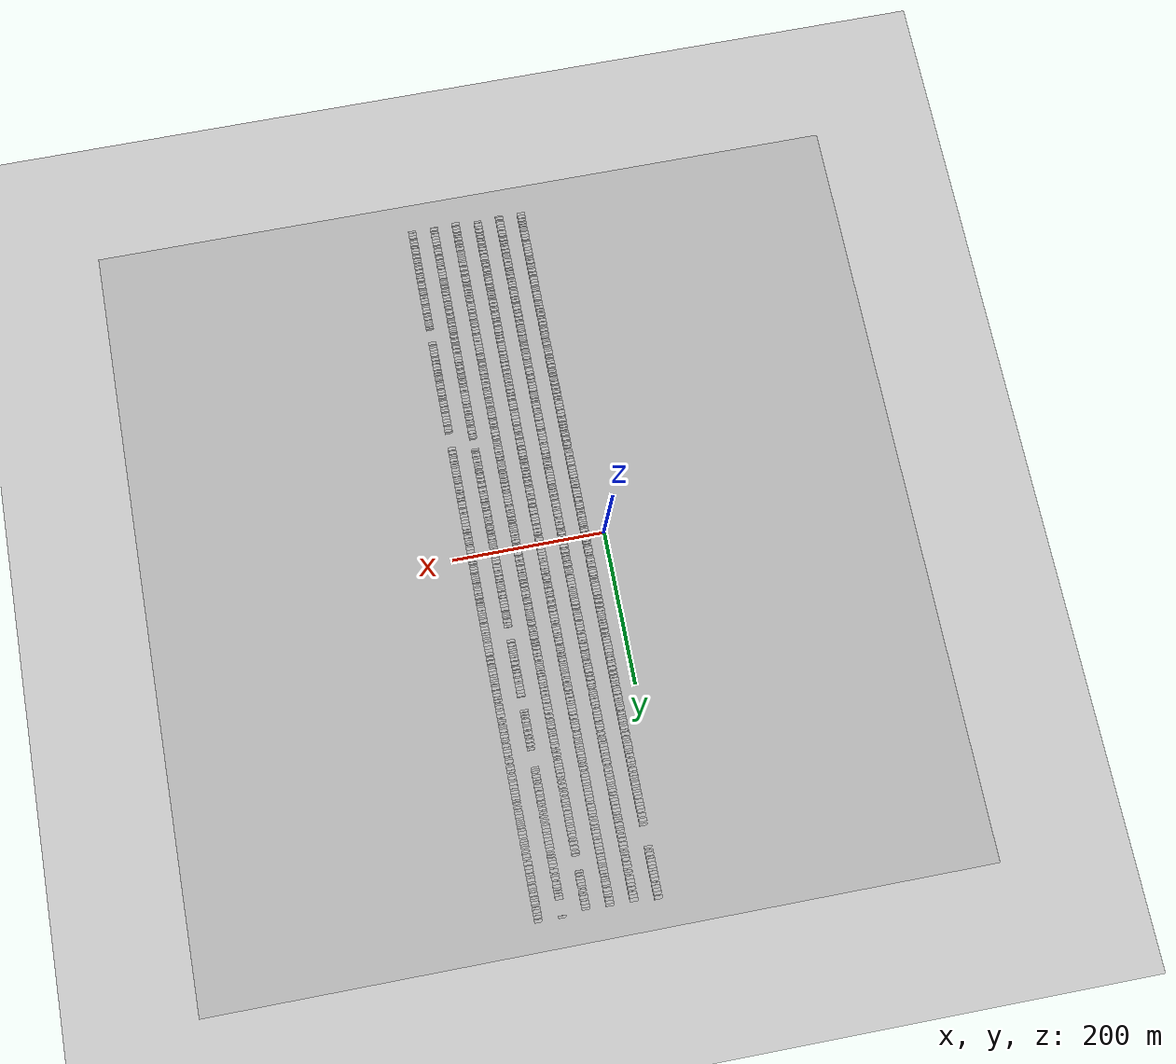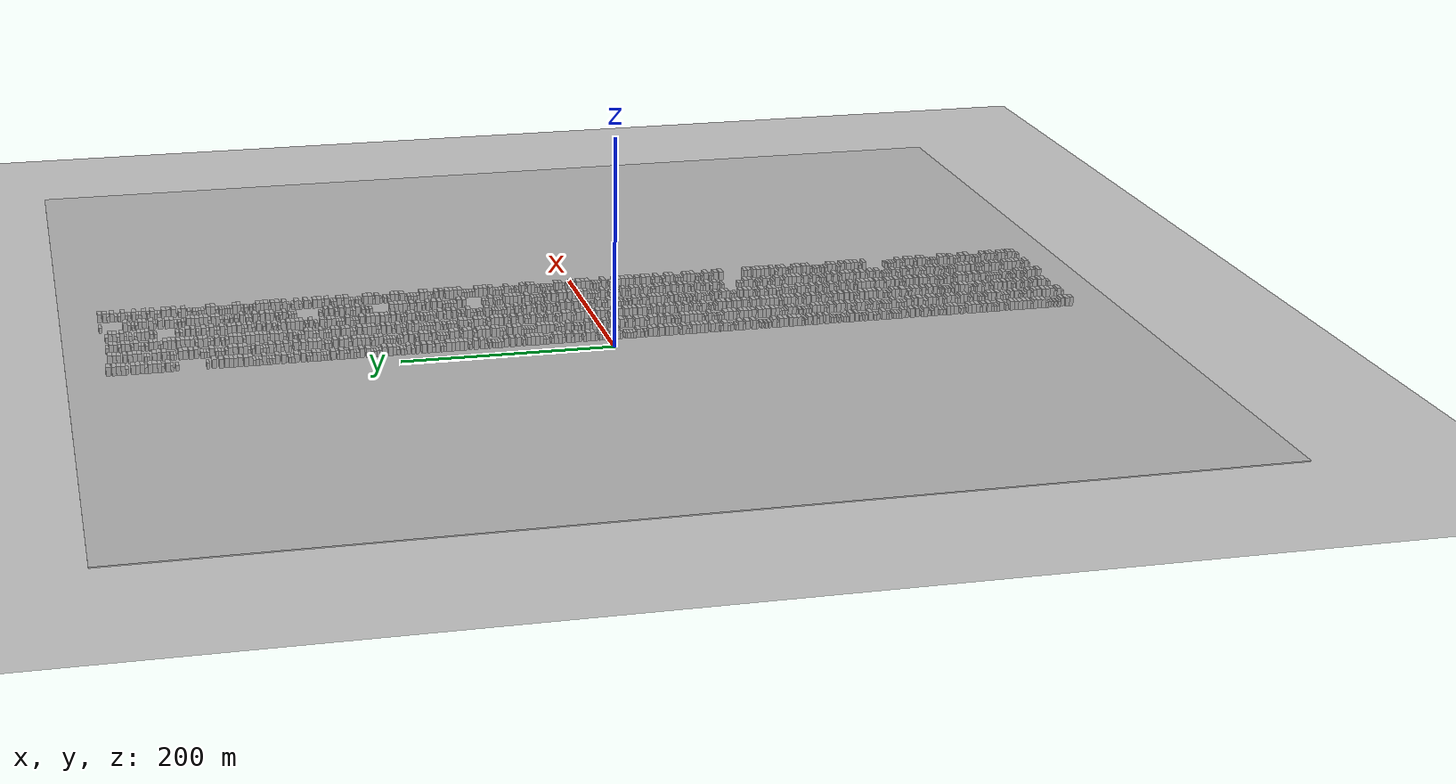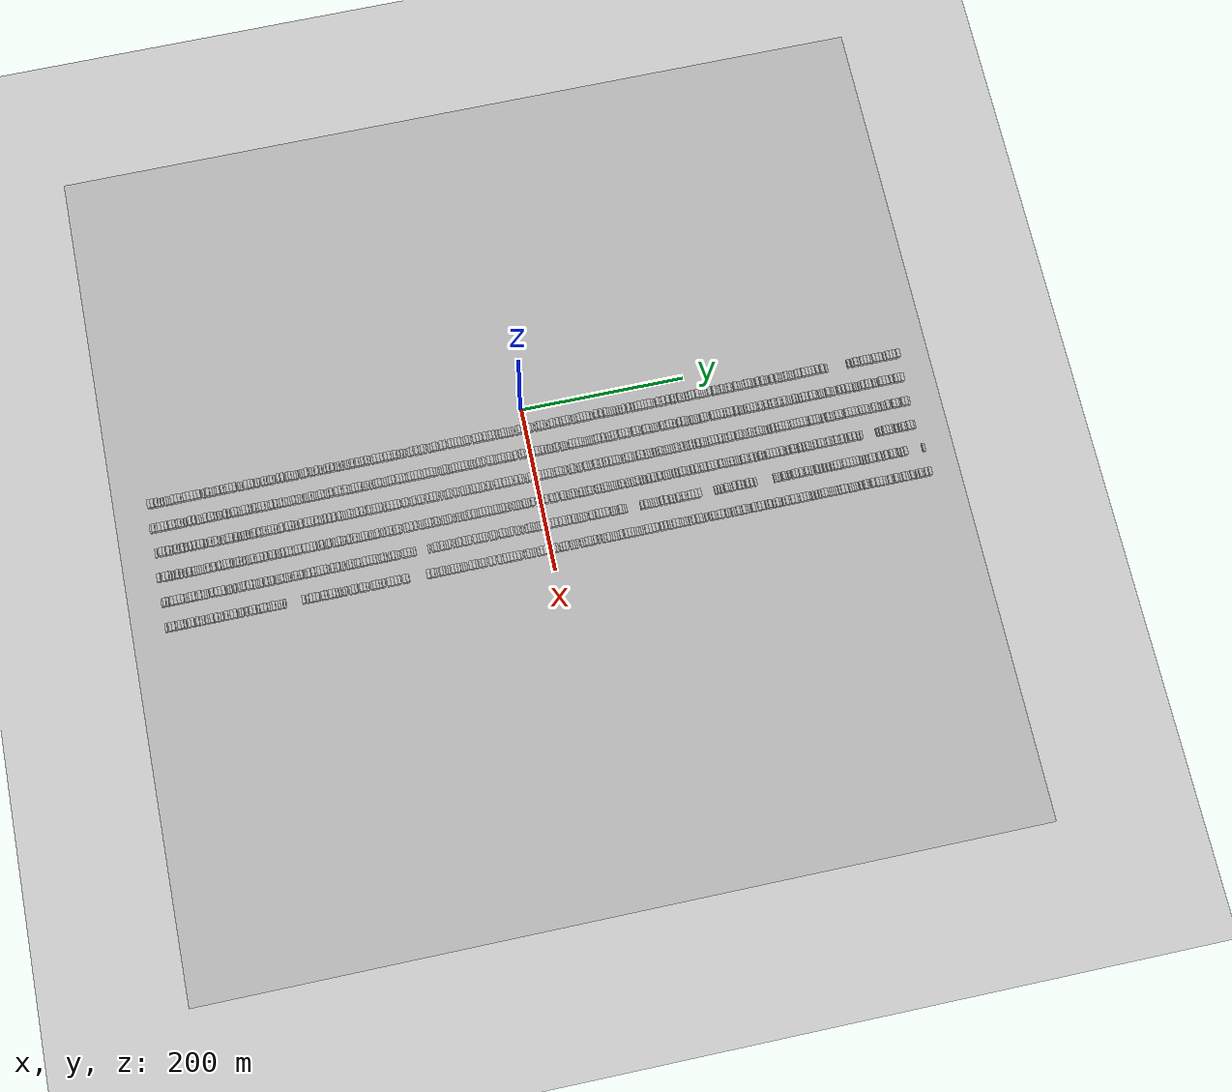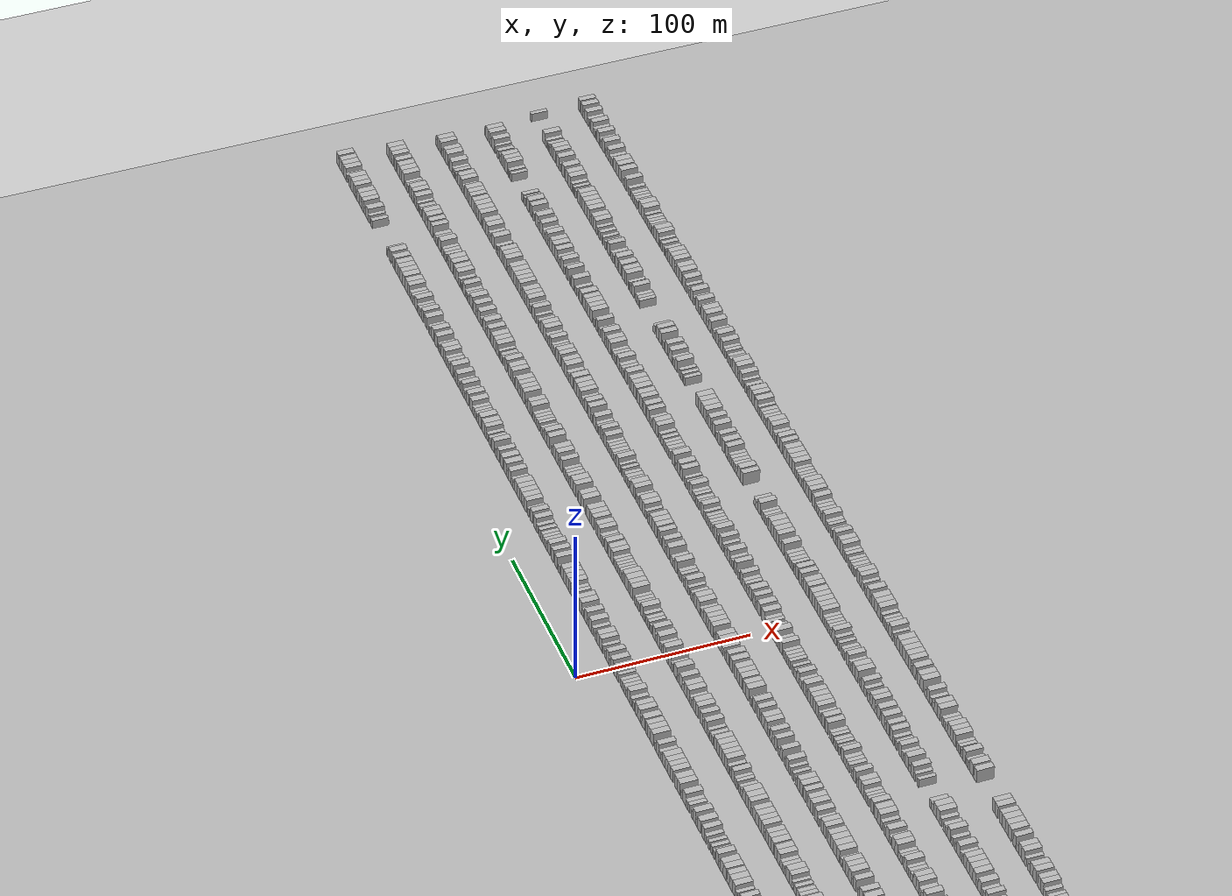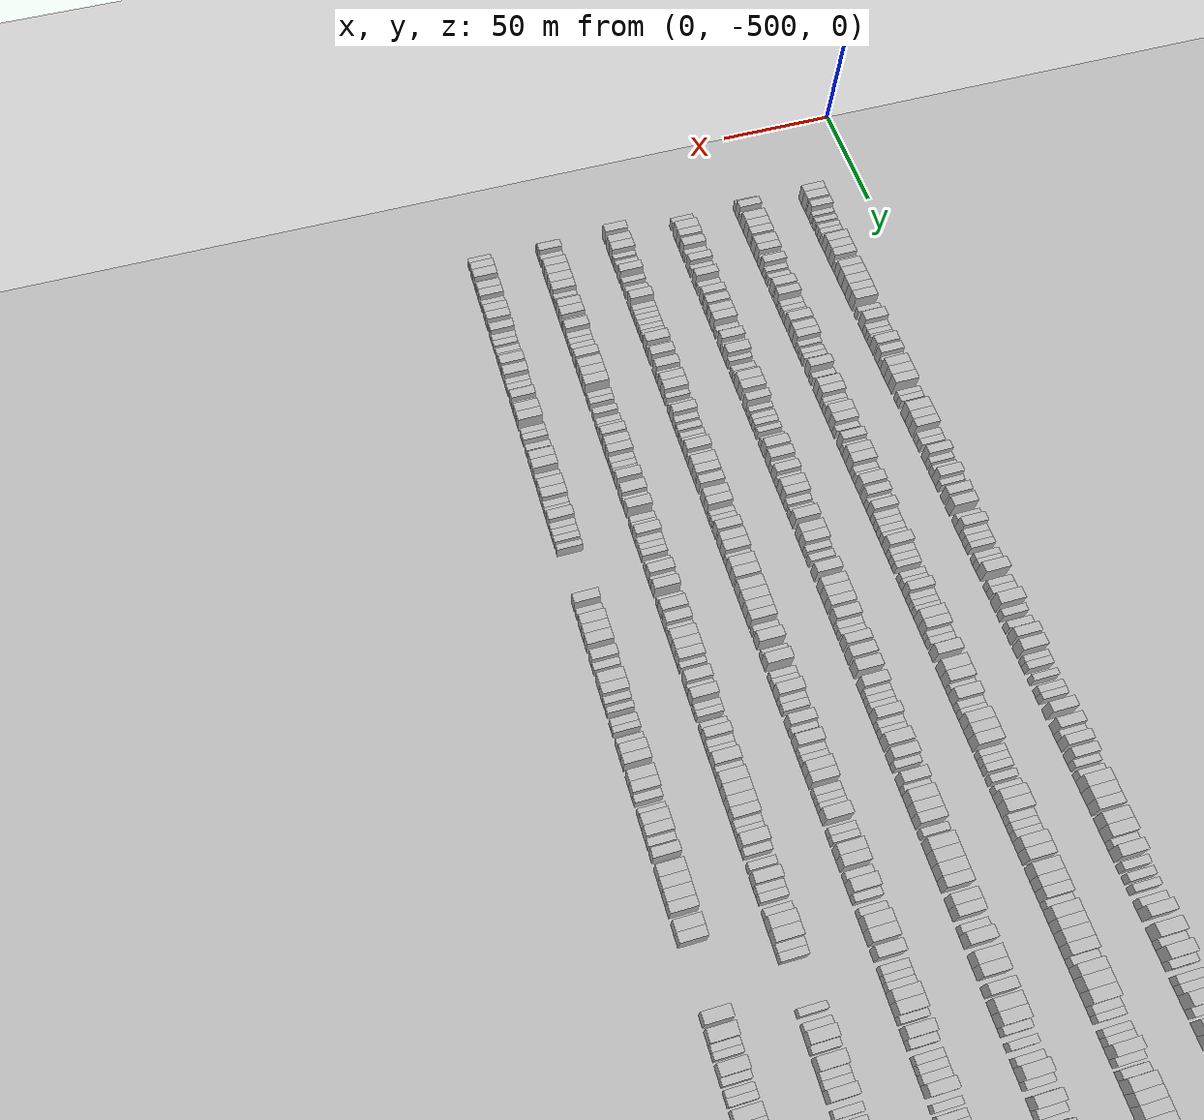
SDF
<sdf version="1.6">
 <world name="default">
  <scene>
   <sky><clouds><speed>12</speed></clouds></sky>
   <ambient>0.4 0.4 0.4 1</ambient>
   <background>0.7 0.7 0.7 1</background>
   <shadows>1</shadows>
  </scene>
  <gravity>0 0 -9.8066</gravity>
  <magnetic_field>6e-06 2.3e-05 -4.2e-05</magnetic_field>
  <physics default="0" name="default_physics" type="ode">
   <ode>
    <solver>
     <type>quick</type>
     <iters>10</iters>
     <sor>1.0</sor>
     <use_dynamic_moi_rescaling>0</use_dynamic_moi_rescaling>
    </solver>
    <constraints>
     <cfm>0</cfm>
     <erp>0.2</erp>
     <contact_max_correcting_vel>100</contact_max_correcting_vel>
     <contact_surface_layer>0.001</contact_surface_layer>
    </constraints>
   </ode>
   <max_step_size>0.004</max_step_size>
   <real_time_factor>1</real_time_factor>
   <real_time_update_rate>250</real_time_update_rate>
  </physics>
  <light name="sun" type="directional">
   <pose>0 0 10 0 0 0</pose>
   <diffuse>0.8 0.8 0.8 1</diffuse>
   <specular>0.2 0.2 0.2 1</specular>
   <attenuation>
    <range>1000</range>
    <constant>0.9</constant>
    <linear>0.01</linear>
    <quadratic>0.001</quadratic>
   </attenuation>
   <direction>-0.5 0.1 -0.9</direction>
  </light>
  <include><name>ground_plane_1</name><uri>model://HANNAS_ground_plane</uri></include>
  <include>
   <name>ground_plane_2</name>
   <uri>model://HANNAS_ground_plane</uri>
   <pose>100 0 0  0 0 0</pose>
  </include>
  <model name="building_1">
   <static>1</static>
   <pose>25.0000 -456.1412 0 0.000000 0.000000 0.000000</pose>
   <link name="link">
    <pose>0 0 4.50 0 0 0</pose>
    <collision name="collision"><geometry><box><size>10.0000 3.7175 9.0000</size></box></geometry></collision>
    <visual name="visual">
     <cast_shadows>0</cast_shadows>
     <geometry><box><size>10.0000 3.7175 9.0000</size></box></geometry>
     <material>
      <script>
       <uri>model://HANNAS_wall/materials/scripts</uri>
       <uri>model://HANNAS_wall/materials/textures</uri>
       <name>vrc/HANNAS_wall</name>
      </script>
     </material>
    </visual>
   </link>
  </model>
  <model name="building_2">
   <static>1</static>
   <pose>25.0000 -452.1056 0 0.000000 0.000000 0.000000</pose>
   <link name="link">
    <pose>0 0 4.50 0 0 0</pose>
    <collision name="collision"><geometry><box><size>10.0000 4.3537 9.0000</size></box></geometry></collision>
    <visual name="visual">
     <cast_shadows>0</cast_shadows>
     <geometry><box><size>10.0000 4.3537 9.0000</size></box></geometry>
     <material>
      <script>
       <uri>model://HANNAS_wall/materials/scripts</uri>
       <uri>model://HANNAS_wall/materials/textures</uri>
       <name>vrc/HANNAS_wall</name>
      </script>
     </material>
    </visual>
   </link>
  </model>
  <model name="building_3">
   <static>1</static>
   <pose>25.0000 -447.1029 0 0.000000 0.000000 0.000000</pose>
   <link name="link">
    <pose>0 0 4.50 0 0 0</pose>
    <collision name="collision"><geometry><box><size>10.0000 3.6517 9.0000</size></box></geometry></collision>
    <visual name="visual">
     <cast_shadows>0</cast_shadows>
     <geometry><box><size>10.0000 3.6517 9.0000</size></box></geometry>
     <material>
      <script>
       <uri>model://HANNAS_wall/materials/scripts</uri>
       <uri>model://HANNAS_wall/materials/textures</uri>
       <name>vrc/HANNAS_wall</name>
      </script>
     </material>
    </visual>
   </link>
  </model>
  <model name="building_4">
   <static>1</static>
   <pose>25.0000 -443.9149 0 0.000000 0.000000 0.000000</pose>
   <link name="link">
    <pose>0 0 3.00 0 0 0</pose>
    <collision name="collision"><geometry><box><size>10.0000 2.7243 6.0000</size></box></geometry></collision>
    <visual name="visual">
     <cast_shadows>0</cast_shadows>
     <geometry><box><size>10.0000 2.7243 6.0000</size></box></geometry>
     <material>
      <script>
       <uri>model://HANNAS_wall/materials/scripts</uri>
       <uri>model://HANNAS_wall/materials/textures</uri>
       <name>vrc/HANNAS_wall</name>
      </script>
     </material>
    </visual>
   </link>
  </model>
  <model name="building_5">
   <static>1</static>
   <pose>25.0000 -440.1953 0 0.000000 0.000000 0.000000</pose>
   <link name="link">
    <pose>0 0 3.00 0 0 0</pose>
    <collision name="collision"><geometry><box><size>10.0000 2.7148 6.0000</size></box></geometry></collision>
    <visual name="visual">
     <cast_shadows>0</cast_shadows>
     <geometry><box><size>10.0000 2.7148 6.0000</size></box></geometry>
     <material>
      <script>
       <uri>model://HANNAS_wall/materials/scripts</uri>
       <uri>model://HANNAS_wall/materials/textures</uri>
       <name>vrc/HANNAS_wall</name>
      </script>
     </material>
    </visual>
   </link>
  </model>
  <model name="building_6">
   <static>1</static>
   <pose>25.0000 -436.5487 0 0.000000 0.000000 0.000000</pose>
   <link name="link">
    <pose>0 0 3.00 0 0 0</pose>
    <collision name="collision"><geometry><box><size>10.0000 2.5785 6.0000</size></box></geometry></collision>
    <visual name="visual">
     <cast_shadows>0</cast_shadows>
     <geometry><box><size>10.0000 2.5785 6.0000</size></box></geometry>
     <material>
      <script>
       <uri>model://HANNAS_wall/materials/scripts</uri>
       <uri>model://HANNAS_wall/materials/textures</uri>
       <name>vrc/HANNAS_wall</name>
      </script>
     </material>
    </visual>
   </link>
  </model>
  <model name="building_7">
   <static>1</static>
   <pose>25.0000 -433.9206 0 0.000000 0.000000 0.000000</pose>
   <link name="link">
    <pose>0 0 3.00 0 0 0</pose>
    <collision name="collision"><geometry><box><size>10.0000 2.6775 6.0000</size></box></geometry></collision>
    <visual name="visual">
     <cast_shadows>0</cast_shadows>
     <geometry><box><size>10.0000 2.6775 6.0000</size></box></geometry>
     <material>
      <script>
       <uri>model://HANNAS_wall/materials/scripts</uri>
       <uri>model://HANNAS_wall/materials/textures</uri>
       <name>vrc/HANNAS_wall</name>
      </script>
     </material>
    </visual>
   </link>
  </model>
  <model name="building_8">
   <static>1</static>
   <pose>25.0000 -431.2459 0 0.000000 0.000000 0.000000</pose>
   <link name="link">
    <pose>0 0 3.00 0 0 0</pose>
    <collision name="collision"><geometry><box><size>10.0000 2.6720 6.0000</size></box></geometry></collision>
    <visual name="visual">
     <cast_shadows>0</cast_shadows>
     <geometry><box><size>10.0000 2.6720 6.0000</size></box></geometry>
     <material>
      <script>
       <uri>model://HANNAS_wall/materials/scripts</uri>
       <uri>model://HANNAS_wall/materials/textures</uri>
       <name>vrc/HANNAS_wall</name>
      </script>
     </material>
    </visual>
   </link>
  </model>
  <model name="building_9">
   <static>1</static>
   <pose>25.0000 -427.8810 0 0.000000 0.000000 0.000000</pose>
   <link name="link">
    <pose>0 0 4.50 0 0 0</pose>
    <collision name="collision"><geometry><box><size>10.0000 4.0577 9.0000</size></box></geometry></collision>
    <visual name="visual">
     <cast_shadows>0</cast_shadows>
     <geometry><box><size>10.0000 4.0577 9.0000</size></box></geometry>
     <material>
      <script>
       <uri>model://HANNAS_wall/materials/scripts</uri>
       <uri>model://HANNAS_wall/materials/textures</uri>
       <name>vrc/HANNAS_wall</name>
      </script>
     </material>
    </visual>
   </link>
  </model>
  <model name="building_10">
   <static>1</static>
   <pose>25.0000 -423.8278 0 0.000000 0.000000 0.000000</pose>
   <link name="link">
    <pose>0 0 4.50 0 0 0</pose>
    <collision name="collision"><geometry><box><size>10.0000 4.0487 9.0000</size></box></geometry></collision>
    <visual name="visual">
     <cast_shadows>0</cast_shadows>
     <geometry><box><size>10.0000 4.0487 9.0000</size></box></geometry>
     <material>
      <script>
       <uri>model://HANNAS_wall/materials/scripts</uri>
       <uri>model://HANNAS_wall/materials/textures</uri>
       <name>vrc/HANNAS_wall</name>
      </script>
     </material>
    </visual>
   </link>
  </model>
  <model name="building_11">
   <static>1</static>
   <pose>25.0000 -419.7677 0 0.000000 0.000000 0.000000</pose>
   <link name="link">
    <pose>0 0 4.50 0 0 0</pose>
    <collision name="collision"><geometry><box><size>10.0000 4.0715 9.0000</size></box></geometry></collision>
    <visual name="visual">
     <cast_shadows>0</cast_shadows>
     <geometry><box><size>10.0000 4.0715 9.0000</size></box></geometry>
     <material>
      <script>
       <uri>model://HANNAS_wall/materials/scripts</uri>
       <uri>model://HANNAS_wall/materials/textures</uri>
       <name>vrc/HANNAS_wall</name>
      </script>
     </material>
    </visual>
   </link>
  </model>
  <model name="building_12">
   <static>1</static>
   <pose>25.0000 -416.3413 0 0.000000 0.000000 0.000000</pose>
   <link name="link">
    <pose>0 0 3.00 0 0 0</pose>
    <collision name="collision"><geometry><box><size>10.0000 2.7813 6.0000</size></box></geometry></collision>
    <visual name="visual">
     <cast_shadows>0</cast_shadows>
     <geometry><box><size>10.0000 2.7813 6.0000</size></box></geometry>
     <material>
      <script>
       <uri>model://HANNAS_wall/materials/scripts</uri>
       <uri>model://HANNAS_wall/materials/textures</uri>
       <name>vrc/HANNAS_wall</name>
      </script>
     </material>
    </visual>
   </link>
  </model>
  <model name="building_13">
   <static>1</static>
   <pose>25.0000 -413.0991 0 0.000000 0.000000 0.000000</pose>
   <link name="link">
    <pose>0 0 4.50 0 0 0</pose>
    <collision name="collision"><geometry><box><size>10.0000 3.7031 9.0000</size></box></geometry></collision>
    <visual name="visual">
     <cast_shadows>0</cast_shadows>
     <geometry><box><size>10.0000 3.7031 9.0000</size></box></geometry>
     <material>
      <script>
       <uri>model://HANNAS_wall/materials/scripts</uri>
       <uri>model://HANNAS_wall/materials/textures</uri>
       <name>vrc/HANNAS_wall</name>
      </script>
     </material>
    </visual>
   </link>
  </model>
  <model name="building_14">
   <static>1</static>
   <pose>25.0000 -409.0088 0 0.000000 0.000000 0.000000</pose>
   <link name="link">
    <pose>0 0 4.50 0 0 0</pose>
    <collision name="collision"><geometry><box><size>10.0000 4.4775 9.0000</size></box></geometry></collision>
    <visual name="visual">
     <cast_shadows>0</cast_shadows>
     <geometry><box><size>10.0000 4.4775 9.0000</size></box></geometry>
     <material>
      <script>
       <uri>model://HANNAS_wall/materials/scripts</uri>
       <uri>model://HANNAS_wall/materials/textures</uri>
       <name>vrc/HANNAS_wall</name>
      </script>
     </material>
    </visual>
   </link>
  </model>
  <model name="building_15">
   <static>1</static>
   <pose>25.0000 -404.5350 0 0.000000 0.000000 0.000000</pose>
   <link name="link">
    <pose>0 0 4.50 0 0 0</pose>
    <collision name="collision"><geometry><box><size>10.0000 4.4703 9.0000</size></box></geometry></collision>
    <visual name="visual">
     <cast_shadows>0</cast_shadows>
     <geometry><box><size>10.0000 4.4703 9.0000</size></box></geometry>
     <material>
      <script>
       <uri>model://HANNAS_wall/materials/scripts</uri>
       <uri>model://HANNAS_wall/materials/textures</uri>
       <name>vrc/HANNAS_wall</name>
      </script>
     </material>
    </visual>
   </link>
  </model>
  <model name="building_16">
   <static>1</static>
   <pose>25.0000 -400.4179 0 0.000000 0.000000 0.000000</pose>
   <link name="link">
    <pose>0 0 4.50 0 0 0</pose>
    <collision name="collision"><geometry><box><size>10.0000 3.7637 9.0000</size></box></geometry></collision>
    <visual name="visual">
     <cast_shadows>0</cast_shadows>
     <geometry><box><size>10.0000 3.7637 9.0000</size></box></geometry>
     <material>
      <script>
       <uri>model://HANNAS_wall/materials/scripts</uri>
       <uri>model://HANNAS_wall/materials/textures</uri>
       <name>vrc/HANNAS_wall</name>
      </script>
     </material>
    </visual>
   </link>
  </model>
  <model name="building_17">
   <static>1</static>
   <pose>25.0000 -396.3041 0 0.000000 0.000000 0.000000</pose>
   <link name="link">
    <pose>0 0 4.50 0 0 0</pose>
    <collision name="collision"><geometry><box><size>10.0000 4.4640 9.0000</size></box></geometry></collision>
    <visual name="visual">
     <cast_shadows>0</cast_shadows>
     <geometry><box><size>10.0000 4.4640 9.0000</size></box></geometry>
     <material>
      <script>
       <uri>model://HANNAS_wall/materials/scripts</uri>
       <uri>model://HANNAS_wall/materials/textures</uri>
       <name>vrc/HANNAS_wall</name>
      </script>
     </material>
    </visual>
   </link>
  </model>
  <model name="building_18">
   <static>1</static>
   <pose>25.0000 -390.7837 0 0.000000 0.000000 0.000000</pose>
   <link name="link">
    <pose>0 0 3.00 0 0 0</pose>
    <collision name="collision"><geometry><box><size>10.0000 2.5768 6.0000</size></box></geometry></collision>
    <visual name="visual">
     <cast_shadows>0</cast_shadows>
     <geometry><box><size>10.0000 2.5768 6.0000</size></box></geometry>
     <material>
      <script>
       <uri>model://HANNAS_wall/materials/scripts</uri>
       <uri>model://HANNAS_wall/materials/textures</uri>
       <name>vrc/HANNAS_wall</name>
      </script>
     </material>
    </visual>
   </link>
  </model>
  <model name="building_19">
   <static>1</static>
   <pose>25.0000 -385.2495 0 0.000000 0.000000 0.000000</pose>
   <link name="link">
    <pose>0 0 4.50 0 0 0</pose>
    <collision name="collision"><geometry><box><size>10.0000 4.4918 9.0000</size></box></geometry></collision>
    <visual name="visual">
     <cast_shadows>0</cast_shadows>
     <geometry><box><size>10.0000 4.4918 9.0000</size></box></geometry>
     <material>
      <script>
       <uri>model://HANNAS_wall/materials/scripts</uri>
       <uri>model://HANNAS_wall/materials/textures</uri>
       <name>vrc/HANNAS_wall</name>
      </script>
     </material>
    </visual>
   </link>
  </model>
  <model name="building_20">
   <static>1</static>
   <pose>25.0000 -381.5577 0 0.000000 0.000000 0.000000</pose>
   <link name="link">
    <pose>0 0 3.00 0 0 0</pose>
    <collision name="collision"><geometry><box><size>10.0000 2.8917 6.0000</size></box></geometry></collision>
    <visual name="visual">
     <cast_shadows>0</cast_shadows>
     <geometry><box><size>10.0000 2.8917 6.0000</size></box></geometry>
     <material>
      <script>
       <uri>model://HANNAS_wall/materials/scripts</uri>
       <uri>model://HANNAS_wall/materials/textures</uri>
       <name>vrc/HANNAS_wall</name>
      </script>
     </material>
    </visual>
   </link>
  </model>
  <model name="building_21">
   <static>1</static>
   <pose>25.0000 -378.9097 0 0.000000 0.000000 0.000000</pose>
   <link name="link">
    <pose>0 0 3.00 0 0 0</pose>
    <collision name="collision"><geometry><box><size>10.0000 2.4043 6.0000</size></box></geometry></collision>
    <visual name="visual">
     <cast_shadows>0</cast_shadows>
     <geometry><box><size>10.0000 2.4043 6.0000</size></box></geometry>
     <material>
      <script>
       <uri>model://HANNAS_wall/materials/scripts</uri>
       <uri>model://HANNAS_wall/materials/textures</uri>
       <name>vrc/HANNAS_wall</name>
      </script>
     </material>
    </visual>
   </link>
  </model>
  <model name="building_22">
   <static>1</static>
   <pose>25.0000 -376.3395 0 0.000000 0.000000 0.000000</pose>
   <link name="link">
    <pose>0 0 3.00 0 0 0</pose>
    <collision name="collision"><geometry><box><size>10.0000 2.7362 6.0000</size></box></geometry></collision>
    <visual name="visual">
     <cast_shadows>0</cast_shadows>
     <geometry><box><size>10.0000 2.7362 6.0000</size></box></geometry>
     <material>
      <script>
       <uri>model://HANNAS_wall/materials/scripts</uri>
       <uri>model://HANNAS_wall/materials/textures</uri>
       <name>vrc/HANNAS_wall</name>
      </script>
     </material>
    </visual>
   </link>
  </model>
  <model name="building_23">
   <static>1</static>
   <pose>25.0000 -372.8652 0 0.000000 0.000000 0.000000</pose>
   <link name="link">
    <pose>0 0 4.50 0 0 0</pose>
    <collision name="collision"><geometry><box><size>10.0000 4.2125 9.0000</size></box></geometry></collision>
    <visual name="visual">
     <cast_shadows>0</cast_shadows>
     <geometry><box><size>10.0000 4.2125 9.0000</size></box></geometry>
     <material>
      <script>
       <uri>model://HANNAS_wall/materials/scripts</uri>
       <uri>model://HANNAS_wall/materials/textures</uri>
       <name>vrc/HANNAS_wall</name>
      </script>
     </material>
    </visual>
   </link>
  </model>
  <model name="building_24">
   <static>1</static>
   <pose>25.0000 -367.9581 0 0.000000 0.000000 0.000000</pose>
   <link name="link">
    <pose>0 0 4.50 0 0 0</pose>
    <collision name="collision"><geometry><box><size>10.0000 3.6017 9.0000</size></box></geometry></collision>
    <visual name="visual">
     <cast_shadows>0</cast_shadows>
     <geometry><box><size>10.0000 3.6017 9.0000</size></box></geometry>
     <material>
      <script>
       <uri>model://HANNAS_wall/materials/scripts</uri>
       <uri>model://HANNAS_wall/materials/textures</uri>
       <name>vrc/HANNAS_wall</name>
      </script>
     </material>
    </visual>
   </link>
  </model>
  <model name="building_25">
   <static>1</static>
   <pose>25.0000 -364.8234 0 0.000000 0.000000 0.000000</pose>
   <link name="link">
    <pose>0 0 3.00 0 0 0</pose>
    <collision name="collision"><geometry><box><size>10.0000 2.6679 6.0000</size></box></geometry></collision>
    <visual name="visual">
     <cast_shadows>0</cast_shadows>
     <geometry><box><size>10.0000 2.6679 6.0000</size></box></geometry>
     <material>
      <script>
       <uri>model://HANNAS_wall/materials/scripts</uri>
       <uri>model://HANNAS_wall/materials/textures</uri>
       <name>vrc/HANNAS_wall</name>
      </script>
     </material>
    </visual>
   </link>
  </model>
  <model name="building_26">
   <static>1</static>
   <pose>25.0000 -361.4323 0 0.000000 0.000000 0.000000</pose>
   <link name="link">
    <pose>0 0 4.50 0 0 0</pose>
    <collision name="collision"><geometry><box><size>10.0000 4.1142 9.0000</size></box></geometry></collision>
    <visual name="visual">
     <cast_shadows>0</cast_shadows>
     <geometry><box><size>10.0000 4.1142 9.0000</size></box></geometry>
     <material>
      <script>
       <uri>model://HANNAS_wall/materials/scripts</uri>
       <uri>model://HANNAS_wall/materials/textures</uri>
       <name>vrc/HANNAS_wall</name>
      </script>
     </material>
    </visual>
   </link>
  </model>
  <model name="building_27">
   <static>1</static>
   <pose>25.0000 -357.2893 0 0.000000 0.000000 0.000000</pose>
   <link name="link">
    <pose>0 0 4.50 0 0 0</pose>
    <collision name="collision"><geometry><box><size>10.0000 4.1719 9.0000</size></box></geometry></collision>
    <visual name="visual">
     <cast_shadows>0</cast_shadows>
     <geometry><box><size>10.0000 4.1719 9.0000</size></box></geometry>
     <material>
      <script>
       <uri>model://HANNAS_wall/materials/scripts</uri>
       <uri>model://HANNAS_wall/materials/textures</uri>
       <name>vrc/HANNAS_wall</name>
      </script>
     </material>
    </visual>
   </link>
  </model>
  <model name="building_28">
   <static>1</static>
   <pose>25.0000 -353.1575 0 0.000000 0.000000 0.000000</pose>
   <link name="link">
    <pose>0 0 4.50 0 0 0</pose>
    <collision name="collision"><geometry><box><size>10.0000 4.0917 9.0000</size></box></geometry></collision>
    <visual name="visual">
     <cast_shadows>0</cast_shadows>
     <geometry><box><size>10.0000 4.0917 9.0000</size></box></geometry>
     <material>
      <script>
       <uri>model://HANNAS_wall/materials/scripts</uri>
       <uri>model://HANNAS_wall/materials/textures</uri>
       <name>vrc/HANNAS_wall</name>
      </script>
     </material>
    </visual>
   </link>
  </model>
  <model name="building_29">
   <static>1</static>
   <pose>25.0000 -347.8444 0 0.000000 0.000000 0.000000</pose>
   <link name="link">
    <pose>0 0 3.00 0 0 0</pose>
    <collision name="collision"><geometry><box><size>10.0000 2.5344 6.0000</size></box></geometry></collision>
    <visual name="visual">
     <cast_shadows>0</cast_shadows>
     <geometry><box><size>10.0000 2.5344 6.0000</size></box></geometry>
     <material>
      <script>
       <uri>model://HANNAS_wall/materials/scripts</uri>
       <uri>model://HANNAS_wall/materials/textures</uri>
       <name>vrc/HANNAS_wall</name>
      </script>
     </material>
    </visual>
   </link>
  </model>
  <model name="building_30">
   <static>1</static>
   <pose>25.0000 -345.2162 0 0.000000 0.000000 0.000000</pose>
   <link name="link">
    <pose>0 0 3.00 0 0 0</pose>
    <collision name="collision"><geometry><box><size>10.0000 2.7220 6.0000</size></box></geometry></collision>
    <visual name="visual">
     <cast_shadows>0</cast_shadows>
     <geometry><box><size>10.0000 2.7220 6.0000</size></box></geometry>
     <material>
      <script>
       <uri>model://HANNAS_wall/materials/scripts</uri>
       <uri>model://HANNAS_wall/materials/textures</uri>
       <name>vrc/HANNAS_wall</name>
      </script>
     </material>
    </visual>
   </link>
  </model>
  <model name="building_31">
   <static>1</static>
   <pose>25.0000 -339.6061 0 0.000000 0.000000 0.000000</pose>
   <link name="link">
    <pose>0 0 4.50 0 0 0</pose>
    <collision name="collision"><geometry><box><size>10.0000 4.4983 9.0000</size></box></geometry></collision>
    <visual name="visual">
     <cast_shadows>0</cast_shadows>
     <geometry><box><size>10.0000 4.4983 9.0000</size></box></geometry>
     <material>
      <script>
       <uri>model://HANNAS_wall/materials/scripts</uri>
       <uri>model://HANNAS_wall/materials/textures</uri>
       <name>vrc/HANNAS_wall</name>
      </script>
     </material>
    </visual>
   </link>
  </model>
  <model name="building_32">
   <static>1</static>
   <pose>25.0000 -335.4722 0 0.000000 0.000000 0.000000</pose>
   <link name="link">
    <pose>0 0 4.50 0 0 0</pose>
    <collision name="collision"><geometry><box><size>10.0000 3.7696 9.0000</size></box></geometry></collision>
    <visual name="visual">
     <cast_shadows>0</cast_shadows>
     <geometry><box><size>10.0000 3.7696 9.0000</size></box></geometry>
     <material>
      <script>
       <uri>model://HANNAS_wall/materials/scripts</uri>
       <uri>model://HANNAS_wall/materials/textures</uri>
       <name>vrc/HANNAS_wall</name>
      </script>
     </material>
    </visual>
   </link>
  </model>
  <model name="building_33">
   <static>1</static>
   <pose>25.0000 -331.7244 0 0.000000 0.000000 0.000000</pose>
   <link name="link">
    <pose>0 0 4.50 0 0 0</pose>
    <collision name="collision"><geometry><box><size>10.0000 3.7260 9.0000</size></box></geometry></collision>
    <visual name="visual">
     <cast_shadows>0</cast_shadows>
     <geometry><box><size>10.0000 3.7260 9.0000</size></box></geometry>
     <material>
      <script>
       <uri>model://HANNAS_wall/materials/scripts</uri>
       <uri>model://HANNAS_wall/materials/textures</uri>
       <name>vrc/HANNAS_wall</name>
      </script>
     </material>
    </visual>
   </link>
  </model>
  <model name="building_34">
   <static>1</static>
   <pose>25.0000 -327.3848 0 0.000000 0.000000 0.000000</pose>
   <link name="link">
    <pose>0 0 3.00 0 0 0</pose>
    <collision name="collision"><geometry><box><size>10.0000 2.9531 6.0000</size></box></geometry></collision>
    <visual name="visual">
     <cast_shadows>0</cast_shadows>
     <geometry><box><size>10.0000 2.9531 6.0000</size></box></geometry>
     <material>
      <script>
       <uri>model://HANNAS_wall/materials/scripts</uri>
       <uri>model://HANNAS_wall/materials/textures</uri>
       <name>vrc/HANNAS_wall</name>
      </script>
     </material>
    </visual>
   </link>
  </model>
  <model name="building_35">
   <static>1</static>
   <pose>25.0000 -324.4236 0 0.000000 0.000000 0.000000</pose>
   <link name="link">
    <pose>0 0 3.00 0 0 0</pose>
    <collision name="collision"><geometry><box><size>10.0000 2.9694 6.0000</size></box></geometry></collision>
    <visual name="visual">
     <cast_shadows>0</cast_shadows>
     <geometry><box><size>10.0000 2.9694 6.0000</size></box></geometry>
     <material>
      <script>
       <uri>model://HANNAS_wall/materials/scripts</uri>
       <uri>model://HANNAS_wall/materials/textures</uri>
       <name>vrc/HANNAS_wall</name>
      </script>
     </material>
    </visual>
   </link>
  </model>
  <model name="building_36">
   <static>1</static>
   <pose>25.0000 -319.0870 0 0.000000 0.000000 0.000000</pose>
   <link name="link">
    <pose>0 0 4.50 0 0 0</pose>
    <collision name="collision"><geometry><box><size>10.0000 3.7037 9.0000</size></box></geometry></collision>
    <visual name="visual">
     <cast_shadows>0</cast_shadows>
     <geometry><box><size>10.0000 3.7037 9.0000</size></box></geometry>
     <material>
      <script>
       <uri>model://HANNAS_wall/materials/scripts</uri>
       <uri>model://HANNAS_wall/materials/textures</uri>
       <name>vrc/HANNAS_wall</name>
      </script>
     </material>
    </visual>
   </link>
  </model>
  <model name="building_37">
   <static>1</static>
   <pose>25.0000 -315.8735 0 0.000000 0.000000 0.000000</pose>
   <link name="link">
    <pose>0 0 3.00 0 0 0</pose>
    <collision name="collision"><geometry><box><size>10.0000 2.7234 6.0000</size></box></geometry></collision>
    <visual name="visual">
     <cast_shadows>0</cast_shadows>
     <geometry><box><size>10.0000 2.7234 6.0000</size></box></geometry>
     <material>
      <script>
       <uri>model://HANNAS_wall/materials/scripts</uri>
       <uri>model://HANNAS_wall/materials/textures</uri>
       <name>vrc/HANNAS_wall</name>
      </script>
     </material>
    </visual>
   </link>
  </model>
  <model name="building_38">
   <static>1</static>
   <pose>25.0000 -312.1165 0 0.000000 0.000000 0.000000</pose>
   <link name="link">
    <pose>0 0 3.00 0 0 0</pose>
    <collision name="collision"><geometry><box><size>10.0000 2.7905 6.0000</size></box></geometry></collision>
    <visual name="visual">
     <cast_shadows>0</cast_shadows>
     <geometry><box><size>10.0000 2.7905 6.0000</size></box></geometry>
     <material>
      <script>
       <uri>model://HANNAS_wall/materials/scripts</uri>
       <uri>model://HANNAS_wall/materials/textures</uri>
       <name>vrc/HANNAS_wall</name>
      </script>
     </material>
    </visual>
   </link>
  </model>
  <model name="building_39">
   <static>1</static>
   <pose>25.0000 -308.7579 0 0.000000 0.000000 0.000000</pose>
   <link name="link">
    <pose>0 0 4.50 0 0 0</pose>
    <collision name="collision"><geometry><box><size>10.0000 3.9267 9.0000</size></box></geometry></collision>
    <visual name="visual">
     <cast_shadows>0</cast_shadows>
     <geometry><box><size>10.0000 3.9267 9.0000</size></box></geometry>
     <material>
      <script>
       <uri>model://HANNAS_wall/materials/scripts</uri>
       <uri>model://HANNAS_wall/materials/textures</uri>
       <name>vrc/HANNAS_wall</name>
      </script>
     </material>
    </visual>
   </link>
  </model>
  <model name="building_40">
   <static>1</static>
   <pose>25.0000 -305.5402 0 0.000000 0.000000 0.000000</pose>
   <link name="link">
    <pose>0 0 3.00 0 0 0</pose>
    <collision name="collision"><geometry><box><size>10.0000 2.5087 6.0000</size></box></geometry></collision>
    <visual name="visual">
     <cast_shadows>0</cast_shadows>
     <geometry><box><size>10.0000 2.5087 6.0000</size></box></geometry>
     <material>
      <script>
       <uri>model://HANNAS_wall/materials/scripts</uri>
       <uri>model://HANNAS_wall/materials/textures</uri>
       <name>vrc/HANNAS_wall</name>
      </script>
     </material>
    </visual>
   </link>
  </model>
  <model name="building_41">
   <static>1</static>
   <pose>25.0000 -300.4034 0 0.000000 0.000000 0.000000</pose>
   <link name="link">
    <pose>0 0 4.50 0 0 0</pose>
    <collision name="collision"><geometry><box><size>10.0000 3.7648 9.0000</size></box></geometry></collision>
    <visual name="visual">
     <cast_shadows>0</cast_shadows>
     <geometry><box><size>10.0000 3.7648 9.0000</size></box></geometry>
     <material>
      <script>
       <uri>model://HANNAS_wall/materials/scripts</uri>
       <uri>model://HANNAS_wall/materials/textures</uri>
       <name>vrc/HANNAS_wall</name>
      </script>
     </material>
    </visual>
   </link>
  </model>
  <model name="building_42">
   <static>1</static>
   <pose>25.0000 -295.4525 0 0.000000 0.000000 0.000000</pose>
   <link name="link">
    <pose>0 0 4.50 0 0 0</pose>
    <collision name="collision"><geometry><box><size>10.0000 4.1371 9.0000</size></box></geometry></collision>
    <visual name="visual">
     <cast_shadows>0</cast_shadows>
     <geometry><box><size>10.0000 4.1371 9.0000</size></box></geometry>
     <material>
      <script>
       <uri>model://HANNAS_wall/materials/scripts</uri>
       <uri>model://HANNAS_wall/materials/textures</uri>
       <name>vrc/HANNAS_wall</name>
      </script>
     </material>
    </visual>
   </link>
  </model>
  <model name="building_43">
   <static>1</static>
   <pose>25.0000 -289.8964 0 0.000000 0.000000 0.000000</pose>
   <link name="link">
    <pose>0 0 3.00 0 0 0</pose>
    <collision name="collision"><geometry><box><size>10.0000 2.9751 6.0000</size></box></geometry></collision>
    <visual name="visual">
     <cast_shadows>0</cast_shadows>
     <geometry><box><size>10.0000 2.9751 6.0000</size></box></geometry>
     <material>
      <script>
       <uri>model://HANNAS_wall/materials/scripts</uri>
       <uri>model://HANNAS_wall/materials/textures</uri>
       <name>vrc/HANNAS_wall</name>
      </script>
     </material>
    </visual>
   </link>
  </model>
  <model name="building_44">
   <static>1</static>
   <pose>25.0000 -286.5066 0 0.000000 0.000000 0.000000</pose>
   <link name="link">
    <pose>0 0 4.50 0 0 0</pose>
    <collision name="collision"><geometry><box><size>10.0000 3.8045 9.0000</size></box></geometry></collision>
    <visual name="visual">
     <cast_shadows>0</cast_shadows>
     <geometry><box><size>10.0000 3.8045 9.0000</size></box></geometry>
     <material>
      <script>
       <uri>model://HANNAS_wall/materials/scripts</uri>
       <uri>model://HANNAS_wall/materials/textures</uri>
       <name>vrc/HANNAS_wall</name>
      </script>
     </material>
    </visual>
   </link>
  </model>
  <model name="building_45">
   <static>1</static>
   <pose>25.0000 -283.2274 0 0.000000 0.000000 0.000000</pose>
   <link name="link">
    <pose>0 0 3.00 0 0 0</pose>
    <collision name="collision"><geometry><box><size>10.0000 2.7539 6.0000</size></box></geometry></collision>
    <visual name="visual">
     <cast_shadows>0</cast_shadows>
     <geometry><box><size>10.0000 2.7539 6.0000</size></box></geometry>
     <material>
      <script>
       <uri>model://HANNAS_wall/materials/scripts</uri>
       <uri>model://HANNAS_wall/materials/textures</uri>
       <name>vrc/HANNAS_wall</name>
      </script>
     </material>
    </visual>
   </link>
  </model>
  <model name="building_46">
   <static>1</static>
   <pose>25.0000 -280.3685 0 0.000000 0.000000 0.000000</pose>
   <link name="link">
    <pose>0 0 3.00 0 0 0</pose>
    <collision name="collision"><geometry><box><size>10.0000 2.9638 6.0000</size></box></geometry></collision>
    <visual name="visual">
     <cast_shadows>0</cast_shadows>
     <geometry><box><size>10.0000 2.9638 6.0000</size></box></geometry>
     <material>
      <script>
       <uri>model://HANNAS_wall/materials/scripts</uri>
       <uri>model://HANNAS_wall/materials/textures</uri>
       <name>vrc/HANNAS_wall</name>
      </script>
     </material>
    </visual>
   </link>
  </model>
  <model name="building_47">
   <static>1</static>
   <pose>25.0000 -277.5819 0 0.000000 0.000000 0.000000</pose>
   <link name="link">
    <pose>0 0 3.00 0 0 0</pose>
    <collision name="collision"><geometry><box><size>10.0000 2.6095 6.0000</size></box></geometry></collision>
    <visual name="visual">
     <cast_shadows>0</cast_shadows>
     <geometry><box><size>10.0000 2.6095 6.0000</size></box></geometry>
     <material>
      <script>
       <uri>model://HANNAS_wall/materials/scripts</uri>
       <uri>model://HANNAS_wall/materials/textures</uri>
       <name>vrc/HANNAS_wall</name>
      </script>
     </material>
    </visual>
   </link>
  </model>
  <model name="building_48">
   <static>1</static>
   <pose>25.0000 -273.0183 0 0.000000 0.000000 0.000000</pose>
   <link name="link">
    <pose>0 0 3.00 0 0 0</pose>
    <collision name="collision"><geometry><box><size>10.0000 2.5177 6.0000</size></box></geometry></collision>
    <visual name="visual">
     <cast_shadows>0</cast_shadows>
     <geometry><box><size>10.0000 2.5177 6.0000</size></box></geometry>
     <material>
      <script>
       <uri>model://HANNAS_wall/materials/scripts</uri>
       <uri>model://HANNAS_wall/materials/textures</uri>
       <name>vrc/HANNAS_wall</name>
      </script>
     </material>
    </visual>
   </link>
  </model>
  <model name="building_49">
   <static>1</static>
   <pose>25.0000 -270.3410 0 0.000000 0.000000 0.000000</pose>
   <link name="link">
    <pose>0 0 3.00 0 0 0</pose>
    <collision name="collision"><geometry><box><size>10.0000 2.8370 6.0000</size></box></geometry></collision>
    <visual name="visual">
     <cast_shadows>0</cast_shadows>
     <geometry><box><size>10.0000 2.8370 6.0000</size></box></geometry>
     <material>
      <script>
       <uri>model://HANNAS_wall/materials/scripts</uri>
       <uri>model://HANNAS_wall/materials/textures</uri>
       <name>vrc/HANNAS_wall</name>
      </script>
     </material>
    </visual>
   </link>
  </model>
  <model name="building_50">
   <static>1</static>
   <pose>25.0000 -266.7920 0 0.000000 0.000000 0.000000</pose>
   <link name="link">
    <pose>0 0 4.50 0 0 0</pose>
    <collision name="collision"><geometry><box><size>10.0000 4.2609 9.0000</size></box></geometry></collision>
    <visual name="visual">
     <cast_shadows>0</cast_shadows>
     <geometry><box><size>10.0000 4.2609 9.0000</size></box></geometry>
     <material>
      <script>
       <uri>model://HANNAS_wall/materials/scripts</uri>
       <uri>model://HANNAS_wall/materials/textures</uri>
       <name>vrc/HANNAS_wall</name>
      </script>
     </material>
    </visual>
   </link>
  </model>
  <model name="building_51">
   <static>1</static>
   <pose>25.0000 -261.2917 0 0.000000 0.000000 0.000000</pose>
   <link name="link">
    <pose>0 0 3.00 0 0 0</pose>
    <collision name="collision"><geometry><box><size>10.0000 2.7397 6.0000</size></box></geometry></collision>
    <visual name="visual">
     <cast_shadows>0</cast_shadows>
     <geometry><box><size>10.0000 2.7397 6.0000</size></box></geometry>
     <material>
      <script>
       <uri>model://HANNAS_wall/materials/scripts</uri>
       <uri>model://HANNAS_wall/materials/textures</uri>
       <name>vrc/HANNAS_wall</name>
      </script>
     </material>
    </visual>
   </link>
  </model>
  <model name="building_52">
   <static>1</static>
   <pose>25.0000 -258.4935 0 0.000000 0.000000 0.000000</pose>
   <link name="link">
    <pose>0 0 3.00 0 0 0</pose>
    <collision name="collision"><geometry><box><size>10.0000 2.8569 6.0000</size></box></geometry></collision>
    <visual name="visual">
     <cast_shadows>0</cast_shadows>
     <geometry><box><size>10.0000 2.8569 6.0000</size></box></geometry>
     <material>
      <script>
       <uri>model://HANNAS_wall/materials/scripts</uri>
       <uri>model://HANNAS_wall/materials/textures</uri>
       <name>vrc/HANNAS_wall</name>
      </script>
     </material>
    </visual>
   </link>
  </model>
  <model name="building_53">
   <static>1</static>
   <pose>25.0000 -253.8301 0 0.000000 0.000000 0.000000</pose>
   <link name="link">
    <pose>0 0 4.50 0 0 0</pose>
    <collision name="collision"><geometry><box><size>10.0000 4.4698 9.0000</size></box></geometry></collision>
    <visual name="visual">
     <cast_shadows>0</cast_shadows>
     <geometry><box><size>10.0000 4.4698 9.0000</size></box></geometry>
     <material>
      <script>
       <uri>model://HANNAS_wall/materials/scripts</uri>
       <uri>model://HANNAS_wall/materials/textures</uri>
       <name>vrc/HANNAS_wall</name>
      </script>
     </material>
    </visual>
   </link>
  </model>
  <model name="building_54">
   <static>1</static>
   <pose>25.0000 -249.1184 0 0.000000 0.000000 0.000000</pose>
   <link name="link">
    <pose>0 0 3.00 0 0 0</pose>
    <collision name="collision"><geometry><box><size>10.0000 2.9537 6.0000</size></box></geometry></collision>
    <visual name="visual">
     <cast_shadows>0</cast_shadows>
     <geometry><box><size>10.0000 2.9537 6.0000</size></box></geometry>
     <material>
      <script>
       <uri>model://HANNAS_wall/materials/scripts</uri>
       <uri>model://HANNAS_wall/materials/textures</uri>
       <name>vrc/HANNAS_wall</name>
      </script>
     </material>
    </visual>
   </link>
  </model>
  <model name="building_55">
   <static>1</static>
   <pose>25.0000 -244.2118 0 0.000000 0.000000 0.000000</pose>
   <link name="link">
    <pose>0 0 3.00 0 0 0</pose>
    <collision name="collision"><geometry><box><size>10.0000 2.8596 6.0000</size></box></geometry></collision>
    <visual name="visual">
     <cast_shadows>0</cast_shadows>
     <geometry><box><size>10.0000 2.8596 6.0000</size></box></geometry>
     <material>
      <script>
       <uri>model://HANNAS_wall/materials/scripts</uri>
       <uri>model://HANNAS_wall/materials/textures</uri>
       <name>vrc/HANNAS_wall</name>
      </script>
     </material>
    </visual>
   </link>
  </model>
  <model name="building_56">
   <static>1</static>
   <pose>25.0000 -239.9653 0 0.000000 0.000000 0.000000</pose>
   <link name="link">
    <pose>0 0 4.50 0 0 0</pose>
    <collision name="collision"><geometry><box><size>10.0000 3.6334 9.0000</size></box></geometry></collision>
    <visual name="visual">
     <cast_shadows>0</cast_shadows>
     <geometry><box><size>10.0000 3.6334 9.0000</size></box></geometry>
     <material>
      <script>
       <uri>model://HANNAS_wall/materials/scripts</uri>
       <uri>model://HANNAS_wall/materials/textures</uri>
       <name>vrc/HANNAS_wall</name>
      </script>
     </material>
    </visual>
   </link>
  </model>
  <model name="building_57">
   <static>1</static>
   <pose>25.0000 -234.9672 0 0.000000 0.000000 0.000000</pose>
   <link name="link">
    <pose>0 0 4.50 0 0 0</pose>
    <collision name="collision"><geometry><box><size>10.0000 4.3627 9.0000</size></box></geometry></collision>
    <visual name="visual">
     <cast_shadows>0</cast_shadows>
     <geometry><box><size>10.0000 4.3627 9.0000</size></box></geometry>
     <material>
      <script>
       <uri>model://HANNAS_wall/materials/scripts</uri>
       <uri>model://HANNAS_wall/materials/textures</uri>
       <name>vrc/HANNAS_wall</name>
      </script>
     </material>
    </visual>
   </link>
  </model>
  <model name="building_58">
   <static>1</static>
   <pose>25.0000 -230.5856 0 0.000000 0.000000 0.000000</pose>
   <link name="link">
    <pose>0 0 3.00 0 0 0</pose>
    <collision name="collision"><geometry><box><size>10.0000 2.4004 6.0000</size></box></geometry></collision>
    <visual name="visual">
     <cast_shadows>0</cast_shadows>
     <geometry><box><size>10.0000 2.4004 6.0000</size></box></geometry>
     <material>
      <script>
       <uri>model://HANNAS_wall/materials/scripts</uri>
       <uri>model://HANNAS_wall/materials/textures</uri>
       <name>vrc/HANNAS_wall</name>
      </script>
     </material>
    </visual>
   </link>
  </model>
  <model name="building_59">
   <static>1</static>
   <pose>25.0000 -227.9175 0 0.000000 0.000000 0.000000</pose>
   <link name="link">
    <pose>0 0 3.00 0 0 0</pose>
    <collision name="collision"><geometry><box><size>10.0000 2.9358 6.0000</size></box></geometry></collision>
    <visual name="visual">
     <cast_shadows>0</cast_shadows>
     <geometry><box><size>10.0000 2.9358 6.0000</size></box></geometry>
     <material>
      <script>
       <uri>model://HANNAS_wall/materials/scripts</uri>
       <uri>model://HANNAS_wall/materials/textures</uri>
       <name>vrc/HANNAS_wall</name>
      </script>
     </material>
    </visual>
   </link>
  </model>
  <model name="building_60">
   <static>1</static>
   <pose>25.0000 -223.2182 0 0.000000 0.000000 0.000000</pose>
   <link name="link">
    <pose>0 0 3.00 0 0 0</pose>
    <collision name="collision"><geometry><box><size>10.0000 2.4628 6.0000</size></box></geometry></collision>
    <visual name="visual">
     <cast_shadows>0</cast_shadows>
     <geometry><box><size>10.0000 2.4628 6.0000</size></box></geometry>
     <material>
      <script>
       <uri>model://HANNAS_wall/materials/scripts</uri>
       <uri>model://HANNAS_wall/materials/textures</uri>
       <name>vrc/HANNAS_wall</name>
      </script>
     </material>
    </visual>
   </link>
  </model>
  <model name="building_61">
   <static>1</static>
   <pose>25.0000 -218.6369 0 0.000000 0.000000 0.000000</pose>
   <link name="link">
    <pose>0 0 3.00 0 0 0</pose>
    <collision name="collision"><geometry><box><size>10.0000 2.6998 6.0000</size></box></geometry></collision>
    <visual name="visual">
     <cast_shadows>0</cast_shadows>
     <geometry><box><size>10.0000 2.6998 6.0000</size></box></geometry>
     <material>
      <script>
       <uri>model://HANNAS_wall/materials/scripts</uri>
       <uri>model://HANNAS_wall/materials/textures</uri>
       <name>vrc/HANNAS_wall</name>
      </script>
     </material>
    </visual>
   </link>
  </model>
  <model name="building_62">
   <static>1</static>
   <pose>25.0000 -215.9853 0 0.000000 0.000000 0.000000</pose>
   <link name="link">
    <pose>0 0 3.00 0 0 0</pose>
    <collision name="collision"><geometry><box><size>10.0000 2.6033 6.0000</size></box></geometry></collision>
    <visual name="visual">
     <cast_shadows>0</cast_shadows>
     <geometry><box><size>10.0000 2.6033 6.0000</size></box></geometry>
     <material>
      <script>
       <uri>model://HANNAS_wall/materials/scripts</uri>
       <uri>model://HANNAS_wall/materials/textures</uri>
       <name>vrc/HANNAS_wall</name>
      </script>
     </material>
    </visual>
   </link>
  </model>
  <model name="building_63">
   <static>1</static>
   <pose>25.0000 -210.7302 0 0.000000 0.000000 0.000000</pose>
   <link name="link">
    <pose>0 0 4.50 0 0 0</pose>
    <collision name="collision"><geometry><box><size>10.0000 3.9068 9.0000</size></box></geometry></collision>
    <visual name="visual">
     <cast_shadows>0</cast_shadows>
     <geometry><box><size>10.0000 3.9068 9.0000</size></box></geometry>
     <material>
      <script>
       <uri>model://HANNAS_wall/materials/scripts</uri>
       <uri>model://HANNAS_wall/materials/textures</uri>
       <name>vrc/HANNAS_wall</name>
      </script>
     </material>
    </visual>
   </link>
  </model>
  <model name="building_64">
   <static>1</static>
   <pose>25.0000 -204.8538 0 0.000000 0.000000 0.000000</pose>
   <link name="link">
    <pose>0 0 4.50 0 0 0</pose>
    <collision name="collision"><geometry><box><size>10.0000 3.8460 9.0000</size></box></geometry></collision>
    <visual name="visual">
     <cast_shadows>0</cast_shadows>
     <geometry><box><size>10.0000 3.8460 9.0000</size></box></geometry>
     <material>
      <script>
       <uri>model://HANNAS_wall/materials/scripts</uri>
       <uri>model://HANNAS_wall/materials/textures</uri>
       <name>vrc/HANNAS_wall</name>
      </script>
     </material>
    </visual>
   </link>
  </model>
  <model name="building_65">
   <static>1</static>
   <pose>25.0000 -201.5552 0 0.000000 0.000000 0.000000</pose>
   <link name="link">
    <pose>0 0 3.00 0 0 0</pose>
    <collision name="collision"><geometry><box><size>10.0000 2.7513 6.0000</size></box></geometry></collision>
    <visual name="visual">
     <cast_shadows>0</cast_shadows>
     <geometry><box><size>10.0000 2.7513 6.0000</size></box></geometry>
     <material>
      <script>
       <uri>model://HANNAS_wall/materials/scripts</uri>
       <uri>model://HANNAS_wall/materials/textures</uri>
       <name>vrc/HANNAS_wall</name>
      </script>
     </material>
    </visual>
   </link>
  </model>
  <model name="building_66">
   <static>1</static>
   <pose>25.0000 -198.3663 0 0.000000 0.000000 0.000000</pose>
   <link name="link">
    <pose>0 0 4.50 0 0 0</pose>
    <collision name="collision"><geometry><box><size>10.0000 3.6265 9.0000</size></box></geometry></collision>
    <visual name="visual">
     <cast_shadows>0</cast_shadows>
     <geometry><box><size>10.0000 3.6265 9.0000</size></box></geometry>
     <material>
      <script>
       <uri>model://HANNAS_wall/materials/scripts</uri>
       <uri>model://HANNAS_wall/materials/textures</uri>
       <name>vrc/HANNAS_wall</name>
      </script>
     </material>
    </visual>
   </link>
  </model>
  <model name="building_67">
   <static>1</static>
   <pose>25.0000 -193.7515 0 0.000000 0.000000 0.000000</pose>
   <link name="link">
    <pose>0 0 4.50 0 0 0</pose>
    <collision name="collision"><geometry><box><size>10.0000 3.6030 9.0000</size></box></geometry></collision>
    <visual name="visual">
     <cast_shadows>0</cast_shadows>
     <geometry><box><size>10.0000 3.6030 9.0000</size></box></geometry>
     <material>
      <script>
       <uri>model://HANNAS_wall/materials/scripts</uri>
       <uri>model://HANNAS_wall/materials/textures</uri>
       <name>vrc/HANNAS_wall</name>
      </script>
     </material>
    </visual>
   </link>
  </model>
  <model name="building_68">
   <static>1</static>
   <pose>25.0000 -190.6023 0 0.000000 0.000000 0.000000</pose>
   <link name="link">
    <pose>0 0 3.00 0 0 0</pose>
    <collision name="collision"><geometry><box><size>10.0000 2.6955 6.0000</size></box></geometry></collision>
    <visual name="visual">
     <cast_shadows>0</cast_shadows>
     <geometry><box><size>10.0000 2.6955 6.0000</size></box></geometry>
     <material>
      <script>
       <uri>model://HANNAS_wall/materials/scripts</uri>
       <uri>model://HANNAS_wall/materials/textures</uri>
       <name>vrc/HANNAS_wall</name>
      </script>
     </material>
    </visual>
   </link>
  </model>
  <model name="building_69">
   <static>1</static>
   <pose>25.0000 -186.9946 0 0.000000 0.000000 0.000000</pose>
   <link name="link">
    <pose>0 0 3.00 0 0 0</pose>
    <collision name="collision"><geometry><box><size>10.0000 2.5198 6.0000</size></box></geometry></collision>
    <visual name="visual">
     <cast_shadows>0</cast_shadows>
     <geometry><box><size>10.0000 2.5198 6.0000</size></box></geometry>
     <material>
      <script>
       <uri>model://HANNAS_wall/materials/scripts</uri>
       <uri>model://HANNAS_wall/materials/textures</uri>
       <name>vrc/HANNAS_wall</name>
      </script>
     </material>
    </visual>
   </link>
  </model>
  <model name="building_70">
   <static>1</static>
   <pose>25.0000 -183.5985 0 0.000000 0.000000 0.000000</pose>
   <link name="link">
    <pose>0 0 4.50 0 0 0</pose>
    <collision name="collision"><geometry><box><size>10.0000 4.2725 9.0000</size></box></geometry></collision>
    <visual name="visual">
     <cast_shadows>0</cast_shadows>
     <geometry><box><size>10.0000 4.2725 9.0000</size></box></geometry>
     <material>
      <script>
       <uri>model://HANNAS_wall/materials/scripts</uri>
       <uri>model://HANNAS_wall/materials/textures</uri>
       <name>vrc/HANNAS_wall</name>
      </script>
     </material>
    </visual>
   </link>
  </model>
  <model name="building_71">
   <static>1</static>
   <pose>25.0000 -179.2704 0 0.000000 0.000000 0.000000</pose>
   <link name="link">
    <pose>0 0 4.50 0 0 0</pose>
    <collision name="collision"><geometry><box><size>10.0000 4.3836 9.0000</size></box></geometry></collision>
    <visual name="visual">
     <cast_shadows>0</cast_shadows>
     <geometry><box><size>10.0000 4.3836 9.0000</size></box></geometry>
     <material>
      <script>
       <uri>model://HANNAS_wall/materials/scripts</uri>
       <uri>model://HANNAS_wall/materials/textures</uri>
       <name>vrc/HANNAS_wall</name>
      </script>
     </material>
    </visual>
   </link>
  </model>
  <model name="building_72">
   <static>1</static>
   <pose>25.0000 -175.2065 0 0.000000 0.000000 0.000000</pose>
   <link name="link">
    <pose>0 0 4.50 0 0 0</pose>
    <collision name="collision"><geometry><box><size>10.0000 3.7442 9.0000</size></box></geometry></collision>
    <visual name="visual">
     <cast_shadows>0</cast_shadows>
     <geometry><box><size>10.0000 3.7442 9.0000</size></box></geometry>
     <material>
      <script>
       <uri>model://HANNAS_wall/materials/scripts</uri>
       <uri>model://HANNAS_wall/materials/textures</uri>
       <name>vrc/HANNAS_wall</name>
      </script>
     </material>
    </visual>
   </link>
  </model>
  <model name="building_73">
   <static>1</static>
   <pose>25.0000 -170.2299 0 0.000000 0.000000 0.000000</pose>
   <link name="link">
    <pose>0 0 4.50 0 0 0</pose>
    <collision name="collision"><geometry><box><size>10.0000 4.2090 9.0000</size></box></geometry></collision>
    <visual name="visual">
     <cast_shadows>0</cast_shadows>
     <geometry><box><size>10.0000 4.2090 9.0000</size></box></geometry>
     <material>
      <script>
       <uri>model://HANNAS_wall/materials/scripts</uri>
       <uri>model://HANNAS_wall/materials/textures</uri>
       <name>vrc/HANNAS_wall</name>
      </script>
     </material>
    </visual>
   </link>
  </model>
  <model name="building_74">
   <static>1</static>
   <pose>25.0000 -165.9624 0 0.000000 0.000000 0.000000</pose>
   <link name="link">
    <pose>0 0 4.50 0 0 0</pose>
    <collision name="collision"><geometry><box><size>10.0000 4.3260 9.0000</size></box></geometry></collision>
    <visual name="visual">
     <cast_shadows>0</cast_shadows>
     <geometry><box><size>10.0000 4.3260 9.0000</size></box></geometry>
     <material>
      <script>
       <uri>model://HANNAS_wall/materials/scripts</uri>
       <uri>model://HANNAS_wall/materials/textures</uri>
       <name>vrc/HANNAS_wall</name>
      </script>
     </material>
    </visual>
   </link>
  </model>
  <model name="building_75">
   <static>1</static>
   <pose>25.0000 -162.4385 0 0.000000 0.000000 0.000000</pose>
   <link name="link">
    <pose>0 0 3.00 0 0 0</pose>
    <collision name="collision"><geometry><box><size>10.0000 2.7218 6.0000</size></box></geometry></collision>
    <visual name="visual">
     <cast_shadows>0</cast_shadows>
     <geometry><box><size>10.0000 2.7218 6.0000</size></box></geometry>
     <material>
      <script>
       <uri>model://HANNAS_wall/materials/scripts</uri>
       <uri>model://HANNAS_wall/materials/textures</uri>
       <name>vrc/HANNAS_wall</name>
      </script>
     </material>
    </visual>
   </link>
  </model>
  <model name="building_76">
   <static>1</static>
   <pose>25.0000 -159.0481 0 0.000000 0.000000 0.000000</pose>
   <link name="link">
    <pose>0 0 4.50 0 0 0</pose>
    <collision name="collision"><geometry><box><size>10.0000 4.0591 9.0000</size></box></geometry></collision>
    <visual name="visual">
     <cast_shadows>0</cast_shadows>
     <geometry><box><size>10.0000 4.0591 9.0000</size></box></geometry>
     <material>
      <script>
       <uri>model://HANNAS_wall/materials/scripts</uri>
       <uri>model://HANNAS_wall/materials/textures</uri>
       <name>vrc/HANNAS_wall</name>
      </script>
     </material>
    </visual>
   </link>
  </model>
  <model name="building_77">
   <static>1</static>
   <pose>25.0000 -154.5832 0 0.000000 0.000000 0.000000</pose>
   <link name="link">
    <pose>0 0 3.00 0 0 0</pose>
    <collision name="collision"><geometry><box><size>10.0000 2.8707 6.0000</size></box></geometry></collision>
    <visual name="visual">
     <cast_shadows>0</cast_shadows>
     <geometry><box><size>10.0000 2.8707 6.0000</size></box></geometry>
     <material>
      <script>
       <uri>model://HANNAS_wall/materials/scripts</uri>
       <uri>model://HANNAS_wall/materials/textures</uri>
       <name>vrc/HANNAS_wall</name>
      </script>
     </material>
    </visual>
   </link>
  </model>
  <model name="building_78">
   <static>1</static>
   <pose>25.0000 -150.7573 0 0.000000 0.000000 0.000000</pose>
   <link name="link">
    <pose>0 0 3.00 0 0 0</pose>
    <collision name="collision"><geometry><box><size>10.0000 2.7813 6.0000</size></box></geometry></collision>
    <visual name="visual">
     <cast_shadows>0</cast_shadows>
     <geometry><box><size>10.0000 2.7813 6.0000</size></box></geometry>
     <material>
      <script>
       <uri>model://HANNAS_wall/materials/scripts</uri>
       <uri>model://HANNAS_wall/materials/textures</uri>
       <name>vrc/HANNAS_wall</name>
      </script>
     </material>
    </visual>
   </link>
  </model>
  <model name="building_79">
   <static>1</static>
   <pose>25.0000 -147.0840 0 0.000000 0.000000 0.000000</pose>
   <link name="link">
    <pose>0 0 3.00 0 0 0</pose>
    <collision name="collision"><geometry><box><size>10.0000 2.5653 6.0000</size></box></geometry></collision>
    <visual name="visual">
     <cast_shadows>0</cast_shadows>
     <geometry><box><size>10.0000 2.5653 6.0000</size></box></geometry>
     <material>
      <script>
       <uri>model://HANNAS_wall/materials/scripts</uri>
       <uri>model://HANNAS_wall/materials/textures</uri>
       <name>vrc/HANNAS_wall</name>
      </script>
     </material>
    </visual>
   </link>
  </model>
  <model name="building_80">
   <static>1</static>
   <pose>25.0000 -142.3351 0 0.000000 0.000000 0.000000</pose>
   <link name="link">
    <pose>0 0 3.00 0 0 0</pose>
    <collision name="collision"><geometry><box><size>10.0000 2.9325 6.0000</size></box></geometry></collision>
    <visual name="visual">
     <cast_shadows>0</cast_shadows>
     <geometry><box><size>10.0000 2.9325 6.0000</size></box></geometry>
     <material>
      <script>
       <uri>model://HANNAS_wall/materials/scripts</uri>
       <uri>model://HANNAS_wall/materials/textures</uri>
       <name>vrc/HANNAS_wall</name>
      </script>
     </material>
    </visual>
   </link>
  </model>
  <model name="building_81">
   <static>1</static>
   <pose>25.0000 -138.9552 0 0.000000 0.000000 0.000000</pose>
   <link name="link">
    <pose>0 0 4.50 0 0 0</pose>
    <collision name="collision"><geometry><box><size>10.0000 3.8273 9.0000</size></box></geometry></collision>
    <visual name="visual">
     <cast_shadows>0</cast_shadows>
     <geometry><box><size>10.0000 3.8273 9.0000</size></box></geometry>
     <material>
      <script>
       <uri>model://HANNAS_wall/materials/scripts</uri>
       <uri>model://HANNAS_wall/materials/textures</uri>
       <name>vrc/HANNAS_wall</name>
      </script>
     </material>
    </visual>
   </link>
  </model>
  <model name="building_82">
   <static>1</static>
   <pose>25.0000 -132.7958 0 0.000000 0.000000 0.000000</pose>
   <link name="link">
    <pose>0 0 4.50 0 0 0</pose>
    <collision name="collision"><geometry><box><size>10.0000 4.4916 9.0000</size></box></geometry></collision>
    <visual name="visual">
     <cast_shadows>0</cast_shadows>
     <geometry><box><size>10.0000 4.4916 9.0000</size></box></geometry>
     <material>
      <script>
       <uri>model://HANNAS_wall/materials/scripts</uri>
       <uri>model://HANNAS_wall/materials/textures</uri>
       <name>vrc/HANNAS_wall</name>
      </script>
     </material>
    </visual>
   </link>
  </model>
  <model name="building_83">
   <static>1</static>
   <pose>25.0000 -129.1757 0 0.000000 0.000000 0.000000</pose>
   <link name="link">
    <pose>0 0 3.00 0 0 0</pose>
    <collision name="collision"><geometry><box><size>10.0000 2.7487 6.0000</size></box></geometry></collision>
    <visual name="visual">
     <cast_shadows>0</cast_shadows>
     <geometry><box><size>10.0000 2.7487 6.0000</size></box></geometry>
     <material>
      <script>
       <uri>model://HANNAS_wall/materials/scripts</uri>
       <uri>model://HANNAS_wall/materials/textures</uri>
       <name>vrc/HANNAS_wall</name>
      </script>
     </material>
    </visual>
   </link>
  </model>
  <model name="building_84">
   <static>1</static>
   <pose>25.0000 -125.6874 0 0.000000 0.000000 0.000000</pose>
   <link name="link">
    <pose>0 0 4.50 0 0 0</pose>
    <collision name="collision"><geometry><box><size>10.0000 4.2279 9.0000</size></box></geometry></collision>
    <visual name="visual">
     <cast_shadows>0</cast_shadows>
     <geometry><box><size>10.0000 4.2279 9.0000</size></box></geometry>
     <material>
      <script>
       <uri>model://HANNAS_wall/materials/scripts</uri>
       <uri>model://HANNAS_wall/materials/textures</uri>
       <name>vrc/HANNAS_wall</name>
      </script>
     </material>
    </visual>
   </link>
  </model>
  <model name="building_85">
   <static>1</static>
   <pose>25.0000 -122.2124 0 0.000000 0.000000 0.000000</pose>
   <link name="link">
    <pose>0 0 3.00 0 0 0</pose>
    <collision name="collision"><geometry><box><size>10.0000 2.7220 6.0000</size></box></geometry></collision>
    <visual name="visual">
     <cast_shadows>0</cast_shadows>
     <geometry><box><size>10.0000 2.7220 6.0000</size></box></geometry>
     <material>
      <script>
       <uri>model://HANNAS_wall/materials/scripts</uri>
       <uri>model://HANNAS_wall/materials/textures</uri>
       <name>vrc/HANNAS_wall</name>
      </script>
     </material>
    </visual>
   </link>
  </model>
  <model name="building_86">
   <static>1</static>
   <pose>25.0000 -117.4787 0 0.000000 0.000000 0.000000</pose>
   <link name="link">
    <pose>0 0 3.00 0 0 0</pose>
    <collision name="collision"><geometry><box><size>10.0000 2.7455 6.0000</size></box></geometry></collision>
    <visual name="visual">
     <cast_shadows>0</cast_shadows>
     <geometry><box><size>10.0000 2.7455 6.0000</size></box></geometry>
     <material>
      <script>
       <uri>model://HANNAS_wall/materials/scripts</uri>
       <uri>model://HANNAS_wall/materials/textures</uri>
       <name>vrc/HANNAS_wall</name>
      </script>
     </material>
    </visual>
   </link>
  </model>
  <model name="building_87">
   <static>1</static>
   <pose>25.0000 -114.6324 0 0.000000 0.000000 0.000000</pose>
   <link name="link">
    <pose>0 0 3.00 0 0 0</pose>
    <collision name="collision"><geometry><box><size>10.0000 2.9470 6.0000</size></box></geometry></collision>
    <visual name="visual">
     <cast_shadows>0</cast_shadows>
     <geometry><box><size>10.0000 2.9470 6.0000</size></box></geometry>
     <material>
      <script>
       <uri>model://HANNAS_wall/materials/scripts</uri>
       <uri>model://HANNAS_wall/materials/textures</uri>
       <name>vrc/HANNAS_wall</name>
      </script>
     </material>
    </visual>
   </link>
  </model>
  <model name="building_88">
   <static>1</static>
   <pose>25.0000 -110.9489 0 0.000000 0.000000 0.000000</pose>
   <link name="link">
    <pose>0 0 4.50 0 0 0</pose>
    <collision name="collision"><geometry><box><size>10.0000 4.4201 9.0000</size></box></geometry></collision>
    <visual name="visual">
     <cast_shadows>0</cast_shadows>
     <geometry><box><size>10.0000 4.4201 9.0000</size></box></geometry>
     <material>
      <script>
       <uri>model://HANNAS_wall/materials/scripts</uri>
       <uri>model://HANNAS_wall/materials/textures</uri>
       <name>vrc/HANNAS_wall</name>
      </script>
     </material>
    </visual>
   </link>
  </model>
  <model name="building_89">
   <static>1</static>
   <pose>25.0000 -107.3206 0 0.000000 0.000000 0.000000</pose>
   <link name="link">
    <pose>0 0 3.00 0 0 0</pose>
    <collision name="collision"><geometry><box><size>10.0000 2.8364 6.0000</size></box></geometry></collision>
    <visual name="visual">
     <cast_shadows>0</cast_shadows>
     <geometry><box><size>10.0000 2.8364 6.0000</size></box></geometry>
     <material>
      <script>
       <uri>model://HANNAS_wall/materials/scripts</uri>
       <uri>model://HANNAS_wall/materials/textures</uri>
       <name>vrc/HANNAS_wall</name>
      </script>
     </material>
    </visual>
   </link>
  </model>
  <model name="building_90">
   <static>1</static>
   <pose>25.0000 -102.7713 0 0.000000 0.000000 0.000000</pose>
   <link name="link">
    <pose>0 0 4.50 0 0 0</pose>
    <collision name="collision"><geometry><box><size>10.0000 4.2622 9.0000</size></box></geometry></collision>
    <visual name="visual">
     <cast_shadows>0</cast_shadows>
     <geometry><box><size>10.0000 4.2622 9.0000</size></box></geometry>
     <material>
      <script>
       <uri>model://HANNAS_wall/materials/scripts</uri>
       <uri>model://HANNAS_wall/materials/textures</uri>
       <name>vrc/HANNAS_wall</name>
      </script>
     </material>
    </visual>
   </link>
  </model>
  <model name="building_91">
   <static>1</static>
   <pose>25.0000 -98.5032 0 0.000000 0.000000 0.000000</pose>
   <link name="link">
    <pose>0 0 4.50 0 0 0</pose>
    <collision name="collision"><geometry><box><size>10.0000 4.2741 9.0000</size></box></geometry></collision>
    <visual name="visual">
     <cast_shadows>0</cast_shadows>
     <geometry><box><size>10.0000 4.2741 9.0000</size></box></geometry>
     <material>
      <script>
       <uri>model://HANNAS_wall/materials/scripts</uri>
       <uri>model://HANNAS_wall/materials/textures</uri>
       <name>vrc/HANNAS_wall</name>
      </script>
     </material>
    </visual>
   </link>
  </model>
  <model name="building_92">
   <static>1</static>
   <pose>25.0000 -92.3604 0 0.000000 0.000000 0.000000</pose>
   <link name="link">
    <pose>0 0 4.50 0 0 0</pose>
    <collision name="collision"><geometry><box><size>10.0000 4.0114 9.0000</size></box></geometry></collision>
    <visual name="visual">
     <cast_shadows>0</cast_shadows>
     <geometry><box><size>10.0000 4.0114 9.0000</size></box></geometry>
     <material>
      <script>
       <uri>model://HANNAS_wall/materials/scripts</uri>
       <uri>model://HANNAS_wall/materials/textures</uri>
       <name>vrc/HANNAS_wall</name>
      </script>
     </material>
    </visual>
   </link>
  </model>
  <model name="building_93">
   <static>1</static>
   <pose>25.0000 -88.5532 0 0.000000 0.000000 0.000000</pose>
   <link name="link">
    <pose>0 0 4.50 0 0 0</pose>
    <collision name="collision"><geometry><box><size>10.0000 3.6030 9.0000</size></box></geometry></collision>
    <visual name="visual">
     <cast_shadows>0</cast_shadows>
     <geometry><box><size>10.0000 3.6030 9.0000</size></box></geometry>
     <material>
      <script>
       <uri>model://HANNAS_wall/materials/scripts</uri>
       <uri>model://HANNAS_wall/materials/textures</uri>
       <name>vrc/HANNAS_wall</name>
      </script>
     </material>
    </visual>
   </link>
  </model>
  <model name="building_94">
   <static>1</static>
   <pose>25.0000 -84.7882 0 0.000000 0.000000 0.000000</pose>
   <link name="link">
    <pose>0 0 4.50 0 0 0</pose>
    <collision name="collision"><geometry><box><size>10.0000 3.9270 9.0000</size></box></geometry></collision>
    <visual name="visual">
     <cast_shadows>0</cast_shadows>
     <geometry><box><size>10.0000 3.9270 9.0000</size></box></geometry>
     <material>
      <script>
       <uri>model://HANNAS_wall/materials/scripts</uri>
       <uri>model://HANNAS_wall/materials/textures</uri>
       <name>vrc/HANNAS_wall</name>
      </script>
     </material>
    </visual>
   </link>
  </model>
  <model name="building_95">
   <static>1</static>
   <pose>25.0000 -80.7180 0 0.000000 0.000000 0.000000</pose>
   <link name="link">
    <pose>0 0 4.50 0 0 0</pose>
    <collision name="collision"><geometry><box><size>10.0000 4.2134 9.0000</size></box></geometry></collision>
    <visual name="visual">
     <cast_shadows>0</cast_shadows>
     <geometry><box><size>10.0000 4.2134 9.0000</size></box></geometry>
     <material>
      <script>
       <uri>model://HANNAS_wall/materials/scripts</uri>
       <uri>model://HANNAS_wall/materials/textures</uri>
       <name>vrc/HANNAS_wall</name>
      </script>
     </material>
    </visual>
   </link>
  </model>
  <model name="building_96">
   <static>1</static>
   <pose>25.0000 -77.2069 0 0.000000 0.000000 0.000000</pose>
   <link name="link">
    <pose>0 0 3.00 0 0 0</pose>
    <collision name="collision"><geometry><box><size>10.0000 2.8090 6.0000</size></box></geometry></collision>
    <visual name="visual">
     <cast_shadows>0</cast_shadows>
     <geometry><box><size>10.0000 2.8090 6.0000</size></box></geometry>
     <material>
      <script>
       <uri>model://HANNAS_wall/materials/scripts</uri>
       <uri>model://HANNAS_wall/materials/textures</uri>
       <name>vrc/HANNAS_wall</name>
      </script>
     </material>
    </visual>
   </link>
  </model>
  <model name="building_97">
   <static>1</static>
   <pose>25.0000 -74.4031 0 0.000000 0.000000 0.000000</pose>
   <link name="link">
    <pose>0 0 3.00 0 0 0</pose>
    <collision name="collision"><geometry><box><size>10.0000 2.7984 6.0000</size></box></geometry></collision>
    <visual name="visual">
     <cast_shadows>0</cast_shadows>
     <geometry><box><size>10.0000 2.7984 6.0000</size></box></geometry>
     <material>
      <script>
       <uri>model://HANNAS_wall/materials/scripts</uri>
       <uri>model://HANNAS_wall/materials/textures</uri>
       <name>vrc/HANNAS_wall</name>
      </script>
     </material>
    </visual>
   </link>
  </model>
  <model name="building_98">
   <static>1</static>
   <pose>25.0000 -71.1019 0 0.000000 0.000000 0.000000</pose>
   <link name="link">
    <pose>0 0 4.50 0 0 0</pose>
    <collision name="collision"><geometry><box><size>10.0000 3.8042 9.0000</size></box></geometry></collision>
    <visual name="visual">
     <cast_shadows>0</cast_shadows>
     <geometry><box><size>10.0000 3.8042 9.0000</size></box></geometry>
     <material>
      <script>
       <uri>model://HANNAS_wall/materials/scripts</uri>
       <uri>model://HANNAS_wall/materials/textures</uri>
       <name>vrc/HANNAS_wall</name>
      </script>
     </material>
    </visual>
   </link>
  </model>
  <model name="building_99">
   <static>1</static>
   <pose>25.0000 -67.8503 0 0.000000 0.000000 0.000000</pose>
   <link name="link">
    <pose>0 0 3.00 0 0 0</pose>
    <collision name="collision"><geometry><box><size>10.0000 2.6990 6.0000</size></box></geometry></collision>
    <visual name="visual">
     <cast_shadows>0</cast_shadows>
     <geometry><box><size>10.0000 2.6990 6.0000</size></box></geometry>
     <material>
      <script>
       <uri>model://HANNAS_wall/materials/scripts</uri>
       <uri>model://HANNAS_wall/materials/textures</uri>
       <name>vrc/HANNAS_wall</name>
      </script>
     </material>
    </visual>
   </link>
  </model>
  <model name="building_100">
   <static>1</static>
   <pose>25.0000 -62.4323 0 0.000000 0.000000 0.000000</pose>
   <link name="link">
    <pose>0 0 4.50 0 0 0</pose>
    <collision name="collision"><geometry><box><size>10.0000 4.1368 9.0000</size></box></geometry></collision>
    <visual name="visual">
     <cast_shadows>0</cast_shadows>
     <geometry><box><size>10.0000 4.1368 9.0000</size></box></geometry>
     <material>
      <script>
       <uri>model://HANNAS_wall/materials/scripts</uri>
       <uri>model://HANNAS_wall/materials/textures</uri>
       <name>vrc/HANNAS_wall</name>
      </script>
     </material>
    </visual>
   </link>
  </model>
  <model name="building_101">
   <static>1</static>
   <pose>25.0000 -58.3544 0 0.000000 0.000000 0.000000</pose>
   <link name="link">
    <pose>0 0 4.50 0 0 0</pose>
    <collision name="collision"><geometry><box><size>10.0000 4.0189 9.0000</size></box></geometry></collision>
    <visual name="visual">
     <cast_shadows>0</cast_shadows>
     <geometry><box><size>10.0000 4.0189 9.0000</size></box></geometry>
     <material>
      <script>
       <uri>model://HANNAS_wall/materials/scripts</uri>
       <uri>model://HANNAS_wall/materials/textures</uri>
       <name>vrc/HANNAS_wall</name>
      </script>
     </material>
    </visual>
   </link>
  </model>
  <model name="building_102">
   <static>1</static>
   <pose>25.0000 -54.4733 0 0.000000 0.000000 0.000000</pose>
   <link name="link">
    <pose>0 0 4.50 0 0 0</pose>
    <collision name="collision"><geometry><box><size>10.0000 3.7434 9.0000</size></box></geometry></collision>
    <visual name="visual">
     <cast_shadows>0</cast_shadows>
     <geometry><box><size>10.0000 3.7434 9.0000</size></box></geometry>
     <material>
      <script>
       <uri>model://HANNAS_wall/materials/scripts</uri>
       <uri>model://HANNAS_wall/materials/textures</uri>
       <name>vrc/HANNAS_wall</name>
      </script>
     </material>
    </visual>
   </link>
  </model>
  <model name="building_103">
   <static>1</static>
   <pose>25.0000 -49.3751 0 0.000000 0.000000 0.000000</pose>
   <link name="link">
    <pose>0 0 4.50 0 0 0</pose>
    <collision name="collision"><geometry><box><size>10.0000 4.4528 9.0000</size></box></geometry></collision>
    <visual name="visual">
     <cast_shadows>0</cast_shadows>
     <geometry><box><size>10.0000 4.4528 9.0000</size></box></geometry>
     <material>
      <script>
       <uri>model://HANNAS_wall/materials/scripts</uri>
       <uri>model://HANNAS_wall/materials/textures</uri>
       <name>vrc/HANNAS_wall</name>
      </script>
     </material>
    </visual>
   </link>
  </model>
  <model name="building_104">
   <static>1</static>
   <pose>25.0000 -45.9184 0 0.000000 0.000000 0.000000</pose>
   <link name="link">
    <pose>0 0 3.00 0 0 0</pose>
    <collision name="collision"><geometry><box><size>10.0000 2.4606 6.0000</size></box></geometry></collision>
    <visual name="visual">
     <cast_shadows>0</cast_shadows>
     <geometry><box><size>10.0000 2.4606 6.0000</size></box></geometry>
     <material>
      <script>
       <uri>model://HANNAS_wall/materials/scripts</uri>
       <uri>model://HANNAS_wall/materials/textures</uri>
       <name>vrc/HANNAS_wall</name>
      </script>
     </material>
    </visual>
   </link>
  </model>
  <model name="building_105">
   <static>1</static>
   <pose>25.0000 -42.5791 0 0.000000 0.000000 0.000000</pose>
   <link name="link">
    <pose>0 0 4.50 0 0 0</pose>
    <collision name="collision"><geometry><box><size>10.0000 4.2181 9.0000</size></box></geometry></collision>
    <visual name="visual">
     <cast_shadows>0</cast_shadows>
     <geometry><box><size>10.0000 4.2181 9.0000</size></box></geometry>
     <material>
      <script>
       <uri>model://HANNAS_wall/materials/scripts</uri>
       <uri>model://HANNAS_wall/materials/textures</uri>
       <name>vrc/HANNAS_wall</name>
      </script>
     </material>
    </visual>
   </link>
  </model>
  <model name="building_106">
   <static>1</static>
   <pose>25.0000 -38.6514 0 0.000000 0.000000 0.000000</pose>
   <link name="link">
    <pose>0 0 4.50 0 0 0</pose>
    <collision name="collision"><geometry><box><size>10.0000 3.6373 9.0000</size></box></geometry></collision>
    <visual name="visual">
     <cast_shadows>0</cast_shadows>
     <geometry><box><size>10.0000 3.6373 9.0000</size></box></geometry>
     <material>
      <script>
       <uri>model://HANNAS_wall/materials/scripts</uri>
       <uri>model://HANNAS_wall/materials/textures</uri>
       <name>vrc/HANNAS_wall</name>
      </script>
     </material>
    </visual>
   </link>
  </model>
  <model name="building_107">
   <static>1</static>
   <pose>25.0000 -34.4900 0 0.000000 0.000000 0.000000</pose>
   <link name="link">
    <pose>0 0 3.00 0 0 0</pose>
    <collision name="collision"><geometry><box><size>10.0000 2.6855 6.0000</size></box></geometry></collision>
    <visual name="visual">
     <cast_shadows>0</cast_shadows>
     <geometry><box><size>10.0000 2.6855 6.0000</size></box></geometry>
     <material>
      <script>
       <uri>model://HANNAS_wall/materials/scripts</uri>
       <uri>model://HANNAS_wall/materials/textures</uri>
       <name>vrc/HANNAS_wall</name>
      </script>
     </material>
    </visual>
   </link>
  </model>
  <model name="building_108">
   <static>1</static>
   <pose>25.0000 -30.6844 0 0.000000 0.000000 0.000000</pose>
   <link name="link">
    <pose>0 0 3.00 0 0 0</pose>
    <collision name="collision"><geometry><box><size>10.0000 2.9257 6.0000</size></box></geometry></collision>
    <visual name="visual">
     <cast_shadows>0</cast_shadows>
     <geometry><box><size>10.0000 2.9257 6.0000</size></box></geometry>
     <material>
      <script>
       <uri>model://HANNAS_wall/materials/scripts</uri>
       <uri>model://HANNAS_wall/materials/textures</uri>
       <name>vrc/HANNAS_wall</name>
      </script>
     </material>
    </visual>
   </link>
  </model>
  <model name="building_109">
   <static>1</static>
   <pose>25.0000 -27.1060 0 0.000000 0.000000 0.000000</pose>
   <link name="link">
    <pose>0 0 4.50 0 0 0</pose>
    <collision name="collision"><geometry><box><size>10.0000 4.2311 9.0000</size></box></geometry></collision>
    <visual name="visual">
     <cast_shadows>0</cast_shadows>
     <geometry><box><size>10.0000 4.2311 9.0000</size></box></geometry>
     <material>
      <script>
       <uri>model://HANNAS_wall/materials/scripts</uri>
       <uri>model://HANNAS_wall/materials/textures</uri>
       <name>vrc/HANNAS_wall</name>
      </script>
     </material>
    </visual>
   </link>
  </model>
  <model name="building_110">
   <static>1</static>
   <pose>25.0000 -23.5503 0 0.000000 0.000000 0.000000</pose>
   <link name="link">
    <pose>0 0 3.00 0 0 0</pose>
    <collision name="collision"><geometry><box><size>10.0000 2.8802 6.0000</size></box></geometry></collision>
    <visual name="visual">
     <cast_shadows>0</cast_shadows>
     <geometry><box><size>10.0000 2.8802 6.0000</size></box></geometry>
     <material>
      <script>
       <uri>model://HANNAS_wall/materials/scripts</uri>
       <uri>model://HANNAS_wall/materials/textures</uri>
       <name>vrc/HANNAS_wall</name>
      </script>
     </material>
    </visual>
   </link>
  </model>
  <model name="building_111">
   <static>1</static>
   <pose>25.0000 -20.6103 0 0.000000 0.000000 0.000000</pose>
   <link name="link">
    <pose>0 0 3.00 0 0 0</pose>
    <collision name="collision"><geometry><box><size>10.0000 2.9997 6.0000</size></box></geometry></collision>
    <visual name="visual">
     <cast_shadows>0</cast_shadows>
     <geometry><box><size>10.0000 2.9997 6.0000</size></box></geometry>
     <material>
      <script>
       <uri>model://HANNAS_wall/materials/scripts</uri>
       <uri>model://HANNAS_wall/materials/textures</uri>
       <name>vrc/HANNAS_wall</name>
      </script>
     </material>
    </visual>
   </link>
  </model>
  <model name="building_112">
   <static>1</static>
   <pose>25.0000 -17.7527 0 0.000000 0.000000 0.000000</pose>
   <link name="link">
    <pose>0 0 3.00 0 0 0</pose>
    <collision name="collision"><geometry><box><size>10.0000 2.7156 6.0000</size></box></geometry></collision>
    <visual name="visual">
     <cast_shadows>0</cast_shadows>
     <geometry><box><size>10.0000 2.7156 6.0000</size></box></geometry>
     <material>
      <script>
       <uri>model://HANNAS_wall/materials/scripts</uri>
       <uri>model://HANNAS_wall/materials/textures</uri>
       <name>vrc/HANNAS_wall</name>
      </script>
     </material>
    </visual>
   </link>
  </model>
  <model name="building_113">
   <static>1</static>
   <pose>25.0000 -15.1498 0 0.000000 0.000000 0.000000</pose>
   <link name="link">
    <pose>0 0 3.00 0 0 0</pose>
    <collision name="collision"><geometry><box><size>10.0000 2.4902 6.0000</size></box></geometry></collision>
    <visual name="visual">
     <cast_shadows>0</cast_shadows>
     <geometry><box><size>10.0000 2.4902 6.0000</size></box></geometry>
     <material>
      <script>
       <uri>model://HANNAS_wall/materials/scripts</uri>
       <uri>model://HANNAS_wall/materials/textures</uri>
       <name>vrc/HANNAS_wall</name>
      </script>
     </material>
    </visual>
   </link>
  </model>
  <model name="building_114">
   <static>1</static>
   <pose>25.0000 -10.6758 0 0.000000 0.000000 0.000000</pose>
   <link name="link">
    <pose>0 0 3.00 0 0 0</pose>
    <collision name="collision"><geometry><box><size>10.0000 2.4577 6.0000</size></box></geometry></collision>
    <visual name="visual">
     <cast_shadows>0</cast_shadows>
     <geometry><box><size>10.0000 2.4577 6.0000</size></box></geometry>
     <material>
      <script>
       <uri>model://HANNAS_wall/materials/scripts</uri>
       <uri>model://HANNAS_wall/materials/textures</uri>
       <name>vrc/HANNAS_wall</name>
      </script>
     </material>
    </visual>
   </link>
  </model>
  <model name="building_115">
   <static>1</static>
   <pose>25.0000 -7.4059 0 0.000000 0.000000 0.000000</pose>
   <link name="link">
    <pose>0 0 4.50 0 0 0</pose>
    <collision name="collision"><geometry><box><size>10.0000 4.0821 9.0000</size></box></geometry></collision>
    <visual name="visual">
     <cast_shadows>0</cast_shadows>
     <geometry><box><size>10.0000 4.0821 9.0000</size></box></geometry>
     <material>
      <script>
       <uri>model://HANNAS_wall/materials/scripts</uri>
       <uri>model://HANNAS_wall/materials/textures</uri>
       <name>vrc/HANNAS_wall</name>
      </script>
     </material>
    </visual>
   </link>
  </model>
  <model name="building_116">
   <static>1</static>
   <pose>25.0000 -4.0964 0 0.000000 0.000000 0.000000</pose>
   <link name="link">
    <pose>0 0 3.00 0 0 0</pose>
    <collision name="collision"><geometry><box><size>10.0000 2.5369 6.0000</size></box></geometry></collision>
    <visual name="visual">
     <cast_shadows>0</cast_shadows>
     <geometry><box><size>10.0000 2.5369 6.0000</size></box></geometry>
     <material>
      <script>
       <uri>model://HANNAS_wall/materials/scripts</uri>
       <uri>model://HANNAS_wall/materials/textures</uri>
       <name>vrc/HANNAS_wall</name>
      </script>
     </material>
    </visual>
   </link>
  </model>
  <model name="building_117">
   <static>1</static>
   <pose>25.0000 -0.8176 0 0.000000 0.000000 0.000000</pose>
   <link name="link">
    <pose>0 0 4.50 0 0 0</pose>
    <collision name="collision"><geometry><box><size>10.0000 4.0207 9.0000</size></box></geometry></collision>
    <visual name="visual">
     <cast_shadows>0</cast_shadows>
     <geometry><box><size>10.0000 4.0207 9.0000</size></box></geometry>
     <material>
      <script>
       <uri>model://HANNAS_wall/materials/scripts</uri>
       <uri>model://HANNAS_wall/materials/textures</uri>
       <name>vrc/HANNAS_wall</name>
      </script>
     </material>
    </visual>
   </link>
  </model>
  <model name="building_118">
   <static>1</static>
   <pose>25.0000 2.5289 0 0.000000 0.000000 0.000000</pose>
   <link name="link">
    <pose>0 0 3.00 0 0 0</pose>
    <collision name="collision"><geometry><box><size>10.0000 2.6723 6.0000</size></box></geometry></collision>
    <visual name="visual">
     <cast_shadows>0</cast_shadows>
     <geometry><box><size>10.0000 2.6723 6.0000</size></box></geometry>
     <material>
      <script>
       <uri>model://HANNAS_wall/materials/scripts</uri>
       <uri>model://HANNAS_wall/materials/textures</uri>
       <name>vrc/HANNAS_wall</name>
      </script>
     </material>
    </visual>
   </link>
  </model>
  <model name="building_119">
   <static>1</static>
   <pose>25.0000 5.7479 0 0.000000 0.000000 0.000000</pose>
   <link name="link">
    <pose>0 0 4.50 0 0 0</pose>
    <collision name="collision"><geometry><box><size>10.0000 3.7658 9.0000</size></box></geometry></collision>
    <visual name="visual">
     <cast_shadows>0</cast_shadows>
     <geometry><box><size>10.0000 3.7658 9.0000</size></box></geometry>
     <material>
      <script>
       <uri>model://HANNAS_wall/materials/scripts</uri>
       <uri>model://HANNAS_wall/materials/textures</uri>
       <name>vrc/HANNAS_wall</name>
      </script>
     </material>
    </visual>
   </link>
  </model>
  <model name="building_120">
   <static>1</static>
   <pose>25.0000 8.9909 0 0.000000 0.000000 0.000000</pose>
   <link name="link">
    <pose>0 0 3.00 0 0 0</pose>
    <collision name="collision"><geometry><box><size>10.0000 2.7201 6.0000</size></box></geometry></collision>
    <visual name="visual">
     <cast_shadows>0</cast_shadows>
     <geometry><box><size>10.0000 2.7201 6.0000</size></box></geometry>
     <material>
      <script>
       <uri>model://HANNAS_wall/materials/scripts</uri>
       <uri>model://HANNAS_wall/materials/textures</uri>
       <name>vrc/HANNAS_wall</name>
      </script>
     </material>
    </visual>
   </link>
  </model>
  <model name="building_121">
   <static>1</static>
   <pose>25.0000 13.6086 0 0.000000 0.000000 0.000000</pose>
   <link name="link">
    <pose>0 0 3.00 0 0 0</pose>
    <collision name="collision"><geometry><box><size>10.0000 2.5153 6.0000</size></box></geometry></collision>
    <visual name="visual">
     <cast_shadows>0</cast_shadows>
     <geometry><box><size>10.0000 2.5153 6.0000</size></box></geometry>
     <material>
      <script>
       <uri>model://HANNAS_wall/materials/scripts</uri>
       <uri>model://HANNAS_wall/materials/textures</uri>
       <name>vrc/HANNAS_wall</name>
      </script>
     </material>
    </visual>
   </link>
  </model>
  <model name="building_122">
   <static>1</static>
   <pose>25.0000 16.7250 0 0.000000 0.000000 0.000000</pose>
   <link name="link">
    <pose>0 0 4.50 0 0 0</pose>
    <collision name="collision"><geometry><box><size>10.0000 3.7175 9.0000</size></box></geometry></collision>
    <visual name="visual">
     <cast_shadows>0</cast_shadows>
     <geometry><box><size>10.0000 3.7175 9.0000</size></box></geometry>
     <material>
      <script>
       <uri>model://HANNAS_wall/materials/scripts</uri>
       <uri>model://HANNAS_wall/materials/textures</uri>
       <name>vrc/HANNAS_wall</name>
      </script>
     </material>
    </visual>
   </link>
  </model>
  <model name="building_123">
   <static>1</static>
   <pose>25.0000 20.6630 0 0.000000 0.000000 0.000000</pose>
   <link name="link">
    <pose>0 0 4.50 0 0 0</pose>
    <collision name="collision"><geometry><box><size>10.0000 4.1586 9.0000</size></box></geometry></collision>
    <visual name="visual">
     <cast_shadows>0</cast_shadows>
     <geometry><box><size>10.0000 4.1586 9.0000</size></box></geometry>
     <material>
      <script>
       <uri>model://HANNAS_wall/materials/scripts</uri>
       <uri>model://HANNAS_wall/materials/textures</uri>
       <name>vrc/HANNAS_wall</name>
      </script>
     </material>
    </visual>
   </link>
  </model>
  <model name="building_124">
   <static>1</static>
   <pose>25.0000 24.0163 0 0.000000 0.000000 0.000000</pose>
   <link name="link">
    <pose>0 0 3.00 0 0 0</pose>
    <collision name="collision"><geometry><box><size>10.0000 2.5480 6.0000</size></box></geometry></collision>
    <visual name="visual">
     <cast_shadows>0</cast_shadows>
     <geometry><box><size>10.0000 2.5480 6.0000</size></box></geometry>
     <material>
      <script>
       <uri>model://HANNAS_wall/materials/scripts</uri>
       <uri>model://HANNAS_wall/materials/textures</uri>
       <name>vrc/HANNAS_wall</name>
      </script>
     </material>
    </visual>
   </link>
  </model>
  <model name="building_125">
   <static>1</static>
   <pose>25.0000 28.6931 0 0.000000 0.000000 0.000000</pose>
   <link name="link">
    <pose>0 0 3.00 0 0 0</pose>
    <collision name="collision"><geometry><box><size>10.0000 2.8056 6.0000</size></box></geometry></collision>
    <visual name="visual">
     <cast_shadows>0</cast_shadows>
     <geometry><box><size>10.0000 2.8056 6.0000</size></box></geometry>
     <material>
      <script>
       <uri>model://HANNAS_wall/materials/scripts</uri>
       <uri>model://HANNAS_wall/materials/textures</uri>
       <name>vrc/HANNAS_wall</name>
      </script>
     </material>
    </visual>
   </link>
  </model>
  <model name="building_126">
   <static>1</static>
   <pose>25.0000 32.3089 0 0.000000 0.000000 0.000000</pose>
   <link name="link">
    <pose>0 0 4.50 0 0 0</pose>
    <collision name="collision"><geometry><box><size>10.0000 4.4259 9.0000</size></box></geometry></collision>
    <visual name="visual">
     <cast_shadows>0</cast_shadows>
     <geometry><box><size>10.0000 4.4259 9.0000</size></box></geometry>
     <material>
      <script>
       <uri>model://HANNAS_wall/materials/scripts</uri>
       <uri>model://HANNAS_wall/materials/textures</uri>
       <name>vrc/HANNAS_wall</name>
      </script>
     </material>
    </visual>
   </link>
  </model>
  <model name="building_127">
   <static>1</static>
   <pose>25.0000 35.9844 0 0.000000 0.000000 0.000000</pose>
   <link name="link">
    <pose>0 0 3.00 0 0 0</pose>
    <collision name="collision"><geometry><box><size>10.0000 2.9252 6.0000</size></box></geometry></collision>
    <visual name="visual">
     <cast_shadows>0</cast_shadows>
     <geometry><box><size>10.0000 2.9252 6.0000</size></box></geometry>
     <material>
      <script>
       <uri>model://HANNAS_wall/materials/scripts</uri>
       <uri>model://HANNAS_wall/materials/textures</uri>
       <name>vrc/HANNAS_wall</name>
      </script>
     </material>
    </visual>
   </link>
  </model>
  <model name="building_128">
   <static>1</static>
   <pose>25.0000 39.5188 0 0.000000 0.000000 0.000000</pose>
   <link name="link">
    <pose>0 0 4.50 0 0 0</pose>
    <collision name="collision"><geometry><box><size>10.0000 4.1435 9.0000</size></box></geometry></collision>
    <visual name="visual">
     <cast_shadows>0</cast_shadows>
     <geometry><box><size>10.0000 4.1435 9.0000</size></box></geometry>
     <material>
      <script>
       <uri>model://HANNAS_wall/materials/scripts</uri>
       <uri>model://HANNAS_wall/materials/textures</uri>
       <name>vrc/HANNAS_wall</name>
      </script>
     </material>
    </visual>
   </link>
  </model>
  <model name="building_129">
   <static>1</static>
   <pose>25.0000 44.0666 0 0.000000 0.000000 0.000000</pose>
   <link name="link">
    <pose>0 0 3.00 0 0 0</pose>
    <collision name="collision"><geometry><box><size>10.0000 2.9522 6.0000</size></box></geometry></collision>
    <visual name="visual">
     <cast_shadows>0</cast_shadows>
     <geometry><box><size>10.0000 2.9522 6.0000</size></box></geometry>
     <material>
      <script>
       <uri>model://HANNAS_wall/materials/scripts</uri>
       <uri>model://HANNAS_wall/materials/textures</uri>
       <name>vrc/HANNAS_wall</name>
      </script>
     </material>
    </visual>
   </link>
  </model>
  <model name="building_130">
   <static>1</static>
   <pose>25.0000 47.6422 0 0.000000 0.000000 0.000000</pose>
   <link name="link">
    <pose>0 0 4.50 0 0 0</pose>
    <collision name="collision"><geometry><box><size>10.0000 4.1989 9.0000</size></box></geometry></collision>
    <visual name="visual">
     <cast_shadows>0</cast_shadows>
     <geometry><box><size>10.0000 4.1989 9.0000</size></box></geometry>
     <material>
      <script>
       <uri>model://HANNAS_wall/materials/scripts</uri>
       <uri>model://HANNAS_wall/materials/textures</uri>
       <name>vrc/HANNAS_wall</name>
      </script>
     </material>
    </visual>
   </link>
  </model>
  <model name="building_131">
   <static>1</static>
   <pose>25.0000 51.6867 0 0.000000 0.000000 0.000000</pose>
   <link name="link">
    <pose>0 0 4.50 0 0 0</pose>
    <collision name="collision"><geometry><box><size>10.0000 3.8899 9.0000</size></box></geometry></collision>
    <visual name="visual">
     <cast_shadows>0</cast_shadows>
     <geometry><box><size>10.0000 3.8899 9.0000</size></box></geometry>
     <material>
      <script>
       <uri>model://HANNAS_wall/materials/scripts</uri>
       <uri>model://HANNAS_wall/materials/textures</uri>
       <name>vrc/HANNAS_wall</name>
      </script>
     </material>
    </visual>
   </link>
  </model>
  <model name="building_132">
   <static>1</static>
   <pose>25.0000 54.8414 0 0.000000 0.000000 0.000000</pose>
   <link name="link">
    <pose>0 0 3.00 0 0 0</pose>
    <collision name="collision"><geometry><box><size>10.0000 2.4197 6.0000</size></box></geometry></collision>
    <visual name="visual">
     <cast_shadows>0</cast_shadows>
     <geometry><box><size>10.0000 2.4197 6.0000</size></box></geometry>
     <material>
      <script>
       <uri>model://HANNAS_wall/materials/scripts</uri>
       <uri>model://HANNAS_wall/materials/textures</uri>
       <name>vrc/HANNAS_wall</name>
      </script>
     </material>
    </visual>
   </link>
  </model>
  <model name="building_133">
   <static>1</static>
   <pose>25.0000 59.4169 0 0.000000 0.000000 0.000000</pose>
   <link name="link">
    <pose>0 0 3.00 0 0 0</pose>
    <collision name="collision"><geometry><box><size>10.0000 2.7312 6.0000</size></box></geometry></collision>
    <visual name="visual">
     <cast_shadows>0</cast_shadows>
     <geometry><box><size>10.0000 2.7312 6.0000</size></box></geometry>
     <material>
      <script>
       <uri>model://HANNAS_wall/materials/scripts</uri>
       <uri>model://HANNAS_wall/materials/textures</uri>
       <name>vrc/HANNAS_wall</name>
      </script>
     </material>
    </visual>
   </link>
  </model>
  <model name="building_134">
   <static>1</static>
   <pose>25.0000 62.0471 0 0.000000 0.000000 0.000000</pose>
   <link name="link">
    <pose>0 0 3.00 0 0 0</pose>
    <collision name="collision"><geometry><box><size>10.0000 2.5291 6.0000</size></box></geometry></collision>
    <visual name="visual">
     <cast_shadows>0</cast_shadows>
     <geometry><box><size>10.0000 2.5291 6.0000</size></box></geometry>
     <material>
      <script>
       <uri>model://HANNAS_wall/materials/scripts</uri>
       <uri>model://HANNAS_wall/materials/textures</uri>
       <name>vrc/HANNAS_wall</name>
      </script>
     </material>
    </visual>
   </link>
  </model>
  <model name="building_135">
   <static>1</static>
   <pose>25.0000 65.2681 0 0.000000 0.000000 0.000000</pose>
   <link name="link">
    <pose>0 0 4.50 0 0 0</pose>
    <collision name="collision"><geometry><box><size>10.0000 3.9130 9.0000</size></box></geometry></collision>
    <visual name="visual">
     <cast_shadows>0</cast_shadows>
     <geometry><box><size>10.0000 3.9130 9.0000</size></box></geometry>
     <material>
      <script>
       <uri>model://HANNAS_wall/materials/scripts</uri>
       <uri>model://HANNAS_wall/materials/textures</uri>
       <name>vrc/HANNAS_wall</name>
      </script>
     </material>
    </visual>
   </link>
  </model>
  <model name="building_136">
   <static>1</static>
   <pose>25.0000 69.2811 0 0.000000 0.000000 0.000000</pose>
   <link name="link">
    <pose>0 0 4.50 0 0 0</pose>
    <collision name="collision"><geometry><box><size>10.0000 4.1130 9.0000</size></box></geometry></collision>
    <visual name="visual">
     <cast_shadows>0</cast_shadows>
     <geometry><box><size>10.0000 4.1130 9.0000</size></box></geometry>
     <material>
      <script>
       <uri>model://HANNAS_wall/materials/scripts</uri>
       <uri>model://HANNAS_wall/materials/textures</uri>
       <name>vrc/HANNAS_wall</name>
      </script>
     </material>
    </visual>
   </link>
  </model>
  <model name="building_137">
   <static>1</static>
   <pose>25.0000 73.2158 0 0.000000 0.000000 0.000000</pose>
   <link name="link">
    <pose>0 0 4.50 0 0 0</pose>
    <collision name="collision"><geometry><box><size>10.0000 3.7565 9.0000</size></box></geometry></collision>
    <visual name="visual">
     <cast_shadows>0</cast_shadows>
     <geometry><box><size>10.0000 3.7565 9.0000</size></box></geometry>
     <material>
      <script>
       <uri>model://HANNAS_wall/materials/scripts</uri>
       <uri>model://HANNAS_wall/materials/textures</uri>
       <name>vrc/HANNAS_wall</name>
      </script>
     </material>
    </visual>
   </link>
  </model>
  <model name="building_138">
   <static>1</static>
   <pose>25.0000 77.1332 0 0.000000 0.000000 0.000000</pose>
   <link name="link">
    <pose>0 0 4.50 0 0 0</pose>
    <collision name="collision"><geometry><box><size>10.0000 4.0782 9.0000</size></box></geometry></collision>
    <visual name="visual">
     <cast_shadows>0</cast_shadows>
     <geometry><box><size>10.0000 4.0782 9.0000</size></box></geometry>
     <material>
      <script>
       <uri>model://HANNAS_wall/materials/scripts</uri>
       <uri>model://HANNAS_wall/materials/textures</uri>
       <name>vrc/HANNAS_wall</name>
      </script>
     </material>
    </visual>
   </link>
  </model>
  <model name="building_139">
   <static>1</static>
   <pose>25.0000 81.5119 0 0.000000 0.000000 0.000000</pose>
   <link name="link">
    <pose>0 0 3.00 0 0 0</pose>
    <collision name="collision"><geometry><box><size>10.0000 2.6791 6.0000</size></box></geometry></collision>
    <visual name="visual">
     <cast_shadows>0</cast_shadows>
     <geometry><box><size>10.0000 2.6791 6.0000</size></box></geometry>
     <material>
      <script>
       <uri>model://HANNAS_wall/materials/scripts</uri>
       <uri>model://HANNAS_wall/materials/textures</uri>
       <name>vrc/HANNAS_wall</name>
      </script>
     </material>
    </visual>
   </link>
  </model>
  <model name="building_140">
   <static>1</static>
   <pose>25.0000 86.8798 0 0.000000 0.000000 0.000000</pose>
   <link name="link">
    <pose>0 0 4.50 0 0 0</pose>
    <collision name="collision"><geometry><box><size>10.0000 4.0568 9.0000</size></box></geometry></collision>
    <visual name="visual">
     <cast_shadows>0</cast_shadows>
     <geometry><box><size>10.0000 4.0568 9.0000</size></box></geometry>
     <material>
      <script>
       <uri>model://HANNAS_wall/materials/scripts</uri>
       <uri>model://HANNAS_wall/materials/textures</uri>
       <name>vrc/HANNAS_wall</name>
      </script>
     </material>
    </visual>
   </link>
  </model>
  <model name="building_141">
   <static>1</static>
   <pose>25.0000 92.8089 0 0.000000 0.000000 0.000000</pose>
   <link name="link">
    <pose>0 0 4.50 0 0 0</pose>
    <collision name="collision"><geometry><box><size>10.0000 3.8013 9.0000</size></box></geometry></collision>
    <visual name="visual">
     <cast_shadows>0</cast_shadows>
     <geometry><box><size>10.0000 3.8013 9.0000</size></box></geometry>
     <material>
      <script>
       <uri>model://HANNAS_wall/materials/scripts</uri>
       <uri>model://HANNAS_wall/materials/textures</uri>
       <name>vrc/HANNAS_wall</name>
      </script>
     </material>
    </visual>
   </link>
  </model>
  <model name="building_142">
   <static>1</static>
   <pose>25.0000 98.5995 0 0.000000 0.000000 0.000000</pose>
   <link name="link">
    <pose>0 0 4.50 0 0 0</pose>
    <collision name="collision"><geometry><box><size>10.0000 3.7799 9.0000</size></box></geometry></collision>
    <visual name="visual">
     <cast_shadows>0</cast_shadows>
     <geometry><box><size>10.0000 3.7799 9.0000</size></box></geometry>
     <material>
      <script>
       <uri>model://HANNAS_wall/materials/scripts</uri>
       <uri>model://HANNAS_wall/materials/textures</uri>
       <name>vrc/HANNAS_wall</name>
      </script>
     </material>
    </visual>
   </link>
  </model>
  <model name="building_143">
   <static>1</static>
   <pose>25.0000 101.9393 0 0.000000 0.000000 0.000000</pose>
   <link name="link">
    <pose>0 0 3.00 0 0 0</pose>
    <collision name="collision"><geometry><box><size>10.0000 2.8997 6.0000</size></box></geometry></collision>
    <visual name="visual">
     <cast_shadows>0</cast_shadows>
     <geometry><box><size>10.0000 2.8997 6.0000</size></box></geometry>
     <material>
      <script>
       <uri>model://HANNAS_wall/materials/scripts</uri>
       <uri>model://HANNAS_wall/materials/textures</uri>
       <name>vrc/HANNAS_wall</name>
      </script>
     </material>
    </visual>
   </link>
  </model>
  <model name="building_144">
   <static>1</static>
   <pose>25.0000 104.7844 0 0.000000 0.000000 0.000000</pose>
   <link name="link">
    <pose>0 0 3.00 0 0 0</pose>
    <collision name="collision"><geometry><box><size>10.0000 2.7905 6.0000</size></box></geometry></collision>
    <visual name="visual">
     <cast_shadows>0</cast_shadows>
     <geometry><box><size>10.0000 2.7905 6.0000</size></box></geometry>
     <material>
      <script>
       <uri>model://HANNAS_wall/materials/scripts</uri>
       <uri>model://HANNAS_wall/materials/textures</uri>
       <name>vrc/HANNAS_wall</name>
      </script>
     </material>
    </visual>
   </link>
  </model>
  <model name="building_145">
   <static>1</static>
   <pose>25.0000 107.4139 0 0.000000 0.000000 0.000000</pose>
   <link name="link">
    <pose>0 0 3.00 0 0 0</pose>
    <collision name="collision"><geometry><box><size>10.0000 2.4684 6.0000</size></box></geometry></collision>
    <visual name="visual">
     <cast_shadows>0</cast_shadows>
     <geometry><box><size>10.0000 2.4684 6.0000</size></box></geometry>
     <material>
      <script>
       <uri>model://HANNAS_wall/materials/scripts</uri>
       <uri>model://HANNAS_wall/materials/textures</uri>
       <name>vrc/HANNAS_wall</name>
      </script>
     </material>
    </visual>
   </link>
  </model>
  <model name="building_146">
   <static>1</static>
   <pose>25.0000 109.9983 0 0.000000 0.000000 0.000000</pose>
   <link name="link">
    <pose>0 0 3.00 0 0 0</pose>
    <collision name="collision"><geometry><box><size>10.0000 2.7004 6.0000</size></box></geometry></collision>
    <visual name="visual">
     <cast_shadows>0</cast_shadows>
     <geometry><box><size>10.0000 2.7004 6.0000</size></box></geometry>
     <material>
      <script>
       <uri>model://HANNAS_wall/materials/scripts</uri>
       <uri>model://HANNAS_wall/materials/textures</uri>
       <name>vrc/HANNAS_wall</name>
      </script>
     </material>
    </visual>
   </link>
  </model>
  <model name="building_147">
   <static>1</static>
   <pose>25.0000 113.7192 0 0.000000 0.000000 0.000000</pose>
   <link name="link">
    <pose>0 0 3.00 0 0 0</pose>
    <collision name="collision"><geometry><box><size>10.0000 2.7413 6.0000</size></box></geometry></collision>
    <visual name="visual">
     <cast_shadows>0</cast_shadows>
     <geometry><box><size>10.0000 2.7413 6.0000</size></box></geometry>
     <material>
      <script>
       <uri>model://HANNAS_wall/materials/scripts</uri>
       <uri>model://HANNAS_wall/materials/textures</uri>
       <name>vrc/HANNAS_wall</name>
      </script>
     </material>
    </visual>
   </link>
  </model>
  <model name="building_148">
   <static>1</static>
   <pose>25.0000 117.5312 0 0.000000 0.000000 0.000000</pose>
   <link name="link">
    <pose>0 0 3.00 0 0 0</pose>
    <collision name="collision"><geometry><box><size>10.0000 2.8827 6.0000</size></box></geometry></collision>
    <visual name="visual">
     <cast_shadows>0</cast_shadows>
     <geometry><box><size>10.0000 2.8827 6.0000</size></box></geometry>
     <material>
      <script>
       <uri>model://HANNAS_wall/materials/scripts</uri>
       <uri>model://HANNAS_wall/materials/textures</uri>
       <name>vrc/HANNAS_wall</name>
      </script>
     </material>
    </visual>
   </link>
  </model>
  <model name="building_149">
   <static>1</static>
   <pose>25.0000 120.9709 0 0.000000 0.000000 0.000000</pose>
   <link name="link">
    <pose>0 0 4.50 0 0 0</pose>
    <collision name="collision"><geometry><box><size>10.0000 3.9967 9.0000</size></box></geometry></collision>
    <visual name="visual">
     <cast_shadows>0</cast_shadows>
     <geometry><box><size>10.0000 3.9967 9.0000</size></box></geometry>
     <material>
      <script>
       <uri>model://HANNAS_wall/materials/scripts</uri>
       <uri>model://HANNAS_wall/materials/textures</uri>
       <name>vrc/HANNAS_wall</name>
      </script>
     </material>
    </visual>
   </link>
  </model>
  <model name="building_150">
   <static>1</static>
   <pose>25.0000 126.9015 0 0.000000 0.000000 0.000000</pose>
   <link name="link">
    <pose>0 0 4.50 0 0 0</pose>
    <collision name="collision"><geometry><box><size>10.0000 3.8645 9.0000</size></box></geometry></collision>
    <visual name="visual">
     <cast_shadows>0</cast_shadows>
     <geometry><box><size>10.0000 3.8645 9.0000</size></box></geometry>
     <material>
      <script>
       <uri>model://HANNAS_wall/materials/scripts</uri>
       <uri>model://HANNAS_wall/materials/textures</uri>
       <name>vrc/HANNAS_wall</name>
      </script>
     </material>
    </visual>
   </link>
  </model>
  <model name="building_151">
   <static>1</static>
   <pose>25.0000 132.1792 0 0.000000 0.000000 0.000000</pose>
   <link name="link">
    <pose>0 0 3.00 0 0 0</pose>
    <collision name="collision"><geometry><box><size>10.0000 2.6908 6.0000</size></box></geometry></collision>
    <visual name="visual">
     <cast_shadows>0</cast_shadows>
     <geometry><box><size>10.0000 2.6908 6.0000</size></box></geometry>
     <material>
      <script>
       <uri>model://HANNAS_wall/materials/scripts</uri>
       <uri>model://HANNAS_wall/materials/textures</uri>
       <name>vrc/HANNAS_wall</name>
      </script>
     </material>
    </visual>
   </link>
  </model>
  <model name="building_152">
   <static>1</static>
   <pose>25.0000 136.3350 0 0.000000 0.000000 0.000000</pose>
   <link name="link">
    <pose>0 0 4.50 0 0 0</pose>
    <collision name="collision"><geometry><box><size>10.0000 3.6209 9.0000</size></box></geometry></collision>
    <visual name="visual">
     <cast_shadows>0</cast_shadows>
     <geometry><box><size>10.0000 3.6209 9.0000</size></box></geometry>
     <material>
      <script>
       <uri>model://HANNAS_wall/materials/scripts</uri>
       <uri>model://HANNAS_wall/materials/textures</uri>
       <name>vrc/HANNAS_wall</name>
      </script>
     </material>
    </visual>
   </link>
  </model>
  <model name="building_153">
   <static>1</static>
   <pose>25.0000 140.2456 0 0.000000 0.000000 0.000000</pose>
   <link name="link">
    <pose>0 0 4.50 0 0 0</pose>
    <collision name="collision"><geometry><box><size>10.0000 4.2003 9.0000</size></box></geometry></collision>
    <visual name="visual">
     <cast_shadows>0</cast_shadows>
     <geometry><box><size>10.0000 4.2003 9.0000</size></box></geometry>
     <material>
      <script>
       <uri>model://HANNAS_wall/materials/scripts</uri>
       <uri>model://HANNAS_wall/materials/textures</uri>
       <name>vrc/HANNAS_wall</name>
      </script>
     </material>
    </visual>
   </link>
  </model>
  <model name="building_154">
   <static>1</static>
   <pose>25.0000 144.2896 0 0.000000 0.000000 0.000000</pose>
   <link name="link">
    <pose>0 0 4.50 0 0 0</pose>
    <collision name="collision"><geometry><box><size>10.0000 3.8876 9.0000</size></box></geometry></collision>
    <visual name="visual">
     <cast_shadows>0</cast_shadows>
     <geometry><box><size>10.0000 3.8876 9.0000</size></box></geometry>
     <material>
      <script>
       <uri>model://HANNAS_wall/materials/scripts</uri>
       <uri>model://HANNAS_wall/materials/textures</uri>
       <name>vrc/HANNAS_wall</name>
      </script>
     </material>
    </visual>
   </link>
  </model>
  <model name="building_155">
   <static>1</static>
   <pose>25.0000 148.1737 0 0.000000 0.000000 0.000000</pose>
   <link name="link">
    <pose>0 0 4.50 0 0 0</pose>
    <collision name="collision"><geometry><box><size>10.0000 3.8808 9.0000</size></box></geometry></collision>
    <visual name="visual">
     <cast_shadows>0</cast_shadows>
     <geometry><box><size>10.0000 3.8808 9.0000</size></box></geometry>
     <material>
      <script>
       <uri>model://HANNAS_wall/materials/scripts</uri>
       <uri>model://HANNAS_wall/materials/textures</uri>
       <name>vrc/HANNAS_wall</name>
      </script>
     </material>
    </visual>
   </link>
  </model>
  <model name="building_156">
   <static>1</static>
   <pose>25.0000 152.3633 0 0.000000 0.000000 0.000000</pose>
   <link name="link">
    <pose>0 0 4.50 0 0 0</pose>
    <collision name="collision"><geometry><box><size>10.0000 4.4983 9.0000</size></box></geometry></collision>
    <visual name="visual">
     <cast_shadows>0</cast_shadows>
     <geometry><box><size>10.0000 4.4983 9.0000</size></box></geometry>
     <material>
      <script>
       <uri>model://HANNAS_wall/materials/scripts</uri>
       <uri>model://HANNAS_wall/materials/textures</uri>
       <name>vrc/HANNAS_wall</name>
      </script>
     </material>
    </visual>
   </link>
  </model>
  <model name="building_157">
   <static>1</static>
   <pose>25.0000 156.0036 0 0.000000 0.000000 0.000000</pose>
   <link name="link">
    <pose>0 0 3.00 0 0 0</pose>
    <collision name="collision"><geometry><box><size>10.0000 2.7824 6.0000</size></box></geometry></collision>
    <visual name="visual">
     <cast_shadows>0</cast_shadows>
     <geometry><box><size>10.0000 2.7824 6.0000</size></box></geometry>
     <material>
      <script>
       <uri>model://HANNAS_wall/materials/scripts</uri>
       <uri>model://HANNAS_wall/materials/textures</uri>
       <name>vrc/HANNAS_wall</name>
      </script>
     </material>
    </visual>
   </link>
  </model>
  <model name="building_158">
   <static>1</static>
   <pose>25.0000 158.6211 0 0.000000 0.000000 0.000000</pose>
   <link name="link">
    <pose>0 0 3.00 0 0 0</pose>
    <collision name="collision"><geometry><box><size>10.0000 2.4524 6.0000</size></box></geometry></collision>
    <visual name="visual">
     <cast_shadows>0</cast_shadows>
     <geometry><box><size>10.0000 2.4524 6.0000</size></box></geometry>
     <material>
      <script>
       <uri>model://HANNAS_wall/materials/scripts</uri>
       <uri>model://HANNAS_wall/materials/textures</uri>
       <name>vrc/HANNAS_wall</name>
      </script>
     </material>
    </visual>
   </link>
  </model>
  <model name="building_159">
   <static>1</static>
   <pose>25.0000 162.9268 0 0.000000 0.000000 0.000000</pose>
   <link name="link">
    <pose>0 0 4.50 0 0 0</pose>
    <collision name="collision"><geometry><box><size>10.0000 4.1589 9.0000</size></box></geometry></collision>
    <visual name="visual">
     <cast_shadows>0</cast_shadows>
     <geometry><box><size>10.0000 4.1589 9.0000</size></box></geometry>
     <material>
      <script>
       <uri>model://HANNAS_wall/materials/scripts</uri>
       <uri>model://HANNAS_wall/materials/textures</uri>
       <name>vrc/HANNAS_wall</name>
      </script>
     </material>
    </visual>
   </link>
  </model>
  <model name="building_160">
   <static>1</static>
   <pose>25.0000 166.3669 0 0.000000 0.000000 0.000000</pose>
   <link name="link">
    <pose>0 0 3.00 0 0 0</pose>
    <collision name="collision"><geometry><box><size>10.0000 2.7214 6.0000</size></box></geometry></collision>
    <visual name="visual">
     <cast_shadows>0</cast_shadows>
     <geometry><box><size>10.0000 2.7214 6.0000</size></box></geometry>
     <material>
      <script>
       <uri>model://HANNAS_wall/materials/scripts</uri>
       <uri>model://HANNAS_wall/materials/textures</uri>
       <name>vrc/HANNAS_wall</name>
      </script>
     </material>
    </visual>
   </link>
  </model>
  <model name="building_161">
   <static>1</static>
   <pose>25.0000 169.9354 0 0.000000 0.000000 0.000000</pose>
   <link name="link">
    <pose>0 0 4.50 0 0 0</pose>
    <collision name="collision"><geometry><box><size>10.0000 4.4155 9.0000</size></box></geometry></collision>
    <visual name="visual">
     <cast_shadows>0</cast_shadows>
     <geometry><box><size>10.0000 4.4155 9.0000</size></box></geometry>
     <material>
      <script>
       <uri>model://HANNAS_wall/materials/scripts</uri>
       <uri>model://HANNAS_wall/materials/textures</uri>
       <name>vrc/HANNAS_wall</name>
      </script>
     </material>
    </visual>
   </link>
  </model>
  <model name="building_162">
   <static>1</static>
   <pose>25.0000 175.3238 0 0.000000 0.000000 0.000000</pose>
   <link name="link">
    <pose>0 0 4.50 0 0 0</pose>
    <collision name="collision"><geometry><box><size>10.0000 4.3613 9.0000</size></box></geometry></collision>
    <visual name="visual">
     <cast_shadows>0</cast_shadows>
     <geometry><box><size>10.0000 4.3613 9.0000</size></box></geometry>
     <material>
      <script>
       <uri>model://HANNAS_wall/materials/scripts</uri>
       <uri>model://HANNAS_wall/materials/textures</uri>
       <name>vrc/HANNAS_wall</name>
      </script>
     </material>
    </visual>
   </link>
  </model>
  <model name="building_163">
   <static>1</static>
   <pose>25.0000 181.3197 0 0.000000 0.000000 0.000000</pose>
   <link name="link">
    <pose>0 0 4.50 0 0 0</pose>
    <collision name="collision"><geometry><box><size>10.0000 3.6304 9.0000</size></box></geometry></collision>
    <visual name="visual">
     <cast_shadows>0</cast_shadows>
     <geometry><box><size>10.0000 3.6304 9.0000</size></box></geometry>
     <material>
      <script>
       <uri>model://HANNAS_wall/materials/scripts</uri>
       <uri>model://HANNAS_wall/materials/textures</uri>
       <name>vrc/HANNAS_wall</name>
      </script>
     </material>
    </visual>
   </link>
  </model>
  <model name="building_164">
   <static>1</static>
   <pose>25.0000 185.5203 0 0.000000 0.000000 0.000000</pose>
   <link name="link">
    <pose>0 0 3.00 0 0 0</pose>
    <collision name="collision"><geometry><box><size>10.0000 2.7708 6.0000</size></box></geometry></collision>
    <visual name="visual">
     <cast_shadows>0</cast_shadows>
     <geometry><box><size>10.0000 2.7708 6.0000</size></box></geometry>
     <material>
      <script>
       <uri>model://HANNAS_wall/materials/scripts</uri>
       <uri>model://HANNAS_wall/materials/textures</uri>
       <name>vrc/HANNAS_wall</name>
      </script>
     </material>
    </visual>
   </link>
  </model>
  <model name="building_165">
   <static>1</static>
   <pose>25.0000 189.7708 0 0.000000 0.000000 0.000000</pose>
   <link name="link">
    <pose>0 0 4.50 0 0 0</pose>
    <collision name="collision"><geometry><box><size>10.0000 3.7301 9.0000</size></box></geometry></collision>
    <visual name="visual">
     <cast_shadows>0</cast_shadows>
     <geometry><box><size>10.0000 3.7301 9.0000</size></box></geometry>
     <material>
      <script>
       <uri>model://HANNAS_wall/materials/scripts</uri>
       <uri>model://HANNAS_wall/materials/textures</uri>
       <name>vrc/HANNAS_wall</name>
      </script>
     </material>
    </visual>
   </link>
  </model>
  <model name="building_166">
   <static>1</static>
   <pose>25.0000 192.8603 0 0.000000 0.000000 0.000000</pose>
   <link name="link">
    <pose>0 0 3.00 0 0 0</pose>
    <collision name="collision"><geometry><box><size>10.0000 2.4489 6.0000</size></box></geometry></collision>
    <visual name="visual">
     <cast_shadows>0</cast_shadows>
     <geometry><box><size>10.0000 2.4489 6.0000</size></box></geometry>
     <material>
      <script>
       <uri>model://HANNAS_wall/materials/scripts</uri>
       <uri>model://HANNAS_wall/materials/textures</uri>
       <name>vrc/HANNAS_wall</name>
      </script>
     </material>
    </visual>
   </link>
  </model>
  <model name="building_167">
   <static>1</static>
   <pose>25.0000 195.5602 0 0.000000 0.000000 0.000000</pose>
   <link name="link">
    <pose>0 0 3.00 0 0 0</pose>
    <collision name="collision"><geometry><box><size>10.0000 2.9510 6.0000</size></box></geometry></collision>
    <visual name="visual">
     <cast_shadows>0</cast_shadows>
     <geometry><box><size>10.0000 2.9510 6.0000</size></box></geometry>
     <material>
      <script>
       <uri>model://HANNAS_wall/materials/scripts</uri>
       <uri>model://HANNAS_wall/materials/textures</uri>
       <name>vrc/HANNAS_wall</name>
      </script>
     </material>
    </visual>
   </link>
  </model>
  <model name="building_168">
   <static>1</static>
   <pose>25.0000 199.4035 0 0.000000 0.000000 0.000000</pose>
   <link name="link">
    <pose>0 0 3.00 0 0 0</pose>
    <collision name="collision"><geometry><box><size>10.0000 2.7356 6.0000</size></box></geometry></collision>
    <visual name="visual">
     <cast_shadows>0</cast_shadows>
     <geometry><box><size>10.0000 2.7356 6.0000</size></box></geometry>
     <material>
      <script>
       <uri>model://HANNAS_wall/materials/scripts</uri>
       <uri>model://HANNAS_wall/materials/textures</uri>
       <name>vrc/HANNAS_wall</name>
      </script>
     </material>
    </visual>
   </link>
  </model>
  <model name="building_169">
   <static>1</static>
   <pose>25.0000 202.6175 0 0.000000 0.000000 0.000000</pose>
   <link name="link">
    <pose>0 0 4.50 0 0 0</pose>
    <collision name="collision"><geometry><box><size>10.0000 3.6924 9.0000</size></box></geometry></collision>
    <visual name="visual">
     <cast_shadows>0</cast_shadows>
     <geometry><box><size>10.0000 3.6924 9.0000</size></box></geometry>
     <material>
      <script>
       <uri>model://HANNAS_wall/materials/scripts</uri>
       <uri>model://HANNAS_wall/materials/textures</uri>
       <name>vrc/HANNAS_wall</name>
      </script>
     </material>
    </visual>
   </link>
  </model>
  <model name="building_170">
   <static>1</static>
   <pose>25.0000 206.5774 0 0.000000 0.000000 0.000000</pose>
   <link name="link">
    <pose>0 0 4.50 0 0 0</pose>
    <collision name="collision"><geometry><box><size>10.0000 4.2272 9.0000</size></box></geometry></collision>
    <visual name="visual">
     <cast_shadows>0</cast_shadows>
     <geometry><box><size>10.0000 4.2272 9.0000</size></box></geometry>
     <material>
      <script>
       <uri>model://HANNAS_wall/materials/scripts</uri>
       <uri>model://HANNAS_wall/materials/textures</uri>
       <name>vrc/HANNAS_wall</name>
      </script>
     </material>
    </visual>
   </link>
  </model>
  <model name="building_171">
   <static>1</static>
   <pose>25.0000 211.8962 0 0.000000 0.000000 0.000000</pose>
   <link name="link">
    <pose>0 0 4.50 0 0 0</pose>
    <collision name="collision"><geometry><box><size>10.0000 4.4105 9.0000</size></box></geometry></collision>
    <visual name="visual">
     <cast_shadows>0</cast_shadows>
     <geometry><box><size>10.0000 4.4105 9.0000</size></box></geometry>
     <material>
      <script>
       <uri>model://HANNAS_wall/materials/scripts</uri>
       <uri>model://HANNAS_wall/materials/textures</uri>
       <name>vrc/HANNAS_wall</name>
      </script>
     </material>
    </visual>
   </link>
  </model>
  <model name="building_172">
   <static>1</static>
   <pose>25.0000 215.3788 0 0.000000 0.000000 0.000000</pose>
   <link name="link">
    <pose>0 0 3.00 0 0 0</pose>
    <collision name="collision"><geometry><box><size>10.0000 2.5546 6.0000</size></box></geometry></collision>
    <visual name="visual">
     <cast_shadows>0</cast_shadows>
     <geometry><box><size>10.0000 2.5546 6.0000</size></box></geometry>
     <material>
      <script>
       <uri>model://HANNAS_wall/materials/scripts</uri>
       <uri>model://HANNAS_wall/materials/textures</uri>
       <name>vrc/HANNAS_wall</name>
      </script>
     </material>
    </visual>
   </link>
  </model>
  <model name="building_173">
   <static>1</static>
   <pose>25.0000 217.9968 0 0.000000 0.000000 0.000000</pose>
   <link name="link">
    <pose>0 0 3.00 0 0 0</pose>
    <collision name="collision"><geometry><box><size>10.0000 2.6815 6.0000</size></box></geometry></collision>
    <visual name="visual">
     <cast_shadows>0</cast_shadows>
     <geometry><box><size>10.0000 2.6815 6.0000</size></box></geometry>
     <material>
      <script>
       <uri>model://HANNAS_wall/materials/scripts</uri>
       <uri>model://HANNAS_wall/materials/textures</uri>
       <name>vrc/HANNAS_wall</name>
      </script>
     </material>
    </visual>
   </link>
  </model>
  <model name="building_174">
   <static>1</static>
   <pose>25.0000 220.5450 0 0.000000 0.000000 0.000000</pose>
   <link name="link">
    <pose>0 0 3.00 0 0 0</pose>
    <collision name="collision"><geometry><box><size>10.0000 2.4149 6.0000</size></box></geometry></collision>
    <visual name="visual">
     <cast_shadows>0</cast_shadows>
     <geometry><box><size>10.0000 2.4149 6.0000</size></box></geometry>
     <material>
      <script>
       <uri>model://HANNAS_wall/materials/scripts</uri>
       <uri>model://HANNAS_wall/materials/textures</uri>
       <name>vrc/HANNAS_wall</name>
      </script>
     </material>
    </visual>
   </link>
  </model>
  <model name="building_175">
   <static>1</static>
   <pose>25.0000 223.1354 0 0.000000 0.000000 0.000000</pose>
   <link name="link">
    <pose>0 0 3.00 0 0 0</pose>
    <collision name="collision"><geometry><box><size>10.0000 2.7659 6.0000</size></box></geometry></collision>
    <visual name="visual">
     <cast_shadows>0</cast_shadows>
     <geometry><box><size>10.0000 2.7659 6.0000</size></box></geometry>
     <material>
      <script>
       <uri>model://HANNAS_wall/materials/scripts</uri>
       <uri>model://HANNAS_wall/materials/textures</uri>
       <name>vrc/HANNAS_wall</name>
      </script>
     </material>
    </visual>
   </link>
  </model>
  <model name="building_176">
   <static>1</static>
   <pose>25.0000 226.7393 0 0.000000 0.000000 0.000000</pose>
   <link name="link">
    <pose>0 0 4.50 0 0 0</pose>
    <collision name="collision"><geometry><box><size>10.0000 4.4419 9.0000</size></box></geometry></collision>
    <visual name="visual">
     <cast_shadows>0</cast_shadows>
     <geometry><box><size>10.0000 4.4419 9.0000</size></box></geometry>
     <material>
      <script>
       <uri>model://HANNAS_wall/materials/scripts</uri>
       <uri>model://HANNAS_wall/materials/textures</uri>
       <name>vrc/HANNAS_wall</name>
      </script>
     </material>
    </visual>
   </link>
  </model>
  <model name="building_177">
   <static>1</static>
   <pose>25.0000 232.9341 0 0.000000 0.000000 0.000000</pose>
   <link name="link">
    <pose>0 0 4.50 0 0 0</pose>
    <collision name="collision"><geometry><box><size>10.0000 3.9477 9.0000</size></box></geometry></collision>
    <visual name="visual">
     <cast_shadows>0</cast_shadows>
     <geometry><box><size>10.0000 3.9477 9.0000</size></box></geometry>
     <material>
      <script>
       <uri>model://HANNAS_wall/materials/scripts</uri>
       <uri>model://HANNAS_wall/materials/textures</uri>
       <name>vrc/HANNAS_wall</name>
      </script>
     </material>
    </visual>
   </link>
  </model>
  <model name="building_178">
   <static>1</static>
   <pose>25.0000 236.3280 0 0.000000 0.000000 0.000000</pose>
   <link name="link">
    <pose>0 0 3.00 0 0 0</pose>
    <collision name="collision"><geometry><box><size>10.0000 2.8402 6.0000</size></box></geometry></collision>
    <visual name="visual">
     <cast_shadows>0</cast_shadows>
     <geometry><box><size>10.0000 2.8402 6.0000</size></box></geometry>
     <material>
      <script>
       <uri>model://HANNAS_wall/materials/scripts</uri>
       <uri>model://HANNAS_wall/materials/textures</uri>
       <name>vrc/HANNAS_wall</name>
      </script>
     </material>
    </visual>
   </link>
  </model>
  <model name="building_179">
   <static>1</static>
   <pose>25.0000 239.0620 0 0.000000 0.000000 0.000000</pose>
   <link name="link">
    <pose>0 0 3.00 0 0 0</pose>
    <collision name="collision"><geometry><box><size>10.0000 2.6278 6.0000</size></box></geometry></collision>
    <visual name="visual">
     <cast_shadows>0</cast_shadows>
     <geometry><box><size>10.0000 2.6278 6.0000</size></box></geometry>
     <material>
      <script>
       <uri>model://HANNAS_wall/materials/scripts</uri>
       <uri>model://HANNAS_wall/materials/textures</uri>
       <name>vrc/HANNAS_wall</name>
      </script>
     </material>
    </visual>
   </link>
  </model>
  <model name="building_180">
   <static>1</static>
   <pose>25.0000 242.1905 0 0.000000 0.000000 0.000000</pose>
   <link name="link">
    <pose>0 0 4.50 0 0 0</pose>
    <collision name="collision"><geometry><box><size>10.0000 3.6293 9.0000</size></box></geometry></collision>
    <visual name="visual">
     <cast_shadows>0</cast_shadows>
     <geometry><box><size>10.0000 3.6293 9.0000</size></box></geometry>
     <material>
      <script>
       <uri>model://HANNAS_wall/materials/scripts</uri>
       <uri>model://HANNAS_wall/materials/textures</uri>
       <name>vrc/HANNAS_wall</name>
      </script>
     </material>
    </visual>
   </link>
  </model>
  <model name="building_181">
   <static>1</static>
   <pose>25.0000 245.2287 0 0.000000 0.000000 0.000000</pose>
   <link name="link">
    <pose>0 0 3.00 0 0 0</pose>
    <collision name="collision"><geometry><box><size>10.0000 2.4471 6.0000</size></box></geometry></collision>
    <visual name="visual">
     <cast_shadows>0</cast_shadows>
     <geometry><box><size>10.0000 2.4471 6.0000</size></box></geometry>
     <material>
      <script>
       <uri>model://HANNAS_wall/materials/scripts</uri>
       <uri>model://HANNAS_wall/materials/textures</uri>
       <name>vrc/HANNAS_wall</name>
      </script>
     </material>
    </visual>
   </link>
  </model>
  <model name="building_182">
   <static>1</static>
   <pose>25.0000 247.8614 0 0.000000 0.000000 0.000000</pose>
   <link name="link">
    <pose>0 0 3.00 0 0 0</pose>
    <collision name="collision"><geometry><box><size>10.0000 2.8183 6.0000</size></box></geometry></collision>
    <visual name="visual">
     <cast_shadows>0</cast_shadows>
     <geometry><box><size>10.0000 2.8183 6.0000</size></box></geometry>
     <material>
      <script>
       <uri>model://HANNAS_wall/materials/scripts</uri>
       <uri>model://HANNAS_wall/materials/textures</uri>
       <name>vrc/HANNAS_wall</name>
      </script>
     </material>
    </visual>
   </link>
  </model>
  <model name="building_183">
   <static>1</static>
   <pose>25.0000 251.4510 0 0.000000 0.000000 0.000000</pose>
   <link name="link">
    <pose>0 0 4.50 0 0 0</pose>
    <collision name="collision"><geometry><box><size>10.0000 4.3609 9.0000</size></box></geometry></collision>
    <visual name="visual">
     <cast_shadows>0</cast_shadows>
     <geometry><box><size>10.0000 4.3609 9.0000</size></box></geometry>
     <material>
      <script>
       <uri>model://HANNAS_wall/materials/scripts</uri>
       <uri>model://HANNAS_wall/materials/textures</uri>
       <name>vrc/HANNAS_wall</name>
      </script>
     </material>
    </visual>
   </link>
  </model>
  <model name="building_184">
   <static>1</static>
   <pose>25.0000 254.9037 0 0.000000 0.000000 0.000000</pose>
   <link name="link">
    <pose>0 0 3.00 0 0 0</pose>
    <collision name="collision"><geometry><box><size>10.0000 2.5445 6.0000</size></box></geometry></collision>
    <visual name="visual">
     <cast_shadows>0</cast_shadows>
     <geometry><box><size>10.0000 2.5445 6.0000</size></box></geometry>
     <material>
      <script>
       <uri>model://HANNAS_wall/materials/scripts</uri>
       <uri>model://HANNAS_wall/materials/textures</uri>
       <name>vrc/HANNAS_wall</name>
      </script>
     </material>
    </visual>
   </link>
  </model>
  <model name="building_185">
   <static>1</static>
   <pose>25.0000 259.3108 0 0.000000 0.000000 0.000000</pose>
   <link name="link">
    <pose>0 0 4.50 0 0 0</pose>
    <collision name="collision"><geometry><box><size>10.0000 4.2695 9.0000</size></box></geometry></collision>
    <visual name="visual">
     <cast_shadows>0</cast_shadows>
     <geometry><box><size>10.0000 4.2695 9.0000</size></box></geometry>
     <material>
      <script>
       <uri>model://HANNAS_wall/materials/scripts</uri>
       <uri>model://HANNAS_wall/materials/textures</uri>
       <name>vrc/HANNAS_wall</name>
      </script>
     </material>
    </visual>
   </link>
  </model>
  <model name="building_186">
   <static>1</static>
   <pose>25.0000 263.8304 0 0.000000 0.000000 0.000000</pose>
   <link name="link">
    <pose>0 0 3.00 0 0 0</pose>
    <collision name="collision"><geometry><box><size>10.0000 2.7698 6.0000</size></box></geometry></collision>
    <visual name="visual">
     <cast_shadows>0</cast_shadows>
     <geometry><box><size>10.0000 2.7698 6.0000</size></box></geometry>
     <material>
      <script>
       <uri>model://HANNAS_wall/materials/scripts</uri>
       <uri>model://HANNAS_wall/materials/textures</uri>
       <name>vrc/HANNAS_wall</name>
      </script>
     </material>
    </visual>
   </link>
  </model>
  <model name="building_187">
   <static>1</static>
   <pose>25.0000 266.5804 0 0.000000 0.000000 0.000000</pose>
   <link name="link">
    <pose>0 0 3.00 0 0 0</pose>
    <collision name="collision"><geometry><box><size>10.0000 2.7300 6.0000</size></box></geometry></collision>
    <visual name="visual">
     <cast_shadows>0</cast_shadows>
     <geometry><box><size>10.0000 2.7300 6.0000</size></box></geometry>
     <material>
      <script>
       <uri>model://HANNAS_wall/materials/scripts</uri>
       <uri>model://HANNAS_wall/materials/textures</uri>
       <name>vrc/HANNAS_wall</name>
      </script>
     </material>
    </visual>
   </link>
  </model>
  <model name="building_188">
   <static>1</static>
   <pose>25.0000 269.2711 0 0.000000 0.000000 0.000000</pose>
   <link name="link">
    <pose>0 0 3.00 0 0 0</pose>
    <collision name="collision"><geometry><box><size>10.0000 2.6513 6.0000</size></box></geometry></collision>
    <visual name="visual">
     <cast_shadows>0</cast_shadows>
     <geometry><box><size>10.0000 2.6513 6.0000</size></box></geometry>
     <material>
      <script>
       <uri>model://HANNAS_wall/materials/scripts</uri>
       <uri>model://HANNAS_wall/materials/textures</uri>
       <name>vrc/HANNAS_wall</name>
      </script>
     </material>
    </visual>
   </link>
  </model>
  <model name="building_189">
   <static>1</static>
   <pose>25.0000 272.4869 0 0.000000 0.000000 0.000000</pose>
   <link name="link">
    <pose>0 0 4.50 0 0 0</pose>
    <collision name="collision"><geometry><box><size>10.0000 3.7804 9.0000</size></box></geometry></collision>
    <visual name="visual">
     <cast_shadows>0</cast_shadows>
     <geometry><box><size>10.0000 3.7804 9.0000</size></box></geometry>
     <material>
      <script>
       <uri>model://HANNAS_wall/materials/scripts</uri>
       <uri>model://HANNAS_wall/materials/textures</uri>
       <name>vrc/HANNAS_wall</name>
      </script>
     </material>
    </visual>
   </link>
  </model>
  <model name="building_190">
   <static>1</static>
   <pose>25.0000 276.3484 0 0.000000 0.000000 0.000000</pose>
   <link name="link">
    <pose>0 0 4.50 0 0 0</pose>
    <collision name="collision"><geometry><box><size>10.0000 3.9427 9.0000</size></box></geometry></collision>
    <visual name="visual">
     <cast_shadows>0</cast_shadows>
     <geometry><box><size>10.0000 3.9427 9.0000</size></box></geometry>
     <material>
      <script>
       <uri>model://HANNAS_wall/materials/scripts</uri>
       <uri>model://HANNAS_wall/materials/textures</uri>
       <name>vrc/HANNAS_wall</name>
      </script>
     </material>
    </visual>
   </link>
  </model>
  <model name="building_191">
   <static>1</static>
   <pose>25.0000 279.5289 0 0.000000 0.000000 0.000000</pose>
   <link name="link">
    <pose>0 0 3.00 0 0 0</pose>
    <collision name="collision"><geometry><box><size>10.0000 2.4182 6.0000</size></box></geometry></collision>
    <visual name="visual">
     <cast_shadows>0</cast_shadows>
     <geometry><box><size>10.0000 2.4182 6.0000</size></box></geometry>
     <material>
      <script>
       <uri>model://HANNAS_wall/materials/scripts</uri>
       <uri>model://HANNAS_wall/materials/textures</uri>
       <name>vrc/HANNAS_wall</name>
      </script>
     </material>
    </visual>
   </link>
  </model>
  <model name="building_192">
   <static>1</static>
   <pose>25.0000 282.0740 0 0.000000 0.000000 0.000000</pose>
   <link name="link">
    <pose>0 0 3.00 0 0 0</pose>
    <collision name="collision"><geometry><box><size>10.0000 2.6720 6.0000</size></box></geometry></collision>
    <visual name="visual">
     <cast_shadows>0</cast_shadows>
     <geometry><box><size>10.0000 2.6720 6.0000</size></box></geometry>
     <material>
      <script>
       <uri>model://HANNAS_wall/materials/scripts</uri>
       <uri>model://HANNAS_wall/materials/textures</uri>
       <name>vrc/HANNAS_wall</name>
      </script>
     </material>
    </visual>
   </link>
  </model>
  <model name="building_193">
   <static>1</static>
   <pose>25.0000 286.4903 0 0.000000 0.000000 0.000000</pose>
   <link name="link">
    <pose>0 0 4.50 0 0 0</pose>
    <collision name="collision"><geometry><box><size>10.0000 4.1606 9.0000</size></box></geometry></collision>
    <visual name="visual">
     <cast_shadows>0</cast_shadows>
     <geometry><box><size>10.0000 4.1606 9.0000</size></box></geometry>
     <material>
      <script>
       <uri>model://HANNAS_wall/materials/scripts</uri>
       <uri>model://HANNAS_wall/materials/textures</uri>
       <name>vrc/HANNAS_wall</name>
      </script>
     </material>
    </visual>
   </link>
  </model>
  <model name="building_194">
   <static>1</static>
   <pose>25.0000 292.6622 0 0.000000 0.000000 0.000000</pose>
   <link name="link">
    <pose>0 0 4.50 0 0 0</pose>
    <collision name="collision"><geometry><box><size>10.0000 4.1830 9.0000</size></box></geometry></collision>
    <visual name="visual">
     <cast_shadows>0</cast_shadows>
     <geometry><box><size>10.0000 4.1830 9.0000</size></box></geometry>
     <material>
      <script>
       <uri>model://HANNAS_wall/materials/scripts</uri>
       <uri>model://HANNAS_wall/materials/textures</uri>
       <name>vrc/HANNAS_wall</name>
      </script>
     </material>
    </visual>
   </link>
  </model>
  <model name="building_195">
   <static>1</static>
   <pose>25.0000 296.2423 0 0.000000 0.000000 0.000000</pose>
   <link name="link">
    <pose>0 0 3.00 0 0 0</pose>
    <collision name="collision"><geometry><box><size>10.0000 2.9772 6.0000</size></box></geometry></collision>
    <visual name="visual">
     <cast_shadows>0</cast_shadows>
     <geometry><box><size>10.0000 2.9772 6.0000</size></box></geometry>
     <material>
      <script>
       <uri>model://HANNAS_wall/materials/scripts</uri>
       <uri>model://HANNAS_wall/materials/textures</uri>
       <name>vrc/HANNAS_wall</name>
      </script>
     </material>
    </visual>
   </link>
  </model>
  <model name="building_196">
   <static>1</static>
   <pose>25.0000 298.9357 0 0.000000 0.000000 0.000000</pose>
   <link name="link">
    <pose>0 0 3.00 0 0 0</pose>
    <collision name="collision"><geometry><box><size>10.0000 2.4096 6.0000</size></box></geometry></collision>
    <visual name="visual">
     <cast_shadows>0</cast_shadows>
     <geometry><box><size>10.0000 2.4096 6.0000</size></box></geometry>
     <material>
      <script>
       <uri>model://HANNAS_wall/materials/scripts</uri>
       <uri>model://HANNAS_wall/materials/textures</uri>
       <name>vrc/HANNAS_wall</name>
      </script>
     </material>
    </visual>
   </link>
  </model>
  <model name="building_197">
   <static>1</static>
   <pose>25.0000 304.2707 0 0.000000 0.000000 0.000000</pose>
   <link name="link">
    <pose>0 0 4.50 0 0 0</pose>
    <collision name="collision"><geometry><box><size>10.0000 4.2606 9.0000</size></box></geometry></collision>
    <visual name="visual">
     <cast_shadows>0</cast_shadows>
     <geometry><box><size>10.0000 4.2606 9.0000</size></box></geometry>
     <material>
      <script>
       <uri>model://HANNAS_wall/materials/scripts</uri>
       <uri>model://HANNAS_wall/materials/textures</uri>
       <name>vrc/HANNAS_wall</name>
      </script>
     </material>
    </visual>
   </link>
  </model>
  <model name="building_198">
   <static>1</static>
   <pose>25.0000 310.2399 0 0.000000 0.000000 0.000000</pose>
   <link name="link">
    <pose>0 0 4.50 0 0 0</pose>
    <collision name="collision"><geometry><box><size>10.0000 3.6778 9.0000</size></box></geometry></collision>
    <visual name="visual">
     <cast_shadows>0</cast_shadows>
     <geometry><box><size>10.0000 3.6778 9.0000</size></box></geometry>
     <material>
      <script>
       <uri>model://HANNAS_wall/materials/scripts</uri>
       <uri>model://HANNAS_wall/materials/textures</uri>
       <name>vrc/HANNAS_wall</name>
      </script>
     </material>
    </visual>
   </link>
  </model>
  <model name="building_199">
   <static>1</static>
   <pose>25.0000 313.5424 0 0.000000 0.000000 0.000000</pose>
   <link name="link">
    <pose>0 0 3.00 0 0 0</pose>
    <collision name="collision"><geometry><box><size>10.0000 2.9272 6.0000</size></box></geometry></collision>
    <visual name="visual">
     <cast_shadows>0</cast_shadows>
     <geometry><box><size>10.0000 2.9272 6.0000</size></box></geometry>
     <material>
      <script>
       <uri>model://HANNAS_wall/materials/scripts</uri>
       <uri>model://HANNAS_wall/materials/textures</uri>
       <name>vrc/HANNAS_wall</name>
      </script>
     </material>
    </visual>
   </link>
  </model>
  <model name="building_200">
   <static>1</static>
   <pose>25.0000 316.2528 0 0.000000 0.000000 0.000000</pose>
   <link name="link">
    <pose>0 0 3.00 0 0 0</pose>
    <collision name="collision"><geometry><box><size>10.0000 2.4934 6.0000</size></box></geometry></collision>
    <visual name="visual">
     <cast_shadows>0</cast_shadows>
     <geometry><box><size>10.0000 2.4934 6.0000</size></box></geometry>
     <material>
      <script>
       <uri>model://HANNAS_wall/materials/scripts</uri>
       <uri>model://HANNAS_wall/materials/textures</uri>
       <name>vrc/HANNAS_wall</name>
      </script>
     </material>
    </visual>
   </link>
  </model>
  <model name="building_201">
   <static>1</static>
   <pose>25.0000 318.7063 0 0.000000 0.000000 0.000000</pose>
   <link name="link">
    <pose>0 0 3.00 0 0 0</pose>
    <collision name="collision"><geometry><box><size>10.0000 2.4136 6.0000</size></box></geometry></collision>
    <visual name="visual">
     <cast_shadows>0</cast_shadows>
     <geometry><box><size>10.0000 2.4136 6.0000</size></box></geometry>
     <material>
      <script>
       <uri>model://HANNAS_wall/materials/scripts</uri>
       <uri>model://HANNAS_wall/materials/textures</uri>
       <name>vrc/HANNAS_wall</name>
      </script>
     </material>
    </visual>
   </link>
  </model>
  <model name="building_202">
   <static>1</static>
   <pose>25.0000 321.9130 0 0.000000 0.000000 0.000000</pose>
   <link name="link">
    <pose>0 0 4.50 0 0 0</pose>
    <collision name="collision"><geometry><box><size>10.0000 3.9999 9.0000</size></box></geometry></collision>
    <visual name="visual">
     <cast_shadows>0</cast_shadows>
     <geometry><box><size>10.0000 3.9999 9.0000</size></box></geometry>
     <material>
      <script>
       <uri>model://HANNAS_wall/materials/scripts</uri>
       <uri>model://HANNAS_wall/materials/textures</uri>
       <name>vrc/HANNAS_wall</name>
      </script>
     </material>
    </visual>
   </link>
  </model>
  <model name="building_203">
   <static>1</static>
   <pose>25.0000 325.3806 0 0.000000 0.000000 0.000000</pose>
   <link name="link">
    <pose>0 0 3.00 0 0 0</pose>
    <collision name="collision"><geometry><box><size>10.0000 2.9354 6.0000</size></box></geometry></collision>
    <visual name="visual">
     <cast_shadows>0</cast_shadows>
     <geometry><box><size>10.0000 2.9354 6.0000</size></box></geometry>
     <material>
      <script>
       <uri>model://HANNAS_wall/materials/scripts</uri>
       <uri>model://HANNAS_wall/materials/textures</uri>
       <name>vrc/HANNAS_wall</name>
      </script>
     </material>
    </visual>
   </link>
  </model>
  <model name="building_204">
   <static>1</static>
   <pose>25.0000 328.2910 0 0.000000 0.000000 0.000000</pose>
   <link name="link">
    <pose>0 0 3.00 0 0 0</pose>
    <collision name="collision"><geometry><box><size>10.0000 2.8855 6.0000</size></box></geometry></collision>
    <visual name="visual">
     <cast_shadows>0</cast_shadows>
     <geometry><box><size>10.0000 2.8855 6.0000</size></box></geometry>
     <material>
      <script>
       <uri>model://HANNAS_wall/materials/scripts</uri>
       <uri>model://HANNAS_wall/materials/textures</uri>
       <name>vrc/HANNAS_wall</name>
      </script>
     </material>
    </visual>
   </link>
  </model>
  <model name="building_205">
   <static>1</static>
   <pose>25.0000 331.2012 0 0.000000 0.000000 0.000000</pose>
   <link name="link">
    <pose>0 0 3.00 0 0 0</pose>
    <collision name="collision"><geometry><box><size>10.0000 2.9349 6.0000</size></box></geometry></collision>
    <visual name="visual">
     <cast_shadows>0</cast_shadows>
     <geometry><box><size>10.0000 2.9349 6.0000</size></box></geometry>
     <material>
      <script>
       <uri>model://HANNAS_wall/materials/scripts</uri>
       <uri>model://HANNAS_wall/materials/textures</uri>
       <name>vrc/HANNAS_wall</name>
      </script>
     </material>
    </visual>
   </link>
  </model>
  <model name="building_206">
   <static>1</static>
   <pose>25.0000 334.5912 0 0.000000 0.000000 0.000000</pose>
   <link name="link">
    <pose>0 0 4.50 0 0 0</pose>
    <collision name="collision"><geometry><box><size>10.0000 3.8451 9.0000</size></box></geometry></collision>
    <visual name="visual">
     <cast_shadows>0</cast_shadows>
     <geometry><box><size>10.0000 3.8451 9.0000</size></box></geometry>
     <material>
      <script>
       <uri>model://HANNAS_wall/materials/scripts</uri>
       <uri>model://HANNAS_wall/materials/textures</uri>
       <name>vrc/HANNAS_wall</name>
      </script>
     </material>
    </visual>
   </link>
  </model>
  <model name="building_207">
   <static>1</static>
   <pose>25.0000 338.5432 0 0.000000 0.000000 0.000000</pose>
   <link name="link">
    <pose>0 0 4.50 0 0 0</pose>
    <collision name="collision"><geometry><box><size>10.0000 4.0588 9.0000</size></box></geometry></collision>
    <visual name="visual">
     <cast_shadows>0</cast_shadows>
     <geometry><box><size>10.0000 4.0588 9.0000</size></box></geometry>
     <material>
      <script>
       <uri>model://HANNAS_wall/materials/scripts</uri>
       <uri>model://HANNAS_wall/materials/textures</uri>
       <name>vrc/HANNAS_wall</name>
      </script>
     </material>
    </visual>
   </link>
  </model>
  <model name="building_208">
   <static>1</static>
   <pose>25.0000 343.7365 0 0.000000 0.000000 0.000000</pose>
   <link name="link">
    <pose>0 0 4.50 0 0 0</pose>
    <collision name="collision"><geometry><box><size>10.0000 4.3278 9.0000</size></box></geometry></collision>
    <visual name="visual">
     <cast_shadows>0</cast_shadows>
     <geometry><box><size>10.0000 4.3278 9.0000</size></box></geometry>
     <material>
      <script>
       <uri>model://HANNAS_wall/materials/scripts</uri>
       <uri>model://HANNAS_wall/materials/textures</uri>
       <name>vrc/HANNAS_wall</name>
      </script>
     </material>
    </visual>
   </link>
  </model>
  <model name="building_209">
   <static>1</static>
   <pose>25.0000 347.8815 0 0.000000 0.000000 0.000000</pose>
   <link name="link">
    <pose>0 0 4.50 0 0 0</pose>
    <collision name="collision"><geometry><box><size>10.0000 3.9622 9.0000</size></box></geometry></collision>
    <visual name="visual">
     <cast_shadows>0</cast_shadows>
     <geometry><box><size>10.0000 3.9622 9.0000</size></box></geometry>
     <material>
      <script>
       <uri>model://HANNAS_wall/materials/scripts</uri>
       <uri>model://HANNAS_wall/materials/textures</uri>
       <name>vrc/HANNAS_wall</name>
      </script>
     </material>
    </visual>
   </link>
  </model>
  <model name="building_210">
   <static>1</static>
   <pose>25.0000 351.8921 0 0.000000 0.000000 0.000000</pose>
   <link name="link">
    <pose>0 0 4.50 0 0 0</pose>
    <collision name="collision"><geometry><box><size>10.0000 4.0591 9.0000</size></box></geometry></collision>
    <visual name="visual">
     <cast_shadows>0</cast_shadows>
     <geometry><box><size>10.0000 4.0591 9.0000</size></box></geometry>
     <material>
      <script>
       <uri>model://HANNAS_wall/materials/scripts</uri>
       <uri>model://HANNAS_wall/materials/textures</uri>
       <name>vrc/HANNAS_wall</name>
      </script>
     </material>
    </visual>
   </link>
  </model>
  <model name="building_211">
   <static>1</static>
   <pose>25.0000 355.9361 0 0.000000 0.000000 0.000000</pose>
   <link name="link">
    <pose>0 0 4.50 0 0 0</pose>
    <collision name="collision"><geometry><box><size>10.0000 4.0289 9.0000</size></box></geometry></collision>
    <visual name="visual">
     <cast_shadows>0</cast_shadows>
     <geometry><box><size>10.0000 4.0289 9.0000</size></box></geometry>
     <material>
      <script>
       <uri>model://HANNAS_wall/materials/scripts</uri>
       <uri>model://HANNAS_wall/materials/textures</uri>
       <name>vrc/HANNAS_wall</name>
      </script>
     </material>
    </visual>
   </link>
  </model>
  <model name="building_212">
   <static>1</static>
   <pose>25.0000 361.0607 0 0.000000 0.000000 0.000000</pose>
   <link name="link">
    <pose>0 0 4.50 0 0 0</pose>
    <collision name="collision"><geometry><box><size>10.0000 4.2203 9.0000</size></box></geometry></collision>
    <visual name="visual">
     <cast_shadows>0</cast_shadows>
     <geometry><box><size>10.0000 4.2203 9.0000</size></box></geometry>
     <material>
      <script>
       <uri>model://HANNAS_wall/materials/scripts</uri>
       <uri>model://HANNAS_wall/materials/textures</uri>
       <name>vrc/HANNAS_wall</name>
      </script>
     </material>
    </visual>
   </link>
  </model>
  <model name="building_213">
   <static>1</static>
   <pose>25.0000 367.3723 0 0.000000 0.000000 0.000000</pose>
   <link name="link">
    <pose>0 0 4.50 0 0 0</pose>
    <collision name="collision"><geometry><box><size>10.0000 4.4027 9.0000</size></box></geometry></collision>
    <visual name="visual">
     <cast_shadows>0</cast_shadows>
     <geometry><box><size>10.0000 4.4027 9.0000</size></box></geometry>
     <material>
      <script>
       <uri>model://HANNAS_wall/materials/scripts</uri>
       <uri>model://HANNAS_wall/materials/textures</uri>
       <name>vrc/HANNAS_wall</name>
      </script>
     </material>
    </visual>
   </link>
  </model>
  <model name="building_214">
   <static>1</static>
   <pose>25.0000 372.9024 0 0.000000 0.000000 0.000000</pose>
   <link name="link">
    <pose>0 0 3.00 0 0 0</pose>
    <collision name="collision"><geometry><box><size>10.0000 2.6576 6.0000</size></box></geometry></collision>
    <visual name="visual">
     <cast_shadows>0</cast_shadows>
     <geometry><box><size>10.0000 2.6576 6.0000</size></box></geometry>
     <material>
      <script>
       <uri>model://HANNAS_wall/materials/scripts</uri>
       <uri>model://HANNAS_wall/materials/textures</uri>
       <name>vrc/HANNAS_wall</name>
      </script>
     </material>
    </visual>
   </link>
  </model>
  <model name="building_215">
   <static>1</static>
   <pose>25.0000 400.6600 0 0.000000 0.000000 0.000000</pose>
   <link name="link">
    <pose>0 0 3.00 0 0 0</pose>
    <collision name="collision"><geometry><box><size>10.0000 2.9525 6.0000</size></box></geometry></collision>
    <visual name="visual">
     <cast_shadows>0</cast_shadows>
     <geometry><box><size>10.0000 2.9525 6.0000</size></box></geometry>
     <material>
      <script>
       <uri>model://HANNAS_wall/materials/scripts</uri>
       <uri>model://HANNAS_wall/materials/textures</uri>
       <name>vrc/HANNAS_wall</name>
      </script>
     </material>
    </visual>
   </link>
  </model>
  <model name="building_216">
   <static>1</static>
   <pose>25.0000 405.3973 0 0.000000 0.000000 0.000000</pose>
   <link name="link">
    <pose>0 0 3.00 0 0 0</pose>
    <collision name="collision"><geometry><box><size>10.0000 2.5223 6.0000</size></box></geometry></collision>
    <visual name="visual">
     <cast_shadows>0</cast_shadows>
     <geometry><box><size>10.0000 2.5223 6.0000</size></box></geometry>
     <material>
      <script>
       <uri>model://HANNAS_wall/materials/scripts</uri>
       <uri>model://HANNAS_wall/materials/textures</uri>
       <name>vrc/HANNAS_wall</name>
      </script>
     </material>
    </visual>
   </link>
  </model>
  <model name="building_217">
   <static>1</static>
   <pose>25.0000 408.8813 0 0.000000 0.000000 0.000000</pose>
   <link name="link">
    <pose>0 0 4.50 0 0 0</pose>
    <collision name="collision"><geometry><box><size>10.0000 4.4456 9.0000</size></box></geometry></collision>
    <visual name="visual">
     <cast_shadows>0</cast_shadows>
     <geometry><box><size>10.0000 4.4456 9.0000</size></box></geometry>
     <material>
      <script>
       <uri>model://HANNAS_wall/materials/scripts</uri>
       <uri>model://HANNAS_wall/materials/textures</uri>
       <name>vrc/HANNAS_wall</name>
      </script>
     </material>
    </visual>
   </link>
  </model>
  <model name="building_218">
   <static>1</static>
   <pose>25.0000 413.4464 0 0.000000 0.000000 0.000000</pose>
   <link name="link">
    <pose>0 0 3.00 0 0 0</pose>
    <collision name="collision"><geometry><box><size>10.0000 2.6846 6.0000</size></box></geometry></collision>
    <visual name="visual">
     <cast_shadows>0</cast_shadows>
     <geometry><box><size>10.0000 2.6846 6.0000</size></box></geometry>
     <material>
      <script>
       <uri>model://HANNAS_wall/materials/scripts</uri>
       <uri>model://HANNAS_wall/materials/textures</uri>
       <name>vrc/HANNAS_wall</name>
      </script>
     </material>
    </visual>
   </link>
  </model>
  <model name="building_219">
   <static>1</static>
   <pose>25.0000 416.6251 0 0.000000 0.000000 0.000000</pose>
   <link name="link">
    <pose>0 0 4.50 0 0 0</pose>
    <collision name="collision"><geometry><box><size>10.0000 3.6728 9.0000</size></box></geometry></collision>
    <visual name="visual">
     <cast_shadows>0</cast_shadows>
     <geometry><box><size>10.0000 3.6728 9.0000</size></box></geometry>
     <material>
      <script>
       <uri>model://HANNAS_wall/materials/scripts</uri>
       <uri>model://HANNAS_wall/materials/textures</uri>
       <name>vrc/HANNAS_wall</name>
      </script>
     </material>
    </visual>
   </link>
  </model>
  <model name="building_220">
   <static>1</static>
   <pose>25.0000 420.6840 0 0.000000 0.000000 0.000000</pose>
   <link name="link">
    <pose>0 0 4.50 0 0 0</pose>
    <collision name="collision"><geometry><box><size>10.0000 4.4452 9.0000</size></box></geometry></collision>
    <visual name="visual">
     <cast_shadows>0</cast_shadows>
     <geometry><box><size>10.0000 4.4452 9.0000</size></box></geometry>
     <material>
      <script>
       <uri>model://HANNAS_wall/materials/scripts</uri>
       <uri>model://HANNAS_wall/materials/textures</uri>
       <name>vrc/HANNAS_wall</name>
      </script>
     </material>
    </visual>
   </link>
  </model>
  <model name="building_221">
   <static>1</static>
   <pose>25.0000 424.9067 0 0.000000 0.000000 0.000000</pose>
   <link name="link">
    <pose>0 0 4.50 0 0 0</pose>
    <collision name="collision"><geometry><box><size>10.0000 4.0002 9.0000</size></box></geometry></collision>
    <visual name="visual">
     <cast_shadows>0</cast_shadows>
     <geometry><box><size>10.0000 4.0002 9.0000</size></box></geometry>
     <material>
      <script>
       <uri>model://HANNAS_wall/materials/scripts</uri>
       <uri>model://HANNAS_wall/materials/textures</uri>
       <name>vrc/HANNAS_wall</name>
      </script>
     </material>
    </visual>
   </link>
  </model>
  <model name="building_222">
   <static>1</static>
   <pose>25.0000 428.3791 0 0.000000 0.000000 0.000000</pose>
   <link name="link">
    <pose>0 0 3.00 0 0 0</pose>
    <collision name="collision"><geometry><box><size>10.0000 2.9445 6.0000</size></box></geometry></collision>
    <visual name="visual">
     <cast_shadows>0</cast_shadows>
     <geometry><box><size>10.0000 2.9445 6.0000</size></box></geometry>
     <material>
      <script>
       <uri>model://HANNAS_wall/materials/scripts</uri>
       <uri>model://HANNAS_wall/materials/textures</uri>
       <name>vrc/HANNAS_wall</name>
      </script>
     </material>
    </visual>
   </link>
  </model>
  <model name="building_223">
   <static>1</static>
   <pose>25.0000 431.7760 0 0.000000 0.000000 0.000000</pose>
   <link name="link">
    <pose>0 0 4.50 0 0 0</pose>
    <collision name="collision"><geometry><box><size>10.0000 3.8493 9.0000</size></box></geometry></collision>
    <visual name="visual">
     <cast_shadows>0</cast_shadows>
     <geometry><box><size>10.0000 3.8493 9.0000</size></box></geometry>
     <material>
      <script>
       <uri>model://HANNAS_wall/materials/scripts</uri>
       <uri>model://HANNAS_wall/materials/textures</uri>
       <name>vrc/HANNAS_wall</name>
      </script>
     </material>
    </visual>
   </link>
  </model>
  <model name="building_224">
   <static>1</static>
   <pose>25.0000 435.8529 0 0.000000 0.000000 0.000000</pose>
   <link name="link">
    <pose>0 0 4.50 0 0 0</pose>
    <collision name="collision"><geometry><box><size>10.0000 4.3045 9.0000</size></box></geometry></collision>
    <visual name="visual">
     <cast_shadows>0</cast_shadows>
     <geometry><box><size>10.0000 4.3045 9.0000</size></box></geometry>
     <material>
      <script>
       <uri>model://HANNAS_wall/materials/scripts</uri>
       <uri>model://HANNAS_wall/materials/textures</uri>
       <name>vrc/HANNAS_wall</name>
      </script>
     </material>
    </visual>
   </link>
  </model>
  <model name="building_225">
   <static>1</static>
   <pose>25.0000 440.0846 0 0.000000 0.000000 0.000000</pose>
   <link name="link">
    <pose>0 0 4.50 0 0 0</pose>
    <collision name="collision"><geometry><box><size>10.0000 4.1589 9.0000</size></box></geometry></collision>
    <visual name="visual">
     <cast_shadows>0</cast_shadows>
     <geometry><box><size>10.0000 4.1589 9.0000</size></box></geometry>
     <material>
      <script>
       <uri>model://HANNAS_wall/materials/scripts</uri>
       <uri>model://HANNAS_wall/materials/textures</uri>
       <name>vrc/HANNAS_wall</name>
      </script>
     </material>
    </visual>
   </link>
  </model>
  <model name="building_226">
   <static>1</static>
   <pose>25.0000 445.5546 0 0.000000 0.000000 0.000000</pose>
   <link name="link">
    <pose>0 0 3.00 0 0 0</pose>
    <collision name="collision"><geometry><box><size>10.0000 2.7812 6.0000</size></box></geometry></collision>
    <visual name="visual">
     <cast_shadows>0</cast_shadows>
     <geometry><box><size>10.0000 2.7812 6.0000</size></box></geometry>
     <material>
      <script>
       <uri>model://HANNAS_wall/materials/scripts</uri>
       <uri>model://HANNAS_wall/materials/textures</uri>
       <name>vrc/HANNAS_wall</name>
      </script>
     </material>
    </visual>
   </link>
  </model>
  <model name="building_227">
   <static>1</static>
   <pose>25.0000 448.9539 0 0.000000 0.000000 0.000000</pose>
   <link name="link">
    <pose>0 0 4.50 0 0 0</pose>
    <collision name="collision"><geometry><box><size>10.0000 4.0174 9.0000</size></box></geometry></collision>
    <visual name="visual">
     <cast_shadows>0</cast_shadows>
     <geometry><box><size>10.0000 4.0174 9.0000</size></box></geometry>
     <material>
      <script>
       <uri>model://HANNAS_wall/materials/scripts</uri>
       <uri>model://HANNAS_wall/materials/textures</uri>
       <name>vrc/HANNAS_wall</name>
      </script>
     </material>
    </visual>
   </link>
  </model>
  <model name="building_228">
   <static>1</static>
   <pose>25.0000 453.0149 0 0.000000 0.000000 0.000000</pose>
   <link name="link">
    <pose>0 0 4.50 0 0 0</pose>
    <collision name="collision"><geometry><box><size>10.0000 4.1046 9.0000</size></box></geometry></collision>
    <visual name="visual">
     <cast_shadows>0</cast_shadows>
     <geometry><box><size>10.0000 4.1046 9.0000</size></box></geometry>
     <material>
      <script>
       <uri>model://HANNAS_wall/materials/scripts</uri>
       <uri>model://HANNAS_wall/materials/textures</uri>
       <name>vrc/HANNAS_wall</name>
      </script>
     </material>
    </visual>
   </link>
  </model>
  <model name="building_229">
   <static>1</static>
   <pose>25.0000 457.0302 0 0.000000 0.000000 0.000000</pose>
   <link name="link">
    <pose>0 0 4.50 0 0 0</pose>
    <collision name="collision"><geometry><box><size>10.0000 3.9260 9.0000</size></box></geometry></collision>
    <visual name="visual">
     <cast_shadows>0</cast_shadows>
     <geometry><box><size>10.0000 3.9260 9.0000</size></box></geometry>
     <material>
      <script>
       <uri>model://HANNAS_wall/materials/scripts</uri>
       <uri>model://HANNAS_wall/materials/textures</uri>
       <name>vrc/HANNAS_wall</name>
      </script>
     </material>
    </visual>
   </link>
  </model>
  <model name="building_230">
   <static>1</static>
   <pose>25.0000 462.1679 0 0.000000 0.000000 0.000000</pose>
   <link name="link">
    <pose>0 0 4.50 0 0 0</pose>
    <collision name="collision"><geometry><box><size>10.0000 4.3493 9.0000</size></box></geometry></collision>
    <visual name="visual">
     <cast_shadows>0</cast_shadows>
     <geometry><box><size>10.0000 4.3493 9.0000</size></box></geometry>
     <material>
      <script>
       <uri>model://HANNAS_wall/materials/scripts</uri>
       <uri>model://HANNAS_wall/materials/textures</uri>
       <name>vrc/HANNAS_wall</name>
      </script>
     </material>
    </visual>
   </link>
  </model>
  <model name="building_231">
   <static>1</static>
   <pose>55.0000 -458.5905 0 0.000000 0.000000 0.000000</pose>
   <link name="link">
    <pose>0 0 3.00 0 0 0</pose>
    <collision name="collision"><geometry><box><size>10.0000 2.8190 6.0000</size></box></geometry></collision>
    <visual name="visual">
     <cast_shadows>0</cast_shadows>
     <geometry><box><size>10.0000 2.8190 6.0000</size></box></geometry>
     <material>
      <script>
       <uri>model://HANNAS_wall/materials/scripts</uri>
       <uri>model://HANNAS_wall/materials/textures</uri>
       <name>vrc/HANNAS_wall</name>
      </script>
     </material>
    </visual>
   </link>
  </model>
  <model name="building_232">
   <static>1</static>
   <pose>55.0000 -455.2562 0 0.000000 0.000000 0.000000</pose>
   <link name="link">
    <pose>0 0 4.50 0 0 0</pose>
    <collision name="collision"><geometry><box><size>10.0000 3.8497 9.0000</size></box></geometry></collision>
    <visual name="visual">
     <cast_shadows>0</cast_shadows>
     <geometry><box><size>10.0000 3.8497 9.0000</size></box></geometry>
     <material>
      <script>
       <uri>model://HANNAS_wall/materials/scripts</uri>
       <uri>model://HANNAS_wall/materials/textures</uri>
       <name>vrc/HANNAS_wall</name>
      </script>
     </material>
    </visual>
   </link>
  </model>
  <model name="building_233">
   <static>1</static>
   <pose>55.0000 -451.8978 0 0.000000 0.000000 0.000000</pose>
   <link name="link">
    <pose>0 0 3.00 0 0 0</pose>
    <collision name="collision"><geometry><box><size>10.0000 2.8672 6.0000</size></box></geometry></collision>
    <visual name="visual">
     <cast_shadows>0</cast_shadows>
     <geometry><box><size>10.0000 2.8672 6.0000</size></box></geometry>
     <material>
      <script>
       <uri>model://HANNAS_wall/materials/scripts</uri>
       <uri>model://HANNAS_wall/materials/textures</uri>
       <name>vrc/HANNAS_wall</name>
      </script>
     </material>
    </visual>
   </link>
  </model>
  <model name="building_234">
   <static>1</static>
   <pose>55.0000 -448.2788 0 0.000000 0.000000 0.000000</pose>
   <link name="link">
    <pose>0 0 4.50 0 0 0</pose>
    <collision name="collision"><geometry><box><size>10.0000 4.3707 9.0000</size></box></geometry></collision>
    <visual name="visual">
     <cast_shadows>0</cast_shadows>
     <geometry><box><size>10.0000 4.3707 9.0000</size></box></geometry>
     <material>
      <script>
       <uri>model://HANNAS_wall/materials/scripts</uri>
       <uri>model://HANNAS_wall/materials/textures</uri>
       <name>vrc/HANNAS_wall</name>
      </script>
     </material>
    </visual>
   </link>
  </model>
  <model name="building_235">
   <static>1</static>
   <pose>55.0000 -444.0166 0 0.000000 0.000000 0.000000</pose>
   <link name="link">
    <pose>0 0 4.50 0 0 0</pose>
    <collision name="collision"><geometry><box><size>10.0000 4.1537 9.0000</size></box></geometry></collision>
    <visual name="visual">
     <cast_shadows>0</cast_shadows>
     <geometry><box><size>10.0000 4.1537 9.0000</size></box></geometry>
     <material>
      <script>
       <uri>model://HANNAS_wall/materials/scripts</uri>
       <uri>model://HANNAS_wall/materials/textures</uri>
       <name>vrc/HANNAS_wall</name>
      </script>
     </material>
    </visual>
   </link>
  </model>
  <model name="building_236">
   <static>1</static>
   <pose>55.0000 -439.9630 0 0.000000 0.000000 0.000000</pose>
   <link name="link">
    <pose>0 0 4.50 0 0 0</pose>
    <collision name="collision"><geometry><box><size>10.0000 3.9536 9.0000</size></box></geometry></collision>
    <visual name="visual">
     <cast_shadows>0</cast_shadows>
     <geometry><box><size>10.0000 3.9536 9.0000</size></box></geometry>
     <material>
      <script>
       <uri>model://HANNAS_wall/materials/scripts</uri>
       <uri>model://HANNAS_wall/materials/textures</uri>
       <name>vrc/HANNAS_wall</name>
      </script>
     </material>
    </visual>
   </link>
  </model>
  <model name="building_237">
   <static>1</static>
   <pose>55.0000 -434.7425 0 0.000000 0.000000 0.000000</pose>
   <link name="link">
    <pose>0 0 4.50 0 0 0</pose>
    <collision name="collision"><geometry><box><size>10.0000 4.4873 9.0000</size></box></geometry></collision>
    <visual name="visual">
     <cast_shadows>0</cast_shadows>
     <geometry><box><size>10.0000 4.4873 9.0000</size></box></geometry>
     <material>
      <script>
       <uri>model://HANNAS_wall/materials/scripts</uri>
       <uri>model://HANNAS_wall/materials/textures</uri>
       <name>vrc/HANNAS_wall</name>
      </script>
     </material>
    </visual>
   </link>
  </model>
  <model name="building_238">
   <static>1</static>
   <pose>55.0000 -430.6491 0 0.000000 0.000000 0.000000</pose>
   <link name="link">
    <pose>0 0 4.50 0 0 0</pose>
    <collision name="collision"><geometry><box><size>10.0000 3.6995 9.0000</size></box></geometry></collision>
    <visual name="visual">
     <cast_shadows>0</cast_shadows>
     <geometry><box><size>10.0000 3.6995 9.0000</size></box></geometry>
     <material>
      <script>
       <uri>model://HANNAS_wall/materials/scripts</uri>
       <uri>model://HANNAS_wall/materials/textures</uri>
       <name>vrc/HANNAS_wall</name>
      </script>
     </material>
    </visual>
   </link>
  </model>
  <model name="building_239">
   <static>1</static>
   <pose>55.0000 -427.3401 0 0.000000 0.000000 0.000000</pose>
   <link name="link">
    <pose>0 0 3.00 0 0 0</pose>
    <collision name="collision"><geometry><box><size>10.0000 2.9185 6.0000</size></box></geometry></collision>
    <visual name="visual">
     <cast_shadows>0</cast_shadows>
     <geometry><box><size>10.0000 2.9185 6.0000</size></box></geometry>
     <material>
      <script>
       <uri>model://HANNAS_wall/materials/scripts</uri>
       <uri>model://HANNAS_wall/materials/textures</uri>
       <name>vrc/HANNAS_wall</name>
      </script>
     </material>
    </visual>
   </link>
  </model>
  <model name="building_240">
   <static>1</static>
   <pose>55.0000 -424.0318 0 0.000000 0.000000 0.000000</pose>
   <link name="link">
    <pose>0 0 4.50 0 0 0</pose>
    <collision name="collision"><geometry><box><size>10.0000 3.6981 9.0000</size></box></geometry></collision>
    <visual name="visual">
     <cast_shadows>0</cast_shadows>
     <geometry><box><size>10.0000 3.6981 9.0000</size></box></geometry>
     <material>
      <script>
       <uri>model://HANNAS_wall/materials/scripts</uri>
       <uri>model://HANNAS_wall/materials/textures</uri>
       <name>vrc/HANNAS_wall</name>
      </script>
     </material>
    </visual>
   </link>
  </model>
  <model name="building_241">
   <static>1</static>
   <pose>55.0000 -420.7394 0 0.000000 0.000000 0.000000</pose>
   <link name="link">
    <pose>0 0 3.00 0 0 0</pose>
    <collision name="collision"><geometry><box><size>10.0000 2.8867 6.0000</size></box></geometry></collision>
    <visual name="visual">
     <cast_shadows>0</cast_shadows>
     <geometry><box><size>10.0000 2.8867 6.0000</size></box></geometry>
     <material>
      <script>
       <uri>model://HANNAS_wall/materials/scripts</uri>
       <uri>model://HANNAS_wall/materials/textures</uri>
       <name>vrc/HANNAS_wall</name>
      </script>
     </material>
    </visual>
   </link>
  </model>
  <model name="building_242">
   <static>1</static>
   <pose>55.0000 -417.0213 0 0.000000 0.000000 0.000000</pose>
   <link name="link">
    <pose>0 0 3.00 0 0 0</pose>
    <collision name="collision"><geometry><box><size>10.0000 2.5495 6.0000</size></box></geometry></collision>
    <visual name="visual">
     <cast_shadows>0</cast_shadows>
     <geometry><box><size>10.0000 2.5495 6.0000</size></box></geometry>
     <material>
      <script>
       <uri>model://HANNAS_wall/materials/scripts</uri>
       <uri>model://HANNAS_wall/materials/textures</uri>
       <name>vrc/HANNAS_wall</name>
      </script>
     </material>
    </visual>
   </link>
  </model>
  <model name="building_243">
   <static>1</static>
   <pose>55.0000 -411.6289 0 0.000000 0.000000 0.000000</pose>
   <link name="link">
    <pose>0 0 4.50 0 0 0</pose>
    <collision name="collision"><geometry><box><size>10.0000 4.2352 9.0000</size></box></geometry></collision>
    <visual name="visual">
     <cast_shadows>0</cast_shadows>
     <geometry><box><size>10.0000 4.2352 9.0000</size></box></geometry>
     <material>
      <script>
       <uri>model://HANNAS_wall/materials/scripts</uri>
       <uri>model://HANNAS_wall/materials/textures</uri>
       <name>vrc/HANNAS_wall</name>
      </script>
     </material>
    </visual>
   </link>
  </model>
  <model name="building_244">
   <static>1</static>
   <pose>55.0000 -406.6191 0 0.000000 0.000000 0.000000</pose>
   <link name="link">
    <pose>0 0 4.50 0 0 0</pose>
    <collision name="collision"><geometry><box><size>10.0000 3.7844 9.0000</size></box></geometry></collision>
    <visual name="visual">
     <cast_shadows>0</cast_shadows>
     <geometry><box><size>10.0000 3.7844 9.0000</size></box></geometry>
     <material>
      <script>
       <uri>model://HANNAS_wall/materials/scripts</uri>
       <uri>model://HANNAS_wall/materials/textures</uri>
       <name>vrc/HANNAS_wall</name>
      </script>
     </material>
    </visual>
   </link>
  </model>
  <model name="building_245">
   <static>1</static>
   <pose>55.0000 -402.2301 0 0.000000 0.000000 0.000000</pose>
   <link name="link">
    <pose>0 0 3.00 0 0 0</pose>
    <collision name="collision"><geometry><box><size>10.0000 2.9936 6.0000</size></box></geometry></collision>
    <visual name="visual">
     <cast_shadows>0</cast_shadows>
     <geometry><box><size>10.0000 2.9936 6.0000</size></box></geometry>
     <material>
      <script>
       <uri>model://HANNAS_wall/materials/scripts</uri>
       <uri>model://HANNAS_wall/materials/textures</uri>
       <name>vrc/HANNAS_wall</name>
      </script>
     </material>
    </visual>
   </link>
  </model>
  <model name="building_246">
   <static>1</static>
   <pose>55.0000 -399.4546 0 0.000000 0.000000 0.000000</pose>
   <link name="link">
    <pose>0 0 3.00 0 0 0</pose>
    <collision name="collision"><geometry><box><size>10.0000 2.5574 6.0000</size></box></geometry></collision>
    <visual name="visual">
     <cast_shadows>0</cast_shadows>
     <geometry><box><size>10.0000 2.5574 6.0000</size></box></geometry>
     <material>
      <script>
       <uri>model://HANNAS_wall/materials/scripts</uri>
       <uri>model://HANNAS_wall/materials/textures</uri>
       <name>vrc/HANNAS_wall</name>
      </script>
     </material>
    </visual>
   </link>
  </model>
  <model name="building_247">
   <static>1</static>
   <pose>55.0000 -396.7835 0 0.000000 0.000000 0.000000</pose>
   <link name="link">
    <pose>0 0 3.00 0 0 0</pose>
    <collision name="collision"><geometry><box><size>10.0000 2.7848 6.0000</size></box></geometry></collision>
    <visual name="visual">
     <cast_shadows>0</cast_shadows>
     <geometry><box><size>10.0000 2.7848 6.0000</size></box></geometry>
     <material>
      <script>
       <uri>model://HANNAS_wall/materials/scripts</uri>
       <uri>model://HANNAS_wall/materials/textures</uri>
       <name>vrc/HANNAS_wall</name>
      </script>
     </material>
    </visual>
   </link>
  </model>
  <model name="building_248">
   <static>1</static>
   <pose>55.0000 -393.1993 0 0.000000 0.000000 0.000000</pose>
   <link name="link">
    <pose>0 0 4.50 0 0 0</pose>
    <collision name="collision"><geometry><box><size>10.0000 4.3835 9.0000</size></box></geometry></collision>
    <visual name="visual">
     <cast_shadows>0</cast_shadows>
     <geometry><box><size>10.0000 4.3835 9.0000</size></box></geometry>
     <material>
      <script>
       <uri>model://HANNAS_wall/materials/scripts</uri>
       <uri>model://HANNAS_wall/materials/textures</uri>
       <name>vrc/HANNAS_wall</name>
      </script>
     </material>
    </visual>
   </link>
  </model>
  <model name="building_249">
   <static>1</static>
   <pose>55.0000 -388.0685 0 0.000000 0.000000 0.000000</pose>
   <link name="link">
    <pose>0 0 4.50 0 0 0</pose>
    <collision name="collision"><geometry><box><size>10.0000 3.8781 9.0000</size></box></geometry></collision>
    <visual name="visual">
     <cast_shadows>0</cast_shadows>
     <geometry><box><size>10.0000 3.8781 9.0000</size></box></geometry>
     <material>
      <script>
       <uri>model://HANNAS_wall/materials/scripts</uri>
       <uri>model://HANNAS_wall/materials/textures</uri>
       <name>vrc/HANNAS_wall</name>
      </script>
     </material>
    </visual>
   </link>
  </model>
  <model name="building_250">
   <static>1</static>
   <pose>55.0000 -384.2683 0 0.000000 0.000000 0.000000</pose>
   <link name="link">
    <pose>0 0 4.50 0 0 0</pose>
    <collision name="collision"><geometry><box><size>10.0000 3.7224 9.0000</size></box></geometry></collision>
    <visual name="visual">
     <cast_shadows>0</cast_shadows>
     <geometry><box><size>10.0000 3.7224 9.0000</size></box></geometry>
     <material>
      <script>
       <uri>model://HANNAS_wall/materials/scripts</uri>
       <uri>model://HANNAS_wall/materials/textures</uri>
       <name>vrc/HANNAS_wall</name>
      </script>
     </material>
    </visual>
   </link>
  </model>
  <model name="building_251">
   <static>1</static>
   <pose>55.0000 -381.0393 0 0.000000 0.000000 0.000000</pose>
   <link name="link">
    <pose>0 0 3.00 0 0 0</pose>
    <collision name="collision"><geometry><box><size>10.0000 2.7356 6.0000</size></box></geometry></collision>
    <visual name="visual">
     <cast_shadows>0</cast_shadows>
     <geometry><box><size>10.0000 2.7356 6.0000</size></box></geometry>
     <material>
      <script>
       <uri>model://HANNAS_wall/materials/scripts</uri>
       <uri>model://HANNAS_wall/materials/textures</uri>
       <name>vrc/HANNAS_wall</name>
      </script>
     </material>
    </visual>
   </link>
  </model>
  <model name="building_252">
   <static>1</static>
   <pose>55.0000 -377.3305 0 0.000000 0.000000 0.000000</pose>
   <link name="link">
    <pose>0 0 3.00 0 0 0</pose>
    <collision name="collision"><geometry><box><size>10.0000 2.6821 6.0000</size></box></geometry></collision>
    <visual name="visual">
     <cast_shadows>0</cast_shadows>
     <geometry><box><size>10.0000 2.6821 6.0000</size></box></geometry>
     <material>
      <script>
       <uri>model://HANNAS_wall/materials/scripts</uri>
       <uri>model://HANNAS_wall/materials/textures</uri>
       <name>vrc/HANNAS_wall</name>
      </script>
     </material>
    </visual>
   </link>
  </model>
  <model name="building_253">
   <static>1</static>
   <pose>55.0000 -374.7233 0 0.000000 0.000000 0.000000</pose>
   <link name="link">
    <pose>0 0 3.00 0 0 0</pose>
    <collision name="collision"><geometry><box><size>10.0000 2.5322 6.0000</size></box></geometry></collision>
    <visual name="visual">
     <cast_shadows>0</cast_shadows>
     <geometry><box><size>10.0000 2.5322 6.0000</size></box></geometry>
     <material>
      <script>
       <uri>model://HANNAS_wall/materials/scripts</uri>
       <uri>model://HANNAS_wall/materials/textures</uri>
       <name>vrc/HANNAS_wall</name>
      </script>
     </material>
    </visual>
   </link>
  </model>
  <model name="building_254">
   <static>1</static>
   <pose>55.0000 -369.4746 0 0.000000 0.000000 0.000000</pose>
   <link name="link">
    <pose>0 0 4.50 0 0 0</pose>
    <collision name="collision"><geometry><box><size>10.0000 3.9654 9.0000</size></box></geometry></collision>
    <visual name="visual">
     <cast_shadows>0</cast_shadows>
     <geometry><box><size>10.0000 3.9654 9.0000</size></box></geometry>
     <material>
      <script>
       <uri>model://HANNAS_wall/materials/scripts</uri>
       <uri>model://HANNAS_wall/materials/textures</uri>
       <name>vrc/HANNAS_wall</name>
      </script>
     </material>
    </visual>
   </link>
  </model>
  <model name="building_255">
   <static>1</static>
   <pose>55.0000 -365.0614 0 0.000000 0.000000 0.000000</pose>
   <link name="link">
    <pose>0 0 3.00 0 0 0</pose>
    <collision name="collision"><geometry><box><size>10.0000 2.8608 6.0000</size></box></geometry></collision>
    <visual name="visual">
     <cast_shadows>0</cast_shadows>
     <geometry><box><size>10.0000 2.8608 6.0000</size></box></geometry>
     <material>
      <script>
       <uri>model://HANNAS_wall/materials/scripts</uri>
       <uri>model://HANNAS_wall/materials/textures</uri>
       <name>vrc/HANNAS_wall</name>
      </script>
     </material>
    </visual>
   </link>
  </model>
  <model name="building_256">
   <static>1</static>
   <pose>55.0000 -359.7815 0 0.000000 0.000000 0.000000</pose>
   <link name="link">
    <pose>0 0 4.50 0 0 0</pose>
    <collision name="collision"><geometry><box><size>10.0000 3.6991 9.0000</size></box></geometry></collision>
    <visual name="visual">
     <cast_shadows>0</cast_shadows>
     <geometry><box><size>10.0000 3.6991 9.0000</size></box></geometry>
     <material>
      <script>
       <uri>model://HANNAS_wall/materials/scripts</uri>
       <uri>model://HANNAS_wall/materials/textures</uri>
       <name>vrc/HANNAS_wall</name>
      </script>
     </material>
    </visual>
   </link>
  </model>
  <model name="building_257">
   <static>1</static>
   <pose>55.0000 -356.0759 0 0.000000 0.000000 0.000000</pose>
   <link name="link">
    <pose>0 0 4.50 0 0 0</pose>
    <collision name="collision"><geometry><box><size>10.0000 3.7122 9.0000</size></box></geometry></collision>
    <visual name="visual">
     <cast_shadows>0</cast_shadows>
     <geometry><box><size>10.0000 3.7122 9.0000</size></box></geometry>
     <material>
      <script>
       <uri>model://HANNAS_wall/materials/scripts</uri>
       <uri>model://HANNAS_wall/materials/textures</uri>
       <name>vrc/HANNAS_wall</name>
      </script>
     </material>
    </visual>
   </link>
  </model>
  <model name="building_258">
   <static>1</static>
   <pose>55.0000 -352.9854 0 0.000000 0.000000 0.000000</pose>
   <link name="link">
    <pose>0 0 3.00 0 0 0</pose>
    <collision name="collision"><geometry><box><size>10.0000 2.4688 6.0000</size></box></geometry></collision>
    <visual name="visual">
     <cast_shadows>0</cast_shadows>
     <geometry><box><size>10.0000 2.4688 6.0000</size></box></geometry>
     <material>
      <script>
       <uri>model://HANNAS_wall/materials/scripts</uri>
       <uri>model://HANNAS_wall/materials/textures</uri>
       <name>vrc/HANNAS_wall</name>
      </script>
     </material>
    </visual>
   </link>
  </model>
  <model name="building_259">
   <static>1</static>
   <pose>55.0000 -350.3248 0 0.000000 0.000000 0.000000</pose>
   <link name="link">
    <pose>0 0 3.00 0 0 0</pose>
    <collision name="collision"><geometry><box><size>10.0000 2.8525 6.0000</size></box></geometry></collision>
    <visual name="visual">
     <cast_shadows>0</cast_shadows>
     <geometry><box><size>10.0000 2.8525 6.0000</size></box></geometry>
     <material>
      <script>
       <uri>model://HANNAS_wall/materials/scripts</uri>
       <uri>model://HANNAS_wall/materials/textures</uri>
       <name>vrc/HANNAS_wall</name>
      </script>
     </material>
    </visual>
   </link>
  </model>
  <model name="building_260">
   <static>1</static>
   <pose>55.0000 -346.7227 0 0.000000 0.000000 0.000000</pose>
   <link name="link">
    <pose>0 0 4.50 0 0 0</pose>
    <collision name="collision"><geometry><box><size>10.0000 4.3516 9.0000</size></box></geometry></collision>
    <visual name="visual">
     <cast_shadows>0</cast_shadows>
     <geometry><box><size>10.0000 4.3516 9.0000</size></box></geometry>
     <material>
      <script>
       <uri>model://HANNAS_wall/materials/scripts</uri>
       <uri>model://HANNAS_wall/materials/textures</uri>
       <name>vrc/HANNAS_wall</name>
      </script>
     </material>
    </visual>
   </link>
  </model>
  <model name="building_261">
   <static>1</static>
   <pose>55.0000 -342.5114 0 0.000000 0.000000 0.000000</pose>
   <link name="link">
    <pose>0 0 4.50 0 0 0</pose>
    <collision name="collision"><geometry><box><size>10.0000 4.0711 9.0000</size></box></geometry></collision>
    <visual name="visual">
     <cast_shadows>0</cast_shadows>
     <geometry><box><size>10.0000 4.0711 9.0000</size></box></geometry>
     <material>
      <script>
       <uri>model://HANNAS_wall/materials/scripts</uri>
       <uri>model://HANNAS_wall/materials/textures</uri>
       <name>vrc/HANNAS_wall</name>
      </script>
     </material>
    </visual>
   </link>
  </model>
  <model name="building_262">
   <static>1</static>
   <pose>55.0000 -339.0830 0 0.000000 0.000000 0.000000</pose>
   <link name="link">
    <pose>0 0 3.00 0 0 0</pose>
    <collision name="collision"><geometry><box><size>10.0000 2.7856 6.0000</size></box></geometry></collision>
    <visual name="visual">
     <cast_shadows>0</cast_shadows>
     <geometry><box><size>10.0000 2.7856 6.0000</size></box></geometry>
     <material>
      <script>
       <uri>model://HANNAS_wall/materials/scripts</uri>
       <uri>model://HANNAS_wall/materials/textures</uri>
       <name>vrc/HANNAS_wall</name>
      </script>
     </material>
    </visual>
   </link>
  </model>
  <model name="building_263">
   <static>1</static>
   <pose>55.0000 -333.8878 0 0.000000 0.000000 0.000000</pose>
   <link name="link">
    <pose>0 0 4.50 0 0 0</pose>
    <collision name="collision"><geometry><box><size>10.0000 3.6047 9.0000</size></box></geometry></collision>
    <visual name="visual">
     <cast_shadows>0</cast_shadows>
     <geometry><box><size>10.0000 3.6047 9.0000</size></box></geometry>
     <material>
      <script>
       <uri>model://HANNAS_wall/materials/scripts</uri>
       <uri>model://HANNAS_wall/materials/textures</uri>
       <name>vrc/HANNAS_wall</name>
      </script>
     </material>
    </visual>
   </link>
  </model>
  <model name="building_264">
   <static>1</static>
   <pose>55.0000 -330.7601 0 0.000000 0.000000 0.000000</pose>
   <link name="link">
    <pose>0 0 3.00 0 0 0</pose>
    <collision name="collision"><geometry><box><size>10.0000 2.6507 6.0000</size></box></geometry></collision>
    <visual name="visual">
     <cast_shadows>0</cast_shadows>
     <geometry><box><size>10.0000 2.6507 6.0000</size></box></geometry>
     <material>
      <script>
       <uri>model://HANNAS_wall/materials/scripts</uri>
       <uri>model://HANNAS_wall/materials/textures</uri>
       <name>vrc/HANNAS_wall</name>
      </script>
     </material>
    </visual>
   </link>
  </model>
  <model name="building_265">
   <static>1</static>
   <pose>55.0000 -327.5676 0 0.000000 0.000000 0.000000</pose>
   <link name="link">
    <pose>0 0 4.50 0 0 0</pose>
    <collision name="collision"><geometry><box><size>10.0000 3.7342 9.0000</size></box></geometry></collision>
    <visual name="visual">
     <cast_shadows>0</cast_shadows>
     <geometry><box><size>10.0000 3.7342 9.0000</size></box></geometry>
     <material>
      <script>
       <uri>model://HANNAS_wall/materials/scripts</uri>
       <uri>model://HANNAS_wall/materials/textures</uri>
       <name>vrc/HANNAS_wall</name>
      </script>
     </material>
    </visual>
   </link>
  </model>
  <model name="building_266">
   <static>1</static>
   <pose>55.0000 -323.4930 0 0.000000 0.000000 0.000000</pose>
   <link name="link">
    <pose>0 0 4.50 0 0 0</pose>
    <collision name="collision"><geometry><box><size>10.0000 4.4150 9.0000</size></box></geometry></collision>
    <visual name="visual">
     <cast_shadows>0</cast_shadows>
     <geometry><box><size>10.0000 4.4150 9.0000</size></box></geometry>
     <material>
      <script>
       <uri>model://HANNAS_wall/materials/scripts</uri>
       <uri>model://HANNAS_wall/materials/textures</uri>
       <name>vrc/HANNAS_wall</name>
      </script>
     </material>
    </visual>
   </link>
  </model>
  <model name="building_267">
   <static>1</static>
   <pose>55.0000 -319.8619 0 0.000000 0.000000 0.000000</pose>
   <link name="link">
    <pose>0 0 3.00 0 0 0</pose>
    <collision name="collision"><geometry><box><size>10.0000 2.8472 6.0000</size></box></geometry></collision>
    <visual name="visual">
     <cast_shadows>0</cast_shadows>
     <geometry><box><size>10.0000 2.8472 6.0000</size></box></geometry>
     <material>
      <script>
       <uri>model://HANNAS_wall/materials/scripts</uri>
       <uri>model://HANNAS_wall/materials/textures</uri>
       <name>vrc/HANNAS_wall</name>
      </script>
     </material>
    </visual>
   </link>
  </model>
  <model name="building_268">
   <static>1</static>
   <pose>55.0000 -317.1630 0 0.000000 0.000000 0.000000</pose>
   <link name="link">
    <pose>0 0 3.00 0 0 0</pose>
    <collision name="collision"><geometry><box><size>10.0000 2.5506 6.0000</size></box></geometry></collision>
    <visual name="visual">
     <cast_shadows>0</cast_shadows>
     <geometry><box><size>10.0000 2.5506 6.0000</size></box></geometry>
     <material>
      <script>
       <uri>model://HANNAS_wall/materials/scripts</uri>
       <uri>model://HANNAS_wall/materials/textures</uri>
       <name>vrc/HANNAS_wall</name>
      </script>
     </material>
    </visual>
   </link>
  </model>
  <model name="building_269">
   <static>1</static>
   <pose>55.0000 -313.6440 0 0.000000 0.000000 0.000000</pose>
   <link name="link">
    <pose>0 0 4.50 0 0 0</pose>
    <collision name="collision"><geometry><box><size>10.0000 4.4873 9.0000</size></box></geometry></collision>
    <visual name="visual">
     <cast_shadows>0</cast_shadows>
     <geometry><box><size>10.0000 4.4873 9.0000</size></box></geometry>
     <material>
      <script>
       <uri>model://HANNAS_wall/materials/scripts</uri>
       <uri>model://HANNAS_wall/materials/textures</uri>
       <name>vrc/HANNAS_wall</name>
      </script>
     </material>
    </visual>
   </link>
  </model>
  <model name="building_270">
   <static>1</static>
   <pose>55.0000 -308.5202 0 0.000000 0.000000 0.000000</pose>
   <link name="link">
    <pose>0 0 4.50 0 0 0</pose>
    <collision name="collision"><geometry><box><size>10.0000 3.7604 9.0000</size></box></geometry></collision>
    <visual name="visual">
     <cast_shadows>0</cast_shadows>
     <geometry><box><size>10.0000 3.7604 9.0000</size></box></geometry>
     <material>
      <script>
       <uri>model://HANNAS_wall/materials/scripts</uri>
       <uri>model://HANNAS_wall/materials/textures</uri>
       <name>vrc/HANNAS_wall</name>
      </script>
     </material>
    </visual>
   </link>
  </model>
  <model name="building_271">
   <static>1</static>
   <pose>55.0000 -305.2789 0 0.000000 0.000000 0.000000</pose>
   <link name="link">
    <pose>0 0 3.00 0 0 0</pose>
    <collision name="collision"><geometry><box><size>10.0000 2.7223 6.0000</size></box></geometry></collision>
    <visual name="visual">
     <cast_shadows>0</cast_shadows>
     <geometry><box><size>10.0000 2.7223 6.0000</size></box></geometry>
     <material>
      <script>
       <uri>model://HANNAS_wall/materials/scripts</uri>
       <uri>model://HANNAS_wall/materials/textures</uri>
       <name>vrc/HANNAS_wall</name>
      </script>
     </material>
    </visual>
   </link>
  </model>
  <model name="building_272">
   <static>1</static>
   <pose>55.0000 -302.0019 0 0.000000 0.000000 0.000000</pose>
   <link name="link">
    <pose>0 0 4.50 0 0 0</pose>
    <collision name="collision"><geometry><box><size>10.0000 3.8317 9.0000</size></box></geometry></collision>
    <visual name="visual">
     <cast_shadows>0</cast_shadows>
     <geometry><box><size>10.0000 3.8317 9.0000</size></box></geometry>
     <material>
      <script>
       <uri>model://HANNAS_wall/materials/scripts</uri>
       <uri>model://HANNAS_wall/materials/textures</uri>
       <name>vrc/HANNAS_wall</name>
      </script>
     </material>
    </visual>
   </link>
  </model>
  <model name="building_273">
   <static>1</static>
   <pose>55.0000 -298.6324 0 0.000000 0.000000 0.000000</pose>
   <link name="link">
    <pose>0 0 3.00 0 0 0</pose>
    <collision name="collision"><geometry><box><size>10.0000 2.9071 6.0000</size></box></geometry></collision>
    <visual name="visual">
     <cast_shadows>0</cast_shadows>
     <geometry><box><size>10.0000 2.9071 6.0000</size></box></geometry>
     <material>
      <script>
       <uri>model://HANNAS_wall/materials/scripts</uri>
       <uri>model://HANNAS_wall/materials/textures</uri>
       <name>vrc/HANNAS_wall</name>
      </script>
     </material>
    </visual>
   </link>
  </model>
  <model name="building_274">
   <static>1</static>
   <pose>55.0000 -295.7208 0 0.000000 0.000000 0.000000</pose>
   <link name="link">
    <pose>0 0 3.00 0 0 0</pose>
    <collision name="collision"><geometry><box><size>10.0000 2.9162 6.0000</size></box></geometry></collision>
    <visual name="visual">
     <cast_shadows>0</cast_shadows>
     <geometry><box><size>10.0000 2.9162 6.0000</size></box></geometry>
     <material>
      <script>
       <uri>model://HANNAS_wall/materials/scripts</uri>
       <uri>model://HANNAS_wall/materials/textures</uri>
       <name>vrc/HANNAS_wall</name>
      </script>
     </material>
    </visual>
   </link>
  </model>
  <model name="building_275">
   <static>1</static>
   <pose>55.0000 -292.8305 0 0.000000 0.000000 0.000000</pose>
   <link name="link">
    <pose>0 0 3.00 0 0 0</pose>
    <collision name="collision"><geometry><box><size>10.0000 2.8644 6.0000</size></box></geometry></collision>
    <visual name="visual">
     <cast_shadows>0</cast_shadows>
     <geometry><box><size>10.0000 2.8644 6.0000</size></box></geometry>
     <material>
      <script>
       <uri>model://HANNAS_wall/materials/scripts</uri>
       <uri>model://HANNAS_wall/materials/textures</uri>
       <name>vrc/HANNAS_wall</name>
      </script>
     </material>
    </visual>
   </link>
  </model>
  <model name="building_276">
   <static>1</static>
   <pose>55.0000 -290.0370 0 0.000000 0.000000 0.000000</pose>
   <link name="link">
    <pose>0 0 3.00 0 0 0</pose>
    <collision name="collision"><geometry><box><size>10.0000 2.7227 6.0000</size></box></geometry></collision>
    <visual name="visual">
     <cast_shadows>0</cast_shadows>
     <geometry><box><size>10.0000 2.7227 6.0000</size></box></geometry>
     <material>
      <script>
       <uri>model://HANNAS_wall/materials/scripts</uri>
       <uri>model://HANNAS_wall/materials/textures</uri>
       <name>vrc/HANNAS_wall</name>
      </script>
     </material>
    </visual>
   </link>
  </model>
  <model name="building_277">
   <static>1</static>
   <pose>55.0000 -286.6306 0 0.000000 0.000000 0.000000</pose>
   <link name="link">
    <pose>0 0 4.50 0 0 0</pose>
    <collision name="collision"><geometry><box><size>10.0000 4.0900 9.0000</size></box></geometry></collision>
    <visual name="visual">
     <cast_shadows>0</cast_shadows>
     <geometry><box><size>10.0000 4.0900 9.0000</size></box></geometry>
     <material>
      <script>
       <uri>model://HANNAS_wall/materials/scripts</uri>
       <uri>model://HANNAS_wall/materials/textures</uri>
       <name>vrc/HANNAS_wall</name>
      </script>
     </material>
    </visual>
   </link>
  </model>
  <model name="building_278">
   <static>1</static>
   <pose>55.0000 -283.1366 0 0.000000 0.000000 0.000000</pose>
   <link name="link">
    <pose>0 0 3.00 0 0 0</pose>
    <collision name="collision"><geometry><box><size>10.0000 2.8980 6.0000</size></box></geometry></collision>
    <visual name="visual">
     <cast_shadows>0</cast_shadows>
     <geometry><box><size>10.0000 2.8980 6.0000</size></box></geometry>
     <material>
      <script>
       <uri>model://HANNAS_wall/materials/scripts</uri>
       <uri>model://HANNAS_wall/materials/textures</uri>
       <name>vrc/HANNAS_wall</name>
      </script>
     </material>
    </visual>
   </link>
  </model>
  <model name="building_279">
   <static>1</static>
   <pose>55.0000 -280.2695 0 0.000000 0.000000 0.000000</pose>
   <link name="link">
    <pose>0 0 3.00 0 0 0</pose>
    <collision name="collision"><geometry><box><size>10.0000 2.8363 6.0000</size></box></geometry></collision>
    <visual name="visual">
     <cast_shadows>0</cast_shadows>
     <geometry><box><size>10.0000 2.8363 6.0000</size></box></geometry>
     <material>
      <script>
       <uri>model://HANNAS_wall/materials/scripts</uri>
       <uri>model://HANNAS_wall/materials/textures</uri>
       <name>vrc/HANNAS_wall</name>
      </script>
     </material>
    </visual>
   </link>
  </model>
  <model name="building_280">
   <static>1</static>
   <pose>55.0000 -277.5631 0 0.000000 0.000000 0.000000</pose>
   <link name="link">
    <pose>0 0 3.00 0 0 0</pose>
    <collision name="collision"><geometry><box><size>10.0000 2.5765 6.0000</size></box></geometry></collision>
    <visual name="visual">
     <cast_shadows>0</cast_shadows>
     <geometry><box><size>10.0000 2.5765 6.0000</size></box></geometry>
     <material>
      <script>
       <uri>model://HANNAS_wall/materials/scripts</uri>
       <uri>model://HANNAS_wall/materials/textures</uri>
       <name>vrc/HANNAS_wall</name>
      </script>
     </material>
    </visual>
   </link>
  </model>
  <model name="building_281">
   <static>1</static>
   <pose>55.0000 -273.0149 0 0.000000 0.000000 0.000000</pose>
   <link name="link">
    <pose>0 0 3.00 0 0 0</pose>
    <collision name="collision"><geometry><box><size>10.0000 2.5198 6.0000</size></box></geometry></collision>
    <visual name="visual">
     <cast_shadows>0</cast_shadows>
     <geometry><box><size>10.0000 2.5198 6.0000</size></box></geometry>
     <material>
      <script>
       <uri>model://HANNAS_wall/materials/scripts</uri>
       <uri>model://HANNAS_wall/materials/textures</uri>
       <name>vrc/HANNAS_wall</name>
      </script>
     </material>
    </visual>
   </link>
  </model>
  <model name="building_282">
   <static>1</static>
   <pose>55.0000 -270.3554 0 0.000000 0.000000 0.000000</pose>
   <link name="link">
    <pose>0 0 3.00 0 0 0</pose>
    <collision name="collision"><geometry><box><size>10.0000 2.7992 6.0000</size></box></geometry></collision>
    <visual name="visual">
     <cast_shadows>0</cast_shadows>
     <geometry><box><size>10.0000 2.7992 6.0000</size></box></geometry>
     <material>
      <script>
       <uri>model://HANNAS_wall/materials/scripts</uri>
       <uri>model://HANNAS_wall/materials/textures</uri>
       <name>vrc/HANNAS_wall</name>
      </script>
     </material>
    </visual>
   </link>
  </model>
  <model name="building_283">
   <static>1</static>
   <pose>55.0000 -267.1213 0 0.000000 0.000000 0.000000</pose>
   <link name="link">
    <pose>0 0 4.50 0 0 0</pose>
    <collision name="collision"><geometry><box><size>10.0000 3.6690 9.0000</size></box></geometry></collision>
    <visual name="visual">
     <cast_shadows>0</cast_shadows>
     <geometry><box><size>10.0000 3.6690 9.0000</size></box></geometry>
     <material>
      <script>
       <uri>model://HANNAS_wall/materials/scripts</uri>
       <uri>model://HANNAS_wall/materials/textures</uri>
       <name>vrc/HANNAS_wall</name>
      </script>
     </material>
    </visual>
   </link>
  </model>
  <model name="building_284">
   <static>1</static>
   <pose>55.0000 -263.9423 0 0.000000 0.000000 0.000000</pose>
   <link name="link">
    <pose>0 0 3.00 0 0 0</pose>
    <collision name="collision"><geometry><box><size>10.0000 2.6891 6.0000</size></box></geometry></collision>
    <visual name="visual">
     <cast_shadows>0</cast_shadows>
     <geometry><box><size>10.0000 2.6891 6.0000</size></box></geometry>
     <material>
      <script>
       <uri>model://HANNAS_wall/materials/scripts</uri>
       <uri>model://HANNAS_wall/materials/textures</uri>
       <name>vrc/HANNAS_wall</name>
      </script>
     </material>
    </visual>
   </link>
  </model>
  <model name="building_285">
   <static>1</static>
   <pose>55.0000 -261.3743 0 0.000000 0.000000 0.000000</pose>
   <link name="link">
    <pose>0 0 3.00 0 0 0</pose>
    <collision name="collision"><geometry><box><size>10.0000 2.4468 6.0000</size></box></geometry></collision>
    <visual name="visual">
     <cast_shadows>0</cast_shadows>
     <geometry><box><size>10.0000 2.4468 6.0000</size></box></geometry>
     <material>
      <script>
       <uri>model://HANNAS_wall/materials/scripts</uri>
       <uri>model://HANNAS_wall/materials/textures</uri>
       <name>vrc/HANNAS_wall</name>
      </script>
     </material>
    </visual>
   </link>
  </model>
  <model name="building_286">
   <static>1</static>
   <pose>55.0000 -258.8310 0 0.000000 0.000000 0.000000</pose>
   <link name="link">
    <pose>0 0 3.00 0 0 0</pose>
    <collision name="collision"><geometry><box><size>10.0000 2.6399 6.0000</size></box></geometry></collision>
    <visual name="visual">
     <cast_shadows>0</cast_shadows>
     <geometry><box><size>10.0000 2.6399 6.0000</size></box></geometry>
     <material>
      <script>
       <uri>model://HANNAS_wall/materials/scripts</uri>
       <uri>model://HANNAS_wall/materials/textures</uri>
       <name>vrc/HANNAS_wall</name>
      </script>
     </material>
    </visual>
   </link>
  </model>
  <model name="building_287">
   <static>1</static>
   <pose>55.0000 -255.5457 0 0.000000 0.000000 0.000000</pose>
   <link name="link">
    <pose>0 0 4.50 0 0 0</pose>
    <collision name="collision"><geometry><box><size>10.0000 3.9307 9.0000</size></box></geometry></collision>
    <visual name="visual">
     <cast_shadows>0</cast_shadows>
     <geometry><box><size>10.0000 3.9307 9.0000</size></box></geometry>
     <material>
      <script>
       <uri>model://HANNAS_wall/materials/scripts</uri>
       <uri>model://HANNAS_wall/materials/textures</uri>
       <name>vrc/HANNAS_wall</name>
      </script>
     </material>
    </visual>
   </link>
  </model>
  <model name="building_288">
   <static>1</static>
   <pose>55.0000 -251.7187 0 0.000000 0.000000 0.000000</pose>
   <link name="link">
    <pose>0 0 4.50 0 0 0</pose>
    <collision name="collision"><geometry><box><size>10.0000 3.7232 9.0000</size></box></geometry></collision>
    <visual name="visual">
     <cast_shadows>0</cast_shadows>
     <geometry><box><size>10.0000 3.7232 9.0000</size></box></geometry>
     <material>
      <script>
       <uri>model://HANNAS_wall/materials/scripts</uri>
       <uri>model://HANNAS_wall/materials/textures</uri>
       <name>vrc/HANNAS_wall</name>
      </script>
     </material>
    </visual>
   </link>
  </model>
  <model name="building_289">
   <static>1</static>
   <pose>55.0000 -248.6297 0 0.000000 0.000000 0.000000</pose>
   <link name="link">
    <pose>0 0 3.00 0 0 0</pose>
    <collision name="collision"><geometry><box><size>10.0000 2.4548 6.0000</size></box></geometry></collision>
    <visual name="visual">
     <cast_shadows>0</cast_shadows>
     <geometry><box><size>10.0000 2.4548 6.0000</size></box></geometry>
     <material>
      <script>
       <uri>model://HANNAS_wall/materials/scripts</uri>
       <uri>model://HANNAS_wall/materials/textures</uri>
       <name>vrc/HANNAS_wall</name>
      </script>
     </material>
    </visual>
   </link>
  </model>
  <model name="building_290">
   <static>1</static>
   <pose>55.0000 -246.0235 0 0.000000 0.000000 0.000000</pose>
   <link name="link">
    <pose>0 0 3.00 0 0 0</pose>
    <collision name="collision"><geometry><box><size>10.0000 2.7576 6.0000</size></box></geometry></collision>
    <visual name="visual">
     <cast_shadows>0</cast_shadows>
     <geometry><box><size>10.0000 2.7576 6.0000</size></box></geometry>
     <material>
      <script>
       <uri>model://HANNAS_wall/materials/scripts</uri>
       <uri>model://HANNAS_wall/materials/textures</uri>
       <name>vrc/HANNAS_wall</name>
      </script>
     </material>
    </visual>
   </link>
  </model>
  <model name="building_291">
   <static>1</static>
   <pose>55.0000 -241.5832 0 0.000000 0.000000 0.000000</pose>
   <link name="link">
    <pose>0 0 4.50 0 0 0</pose>
    <collision name="collision"><geometry><box><size>10.0000 4.1232 9.0000</size></box></geometry></collision>
    <visual name="visual">
     <cast_shadows>0</cast_shadows>
     <geometry><box><size>10.0000 4.1232 9.0000</size></box></geometry>
     <material>
      <script>
       <uri>model://HANNAS_wall/materials/scripts</uri>
       <uri>model://HANNAS_wall/materials/textures</uri>
       <name>vrc/HANNAS_wall</name>
      </script>
     </material>
    </visual>
   </link>
  </model>
  <model name="building_292">
   <static>1</static>
   <pose>55.0000 -235.3112 0 0.000000 0.000000 0.000000</pose>
   <link name="link">
    <pose>0 0 4.50 0 0 0</pose>
    <collision name="collision"><geometry><box><size>10.0000 4.4206 9.0000</size></box></geometry></collision>
    <visual name="visual">
     <cast_shadows>0</cast_shadows>
     <geometry><box><size>10.0000 4.4206 9.0000</size></box></geometry>
     <material>
      <script>
       <uri>model://HANNAS_wall/materials/scripts</uri>
       <uri>model://HANNAS_wall/materials/textures</uri>
       <name>vrc/HANNAS_wall</name>
      </script>
     </material>
    </visual>
   </link>
  </model>
  <model name="building_293">
   <static>1</static>
   <pose>55.0000 -231.0193 0 0.000000 0.000000 0.000000</pose>
   <link name="link">
    <pose>0 0 4.50 0 0 0</pose>
    <collision name="collision"><geometry><box><size>10.0000 4.1633 9.0000</size></box></geometry></collision>
    <visual name="visual">
     <cast_shadows>0</cast_shadows>
     <geometry><box><size>10.0000 4.1633 9.0000</size></box></geometry>
     <material>
      <script>
       <uri>model://HANNAS_wall/materials/scripts</uri>
       <uri>model://HANNAS_wall/materials/textures</uri>
       <name>vrc/HANNAS_wall</name>
      </script>
     </material>
    </visual>
   </link>
  </model>
  <model name="building_294">
   <static>1</static>
   <pose>55.0000 -227.7117 0 0.000000 0.000000 0.000000</pose>
   <link name="link">
    <pose>0 0 3.00 0 0 0</pose>
    <collision name="collision"><geometry><box><size>10.0000 2.4520 6.0000</size></box></geometry></collision>
    <visual name="visual">
     <cast_shadows>0</cast_shadows>
     <geometry><box><size>10.0000 2.4520 6.0000</size></box></geometry>
     <material>
      <script>
       <uri>model://HANNAS_wall/materials/scripts</uri>
       <uri>model://HANNAS_wall/materials/textures</uri>
       <name>vrc/HANNAS_wall</name>
      </script>
     </material>
    </visual>
   </link>
  </model>
  <model name="building_295">
   <static>1</static>
   <pose>55.0000 -224.3098 0 0.000000 0.000000 0.000000</pose>
   <link name="link">
    <pose>0 0 4.50 0 0 0</pose>
    <collision name="collision"><geometry><box><size>10.0000 4.3518 9.0000</size></box></geometry></collision>
    <visual name="visual">
     <cast_shadows>0</cast_shadows>
     <geometry><box><size>10.0000 4.3518 9.0000</size></box></geometry>
     <material>
      <script>
       <uri>model://HANNAS_wall/materials/scripts</uri>
       <uri>model://HANNAS_wall/materials/textures</uri>
       <name>vrc/HANNAS_wall</name>
      </script>
     </material>
    </visual>
   </link>
  </model>
  <model name="building_296">
   <static>1</static>
   <pose>55.0000 -220.7575 0 0.000000 0.000000 0.000000</pose>
   <link name="link">
    <pose>0 0 3.00 0 0 0</pose>
    <collision name="collision"><geometry><box><size>10.0000 2.7527 6.0000</size></box></geometry></collision>
    <visual name="visual">
     <cast_shadows>0</cast_shadows>
     <geometry><box><size>10.0000 2.7527 6.0000</size></box></geometry>
     <material>
      <script>
       <uri>model://HANNAS_wall/materials/scripts</uri>
       <uri>model://HANNAS_wall/materials/textures</uri>
       <name>vrc/HANNAS_wall</name>
      </script>
     </material>
    </visual>
   </link>
  </model>
  <model name="building_297">
   <static>1</static>
   <pose>55.0000 -218.1315 0 0.000000 0.000000 0.000000</pose>
   <link name="link">
    <pose>0 0 3.00 0 0 0</pose>
    <collision name="collision"><geometry><box><size>10.0000 2.4993 6.0000</size></box></geometry></collision>
    <visual name="visual">
     <cast_shadows>0</cast_shadows>
     <geometry><box><size>10.0000 2.4993 6.0000</size></box></geometry>
     <material>
      <script>
       <uri>model://HANNAS_wall/materials/scripts</uri>
       <uri>model://HANNAS_wall/materials/textures</uri>
       <name>vrc/HANNAS_wall</name>
      </script>
     </material>
    </visual>
   </link>
  </model>
  <model name="building_298">
   <static>1</static>
   <pose>55.0000 -214.8879 0 0.000000 0.000000 0.000000</pose>
   <link name="link">
    <pose>0 0 4.50 0 0 0</pose>
    <collision name="collision"><geometry><box><size>10.0000 3.9878 9.0000</size></box></geometry></collision>
    <visual name="visual">
     <cast_shadows>0</cast_shadows>
     <geometry><box><size>10.0000 3.9878 9.0000</size></box></geometry>
     <material>
      <script>
       <uri>model://HANNAS_wall/materials/scripts</uri>
       <uri>model://HANNAS_wall/materials/textures</uri>
       <name>vrc/HANNAS_wall</name>
      </script>
     </material>
    </visual>
   </link>
  </model>
  <model name="building_299">
   <static>1</static>
   <pose>55.0000 -210.9860 0 0.000000 0.000000 0.000000</pose>
   <link name="link">
    <pose>0 0 4.50 0 0 0</pose>
    <collision name="collision"><geometry><box><size>10.0000 3.8160 9.0000</size></box></geometry></collision>
    <visual name="visual">
     <cast_shadows>0</cast_shadows>
     <geometry><box><size>10.0000 3.8160 9.0000</size></box></geometry>
     <material>
      <script>
       <uri>model://HANNAS_wall/materials/scripts</uri>
       <uri>model://HANNAS_wall/materials/textures</uri>
       <name>vrc/HANNAS_wall</name>
      </script>
     </material>
    </visual>
   </link>
  </model>
  <model name="building_300">
   <static>1</static>
   <pose>55.0000 -207.0012 0 0.000000 0.000000 0.000000</pose>
   <link name="link">
    <pose>0 0 4.50 0 0 0</pose>
    <collision name="collision"><geometry><box><size>10.0000 4.1535 9.0000</size></box></geometry></collision>
    <visual name="visual">
     <cast_shadows>0</cast_shadows>
     <geometry><box><size>10.0000 4.1535 9.0000</size></box></geometry>
     <material>
      <script>
       <uri>model://HANNAS_wall/materials/scripts</uri>
       <uri>model://HANNAS_wall/materials/textures</uri>
       <name>vrc/HANNAS_wall</name>
      </script>
     </material>
    </visual>
   </link>
  </model>
  <model name="building_301">
   <static>1</static>
   <pose>55.0000 -202.7192 0 0.000000 0.000000 0.000000</pose>
   <link name="link">
    <pose>0 0 3.00 0 0 0</pose>
    <collision name="collision"><geometry><box><size>10.0000 2.4105 6.0000</size></box></geometry></collision>
    <visual name="visual">
     <cast_shadows>0</cast_shadows>
     <geometry><box><size>10.0000 2.4105 6.0000</size></box></geometry>
     <material>
      <script>
       <uri>model://HANNAS_wall/materials/scripts</uri>
       <uri>model://HANNAS_wall/materials/textures</uri>
       <name>vrc/HANNAS_wall</name>
      </script>
     </material>
    </visual>
   </link>
  </model>
  <model name="building_302">
   <static>1</static>
   <pose>55.0000 -200.1260 0 0.000000 0.000000 0.000000</pose>
   <link name="link">
    <pose>0 0 3.00 0 0 0</pose>
    <collision name="collision"><geometry><box><size>10.0000 2.7760 6.0000</size></box></geometry></collision>
    <visual name="visual">
     <cast_shadows>0</cast_shadows>
     <geometry><box><size>10.0000 2.7760 6.0000</size></box></geometry>
     <material>
      <script>
       <uri>model://HANNAS_wall/materials/scripts</uri>
       <uri>model://HANNAS_wall/materials/textures</uri>
       <name>vrc/HANNAS_wall</name>
      </script>
     </material>
    </visual>
   </link>
  </model>
  <model name="building_303">
   <static>1</static>
   <pose>55.0000 -197.3080 0 0.000000 0.000000 0.000000</pose>
   <link name="link">
    <pose>0 0 3.00 0 0 0</pose>
    <collision name="collision"><geometry><box><size>10.0000 2.8600 6.0000</size></box></geometry></collision>
    <visual name="visual">
     <cast_shadows>0</cast_shadows>
     <geometry><box><size>10.0000 2.8600 6.0000</size></box></geometry>
     <material>
      <script>
       <uri>model://HANNAS_wall/materials/scripts</uri>
       <uri>model://HANNAS_wall/materials/textures</uri>
       <name>vrc/HANNAS_wall</name>
      </script>
     </material>
    </visual>
   </link>
  </model>
  <model name="building_304">
   <static>1</static>
   <pose>55.0000 -193.4981 0 0.000000 0.000000 0.000000</pose>
   <link name="link">
    <pose>0 0 3.00 0 0 0</pose>
    <collision name="collision"><geometry><box><size>10.0000 2.7597 6.0000</size></box></geometry></collision>
    <visual name="visual">
     <cast_shadows>0</cast_shadows>
     <geometry><box><size>10.0000 2.7597 6.0000</size></box></geometry>
     <material>
      <script>
       <uri>model://HANNAS_wall/materials/scripts</uri>
       <uri>model://HANNAS_wall/materials/textures</uri>
       <name>vrc/HANNAS_wall</name>
      </script>
     </material>
    </visual>
   </link>
  </model>
  <model name="building_305">
   <static>1</static>
   <pose>55.0000 -189.8906 0 0.000000 0.000000 0.000000</pose>
   <link name="link">
    <pose>0 0 3.00 0 0 0</pose>
    <collision name="collision"><geometry><box><size>10.0000 2.4553 6.0000</size></box></geometry></collision>
    <visual name="visual">
     <cast_shadows>0</cast_shadows>
     <geometry><box><size>10.0000 2.4553 6.0000</size></box></geometry>
     <material>
      <script>
       <uri>model://HANNAS_wall/materials/scripts</uri>
       <uri>model://HANNAS_wall/materials/textures</uri>
       <name>vrc/HANNAS_wall</name>
      </script>
     </material>
    </visual>
   </link>
  </model>
  <model name="building_306">
   <static>1</static>
   <pose>55.0000 -186.8579 0 0.000000 0.000000 0.000000</pose>
   <link name="link">
    <pose>0 0 4.50 0 0 0</pose>
    <collision name="collision"><geometry><box><size>10.0000 3.6101 9.0000</size></box></geometry></collision>
    <visual name="visual">
     <cast_shadows>0</cast_shadows>
     <geometry><box><size>10.0000 3.6101 9.0000</size></box></geometry>
     <material>
      <script>
       <uri>model://HANNAS_wall/materials/scripts</uri>
       <uri>model://HANNAS_wall/materials/textures</uri>
       <name>vrc/HANNAS_wall</name>
      </script>
     </material>
    </visual>
   </link>
  </model>
  <model name="building_307">
   <static>1</static>
   <pose>55.0000 -182.8649 0 0.000000 0.000000 0.000000</pose>
   <link name="link">
    <pose>0 0 4.50 0 0 0</pose>
    <collision name="collision"><geometry><box><size>10.0000 4.3759 9.0000</size></box></geometry></collision>
    <visual name="visual">
     <cast_shadows>0</cast_shadows>
     <geometry><box><size>10.0000 4.3759 9.0000</size></box></geometry>
     <material>
      <script>
       <uri>model://HANNAS_wall/materials/scripts</uri>
       <uri>model://HANNAS_wall/materials/textures</uri>
       <name>vrc/HANNAS_wall</name>
      </script>
     </material>
    </visual>
   </link>
  </model>
  <model name="building_308">
   <static>1</static>
   <pose>55.0000 -179.2752 0 0.000000 0.000000 0.000000</pose>
   <link name="link">
    <pose>0 0 3.00 0 0 0</pose>
    <collision name="collision"><geometry><box><size>10.0000 2.8035 6.0000</size></box></geometry></collision>
    <visual name="visual">
     <cast_shadows>0</cast_shadows>
     <geometry><box><size>10.0000 2.8035 6.0000</size></box></geometry>
     <material>
      <script>
       <uri>model://HANNAS_wall/materials/scripts</uri>
       <uri>model://HANNAS_wall/materials/textures</uri>
       <name>vrc/HANNAS_wall</name>
      </script>
     </material>
    </visual>
   </link>
  </model>
  <model name="building_309">
   <static>1</static>
   <pose>55.0000 -176.4756 0 0.000000 0.000000 0.000000</pose>
   <link name="link">
    <pose>0 0 3.00 0 0 0</pose>
    <collision name="collision"><geometry><box><size>10.0000 2.7957 6.0000</size></box></geometry></collision>
    <visual name="visual">
     <cast_shadows>0</cast_shadows>
     <geometry><box><size>10.0000 2.7957 6.0000</size></box></geometry>
     <material>
      <script>
       <uri>model://HANNAS_wall/materials/scripts</uri>
       <uri>model://HANNAS_wall/materials/textures</uri>
       <name>vrc/HANNAS_wall</name>
      </script>
     </material>
    </visual>
   </link>
  </model>
  <model name="building_310">
   <static>1</static>
   <pose>55.0000 -173.6918 0 0.000000 0.000000 0.000000</pose>
   <link name="link">
    <pose>0 0 3.00 0 0 0</pose>
    <collision name="collision"><geometry><box><size>10.0000 2.7719 6.0000</size></box></geometry></collision>
    <visual name="visual">
     <cast_shadows>0</cast_shadows>
     <geometry><box><size>10.0000 2.7719 6.0000</size></box></geometry>
     <material>
      <script>
       <uri>model://HANNAS_wall/materials/scripts</uri>
       <uri>model://HANNAS_wall/materials/textures</uri>
       <name>vrc/HANNAS_wall</name>
      </script>
     </material>
    </visual>
   </link>
  </model>
  <model name="building_311">
   <static>1</static>
   <pose>55.0000 -170.3010 0 0.000000 0.000000 0.000000</pose>
   <link name="link">
    <pose>0 0 4.50 0 0 0</pose>
    <collision name="collision"><geometry><box><size>10.0000 4.0097 9.0000</size></box></geometry></collision>
    <visual name="visual">
     <cast_shadows>0</cast_shadows>
     <geometry><box><size>10.0000 4.0097 9.0000</size></box></geometry>
     <material>
      <script>
       <uri>model://HANNAS_wall/materials/scripts</uri>
       <uri>model://HANNAS_wall/materials/textures</uri>
       <name>vrc/HANNAS_wall</name>
      </script>
     </material>
    </visual>
   </link>
  </model>
  <model name="building_312">
   <static>1</static>
   <pose>55.0000 -166.2937 0 0.000000 0.000000 0.000000</pose>
   <link name="link">
    <pose>0 0 4.50 0 0 0</pose>
    <collision name="collision"><geometry><box><size>10.0000 4.0049 9.0000</size></box></geometry></collision>
    <visual name="visual">
     <cast_shadows>0</cast_shadows>
     <geometry><box><size>10.0000 4.0049 9.0000</size></box></geometry>
     <material>
      <script>
       <uri>model://HANNAS_wall/materials/scripts</uri>
       <uri>model://HANNAS_wall/materials/textures</uri>
       <name>vrc/HANNAS_wall</name>
      </script>
     </material>
    </visual>
   </link>
  </model>
  <model name="building_313">
   <static>1</static>
   <pose>55.0000 -161.1055 0 0.000000 0.000000 0.000000</pose>
   <link name="link">
    <pose>0 0 4.50 0 0 0</pose>
    <collision name="collision"><geometry><box><size>10.0000 4.3714 9.0000</size></box></geometry></collision>
    <visual name="visual">
     <cast_shadows>0</cast_shadows>
     <geometry><box><size>10.0000 4.3714 9.0000</size></box></geometry>
     <material>
      <script>
       <uri>model://HANNAS_wall/materials/scripts</uri>
       <uri>model://HANNAS_wall/materials/textures</uri>
       <name>vrc/HANNAS_wall</name>
      </script>
     </material>
    </visual>
   </link>
  </model>
  <model name="building_314">
   <static>1</static>
   <pose>55.0000 -157.0350 0 0.000000 0.000000 0.000000</pose>
   <link name="link">
    <pose>0 0 4.50 0 0 0</pose>
    <collision name="collision"><geometry><box><size>10.0000 3.7695 9.0000</size></box></geometry></collision>
    <visual name="visual">
     <cast_shadows>0</cast_shadows>
     <geometry><box><size>10.0000 3.7695 9.0000</size></box></geometry>
     <material>
      <script>
       <uri>model://HANNAS_wall/materials/scripts</uri>
       <uri>model://HANNAS_wall/materials/textures</uri>
       <name>vrc/HANNAS_wall</name>
      </script>
     </material>
    </visual>
   </link>
  </model>
  <model name="building_315">
   <static>1</static>
   <pose>55.0000 -153.3155 0 0.000000 0.000000 0.000000</pose>
   <link name="link">
    <pose>0 0 4.50 0 0 0</pose>
    <collision name="collision"><geometry><box><size>10.0000 3.6696 9.0000</size></box></geometry></collision>
    <visual name="visual">
     <cast_shadows>0</cast_shadows>
     <geometry><box><size>10.0000 3.6696 9.0000</size></box></geometry>
     <material>
      <script>
       <uri>model://HANNAS_wall/materials/scripts</uri>
       <uri>model://HANNAS_wall/materials/textures</uri>
       <name>vrc/HANNAS_wall</name>
      </script>
     </material>
    </visual>
   </link>
  </model>
  <model name="building_316">
   <static>1</static>
   <pose>55.0000 -150.2092 0 0.000000 0.000000 0.000000</pose>
   <link name="link">
    <pose>0 0 3.00 0 0 0</pose>
    <collision name="collision"><geometry><box><size>10.0000 2.5430 6.0000</size></box></geometry></collision>
    <visual name="visual">
     <cast_shadows>0</cast_shadows>
     <geometry><box><size>10.0000 2.5430 6.0000</size></box></geometry>
     <material>
      <script>
       <uri>model://HANNAS_wall/materials/scripts</uri>
       <uri>model://HANNAS_wall/materials/textures</uri>
       <name>vrc/HANNAS_wall</name>
      </script>
     </material>
    </visual>
   </link>
  </model>
  <model name="building_317">
   <static>1</static>
   <pose>55.0000 -146.9010 0 0.000000 0.000000 0.000000</pose>
   <link name="link">
    <pose>0 0 4.50 0 0 0</pose>
    <collision name="collision"><geometry><box><size>10.0000 4.0736 9.0000</size></box></geometry></collision>
    <visual name="visual">
     <cast_shadows>0</cast_shadows>
     <geometry><box><size>10.0000 4.0736 9.0000</size></box></geometry>
     <material>
      <script>
       <uri>model://HANNAS_wall/materials/scripts</uri>
       <uri>model://HANNAS_wall/materials/textures</uri>
       <name>vrc/HANNAS_wall</name>
      </script>
     </material>
    </visual>
   </link>
  </model>
  <model name="building_318">
   <static>1</static>
   <pose>55.0000 -143.0462 0 0.000000 0.000000 0.000000</pose>
   <link name="link">
    <pose>0 0 4.50 0 0 0</pose>
    <collision name="collision"><geometry><box><size>10.0000 3.6360 9.0000</size></box></geometry></collision>
    <visual name="visual">
     <cast_shadows>0</cast_shadows>
     <geometry><box><size>10.0000 3.6360 9.0000</size></box></geometry>
     <material>
      <script>
       <uri>model://HANNAS_wall/materials/scripts</uri>
       <uri>model://HANNAS_wall/materials/textures</uri>
       <name>vrc/HANNAS_wall</name>
      </script>
     </material>
    </visual>
   </link>
  </model>
  <model name="building_319">
   <static>1</static>
   <pose>55.0000 -139.0885 0 0.000000 0.000000 0.000000</pose>
   <link name="link">
    <pose>0 0 4.50 0 0 0</pose>
    <collision name="collision"><geometry><box><size>10.0000 4.2795 9.0000</size></box></geometry></collision>
    <visual name="visual">
     <cast_shadows>0</cast_shadows>
     <geometry><box><size>10.0000 4.2795 9.0000</size></box></geometry>
     <material>
      <script>
       <uri>model://HANNAS_wall/materials/scripts</uri>
       <uri>model://HANNAS_wall/materials/textures</uri>
       <name>vrc/HANNAS_wall</name>
      </script>
     </material>
    </visual>
   </link>
  </model>
  <model name="building_320">
   <static>1</static>
   <pose>55.0000 -135.0015 0 0.000000 0.000000 0.000000</pose>
   <link name="link">
    <pose>0 0 4.50 0 0 0</pose>
    <collision name="collision"><geometry><box><size>10.0000 3.8944 9.0000</size></box></geometry></collision>
    <visual name="visual">
     <cast_shadows>0</cast_shadows>
     <geometry><box><size>10.0000 3.8944 9.0000</size></box></geometry>
     <material>
      <script>
       <uri>model://HANNAS_wall/materials/scripts</uri>
       <uri>model://HANNAS_wall/materials/textures</uri>
       <name>vrc/HANNAS_wall</name>
      </script>
     </material>
    </visual>
   </link>
  </model>
  <model name="building_321">
   <static>1</static>
   <pose>55.0000 -131.6665 0 0.000000 0.000000 0.000000</pose>
   <link name="link">
    <pose>0 0 3.00 0 0 0</pose>
    <collision name="collision"><geometry><box><size>10.0000 2.7757 6.0000</size></box></geometry></collision>
    <visual name="visual">
     <cast_shadows>0</cast_shadows>
     <geometry><box><size>10.0000 2.7757 6.0000</size></box></geometry>
     <material>
      <script>
       <uri>model://HANNAS_wall/materials/scripts</uri>
       <uri>model://HANNAS_wall/materials/textures</uri>
       <name>vrc/HANNAS_wall</name>
      </script>
     </material>
    </visual>
   </link>
  </model>
  <model name="building_322">
   <static>1</static>
   <pose>55.0000 -128.4192 0 0.000000 0.000000 0.000000</pose>
   <link name="link">
    <pose>0 0 4.50 0 0 0</pose>
    <collision name="collision"><geometry><box><size>10.0000 3.7189 9.0000</size></box></geometry></collision>
    <visual name="visual">
     <cast_shadows>0</cast_shadows>
     <geometry><box><size>10.0000 3.7189 9.0000</size></box></geometry>
     <material>
      <script>
       <uri>model://HANNAS_wall/materials/scripts</uri>
       <uri>model://HANNAS_wall/materials/textures</uri>
       <name>vrc/HANNAS_wall</name>
      </script>
     </material>
    </visual>
   </link>
  </model>
  <model name="building_323">
   <static>1</static>
   <pose>55.0000 -124.3682 0 0.000000 0.000000 0.000000</pose>
   <link name="link">
    <pose>0 0 4.50 0 0 0</pose>
    <collision name="collision"><geometry><box><size>10.0000 4.3832 9.0000</size></box></geometry></collision>
    <visual name="visual">
     <cast_shadows>0</cast_shadows>
     <geometry><box><size>10.0000 4.3832 9.0000</size></box></geometry>
     <material>
      <script>
       <uri>model://HANNAS_wall/materials/scripts</uri>
       <uri>model://HANNAS_wall/materials/textures</uri>
       <name>vrc/HANNAS_wall</name>
      </script>
     </material>
    </visual>
   </link>
  </model>
  <model name="building_324">
   <static>1</static>
   <pose>55.0000 -120.0511 0 0.000000 0.000000 0.000000</pose>
   <link name="link">
    <pose>0 0 4.50 0 0 0</pose>
    <collision name="collision"><geometry><box><size>10.0000 4.2511 9.0000</size></box></geometry></collision>
    <visual name="visual">
     <cast_shadows>0</cast_shadows>
     <geometry><box><size>10.0000 4.2511 9.0000</size></box></geometry>
     <material>
      <script>
       <uri>model://HANNAS_wall/materials/scripts</uri>
       <uri>model://HANNAS_wall/materials/textures</uri>
       <name>vrc/HANNAS_wall</name>
      </script>
     </material>
    </visual>
   </link>
  </model>
  <model name="building_325">
   <static>1</static>
   <pose>55.0000 -116.4805 0 0.000000 0.000000 0.000000</pose>
   <link name="link">
    <pose>0 0 3.00 0 0 0</pose>
    <collision name="collision"><geometry><box><size>10.0000 2.8900 6.0000</size></box></geometry></collision>
    <visual name="visual">
     <cast_shadows>0</cast_shadows>
     <geometry><box><size>10.0000 2.8900 6.0000</size></box></geometry>
     <material>
      <script>
       <uri>model://HANNAS_wall/materials/scripts</uri>
       <uri>model://HANNAS_wall/materials/textures</uri>
       <name>vrc/HANNAS_wall</name>
      </script>
     </material>
    </visual>
   </link>
  </model>
  <model name="building_326">
   <static>1</static>
   <pose>55.0000 -113.8328 0 0.000000 0.000000 0.000000</pose>
   <link name="link">
    <pose>0 0 3.00 0 0 0</pose>
    <collision name="collision"><geometry><box><size>10.0000 2.4055 6.0000</size></box></geometry></collision>
    <visual name="visual">
     <cast_shadows>0</cast_shadows>
     <geometry><box><size>10.0000 2.4055 6.0000</size></box></geometry>
     <material>
      <script>
       <uri>model://HANNAS_wall/materials/scripts</uri>
       <uri>model://HANNAS_wall/materials/textures</uri>
       <name>vrc/HANNAS_wall</name>
      </script>
     </material>
    </visual>
   </link>
  </model>
  <model name="building_327">
   <static>1</static>
   <pose>55.0000 -109.4036 0 0.000000 0.000000 0.000000</pose>
   <link name="link">
    <pose>0 0 3.00 0 0 0</pose>
    <collision name="collision"><geometry><box><size>10.0000 2.4530 6.0000</size></box></geometry></collision>
    <visual name="visual">
     <cast_shadows>0</cast_shadows>
     <geometry><box><size>10.0000 2.4530 6.0000</size></box></geometry>
     <material>
      <script>
       <uri>model://HANNAS_wall/materials/scripts</uri>
       <uri>model://HANNAS_wall/materials/textures</uri>
       <name>vrc/HANNAS_wall</name>
      </script>
     </material>
    </visual>
   </link>
  </model>
  <model name="building_328">
   <static>1</static>
   <pose>55.0000 -106.9363 0 0.000000 0.000000 0.000000</pose>
   <link name="link">
    <pose>0 0 3.00 0 0 0</pose>
    <collision name="collision"><geometry><box><size>10.0000 2.4815 6.0000</size></box></geometry></collision>
    <visual name="visual">
     <cast_shadows>0</cast_shadows>
     <geometry><box><size>10.0000 2.4815 6.0000</size></box></geometry>
     <material>
      <script>
       <uri>model://HANNAS_wall/materials/scripts</uri>
       <uri>model://HANNAS_wall/materials/textures</uri>
       <name>vrc/HANNAS_wall</name>
      </script>
     </material>
    </visual>
   </link>
  </model>
  <model name="building_329">
   <static>1</static>
   <pose>55.0000 -103.8234 0 0.000000 0.000000 0.000000</pose>
   <link name="link">
    <pose>0 0 4.50 0 0 0</pose>
    <collision name="collision"><geometry><box><size>10.0000 3.7441 9.0000</size></box></geometry></collision>
    <visual name="visual">
     <cast_shadows>0</cast_shadows>
     <geometry><box><size>10.0000 3.7441 9.0000</size></box></geometry>
     <material>
      <script>
       <uri>model://HANNAS_wall/materials/scripts</uri>
       <uri>model://HANNAS_wall/materials/textures</uri>
       <name>vrc/HANNAS_wall</name>
      </script>
     </material>
    </visual>
   </link>
  </model>
  <model name="building_330">
   <static>1</static>
   <pose>55.0000 -100.6514 0 0.000000 0.000000 0.000000</pose>
   <link name="link">
    <pose>0 0 3.00 0 0 0</pose>
    <collision name="collision"><geometry><box><size>10.0000 2.6000 6.0000</size></box></geometry></collision>
    <visual name="visual">
     <cast_shadows>0</cast_shadows>
     <geometry><box><size>10.0000 2.6000 6.0000</size></box></geometry>
     <material>
      <script>
       <uri>model://HANNAS_wall/materials/scripts</uri>
       <uri>model://HANNAS_wall/materials/textures</uri>
       <name>vrc/HANNAS_wall</name>
      </script>
     </material>
    </visual>
   </link>
  </model>
  <model name="building_331">
   <static>1</static>
   <pose>55.0000 -96.9778 0 0.000000 0.000000 0.000000</pose>
   <link name="link">
    <pose>0 0 3.00 0 0 0</pose>
    <collision name="collision"><geometry><box><size>10.0000 2.7471 6.0000</size></box></geometry></collision>
    <visual name="visual">
     <cast_shadows>0</cast_shadows>
     <geometry><box><size>10.0000 2.7471 6.0000</size></box></geometry>
     <material>
      <script>
       <uri>model://HANNAS_wall/materials/scripts</uri>
       <uri>model://HANNAS_wall/materials/textures</uri>
       <name>vrc/HANNAS_wall</name>
      </script>
     </material>
    </visual>
   </link>
  </model>
  <model name="building_332">
   <static>1</static>
   <pose>55.0000 -93.5837 0 0.000000 0.000000 0.000000</pose>
   <link name="link">
    <pose>0 0 4.50 0 0 0</pose>
    <collision name="collision"><geometry><box><size>10.0000 4.0411 9.0000</size></box></geometry></collision>
    <visual name="visual">
     <cast_shadows>0</cast_shadows>
     <geometry><box><size>10.0000 4.0411 9.0000</size></box></geometry>
     <material>
      <script>
       <uri>model://HANNAS_wall/materials/scripts</uri>
       <uri>model://HANNAS_wall/materials/textures</uri>
       <name>vrc/HANNAS_wall</name>
      </script>
     </material>
    </visual>
   </link>
  </model>
  <model name="building_333">
   <static>1</static>
   <pose>55.0000 -89.6844 0 0.000000 0.000000 0.000000</pose>
   <link name="link">
    <pose>0 0 4.50 0 0 0</pose>
    <collision name="collision"><geometry><box><size>10.0000 3.7575 9.0000</size></box></geometry></collision>
    <visual name="visual">
     <cast_shadows>0</cast_shadows>
     <geometry><box><size>10.0000 3.7575 9.0000</size></box></geometry>
     <material>
      <script>
       <uri>model://HANNAS_wall/materials/scripts</uri>
       <uri>model://HANNAS_wall/materials/textures</uri>
       <name>vrc/HANNAS_wall</name>
      </script>
     </material>
    </visual>
   </link>
  </model>
  <model name="building_334">
   <static>1</static>
   <pose>55.0000 -85.8654 0 0.000000 0.000000 0.000000</pose>
   <link name="link">
    <pose>0 0 4.50 0 0 0</pose>
    <collision name="collision"><geometry><box><size>10.0000 3.8806 9.0000</size></box></geometry></collision>
    <visual name="visual">
     <cast_shadows>0</cast_shadows>
     <geometry><box><size>10.0000 3.8806 9.0000</size></box></geometry>
     <material>
      <script>
       <uri>model://HANNAS_wall/materials/scripts</uri>
       <uri>model://HANNAS_wall/materials/textures</uri>
       <name>vrc/HANNAS_wall</name>
      </script>
     </material>
    </visual>
   </link>
  </model>
  <model name="building_335">
   <static>1</static>
   <pose>55.0000 -81.7785 0 0.000000 0.000000 0.000000</pose>
   <link name="link">
    <pose>0 0 4.50 0 0 0</pose>
    <collision name="collision"><geometry><box><size>10.0000 4.2931 9.0000</size></box></geometry></collision>
    <visual name="visual">
     <cast_shadows>0</cast_shadows>
     <geometry><box><size>10.0000 4.2931 9.0000</size></box></geometry>
     <material>
      <script>
       <uri>model://HANNAS_wall/materials/scripts</uri>
       <uri>model://HANNAS_wall/materials/textures</uri>
       <name>vrc/HANNAS_wall</name>
      </script>
     </material>
    </visual>
   </link>
  </model>
  <model name="building_336">
   <static>1</static>
   <pose>55.0000 -77.7317 0 0.000000 0.000000 0.000000</pose>
   <link name="link">
    <pose>0 0 4.50 0 0 0</pose>
    <collision name="collision"><geometry><box><size>10.0000 3.8006 9.0000</size></box></geometry></collision>
    <visual name="visual">
     <cast_shadows>0</cast_shadows>
     <geometry><box><size>10.0000 3.8006 9.0000</size></box></geometry>
     <material>
      <script>
       <uri>model://HANNAS_wall/materials/scripts</uri>
       <uri>model://HANNAS_wall/materials/textures</uri>
       <name>vrc/HANNAS_wall</name>
      </script>
     </material>
    </visual>
   </link>
  </model>
  <model name="building_337">
   <static>1</static>
   <pose>55.0000 -73.6256 0 0.000000 0.000000 0.000000</pose>
   <link name="link">
    <pose>0 0 3.00 0 0 0</pose>
    <collision name="collision"><geometry><box><size>10.0000 2.4117 6.0000</size></box></geometry></collision>
    <visual name="visual">
     <cast_shadows>0</cast_shadows>
     <geometry><box><size>10.0000 2.4117 6.0000</size></box></geometry>
     <material>
      <script>
       <uri>model://HANNAS_wall/materials/scripts</uri>
       <uri>model://HANNAS_wall/materials/textures</uri>
       <name>vrc/HANNAS_wall</name>
      </script>
     </material>
    </visual>
   </link>
  </model>
  <model name="building_338">
   <static>1</static>
   <pose>55.0000 -71.1242 0 0.000000 0.000000 0.000000</pose>
   <link name="link">
    <pose>0 0 3.00 0 0 0</pose>
    <collision name="collision"><geometry><box><size>10.0000 2.5912 6.0000</size></box></geometry></collision>
    <visual name="visual">
     <cast_shadows>0</cast_shadows>
     <geometry><box><size>10.0000 2.5912 6.0000</size></box></geometry>
     <material>
      <script>
       <uri>model://HANNAS_wall/materials/scripts</uri>
       <uri>model://HANNAS_wall/materials/textures</uri>
       <name>vrc/HANNAS_wall</name>
      </script>
     </material>
    </visual>
   </link>
  </model>
  <model name="building_339">
   <static>1</static>
   <pose>55.0000 -67.4983 0 0.000000 0.000000 0.000000</pose>
   <link name="link">
    <pose>0 0 3.00 0 0 0</pose>
    <collision name="collision"><geometry><box><size>10.0000 2.6605 6.0000</size></box></geometry></collision>
    <visual name="visual">
     <cast_shadows>0</cast_shadows>
     <geometry><box><size>10.0000 2.6605 6.0000</size></box></geometry>
     <material>
      <script>
       <uri>model://HANNAS_wall/materials/scripts</uri>
       <uri>model://HANNAS_wall/materials/textures</uri>
       <name>vrc/HANNAS_wall</name>
      </script>
     </material>
    </visual>
   </link>
  </model>
  <model name="building_340">
   <static>1</static>
   <pose>55.0000 -63.1637 0 0.000000 0.000000 0.000000</pose>
   <link name="link">
    <pose>0 0 4.50 0 0 0</pose>
    <collision name="collision"><geometry><box><size>10.0000 4.0087 9.0000</size></box></geometry></collision>
    <visual name="visual">
     <cast_shadows>0</cast_shadows>
     <geometry><box><size>10.0000 4.0087 9.0000</size></box></geometry>
     <material>
      <script>
       <uri>model://HANNAS_wall/materials/scripts</uri>
       <uri>model://HANNAS_wall/materials/textures</uri>
       <name>vrc/HANNAS_wall</name>
      </script>
     </material>
    </visual>
   </link>
  </model>
  <model name="building_341">
   <static>1</static>
   <pose>55.0000 -59.8548 0 0.000000 0.000000 0.000000</pose>
   <link name="link">
    <pose>0 0 3.00 0 0 0</pose>
    <collision name="collision"><geometry><box><size>10.0000 2.6092 6.0000</size></box></geometry></collision>
    <visual name="visual">
     <cast_shadows>0</cast_shadows>
     <geometry><box><size>10.0000 2.6092 6.0000</size></box></geometry>
     <material>
      <script>
       <uri>model://HANNAS_wall/materials/scripts</uri>
       <uri>model://HANNAS_wall/materials/textures</uri>
       <name>vrc/HANNAS_wall</name>
      </script>
     </material>
    </visual>
   </link>
  </model>
  <model name="building_342">
   <static>1</static>
   <pose>55.0000 -56.6737 0 0.000000 0.000000 0.000000</pose>
   <link name="link">
    <pose>0 0 4.50 0 0 0</pose>
    <collision name="collision"><geometry><box><size>10.0000 3.7531 9.0000</size></box></geometry></collision>
    <visual name="visual">
     <cast_shadows>0</cast_shadows>
     <geometry><box><size>10.0000 3.7531 9.0000</size></box></geometry>
     <material>
      <script>
       <uri>model://HANNAS_wall/materials/scripts</uri>
       <uri>model://HANNAS_wall/materials/textures</uri>
       <name>vrc/HANNAS_wall</name>
      </script>
     </material>
    </visual>
   </link>
  </model>
  <model name="building_343">
   <static>1</static>
   <pose>55.0000 -50.7428 0 0.000000 0.000000 0.000000</pose>
   <link name="link">
    <pose>0 0 4.50 0 0 0</pose>
    <collision name="collision"><geometry><box><size>10.0000 4.1087 9.0000</size></box></geometry></collision>
    <visual name="visual">
     <cast_shadows>0</cast_shadows>
     <geometry><box><size>10.0000 4.1087 9.0000</size></box></geometry>
     <material>
      <script>
       <uri>model://HANNAS_wall/materials/scripts</uri>
       <uri>model://HANNAS_wall/materials/textures</uri>
       <name>vrc/HANNAS_wall</name>
      </script>
     </material>
    </visual>
   </link>
  </model>
  <model name="building_344">
   <static>1</static>
   <pose>55.0000 -46.5744 0 0.000000 0.000000 0.000000</pose>
   <link name="link">
    <pose>0 0 4.50 0 0 0</pose>
    <collision name="collision"><geometry><box><size>10.0000 4.2281 9.0000</size></box></geometry></collision>
    <visual name="visual">
     <cast_shadows>0</cast_shadows>
     <geometry><box><size>10.0000 4.2281 9.0000</size></box></geometry>
     <material>
      <script>
       <uri>model://HANNAS_wall/materials/scripts</uri>
       <uri>model://HANNAS_wall/materials/textures</uri>
       <name>vrc/HANNAS_wall</name>
      </script>
     </material>
    </visual>
   </link>
  </model>
  <model name="building_345">
   <static>1</static>
   <pose>55.0000 -43.1860 0 0.000000 0.000000 0.000000</pose>
   <link name="link">
    <pose>0 0 3.00 0 0 0</pose>
    <collision name="collision"><geometry><box><size>10.0000 2.5488 6.0000</size></box></geometry></collision>
    <visual name="visual">
     <cast_shadows>0</cast_shadows>
     <geometry><box><size>10.0000 2.5488 6.0000</size></box></geometry>
     <material>
      <script>
       <uri>model://HANNAS_wall/materials/scripts</uri>
       <uri>model://HANNAS_wall/materials/textures</uri>
       <name>vrc/HANNAS_wall</name>
      </script>
     </material>
    </visual>
   </link>
  </model>
  <model name="building_346">
   <static>1</static>
   <pose>55.0000 -40.5637 0 0.000000 0.000000 0.000000</pose>
   <link name="link">
    <pose>0 0 3.00 0 0 0</pose>
    <collision name="collision"><geometry><box><size>10.0000 2.6959 6.0000</size></box></geometry></collision>
    <visual name="visual">
     <cast_shadows>0</cast_shadows>
     <geometry><box><size>10.0000 2.6959 6.0000</size></box></geometry>
     <material>
      <script>
       <uri>model://HANNAS_wall/materials/scripts</uri>
       <uri>model://HANNAS_wall/materials/textures</uri>
       <name>vrc/HANNAS_wall</name>
      </script>
     </material>
    </visual>
   </link>
  </model>
  <model name="building_347">
   <static>1</static>
   <pose>55.0000 -37.1102 0 0.000000 0.000000 0.000000</pose>
   <link name="link">
    <pose>0 0 4.50 0 0 0</pose>
    <collision name="collision"><geometry><box><size>10.0000 4.2112 9.0000</size></box></geometry></collision>
    <visual name="visual">
     <cast_shadows>0</cast_shadows>
     <geometry><box><size>10.0000 4.2112 9.0000</size></box></geometry>
     <material>
      <script>
       <uri>model://HANNAS_wall/materials/scripts</uri>
       <uri>model://HANNAS_wall/materials/textures</uri>
       <name>vrc/HANNAS_wall</name>
      </script>
     </material>
    </visual>
   </link>
  </model>
  <model name="building_348">
   <static>1</static>
   <pose>55.0000 -32.9079 0 0.000000 0.000000 0.000000</pose>
   <link name="link">
    <pose>0 0 4.50 0 0 0</pose>
    <collision name="collision"><geometry><box><size>10.0000 4.1934 9.0000</size></box></geometry></collision>
    <visual name="visual">
     <cast_shadows>0</cast_shadows>
     <geometry><box><size>10.0000 4.1934 9.0000</size></box></geometry>
     <material>
      <script>
       <uri>model://HANNAS_wall/materials/scripts</uri>
       <uri>model://HANNAS_wall/materials/textures</uri>
       <name>vrc/HANNAS_wall</name>
      </script>
     </material>
    </visual>
   </link>
  </model>
  <model name="building_349">
   <static>1</static>
   <pose>55.0000 -29.4674 0 0.000000 0.000000 0.000000</pose>
   <link name="link">
    <pose>0 0 3.00 0 0 0</pose>
    <collision name="collision"><geometry><box><size>10.0000 2.6874 6.0000</size></box></geometry></collision>
    <visual name="visual">
     <cast_shadows>0</cast_shadows>
     <geometry><box><size>10.0000 2.6874 6.0000</size></box></geometry>
     <material>
      <script>
       <uri>model://HANNAS_wall/materials/scripts</uri>
       <uri>model://HANNAS_wall/materials/textures</uri>
       <name>vrc/HANNAS_wall</name>
      </script>
     </material>
    </visual>
   </link>
  </model>
  <model name="building_350">
   <static>1</static>
   <pose>55.0000 -26.0680 0 0.000000 0.000000 0.000000</pose>
   <link name="link">
    <pose>0 0 4.50 0 0 0</pose>
    <collision name="collision"><geometry><box><size>10.0000 4.1113 9.0000</size></box></geometry></collision>
    <visual name="visual">
     <cast_shadows>0</cast_shadows>
     <geometry><box><size>10.0000 4.1113 9.0000</size></box></geometry>
     <material>
      <script>
       <uri>model://HANNAS_wall/materials/scripts</uri>
       <uri>model://HANNAS_wall/materials/textures</uri>
       <name>vrc/HANNAS_wall</name>
      </script>
     </material>
    </visual>
   </link>
  </model>
  <model name="building_351">
   <static>1</static>
   <pose>55.0000 -22.5937 0 0.000000 0.000000 0.000000</pose>
   <link name="link">
    <pose>0 0 3.00 0 0 0</pose>
    <collision name="collision"><geometry><box><size>10.0000 2.8374 6.0000</size></box></geometry></collision>
    <visual name="visual">
     <cast_shadows>0</cast_shadows>
     <geometry><box><size>10.0000 2.8374 6.0000</size></box></geometry>
     <material>
      <script>
       <uri>model://HANNAS_wall/materials/scripts</uri>
       <uri>model://HANNAS_wall/materials/textures</uri>
       <name>vrc/HANNAS_wall</name>
      </script>
     </material>
    </visual>
   </link>
  </model>
  <model name="building_352">
   <static>1</static>
   <pose>55.0000 -17.9702 0 0.000000 0.000000 0.000000</pose>
   <link name="link">
    <pose>0 0 4.50 0 0 0</pose>
    <collision name="collision"><geometry><box><size>10.0000 4.4096 9.0000</size></box></geometry></collision>
    <visual name="visual">
     <cast_shadows>0</cast_shadows>
     <geometry><box><size>10.0000 4.4096 9.0000</size></box></geometry>
     <material>
      <script>
       <uri>model://HANNAS_wall/materials/scripts</uri>
       <uri>model://HANNAS_wall/materials/textures</uri>
       <name>vrc/HANNAS_wall</name>
      </script>
     </material>
    </visual>
   </link>
  </model>
  <model name="building_353">
   <static>1</static>
   <pose>55.0000 -12.3756 0 0.000000 0.000000 0.000000</pose>
   <link name="link">
    <pose>0 0 3.00 0 0 0</pose>
    <collision name="collision"><geometry><box><size>10.0000 2.7796 6.0000</size></box></geometry></collision>
    <visual name="visual">
     <cast_shadows>0</cast_shadows>
     <geometry><box><size>10.0000 2.7796 6.0000</size></box></geometry>
     <material>
      <script>
       <uri>model://HANNAS_wall/materials/scripts</uri>
       <uri>model://HANNAS_wall/materials/textures</uri>
       <name>vrc/HANNAS_wall</name>
      </script>
     </material>
    </visual>
   </link>
  </model>
  <model name="building_354">
   <static>1</static>
   <pose>55.0000 -8.9920 0 0.000000 0.000000 0.000000</pose>
   <link name="link">
    <pose>0 0 4.50 0 0 0</pose>
    <collision name="collision"><geometry><box><size>10.0000 3.9876 9.0000</size></box></geometry></collision>
    <visual name="visual">
     <cast_shadows>0</cast_shadows>
     <geometry><box><size>10.0000 3.9876 9.0000</size></box></geometry>
     <material>
      <script>
       <uri>model://HANNAS_wall/materials/scripts</uri>
       <uri>model://HANNAS_wall/materials/textures</uri>
       <name>vrc/HANNAS_wall</name>
      </script>
     </material>
    </visual>
   </link>
  </model>
  <model name="building_355">
   <static>1</static>
   <pose>55.0000 -5.7828 0 0.000000 0.000000 0.000000</pose>
   <link name="link">
    <pose>0 0 3.00 0 0 0</pose>
    <collision name="collision"><geometry><box><size>10.0000 2.4306 6.0000</size></box></geometry></collision>
    <visual name="visual">
     <cast_shadows>0</cast_shadows>
     <geometry><box><size>10.0000 2.4306 6.0000</size></box></geometry>
     <material>
      <script>
       <uri>model://HANNAS_wall/materials/scripts</uri>
       <uri>model://HANNAS_wall/materials/textures</uri>
       <name>vrc/HANNAS_wall</name>
      </script>
     </material>
    </visual>
   </link>
  </model>
  <model name="building_356">
   <static>1</static>
   <pose>55.0000 -1.4709 0 0.000000 0.000000 0.000000</pose>
   <link name="link">
    <pose>0 0 4.50 0 0 0</pose>
    <collision name="collision"><geometry><box><size>10.0000 4.1933 9.0000</size></box></geometry></collision>
    <visual name="visual">
     <cast_shadows>0</cast_shadows>
     <geometry><box><size>10.0000 4.1933 9.0000</size></box></geometry>
     <material>
      <script>
       <uri>model://HANNAS_wall/materials/scripts</uri>
       <uri>model://HANNAS_wall/materials/textures</uri>
       <name>vrc/HANNAS_wall</name>
      </script>
     </material>
    </visual>
   </link>
  </model>
  <model name="building_357">
   <static>1</static>
   <pose>55.0000 1.9734 0 0.000000 0.000000 0.000000</pose>
   <link name="link">
    <pose>0 0 3.00 0 0 0</pose>
    <collision name="collision"><geometry><box><size>10.0000 2.6951 6.0000</size></box></geometry></collision>
    <visual name="visual">
     <cast_shadows>0</cast_shadows>
     <geometry><box><size>10.0000 2.6951 6.0000</size></box></geometry>
     <material>
      <script>
       <uri>model://HANNAS_wall/materials/scripts</uri>
       <uri>model://HANNAS_wall/materials/textures</uri>
       <name>vrc/HANNAS_wall</name>
      </script>
     </material>
    </visual>
   </link>
  </model>
  <model name="building_358">
   <static>1</static>
   <pose>55.0000 4.6484 0 0.000000 0.000000 0.000000</pose>
   <link name="link">
    <pose>0 0 3.00 0 0 0</pose>
    <collision name="collision"><geometry><box><size>10.0000 2.6549 6.0000</size></box></geometry></collision>
    <visual name="visual">
     <cast_shadows>0</cast_shadows>
     <geometry><box><size>10.0000 2.6549 6.0000</size></box></geometry>
     <material>
      <script>
       <uri>model://HANNAS_wall/materials/scripts</uri>
       <uri>model://HANNAS_wall/materials/textures</uri>
       <name>vrc/HANNAS_wall</name>
      </script>
     </material>
    </visual>
   </link>
  </model>
  <model name="building_359">
   <static>1</static>
   <pose>55.0000 8.2243 0 0.000000 0.000000 0.000000</pose>
   <link name="link">
    <pose>0 0 4.50 0 0 0</pose>
    <collision name="collision"><geometry><box><size>10.0000 4.4969 9.0000</size></box></geometry></collision>
    <visual name="visual">
     <cast_shadows>0</cast_shadows>
     <geometry><box><size>10.0000 4.4969 9.0000</size></box></geometry>
     <material>
      <script>
       <uri>model://HANNAS_wall/materials/scripts</uri>
       <uri>model://HANNAS_wall/materials/textures</uri>
       <name>vrc/HANNAS_wall</name>
      </script>
     </material>
    </visual>
   </link>
  </model>
  <model name="building_360">
   <static>1</static>
   <pose>55.0000 11.8341 0 0.000000 0.000000 0.000000</pose>
   <link name="link">
    <pose>0 0 3.00 0 0 0</pose>
    <collision name="collision"><geometry><box><size>10.0000 2.7228 6.0000</size></box></geometry></collision>
    <visual name="visual">
     <cast_shadows>0</cast_shadows>
     <geometry><box><size>10.0000 2.7228 6.0000</size></box></geometry>
     <material>
      <script>
       <uri>model://HANNAS_wall/materials/scripts</uri>
       <uri>model://HANNAS_wall/materials/textures</uri>
       <name>vrc/HANNAS_wall</name>
      </script>
     </material>
    </visual>
   </link>
  </model>
  <model name="building_361">
   <static>1</static>
   <pose>55.0000 15.1858 0 0.000000 0.000000 0.000000</pose>
   <link name="link">
    <pose>0 0 4.50 0 0 0</pose>
    <collision name="collision"><geometry><box><size>10.0000 3.9806 9.0000</size></box></geometry></collision>
    <visual name="visual">
     <cast_shadows>0</cast_shadows>
     <geometry><box><size>10.0000 3.9806 9.0000</size></box></geometry>
     <material>
      <script>
       <uri>model://HANNAS_wall/materials/scripts</uri>
       <uri>model://HANNAS_wall/materials/textures</uri>
       <name>vrc/HANNAS_wall</name>
      </script>
     </material>
    </visual>
   </link>
  </model>
  <model name="building_362">
   <static>1</static>
   <pose>55.0000 19.5597 0 0.000000 0.000000 0.000000</pose>
   <link name="link">
    <pose>0 0 3.00 0 0 0</pose>
    <collision name="collision"><geometry><box><size>10.0000 2.7673 6.0000</size></box></geometry></collision>
    <visual name="visual">
     <cast_shadows>0</cast_shadows>
     <geometry><box><size>10.0000 2.7673 6.0000</size></box></geometry>
     <material>
      <script>
       <uri>model://HANNAS_wall/materials/scripts</uri>
       <uri>model://HANNAS_wall/materials/textures</uri>
       <name>vrc/HANNAS_wall</name>
      </script>
     </material>
    </visual>
   </link>
  </model>
  <model name="building_363">
   <static>1</static>
   <pose>55.0000 23.2791 0 0.000000 0.000000 0.000000</pose>
   <link name="link">
    <pose>0 0 3.00 0 0 0</pose>
    <collision name="collision"><geometry><box><size>10.0000 2.6715 6.0000</size></box></geometry></collision>
    <visual name="visual">
     <cast_shadows>0</cast_shadows>
     <geometry><box><size>10.0000 2.6715 6.0000</size></box></geometry>
     <material>
      <script>
       <uri>model://HANNAS_wall/materials/scripts</uri>
       <uri>model://HANNAS_wall/materials/textures</uri>
       <name>vrc/HANNAS_wall</name>
      </script>
     </material>
    </visual>
   </link>
  </model>
  <model name="building_364">
   <static>1</static>
   <pose>55.0000 26.0213 0 0.000000 0.000000 0.000000</pose>
   <link name="link">
    <pose>0 0 3.00 0 0 0</pose>
    <collision name="collision"><geometry><box><size>10.0000 2.8129 6.0000</size></box></geometry></collision>
    <visual name="visual">
     <cast_shadows>0</cast_shadows>
     <geometry><box><size>10.0000 2.8129 6.0000</size></box></geometry>
     <material>
      <script>
       <uri>model://HANNAS_wall/materials/scripts</uri>
       <uri>model://HANNAS_wall/materials/textures</uri>
       <name>vrc/HANNAS_wall</name>
      </script>
     </material>
    </visual>
   </link>
  </model>
  <model name="building_365">
   <static>1</static>
   <pose>55.0000 29.8499 0 0.000000 0.000000 0.000000</pose>
   <link name="link">
    <pose>0 0 3.00 0 0 0</pose>
    <collision name="collision"><geometry><box><size>10.0000 2.8444 6.0000</size></box></geometry></collision>
    <visual name="visual">
     <cast_shadows>0</cast_shadows>
     <geometry><box><size>10.0000 2.8444 6.0000</size></box></geometry>
     <material>
      <script>
       <uri>model://HANNAS_wall/materials/scripts</uri>
       <uri>model://HANNAS_wall/materials/textures</uri>
       <name>vrc/HANNAS_wall</name>
      </script>
     </material>
    </visual>
   </link>
  </model>
  <model name="building_366">
   <static>1</static>
   <pose>55.0000 33.2671 0 0.000000 0.000000 0.000000</pose>
   <link name="link">
    <pose>0 0 4.50 0 0 0</pose>
    <collision name="collision"><geometry><box><size>10.0000 3.9901 9.0000</size></box></geometry></collision>
    <visual name="visual">
     <cast_shadows>0</cast_shadows>
     <geometry><box><size>10.0000 3.9901 9.0000</size></box></geometry>
     <material>
      <script>
       <uri>model://HANNAS_wall/materials/scripts</uri>
       <uri>model://HANNAS_wall/materials/textures</uri>
       <name>vrc/HANNAS_wall</name>
      </script>
     </material>
    </visual>
   </link>
  </model>
  <model name="building_367">
   <static>1</static>
   <pose>55.0000 38.7201 0 0.000000 0.000000 0.000000</pose>
   <link name="link">
    <pose>0 0 3.00 0 0 0</pose>
    <collision name="collision"><geometry><box><size>10.0000 2.9158 6.0000</size></box></geometry></collision>
    <visual name="visual">
     <cast_shadows>0</cast_shadows>
     <geometry><box><size>10.0000 2.9158 6.0000</size></box></geometry>
     <material>
      <script>
       <uri>model://HANNAS_wall/materials/scripts</uri>
       <uri>model://HANNAS_wall/materials/textures</uri>
       <name>vrc/HANNAS_wall</name>
      </script>
     </material>
    </visual>
   </link>
  </model>
  <model name="building_368">
   <static>1</static>
   <pose>55.0000 41.5603 0 0.000000 0.000000 0.000000</pose>
   <link name="link">
    <pose>0 0 3.00 0 0 0</pose>
    <collision name="collision"><geometry><box><size>10.0000 2.7646 6.0000</size></box></geometry></collision>
    <visual name="visual">
     <cast_shadows>0</cast_shadows>
     <geometry><box><size>10.0000 2.7646 6.0000</size></box></geometry>
     <material>
      <script>
       <uri>model://HANNAS_wall/materials/scripts</uri>
       <uri>model://HANNAS_wall/materials/textures</uri>
       <name>vrc/HANNAS_wall</name>
      </script>
     </material>
    </visual>
   </link>
  </model>
  <model name="building_369">
   <static>1</static>
   <pose>55.0000 44.1464 0 0.000000 0.000000 0.000000</pose>
   <link name="link">
    <pose>0 0 3.00 0 0 0</pose>
    <collision name="collision"><geometry><box><size>10.0000 2.4075 6.0000</size></box></geometry></collision>
    <visual name="visual">
     <cast_shadows>0</cast_shadows>
     <geometry><box><size>10.0000 2.4075 6.0000</size></box></geometry>
     <material>
      <script>
       <uri>model://HANNAS_wall/materials/scripts</uri>
       <uri>model://HANNAS_wall/materials/textures</uri>
       <name>vrc/HANNAS_wall</name>
      </script>
     </material>
    </visual>
   </link>
  </model>
  <model name="building_370">
   <static>1</static>
   <pose>55.0000 49.4193 0 0.000000 0.000000 0.000000</pose>
   <link name="link">
    <pose>0 0 4.50 0 0 0</pose>
    <collision name="collision"><geometry><box><size>10.0000 4.1384 9.0000</size></box></geometry></collision>
    <visual name="visual">
     <cast_shadows>0</cast_shadows>
     <geometry><box><size>10.0000 4.1384 9.0000</size></box></geometry>
     <material>
      <script>
       <uri>model://HANNAS_wall/materials/scripts</uri>
       <uri>model://HANNAS_wall/materials/textures</uri>
       <name>vrc/HANNAS_wall</name>
      </script>
     </material>
    </visual>
   </link>
  </model>
  <model name="building_371">
   <static>1</static>
   <pose>55.0000 53.3589 0 0.000000 0.000000 0.000000</pose>
   <link name="link">
    <pose>0 0 4.50 0 0 0</pose>
    <collision name="collision"><geometry><box><size>10.0000 3.7408 9.0000</size></box></geometry></collision>
    <visual name="visual">
     <cast_shadows>0</cast_shadows>
     <geometry><box><size>10.0000 3.7408 9.0000</size></box></geometry>
     <material>
      <script>
       <uri>model://HANNAS_wall/materials/scripts</uri>
       <uri>model://HANNAS_wall/materials/textures</uri>
       <name>vrc/HANNAS_wall</name>
      </script>
     </material>
    </visual>
   </link>
  </model>
  <model name="building_372">
   <static>1</static>
   <pose>55.0000 57.4390 0 0.000000 0.000000 0.000000</pose>
   <link name="link">
    <pose>0 0 4.50 0 0 0</pose>
    <collision name="collision"><geometry><box><size>10.0000 4.4194 9.0000</size></box></geometry></collision>
    <visual name="visual">
     <cast_shadows>0</cast_shadows>
     <geometry><box><size>10.0000 4.4194 9.0000</size></box></geometry>
     <material>
      <script>
       <uri>model://HANNAS_wall/materials/scripts</uri>
       <uri>model://HANNAS_wall/materials/textures</uri>
       <name>vrc/HANNAS_wall</name>
      </script>
     </material>
    </visual>
   </link>
  </model>
  <model name="building_373">
   <static>1</static>
   <pose>55.0000 61.5638 0 0.000000 0.000000 0.000000</pose>
   <link name="link">
    <pose>0 0 4.50 0 0 0</pose>
    <collision name="collision"><geometry><box><size>10.0000 3.8303 9.0000</size></box></geometry></collision>
    <visual name="visual">
     <cast_shadows>0</cast_shadows>
     <geometry><box><size>10.0000 3.8303 9.0000</size></box></geometry>
     <material>
      <script>
       <uri>model://HANNAS_wall/materials/scripts</uri>
       <uri>model://HANNAS_wall/materials/textures</uri>
       <name>vrc/HANNAS_wall</name>
      </script>
     </material>
    </visual>
   </link>
  </model>
  <model name="building_374">
   <static>1</static>
   <pose>55.0000 64.7222 0 0.000000 0.000000 0.000000</pose>
   <link name="link">
    <pose>0 0 3.00 0 0 0</pose>
    <collision name="collision"><geometry><box><size>10.0000 2.4863 6.0000</size></box></geometry></collision>
    <visual name="visual">
     <cast_shadows>0</cast_shadows>
     <geometry><box><size>10.0000 2.4863 6.0000</size></box></geometry>
     <material>
      <script>
       <uri>model://HANNAS_wall/materials/scripts</uri>
       <uri>model://HANNAS_wall/materials/textures</uri>
       <name>vrc/HANNAS_wall</name>
      </script>
     </material>
    </visual>
   </link>
  </model>
  <model name="building_375">
   <static>1</static>
   <pose>55.0000 67.3729 0 0.000000 0.000000 0.000000</pose>
   <link name="link">
    <pose>0 0 3.00 0 0 0</pose>
    <collision name="collision"><geometry><box><size>10.0000 2.8152 6.0000</size></box></geometry></collision>
    <visual name="visual">
     <cast_shadows>0</cast_shadows>
     <geometry><box><size>10.0000 2.8152 6.0000</size></box></geometry>
     <material>
      <script>
       <uri>model://HANNAS_wall/materials/scripts</uri>
       <uri>model://HANNAS_wall/materials/textures</uri>
       <name>vrc/HANNAS_wall</name>
      </script>
     </material>
    </visual>
   </link>
  </model>
  <model name="building_376">
   <static>1</static>
   <pose>55.0000 69.9909 0 0.000000 0.000000 0.000000</pose>
   <link name="link">
    <pose>0 0 3.00 0 0 0</pose>
    <collision name="collision"><geometry><box><size>10.0000 2.4208 6.0000</size></box></geometry></collision>
    <visual name="visual">
     <cast_shadows>0</cast_shadows>
     <geometry><box><size>10.0000 2.4208 6.0000</size></box></geometry>
     <material>
      <script>
       <uri>model://HANNAS_wall/materials/scripts</uri>
       <uri>model://HANNAS_wall/materials/textures</uri>
       <name>vrc/HANNAS_wall</name>
      </script>
     </material>
    </visual>
   </link>
  </model>
  <model name="building_377">
   <static>1</static>
   <pose>55.0000 72.4276 0 0.000000 0.000000 0.000000</pose>
   <link name="link">
    <pose>0 0 3.00 0 0 0</pose>
    <collision name="collision"><geometry><box><size>10.0000 2.4527 6.0000</size></box></geometry></collision>
    <visual name="visual">
     <cast_shadows>0</cast_shadows>
     <geometry><box><size>10.0000 2.4527 6.0000</size></box></geometry>
     <material>
      <script>
       <uri>model://HANNAS_wall/materials/scripts</uri>
       <uri>model://HANNAS_wall/materials/textures</uri>
       <name>vrc/HANNAS_wall</name>
      </script>
     </material>
    </visual>
   </link>
  </model>
  <model name="building_378">
   <static>1</static>
   <pose>55.0000 74.9219 0 0.000000 0.000000 0.000000</pose>
   <link name="link">
    <pose>0 0 3.00 0 0 0</pose>
    <collision name="collision"><geometry><box><size>10.0000 2.5360 6.0000</size></box></geometry></collision>
    <visual name="visual">
     <cast_shadows>0</cast_shadows>
     <geometry><box><size>10.0000 2.5360 6.0000</size></box></geometry>
     <material>
      <script>
       <uri>model://HANNAS_wall/materials/scripts</uri>
       <uri>model://HANNAS_wall/materials/textures</uri>
       <name>vrc/HANNAS_wall</name>
      </script>
     </material>
    </visual>
   </link>
  </model>
  <model name="building_379">
   <static>1</static>
   <pose>55.0000 77.4149 0 0.000000 0.000000 0.000000</pose>
   <link name="link">
    <pose>0 0 3.00 0 0 0</pose>
    <collision name="collision"><geometry><box><size>10.0000 2.4500 6.0000</size></box></geometry></collision>
    <visual name="visual">
     <cast_shadows>0</cast_shadows>
     <geometry><box><size>10.0000 2.4500 6.0000</size></box></geometry>
     <material>
      <script>
       <uri>model://HANNAS_wall/materials/scripts</uri>
       <uri>model://HANNAS_wall/materials/textures</uri>
       <name>vrc/HANNAS_wall</name>
      </script>
     </material>
    </visual>
   </link>
  </model>
  <model name="building_380">
   <static>1</static>
   <pose>55.0000 80.4563 0 0.000000 0.000000 0.000000</pose>
   <link name="link">
    <pose>0 0 4.50 0 0 0</pose>
    <collision name="collision"><geometry><box><size>10.0000 3.6328 9.0000</size></box></geometry></collision>
    <visual name="visual">
     <cast_shadows>0</cast_shadows>
     <geometry><box><size>10.0000 3.6328 9.0000</size></box></geometry>
     <material>
      <script>
       <uri>model://HANNAS_wall/materials/scripts</uri>
       <uri>model://HANNAS_wall/materials/textures</uri>
       <name>vrc/HANNAS_wall</name>
      </script>
     </material>
    </visual>
   </link>
  </model>
  <model name="building_381">
   <static>1</static>
   <pose>55.0000 84.3814 0 0.000000 0.000000 0.000000</pose>
   <link name="link">
    <pose>0 0 4.50 0 0 0</pose>
    <collision name="collision"><geometry><box><size>10.0000 4.2175 9.0000</size></box></geometry></collision>
    <visual name="visual">
     <cast_shadows>0</cast_shadows>
     <geometry><box><size>10.0000 4.2175 9.0000</size></box></geometry>
     <material>
      <script>
       <uri>model://HANNAS_wall/materials/scripts</uri>
       <uri>model://HANNAS_wall/materials/textures</uri>
       <name>vrc/HANNAS_wall</name>
      </script>
     </material>
    </visual>
   </link>
  </model>
  <model name="building_382">
   <static>1</static>
   <pose>55.0000 89.4736 0 0.000000 0.000000 0.000000</pose>
   <link name="link">
    <pose>0 0 4.50 0 0 0</pose>
    <collision name="collision"><geometry><box><size>10.0000 3.9668 9.0000</size></box></geometry></collision>
    <visual name="visual">
     <cast_shadows>0</cast_shadows>
     <geometry><box><size>10.0000 3.9668 9.0000</size></box></geometry>
     <material>
      <script>
       <uri>model://HANNAS_wall/materials/scripts</uri>
       <uri>model://HANNAS_wall/materials/textures</uri>
       <name>vrc/HANNAS_wall</name>
      </script>
     </material>
    </visual>
   </link>
  </model>
  <model name="building_383">
   <static>1</static>
   <pose>55.0000 94.7423 0 0.000000 0.000000 0.000000</pose>
   <link name="link">
    <pose>0 0 3.00 0 0 0</pose>
    <collision name="collision"><geometry><box><size>10.0000 2.5707 6.0000</size></box></geometry></collision>
    <visual name="visual">
     <cast_shadows>0</cast_shadows>
     <geometry><box><size>10.0000 2.5707 6.0000</size></box></geometry>
     <material>
      <script>
       <uri>model://HANNAS_wall/materials/scripts</uri>
       <uri>model://HANNAS_wall/materials/textures</uri>
       <name>vrc/HANNAS_wall</name>
      </script>
     </material>
    </visual>
   </link>
  </model>
  <model name="building_384">
   <static>1</static>
   <pose>55.0000 97.5149 0 0.000000 0.000000 0.000000</pose>
   <link name="link">
    <pose>0 0 3.00 0 0 0</pose>
    <collision name="collision"><geometry><box><size>10.0000 2.9746 6.0000</size></box></geometry></collision>
    <visual name="visual">
     <cast_shadows>0</cast_shadows>
     <geometry><box><size>10.0000 2.9746 6.0000</size></box></geometry>
     <material>
      <script>
       <uri>model://HANNAS_wall/materials/scripts</uri>
       <uri>model://HANNAS_wall/materials/textures</uri>
       <name>vrc/HANNAS_wall</name>
      </script>
     </material>
    </visual>
   </link>
  </model>
  <model name="building_385">
   <static>1</static>
   <pose>55.0000 100.8294 0 0.000000 0.000000 0.000000</pose>
   <link name="link">
    <pose>0 0 4.50 0 0 0</pose>
    <collision name="collision"><geometry><box><size>10.0000 3.6543 9.0000</size></box></geometry></collision>
    <visual name="visual">
     <cast_shadows>0</cast_shadows>
     <geometry><box><size>10.0000 3.6543 9.0000</size></box></geometry>
     <material>
      <script>
       <uri>model://HANNAS_wall/materials/scripts</uri>
       <uri>model://HANNAS_wall/materials/textures</uri>
       <name>vrc/HANNAS_wall</name>
      </script>
     </material>
    </visual>
   </link>
  </model>
  <model name="building_386">
   <static>1</static>
   <pose>55.0000 104.5863 0 0.000000 0.000000 0.000000</pose>
   <link name="link">
    <pose>0 0 4.50 0 0 0</pose>
    <collision name="collision"><geometry><box><size>10.0000 3.8594 9.0000</size></box></geometry></collision>
    <visual name="visual">
     <cast_shadows>0</cast_shadows>
     <geometry><box><size>10.0000 3.8594 9.0000</size></box></geometry>
     <material>
      <script>
       <uri>model://HANNAS_wall/materials/scripts</uri>
       <uri>model://HANNAS_wall/materials/textures</uri>
       <name>vrc/HANNAS_wall</name>
      </script>
     </material>
    </visual>
   </link>
  </model>
  <model name="building_387">
   <static>1</static>
   <pose>55.0000 110.4452 0 0.000000 0.000000 0.000000</pose>
   <link name="link">
    <pose>0 0 4.50 0 0 0</pose>
    <collision name="collision"><geometry><box><size>10.0000 3.8584 9.0000</size></box></geometry></collision>
    <visual name="visual">
     <cast_shadows>0</cast_shadows>
     <geometry><box><size>10.0000 3.8584 9.0000</size></box></geometry>
     <material>
      <script>
       <uri>model://HANNAS_wall/materials/scripts</uri>
       <uri>model://HANNAS_wall/materials/textures</uri>
       <name>vrc/HANNAS_wall</name>
      </script>
     </material>
    </visual>
   </link>
  </model>
  <model name="building_388">
   <static>1</static>
   <pose>55.0000 114.2874 0 0.000000 0.000000 0.000000</pose>
   <link name="link">
    <pose>0 0 4.50 0 0 0</pose>
    <collision name="collision"><geometry><box><size>10.0000 3.8259 9.0000</size></box></geometry></collision>
    <visual name="visual">
     <cast_shadows>0</cast_shadows>
     <geometry><box><size>10.0000 3.8259 9.0000</size></box></geometry>
     <material>
      <script>
       <uri>model://HANNAS_wall/materials/scripts</uri>
       <uri>model://HANNAS_wall/materials/textures</uri>
       <name>vrc/HANNAS_wall</name>
      </script>
     </material>
    </visual>
   </link>
  </model>
  <model name="building_389">
   <static>1</static>
   <pose>55.0000 118.3838 0 0.000000 0.000000 0.000000</pose>
   <link name="link">
    <pose>0 0 4.50 0 0 0</pose>
    <collision name="collision"><geometry><box><size>10.0000 4.3668 9.0000</size></box></geometry></collision>
    <visual name="visual">
     <cast_shadows>0</cast_shadows>
     <geometry><box><size>10.0000 4.3668 9.0000</size></box></geometry>
     <material>
      <script>
       <uri>model://HANNAS_wall/materials/scripts</uri>
       <uri>model://HANNAS_wall/materials/textures</uri>
       <name>vrc/HANNAS_wall</name>
      </script>
     </material>
    </visual>
   </link>
  </model>
  <model name="building_390">
   <static>1</static>
   <pose>55.0000 121.9257 0 0.000000 0.000000 0.000000</pose>
   <link name="link">
    <pose>0 0 3.00 0 0 0</pose>
    <collision name="collision"><geometry><box><size>10.0000 2.7171 6.0000</size></box></geometry></collision>
    <visual name="visual">
     <cast_shadows>0</cast_shadows>
     <geometry><box><size>10.0000 2.7171 6.0000</size></box></geometry>
     <material>
      <script>
       <uri>model://HANNAS_wall/materials/scripts</uri>
       <uri>model://HANNAS_wall/materials/textures</uri>
       <name>vrc/HANNAS_wall</name>
      </script>
     </material>
    </visual>
   </link>
  </model>
  <model name="building_391">
   <static>1</static>
   <pose>55.0000 127.4214 0 0.000000 0.000000 0.000000</pose>
   <link name="link">
    <pose>0 0 4.50 0 0 0</pose>
    <collision name="collision"><geometry><box><size>10.0000 4.2741 9.0000</size></box></geometry></collision>
    <visual name="visual">
     <cast_shadows>0</cast_shadows>
     <geometry><box><size>10.0000 4.2741 9.0000</size></box></geometry>
     <material>
      <script>
       <uri>model://HANNAS_wall/materials/scripts</uri>
       <uri>model://HANNAS_wall/materials/textures</uri>
       <name>vrc/HANNAS_wall</name>
      </script>
     </material>
    </visual>
   </link>
  </model>
  <model name="building_392">
   <static>1</static>
   <pose>55.0000 131.5018 0 0.000000 0.000000 0.000000</pose>
   <link name="link">
    <pose>0 0 4.50 0 0 0</pose>
    <collision name="collision"><geometry><box><size>10.0000 3.8867 9.0000</size></box></geometry></collision>
    <visual name="visual">
     <cast_shadows>0</cast_shadows>
     <geometry><box><size>10.0000 3.8867 9.0000</size></box></geometry>
     <material>
      <script>
       <uri>model://HANNAS_wall/materials/scripts</uri>
       <uri>model://HANNAS_wall/materials/textures</uri>
       <name>vrc/HANNAS_wall</name>
      </script>
     </material>
    </visual>
   </link>
  </model>
  <model name="building_393">
   <static>1</static>
   <pose>55.0000 134.6595 0 0.000000 0.000000 0.000000</pose>
   <link name="link">
    <pose>0 0 3.00 0 0 0</pose>
    <collision name="collision"><geometry><box><size>10.0000 2.4288 6.0000</size></box></geometry></collision>
    <visual name="visual">
     <cast_shadows>0</cast_shadows>
     <geometry><box><size>10.0000 2.4288 6.0000</size></box></geometry>
     <material>
      <script>
       <uri>model://HANNAS_wall/materials/scripts</uri>
       <uri>model://HANNAS_wall/materials/textures</uri>
       <name>vrc/HANNAS_wall</name>
      </script>
     </material>
    </visual>
   </link>
  </model>
  <model name="building_394">
   <static>1</static>
   <pose>55.0000 139.8196 0 0.000000 0.000000 0.000000</pose>
   <link name="link">
    <pose>0 0 4.50 0 0 0</pose>
    <collision name="collision"><geometry><box><size>10.0000 3.8913 9.0000</size></box></geometry></collision>
    <visual name="visual">
     <cast_shadows>0</cast_shadows>
     <geometry><box><size>10.0000 3.8913 9.0000</size></box></geometry>
     <material>
      <script>
       <uri>model://HANNAS_wall/materials/scripts</uri>
       <uri>model://HANNAS_wall/materials/textures</uri>
       <name>vrc/HANNAS_wall</name>
      </script>
     </material>
    </visual>
   </link>
  </model>
  <model name="building_395">
   <static>1</static>
   <pose>55.0000 143.9957 0 0.000000 0.000000 0.000000</pose>
   <link name="link">
    <pose>0 0 4.50 0 0 0</pose>
    <collision name="collision"><geometry><box><size>10.0000 4.4608 9.0000</size></box></geometry></collision>
    <visual name="visual">
     <cast_shadows>0</cast_shadows>
     <geometry><box><size>10.0000 4.4608 9.0000</size></box></geometry>
     <material>
      <script>
       <uri>model://HANNAS_wall/materials/scripts</uri>
       <uri>model://HANNAS_wall/materials/textures</uri>
       <name>vrc/HANNAS_wall</name>
      </script>
     </material>
    </visual>
   </link>
  </model>
  <model name="building_396">
   <static>1</static>
   <pose>55.0000 148.4558 0 0.000000 0.000000 0.000000</pose>
   <link name="link">
    <pose>0 0 3.00 0 0 0</pose>
    <collision name="collision"><geometry><box><size>10.0000 2.4595 6.0000</size></box></geometry></collision>
    <visual name="visual">
     <cast_shadows>0</cast_shadows>
     <geometry><box><size>10.0000 2.4595 6.0000</size></box></geometry>
     <material>
      <script>
       <uri>model://HANNAS_wall/materials/scripts</uri>
       <uri>model://HANNAS_wall/materials/textures</uri>
       <name>vrc/HANNAS_wall</name>
      </script>
     </material>
    </visual>
   </link>
  </model>
  <model name="building_397">
   <static>1</static>
   <pose>55.0000 151.1658 0 0.000000 0.000000 0.000000</pose>
   <link name="link">
    <pose>0 0 3.00 0 0 0</pose>
    <collision name="collision"><geometry><box><size>10.0000 2.9605 6.0000</size></box></geometry></collision>
    <visual name="visual">
     <cast_shadows>0</cast_shadows>
     <geometry><box><size>10.0000 2.9605 6.0000</size></box></geometry>
     <material>
      <script>
       <uri>model://HANNAS_wall/materials/scripts</uri>
       <uri>model://HANNAS_wall/materials/textures</uri>
       <name>vrc/HANNAS_wall</name>
      </script>
     </material>
    </visual>
   </link>
  </model>
  <model name="building_398">
   <static>1</static>
   <pose>55.0000 153.9733 0 0.000000 0.000000 0.000000</pose>
   <link name="link">
    <pose>0 0 3.00 0 0 0</pose>
    <collision name="collision"><geometry><box><size>10.0000 2.6543 6.0000</size></box></geometry></collision>
    <visual name="visual">
     <cast_shadows>0</cast_shadows>
     <geometry><box><size>10.0000 2.6543 6.0000</size></box></geometry>
     <material>
      <script>
       <uri>model://HANNAS_wall/materials/scripts</uri>
       <uri>model://HANNAS_wall/materials/textures</uri>
       <name>vrc/HANNAS_wall</name>
      </script>
     </material>
    </visual>
   </link>
  </model>
  <model name="building_399">
   <static>1</static>
   <pose>55.0000 156.5542 0 0.000000 0.000000 0.000000</pose>
   <link name="link">
    <pose>0 0 3.00 0 0 0</pose>
    <collision name="collision"><geometry><box><size>10.0000 2.5076 6.0000</size></box></geometry></collision>
    <visual name="visual">
     <cast_shadows>0</cast_shadows>
     <geometry><box><size>10.0000 2.5076 6.0000</size></box></geometry>
     <material>
      <script>
       <uri>model://HANNAS_wall/materials/scripts</uri>
       <uri>model://HANNAS_wall/materials/textures</uri>
       <name>vrc/HANNAS_wall</name>
      </script>
     </material>
    </visual>
   </link>
  </model>
  <model name="building_400">
   <static>1</static>
   <pose>55.0000 161.6509 0 0.000000 0.000000 0.000000</pose>
   <link name="link">
    <pose>0 0 4.50 0 0 0</pose>
    <collision name="collision"><geometry><box><size>10.0000 3.6858 9.0000</size></box></geometry></collision>
    <visual name="visual">
     <cast_shadows>0</cast_shadows>
     <geometry><box><size>10.0000 3.6858 9.0000</size></box></geometry>
     <material>
      <script>
       <uri>model://HANNAS_wall/materials/scripts</uri>
       <uri>model://HANNAS_wall/materials/textures</uri>
       <name>vrc/HANNAS_wall</name>
      </script>
     </material>
    </visual>
   </link>
  </model>
  <model name="building_401">
   <static>1</static>
   <pose>55.0000 164.9929 0 0.000000 0.000000 0.000000</pose>
   <link name="link">
    <pose>0 0 3.00 0 0 0</pose>
    <collision name="collision"><geometry><box><size>10.0000 2.9983 6.0000</size></box></geometry></collision>
    <visual name="visual">
     <cast_shadows>0</cast_shadows>
     <geometry><box><size>10.0000 2.9983 6.0000</size></box></geometry>
     <material>
      <script>
       <uri>model://HANNAS_wall/materials/scripts</uri>
       <uri>model://HANNAS_wall/materials/textures</uri>
       <name>vrc/HANNAS_wall</name>
      </script>
     </material>
    </visual>
   </link>
  </model>
  <model name="building_402">
   <static>1</static>
   <pose>55.0000 168.4801 0 0.000000 0.000000 0.000000</pose>
   <link name="link">
    <pose>0 0 4.50 0 0 0</pose>
    <collision name="collision"><geometry><box><size>10.0000 3.9760 9.0000</size></box></geometry></collision>
    <visual name="visual">
     <cast_shadows>0</cast_shadows>
     <geometry><box><size>10.0000 3.9760 9.0000</size></box></geometry>
     <material>
      <script>
       <uri>model://HANNAS_wall/materials/scripts</uri>
       <uri>model://HANNAS_wall/materials/textures</uri>
       <name>vrc/HANNAS_wall</name>
      </script>
     </material>
    </visual>
   </link>
  </model>
  <model name="building_403">
   <static>1</static>
   <pose>55.0000 172.6030 0 0.000000 0.000000 0.000000</pose>
   <link name="link">
    <pose>0 0 4.50 0 0 0</pose>
    <collision name="collision"><geometry><box><size>10.0000 4.2697 9.0000</size></box></geometry></collision>
    <visual name="visual">
     <cast_shadows>0</cast_shadows>
     <geometry><box><size>10.0000 4.2697 9.0000</size></box></geometry>
     <material>
      <script>
       <uri>model://HANNAS_wall/materials/scripts</uri>
       <uri>model://HANNAS_wall/materials/textures</uri>
       <name>vrc/HANNAS_wall</name>
      </script>
     </material>
    </visual>
   </link>
  </model>
  <model name="building_404">
   <static>1</static>
   <pose>55.0000 177.1796 0 0.000000 0.000000 0.000000</pose>
   <link name="link">
    <pose>0 0 3.00 0 0 0</pose>
    <collision name="collision"><geometry><box><size>10.0000 2.8834 6.0000</size></box></geometry></collision>
    <visual name="visual">
     <cast_shadows>0</cast_shadows>
     <geometry><box><size>10.0000 2.8834 6.0000</size></box></geometry>
     <material>
      <script>
       <uri>model://HANNAS_wall/materials/scripts</uri>
       <uri>model://HANNAS_wall/materials/textures</uri>
       <name>vrc/HANNAS_wall</name>
      </script>
     </material>
    </visual>
   </link>
  </model>
  <model name="building_405">
   <static>1</static>
   <pose>55.0000 182.7423 0 0.000000 0.000000 0.000000</pose>
   <link name="link">
    <pose>0 0 4.50 0 0 0</pose>
    <collision name="collision"><geometry><box><size>10.0000 4.2421 9.0000</size></box></geometry></collision>
    <visual name="visual">
     <cast_shadows>0</cast_shadows>
     <geometry><box><size>10.0000 4.2421 9.0000</size></box></geometry>
     <material>
      <script>
       <uri>model://HANNAS_wall/materials/scripts</uri>
       <uri>model://HANNAS_wall/materials/textures</uri>
       <name>vrc/HANNAS_wall</name>
      </script>
     </material>
    </visual>
   </link>
  </model>
  <model name="building_406">
   <static>1</static>
   <pose>55.0000 187.8760 0 0.000000 0.000000 0.000000</pose>
   <link name="link">
    <pose>0 0 4.50 0 0 0</pose>
    <collision name="collision"><geometry><box><size>10.0000 4.0252 9.0000</size></box></geometry></collision>
    <visual name="visual">
     <cast_shadows>0</cast_shadows>
     <geometry><box><size>10.0000 4.0252 9.0000</size></box></geometry>
     <material>
      <script>
       <uri>model://HANNAS_wall/materials/scripts</uri>
       <uri>model://HANNAS_wall/materials/textures</uri>
       <name>vrc/HANNAS_wall</name>
      </script>
     </material>
    </visual>
   </link>
  </model>
  <model name="building_407">
   <static>1</static>
   <pose>55.0000 191.3567 0 0.000000 0.000000 0.000000</pose>
   <link name="link">
    <pose>0 0 3.00 0 0 0</pose>
    <collision name="collision"><geometry><box><size>10.0000 2.9362 6.0000</size></box></geometry></collision>
    <visual name="visual">
     <cast_shadows>0</cast_shadows>
     <geometry><box><size>10.0000 2.9362 6.0000</size></box></geometry>
     <material>
      <script>
       <uri>model://HANNAS_wall/materials/scripts</uri>
       <uri>model://HANNAS_wall/materials/textures</uri>
       <name>vrc/HANNAS_wall</name>
      </script>
     </material>
    </visual>
   </link>
  </model>
  <model name="building_408">
   <static>1</static>
   <pose>55.0000 194.0439 0 0.000000 0.000000 0.000000</pose>
   <link name="link">
    <pose>0 0 3.00 0 0 0</pose>
    <collision name="collision"><geometry><box><size>10.0000 2.4382 6.0000</size></box></geometry></collision>
    <visual name="visual">
     <cast_shadows>0</cast_shadows>
     <geometry><box><size>10.0000 2.4382 6.0000</size></box></geometry>
     <material>
      <script>
       <uri>model://HANNAS_wall/materials/scripts</uri>
       <uri>model://HANNAS_wall/materials/textures</uri>
       <name>vrc/HANNAS_wall</name>
      </script>
     </material>
    </visual>
   </link>
  </model>
  <model name="building_409">
   <static>1</static>
   <pose>55.0000 198.5505 0 0.000000 0.000000 0.000000</pose>
   <link name="link">
    <pose>0 0 3.00 0 0 0</pose>
    <collision name="collision"><geometry><box><size>10.0000 2.5751 6.0000</size></box></geometry></collision>
    <visual name="visual">
     <cast_shadows>0</cast_shadows>
     <geometry><box><size>10.0000 2.5751 6.0000</size></box></geometry>
     <material>
      <script>
       <uri>model://HANNAS_wall/materials/scripts</uri>
       <uri>model://HANNAS_wall/materials/textures</uri>
       <name>vrc/HANNAS_wall</name>
      </script>
     </material>
    </visual>
   </link>
  </model>
  <model name="building_410">
   <static>1</static>
   <pose>55.0000 201.1489 0 0.000000 0.000000 0.000000</pose>
   <link name="link">
    <pose>0 0 3.00 0 0 0</pose>
    <collision name="collision"><geometry><box><size>10.0000 2.6216 6.0000</size></box></geometry></collision>
    <visual name="visual">
     <cast_shadows>0</cast_shadows>
     <geometry><box><size>10.0000 2.6216 6.0000</size></box></geometry>
     <material>
      <script>
       <uri>model://HANNAS_wall/materials/scripts</uri>
       <uri>model://HANNAS_wall/materials/textures</uri>
       <name>vrc/HANNAS_wall</name>
      </script>
     </material>
    </visual>
   </link>
  </model>
  <model name="building_411">
   <static>1</static>
   <pose>55.0000 203.8915 0 0.000000 0.000000 0.000000</pose>
   <link name="link">
    <pose>0 0 3.00 0 0 0</pose>
    <collision name="collision"><geometry><box><size>10.0000 2.8636 6.0000</size></box></geometry></collision>
    <visual name="visual">
     <cast_shadows>0</cast_shadows>
     <geometry><box><size>10.0000 2.8636 6.0000</size></box></geometry>
     <material>
      <script>
       <uri>model://HANNAS_wall/materials/scripts</uri>
       <uri>model://HANNAS_wall/materials/textures</uri>
       <name>vrc/HANNAS_wall</name>
      </script>
     </material>
    </visual>
   </link>
  </model>
  <model name="building_412">
   <static>1</static>
   <pose>55.0000 206.6865 0 0.000000 0.000000 0.000000</pose>
   <link name="link">
    <pose>0 0 3.00 0 0 0</pose>
    <collision name="collision"><geometry><box><size>10.0000 2.7264 6.0000</size></box></geometry></collision>
    <visual name="visual">
     <cast_shadows>0</cast_shadows>
     <geometry><box><size>10.0000 2.7264 6.0000</size></box></geometry>
     <material>
      <script>
       <uri>model://HANNAS_wall/materials/scripts</uri>
       <uri>model://HANNAS_wall/materials/textures</uri>
       <name>vrc/HANNAS_wall</name>
      </script>
     </material>
    </visual>
   </link>
  </model>
  <model name="building_413">
   <static>1</static>
   <pose>55.0000 211.1232 0 0.000000 0.000000 0.000000</pose>
   <link name="link">
    <pose>0 0 4.50 0 0 0</pose>
    <collision name="collision"><geometry><box><size>10.0000 4.1470 9.0000</size></box></geometry></collision>
    <visual name="visual">
     <cast_shadows>0</cast_shadows>
     <geometry><box><size>10.0000 4.1470 9.0000</size></box></geometry>
     <material>
      <script>
       <uri>model://HANNAS_wall/materials/scripts</uri>
       <uri>model://HANNAS_wall/materials/textures</uri>
       <name>vrc/HANNAS_wall</name>
      </script>
     </material>
    </visual>
   </link>
  </model>
  <model name="building_414">
   <static>1</static>
   <pose>55.0000 215.0504 0 0.000000 0.000000 0.000000</pose>
   <link name="link">
    <pose>0 0 4.50 0 0 0</pose>
    <collision name="collision"><geometry><box><size>10.0000 3.7076 9.0000</size></box></geometry></collision>
    <visual name="visual">
     <cast_shadows>0</cast_shadows>
     <geometry><box><size>10.0000 3.7076 9.0000</size></box></geometry>
     <material>
      <script>
       <uri>model://HANNAS_wall/materials/scripts</uri>
       <uri>model://HANNAS_wall/materials/textures</uri>
       <name>vrc/HANNAS_wall</name>
      </script>
     </material>
    </visual>
   </link>
  </model>
  <model name="building_415">
   <static>1</static>
   <pose>55.0000 218.3742 0 0.000000 0.000000 0.000000</pose>
   <link name="link">
    <pose>0 0 3.00 0 0 0</pose>
    <collision name="collision"><geometry><box><size>10.0000 2.9399 6.0000</size></box></geometry></collision>
    <visual name="visual">
     <cast_shadows>0</cast_shadows>
     <geometry><box><size>10.0000 2.9399 6.0000</size></box></geometry>
     <material>
      <script>
       <uri>model://HANNAS_wall/materials/scripts</uri>
       <uri>model://HANNAS_wall/materials/textures</uri>
       <name>vrc/HANNAS_wall</name>
      </script>
     </material>
    </visual>
   </link>
  </model>
  <model name="building_416">
   <static>1</static>
   <pose>55.0000 223.7112 0 0.000000 0.000000 0.000000</pose>
   <link name="link">
    <pose>0 0 4.50 0 0 0</pose>
    <collision name="collision"><geometry><box><size>10.0000 3.7341 9.0000</size></box></geometry></collision>
    <visual name="visual">
     <cast_shadows>0</cast_shadows>
     <geometry><box><size>10.0000 3.7341 9.0000</size></box></geometry>
     <material>
      <script>
       <uri>model://HANNAS_wall/materials/scripts</uri>
       <uri>model://HANNAS_wall/materials/textures</uri>
       <name>vrc/HANNAS_wall</name>
      </script>
     </material>
    </visual>
   </link>
  </model>
  <model name="building_417">
   <static>1</static>
   <pose>55.0000 227.4649 0 0.000000 0.000000 0.000000</pose>
   <link name="link">
    <pose>0 0 4.50 0 0 0</pose>
    <collision name="collision"><geometry><box><size>10.0000 3.7732 9.0000</size></box></geometry></collision>
    <visual name="visual">
     <cast_shadows>0</cast_shadows>
     <geometry><box><size>10.0000 3.7732 9.0000</size></box></geometry>
     <material>
      <script>
       <uri>model://HANNAS_wall/materials/scripts</uri>
       <uri>model://HANNAS_wall/materials/textures</uri>
       <name>vrc/HANNAS_wall</name>
      </script>
     </material>
    </visual>
   </link>
  </model>
  <model name="building_418">
   <static>1</static>
   <pose>55.0000 231.1701 0 0.000000 0.000000 0.000000</pose>
   <link name="link">
    <pose>0 0 4.50 0 0 0</pose>
    <collision name="collision"><geometry><box><size>10.0000 3.6373 9.0000</size></box></geometry></collision>
    <visual name="visual">
     <cast_shadows>0</cast_shadows>
     <geometry><box><size>10.0000 3.6373 9.0000</size></box></geometry>
     <material>
      <script>
       <uri>model://HANNAS_wall/materials/scripts</uri>
       <uri>model://HANNAS_wall/materials/textures</uri>
       <name>vrc/HANNAS_wall</name>
      </script>
     </material>
    </visual>
   </link>
  </model>
  <model name="building_419">
   <static>1</static>
   <pose>55.0000 235.1419 0 0.000000 0.000000 0.000000</pose>
   <link name="link">
    <pose>0 0 4.50 0 0 0</pose>
    <collision name="collision"><geometry><box><size>10.0000 4.3064 9.0000</size></box></geometry></collision>
    <visual name="visual">
     <cast_shadows>0</cast_shadows>
     <geometry><box><size>10.0000 4.3064 9.0000</size></box></geometry>
     <material>
      <script>
       <uri>model://HANNAS_wall/materials/scripts</uri>
       <uri>model://HANNAS_wall/materials/textures</uri>
       <name>vrc/HANNAS_wall</name>
      </script>
     </material>
    </visual>
   </link>
  </model>
  <model name="building_420">
   <static>1</static>
   <pose>55.0000 239.7561 0 0.000000 0.000000 0.000000</pose>
   <link name="link">
    <pose>0 0 3.00 0 0 0</pose>
    <collision name="collision"><geometry><box><size>10.0000 2.9219 6.0000</size></box></geometry></collision>
    <visual name="visual">
     <cast_shadows>0</cast_shadows>
     <geometry><box><size>10.0000 2.9219 6.0000</size></box></geometry>
     <material>
      <script>
       <uri>model://HANNAS_wall/materials/scripts</uri>
       <uri>model://HANNAS_wall/materials/textures</uri>
       <name>vrc/HANNAS_wall</name>
      </script>
     </material>
    </visual>
   </link>
  </model>
  <model name="building_421">
   <static>1</static>
   <pose>55.0000 243.2069 0 0.000000 0.000000 0.000000</pose>
   <link name="link">
    <pose>0 0 4.50 0 0 0</pose>
    <collision name="collision"><geometry><box><size>10.0000 3.9797 9.0000</size></box></geometry></collision>
    <visual name="visual">
     <cast_shadows>0</cast_shadows>
     <geometry><box><size>10.0000 3.9797 9.0000</size></box></geometry>
     <material>
      <script>
       <uri>model://HANNAS_wall/materials/scripts</uri>
       <uri>model://HANNAS_wall/materials/textures</uri>
       <name>vrc/HANNAS_wall</name>
      </script>
     </material>
    </visual>
   </link>
  </model>
  <model name="building_422">
   <static>1</static>
   <pose>55.0000 247.2748 0 0.000000 0.000000 0.000000</pose>
   <link name="link">
    <pose>0 0 4.50 0 0 0</pose>
    <collision name="collision"><geometry><box><size>10.0000 4.1562 9.0000</size></box></geometry></collision>
    <visual name="visual">
     <cast_shadows>0</cast_shadows>
     <geometry><box><size>10.0000 4.1562 9.0000</size></box></geometry>
     <material>
      <script>
       <uri>model://HANNAS_wall/materials/scripts</uri>
       <uri>model://HANNAS_wall/materials/textures</uri>
       <name>vrc/HANNAS_wall</name>
      </script>
     </material>
    </visual>
   </link>
  </model>
  <model name="building_423">
   <static>1</static>
   <pose>55.0000 253.3871 0 0.000000 0.000000 0.000000</pose>
   <link name="link">
    <pose>0 0 4.50 0 0 0</pose>
    <collision name="collision"><geometry><box><size>10.0000 4.0684 9.0000</size></box></geometry></collision>
    <visual name="visual">
     <cast_shadows>0</cast_shadows>
     <geometry><box><size>10.0000 4.0684 9.0000</size></box></geometry>
     <material>
      <script>
       <uri>model://HANNAS_wall/materials/scripts</uri>
       <uri>model://HANNAS_wall/materials/textures</uri>
       <name>vrc/HANNAS_wall</name>
      </script>
     </material>
    </visual>
   </link>
  </model>
  <model name="building_424">
   <static>1</static>
   <pose>55.0000 258.6479 0 0.000000 0.000000 0.000000</pose>
   <link name="link">
    <pose>0 0 3.00 0 0 0</pose>
    <collision name="collision"><geometry><box><size>10.0000 2.4533 6.0000</size></box></geometry></collision>
    <visual name="visual">
     <cast_shadows>0</cast_shadows>
     <geometry><box><size>10.0000 2.4533 6.0000</size></box></geometry>
     <material>
      <script>
       <uri>model://HANNAS_wall/materials/scripts</uri>
       <uri>model://HANNAS_wall/materials/textures</uri>
       <name>vrc/HANNAS_wall</name>
      </script>
     </material>
    </visual>
   </link>
  </model>
  <model name="building_425">
   <static>1</static>
   <pose>55.0000 261.2574 0 0.000000 0.000000 0.000000</pose>
   <link name="link">
    <pose>0 0 3.00 0 0 0</pose>
    <collision name="collision"><geometry><box><size>10.0000 2.7658 6.0000</size></box></geometry></collision>
    <visual name="visual">
     <cast_shadows>0</cast_shadows>
     <geometry><box><size>10.0000 2.7658 6.0000</size></box></geometry>
     <material>
      <script>
       <uri>model://HANNAS_wall/materials/scripts</uri>
       <uri>model://HANNAS_wall/materials/textures</uri>
       <name>vrc/HANNAS_wall</name>
      </script>
     </material>
    </visual>
   </link>
  </model>
  <model name="building_426">
   <static>1</static>
   <pose>55.0000 264.8949 0 0.000000 0.000000 0.000000</pose>
   <link name="link">
    <pose>0 0 3.00 0 0 0</pose>
    <collision name="collision"><geometry><box><size>10.0000 2.5090 6.0000</size></box></geometry></collision>
    <visual name="visual">
     <cast_shadows>0</cast_shadows>
     <geometry><box><size>10.0000 2.5090 6.0000</size></box></geometry>
     <material>
      <script>
       <uri>model://HANNAS_wall/materials/scripts</uri>
       <uri>model://HANNAS_wall/materials/textures</uri>
       <name>vrc/HANNAS_wall</name>
      </script>
     </material>
    </visual>
   </link>
  </model>
  <model name="building_427">
   <static>1</static>
   <pose>55.0000 268.1947 0 0.000000 0.000000 0.000000</pose>
   <link name="link">
    <pose>0 0 4.50 0 0 0</pose>
    <collision name="collision"><geometry><box><size>10.0000 4.0907 9.0000</size></box></geometry></collision>
    <visual name="visual">
     <cast_shadows>0</cast_shadows>
     <geometry><box><size>10.0000 4.0907 9.0000</size></box></geometry>
     <material>
      <script>
       <uri>model://HANNAS_wall/materials/scripts</uri>
       <uri>model://HANNAS_wall/materials/textures</uri>
       <name>vrc/HANNAS_wall</name>
      </script>
     </material>
    </visual>
   </link>
  </model>
  <model name="building_428">
   <static>1</static>
   <pose>55.0000 272.2036 0 0.000000 0.000000 0.000000</pose>
   <link name="link">
    <pose>0 0 4.50 0 0 0</pose>
    <collision name="collision"><geometry><box><size>10.0000 3.9271 9.0000</size></box></geometry></collision>
    <visual name="visual">
     <cast_shadows>0</cast_shadows>
     <geometry><box><size>10.0000 3.9271 9.0000</size></box></geometry>
     <material>
      <script>
       <uri>model://HANNAS_wall/materials/scripts</uri>
       <uri>model://HANNAS_wall/materials/textures</uri>
       <name>vrc/HANNAS_wall</name>
      </script>
     </material>
    </visual>
   </link>
  </model>
  <model name="building_429">
   <static>1</static>
   <pose>55.0000 276.2278 0 0.000000 0.000000 0.000000</pose>
   <link name="link">
    <pose>0 0 4.50 0 0 0</pose>
    <collision name="collision"><geometry><box><size>10.0000 4.1213 9.0000</size></box></geometry></collision>
    <visual name="visual">
     <cast_shadows>0</cast_shadows>
     <geometry><box><size>10.0000 4.1213 9.0000</size></box></geometry>
     <material>
      <script>
       <uri>model://HANNAS_wall/materials/scripts</uri>
       <uri>model://HANNAS_wall/materials/textures</uri>
       <name>vrc/HANNAS_wall</name>
      </script>
     </material>
    </visual>
   </link>
  </model>
  <model name="building_430">
   <static>1</static>
   <pose>55.0000 279.5589 0 0.000000 0.000000 0.000000</pose>
   <link name="link">
    <pose>0 0 3.00 0 0 0</pose>
    <collision name="collision"><geometry><box><size>10.0000 2.5407 6.0000</size></box></geometry></collision>
    <visual name="visual">
     <cast_shadows>0</cast_shadows>
     <geometry><box><size>10.0000 2.5407 6.0000</size></box></geometry>
     <material>
      <script>
       <uri>model://HANNAS_wall/materials/scripts</uri>
       <uri>model://HANNAS_wall/materials/textures</uri>
       <name>vrc/HANNAS_wall</name>
      </script>
     </material>
    </visual>
   </link>
  </model>
  <model name="building_431">
   <static>1</static>
   <pose>55.0000 282.9599 0 0.000000 0.000000 0.000000</pose>
   <link name="link">
    <pose>0 0 4.50 0 0 0</pose>
    <collision name="collision"><geometry><box><size>10.0000 4.2614 9.0000</size></box></geometry></collision>
    <visual name="visual">
     <cast_shadows>0</cast_shadows>
     <geometry><box><size>10.0000 4.2614 9.0000</size></box></geometry>
     <material>
      <script>
       <uri>model://HANNAS_wall/materials/scripts</uri>
       <uri>model://HANNAS_wall/materials/textures</uri>
       <name>vrc/HANNAS_wall</name>
      </script>
     </material>
    </visual>
   </link>
  </model>
  <model name="building_432">
   <static>1</static>
   <pose>55.0000 286.4134 0 0.000000 0.000000 0.000000</pose>
   <link name="link">
    <pose>0 0 3.00 0 0 0</pose>
    <collision name="collision"><geometry><box><size>10.0000 2.6456 6.0000</size></box></geometry></collision>
    <visual name="visual">
     <cast_shadows>0</cast_shadows>
     <geometry><box><size>10.0000 2.6456 6.0000</size></box></geometry>
     <material>
      <script>
       <uri>model://HANNAS_wall/materials/scripts</uri>
       <uri>model://HANNAS_wall/materials/textures</uri>
       <name>vrc/HANNAS_wall</name>
      </script>
     </material>
    </visual>
   </link>
  </model>
  <model name="building_433">
   <static>1</static>
   <pose>55.0000 289.8872 0 0.000000 0.000000 0.000000</pose>
   <link name="link">
    <pose>0 0 4.50 0 0 0</pose>
    <collision name="collision"><geometry><box><size>10.0000 4.3019 9.0000</size></box></geometry></collision>
    <visual name="visual">
     <cast_shadows>0</cast_shadows>
     <geometry><box><size>10.0000 4.3019 9.0000</size></box></geometry>
     <material>
      <script>
       <uri>model://HANNAS_wall/materials/scripts</uri>
       <uri>model://HANNAS_wall/materials/textures</uri>
       <name>vrc/HANNAS_wall</name>
      </script>
     </material>
    </visual>
   </link>
  </model>
  <model name="building_434">
   <static>1</static>
   <pose>55.0000 295.4110 0 0.000000 0.000000 0.000000</pose>
   <link name="link">
    <pose>0 0 3.00 0 0 0</pose>
    <collision name="collision"><geometry><box><size>10.0000 2.7458 6.0000</size></box></geometry></collision>
    <visual name="visual">
     <cast_shadows>0</cast_shadows>
     <geometry><box><size>10.0000 2.7458 6.0000</size></box></geometry>
     <material>
      <script>
       <uri>model://HANNAS_wall/materials/scripts</uri>
       <uri>model://HANNAS_wall/materials/textures</uri>
       <name>vrc/HANNAS_wall</name>
      </script>
     </material>
    </visual>
   </link>
  </model>
  <model name="building_435">
   <static>1</static>
   <pose>55.0000 298.9033 0 0.000000 0.000000 0.000000</pose>
   <link name="link">
    <pose>0 0 4.50 0 0 0</pose>
    <collision name="collision"><geometry><box><size>10.0000 4.2386 9.0000</size></box></geometry></collision>
    <visual name="visual">
     <cast_shadows>0</cast_shadows>
     <geometry><box><size>10.0000 4.2386 9.0000</size></box></geometry>
     <material>
      <script>
       <uri>model://HANNAS_wall/materials/scripts</uri>
       <uri>model://HANNAS_wall/materials/textures</uri>
       <name>vrc/HANNAS_wall</name>
      </script>
     </material>
    </visual>
   </link>
  </model>
  <model name="building_436">
   <static>1</static>
   <pose>55.0000 302.4772 0 0.000000 0.000000 0.000000</pose>
   <link name="link">
    <pose>0 0 3.00 0 0 0</pose>
    <collision name="collision"><geometry><box><size>10.0000 2.9094 6.0000</size></box></geometry></collision>
    <visual name="visual">
     <cast_shadows>0</cast_shadows>
     <geometry><box><size>10.0000 2.9094 6.0000</size></box></geometry>
     <material>
      <script>
       <uri>model://HANNAS_wall/materials/scripts</uri>
       <uri>model://HANNAS_wall/materials/textures</uri>
       <name>vrc/HANNAS_wall</name>
      </script>
     </material>
    </visual>
   </link>
  </model>
  <model name="building_437">
   <static>1</static>
   <pose>55.0000 306.0453 0 0.000000 0.000000 0.000000</pose>
   <link name="link">
    <pose>0 0 4.50 0 0 0</pose>
    <collision name="collision"><geometry><box><size>10.0000 4.2267 9.0000</size></box></geometry></collision>
    <visual name="visual">
     <cast_shadows>0</cast_shadows>
     <geometry><box><size>10.0000 4.2267 9.0000</size></box></geometry>
     <material>
      <script>
       <uri>model://HANNAS_wall/materials/scripts</uri>
       <uri>model://HANNAS_wall/materials/textures</uri>
       <name>vrc/HANNAS_wall</name>
      </script>
     </material>
    </visual>
   </link>
  </model>
  <model name="building_438">
   <static>1</static>
   <pose>55.0000 309.3876 0 0.000000 0.000000 0.000000</pose>
   <link name="link">
    <pose>0 0 3.00 0 0 0</pose>
    <collision name="collision"><geometry><box><size>10.0000 2.4578 6.0000</size></box></geometry></collision>
    <visual name="visual">
     <cast_shadows>0</cast_shadows>
     <geometry><box><size>10.0000 2.4578 6.0000</size></box></geometry>
     <material>
      <script>
       <uri>model://HANNAS_wall/materials/scripts</uri>
       <uri>model://HANNAS_wall/materials/textures</uri>
       <name>vrc/HANNAS_wall</name>
      </script>
     </material>
    </visual>
   </link>
  </model>
  <model name="building_439">
   <static>1</static>
   <pose>55.0000 312.7721 0 0.000000 0.000000 0.000000</pose>
   <link name="link">
    <pose>0 0 4.50 0 0 0</pose>
    <collision name="collision"><geometry><box><size>10.0000 4.3113 9.0000</size></box></geometry></collision>
    <visual name="visual">
     <cast_shadows>0</cast_shadows>
     <geometry><box><size>10.0000 4.3113 9.0000</size></box></geometry>
     <material>
      <script>
       <uri>model://HANNAS_wall/materials/scripts</uri>
       <uri>model://HANNAS_wall/materials/textures</uri>
       <name>vrc/HANNAS_wall</name>
      </script>
     </material>
    </visual>
   </link>
  </model>
  <model name="building_440">
   <static>1</static>
   <pose>55.0000 316.1409 0 0.000000 0.000000 0.000000</pose>
   <link name="link">
    <pose>0 0 3.00 0 0 0</pose>
    <collision name="collision"><geometry><box><size>10.0000 2.4265 6.0000</size></box></geometry></collision>
    <visual name="visual">
     <cast_shadows>0</cast_shadows>
     <geometry><box><size>10.0000 2.4265 6.0000</size></box></geometry>
     <material>
      <script>
       <uri>model://HANNAS_wall/materials/scripts</uri>
       <uri>model://HANNAS_wall/materials/textures</uri>
       <name>vrc/HANNAS_wall</name>
      </script>
     </material>
    </visual>
   </link>
  </model>
  <model name="building_441">
   <static>1</static>
   <pose>55.0000 318.7251 0 0.000000 0.000000 0.000000</pose>
   <link name="link">
    <pose>0 0 3.00 0 0 0</pose>
    <collision name="collision"><geometry><box><size>10.0000 2.7418 6.0000</size></box></geometry></collision>
    <visual name="visual">
     <cast_shadows>0</cast_shadows>
     <geometry><box><size>10.0000 2.7418 6.0000</size></box></geometry>
     <material>
      <script>
       <uri>model://HANNAS_wall/materials/scripts</uri>
       <uri>model://HANNAS_wall/materials/textures</uri>
       <name>vrc/HANNAS_wall</name>
      </script>
     </material>
    </visual>
   </link>
  </model>
  <model name="building_442">
   <static>1</static>
   <pose>55.0000 321.4674 0 0.000000 0.000000 0.000000</pose>
   <link name="link">
    <pose>0 0 3.00 0 0 0</pose>
    <collision name="collision"><geometry><box><size>10.0000 2.7429 6.0000</size></box></geometry></collision>
    <visual name="visual">
     <cast_shadows>0</cast_shadows>
     <geometry><box><size>10.0000 2.7429 6.0000</size></box></geometry>
     <material>
      <script>
       <uri>model://HANNAS_wall/materials/scripts</uri>
       <uri>model://HANNAS_wall/materials/textures</uri>
       <name>vrc/HANNAS_wall</name>
      </script>
     </material>
    </visual>
   </link>
  </model>
  <model name="building_443">
   <static>1</static>
   <pose>55.0000 324.7891 0 0.000000 0.000000 0.000000</pose>
   <link name="link">
    <pose>0 0 4.50 0 0 0</pose>
    <collision name="collision"><geometry><box><size>10.0000 3.9006 9.0000</size></box></geometry></collision>
    <visual name="visual">
     <cast_shadows>0</cast_shadows>
     <geometry><box><size>10.0000 3.9006 9.0000</size></box></geometry>
     <material>
      <script>
       <uri>model://HANNAS_wall/materials/scripts</uri>
       <uri>model://HANNAS_wall/materials/textures</uri>
       <name>vrc/HANNAS_wall</name>
      </script>
     </material>
    </visual>
   </link>
  </model>
  <model name="building_444">
   <static>1</static>
   <pose>55.0000 329.1104 0 0.000000 0.000000 0.000000</pose>
   <link name="link">
    <pose>0 0 3.00 0 0 0</pose>
    <collision name="collision"><geometry><box><size>10.0000 2.7420 6.0000</size></box></geometry></collision>
    <visual name="visual">
     <cast_shadows>0</cast_shadows>
     <geometry><box><size>10.0000 2.7420 6.0000</size></box></geometry>
     <material>
      <script>
       <uri>model://HANNAS_wall/materials/scripts</uri>
       <uri>model://HANNAS_wall/materials/textures</uri>
       <name>vrc/HANNAS_wall</name>
      </script>
     </material>
    </visual>
   </link>
  </model>
  <model name="building_445">
   <static>1</static>
   <pose>55.0000 332.9516 0 0.000000 0.000000 0.000000</pose>
   <link name="link">
    <pose>0 0 3.00 0 0 0</pose>
    <collision name="collision"><geometry><box><size>10.0000 2.9402 6.0000</size></box></geometry></collision>
    <visual name="visual">
     <cast_shadows>0</cast_shadows>
     <geometry><box><size>10.0000 2.9402 6.0000</size></box></geometry>
     <material>
      <script>
       <uri>model://HANNAS_wall/materials/scripts</uri>
       <uri>model://HANNAS_wall/materials/textures</uri>
       <name>vrc/HANNAS_wall</name>
      </script>
     </material>
    </visual>
   </link>
  </model>
  <model name="building_446">
   <static>1</static>
   <pose>55.0000 336.4746 0 0.000000 0.000000 0.000000</pose>
   <link name="link">
    <pose>0 0 4.50 0 0 0</pose>
    <collision name="collision"><geometry><box><size>10.0000 4.1059 9.0000</size></box></geometry></collision>
    <visual name="visual">
     <cast_shadows>0</cast_shadows>
     <geometry><box><size>10.0000 4.1059 9.0000</size></box></geometry>
     <material>
      <script>
       <uri>model://HANNAS_wall/materials/scripts</uri>
       <uri>model://HANNAS_wall/materials/textures</uri>
       <name>vrc/HANNAS_wall</name>
      </script>
     </material>
    </visual>
   </link>
  </model>
  <model name="building_447">
   <static>1</static>
   <pose>55.0000 340.4874 0 0.000000 0.000000 0.000000</pose>
   <link name="link">
    <pose>0 0 4.50 0 0 0</pose>
    <collision name="collision"><geometry><box><size>10.0000 3.9196 9.0000</size></box></geometry></collision>
    <visual name="visual">
     <cast_shadows>0</cast_shadows>
     <geometry><box><size>10.0000 3.9196 9.0000</size></box></geometry>
     <material>
      <script>
       <uri>model://HANNAS_wall/materials/scripts</uri>
       <uri>model://HANNAS_wall/materials/textures</uri>
       <name>vrc/HANNAS_wall</name>
      </script>
     </material>
    </visual>
   </link>
  </model>
  <model name="building_448">
   <static>1</static>
   <pose>55.0000 345.5408 0 0.000000 0.000000 0.000000</pose>
   <link name="link">
    <pose>0 0 4.50 0 0 0</pose>
    <collision name="collision"><geometry><box><size>10.0000 4.1872 9.0000</size></box></geometry></collision>
    <visual name="visual">
     <cast_shadows>0</cast_shadows>
     <geometry><box><size>10.0000 4.1872 9.0000</size></box></geometry>
     <material>
      <script>
       <uri>model://HANNAS_wall/materials/scripts</uri>
       <uri>model://HANNAS_wall/materials/textures</uri>
       <name>vrc/HANNAS_wall</name>
      </script>
     </material>
    </visual>
   </link>
  </model>
  <model name="building_449">
   <static>1</static>
   <pose>55.0000 349.8086 0 0.000000 0.000000 0.000000</pose>
   <link name="link">
    <pose>0 0 4.50 0 0 0</pose>
    <collision name="collision"><geometry><box><size>10.0000 4.3483 9.0000</size></box></geometry></collision>
    <visual name="visual">
     <cast_shadows>0</cast_shadows>
     <geometry><box><size>10.0000 4.3483 9.0000</size></box></geometry>
     <material>
      <script>
       <uri>model://HANNAS_wall/materials/scripts</uri>
       <uri>model://HANNAS_wall/materials/textures</uri>
       <name>vrc/HANNAS_wall</name>
      </script>
     </material>
    </visual>
   </link>
  </model>
  <model name="building_450">
   <static>1</static>
   <pose>55.0000 353.2984 0 0.000000 0.000000 0.000000</pose>
   <link name="link">
    <pose>0 0 3.00 0 0 0</pose>
    <collision name="collision"><geometry><box><size>10.0000 2.6314 6.0000</size></box></geometry></collision>
    <visual name="visual">
     <cast_shadows>0</cast_shadows>
     <geometry><box><size>10.0000 2.6314 6.0000</size></box></geometry>
     <material>
      <script>
       <uri>model://HANNAS_wall/materials/scripts</uri>
       <uri>model://HANNAS_wall/materials/textures</uri>
       <name>vrc/HANNAS_wall</name>
      </script>
     </material>
    </visual>
   </link>
  </model>
  <model name="building_451">
   <static>1</static>
   <pose>55.0000 356.9311 0 0.000000 0.000000 0.000000</pose>
   <link name="link">
    <pose>0 0 3.00 0 0 0</pose>
    <collision name="collision"><geometry><box><size>10.0000 2.6340 6.0000</size></box></geometry></collision>
    <visual name="visual">
     <cast_shadows>0</cast_shadows>
     <geometry><box><size>10.0000 2.6340 6.0000</size></box></geometry>
     <material>
      <script>
       <uri>model://HANNAS_wall/materials/scripts</uri>
       <uri>model://HANNAS_wall/materials/textures</uri>
       <name>vrc/HANNAS_wall</name>
      </script>
     </material>
    </visual>
   </link>
  </model>
  <model name="building_452">
   <static>1</static>
   <pose>55.0000 359.6609 0 0.000000 0.000000 0.000000</pose>
   <link name="link">
    <pose>0 0 3.00 0 0 0</pose>
    <collision name="collision"><geometry><box><size>10.0000 2.8257 6.0000</size></box></geometry></collision>
    <visual name="visual">
     <cast_shadows>0</cast_shadows>
     <geometry><box><size>10.0000 2.8257 6.0000</size></box></geometry>
     <material>
      <script>
       <uri>model://HANNAS_wall/materials/scripts</uri>
       <uri>model://HANNAS_wall/materials/textures</uri>
       <name>vrc/HANNAS_wall</name>
      </script>
     </material>
    </visual>
   </link>
  </model>
  <model name="building_453">
   <static>1</static>
   <pose>55.0000 362.3522 0 0.000000 0.000000 0.000000</pose>
   <link name="link">
    <pose>0 0 3.00 0 0 0</pose>
    <collision name="collision"><geometry><box><size>10.0000 2.5568 6.0000</size></box></geometry></collision>
    <visual name="visual">
     <cast_shadows>0</cast_shadows>
     <geometry><box><size>10.0000 2.5568 6.0000</size></box></geometry>
     <material>
      <script>
       <uri>model://HANNAS_wall/materials/scripts</uri>
       <uri>model://HANNAS_wall/materials/textures</uri>
       <name>vrc/HANNAS_wall</name>
      </script>
     </material>
    </visual>
   </link>
  </model>
  <model name="building_454">
   <static>1</static>
   <pose>55.0000 366.8646 0 0.000000 0.000000 0.000000</pose>
   <link name="link">
    <pose>0 0 4.50 0 0 0</pose>
    <collision name="collision"><geometry><box><size>10.0000 4.4680 9.0000</size></box></geometry></collision>
    <visual name="visual">
     <cast_shadows>0</cast_shadows>
     <geometry><box><size>10.0000 4.4680 9.0000</size></box></geometry>
     <material>
      <script>
       <uri>model://HANNAS_wall/materials/scripts</uri>
       <uri>model://HANNAS_wall/materials/textures</uri>
       <name>vrc/HANNAS_wall</name>
      </script>
     </material>
    </visual>
   </link>
  </model>
  <model name="building_455">
   <static>1</static>
   <pose>55.0000 370.3542 0 0.000000 0.000000 0.000000</pose>
   <link name="link">
    <pose>0 0 3.00 0 0 0</pose>
    <collision name="collision"><geometry><box><size>10.0000 2.5112 6.0000</size></box></geometry></collision>
    <visual name="visual">
     <cast_shadows>0</cast_shadows>
     <geometry><box><size>10.0000 2.5112 6.0000</size></box></geometry>
     <material>
      <script>
       <uri>model://HANNAS_wall/materials/scripts</uri>
       <uri>model://HANNAS_wall/materials/textures</uri>
       <name>vrc/HANNAS_wall</name>
      </script>
     </material>
    </visual>
   </link>
  </model>
  <model name="building_456">
   <static>1</static>
   <pose>55.0000 372.9525 0 0.000000 0.000000 0.000000</pose>
   <link name="link">
    <pose>0 0 3.00 0 0 0</pose>
    <collision name="collision"><geometry><box><size>10.0000 2.6855 6.0000</size></box></geometry></collision>
    <visual name="visual">
     <cast_shadows>0</cast_shadows>
     <geometry><box><size>10.0000 2.6855 6.0000</size></box></geometry>
     <material>
      <script>
       <uri>model://HANNAS_wall/materials/scripts</uri>
       <uri>model://HANNAS_wall/materials/textures</uri>
       <name>vrc/HANNAS_wall</name>
      </script>
     </material>
    </visual>
   </link>
  </model>
  <model name="building_457">
   <static>1</static>
   <pose>55.0000 375.7708 0 0.000000 0.000000 0.000000</pose>
   <link name="link">
    <pose>0 0 3.00 0 0 0</pose>
    <collision name="collision"><geometry><box><size>10.0000 2.9512 6.0000</size></box></geometry></collision>
    <visual name="visual">
     <cast_shadows>0</cast_shadows>
     <geometry><box><size>10.0000 2.9512 6.0000</size></box></geometry>
     <material>
      <script>
       <uri>model://HANNAS_wall/materials/scripts</uri>
       <uri>model://HANNAS_wall/materials/textures</uri>
       <name>vrc/HANNAS_wall</name>
      </script>
     </material>
    </visual>
   </link>
  </model>
  <model name="building_458">
   <static>1</static>
   <pose>55.0000 381.0827 0 0.000000 0.000000 0.000000</pose>
   <link name="link">
    <pose>0 0 4.50 0 0 0</pose>
    <collision name="collision"><geometry><box><size>10.0000 3.6725 9.0000</size></box></geometry></collision>
    <visual name="visual">
     <cast_shadows>0</cast_shadows>
     <geometry><box><size>10.0000 3.6725 9.0000</size></box></geometry>
     <material>
      <script>
       <uri>model://HANNAS_wall/materials/scripts</uri>
       <uri>model://HANNAS_wall/materials/textures</uri>
       <name>vrc/HANNAS_wall</name>
      </script>
     </material>
    </visual>
   </link>
  </model>
  <model name="building_459">
   <static>1</static>
   <pose>55.0000 385.8835 0 0.000000 0.000000 0.000000</pose>
   <link name="link">
    <pose>0 0 4.50 0 0 0</pose>
    <collision name="collision"><geometry><box><size>10.0000 3.9289 9.0000</size></box></geometry></collision>
    <visual name="visual">
     <cast_shadows>0</cast_shadows>
     <geometry><box><size>10.0000 3.9289 9.0000</size></box></geometry>
     <material>
      <script>
       <uri>model://HANNAS_wall/materials/scripts</uri>
       <uri>model://HANNAS_wall/materials/textures</uri>
       <name>vrc/HANNAS_wall</name>
      </script>
     </material>
    </visual>
   </link>
  </model>
  <model name="building_460">
   <static>1</static>
   <pose>55.0000 391.0744 0 0.000000 0.000000 0.000000</pose>
   <link name="link">
    <pose>0 0 4.50 0 0 0</pose>
    <collision name="collision"><geometry><box><size>10.0000 4.4530 9.0000</size></box></geometry></collision>
    <visual name="visual">
     <cast_shadows>0</cast_shadows>
     <geometry><box><size>10.0000 4.4530 9.0000</size></box></geometry>
     <material>
      <script>
       <uri>model://HANNAS_wall/materials/scripts</uri>
       <uri>model://HANNAS_wall/materials/textures</uri>
       <name>vrc/HANNAS_wall</name>
      </script>
     </material>
    </visual>
   </link>
  </model>
  <model name="building_461">
   <static>1</static>
   <pose>55.0000 395.2341 0 0.000000 0.000000 0.000000</pose>
   <link name="link">
    <pose>0 0 4.50 0 0 0</pose>
    <collision name="collision"><geometry><box><size>10.0000 3.8664 9.0000</size></box></geometry></collision>
    <visual name="visual">
     <cast_shadows>0</cast_shadows>
     <geometry><box><size>10.0000 3.8664 9.0000</size></box></geometry>
     <material>
      <script>
       <uri>model://HANNAS_wall/materials/scripts</uri>
       <uri>model://HANNAS_wall/materials/textures</uri>
       <name>vrc/HANNAS_wall</name>
      </script>
     </material>
    </visual>
   </link>
  </model>
  <model name="building_462">
   <static>1</static>
   <pose>55.0000 400.4336 0 0.000000 0.000000 0.000000</pose>
   <link name="link">
    <pose>0 0 3.00 0 0 0</pose>
    <collision name="collision"><geometry><box><size>10.0000 2.5326 6.0000</size></box></geometry></collision>
    <visual name="visual">
     <cast_shadows>0</cast_shadows>
     <geometry><box><size>10.0000 2.5326 6.0000</size></box></geometry>
     <material>
      <script>
       <uri>model://HANNAS_wall/materials/scripts</uri>
       <uri>model://HANNAS_wall/materials/textures</uri>
       <name>vrc/HANNAS_wall</name>
      </script>
     </material>
    </visual>
   </link>
  </model>
  <model name="building_463">
   <static>1</static>
   <pose>55.0000 403.0745 0 0.000000 0.000000 0.000000</pose>
   <link name="link">
    <pose>0 0 3.00 0 0 0</pose>
    <collision name="collision"><geometry><box><size>10.0000 2.7491 6.0000</size></box></geometry></collision>
    <visual name="visual">
     <cast_shadows>0</cast_shadows>
     <geometry><box><size>10.0000 2.7491 6.0000</size></box></geometry>
     <material>
      <script>
       <uri>model://HANNAS_wall/materials/scripts</uri>
       <uri>model://HANNAS_wall/materials/textures</uri>
       <name>vrc/HANNAS_wall</name>
      </script>
     </material>
    </visual>
   </link>
  </model>
  <model name="building_464">
   <static>1</static>
   <pose>55.0000 406.7624 0 0.000000 0.000000 0.000000</pose>
   <link name="link">
    <pose>0 0 3.00 0 0 0</pose>
    <collision name="collision"><geometry><box><size>10.0000 2.6265 6.0000</size></box></geometry></collision>
    <visual name="visual">
     <cast_shadows>0</cast_shadows>
     <geometry><box><size>10.0000 2.6265 6.0000</size></box></geometry>
     <material>
      <script>
       <uri>model://HANNAS_wall/materials/scripts</uri>
       <uri>model://HANNAS_wall/materials/textures</uri>
       <name>vrc/HANNAS_wall</name>
      </script>
     </material>
    </visual>
   </link>
  </model>
  <model name="building_465">
   <static>1</static>
   <pose>55.0000 410.1568 0 0.000000 0.000000 0.000000</pose>
   <link name="link">
    <pose>0 0 4.50 0 0 0</pose>
    <collision name="collision"><geometry><box><size>10.0000 4.1624 9.0000</size></box></geometry></collision>
    <visual name="visual">
     <cast_shadows>0</cast_shadows>
     <geometry><box><size>10.0000 4.1624 9.0000</size></box></geometry>
     <material>
      <script>
       <uri>model://HANNAS_wall/materials/scripts</uri>
       <uri>model://HANNAS_wall/materials/textures</uri>
       <name>vrc/HANNAS_wall</name>
      </script>
     </material>
    </visual>
   </link>
  </model>
  <model name="building_466">
   <static>1</static>
   <pose>55.0000 415.1286 0 0.000000 0.000000 0.000000</pose>
   <link name="link">
    <pose>0 0 4.50 0 0 0</pose>
    <collision name="collision"><geometry><box><size>10.0000 3.7813 9.0000</size></box></geometry></collision>
    <visual name="visual">
     <cast_shadows>0</cast_shadows>
     <geometry><box><size>10.0000 3.7813 9.0000</size></box></geometry>
     <material>
      <script>
       <uri>model://HANNAS_wall/materials/scripts</uri>
       <uri>model://HANNAS_wall/materials/textures</uri>
       <name>vrc/HANNAS_wall</name>
      </script>
     </material>
    </visual>
   </link>
  </model>
  <model name="building_467">
   <static>1</static>
   <pose>55.0000 419.0778 0 0.000000 0.000000 0.000000</pose>
   <link name="link">
    <pose>0 0 4.50 0 0 0</pose>
    <collision name="collision"><geometry><box><size>10.0000 4.1171 9.0000</size></box></geometry></collision>
    <visual name="visual">
     <cast_shadows>0</cast_shadows>
     <geometry><box><size>10.0000 4.1171 9.0000</size></box></geometry>
     <material>
      <script>
       <uri>model://HANNAS_wall/materials/scripts</uri>
       <uri>model://HANNAS_wall/materials/textures</uri>
       <name>vrc/HANNAS_wall</name>
      </script>
     </material>
    </visual>
   </link>
  </model>
  <model name="building_468">
   <static>1</static>
   <pose>55.0000 424.5515 0 0.000000 0.000000 0.000000</pose>
   <link name="link">
    <pose>0 0 3.00 0 0 0</pose>
    <collision name="collision"><geometry><box><size>10.0000 2.8302 6.0000</size></box></geometry></collision>
    <visual name="visual">
     <cast_shadows>0</cast_shadows>
     <geometry><box><size>10.0000 2.8302 6.0000</size></box></geometry>
     <material>
      <script>
       <uri>model://HANNAS_wall/materials/scripts</uri>
       <uri>model://HANNAS_wall/materials/textures</uri>
       <name>vrc/HANNAS_wall</name>
      </script>
     </material>
    </visual>
   </link>
  </model>
  <model name="building_469">
   <static>1</static>
   <pose>55.0000 427.1900 0 0.000000 0.000000 0.000000</pose>
   <link name="link">
    <pose>0 0 3.00 0 0 0</pose>
    <collision name="collision"><geometry><box><size>10.0000 2.4468 6.0000</size></box></geometry></collision>
    <visual name="visual">
     <cast_shadows>0</cast_shadows>
     <geometry><box><size>10.0000 2.4468 6.0000</size></box></geometry>
     <material>
      <script>
       <uri>model://HANNAS_wall/materials/scripts</uri>
       <uri>model://HANNAS_wall/materials/textures</uri>
       <name>vrc/HANNAS_wall</name>
      </script>
     </material>
    </visual>
   </link>
  </model>
  <model name="building_470">
   <static>1</static>
   <pose>55.0000 432.4703 0 0.000000 0.000000 0.000000</pose>
   <link name="link">
    <pose>0 0 4.50 0 0 0</pose>
    <collision name="collision"><geometry><box><size>10.0000 4.1137 9.0000</size></box></geometry></collision>
    <visual name="visual">
     <cast_shadows>0</cast_shadows>
     <geometry><box><size>10.0000 4.1137 9.0000</size></box></geometry>
     <material>
      <script>
       <uri>model://HANNAS_wall/materials/scripts</uri>
       <uri>model://HANNAS_wall/materials/textures</uri>
       <name>vrc/HANNAS_wall</name>
      </script>
     </material>
    </visual>
   </link>
  </model>
  <model name="building_471">
   <static>1</static>
   <pose>55.0000 436.6385 0 0.000000 0.000000 0.000000</pose>
   <link name="link">
    <pose>0 0 4.50 0 0 0</pose>
    <collision name="collision"><geometry><box><size>10.0000 4.2228 9.0000</size></box></geometry></collision>
    <visual name="visual">
     <cast_shadows>0</cast_shadows>
     <geometry><box><size>10.0000 4.2228 9.0000</size></box></geometry>
     <material>
      <script>
       <uri>model://HANNAS_wall/materials/scripts</uri>
       <uri>model://HANNAS_wall/materials/textures</uri>
       <name>vrc/HANNAS_wall</name>
      </script>
     </material>
    </visual>
   </link>
  </model>
  <model name="building_472">
   <static>1</static>
   <pose>55.0000 440.8080 0 0.000000 0.000000 0.000000</pose>
   <link name="link">
    <pose>0 0 4.50 0 0 0</pose>
    <collision name="collision"><geometry><box><size>10.0000 4.1163 9.0000</size></box></geometry></collision>
    <visual name="visual">
     <cast_shadows>0</cast_shadows>
     <geometry><box><size>10.0000 4.1163 9.0000</size></box></geometry>
     <material>
      <script>
       <uri>model://HANNAS_wall/materials/scripts</uri>
       <uri>model://HANNAS_wall/materials/textures</uri>
       <name>vrc/HANNAS_wall</name>
      </script>
     </material>
    </visual>
   </link>
  </model>
  <model name="building_473">
   <static>1</static>
   <pose>55.0000 445.6953 0 0.000000 0.000000 0.000000</pose>
   <link name="link">
    <pose>0 0 4.50 0 0 0</pose>
    <collision name="collision"><geometry><box><size>10.0000 3.6582 9.0000</size></box></geometry></collision>
    <visual name="visual">
     <cast_shadows>0</cast_shadows>
     <geometry><box><size>10.0000 3.6582 9.0000</size></box></geometry>
     <material>
      <script>
       <uri>model://HANNAS_wall/materials/scripts</uri>
       <uri>model://HANNAS_wall/materials/textures</uri>
       <name>vrc/HANNAS_wall</name>
      </script>
     </material>
    </visual>
   </link>
  </model>
  <model name="building_474">
   <static>1</static>
   <pose>55.0000 451.3848 0 0.000000 0.000000 0.000000</pose>
   <link name="link">
    <pose>0 0 4.50 0 0 0</pose>
    <collision name="collision"><geometry><box><size>10.0000 3.7208 9.0000</size></box></geometry></collision>
    <visual name="visual">
     <cast_shadows>0</cast_shadows>
     <geometry><box><size>10.0000 3.7208 9.0000</size></box></geometry>
     <material>
      <script>
       <uri>model://HANNAS_wall/materials/scripts</uri>
       <uri>model://HANNAS_wall/materials/textures</uri>
       <name>vrc/HANNAS_wall</name>
      </script>
     </material>
    </visual>
   </link>
  </model>
  <model name="building_475">
   <static>1</static>
   <pose>55.0000 455.1536 0 0.000000 0.000000 0.000000</pose>
   <link name="link">
    <pose>0 0 4.50 0 0 0</pose>
    <collision name="collision"><geometry><box><size>10.0000 3.8169 9.0000</size></box></geometry></collision>
    <visual name="visual">
     <cast_shadows>0</cast_shadows>
     <geometry><box><size>10.0000 3.8169 9.0000</size></box></geometry>
     <material>
      <script>
       <uri>model://HANNAS_wall/materials/scripts</uri>
       <uri>model://HANNAS_wall/materials/textures</uri>
       <name>vrc/HANNAS_wall</name>
      </script>
     </material>
    </visual>
   </link>
  </model>
  <model name="building_476">
   <static>1</static>
   <pose>55.0000 459.2263 0 0.000000 0.000000 0.000000</pose>
   <link name="link">
    <pose>0 0 4.50 0 0 0</pose>
    <collision name="collision"><geometry><box><size>10.0000 4.3285 9.0000</size></box></geometry></collision>
    <visual name="visual">
     <cast_shadows>0</cast_shadows>
     <geometry><box><size>10.0000 4.3285 9.0000</size></box></geometry>
     <material>
      <script>
       <uri>model://HANNAS_wall/materials/scripts</uri>
       <uri>model://HANNAS_wall/materials/textures</uri>
       <name>vrc/HANNAS_wall</name>
      </script>
     </material>
    </visual>
   </link>
  </model>
  <model name="building_477">
   <static>1</static>
   <pose>85.0000 -456.6878 0 0.000000 0.000000 0.000000</pose>
   <link name="link">
    <pose>0 0 3.00 0 0 0</pose>
    <collision name="collision"><geometry><box><size>10.0000 2.6245 6.0000</size></box></geometry></collision>
    <visual name="visual">
     <cast_shadows>0</cast_shadows>
     <geometry><box><size>10.0000 2.6245 6.0000</size></box></geometry>
     <material>
      <script>
       <uri>model://HANNAS_wall/materials/scripts</uri>
       <uri>model://HANNAS_wall/materials/textures</uri>
       <name>vrc/HANNAS_wall</name>
      </script>
     </material>
    </visual>
   </link>
  </model>
  <model name="building_478">
   <static>1</static>
   <pose>85.0000 -451.1293 0 0.000000 0.000000 0.000000</pose>
   <link name="link">
    <pose>0 0 4.50 0 0 0</pose>
    <collision name="collision"><geometry><box><size>10.0000 4.4924 9.0000</size></box></geometry></collision>
    <visual name="visual">
     <cast_shadows>0</cast_shadows>
     <geometry><box><size>10.0000 4.4924 9.0000</size></box></geometry>
     <material>
      <script>
       <uri>model://HANNAS_wall/materials/scripts</uri>
       <uri>model://HANNAS_wall/materials/textures</uri>
       <name>vrc/HANNAS_wall</name>
      </script>
     </material>
    </visual>
   </link>
  </model>
  <model name="building_479">
   <static>1</static>
   <pose>85.0000 -447.0557 0 0.000000 0.000000 0.000000</pose>
   <link name="link">
    <pose>0 0 4.50 0 0 0</pose>
    <collision name="collision"><geometry><box><size>10.0000 3.6548 9.0000</size></box></geometry></collision>
    <visual name="visual">
     <cast_shadows>0</cast_shadows>
     <geometry><box><size>10.0000 3.6548 9.0000</size></box></geometry>
     <material>
      <script>
       <uri>model://HANNAS_wall/materials/scripts</uri>
       <uri>model://HANNAS_wall/materials/textures</uri>
       <name>vrc/HANNAS_wall</name>
      </script>
     </material>
    </visual>
   </link>
  </model>
  <model name="building_480">
   <static>1</static>
   <pose>85.0000 -442.0933 0 0.000000 0.000000 0.000000</pose>
   <link name="link">
    <pose>0 0 4.50 0 0 0</pose>
    <collision name="collision"><geometry><box><size>10.0000 4.2700 9.0000</size></box></geometry></collision>
    <visual name="visual">
     <cast_shadows>0</cast_shadows>
     <geometry><box><size>10.0000 4.2700 9.0000</size></box></geometry>
     <material>
      <script>
       <uri>model://HANNAS_wall/materials/scripts</uri>
       <uri>model://HANNAS_wall/materials/textures</uri>
       <name>vrc/HANNAS_wall</name>
      </script>
     </material>
    </visual>
   </link>
  </model>
  <model name="building_481">
   <static>1</static>
   <pose>85.0000 -438.5580 0 0.000000 0.000000 0.000000</pose>
   <link name="link">
    <pose>0 0 3.00 0 0 0</pose>
    <collision name="collision"><geometry><box><size>10.0000 2.8007 6.0000</size></box></geometry></collision>
    <visual name="visual">
     <cast_shadows>0</cast_shadows>
     <geometry><box><size>10.0000 2.8007 6.0000</size></box></geometry>
     <material>
      <script>
       <uri>model://HANNAS_wall/materials/scripts</uri>
       <uri>model://HANNAS_wall/materials/textures</uri>
       <name>vrc/HANNAS_wall</name>
      </script>
     </material>
    </visual>
   </link>
  </model>
  <model name="building_482">
   <static>1</static>
   <pose>85.0000 -433.2920 0 0.000000 0.000000 0.000000</pose>
   <link name="link">
    <pose>0 0 4.50 0 0 0</pose>
    <collision name="collision"><geometry><box><size>10.0000 3.7314 9.0000</size></box></geometry></collision>
    <visual name="visual">
     <cast_shadows>0</cast_shadows>
     <geometry><box><size>10.0000 3.7314 9.0000</size></box></geometry>
     <material>
      <script>
       <uri>model://HANNAS_wall/materials/scripts</uri>
       <uri>model://HANNAS_wall/materials/textures</uri>
       <name>vrc/HANNAS_wall</name>
      </script>
     </material>
    </visual>
   </link>
  </model>
  <model name="building_483">
   <static>1</static>
   <pose>85.0000 -430.2003 0 0.000000 0.000000 0.000000</pose>
   <link name="link">
    <pose>0 0 3.00 0 0 0</pose>
    <collision name="collision"><geometry><box><size>10.0000 2.4519 6.0000</size></box></geometry></collision>
    <visual name="visual">
     <cast_shadows>0</cast_shadows>
     <geometry><box><size>10.0000 2.4519 6.0000</size></box></geometry>
     <material>
      <script>
       <uri>model://HANNAS_wall/materials/scripts</uri>
       <uri>model://HANNAS_wall/materials/textures</uri>
       <name>vrc/HANNAS_wall</name>
      </script>
     </material>
    </visual>
   </link>
  </model>
  <model name="building_484">
   <static>1</static>
   <pose>85.0000 -425.0531 0 0.000000 0.000000 0.000000</pose>
   <link name="link">
    <pose>0 0 4.50 0 0 0</pose>
    <collision name="collision"><geometry><box><size>10.0000 3.8425 9.0000</size></box></geometry></collision>
    <visual name="visual">
     <cast_shadows>0</cast_shadows>
     <geometry><box><size>10.0000 3.8425 9.0000</size></box></geometry>
     <material>
      <script>
       <uri>model://HANNAS_wall/materials/scripts</uri>
       <uri>model://HANNAS_wall/materials/textures</uri>
       <name>vrc/HANNAS_wall</name>
      </script>
     </material>
    </visual>
   </link>
  </model>
  <model name="building_485">
   <static>1</static>
   <pose>85.0000 -420.7270 0 0.000000 0.000000 0.000000</pose>
   <link name="link">
    <pose>0 0 3.00 0 0 0</pose>
    <collision name="collision"><geometry><box><size>10.0000 2.8096 6.0000</size></box></geometry></collision>
    <visual name="visual">
     <cast_shadows>0</cast_shadows>
     <geometry><box><size>10.0000 2.8096 6.0000</size></box></geometry>
     <material>
      <script>
       <uri>model://HANNAS_wall/materials/scripts</uri>
       <uri>model://HANNAS_wall/materials/textures</uri>
       <name>vrc/HANNAS_wall</name>
      </script>
     </material>
    </visual>
   </link>
  </model>
  <model name="building_486">
   <static>1</static>
   <pose>85.0000 -415.4917 0 0.000000 0.000000 0.000000</pose>
   <link name="link">
    <pose>0 0 4.50 0 0 0</pose>
    <collision name="collision"><geometry><box><size>10.0000 3.6612 9.0000</size></box></geometry></collision>
    <visual name="visual">
     <cast_shadows>0</cast_shadows>
     <geometry><box><size>10.0000 3.6612 9.0000</size></box></geometry>
     <material>
      <script>
       <uri>model://HANNAS_wall/materials/scripts</uri>
       <uri>model://HANNAS_wall/materials/textures</uri>
       <name>vrc/HANNAS_wall</name>
      </script>
     </material>
    </visual>
   </link>
  </model>
  <model name="building_487">
   <static>1</static>
   <pose>85.0000 -410.6613 0 0.000000 0.000000 0.000000</pose>
   <link name="link">
    <pose>0 0 4.50 0 0 0</pose>
    <collision name="collision"><geometry><box><size>10.0000 3.9996 9.0000</size></box></geometry></collision>
    <visual name="visual">
     <cast_shadows>0</cast_shadows>
     <geometry><box><size>10.0000 3.9996 9.0000</size></box></geometry>
     <material>
      <script>
       <uri>model://HANNAS_wall/materials/scripts</uri>
       <uri>model://HANNAS_wall/materials/textures</uri>
       <name>vrc/HANNAS_wall</name>
      </script>
     </material>
    </visual>
   </link>
  </model>
  <model name="building_488">
   <static>1</static>
   <pose>85.0000 -405.7128 0 0.000000 0.000000 0.000000</pose>
   <link name="link">
    <pose>0 0 4.50 0 0 0</pose>
    <collision name="collision"><geometry><box><size>10.0000 3.8973 9.0000</size></box></geometry></collision>
    <visual name="visual">
     <cast_shadows>0</cast_shadows>
     <geometry><box><size>10.0000 3.8973 9.0000</size></box></geometry>
     <material>
      <script>
       <uri>model://HANNAS_wall/materials/scripts</uri>
       <uri>model://HANNAS_wall/materials/textures</uri>
       <name>vrc/HANNAS_wall</name>
      </script>
     </material>
    </visual>
   </link>
  </model>
  <model name="building_489">
   <static>1</static>
   <pose>85.0000 -401.6734 0 0.000000 0.000000 0.000000</pose>
   <link name="link">
    <pose>0 0 4.50 0 0 0</pose>
    <collision name="collision"><geometry><box><size>10.0000 4.1814 9.0000</size></box></geometry></collision>
    <visual name="visual">
     <cast_shadows>0</cast_shadows>
     <geometry><box><size>10.0000 4.1814 9.0000</size></box></geometry>
     <material>
      <script>
       <uri>model://HANNAS_wall/materials/scripts</uri>
       <uri>model://HANNAS_wall/materials/textures</uri>
       <name>vrc/HANNAS_wall</name>
      </script>
     </material>
    </visual>
   </link>
  </model>
  <model name="building_490">
   <static>1</static>
   <pose>85.0000 -397.2975 0 0.000000 0.000000 0.000000</pose>
   <link name="link">
    <pose>0 0 3.00 0 0 0</pose>
    <collision name="collision"><geometry><box><size>10.0000 2.5705 6.0000</size></box></geometry></collision>
    <visual name="visual">
     <cast_shadows>0</cast_shadows>
     <geometry><box><size>10.0000 2.5705 6.0000</size></box></geometry>
     <material>
      <script>
       <uri>model://HANNAS_wall/materials/scripts</uri>
       <uri>model://HANNAS_wall/materials/textures</uri>
       <name>vrc/HANNAS_wall</name>
      </script>
     </material>
    </visual>
   </link>
  </model>
  <model name="building_491">
   <static>1</static>
   <pose>85.0000 -392.0205 0 0.000000 0.000000 0.000000</pose>
   <link name="link">
    <pose>0 0 4.50 0 0 0</pose>
    <collision name="collision"><geometry><box><size>10.0000 3.9833 9.0000</size></box></geometry></collision>
    <visual name="visual">
     <cast_shadows>0</cast_shadows>
     <geometry><box><size>10.0000 3.9833 9.0000</size></box></geometry>
     <material>
      <script>
       <uri>model://HANNAS_wall/materials/scripts</uri>
       <uri>model://HANNAS_wall/materials/textures</uri>
       <name>vrc/HANNAS_wall</name>
      </script>
     </material>
    </visual>
   </link>
  </model>
  <model name="building_492">
   <static>1</static>
   <pose>85.0000 -388.5826 0 0.000000 0.000000 0.000000</pose>
   <link name="link">
    <pose>0 0 3.00 0 0 0</pose>
    <collision name="collision"><geometry><box><size>10.0000 2.8926 6.0000</size></box></geometry></collision>
    <visual name="visual">
     <cast_shadows>0</cast_shadows>
     <geometry><box><size>10.0000 2.8926 6.0000</size></box></geometry>
     <material>
      <script>
       <uri>model://HANNAS_wall/materials/scripts</uri>
       <uri>model://HANNAS_wall/materials/textures</uri>
       <name>vrc/HANNAS_wall</name>
      </script>
     </material>
    </visual>
   </link>
  </model>
  <model name="building_493">
   <static>1</static>
   <pose>85.0000 -384.8968 0 0.000000 0.000000 0.000000</pose>
   <link name="link">
    <pose>0 0 4.50 0 0 0</pose>
    <collision name="collision"><geometry><box><size>10.0000 4.4789 9.0000</size></box></geometry></collision>
    <visual name="visual">
     <cast_shadows>0</cast_shadows>
     <geometry><box><size>10.0000 4.4789 9.0000</size></box></geometry>
     <material>
      <script>
       <uri>model://HANNAS_wall/materials/scripts</uri>
       <uri>model://HANNAS_wall/materials/textures</uri>
       <name>vrc/HANNAS_wall</name>
      </script>
     </material>
    </visual>
   </link>
  </model>
  <model name="building_494">
   <static>1</static>
   <pose>85.0000 -381.4458 0 0.000000 0.000000 0.000000</pose>
   <link name="link">
    <pose>0 0 3.00 0 0 0</pose>
    <collision name="collision"><geometry><box><size>10.0000 2.4231 6.0000</size></box></geometry></collision>
    <visual name="visual">
     <cast_shadows>0</cast_shadows>
     <geometry><box><size>10.0000 2.4231 6.0000</size></box></geometry>
     <material>
      <script>
       <uri>model://HANNAS_wall/materials/scripts</uri>
       <uri>model://HANNAS_wall/materials/textures</uri>
       <name>vrc/HANNAS_wall</name>
      </script>
     </material>
    </visual>
   </link>
  </model>
  <model name="building_495">
   <static>1</static>
   <pose>85.0000 -376.8888 0 0.000000 0.000000 0.000000</pose>
   <link name="link">
    <pose>0 0 3.00 0 0 0</pose>
    <collision name="collision"><geometry><box><size>10.0000 2.6908 6.0000</size></box></geometry></collision>
    <visual name="visual">
     <cast_shadows>0</cast_shadows>
     <geometry><box><size>10.0000 2.6908 6.0000</size></box></geometry>
     <material>
      <script>
       <uri>model://HANNAS_wall/materials/scripts</uri>
       <uri>model://HANNAS_wall/materials/textures</uri>
       <name>vrc/HANNAS_wall</name>
      </script>
     </material>
    </visual>
   </link>
  </model>
  <model name="building_496">
   <static>1</static>
   <pose>85.0000 -374.3413 0 0.000000 0.000000 0.000000</pose>
   <link name="link">
    <pose>0 0 3.00 0 0 0</pose>
    <collision name="collision"><geometry><box><size>10.0000 2.4043 6.0000</size></box></geometry></collision>
    <visual name="visual">
     <cast_shadows>0</cast_shadows>
     <geometry><box><size>10.0000 2.4043 6.0000</size></box></geometry>
     <material>
      <script>
       <uri>model://HANNAS_wall/materials/scripts</uri>
       <uri>model://HANNAS_wall/materials/textures</uri>
       <name>vrc/HANNAS_wall</name>
      </script>
     </material>
    </visual>
   </link>
  </model>
  <model name="building_497">
   <static>1</static>
   <pose>85.0000 -371.0132 0 0.000000 0.000000 0.000000</pose>
   <link name="link">
    <pose>0 0 4.50 0 0 0</pose>
    <collision name="collision"><geometry><box><size>10.0000 4.2519 9.0000</size></box></geometry></collision>
    <visual name="visual">
     <cast_shadows>0</cast_shadows>
     <geometry><box><size>10.0000 4.2519 9.0000</size></box></geometry>
     <material>
      <script>
       <uri>model://HANNAS_wall/materials/scripts</uri>
       <uri>model://HANNAS_wall/materials/textures</uri>
       <name>vrc/HANNAS_wall</name>
      </script>
     </material>
    </visual>
   </link>
  </model>
  <model name="building_498">
   <static>1</static>
   <pose>85.0000 -366.7723 0 0.000000 0.000000 0.000000</pose>
   <link name="link">
    <pose>0 0 4.50 0 0 0</pose>
    <collision name="collision"><geometry><box><size>10.0000 4.2299 9.0000</size></box></geometry></collision>
    <visual name="visual">
     <cast_shadows>0</cast_shadows>
     <geometry><box><size>10.0000 4.2299 9.0000</size></box></geometry>
     <material>
      <script>
       <uri>model://HANNAS_wall/materials/scripts</uri>
       <uri>model://HANNAS_wall/materials/textures</uri>
       <name>vrc/HANNAS_wall</name>
      </script>
     </material>
    </visual>
   </link>
  </model>
  <model name="building_499">
   <static>1</static>
   <pose>85.0000 -360.8232 0 0.000000 0.000000 0.000000</pose>
   <link name="link">
    <pose>0 0 4.50 0 0 0</pose>
    <collision name="collision"><geometry><box><size>10.0000 3.6684 9.0000</size></box></geometry></collision>
    <visual name="visual">
     <cast_shadows>0</cast_shadows>
     <geometry><box><size>10.0000 3.6684 9.0000</size></box></geometry>
     <material>
      <script>
       <uri>model://HANNAS_wall/materials/scripts</uri>
       <uri>model://HANNAS_wall/materials/textures</uri>
       <name>vrc/HANNAS_wall</name>
      </script>
     </material>
    </visual>
   </link>
  </model>
  <model name="building_500">
   <static>1</static>
   <pose>85.0000 -356.7166 0 0.000000 0.000000 0.000000</pose>
   <link name="link">
    <pose>0 0 3.00 0 0 0</pose>
    <collision name="collision"><geometry><box><size>10.0000 2.5449 6.0000</size></box></geometry></collision>
    <visual name="visual">
     <cast_shadows>0</cast_shadows>
     <geometry><box><size>10.0000 2.5449 6.0000</size></box></geometry>
     <material>
      <script>
       <uri>model://HANNAS_wall/materials/scripts</uri>
       <uri>model://HANNAS_wall/materials/textures</uri>
       <name>vrc/HANNAS_wall</name>
      </script>
     </material>
    </visual>
   </link>
  </model>
  <model name="building_501">
   <static>1</static>
   <pose>85.0000 -353.1161 0 0.000000 0.000000 0.000000</pose>
   <link name="link">
    <pose>0 0 3.00 0 0 0</pose>
    <collision name="collision"><geometry><box><size>10.0000 2.6561 6.0000</size></box></geometry></collision>
    <visual name="visual">
     <cast_shadows>0</cast_shadows>
     <geometry><box><size>10.0000 2.6561 6.0000</size></box></geometry>
     <material>
      <script>
       <uri>model://HANNAS_wall/materials/scripts</uri>
       <uri>model://HANNAS_wall/materials/textures</uri>
       <name>vrc/HANNAS_wall</name>
      </script>
     </material>
    </visual>
   </link>
  </model>
  <model name="building_502">
   <static>1</static>
   <pose>85.0000 -350.4083 0 0.000000 0.000000 0.000000</pose>
   <link name="link">
    <pose>0 0 3.00 0 0 0</pose>
    <collision name="collision"><geometry><box><size>10.0000 2.7594 6.0000</size></box></geometry></collision>
    <visual name="visual">
     <cast_shadows>0</cast_shadows>
     <geometry><box><size>10.0000 2.7594 6.0000</size></box></geometry>
     <material>
      <script>
       <uri>model://HANNAS_wall/materials/scripts</uri>
       <uri>model://HANNAS_wall/materials/textures</uri>
       <name>vrc/HANNAS_wall</name>
      </script>
     </material>
    </visual>
   </link>
  </model>
  <model name="building_503">
   <static>1</static>
   <pose>85.0000 -346.7607 0 0.000000 0.000000 0.000000</pose>
   <link name="link">
    <pose>0 0 3.00 0 0 0</pose>
    <collision name="collision"><geometry><box><size>10.0000 2.5358 6.0000</size></box></geometry></collision>
    <visual name="visual">
     <cast_shadows>0</cast_shadows>
     <geometry><box><size>10.0000 2.5358 6.0000</size></box></geometry>
     <material>
      <script>
       <uri>model://HANNAS_wall/materials/scripts</uri>
       <uri>model://HANNAS_wall/materials/textures</uri>
       <name>vrc/HANNAS_wall</name>
      </script>
     </material>
    </visual>
   </link>
  </model>
  <model name="building_504">
   <static>1</static>
   <pose>85.0000 -342.2328 0 0.000000 0.000000 0.000000</pose>
   <link name="link">
    <pose>0 0 3.00 0 0 0</pose>
    <collision name="collision"><geometry><box><size>10.0000 2.5201 6.0000</size></box></geometry></collision>
    <visual name="visual">
     <cast_shadows>0</cast_shadows>
     <geometry><box><size>10.0000 2.5201 6.0000</size></box></geometry>
     <material>
      <script>
       <uri>model://HANNAS_wall/materials/scripts</uri>
       <uri>model://HANNAS_wall/materials/textures</uri>
       <name>vrc/HANNAS_wall</name>
      </script>
     </material>
    </visual>
   </link>
  </model>
  <model name="building_505">
   <static>1</static>
   <pose>85.0000 -338.9239 0 0.000000 0.000000 0.000000</pose>
   <link name="link">
    <pose>0 0 4.50 0 0 0</pose>
    <collision name="collision"><geometry><box><size>10.0000 4.0977 9.0000</size></box></geometry></collision>
    <visual name="visual">
     <cast_shadows>0</cast_shadows>
     <geometry><box><size>10.0000 4.0977 9.0000</size></box></geometry>
     <material>
      <script>
       <uri>model://HANNAS_wall/materials/scripts</uri>
       <uri>model://HANNAS_wall/materials/textures</uri>
       <name>vrc/HANNAS_wall</name>
      </script>
     </material>
    </visual>
   </link>
  </model>
  <model name="building_506">
   <static>1</static>
   <pose>85.0000 -333.8216 0 0.000000 0.000000 0.000000</pose>
   <link name="link">
    <pose>0 0 4.50 0 0 0</pose>
    <collision name="collision"><geometry><box><size>10.0000 4.1069 9.0000</size></box></geometry></collision>
    <visual name="visual">
     <cast_shadows>0</cast_shadows>
     <geometry><box><size>10.0000 4.1069 9.0000</size></box></geometry>
     <material>
      <script>
       <uri>model://HANNAS_wall/materials/scripts</uri>
       <uri>model://HANNAS_wall/materials/textures</uri>
       <name>vrc/HANNAS_wall</name>
      </script>
     </material>
    </visual>
   </link>
  </model>
  <model name="building_507">
   <static>1</static>
   <pose>85.0000 -330.3830 0 0.000000 0.000000 0.000000</pose>
   <link name="link">
    <pose>0 0 3.00 0 0 0</pose>
    <collision name="collision"><geometry><box><size>10.0000 2.7703 6.0000</size></box></geometry></collision>
    <visual name="visual">
     <cast_shadows>0</cast_shadows>
     <geometry><box><size>10.0000 2.7703 6.0000</size></box></geometry>
     <material>
      <script>
       <uri>model://HANNAS_wall/materials/scripts</uri>
       <uri>model://HANNAS_wall/materials/textures</uri>
       <name>vrc/HANNAS_wall</name>
      </script>
     </material>
    </visual>
   </link>
  </model>
  <model name="building_508">
   <static>1</static>
   <pose>85.0000 -327.1311 0 0.000000 0.000000 0.000000</pose>
   <link name="link">
    <pose>0 0 4.50 0 0 0</pose>
    <collision name="collision"><geometry><box><size>10.0000 3.7334 9.0000</size></box></geometry></collision>
    <visual name="visual">
     <cast_shadows>0</cast_shadows>
     <geometry><box><size>10.0000 3.7334 9.0000</size></box></geometry>
     <material>
      <script>
       <uri>model://HANNAS_wall/materials/scripts</uri>
       <uri>model://HANNAS_wall/materials/textures</uri>
       <name>vrc/HANNAS_wall</name>
      </script>
     </material>
    </visual>
   </link>
  </model>
  <model name="building_509">
   <static>1</static>
   <pose>85.0000 -323.8728 0 0.000000 0.000000 0.000000</pose>
   <link name="link">
    <pose>0 0 3.00 0 0 0</pose>
    <collision name="collision"><geometry><box><size>10.0000 2.7832 6.0000</size></box></geometry></collision>
    <visual name="visual">
     <cast_shadows>0</cast_shadows>
     <geometry><box><size>10.0000 2.7832 6.0000</size></box></geometry>
     <material>
      <script>
       <uri>model://HANNAS_wall/materials/scripts</uri>
       <uri>model://HANNAS_wall/materials/textures</uri>
       <name>vrc/HANNAS_wall</name>
      </script>
     </material>
    </visual>
   </link>
  </model>
  <model name="building_510">
   <static>1</static>
   <pose>85.0000 -320.5204 0 0.000000 0.000000 0.000000</pose>
   <link name="link">
    <pose>0 0 4.50 0 0 0</pose>
    <collision name="collision"><geometry><box><size>10.0000 3.9218 9.0000</size></box></geometry></collision>
    <visual name="visual">
     <cast_shadows>0</cast_shadows>
     <geometry><box><size>10.0000 3.9218 9.0000</size></box></geometry>
     <material>
      <script>
       <uri>model://HANNAS_wall/materials/scripts</uri>
       <uri>model://HANNAS_wall/materials/textures</uri>
       <name>vrc/HANNAS_wall</name>
      </script>
     </material>
    </visual>
   </link>
  </model>
  <model name="building_511">
   <static>1</static>
   <pose>85.0000 -316.7253 0 0.000000 0.000000 0.000000</pose>
   <link name="link">
    <pose>0 0 4.50 0 0 0</pose>
    <collision name="collision"><geometry><box><size>10.0000 3.6684 9.0000</size></box></geometry></collision>
    <visual name="visual">
     <cast_shadows>0</cast_shadows>
     <geometry><box><size>10.0000 3.6684 9.0000</size></box></geometry>
     <material>
      <script>
       <uri>model://HANNAS_wall/materials/scripts</uri>
       <uri>model://HANNAS_wall/materials/textures</uri>
       <name>vrc/HANNAS_wall</name>
      </script>
     </material>
    </visual>
   </link>
  </model>
  <model name="building_512">
   <static>1</static>
   <pose>85.0000 -313.4397 0 0.000000 0.000000 0.000000</pose>
   <link name="link">
    <pose>0 0 3.00 0 0 0</pose>
    <collision name="collision"><geometry><box><size>10.0000 2.9027 6.0000</size></box></geometry></collision>
    <visual name="visual">
     <cast_shadows>0</cast_shadows>
     <geometry><box><size>10.0000 2.9027 6.0000</size></box></geometry>
     <material>
      <script>
       <uri>model://HANNAS_wall/materials/scripts</uri>
       <uri>model://HANNAS_wall/materials/textures</uri>
       <name>vrc/HANNAS_wall</name>
      </script>
     </material>
    </visual>
   </link>
  </model>
  <model name="building_513">
   <static>1</static>
   <pose>85.0000 -309.7716 0 0.000000 0.000000 0.000000</pose>
   <link name="link">
    <pose>0 0 3.00 0 0 0</pose>
    <collision name="collision"><geometry><box><size>10.0000 2.4335 6.0000</size></box></geometry></collision>
    <visual name="visual">
     <cast_shadows>0</cast_shadows>
     <geometry><box><size>10.0000 2.4335 6.0000</size></box></geometry>
     <material>
      <script>
       <uri>model://HANNAS_wall/materials/scripts</uri>
       <uri>model://HANNAS_wall/materials/textures</uri>
       <name>vrc/HANNAS_wall</name>
      </script>
     </material>
    </visual>
   </link>
  </model>
  <model name="building_514">
   <static>1</static>
   <pose>85.0000 -306.3522 0 0.000000 0.000000 0.000000</pose>
   <link name="link">
    <pose>0 0 4.50 0 0 0</pose>
    <collision name="collision"><geometry><box><size>10.0000 4.4053 9.0000</size></box></geometry></collision>
    <visual name="visual">
     <cast_shadows>0</cast_shadows>
     <geometry><box><size>10.0000 4.4053 9.0000</size></box></geometry>
     <material>
      <script>
       <uri>model://HANNAS_wall/materials/scripts</uri>
       <uri>model://HANNAS_wall/materials/textures</uri>
       <name>vrc/HANNAS_wall</name>
      </script>
     </material>
    </visual>
   </link>
  </model>
  <model name="building_515">
   <static>1</static>
   <pose>85.0000 -300.1924 0 0.000000 0.000000 0.000000</pose>
   <link name="link">
    <pose>0 0 4.50 0 0 0</pose>
    <collision name="collision"><geometry><box><size>10.0000 3.9144 9.0000</size></box></geometry></collision>
    <visual name="visual">
     <cast_shadows>0</cast_shadows>
     <geometry><box><size>10.0000 3.9144 9.0000</size></box></geometry>
     <material>
      <script>
       <uri>model://HANNAS_wall/materials/scripts</uri>
       <uri>model://HANNAS_wall/materials/textures</uri>
       <name>vrc/HANNAS_wall</name>
      </script>
     </material>
    </visual>
   </link>
  </model>
  <model name="building_516">
   <static>1</static>
   <pose>85.0000 -296.1742 0 0.000000 0.000000 0.000000</pose>
   <link name="link">
    <pose>0 0 4.50 0 0 0</pose>
    <collision name="collision"><geometry><box><size>10.0000 4.1219 9.0000</size></box></geometry></collision>
    <visual name="visual">
     <cast_shadows>0</cast_shadows>
     <geometry><box><size>10.0000 4.1219 9.0000</size></box></geometry>
     <material>
      <script>
       <uri>model://HANNAS_wall/materials/scripts</uri>
       <uri>model://HANNAS_wall/materials/textures</uri>
       <name>vrc/HANNAS_wall</name>
      </script>
     </material>
    </visual>
   </link>
  </model>
  <model name="building_517">
   <static>1</static>
   <pose>85.0000 -292.7037 0 0.000000 0.000000 0.000000</pose>
   <link name="link">
    <pose>0 0 3.00 0 0 0</pose>
    <collision name="collision"><geometry><box><size>10.0000 2.8191 6.0000</size></box></geometry></collision>
    <visual name="visual">
     <cast_shadows>0</cast_shadows>
     <geometry><box><size>10.0000 2.8191 6.0000</size></box></geometry>
     <material>
      <script>
       <uri>model://HANNAS_wall/materials/scripts</uri>
       <uri>model://HANNAS_wall/materials/textures</uri>
       <name>vrc/HANNAS_wall</name>
      </script>
     </material>
    </visual>
   </link>
  </model>
  <model name="building_518">
   <static>1</static>
   <pose>85.0000 -288.8261 0 0.000000 0.000000 0.000000</pose>
   <link name="link">
    <pose>0 0 3.00 0 0 0</pose>
    <collision name="collision"><geometry><box><size>10.0000 2.9362 6.0000</size></box></geometry></collision>
    <visual name="visual">
     <cast_shadows>0</cast_shadows>
     <geometry><box><size>10.0000 2.9362 6.0000</size></box></geometry>
     <material>
      <script>
       <uri>model://HANNAS_wall/materials/scripts</uri>
       <uri>model://HANNAS_wall/materials/textures</uri>
       <name>vrc/HANNAS_wall</name>
      </script>
     </material>
    </visual>
   </link>
  </model>
  <model name="building_519">
   <static>1</static>
   <pose>85.0000 -283.2547 0 0.000000 0.000000 0.000000</pose>
   <link name="link">
    <pose>0 0 4.50 0 0 0</pose>
    <collision name="collision"><geometry><box><size>10.0000 4.2065 9.0000</size></box></geometry></collision>
    <visual name="visual">
     <cast_shadows>0</cast_shadows>
     <geometry><box><size>10.0000 4.2065 9.0000</size></box></geometry>
     <material>
      <script>
       <uri>model://HANNAS_wall/materials/scripts</uri>
       <uri>model://HANNAS_wall/materials/textures</uri>
       <name>vrc/HANNAS_wall</name>
      </script>
     </material>
    </visual>
   </link>
  </model>
  <model name="building_520">
   <static>1</static>
   <pose>85.0000 -277.2951 0 0.000000 0.000000 0.000000</pose>
   <link name="link">
    <pose>0 0 4.50 0 0 0</pose>
    <collision name="collision"><geometry><box><size>10.0000 3.7126 9.0000</size></box></geometry></collision>
    <visual name="visual">
     <cast_shadows>0</cast_shadows>
     <geometry><box><size>10.0000 3.7126 9.0000</size></box></geometry>
     <material>
      <script>
       <uri>model://HANNAS_wall/materials/scripts</uri>
       <uri>model://HANNAS_wall/materials/textures</uri>
       <name>vrc/HANNAS_wall</name>
      </script>
     </material>
    </visual>
   </link>
  </model>
  <model name="building_521">
   <static>1</static>
   <pose>85.0000 -273.2657 0 0.000000 0.000000 0.000000</pose>
   <link name="link">
    <pose>0 0 4.50 0 0 0</pose>
    <collision name="collision"><geometry><box><size>10.0000 4.3462 9.0000</size></box></geometry></collision>
    <visual name="visual">
     <cast_shadows>0</cast_shadows>
     <geometry><box><size>10.0000 4.3462 9.0000</size></box></geometry>
     <material>
      <script>
       <uri>model://HANNAS_wall/materials/scripts</uri>
       <uri>model://HANNAS_wall/materials/textures</uri>
       <name>vrc/HANNAS_wall</name>
      </script>
     </material>
    </visual>
   </link>
  </model>
  <model name="building_522">
   <static>1</static>
   <pose>85.0000 -269.2629 0 0.000000 0.000000 0.000000</pose>
   <link name="link">
    <pose>0 0 4.50 0 0 0</pose>
    <collision name="collision"><geometry><box><size>10.0000 3.6595 9.0000</size></box></geometry></collision>
    <visual name="visual">
     <cast_shadows>0</cast_shadows>
     <geometry><box><size>10.0000 3.6595 9.0000</size></box></geometry>
     <material>
      <script>
       <uri>model://HANNAS_wall/materials/scripts</uri>
       <uri>model://HANNAS_wall/materials/textures</uri>
       <name>vrc/HANNAS_wall</name>
      </script>
     </material>
    </visual>
   </link>
  </model>
  <model name="building_523">
   <static>1</static>
   <pose>85.0000 -264.2668 0 0.000000 0.000000 0.000000</pose>
   <link name="link">
    <pose>0 0 4.50 0 0 0</pose>
    <collision name="collision"><geometry><box><size>10.0000 4.3327 9.0000</size></box></geometry></collision>
    <visual name="visual">
     <cast_shadows>0</cast_shadows>
     <geometry><box><size>10.0000 4.3327 9.0000</size></box></geometry>
     <material>
      <script>
       <uri>model://HANNAS_wall/materials/scripts</uri>
       <uri>model://HANNAS_wall/materials/textures</uri>
       <name>vrc/HANNAS_wall</name>
      </script>
     </material>
    </visual>
   </link>
  </model>
  <model name="building_524">
   <static>1</static>
   <pose>85.0000 -260.6068 0 0.000000 0.000000 0.000000</pose>
   <link name="link">
    <pose>0 0 3.00 0 0 0</pose>
    <collision name="collision"><geometry><box><size>10.0000 2.9872 6.0000</size></box></geometry></collision>
    <visual name="visual">
     <cast_shadows>0</cast_shadows>
     <geometry><box><size>10.0000 2.9872 6.0000</size></box></geometry>
     <material>
      <script>
       <uri>model://HANNAS_wall/materials/scripts</uri>
       <uri>model://HANNAS_wall/materials/textures</uri>
       <name>vrc/HANNAS_wall</name>
      </script>
     </material>
    </visual>
   </link>
  </model>
  <model name="building_525">
   <static>1</static>
   <pose>85.0000 -257.9030 0 0.000000 0.000000 0.000000</pose>
   <link name="link">
    <pose>0 0 3.00 0 0 0</pose>
    <collision name="collision"><geometry><box><size>10.0000 2.4205 6.0000</size></box></geometry></collision>
    <visual name="visual">
     <cast_shadows>0</cast_shadows>
     <geometry><box><size>10.0000 2.4205 6.0000</size></box></geometry>
     <material>
      <script>
       <uri>model://HANNAS_wall/materials/scripts</uri>
       <uri>model://HANNAS_wall/materials/textures</uri>
       <name>vrc/HANNAS_wall</name>
      </script>
     </material>
    </visual>
   </link>
  </model>
  <model name="building_526">
   <static>1</static>
   <pose>85.0000 -253.8433 0 0.000000 0.000000 0.000000</pose>
   <link name="link">
    <pose>0 0 4.50 0 0 0</pose>
    <collision name="collision"><geometry><box><size>10.0000 3.6988 9.0000</size></box></geometry></collision>
    <visual name="visual">
     <cast_shadows>0</cast_shadows>
     <geometry><box><size>10.0000 3.6988 9.0000</size></box></geometry>
     <material>
      <script>
       <uri>model://HANNAS_wall/materials/scripts</uri>
       <uri>model://HANNAS_wall/materials/textures</uri>
       <name>vrc/HANNAS_wall</name>
      </script>
     </material>
    </visual>
   </link>
  </model>
  <model name="building_527">
   <static>1</static>
   <pose>85.0000 -248.8671 0 0.000000 0.000000 0.000000</pose>
   <link name="link">
    <pose>0 0 4.50 0 0 0</pose>
    <collision name="collision"><geometry><box><size>10.0000 4.2536 9.0000</size></box></geometry></collision>
    <visual name="visual">
     <cast_shadows>0</cast_shadows>
     <geometry><box><size>10.0000 4.2536 9.0000</size></box></geometry>
     <material>
      <script>
       <uri>model://HANNAS_wall/materials/scripts</uri>
       <uri>model://HANNAS_wall/materials/textures</uri>
       <name>vrc/HANNAS_wall</name>
      </script>
     </material>
    </visual>
   </link>
  </model>
  <model name="building_528">
   <static>1</static>
   <pose>85.0000 -243.5171 0 0.000000 0.000000 0.000000</pose>
   <link name="link">
    <pose>0 0 4.50 0 0 0</pose>
    <collision name="collision"><geometry><box><size>10.0000 4.4463 9.0000</size></box></geometry></collision>
    <visual name="visual">
     <cast_shadows>0</cast_shadows>
     <geometry><box><size>10.0000 4.4463 9.0000</size></box></geometry>
     <material>
      <script>
       <uri>model://HANNAS_wall/materials/scripts</uri>
       <uri>model://HANNAS_wall/materials/textures</uri>
       <name>vrc/HANNAS_wall</name>
      </script>
     </material>
    </visual>
   </link>
  </model>
  <model name="building_529">
   <static>1</static>
   <pose>85.0000 -237.2376 0 0.000000 0.000000 0.000000</pose>
   <link name="link">
    <pose>0 0 4.50 0 0 0</pose>
    <collision name="collision"><geometry><box><size>10.0000 4.1128 9.0000</size></box></geometry></collision>
    <visual name="visual">
     <cast_shadows>0</cast_shadows>
     <geometry><box><size>10.0000 4.1128 9.0000</size></box></geometry>
     <material>
      <script>
       <uri>model://HANNAS_wall/materials/scripts</uri>
       <uri>model://HANNAS_wall/materials/textures</uri>
       <name>vrc/HANNAS_wall</name>
      </script>
     </material>
    </visual>
   </link>
  </model>
  <model name="building_530">
   <static>1</static>
   <pose>85.0000 -233.8771 0 0.000000 0.000000 0.000000</pose>
   <link name="link">
    <pose>0 0 3.00 0 0 0</pose>
    <collision name="collision"><geometry><box><size>10.0000 2.6082 6.0000</size></box></geometry></collision>
    <visual name="visual">
     <cast_shadows>0</cast_shadows>
     <geometry><box><size>10.0000 2.6082 6.0000</size></box></geometry>
     <material>
      <script>
       <uri>model://HANNAS_wall/materials/scripts</uri>
       <uri>model://HANNAS_wall/materials/textures</uri>
       <name>vrc/HANNAS_wall</name>
      </script>
     </material>
    </visual>
   </link>
  </model>
  <model name="building_531">
   <static>1</static>
   <pose>85.0000 -231.2850 0 0.000000 0.000000 0.000000</pose>
   <link name="link">
    <pose>0 0 3.00 0 0 0</pose>
    <collision name="collision"><geometry><box><size>10.0000 2.5759 6.0000</size></box></geometry></collision>
    <visual name="visual">
     <cast_shadows>0</cast_shadows>
     <geometry><box><size>10.0000 2.5759 6.0000</size></box></geometry>
     <material>
      <script>
       <uri>model://HANNAS_wall/materials/scripts</uri>
       <uri>model://HANNAS_wall/materials/textures</uri>
       <name>vrc/HANNAS_wall</name>
      </script>
     </material>
    </visual>
   </link>
  </model>
  <model name="building_532">
   <static>1</static>
   <pose>85.0000 -228.5389 0 0.000000 0.000000 0.000000</pose>
   <link name="link">
    <pose>0 0 3.00 0 0 0</pose>
    <collision name="collision"><geometry><box><size>10.0000 2.9163 6.0000</size></box></geometry></collision>
    <visual name="visual">
     <cast_shadows>0</cast_shadows>
     <geometry><box><size>10.0000 2.9163 6.0000</size></box></geometry>
     <material>
      <script>
       <uri>model://HANNAS_wall/materials/scripts</uri>
       <uri>model://HANNAS_wall/materials/textures</uri>
       <name>vrc/HANNAS_wall</name>
      </script>
     </material>
    </visual>
   </link>
  </model>
  <model name="building_533">
   <static>1</static>
   <pose>85.0000 -225.1485 0 0.000000 0.000000 0.000000</pose>
   <link name="link">
    <pose>0 0 4.50 0 0 0</pose>
    <collision name="collision"><geometry><box><size>10.0000 3.8646 9.0000</size></box></geometry></collision>
    <visual name="visual">
     <cast_shadows>0</cast_shadows>
     <geometry><box><size>10.0000 3.8646 9.0000</size></box></geometry>
     <material>
      <script>
       <uri>model://HANNAS_wall/materials/scripts</uri>
       <uri>model://HANNAS_wall/materials/textures</uri>
       <name>vrc/HANNAS_wall</name>
      </script>
     </material>
    </visual>
   </link>
  </model>
  <model name="building_534">
   <static>1</static>
   <pose>85.0000 -221.8143 0 0.000000 0.000000 0.000000</pose>
   <link name="link">
    <pose>0 0 3.00 0 0 0</pose>
    <collision name="collision"><geometry><box><size>10.0000 2.8038 6.0000</size></box></geometry></collision>
    <visual name="visual">
     <cast_shadows>0</cast_shadows>
     <geometry><box><size>10.0000 2.8038 6.0000</size></box></geometry>
     <material>
      <script>
       <uri>model://HANNAS_wall/materials/scripts</uri>
       <uri>model://HANNAS_wall/materials/textures</uri>
       <name>vrc/HANNAS_wall</name>
      </script>
     </material>
    </visual>
   </link>
  </model>
  <model name="building_535">
   <static>1</static>
   <pose>85.0000 -219.0327 0 0.000000 0.000000 0.000000</pose>
   <link name="link">
    <pose>0 0 3.00 0 0 0</pose>
    <collision name="collision"><geometry><box><size>10.0000 2.7595 6.0000</size></box></geometry></collision>
    <visual name="visual">
     <cast_shadows>0</cast_shadows>
     <geometry><box><size>10.0000 2.7595 6.0000</size></box></geometry>
     <material>
      <script>
       <uri>model://HANNAS_wall/materials/scripts</uri>
       <uri>model://HANNAS_wall/materials/textures</uri>
       <name>vrc/HANNAS_wall</name>
      </script>
     </material>
    </visual>
   </link>
  </model>
  <model name="building_536">
   <static>1</static>
   <pose>85.0000 -215.4253 0 0.000000 0.000000 0.000000</pose>
   <link name="link">
    <pose>0 0 4.50 0 0 0</pose>
    <collision name="collision"><geometry><box><size>10.0000 4.4552 9.0000</size></box></geometry></collision>
    <visual name="visual">
     <cast_shadows>0</cast_shadows>
     <geometry><box><size>10.0000 4.4552 9.0000</size></box></geometry>
     <material>
      <script>
       <uri>model://HANNAS_wall/materials/scripts</uri>
       <uri>model://HANNAS_wall/materials/textures</uri>
       <name>vrc/HANNAS_wall</name>
      </script>
     </material>
    </visual>
   </link>
  </model>
  <model name="building_537">
   <static>1</static>
   <pose>85.0000 -210.1763 0 0.000000 0.000000 0.000000</pose>
   <link name="link">
    <pose>0 0 4.50 0 0 0</pose>
    <collision name="collision"><geometry><box><size>10.0000 4.0428 9.0000</size></box></geometry></collision>
    <visual name="visual">
     <cast_shadows>0</cast_shadows>
     <geometry><box><size>10.0000 4.0428 9.0000</size></box></geometry>
     <material>
      <script>
       <uri>model://HANNAS_wall/materials/scripts</uri>
       <uri>model://HANNAS_wall/materials/textures</uri>
       <name>vrc/HANNAS_wall</name>
      </script>
     </material>
    </visual>
   </link>
  </model>
  <model name="building_538">
   <static>1</static>
   <pose>85.0000 -206.7705 0 0.000000 0.000000 0.000000</pose>
   <link name="link">
    <pose>0 0 3.00 0 0 0</pose>
    <collision name="collision"><geometry><box><size>10.0000 2.7689 6.0000</size></box></geometry></collision>
    <visual name="visual">
     <cast_shadows>0</cast_shadows>
     <geometry><box><size>10.0000 2.7689 6.0000</size></box></geometry>
     <material>
      <script>
       <uri>model://HANNAS_wall/materials/scripts</uri>
       <uri>model://HANNAS_wall/materials/textures</uri>
       <name>vrc/HANNAS_wall</name>
      </script>
     </material>
    </visual>
   </link>
  </model>
  <model name="building_539">
   <static>1</static>
   <pose>85.0000 -201.4028 0 0.000000 0.000000 0.000000</pose>
   <link name="link">
    <pose>0 0 4.50 0 0 0</pose>
    <collision name="collision"><geometry><box><size>10.0000 3.9664 9.0000</size></box></geometry></collision>
    <visual name="visual">
     <cast_shadows>0</cast_shadows>
     <geometry><box><size>10.0000 3.9664 9.0000</size></box></geometry>
     <material>
      <script>
       <uri>model://HANNAS_wall/materials/scripts</uri>
       <uri>model://HANNAS_wall/materials/textures</uri>
       <name>vrc/HANNAS_wall</name>
      </script>
     </material>
    </visual>
   </link>
  </model>
  <model name="building_540">
   <static>1</static>
   <pose>85.0000 -198.1921 0 0.000000 0.000000 0.000000</pose>
   <link name="link">
    <pose>0 0 3.00 0 0 0</pose>
    <collision name="collision"><geometry><box><size>10.0000 2.4550 6.0000</size></box></geometry></collision>
    <visual name="visual">
     <cast_shadows>0</cast_shadows>
     <geometry><box><size>10.0000 2.4550 6.0000</size></box></geometry>
     <material>
      <script>
       <uri>model://HANNAS_wall/materials/scripts</uri>
       <uri>model://HANNAS_wall/materials/textures</uri>
       <name>vrc/HANNAS_wall</name>
      </script>
     </material>
    </visual>
   </link>
  </model>
  <model name="building_541">
   <static>1</static>
   <pose>85.0000 -194.7585 0 0.000000 0.000000 0.000000</pose>
   <link name="link">
    <pose>0 0 4.50 0 0 0</pose>
    <collision name="collision"><geometry><box><size>10.0000 4.4122 9.0000</size></box></geometry></collision>
    <visual name="visual">
     <cast_shadows>0</cast_shadows>
     <geometry><box><size>10.0000 4.4122 9.0000</size></box></geometry>
     <material>
      <script>
       <uri>model://HANNAS_wall/materials/scripts</uri>
       <uri>model://HANNAS_wall/materials/textures</uri>
       <name>vrc/HANNAS_wall</name>
      </script>
     </material>
    </visual>
   </link>
  </model>
  <model name="building_542">
   <static>1</static>
   <pose>85.0000 -190.6507 0 0.000000 0.000000 0.000000</pose>
   <link name="link">
    <pose>0 0 4.50 0 0 0</pose>
    <collision name="collision"><geometry><box><size>10.0000 3.8034 9.0000</size></box></geometry></collision>
    <visual name="visual">
     <cast_shadows>0</cast_shadows>
     <geometry><box><size>10.0000 3.8034 9.0000</size></box></geometry>
     <material>
      <script>
       <uri>model://HANNAS_wall/materials/scripts</uri>
       <uri>model://HANNAS_wall/materials/textures</uri>
       <name>vrc/HANNAS_wall</name>
      </script>
     </material>
    </visual>
   </link>
  </model>
  <model name="building_543">
   <static>1</static>
   <pose>85.0000 -186.9145 0 0.000000 0.000000 0.000000</pose>
   <link name="link">
    <pose>0 0 4.50 0 0 0</pose>
    <collision name="collision"><geometry><box><size>10.0000 3.6691 9.0000</size></box></geometry></collision>
    <visual name="visual">
     <cast_shadows>0</cast_shadows>
     <geometry><box><size>10.0000 3.6691 9.0000</size></box></geometry>
     <material>
      <script>
       <uri>model://HANNAS_wall/materials/scripts</uri>
       <uri>model://HANNAS_wall/materials/textures</uri>
       <name>vrc/HANNAS_wall</name>
      </script>
     </material>
    </visual>
   </link>
  </model>
  <model name="building_544">
   <static>1</static>
   <pose>85.0000 -182.6548 0 0.000000 0.000000 0.000000</pose>
   <link name="link">
    <pose>0 0 3.00 0 0 0</pose>
    <collision name="collision"><geometry><box><size>10.0000 2.8503 6.0000</size></box></geometry></collision>
    <visual name="visual">
     <cast_shadows>0</cast_shadows>
     <geometry><box><size>10.0000 2.8503 6.0000</size></box></geometry>
     <material>
      <script>
       <uri>model://HANNAS_wall/materials/scripts</uri>
       <uri>model://HANNAS_wall/materials/textures</uri>
       <name>vrc/HANNAS_wall</name>
      </script>
     </material>
    </visual>
   </link>
  </model>
  <model name="building_545">
   <static>1</static>
   <pose>85.0000 -178.0974 0 0.000000 0.000000 0.000000</pose>
   <link name="link">
    <pose>0 0 4.50 0 0 0</pose>
    <collision name="collision"><geometry><box><size>10.0000 4.2646 9.0000</size></box></geometry></collision>
    <visual name="visual">
     <cast_shadows>0</cast_shadows>
     <geometry><box><size>10.0000 4.2646 9.0000</size></box></geometry>
     <material>
      <script>
       <uri>model://HANNAS_wall/materials/scripts</uri>
       <uri>model://HANNAS_wall/materials/textures</uri>
       <name>vrc/HANNAS_wall</name>
      </script>
     </material>
    </visual>
   </link>
  </model>
  <model name="building_546">
   <static>1</static>
   <pose>85.0000 -173.7311 0 0.000000 0.000000 0.000000</pose>
   <link name="link">
    <pose>0 0 4.50 0 0 0</pose>
    <collision name="collision"><geometry><box><size>10.0000 4.4679 9.0000</size></box></geometry></collision>
    <visual name="visual">
     <cast_shadows>0</cast_shadows>
     <geometry><box><size>10.0000 4.4679 9.0000</size></box></geometry>
     <material>
      <script>
       <uri>model://HANNAS_wall/materials/scripts</uri>
       <uri>model://HANNAS_wall/materials/textures</uri>
       <name>vrc/HANNAS_wall</name>
      </script>
     </material>
    </visual>
   </link>
  </model>
  <model name="building_547">
   <static>1</static>
   <pose>85.0000 -169.3102 0 0.000000 0.000000 0.000000</pose>
   <link name="link">
    <pose>0 0 4.50 0 0 0</pose>
    <collision name="collision"><geometry><box><size>10.0000 4.3740 9.0000</size></box></geometry></collision>
    <visual name="visual">
     <cast_shadows>0</cast_shadows>
     <geometry><box><size>10.0000 4.3740 9.0000</size></box></geometry>
     <material>
      <script>
       <uri>model://HANNAS_wall/materials/scripts</uri>
       <uri>model://HANNAS_wall/materials/textures</uri>
       <name>vrc/HANNAS_wall</name>
      </script>
     </material>
    </visual>
   </link>
  </model>
  <model name="building_548">
   <static>1</static>
   <pose>85.0000 -165.1640 0 0.000000 0.000000 0.000000</pose>
   <link name="link">
    <pose>0 0 4.50 0 0 0</pose>
    <collision name="collision"><geometry><box><size>10.0000 3.9186 9.0000</size></box></geometry></collision>
    <visual name="visual">
     <cast_shadows>0</cast_shadows>
     <geometry><box><size>10.0000 3.9186 9.0000</size></box></geometry>
     <material>
      <script>
       <uri>model://HANNAS_wall/materials/scripts</uri>
       <uri>model://HANNAS_wall/materials/textures</uri>
       <name>vrc/HANNAS_wall</name>
      </script>
     </material>
    </visual>
   </link>
  </model>
  <model name="building_549">
   <static>1</static>
   <pose>85.0000 -159.3094 0 0.000000 0.000000 0.000000</pose>
   <link name="link">
    <pose>0 0 4.50 0 0 0</pose>
    <collision name="collision"><geometry><box><size>10.0000 3.7906 9.0000</size></box></geometry></collision>
    <visual name="visual">
     <cast_shadows>0</cast_shadows>
     <geometry><box><size>10.0000 3.7906 9.0000</size></box></geometry>
     <material>
      <script>
       <uri>model://HANNAS_wall/materials/scripts</uri>
       <uri>model://HANNAS_wall/materials/textures</uri>
       <name>vrc/HANNAS_wall</name>
      </script>
     </material>
    </visual>
   </link>
  </model>
  <model name="building_550">
   <static>1</static>
   <pose>85.0000 -155.5352 0 0.000000 0.000000 0.000000</pose>
   <link name="link">
    <pose>0 0 4.50 0 0 0</pose>
    <collision name="collision"><geometry><box><size>10.0000 3.7577 9.0000</size></box></geometry></collision>
    <visual name="visual">
     <cast_shadows>0</cast_shadows>
     <geometry><box><size>10.0000 3.7577 9.0000</size></box></geometry>
     <material>
      <script>
       <uri>model://HANNAS_wall/materials/scripts</uri>
       <uri>model://HANNAS_wall/materials/textures</uri>
       <name>vrc/HANNAS_wall</name>
      </script>
     </material>
    </visual>
   </link>
  </model>
  <model name="building_551">
   <static>1</static>
   <pose>85.0000 -150.2387 0 0.000000 0.000000 0.000000</pose>
   <link name="link">
    <pose>0 0 3.00 0 0 0</pose>
    <collision name="collision"><geometry><box><size>10.0000 2.8354 6.0000</size></box></geometry></collision>
    <visual name="visual">
     <cast_shadows>0</cast_shadows>
     <geometry><box><size>10.0000 2.8354 6.0000</size></box></geometry>
     <material>
      <script>
       <uri>model://HANNAS_wall/materials/scripts</uri>
       <uri>model://HANNAS_wall/materials/textures</uri>
       <name>vrc/HANNAS_wall</name>
      </script>
     </material>
    </visual>
   </link>
  </model>
  <model name="building_552">
   <static>1</static>
   <pose>85.0000 -146.7274 0 0.000000 0.000000 0.000000</pose>
   <link name="link">
    <pose>0 0 4.50 0 0 0</pose>
    <collision name="collision"><geometry><box><size>10.0000 4.1871 9.0000</size></box></geometry></collision>
    <visual name="visual">
     <cast_shadows>0</cast_shadows>
     <geometry><box><size>10.0000 4.1871 9.0000</size></box></geometry>
     <material>
      <script>
       <uri>model://HANNAS_wall/materials/scripts</uri>
       <uri>model://HANNAS_wall/materials/textures</uri>
       <name>vrc/HANNAS_wall</name>
      </script>
     </material>
    </visual>
   </link>
  </model>
  <model name="building_553">
   <static>1</static>
   <pose>85.0000 -140.5413 0 0.000000 0.000000 0.000000</pose>
   <link name="link">
    <pose>0 0 4.50 0 0 0</pose>
    <collision name="collision"><geometry><box><size>10.0000 4.1851 9.0000</size></box></geometry></collision>
    <visual name="visual">
     <cast_shadows>0</cast_shadows>
     <geometry><box><size>10.0000 4.1851 9.0000</size></box></geometry>
     <material>
      <script>
       <uri>model://HANNAS_wall/materials/scripts</uri>
       <uri>model://HANNAS_wall/materials/textures</uri>
       <name>vrc/HANNAS_wall</name>
      </script>
     </material>
    </visual>
   </link>
  </model>
  <model name="building_554">
   <static>1</static>
   <pose>85.0000 -136.4818 0 0.000000 0.000000 0.000000</pose>
   <link name="link">
    <pose>0 0 4.50 0 0 0</pose>
    <collision name="collision"><geometry><box><size>10.0000 3.9339 9.0000</size></box></geometry></collision>
    <visual name="visual">
     <cast_shadows>0</cast_shadows>
     <geometry><box><size>10.0000 3.9339 9.0000</size></box></geometry>
     <material>
      <script>
       <uri>model://HANNAS_wall/materials/scripts</uri>
       <uri>model://HANNAS_wall/materials/textures</uri>
       <name>vrc/HANNAS_wall</name>
      </script>
     </material>
    </visual>
   </link>
  </model>
  <model name="building_555">
   <static>1</static>
   <pose>85.0000 -130.7133 0 0.000000 0.000000 0.000000</pose>
   <link name="link">
    <pose>0 0 4.50 0 0 0</pose>
    <collision name="collision"><geometry><box><size>10.0000 3.6031 9.0000</size></box></geometry></collision>
    <visual name="visual">
     <cast_shadows>0</cast_shadows>
     <geometry><box><size>10.0000 3.6031 9.0000</size></box></geometry>
     <material>
      <script>
       <uri>model://HANNAS_wall/materials/scripts</uri>
       <uri>model://HANNAS_wall/materials/textures</uri>
       <name>vrc/HANNAS_wall</name>
      </script>
     </material>
    </visual>
   </link>
  </model>
  <model name="building_556">
   <static>1</static>
   <pose>85.0000 -125.8333 0 0.000000 0.000000 0.000000</pose>
   <link name="link">
    <pose>0 0 4.50 0 0 0</pose>
    <collision name="collision"><geometry><box><size>10.0000 4.1570 9.0000</size></box></geometry></collision>
    <visual name="visual">
     <cast_shadows>0</cast_shadows>
     <geometry><box><size>10.0000 4.1570 9.0000</size></box></geometry>
     <material>
      <script>
       <uri>model://HANNAS_wall/materials/scripts</uri>
       <uri>model://HANNAS_wall/materials/textures</uri>
       <name>vrc/HANNAS_wall</name>
      </script>
     </material>
    </visual>
   </link>
  </model>
  <model name="building_557">
   <static>1</static>
   <pose>85.0000 -121.6883 0 0.000000 0.000000 0.000000</pose>
   <link name="link">
    <pose>0 0 4.50 0 0 0</pose>
    <collision name="collision"><geometry><box><size>10.0000 4.1330 9.0000</size></box></geometry></collision>
    <visual name="visual">
     <cast_shadows>0</cast_shadows>
     <geometry><box><size>10.0000 4.1330 9.0000</size></box></geometry>
     <material>
      <script>
       <uri>model://HANNAS_wall/materials/scripts</uri>
       <uri>model://HANNAS_wall/materials/textures</uri>
       <name>vrc/HANNAS_wall</name>
      </script>
     </material>
    </visual>
   </link>
  </model>
  <model name="building_558">
   <static>1</static>
   <pose>85.0000 -118.2937 0 0.000000 0.000000 0.000000</pose>
   <link name="link">
    <pose>0 0 3.00 0 0 0</pose>
    <collision name="collision"><geometry><box><size>10.0000 2.6562 6.0000</size></box></geometry></collision>
    <visual name="visual">
     <cast_shadows>0</cast_shadows>
     <geometry><box><size>10.0000 2.6562 6.0000</size></box></geometry>
     <material>
      <script>
       <uri>model://HANNAS_wall/materials/scripts</uri>
       <uri>model://HANNAS_wall/materials/textures</uri>
       <name>vrc/HANNAS_wall</name>
      </script>
     </material>
    </visual>
   </link>
  </model>
  <model name="building_559">
   <static>1</static>
   <pose>85.0000 -113.6614 0 0.000000 0.000000 0.000000</pose>
   <link name="link">
    <pose>0 0 3.00 0 0 0</pose>
    <collision name="collision"><geometry><box><size>10.0000 2.6083 6.0000</size></box></geometry></collision>
    <visual name="visual">
     <cast_shadows>0</cast_shadows>
     <geometry><box><size>10.0000 2.6083 6.0000</size></box></geometry>
     <material>
      <script>
       <uri>model://HANNAS_wall/materials/scripts</uri>
       <uri>model://HANNAS_wall/materials/textures</uri>
       <name>vrc/HANNAS_wall</name>
      </script>
     </material>
    </visual>
   </link>
  </model>
  <model name="building_560">
   <static>1</static>
   <pose>85.0000 -109.0455 0 0.000000 0.000000 0.000000</pose>
   <link name="link">
    <pose>0 0 3.00 0 0 0</pose>
    <collision name="collision"><geometry><box><size>10.0000 2.6236 6.0000</size></box></geometry></collision>
    <visual name="visual">
     <cast_shadows>0</cast_shadows>
     <geometry><box><size>10.0000 2.6236 6.0000</size></box></geometry>
     <material>
      <script>
       <uri>model://HANNAS_wall/materials/scripts</uri>
       <uri>model://HANNAS_wall/materials/textures</uri>
       <name>vrc/HANNAS_wall</name>
      </script>
     </material>
    </visual>
   </link>
  </model>
  <model name="building_561">
   <static>1</static>
   <pose>85.0000 -105.5819 0 0.000000 0.000000 0.000000</pose>
   <link name="link">
    <pose>0 0 4.50 0 0 0</pose>
    <collision name="collision"><geometry><box><size>10.0000 4.3037 9.0000</size></box></geometry></collision>
    <visual name="visual">
     <cast_shadows>0</cast_shadows>
     <geometry><box><size>10.0000 4.3037 9.0000</size></box></geometry>
     <material>
      <script>
       <uri>model://HANNAS_wall/materials/scripts</uri>
       <uri>model://HANNAS_wall/materials/textures</uri>
       <name>vrc/HANNAS_wall</name>
      </script>
     </material>
    </visual>
   </link>
  </model>
  <model name="building_562">
   <static>1</static>
   <pose>85.0000 -102.1422 0 0.000000 0.000000 0.000000</pose>
   <link name="link">
    <pose>0 0 3.00 0 0 0</pose>
    <collision name="collision"><geometry><box><size>10.0000 2.5757 6.0000</size></box></geometry></collision>
    <visual name="visual">
     <cast_shadows>0</cast_shadows>
     <geometry><box><size>10.0000 2.5757 6.0000</size></box></geometry>
     <material>
      <script>
       <uri>model://HANNAS_wall/materials/scripts</uri>
       <uri>model://HANNAS_wall/materials/textures</uri>
       <name>vrc/HANNAS_wall</name>
      </script>
     </material>
    </visual>
   </link>
  </model>
  <model name="building_563">
   <static>1</static>
   <pose>85.0000 -97.0147 0 0.000000 0.000000 0.000000</pose>
   <link name="link">
    <pose>0 0 4.50 0 0 0</pose>
    <collision name="collision"><geometry><box><size>10.0000 3.6792 9.0000</size></box></geometry></collision>
    <visual name="visual">
     <cast_shadows>0</cast_shadows>
     <geometry><box><size>10.0000 3.6792 9.0000</size></box></geometry>
     <material>
      <script>
       <uri>model://HANNAS_wall/materials/scripts</uri>
       <uri>model://HANNAS_wall/materials/textures</uri>
       <name>vrc/HANNAS_wall</name>
      </script>
     </material>
    </visual>
   </link>
  </model>
  <model name="building_564">
   <static>1</static>
   <pose>85.0000 -93.7033 0 0.000000 0.000000 0.000000</pose>
   <link name="link">
    <pose>0 0 3.00 0 0 0</pose>
    <collision name="collision"><geometry><box><size>10.0000 2.9437 6.0000</size></box></geometry></collision>
    <visual name="visual">
     <cast_shadows>0</cast_shadows>
     <geometry><box><size>10.0000 2.9437 6.0000</size></box></geometry>
     <material>
      <script>
       <uri>model://HANNAS_wall/materials/scripts</uri>
       <uri>model://HANNAS_wall/materials/textures</uri>
       <name>vrc/HANNAS_wall</name>
      </script>
     </material>
    </visual>
   </link>
  </model>
  <model name="building_565">
   <static>1</static>
   <pose>85.0000 -88.3537 0 0.000000 0.000000 0.000000</pose>
   <link name="link">
    <pose>0 0 4.50 0 0 0</pose>
    <collision name="collision"><geometry><box><size>10.0000 3.7554 9.0000</size></box></geometry></collision>
    <visual name="visual">
     <cast_shadows>0</cast_shadows>
     <geometry><box><size>10.0000 3.7554 9.0000</size></box></geometry>
     <material>
      <script>
       <uri>model://HANNAS_wall/materials/scripts</uri>
       <uri>model://HANNAS_wall/materials/textures</uri>
       <name>vrc/HANNAS_wall</name>
      </script>
     </material>
    </visual>
   </link>
  </model>
  <model name="building_566">
   <static>1</static>
   <pose>85.0000 -85.1108 0 0.000000 0.000000 0.000000</pose>
   <link name="link">
    <pose>0 0 3.00 0 0 0</pose>
    <collision name="collision"><geometry><box><size>10.0000 2.7306 6.0000</size></box></geometry></collision>
    <visual name="visual">
     <cast_shadows>0</cast_shadows>
     <geometry><box><size>10.0000 2.7306 6.0000</size></box></geometry>
     <material>
      <script>
       <uri>model://HANNAS_wall/materials/scripts</uri>
       <uri>model://HANNAS_wall/materials/textures</uri>
       <name>vrc/HANNAS_wall</name>
      </script>
     </material>
    </visual>
   </link>
  </model>
  <model name="building_567">
   <static>1</static>
   <pose>85.0000 -81.8662 0 0.000000 0.000000 0.000000</pose>
   <link name="link">
    <pose>0 0 4.50 0 0 0</pose>
    <collision name="collision"><geometry><box><size>10.0000 3.7585 9.0000</size></box></geometry></collision>
    <visual name="visual">
     <cast_shadows>0</cast_shadows>
     <geometry><box><size>10.0000 3.7585 9.0000</size></box></geometry>
     <material>
      <script>
       <uri>model://HANNAS_wall/materials/scripts</uri>
       <uri>model://HANNAS_wall/materials/textures</uri>
       <name>vrc/HANNAS_wall</name>
      </script>
     </material>
    </visual>
   </link>
  </model>
  <model name="building_568">
   <static>1</static>
   <pose>85.0000 -77.6316 0 0.000000 0.000000 0.000000</pose>
   <link name="link">
    <pose>0 0 3.00 0 0 0</pose>
    <collision name="collision"><geometry><box><size>10.0000 2.7109 6.0000</size></box></geometry></collision>
    <visual name="visual">
     <cast_shadows>0</cast_shadows>
     <geometry><box><size>10.0000 2.7109 6.0000</size></box></geometry>
     <material>
      <script>
       <uri>model://HANNAS_wall/materials/scripts</uri>
       <uri>model://HANNAS_wall/materials/textures</uri>
       <name>vrc/HANNAS_wall</name>
      </script>
     </material>
    </visual>
   </link>
  </model>
  <model name="building_569">
   <static>1</static>
   <pose>85.0000 -74.2416 0 0.000000 0.000000 0.000000</pose>
   <link name="link">
    <pose>0 0 4.50 0 0 0</pose>
    <collision name="collision"><geometry><box><size>10.0000 4.0692 9.0000</size></box></geometry></collision>
    <visual name="visual">
     <cast_shadows>0</cast_shadows>
     <geometry><box><size>10.0000 4.0692 9.0000</size></box></geometry>
     <material>
      <script>
       <uri>model://HANNAS_wall/materials/scripts</uri>
       <uri>model://HANNAS_wall/materials/textures</uri>
       <name>vrc/HANNAS_wall</name>
      </script>
     </material>
    </visual>
   </link>
  </model>
  <model name="building_570">
   <static>1</static>
   <pose>85.0000 -70.0802 0 0.000000 0.000000 0.000000</pose>
   <link name="link">
    <pose>0 0 4.50 0 0 0</pose>
    <collision name="collision"><geometry><box><size>10.0000 4.2537 9.0000</size></box></geometry></collision>
    <visual name="visual">
     <cast_shadows>0</cast_shadows>
     <geometry><box><size>10.0000 4.2537 9.0000</size></box></geometry>
     <material>
      <script>
       <uri>model://HANNAS_wall/materials/scripts</uri>
       <uri>model://HANNAS_wall/materials/textures</uri>
       <name>vrc/HANNAS_wall</name>
      </script>
     </material>
    </visual>
   </link>
  </model>
  <model name="building_571">
   <static>1</static>
   <pose>85.0000 -66.5312 0 0.000000 0.000000 0.000000</pose>
   <link name="link">
    <pose>0 0 3.00 0 0 0</pose>
    <collision name="collision"><geometry><box><size>10.0000 2.8442 6.0000</size></box></geometry></collision>
    <visual name="visual">
     <cast_shadows>0</cast_shadows>
     <geometry><box><size>10.0000 2.8442 6.0000</size></box></geometry>
     <material>
      <script>
       <uri>model://HANNAS_wall/materials/scripts</uri>
       <uri>model://HANNAS_wall/materials/textures</uri>
       <name>vrc/HANNAS_wall</name>
      </script>
     </material>
    </visual>
   </link>
  </model>
  <model name="building_572">
   <static>1</static>
   <pose>85.0000 -63.1409 0 0.000000 0.000000 0.000000</pose>
   <link name="link">
    <pose>0 0 4.50 0 0 0</pose>
    <collision name="collision"><geometry><box><size>10.0000 3.9364 9.0000</size></box></geometry></collision>
    <visual name="visual">
     <cast_shadows>0</cast_shadows>
     <geometry><box><size>10.0000 3.9364 9.0000</size></box></geometry>
     <material>
      <script>
       <uri>model://HANNAS_wall/materials/scripts</uri>
       <uri>model://HANNAS_wall/materials/textures</uri>
       <name>vrc/HANNAS_wall</name>
      </script>
     </material>
    </visual>
   </link>
  </model>
  <model name="building_573">
   <static>1</static>
   <pose>85.0000 -57.0785 0 0.000000 0.000000 0.000000</pose>
   <link name="link">
    <pose>0 0 4.50 0 0 0</pose>
    <collision name="collision"><geometry><box><size>10.0000 4.1883 9.0000</size></box></geometry></collision>
    <visual name="visual">
     <cast_shadows>0</cast_shadows>
     <geometry><box><size>10.0000 4.1883 9.0000</size></box></geometry>
     <material>
      <script>
       <uri>model://HANNAS_wall/materials/scripts</uri>
       <uri>model://HANNAS_wall/materials/textures</uri>
       <name>vrc/HANNAS_wall</name>
      </script>
     </material>
    </visual>
   </link>
  </model>
  <model name="building_574">
   <static>1</static>
   <pose>85.0000 -52.5290 0 0.000000 0.000000 0.000000</pose>
   <link name="link">
    <pose>0 0 3.00 0 0 0</pose>
    <collision name="collision"><geometry><box><size>10.0000 2.9108 6.0000</size></box></geometry></collision>
    <visual name="visual">
     <cast_shadows>0</cast_shadows>
     <geometry><box><size>10.0000 2.9108 6.0000</size></box></geometry>
     <material>
      <script>
       <uri>model://HANNAS_wall/materials/scripts</uri>
       <uri>model://HANNAS_wall/materials/textures</uri>
       <name>vrc/HANNAS_wall</name>
      </script>
     </material>
    </visual>
   </link>
  </model>
  <model name="building_575">
   <static>1</static>
   <pose>85.0000 -46.8241 0 0.000000 0.000000 0.000000</pose>
   <link name="link">
    <pose>0 0 4.50 0 0 0</pose>
    <collision name="collision"><geometry><box><size>10.0000 4.4990 9.0000</size></box></geometry></collision>
    <visual name="visual">
     <cast_shadows>0</cast_shadows>
     <geometry><box><size>10.0000 4.4990 9.0000</size></box></geometry>
     <material>
      <script>
       <uri>model://HANNAS_wall/materials/scripts</uri>
       <uri>model://HANNAS_wall/materials/textures</uri>
       <name>vrc/HANNAS_wall</name>
      </script>
     </material>
    </visual>
   </link>
  </model>
  <model name="building_576">
   <static>1</static>
   <pose>85.0000 -42.6220 0 0.000000 0.000000 0.000000</pose>
   <link name="link">
    <pose>0 0 4.50 0 0 0</pose>
    <collision name="collision"><geometry><box><size>10.0000 3.9051 9.0000</size></box></geometry></collision>
    <visual name="visual">
     <cast_shadows>0</cast_shadows>
     <geometry><box><size>10.0000 3.9051 9.0000</size></box></geometry>
     <material>
      <script>
       <uri>model://HANNAS_wall/materials/scripts</uri>
       <uri>model://HANNAS_wall/materials/textures</uri>
       <name>vrc/HANNAS_wall</name>
      </script>
     </material>
    </visual>
   </link>
  </model>
  <model name="building_577">
   <static>1</static>
   <pose>85.0000 -37.5436 0 0.000000 0.000000 0.000000</pose>
   <link name="link">
    <pose>0 0 4.50 0 0 0</pose>
    <collision name="collision"><geometry><box><size>10.0000 4.2519 9.0000</size></box></geometry></collision>
    <visual name="visual">
     <cast_shadows>0</cast_shadows>
     <geometry><box><size>10.0000 4.2519 9.0000</size></box></geometry>
     <material>
      <script>
       <uri>model://HANNAS_wall/materials/scripts</uri>
       <uri>model://HANNAS_wall/materials/textures</uri>
       <name>vrc/HANNAS_wall</name>
      </script>
     </material>
    </visual>
   </link>
  </model>
  <model name="building_578">
   <static>1</static>
   <pose>85.0000 -33.5626 0 0.000000 0.000000 0.000000</pose>
   <link name="link">
    <pose>0 0 4.50 0 0 0</pose>
    <collision name="collision"><geometry><box><size>10.0000 3.7102 9.0000</size></box></geometry></collision>
    <visual name="visual">
     <cast_shadows>0</cast_shadows>
     <geometry><box><size>10.0000 3.7102 9.0000</size></box></geometry>
     <material>
      <script>
       <uri>model://HANNAS_wall/materials/scripts</uri>
       <uri>model://HANNAS_wall/materials/textures</uri>
       <name>vrc/HANNAS_wall</name>
      </script>
     </material>
    </visual>
   </link>
  </model>
  <model name="building_579">
   <static>1</static>
   <pose>85.0000 -29.5006 0 0.000000 0.000000 0.000000</pose>
   <link name="link">
    <pose>0 0 4.50 0 0 0</pose>
    <collision name="collision"><geometry><box><size>10.0000 4.4138 9.0000</size></box></geometry></collision>
    <visual name="visual">
     <cast_shadows>0</cast_shadows>
     <geometry><box><size>10.0000 4.4138 9.0000</size></box></geometry>
     <material>
      <script>
       <uri>model://HANNAS_wall/materials/scripts</uri>
       <uri>model://HANNAS_wall/materials/textures</uri>
       <name>vrc/HANNAS_wall</name>
      </script>
     </material>
    </visual>
   </link>
  </model>
  <model name="building_580">
   <static>1</static>
   <pose>85.0000 -23.1302 0 0.000000 0.000000 0.000000</pose>
   <link name="link">
    <pose>0 0 4.50 0 0 0</pose>
    <collision name="collision"><geometry><box><size>10.0000 4.3270 9.0000</size></box></geometry></collision>
    <visual name="visual">
     <cast_shadows>0</cast_shadows>
     <geometry><box><size>10.0000 4.3270 9.0000</size></box></geometry>
     <material>
      <script>
       <uri>model://HANNAS_wall/materials/scripts</uri>
       <uri>model://HANNAS_wall/materials/textures</uri>
       <name>vrc/HANNAS_wall</name>
      </script>
     </material>
    </visual>
   </link>
  </model>
  <model name="building_581">
   <static>1</static>
   <pose>85.0000 -17.9281 0 0.000000 0.000000 0.000000</pose>
   <link name="link">
    <pose>0 0 4.50 0 0 0</pose>
    <collision name="collision"><geometry><box><size>10.0000 4.0773 9.0000</size></box></geometry></collision>
    <visual name="visual">
     <cast_shadows>0</cast_shadows>
     <geometry><box><size>10.0000 4.0773 9.0000</size></box></geometry>
     <material>
      <script>
       <uri>model://HANNAS_wall/materials/scripts</uri>
       <uri>model://HANNAS_wall/materials/textures</uri>
       <name>vrc/HANNAS_wall</name>
      </script>
     </material>
    </visual>
   </link>
  </model>
  <model name="building_582">
   <static>1</static>
   <pose>85.0000 -14.4764 0 0.000000 0.000000 0.000000</pose>
   <link name="link">
    <pose>0 0 3.00 0 0 0</pose>
    <collision name="collision"><geometry><box><size>10.0000 2.8260 6.0000</size></box></geometry></collision>
    <visual name="visual">
     <cast_shadows>0</cast_shadows>
     <geometry><box><size>10.0000 2.8260 6.0000</size></box></geometry>
     <material>
      <script>
       <uri>model://HANNAS_wall/materials/scripts</uri>
       <uri>model://HANNAS_wall/materials/textures</uri>
       <name>vrc/HANNAS_wall</name>
      </script>
     </material>
    </visual>
   </link>
  </model>
  <model name="building_583">
   <static>1</static>
   <pose>85.0000 -9.7641 0 0.000000 0.000000 0.000000</pose>
   <link name="link">
    <pose>0 0 3.00 0 0 0</pose>
    <collision name="collision"><geometry><box><size>10.0000 2.5988 6.0000</size></box></geometry></collision>
    <visual name="visual">
     <cast_shadows>0</cast_shadows>
     <geometry><box><size>10.0000 2.5988 6.0000</size></box></geometry>
     <material>
      <script>
       <uri>model://HANNAS_wall/materials/scripts</uri>
       <uri>model://HANNAS_wall/materials/textures</uri>
       <name>vrc/HANNAS_wall</name>
      </script>
     </material>
    </visual>
   </link>
  </model>
  <model name="building_584">
   <static>1</static>
   <pose>85.0000 -6.3399 0 0.000000 0.000000 0.000000</pose>
   <link name="link">
    <pose>0 0 4.50 0 0 0</pose>
    <collision name="collision"><geometry><box><size>10.0000 4.2496 9.0000</size></box></geometry></collision>
    <visual name="visual">
     <cast_shadows>0</cast_shadows>
     <geometry><box><size>10.0000 4.2496 9.0000</size></box></geometry>
     <material>
      <script>
       <uri>model://HANNAS_wall/materials/scripts</uri>
       <uri>model://HANNAS_wall/materials/textures</uri>
       <name>vrc/HANNAS_wall</name>
      </script>
     </material>
    </visual>
   </link>
  </model>
  <model name="building_585">
   <static>1</static>
   <pose>85.0000 -2.1703 0 0.000000 0.000000 0.000000</pose>
   <link name="link">
    <pose>0 0 4.50 0 0 0</pose>
    <collision name="collision"><geometry><box><size>10.0000 4.0896 9.0000</size></box></geometry></collision>
    <visual name="visual">
     <cast_shadows>0</cast_shadows>
     <geometry><box><size>10.0000 4.0896 9.0000</size></box></geometry>
     <material>
      <script>
       <uri>model://HANNAS_wall/materials/scripts</uri>
       <uri>model://HANNAS_wall/materials/textures</uri>
       <name>vrc/HANNAS_wall</name>
      </script>
     </material>
    </visual>
   </link>
  </model>
  <model name="building_586">
   <static>1</static>
   <pose>85.0000 1.3248 0 0.000000 0.000000 0.000000</pose>
   <link name="link">
    <pose>0 0 3.00 0 0 0</pose>
    <collision name="collision"><geometry><box><size>10.0000 2.9005 6.0000</size></box></geometry></collision>
    <visual name="visual">
     <cast_shadows>0</cast_shadows>
     <geometry><box><size>10.0000 2.9005 6.0000</size></box></geometry>
     <material>
      <script>
       <uri>model://HANNAS_wall/materials/scripts</uri>
       <uri>model://HANNAS_wall/materials/textures</uri>
       <name>vrc/HANNAS_wall</name>
      </script>
     </material>
    </visual>
   </link>
  </model>
  <model name="building_587">
   <static>1</static>
   <pose>85.0000 5.6967 0 0.000000 0.000000 0.000000</pose>
   <link name="link">
    <pose>0 0 4.50 0 0 0</pose>
    <collision name="collision"><geometry><box><size>10.0000 3.8432 9.0000</size></box></geometry></collision>
    <visual name="visual">
     <cast_shadows>0</cast_shadows>
     <geometry><box><size>10.0000 3.8432 9.0000</size></box></geometry>
     <material>
      <script>
       <uri>model://HANNAS_wall/materials/scripts</uri>
       <uri>model://HANNAS_wall/materials/textures</uri>
       <name>vrc/HANNAS_wall</name>
      </script>
     </material>
    </visual>
   </link>
  </model>
  <model name="building_588">
   <static>1</static>
   <pose>85.0000 9.5286 0 0.000000 0.000000 0.000000</pose>
   <link name="link">
    <pose>0 0 4.50 0 0 0</pose>
    <collision name="collision"><geometry><box><size>10.0000 3.8206 9.0000</size></box></geometry></collision>
    <visual name="visual">
     <cast_shadows>0</cast_shadows>
     <geometry><box><size>10.0000 3.8206 9.0000</size></box></geometry>
     <material>
      <script>
       <uri>model://HANNAS_wall/materials/scripts</uri>
       <uri>model://HANNAS_wall/materials/textures</uri>
       <name>vrc/HANNAS_wall</name>
      </script>
     </material>
    </visual>
   </link>
  </model>
  <model name="building_589">
   <static>1</static>
   <pose>85.0000 13.3107 0 0.000000 0.000000 0.000000</pose>
   <link name="link">
    <pose>0 0 4.50 0 0 0</pose>
    <collision name="collision"><geometry><box><size>10.0000 3.7436 9.0000</size></box></geometry></collision>
    <visual name="visual">
     <cast_shadows>0</cast_shadows>
     <geometry><box><size>10.0000 3.7436 9.0000</size></box></geometry>
     <material>
      <script>
       <uri>model://HANNAS_wall/materials/scripts</uri>
       <uri>model://HANNAS_wall/materials/textures</uri>
       <name>vrc/HANNAS_wall</name>
      </script>
     </material>
    </visual>
   </link>
  </model>
  <model name="building_590">
   <static>1</static>
   <pose>85.0000 17.2349 0 0.000000 0.000000 0.000000</pose>
   <link name="link">
    <pose>0 0 4.50 0 0 0</pose>
    <collision name="collision"><geometry><box><size>10.0000 4.1046 9.0000</size></box></geometry></collision>
    <visual name="visual">
     <cast_shadows>0</cast_shadows>
     <geometry><box><size>10.0000 4.1046 9.0000</size></box></geometry>
     <material>
      <script>
       <uri>model://HANNAS_wall/materials/scripts</uri>
       <uri>model://HANNAS_wall/materials/textures</uri>
       <name>vrc/HANNAS_wall</name>
      </script>
     </material>
    </visual>
   </link>
  </model>
  <model name="building_591">
   <static>1</static>
   <pose>85.0000 20.7031 0 0.000000 0.000000 0.000000</pose>
   <link name="link">
    <pose>0 0 3.00 0 0 0</pose>
    <collision name="collision"><geometry><box><size>10.0000 2.8319 6.0000</size></box></geometry></collision>
    <visual name="visual">
     <cast_shadows>0</cast_shadows>
     <geometry><box><size>10.0000 2.8319 6.0000</size></box></geometry>
     <material>
      <script>
       <uri>model://HANNAS_wall/materials/scripts</uri>
       <uri>model://HANNAS_wall/materials/textures</uri>
       <name>vrc/HANNAS_wall</name>
      </script>
     </material>
    </visual>
   </link>
  </model>
  <model name="building_592">
   <static>1</static>
   <pose>85.0000 23.3323 0 0.000000 0.000000 0.000000</pose>
   <link name="link">
    <pose>0 0 3.00 0 0 0</pose>
    <collision name="collision"><geometry><box><size>10.0000 2.4265 6.0000</size></box></geometry></collision>
    <visual name="visual">
     <cast_shadows>0</cast_shadows>
     <geometry><box><size>10.0000 2.4265 6.0000</size></box></geometry>
     <material>
      <script>
       <uri>model://HANNAS_wall/materials/scripts</uri>
       <uri>model://HANNAS_wall/materials/textures</uri>
       <name>vrc/HANNAS_wall</name>
      </script>
     </material>
    </visual>
   </link>
  </model>
  <model name="building_593">
   <static>1</static>
   <pose>85.0000 26.6913 0 0.000000 0.000000 0.000000</pose>
   <link name="link">
    <pose>0 0 4.50 0 0 0</pose>
    <collision name="collision"><geometry><box><size>10.0000 4.2914 9.0000</size></box></geometry></collision>
    <visual name="visual">
     <cast_shadows>0</cast_shadows>
     <geometry><box><size>10.0000 4.2914 9.0000</size></box></geometry>
     <material>
      <script>
       <uri>model://HANNAS_wall/materials/scripts</uri>
       <uri>model://HANNAS_wall/materials/textures</uri>
       <name>vrc/HANNAS_wall</name>
      </script>
     </material>
    </visual>
   </link>
  </model>
  <model name="building_594">
   <static>1</static>
   <pose>85.0000 30.9247 0 0.000000 0.000000 0.000000</pose>
   <link name="link">
    <pose>0 0 4.50 0 0 0</pose>
    <collision name="collision"><geometry><box><size>10.0000 4.1754 9.0000</size></box></geometry></collision>
    <visual name="visual">
     <cast_shadows>0</cast_shadows>
     <geometry><box><size>10.0000 4.1754 9.0000</size></box></geometry>
     <material>
      <script>
       <uri>model://HANNAS_wall/materials/scripts</uri>
       <uri>model://HANNAS_wall/materials/textures</uri>
       <name>vrc/HANNAS_wall</name>
      </script>
     </material>
    </visual>
   </link>
  </model>
  <model name="building_595">
   <static>1</static>
   <pose>85.0000 34.2706 0 0.000000 0.000000 0.000000</pose>
   <link name="link">
    <pose>0 0 3.00 0 0 0</pose>
    <collision name="collision"><geometry><box><size>10.0000 2.5165 6.0000</size></box></geometry></collision>
    <visual name="visual">
     <cast_shadows>0</cast_shadows>
     <geometry><box><size>10.0000 2.5165 6.0000</size></box></geometry>
     <material>
      <script>
       <uri>model://HANNAS_wall/materials/scripts</uri>
       <uri>model://HANNAS_wall/materials/textures</uri>
       <name>vrc/HANNAS_wall</name>
      </script>
     </material>
    </visual>
   </link>
  </model>
  <model name="building_596">
   <static>1</static>
   <pose>85.0000 37.0022 0 0.000000 0.000000 0.000000</pose>
   <link name="link">
    <pose>0 0 3.00 0 0 0</pose>
    <collision name="collision"><geometry><box><size>10.0000 2.9468 6.0000</size></box></geometry></collision>
    <visual name="visual">
     <cast_shadows>0</cast_shadows>
     <geometry><box><size>10.0000 2.9468 6.0000</size></box></geometry>
     <material>
      <script>
       <uri>model://HANNAS_wall/materials/scripts</uri>
       <uri>model://HANNAS_wall/materials/textures</uri>
       <name>vrc/HANNAS_wall</name>
      </script>
     </material>
    </visual>
   </link>
  </model>
  <model name="building_597">
   <static>1</static>
   <pose>85.0000 41.7828 0 0.000000 0.000000 0.000000</pose>
   <link name="link">
    <pose>0 0 3.00 0 0 0</pose>
    <collision name="collision"><geometry><box><size>10.0000 2.6143 6.0000</size></box></geometry></collision>
    <visual name="visual">
     <cast_shadows>0</cast_shadows>
     <geometry><box><size>10.0000 2.6143 6.0000</size></box></geometry>
     <material>
      <script>
       <uri>model://HANNAS_wall/materials/scripts</uri>
       <uri>model://HANNAS_wall/materials/textures</uri>
       <name>vrc/HANNAS_wall</name>
      </script>
     </material>
    </visual>
   </link>
  </model>
  <model name="building_598">
   <static>1</static>
   <pose>85.0000 45.2094 0 0.000000 0.000000 0.000000</pose>
   <link name="link">
    <pose>0 0 4.50 0 0 0</pose>
    <collision name="collision"><geometry><box><size>10.0000 4.2391 9.0000</size></box></geometry></collision>
    <visual name="visual">
     <cast_shadows>0</cast_shadows>
     <geometry><box><size>10.0000 4.2391 9.0000</size></box></geometry>
     <material>
      <script>
       <uri>model://HANNAS_wall/materials/scripts</uri>
       <uri>model://HANNAS_wall/materials/textures</uri>
       <name>vrc/HANNAS_wall</name>
      </script>
     </material>
    </visual>
   </link>
  </model>
  <model name="building_599">
   <static>1</static>
   <pose>85.0000 48.5489 0 0.000000 0.000000 0.000000</pose>
   <link name="link">
    <pose>0 0 3.00 0 0 0</pose>
    <collision name="collision"><geometry><box><size>10.0000 2.4398 6.0000</size></box></geometry></collision>
    <visual name="visual">
     <cast_shadows>0</cast_shadows>
     <geometry><box><size>10.0000 2.4398 6.0000</size></box></geometry>
     <material>
      <script>
       <uri>model://HANNAS_wall/materials/scripts</uri>
       <uri>model://HANNAS_wall/materials/textures</uri>
       <name>vrc/HANNAS_wall</name>
      </script>
     </material>
    </visual>
   </link>
  </model>
  <model name="building_600">
   <static>1</static>
   <pose>85.0000 53.0201 0 0.000000 0.000000 0.000000</pose>
   <link name="link">
    <pose>0 0 3.00 0 0 0</pose>
    <collision name="collision"><geometry><box><size>10.0000 2.5027 6.0000</size></box></geometry></collision>
    <visual name="visual">
     <cast_shadows>0</cast_shadows>
     <geometry><box><size>10.0000 2.5027 6.0000</size></box></geometry>
     <material>
      <script>
       <uri>model://HANNAS_wall/materials/scripts</uri>
       <uri>model://HANNAS_wall/materials/textures</uri>
       <name>vrc/HANNAS_wall</name>
      </script>
     </material>
    </visual>
   </link>
  </model>
  <model name="building_601">
   <static>1</static>
   <pose>85.0000 55.7386 0 0.000000 0.000000 0.000000</pose>
   <link name="link">
    <pose>0 0 3.00 0 0 0</pose>
    <collision name="collision"><geometry><box><size>10.0000 2.9343 6.0000</size></box></geometry></collision>
    <visual name="visual">
     <cast_shadows>0</cast_shadows>
     <geometry><box><size>10.0000 2.9343 6.0000</size></box></geometry>
     <material>
      <script>
       <uri>model://HANNAS_wall/materials/scripts</uri>
       <uri>model://HANNAS_wall/materials/textures</uri>
       <name>vrc/HANNAS_wall</name>
      </script>
     </material>
    </visual>
   </link>
  </model>
  <model name="building_602">
   <static>1</static>
   <pose>85.0000 61.3733 0 0.000000 0.000000 0.000000</pose>
   <link name="link">
    <pose>0 0 4.50 0 0 0</pose>
    <collision name="collision"><geometry><box><size>10.0000 4.3349 9.0000</size></box></geometry></collision>
    <visual name="visual">
     <cast_shadows>0</cast_shadows>
     <geometry><box><size>10.0000 4.3349 9.0000</size></box></geometry>
     <material>
      <script>
       <uri>model://HANNAS_wall/materials/scripts</uri>
       <uri>model://HANNAS_wall/materials/textures</uri>
       <name>vrc/HANNAS_wall</name>
      </script>
     </material>
    </visual>
   </link>
  </model>
  <model name="building_603">
   <static>1</static>
   <pose>85.0000 64.9124 0 0.000000 0.000000 0.000000</pose>
   <link name="link">
    <pose>0 0 3.00 0 0 0</pose>
    <collision name="collision"><geometry><box><size>10.0000 2.7434 6.0000</size></box></geometry></collision>
    <visual name="visual">
     <cast_shadows>0</cast_shadows>
     <geometry><box><size>10.0000 2.7434 6.0000</size></box></geometry>
     <material>
      <script>
       <uri>model://HANNAS_wall/materials/scripts</uri>
       <uri>model://HANNAS_wall/materials/textures</uri>
       <name>vrc/HANNAS_wall</name>
      </script>
     </material>
    </visual>
   </link>
  </model>
  <model name="building_604">
   <static>1</static>
   <pose>85.0000 67.7726 0 0.000000 0.000000 0.000000</pose>
   <link name="link">
    <pose>0 0 3.00 0 0 0</pose>
    <collision name="collision"><geometry><box><size>10.0000 2.9770 6.0000</size></box></geometry></collision>
    <visual name="visual">
     <cast_shadows>0</cast_shadows>
     <geometry><box><size>10.0000 2.9770 6.0000</size></box></geometry>
     <material>
      <script>
       <uri>model://HANNAS_wall/materials/scripts</uri>
       <uri>model://HANNAS_wall/materials/textures</uri>
       <name>vrc/HANNAS_wall</name>
      </script>
     </material>
    </visual>
   </link>
  </model>
  <model name="building_605">
   <static>1</static>
   <pose>85.0000 73.4828 0 0.000000 0.000000 0.000000</pose>
   <link name="link">
    <pose>0 0 4.50 0 0 0</pose>
    <collision name="collision"><geometry><box><size>10.0000 4.4435 9.0000</size></box></geometry></collision>
    <visual name="visual">
     <cast_shadows>0</cast_shadows>
     <geometry><box><size>10.0000 4.4435 9.0000</size></box></geometry>
     <material>
      <script>
       <uri>model://HANNAS_wall/materials/scripts</uri>
       <uri>model://HANNAS_wall/materials/textures</uri>
       <name>vrc/HANNAS_wall</name>
      </script>
     </material>
    </visual>
   </link>
  </model>
  <model name="building_606">
   <static>1</static>
   <pose>85.0000 76.9297 0 0.000000 0.000000 0.000000</pose>
   <link name="link">
    <pose>0 0 3.00 0 0 0</pose>
    <collision name="collision"><geometry><box><size>10.0000 2.4502 6.0000</size></box></geometry></collision>
    <visual name="visual">
     <cast_shadows>0</cast_shadows>
     <geometry><box><size>10.0000 2.4502 6.0000</size></box></geometry>
     <material>
      <script>
       <uri>model://HANNAS_wall/materials/scripts</uri>
       <uri>model://HANNAS_wall/materials/textures</uri>
       <name>vrc/HANNAS_wall</name>
      </script>
     </material>
    </visual>
   </link>
  </model>
  <model name="building_607">
   <static>1</static>
   <pose>85.0000 80.1238 0 0.000000 0.000000 0.000000</pose>
   <link name="link">
    <pose>0 0 4.50 0 0 0</pose>
    <collision name="collision"><geometry><box><size>10.0000 3.9381 9.0000</size></box></geometry></collision>
    <visual name="visual">
     <cast_shadows>0</cast_shadows>
     <geometry><box><size>10.0000 3.9381 9.0000</size></box></geometry>
     <material>
      <script>
       <uri>model://HANNAS_wall/materials/scripts</uri>
       <uri>model://HANNAS_wall/materials/textures</uri>
       <name>vrc/HANNAS_wall</name>
      </script>
     </material>
    </visual>
   </link>
  </model>
  <model name="building_608">
   <static>1</static>
   <pose>85.0000 84.3879 0 0.000000 0.000000 0.000000</pose>
   <link name="link">
    <pose>0 0 3.00 0 0 0</pose>
    <collision name="collision"><geometry><box><size>10.0000 2.5901 6.0000</size></box></geometry></collision>
    <visual name="visual">
     <cast_shadows>0</cast_shadows>
     <geometry><box><size>10.0000 2.5901 6.0000</size></box></geometry>
     <material>
      <script>
       <uri>model://HANNAS_wall/materials/scripts</uri>
       <uri>model://HANNAS_wall/materials/textures</uri>
       <name>vrc/HANNAS_wall</name>
      </script>
     </material>
    </visual>
   </link>
  </model>
  <model name="building_609">
   <static>1</static>
   <pose>85.0000 87.5350 0 0.000000 0.000000 0.000000</pose>
   <link name="link">
    <pose>0 0 4.50 0 0 0</pose>
    <collision name="collision"><geometry><box><size>10.0000 3.7040 9.0000</size></box></geometry></collision>
    <visual name="visual">
     <cast_shadows>0</cast_shadows>
     <geometry><box><size>10.0000 3.7040 9.0000</size></box></geometry>
     <material>
      <script>
       <uri>model://HANNAS_wall/materials/scripts</uri>
       <uri>model://HANNAS_wall/materials/textures</uri>
       <name>vrc/HANNAS_wall</name>
      </script>
     </material>
    </visual>
   </link>
  </model>
  <model name="building_610">
   <static>1</static>
   <pose>85.0000 92.3564 0 0.000000 0.000000 0.000000</pose>
   <link name="link">
    <pose>0 0 4.50 0 0 0</pose>
    <collision name="collision"><geometry><box><size>10.0000 3.9388 9.0000</size></box></geometry></collision>
    <visual name="visual">
     <cast_shadows>0</cast_shadows>
     <geometry><box><size>10.0000 3.9388 9.0000</size></box></geometry>
     <material>
      <script>
       <uri>model://HANNAS_wall/materials/scripts</uri>
       <uri>model://HANNAS_wall/materials/textures</uri>
       <name>vrc/HANNAS_wall</name>
      </script>
     </material>
    </visual>
   </link>
  </model>
  <model name="building_611">
   <static>1</static>
   <pose>85.0000 96.3557 0 0.000000 0.000000 0.000000</pose>
   <link name="link">
    <pose>0 0 4.50 0 0 0</pose>
    <collision name="collision"><geometry><box><size>10.0000 4.0598 9.0000</size></box></geometry></collision>
    <visual name="visual">
     <cast_shadows>0</cast_shadows>
     <geometry><box><size>10.0000 4.0598 9.0000</size></box></geometry>
     <material>
      <script>
       <uri>model://HANNAS_wall/materials/scripts</uri>
       <uri>model://HANNAS_wall/materials/textures</uri>
       <name>vrc/HANNAS_wall</name>
      </script>
     </material>
    </visual>
   </link>
  </model>
  <model name="building_612">
   <static>1</static>
   <pose>85.0000 100.2902 0 0.000000 0.000000 0.000000</pose>
   <link name="link">
    <pose>0 0 4.50 0 0 0</pose>
    <collision name="collision"><geometry><box><size>10.0000 3.8093 9.0000</size></box></geometry></collision>
    <visual name="visual">
     <cast_shadows>0</cast_shadows>
     <geometry><box><size>10.0000 3.8093 9.0000</size></box></geometry>
     <material>
      <script>
       <uri>model://HANNAS_wall/materials/scripts</uri>
       <uri>model://HANNAS_wall/materials/textures</uri>
       <name>vrc/HANNAS_wall</name>
      </script>
     </material>
    </visual>
   </link>
  </model>
  <model name="building_613">
   <static>1</static>
   <pose>85.0000 103.6458 0 0.000000 0.000000 0.000000</pose>
   <link name="link">
    <pose>0 0 3.00 0 0 0</pose>
    <collision name="collision"><geometry><box><size>10.0000 2.9020 6.0000</size></box></geometry></collision>
    <visual name="visual">
     <cast_shadows>0</cast_shadows>
     <geometry><box><size>10.0000 2.9020 6.0000</size></box></geometry>
     <material>
      <script>
       <uri>model://HANNAS_wall/materials/scripts</uri>
       <uri>model://HANNAS_wall/materials/textures</uri>
       <name>vrc/HANNAS_wall</name>
      </script>
     </material>
    </visual>
   </link>
  </model>
  <model name="building_614">
   <static>1</static>
   <pose>85.0000 108.4231 0 0.000000 0.000000 0.000000</pose>
   <link name="link">
    <pose>0 0 3.00 0 0 0</pose>
    <collision name="collision"><geometry><box><size>10.0000 2.6527 6.0000</size></box></geometry></collision>
    <visual name="visual">
     <cast_shadows>0</cast_shadows>
     <geometry><box><size>10.0000 2.6527 6.0000</size></box></geometry>
     <material>
      <script>
       <uri>model://HANNAS_wall/materials/scripts</uri>
       <uri>model://HANNAS_wall/materials/textures</uri>
       <name>vrc/HANNAS_wall</name>
      </script>
     </material>
    </visual>
   </link>
  </model>
  <model name="building_615">
   <static>1</static>
   <pose>85.0000 111.8516 0 0.000000 0.000000 0.000000</pose>
   <link name="link">
    <pose>0 0 4.50 0 0 0</pose>
    <collision name="collision"><geometry><box><size>10.0000 4.2042 9.0000</size></box></geometry></collision>
    <visual name="visual">
     <cast_shadows>0</cast_shadows>
     <geometry><box><size>10.0000 4.2042 9.0000</size></box></geometry>
     <material>
      <script>
       <uri>model://HANNAS_wall/materials/scripts</uri>
       <uri>model://HANNAS_wall/materials/textures</uri>
       <name>vrc/HANNAS_wall</name>
      </script>
     </material>
    </visual>
   </link>
  </model>
  <model name="building_616">
   <static>1</static>
   <pose>85.0000 116.0428 0 0.000000 0.000000 0.000000</pose>
   <link name="link">
    <pose>0 0 4.50 0 0 0</pose>
    <collision name="collision"><geometry><box><size>10.0000 4.1781 9.0000</size></box></geometry></collision>
    <visual name="visual">
     <cast_shadows>0</cast_shadows>
     <geometry><box><size>10.0000 4.1781 9.0000</size></box></geometry>
     <material>
      <script>
       <uri>model://HANNAS_wall/materials/scripts</uri>
       <uri>model://HANNAS_wall/materials/textures</uri>
       <name>vrc/HANNAS_wall</name>
      </script>
     </material>
    </visual>
   </link>
  </model>
  <model name="building_617">
   <static>1</static>
   <pose>85.0000 119.4093 0 0.000000 0.000000 0.000000</pose>
   <link name="link">
    <pose>0 0 3.00 0 0 0</pose>
    <collision name="collision"><geometry><box><size>10.0000 2.5550 6.0000</size></box></geometry></collision>
    <visual name="visual">
     <cast_shadows>0</cast_shadows>
     <geometry><box><size>10.0000 2.5550 6.0000</size></box></geometry>
     <material>
      <script>
       <uri>model://HANNAS_wall/materials/scripts</uri>
       <uri>model://HANNAS_wall/materials/textures</uri>
       <name>vrc/HANNAS_wall</name>
      </script>
     </material>
    </visual>
   </link>
  </model>
  <model name="building_618">
   <static>1</static>
   <pose>85.0000 122.0138 0 0.000000 0.000000 0.000000</pose>
   <link name="link">
    <pose>0 0 3.00 0 0 0</pose>
    <collision name="collision"><geometry><box><size>10.0000 2.6540 6.0000</size></box></geometry></collision>
    <visual name="visual">
     <cast_shadows>0</cast_shadows>
     <geometry><box><size>10.0000 2.6540 6.0000</size></box></geometry>
     <material>
      <script>
       <uri>model://HANNAS_wall/materials/scripts</uri>
       <uri>model://HANNAS_wall/materials/textures</uri>
       <name>vrc/HANNAS_wall</name>
      </script>
     </material>
    </visual>
   </link>
  </model>
  <model name="building_619">
   <static>1</static>
   <pose>85.0000 126.2127 0 0.000000 0.000000 0.000000</pose>
   <link name="link">
    <pose>0 0 4.50 0 0 0</pose>
    <collision name="collision"><geometry><box><size>10.0000 3.7439 9.0000</size></box></geometry></collision>
    <visual name="visual">
     <cast_shadows>0</cast_shadows>
     <geometry><box><size>10.0000 3.7439 9.0000</size></box></geometry>
     <material>
      <script>
       <uri>model://HANNAS_wall/materials/scripts</uri>
       <uri>model://HANNAS_wall/materials/textures</uri>
       <name>vrc/HANNAS_wall</name>
      </script>
     </material>
    </visual>
   </link>
  </model>
  <model name="building_620">
   <static>1</static>
   <pose>85.0000 130.2145 0 0.000000 0.000000 0.000000</pose>
   <link name="link">
    <pose>0 0 4.50 0 0 0</pose>
    <collision name="collision"><geometry><box><size>10.0000 4.2595 9.0000</size></box></geometry></collision>
    <visual name="visual">
     <cast_shadows>0</cast_shadows>
     <geometry><box><size>10.0000 4.2595 9.0000</size></box></geometry>
     <material>
      <script>
       <uri>model://HANNAS_wall/materials/scripts</uri>
       <uri>model://HANNAS_wall/materials/textures</uri>
       <name>vrc/HANNAS_wall</name>
      </script>
     </material>
    </visual>
   </link>
  </model>
  <model name="building_621">
   <static>1</static>
   <pose>85.0000 135.8366 0 0.000000 0.000000 0.000000</pose>
   <link name="link">
    <pose>0 0 3.00 0 0 0</pose>
    <collision name="collision"><geometry><box><size>10.0000 2.9847 6.0000</size></box></geometry></collision>
    <visual name="visual">
     <cast_shadows>0</cast_shadows>
     <geometry><box><size>10.0000 2.9847 6.0000</size></box></geometry>
     <material>
      <script>
       <uri>model://HANNAS_wall/materials/scripts</uri>
       <uri>model://HANNAS_wall/materials/textures</uri>
       <name>vrc/HANNAS_wall</name>
      </script>
     </material>
    </visual>
   </link>
  </model>
  <model name="building_622">
   <static>1</static>
   <pose>85.0000 138.8274 0 0.000000 0.000000 0.000000</pose>
   <link name="link">
    <pose>0 0 3.00 0 0 0</pose>
    <collision name="collision"><geometry><box><size>10.0000 2.9970 6.0000</size></box></geometry></collision>
    <visual name="visual">
     <cast_shadows>0</cast_shadows>
     <geometry><box><size>10.0000 2.9970 6.0000</size></box></geometry>
     <material>
      <script>
       <uri>model://HANNAS_wall/materials/scripts</uri>
       <uri>model://HANNAS_wall/materials/textures</uri>
       <name>vrc/HANNAS_wall</name>
      </script>
     </material>
    </visual>
   </link>
  </model>
  <model name="building_623">
   <static>1</static>
   <pose>85.0000 141.6299 0 0.000000 0.000000 0.000000</pose>
   <link name="link">
    <pose>0 0 3.00 0 0 0</pose>
    <collision name="collision"><geometry><box><size>10.0000 2.6080 6.0000</size></box></geometry></collision>
    <visual name="visual">
     <cast_shadows>0</cast_shadows>
     <geometry><box><size>10.0000 2.6080 6.0000</size></box></geometry>
     <material>
      <script>
       <uri>model://HANNAS_wall/materials/scripts</uri>
       <uri>model://HANNAS_wall/materials/textures</uri>
       <name>vrc/HANNAS_wall</name>
      </script>
     </material>
    </visual>
   </link>
  </model>
  <model name="building_624">
   <static>1</static>
   <pose>85.0000 146.2036 0 0.000000 0.000000 0.000000</pose>
   <link name="link">
    <pose>0 0 3.00 0 0 0</pose>
    <collision name="collision"><geometry><box><size>10.0000 2.5395 6.0000</size></box></geometry></collision>
    <visual name="visual">
     <cast_shadows>0</cast_shadows>
     <geometry><box><size>10.0000 2.5395 6.0000</size></box></geometry>
     <material>
      <script>
       <uri>model://HANNAS_wall/materials/scripts</uri>
       <uri>model://HANNAS_wall/materials/textures</uri>
       <name>vrc/HANNAS_wall</name>
      </script>
     </material>
    </visual>
   </link>
  </model>
  <model name="building_625">
   <static>1</static>
   <pose>85.0000 149.7240 0 0.000000 0.000000 0.000000</pose>
   <link name="link">
    <pose>0 0 3.00 0 0 0</pose>
    <collision name="collision"><geometry><box><size>10.0000 2.5013 6.0000</size></box></geometry></collision>
    <visual name="visual">
     <cast_shadows>0</cast_shadows>
     <geometry><box><size>10.0000 2.5013 6.0000</size></box></geometry>
     <material>
      <script>
       <uri>model://HANNAS_wall/materials/scripts</uri>
       <uri>model://HANNAS_wall/materials/textures</uri>
       <name>vrc/HANNAS_wall</name>
      </script>
     </material>
    </visual>
   </link>
  </model>
  <model name="building_626">
   <static>1</static>
   <pose>85.0000 152.9900 0 0.000000 0.000000 0.000000</pose>
   <link name="link">
    <pose>0 0 4.50 0 0 0</pose>
    <collision name="collision"><geometry><box><size>10.0000 4.0306 9.0000</size></box></geometry></collision>
    <visual name="visual">
     <cast_shadows>0</cast_shadows>
     <geometry><box><size>10.0000 4.0306 9.0000</size></box></geometry>
     <material>
      <script>
       <uri>model://HANNAS_wall/materials/scripts</uri>
       <uri>model://HANNAS_wall/materials/textures</uri>
       <name>vrc/HANNAS_wall</name>
      </script>
     </material>
    </visual>
   </link>
  </model>
  <model name="building_627">
   <static>1</static>
   <pose>85.0000 156.2433 0 0.000000 0.000000 0.000000</pose>
   <link name="link">
    <pose>0 0 3.00 0 0 0</pose>
    <collision name="collision"><geometry><box><size>10.0000 2.4761 6.0000</size></box></geometry></collision>
    <visual name="visual">
     <cast_shadows>0</cast_shadows>
     <geometry><box><size>10.0000 2.4761 6.0000</size></box></geometry>
     <material>
      <script>
       <uri>model://HANNAS_wall/materials/scripts</uri>
       <uri>model://HANNAS_wall/materials/textures</uri>
       <name>vrc/HANNAS_wall</name>
      </script>
     </material>
    </visual>
   </link>
  </model>
  <model name="building_628">
   <static>1</static>
   <pose>85.0000 158.6928 0 0.000000 0.000000 0.000000</pose>
   <link name="link">
    <pose>0 0 3.00 0 0 0</pose>
    <collision name="collision"><geometry><box><size>10.0000 2.4228 6.0000</size></box></geometry></collision>
    <visual name="visual">
     <cast_shadows>0</cast_shadows>
     <geometry><box><size>10.0000 2.4228 6.0000</size></box></geometry>
     <material>
      <script>
       <uri>model://HANNAS_wall/materials/scripts</uri>
       <uri>model://HANNAS_wall/materials/textures</uri>
       <name>vrc/HANNAS_wall</name>
      </script>
     </material>
    </visual>
   </link>
  </model>
  <model name="building_629">
   <static>1</static>
   <pose>85.0000 161.3838 0 0.000000 0.000000 0.000000</pose>
   <link name="link">
    <pose>0 0 3.00 0 0 0</pose>
    <collision name="collision"><geometry><box><size>10.0000 2.9592 6.0000</size></box></geometry></collision>
    <visual name="visual">
     <cast_shadows>0</cast_shadows>
     <geometry><box><size>10.0000 2.9592 6.0000</size></box></geometry>
     <material>
      <script>
       <uri>model://HANNAS_wall/materials/scripts</uri>
       <uri>model://HANNAS_wall/materials/textures</uri>
       <name>vrc/HANNAS_wall</name>
      </script>
     </material>
    </visual>
   </link>
  </model>
  <model name="building_630">
   <static>1</static>
   <pose>85.0000 164.2709 0 0.000000 0.000000 0.000000</pose>
   <link name="link">
    <pose>0 0 3.00 0 0 0</pose>
    <collision name="collision"><geometry><box><size>10.0000 2.8151 6.0000</size></box></geometry></collision>
    <visual name="visual">
     <cast_shadows>0</cast_shadows>
     <geometry><box><size>10.0000 2.8151 6.0000</size></box></geometry>
     <material>
      <script>
       <uri>model://HANNAS_wall/materials/scripts</uri>
       <uri>model://HANNAS_wall/materials/textures</uri>
       <name>vrc/HANNAS_wall</name>
      </script>
     </material>
    </visual>
   </link>
  </model>
  <model name="building_631">
   <static>1</static>
   <pose>85.0000 166.9735 0 0.000000 0.000000 0.000000</pose>
   <link name="link">
    <pose>0 0 3.00 0 0 0</pose>
    <collision name="collision"><geometry><box><size>10.0000 2.5901 6.0000</size></box></geometry></collision>
    <visual name="visual">
     <cast_shadows>0</cast_shadows>
     <geometry><box><size>10.0000 2.5901 6.0000</size></box></geometry>
     <material>
      <script>
       <uri>model://HANNAS_wall/materials/scripts</uri>
       <uri>model://HANNAS_wall/materials/textures</uri>
       <name>vrc/HANNAS_wall</name>
      </script>
     </material>
    </visual>
   </link>
  </model>
  <model name="building_632">
   <static>1</static>
   <pose>85.0000 169.5380 0 0.000000 0.000000 0.000000</pose>
   <link name="link">
    <pose>0 0 3.00 0 0 0</pose>
    <collision name="collision"><geometry><box><size>10.0000 2.5390 6.0000</size></box></geometry></collision>
    <visual name="visual">
     <cast_shadows>0</cast_shadows>
     <geometry><box><size>10.0000 2.5390 6.0000</size></box></geometry>
     <material>
      <script>
       <uri>model://HANNAS_wall/materials/scripts</uri>
       <uri>model://HANNAS_wall/materials/textures</uri>
       <name>vrc/HANNAS_wall</name>
      </script>
     </material>
    </visual>
   </link>
  </model>
  <model name="building_633">
   <static>1</static>
   <pose>85.0000 172.8119 0 0.000000 0.000000 0.000000</pose>
   <link name="link">
    <pose>0 0 4.50 0 0 0</pose>
    <collision name="collision"><geometry><box><size>10.0000 4.0086 9.0000</size></box></geometry></collision>
    <visual name="visual">
     <cast_shadows>0</cast_shadows>
     <geometry><box><size>10.0000 4.0086 9.0000</size></box></geometry>
     <material>
      <script>
       <uri>model://HANNAS_wall/materials/scripts</uri>
       <uri>model://HANNAS_wall/materials/textures</uri>
       <name>vrc/HANNAS_wall</name>
      </script>
     </material>
    </visual>
   </link>
  </model>
  <model name="building_634">
   <static>1</static>
   <pose>85.0000 176.0708 0 0.000000 0.000000 0.000000</pose>
   <link name="link">
    <pose>0 0 3.00 0 0 0</pose>
    <collision name="collision"><geometry><box><size>10.0000 2.5092 6.0000</size></box></geometry></collision>
    <visual name="visual">
     <cast_shadows>0</cast_shadows>
     <geometry><box><size>10.0000 2.5092 6.0000</size></box></geometry>
     <material>
      <script>
       <uri>model://HANNAS_wall/materials/scripts</uri>
       <uri>model://HANNAS_wall/materials/textures</uri>
       <name>vrc/HANNAS_wall</name>
      </script>
     </material>
    </visual>
   </link>
  </model>
  <model name="building_635">
   <static>1</static>
   <pose>85.0000 179.1409 0 0.000000 0.000000 0.000000</pose>
   <link name="link">
    <pose>0 0 4.50 0 0 0</pose>
    <collision name="collision"><geometry><box><size>10.0000 3.6311 9.0000</size></box></geometry></collision>
    <visual name="visual">
     <cast_shadows>0</cast_shadows>
     <geometry><box><size>10.0000 3.6311 9.0000</size></box></geometry>
     <material>
      <script>
       <uri>model://HANNAS_wall/materials/scripts</uri>
       <uri>model://HANNAS_wall/materials/textures</uri>
       <name>vrc/HANNAS_wall</name>
      </script>
     </material>
    </visual>
   </link>
  </model>
  <model name="building_636">
   <static>1</static>
   <pose>85.0000 184.3225 0 0.000000 0.000000 0.000000</pose>
   <link name="link">
    <pose>0 0 3.00 0 0 0</pose>
    <collision name="collision"><geometry><box><size>10.0000 2.7321 6.0000</size></box></geometry></collision>
    <visual name="visual">
     <cast_shadows>0</cast_shadows>
     <geometry><box><size>10.0000 2.7321 6.0000</size></box></geometry>
     <material>
      <script>
       <uri>model://HANNAS_wall/materials/scripts</uri>
       <uri>model://HANNAS_wall/materials/textures</uri>
       <name>vrc/HANNAS_wall</name>
      </script>
     </material>
    </visual>
   </link>
  </model>
  <model name="building_637">
   <static>1</static>
   <pose>85.0000 186.9296 0 0.000000 0.000000 0.000000</pose>
   <link name="link">
    <pose>0 0 3.00 0 0 0</pose>
    <collision name="collision"><geometry><box><size>10.0000 2.4823 6.0000</size></box></geometry></collision>
    <visual name="visual">
     <cast_shadows>0</cast_shadows>
     <geometry><box><size>10.0000 2.4823 6.0000</size></box></geometry>
     <material>
      <script>
       <uri>model://HANNAS_wall/materials/scripts</uri>
       <uri>model://HANNAS_wall/materials/textures</uri>
       <name>vrc/HANNAS_wall</name>
      </script>
     </material>
    </visual>
   </link>
  </model>
  <model name="building_638">
   <static>1</static>
   <pose>85.0000 190.2188 0 0.000000 0.000000 0.000000</pose>
   <link name="link">
    <pose>0 0 4.50 0 0 0</pose>
    <collision name="collision"><geometry><box><size>10.0000 4.0960 9.0000</size></box></geometry></collision>
    <visual name="visual">
     <cast_shadows>0</cast_shadows>
     <geometry><box><size>10.0000 4.0960 9.0000</size></box></geometry>
     <material>
      <script>
       <uri>model://HANNAS_wall/materials/scripts</uri>
       <uri>model://HANNAS_wall/materials/textures</uri>
       <name>vrc/HANNAS_wall</name>
      </script>
     </material>
    </visual>
   </link>
  </model>
  <model name="building_639">
   <static>1</static>
   <pose>85.0000 194.6407 0 0.000000 0.000000 0.000000</pose>
   <link name="link">
    <pose>0 0 3.00 0 0 0</pose>
    <collision name="collision"><geometry><box><size>10.0000 2.7478 6.0000</size></box></geometry></collision>
    <visual name="visual">
     <cast_shadows>0</cast_shadows>
     <geometry><box><size>10.0000 2.7478 6.0000</size></box></geometry>
     <material>
      <script>
       <uri>model://HANNAS_wall/materials/scripts</uri>
       <uri>model://HANNAS_wall/materials/textures</uri>
       <name>vrc/HANNAS_wall</name>
      </script>
     </material>
    </visual>
   </link>
  </model>
  <model name="building_640">
   <static>1</static>
   <pose>85.0000 199.1554 0 0.000000 0.000000 0.000000</pose>
   <link name="link">
    <pose>0 0 4.50 0 0 0</pose>
    <collision name="collision"><geometry><box><size>10.0000 4.2816 9.0000</size></box></geometry></collision>
    <visual name="visual">
     <cast_shadows>0</cast_shadows>
     <geometry><box><size>10.0000 4.2816 9.0000</size></box></geometry>
     <material>
      <script>
       <uri>model://HANNAS_wall/materials/scripts</uri>
       <uri>model://HANNAS_wall/materials/textures</uri>
       <name>vrc/HANNAS_wall</name>
      </script>
     </material>
    </visual>
   </link>
  </model>
  <model name="building_641">
   <static>1</static>
   <pose>85.0000 204.2524 0 0.000000 0.000000 0.000000</pose>
   <link name="link">
    <pose>0 0 4.50 0 0 0</pose>
    <collision name="collision"><geometry><box><size>10.0000 3.9124 9.0000</size></box></geometry></collision>
    <visual name="visual">
     <cast_shadows>0</cast_shadows>
     <geometry><box><size>10.0000 3.9124 9.0000</size></box></geometry>
     <material>
      <script>
       <uri>model://HANNAS_wall/materials/scripts</uri>
       <uri>model://HANNAS_wall/materials/textures</uri>
       <name>vrc/HANNAS_wall</name>
      </script>
     </material>
    </visual>
   </link>
  </model>
  <model name="building_642">
   <static>1</static>
   <pose>85.0000 207.6236 0 0.000000 0.000000 0.000000</pose>
   <link name="link">
    <pose>0 0 3.00 0 0 0</pose>
    <collision name="collision"><geometry><box><size>10.0000 2.8298 6.0000</size></box></geometry></collision>
    <visual name="visual">
     <cast_shadows>0</cast_shadows>
     <geometry><box><size>10.0000 2.8298 6.0000</size></box></geometry>
     <material>
      <script>
       <uri>model://HANNAS_wall/materials/scripts</uri>
       <uri>model://HANNAS_wall/materials/textures</uri>
       <name>vrc/HANNAS_wall</name>
      </script>
     </material>
    </visual>
   </link>
  </model>
  <model name="building_643">
   <static>1</static>
   <pose>85.0000 210.3365 0 0.000000 0.000000 0.000000</pose>
   <link name="link">
    <pose>0 0 3.00 0 0 0</pose>
    <collision name="collision"><geometry><box><size>10.0000 2.5960 6.0000</size></box></geometry></collision>
    <visual name="visual">
     <cast_shadows>0</cast_shadows>
     <geometry><box><size>10.0000 2.5960 6.0000</size></box></geometry>
     <material>
      <script>
       <uri>model://HANNAS_wall/materials/scripts</uri>
       <uri>model://HANNAS_wall/materials/textures</uri>
       <name>vrc/HANNAS_wall</name>
      </script>
     </material>
    </visual>
   </link>
  </model>
  <model name="building_644">
   <static>1</static>
   <pose>85.0000 213.4947 0 0.000000 0.000000 0.000000</pose>
   <link name="link">
    <pose>0 0 4.50 0 0 0</pose>
    <collision name="collision"><geometry><box><size>10.0000 3.7204 9.0000</size></box></geometry></collision>
    <visual name="visual">
     <cast_shadows>0</cast_shadows>
     <geometry><box><size>10.0000 3.7204 9.0000</size></box></geometry>
     <material>
      <script>
       <uri>model://HANNAS_wall/materials/scripts</uri>
       <uri>model://HANNAS_wall/materials/textures</uri>
       <name>vrc/HANNAS_wall</name>
      </script>
     </material>
    </visual>
   </link>
  </model>
  <model name="building_645">
   <static>1</static>
   <pose>85.0000 217.4750 0 0.000000 0.000000 0.000000</pose>
   <link name="link">
    <pose>0 0 4.50 0 0 0</pose>
    <collision name="collision"><geometry><box><size>10.0000 4.2402 9.0000</size></box></geometry></collision>
    <visual name="visual">
     <cast_shadows>0</cast_shadows>
     <geometry><box><size>10.0000 4.2402 9.0000</size></box></geometry>
     <material>
      <script>
       <uri>model://HANNAS_wall/materials/scripts</uri>
       <uri>model://HANNAS_wall/materials/textures</uri>
       <name>vrc/HANNAS_wall</name>
      </script>
     </material>
    </visual>
   </link>
  </model>
  <model name="building_646">
   <static>1</static>
   <pose>85.0000 221.5497 0 0.000000 0.000000 0.000000</pose>
   <link name="link">
    <pose>0 0 4.50 0 0 0</pose>
    <collision name="collision"><geometry><box><size>10.0000 3.9093 9.0000</size></box></geometry></collision>
    <visual name="visual">
     <cast_shadows>0</cast_shadows>
     <geometry><box><size>10.0000 3.9093 9.0000</size></box></geometry>
     <material>
      <script>
       <uri>model://HANNAS_wall/materials/scripts</uri>
       <uri>model://HANNAS_wall/materials/textures</uri>
       <name>vrc/HANNAS_wall</name>
      </script>
     </material>
    </visual>
   </link>
  </model>
  <model name="building_647">
   <static>1</static>
   <pose>85.0000 226.7252 0 0.000000 0.000000 0.000000</pose>
   <link name="link">
    <pose>0 0 4.50 0 0 0</pose>
    <collision name="collision"><geometry><box><size>10.0000 4.4416 9.0000</size></box></geometry></collision>
    <visual name="visual">
     <cast_shadows>0</cast_shadows>
     <geometry><box><size>10.0000 4.4416 9.0000</size></box></geometry>
     <material>
      <script>
       <uri>model://HANNAS_wall/materials/scripts</uri>
       <uri>model://HANNAS_wall/materials/textures</uri>
       <name>vrc/HANNAS_wall</name>
      </script>
     </material>
    </visual>
   </link>
  </model>
  <model name="building_648">
   <static>1</static>
   <pose>85.0000 231.3195 0 0.000000 0.000000 0.000000</pose>
   <link name="link">
    <pose>0 0 3.00 0 0 0</pose>
    <collision name="collision"><geometry><box><size>10.0000 2.7470 6.0000</size></box></geometry></collision>
    <visual name="visual">
     <cast_shadows>0</cast_shadows>
     <geometry><box><size>10.0000 2.7470 6.0000</size></box></geometry>
     <material>
      <script>
       <uri>model://HANNAS_wall/materials/scripts</uri>
       <uri>model://HANNAS_wall/materials/textures</uri>
       <name>vrc/HANNAS_wall</name>
      </script>
     </material>
    </visual>
   </link>
  </model>
  <model name="building_649">
   <static>1</static>
   <pose>85.0000 234.1684 0 0.000000 0.000000 0.000000</pose>
   <link name="link">
    <pose>0 0 3.00 0 0 0</pose>
    <collision name="collision"><geometry><box><size>10.0000 2.9508 6.0000</size></box></geometry></collision>
    <visual name="visual">
     <cast_shadows>0</cast_shadows>
     <geometry><box><size>10.0000 2.9508 6.0000</size></box></geometry>
     <material>
      <script>
       <uri>model://HANNAS_wall/materials/scripts</uri>
       <uri>model://HANNAS_wall/materials/textures</uri>
       <name>vrc/HANNAS_wall</name>
      </script>
     </material>
    </visual>
   </link>
  </model>
  <model name="building_650">
   <static>1</static>
   <pose>85.0000 237.8527 0 0.000000 0.000000 0.000000</pose>
   <link name="link">
    <pose>0 0 4.50 0 0 0</pose>
    <collision name="collision"><geometry><box><size>10.0000 4.4177 9.0000</size></box></geometry></collision>
    <visual name="visual">
     <cast_shadows>0</cast_shadows>
     <geometry><box><size>10.0000 4.4177 9.0000</size></box></geometry>
     <material>
      <script>
       <uri>model://HANNAS_wall/materials/scripts</uri>
       <uri>model://HANNAS_wall/materials/textures</uri>
       <name>vrc/HANNAS_wall</name>
      </script>
     </material>
    </visual>
   </link>
  </model>
  <model name="building_651">
   <static>1</static>
   <pose>85.0000 241.9374 0 0.000000 0.000000 0.000000</pose>
   <link name="link">
    <pose>0 0 4.50 0 0 0</pose>
    <collision name="collision"><geometry><box><size>10.0000 3.7517 9.0000</size></box></geometry></collision>
    <visual name="visual">
     <cast_shadows>0</cast_shadows>
     <geometry><box><size>10.0000 3.7517 9.0000</size></box></geometry>
     <material>
      <script>
       <uri>model://HANNAS_wall/materials/scripts</uri>
       <uri>model://HANNAS_wall/materials/textures</uri>
       <name>vrc/HANNAS_wall</name>
      </script>
     </material>
    </visual>
   </link>
  </model>
  <model name="building_652">
   <static>1</static>
   <pose>85.0000 247.6548 0 0.000000 0.000000 0.000000</pose>
   <link name="link">
    <pose>0 0 4.50 0 0 0</pose>
    <collision name="collision"><geometry><box><size>10.0000 3.6833 9.0000</size></box></geometry></collision>
    <visual name="visual">
     <cast_shadows>0</cast_shadows>
     <geometry><box><size>10.0000 3.6833 9.0000</size></box></geometry>
     <material>
      <script>
       <uri>model://HANNAS_wall/materials/scripts</uri>
       <uri>model://HANNAS_wall/materials/textures</uri>
       <name>vrc/HANNAS_wall</name>
      </script>
     </material>
    </visual>
   </link>
  </model>
  <model name="building_653">
   <static>1</static>
   <pose>85.0000 251.3975 0 0.000000 0.000000 0.000000</pose>
   <link name="link">
    <pose>0 0 4.50 0 0 0</pose>
    <collision name="collision"><geometry><box><size>10.0000 3.8021 9.0000</size></box></geometry></collision>
    <visual name="visual">
     <cast_shadows>0</cast_shadows>
     <geometry><box><size>10.0000 3.8021 9.0000</size></box></geometry>
     <material>
      <script>
       <uri>model://HANNAS_wall/materials/scripts</uri>
       <uri>model://HANNAS_wall/materials/textures</uri>
       <name>vrc/HANNAS_wall</name>
      </script>
     </material>
    </visual>
   </link>
  </model>
  <model name="building_654">
   <static>1</static>
   <pose>85.0000 254.4992 0 0.000000 0.000000 0.000000</pose>
   <link name="link">
    <pose>0 0 3.00 0 0 0</pose>
    <collision name="collision"><geometry><box><size>10.0000 2.4013 6.0000</size></box></geometry></collision>
    <visual name="visual">
     <cast_shadows>0</cast_shadows>
     <geometry><box><size>10.0000 2.4013 6.0000</size></box></geometry>
     <material>
      <script>
       <uri>model://HANNAS_wall/materials/scripts</uri>
       <uri>model://HANNAS_wall/materials/textures</uri>
       <name>vrc/HANNAS_wall</name>
      </script>
     </material>
    </visual>
   </link>
  </model>
  <model name="building_655">
   <static>1</static>
   <pose>85.0000 257.0989 0 0.000000 0.000000 0.000000</pose>
   <link name="link">
    <pose>0 0 3.00 0 0 0</pose>
    <collision name="collision"><geometry><box><size>10.0000 2.7980 6.0000</size></box></geometry></collision>
    <visual name="visual">
     <cast_shadows>0</cast_shadows>
     <geometry><box><size>10.0000 2.7980 6.0000</size></box></geometry>
     <material>
      <script>
       <uri>model://HANNAS_wall/materials/scripts</uri>
       <uri>model://HANNAS_wall/materials/textures</uri>
       <name>vrc/HANNAS_wall</name>
      </script>
     </material>
    </visual>
   </link>
  </model>
  <model name="building_656">
   <static>1</static>
   <pose>85.0000 259.7514 0 0.000000 0.000000 0.000000</pose>
   <link name="link">
    <pose>0 0 3.00 0 0 0</pose>
    <collision name="collision"><geometry><box><size>10.0000 2.5072 6.0000</size></box></geometry></collision>
    <visual name="visual">
     <cast_shadows>0</cast_shadows>
     <geometry><box><size>10.0000 2.5072 6.0000</size></box></geometry>
     <material>
      <script>
       <uri>model://HANNAS_wall/materials/scripts</uri>
       <uri>model://HANNAS_wall/materials/textures</uri>
       <name>vrc/HANNAS_wall</name>
      </script>
     </material>
    </visual>
   </link>
  </model>
  <model name="building_657">
   <static>1</static>
   <pose>85.0000 262.8266 0 0.000000 0.000000 0.000000</pose>
   <link name="link">
    <pose>0 0 4.50 0 0 0</pose>
    <collision name="collision"><geometry><box><size>10.0000 3.6432 9.0000</size></box></geometry></collision>
    <visual name="visual">
     <cast_shadows>0</cast_shadows>
     <geometry><box><size>10.0000 3.6432 9.0000</size></box></geometry>
     <material>
      <script>
       <uri>model://HANNAS_wall/materials/scripts</uri>
       <uri>model://HANNAS_wall/materials/textures</uri>
       <name>vrc/HANNAS_wall</name>
      </script>
     </material>
    </visual>
   </link>
  </model>
  <model name="building_658">
   <static>1</static>
   <pose>85.0000 266.0953 0 0.000000 0.000000 0.000000</pose>
   <link name="link">
    <pose>0 0 3.00 0 0 0</pose>
    <collision name="collision"><geometry><box><size>10.0000 2.8941 6.0000</size></box></geometry></collision>
    <visual name="visual">
     <cast_shadows>0</cast_shadows>
     <geometry><box><size>10.0000 2.8941 6.0000</size></box></geometry>
     <material>
      <script>
       <uri>model://HANNAS_wall/materials/scripts</uri>
       <uri>model://HANNAS_wall/materials/textures</uri>
       <name>vrc/HANNAS_wall</name>
      </script>
     </material>
    </visual>
   </link>
  </model>
  <model name="building_659">
   <static>1</static>
   <pose>85.0000 268.9843 0 0.000000 0.000000 0.000000</pose>
   <link name="link">
    <pose>0 0 3.00 0 0 0</pose>
    <collision name="collision"><geometry><box><size>10.0000 2.8839 6.0000</size></box></geometry></collision>
    <visual name="visual">
     <cast_shadows>0</cast_shadows>
     <geometry><box><size>10.0000 2.8839 6.0000</size></box></geometry>
     <material>
      <script>
       <uri>model://HANNAS_wall/materials/scripts</uri>
       <uri>model://HANNAS_wall/materials/textures</uri>
       <name>vrc/HANNAS_wall</name>
      </script>
     </material>
    </visual>
   </link>
  </model>
  <model name="building_660">
   <static>1</static>
   <pose>85.0000 272.4731 0 0.000000 0.000000 0.000000</pose>
   <link name="link">
    <pose>0 0 4.50 0 0 0</pose>
    <collision name="collision"><geometry><box><size>10.0000 4.0939 9.0000</size></box></geometry></collision>
    <visual name="visual">
     <cast_shadows>0</cast_shadows>
     <geometry><box><size>10.0000 4.0939 9.0000</size></box></geometry>
     <material>
      <script>
       <uri>model://HANNAS_wall/materials/scripts</uri>
       <uri>model://HANNAS_wall/materials/textures</uri>
       <name>vrc/HANNAS_wall</name>
      </script>
     </material>
    </visual>
   </link>
  </model>
  <model name="building_661">
   <static>1</static>
   <pose>85.0000 276.4268 0 0.000000 0.000000 0.000000</pose>
   <link name="link">
    <pose>0 0 4.50 0 0 0</pose>
    <collision name="collision"><geometry><box><size>10.0000 3.8134 9.0000</size></box></geometry></collision>
    <visual name="visual">
     <cast_shadows>0</cast_shadows>
     <geometry><box><size>10.0000 3.8134 9.0000</size></box></geometry>
     <material>
      <script>
       <uri>model://HANNAS_wall/materials/scripts</uri>
       <uri>model://HANNAS_wall/materials/textures</uri>
       <name>vrc/HANNAS_wall</name>
      </script>
     </material>
    </visual>
   </link>
  </model>
  <model name="building_662">
   <static>1</static>
   <pose>85.0000 279.8060 0 0.000000 0.000000 0.000000</pose>
   <link name="link">
    <pose>0 0 3.00 0 0 0</pose>
    <collision name="collision"><geometry><box><size>10.0000 2.9450 6.0000</size></box></geometry></collision>
    <visual name="visual">
     <cast_shadows>0</cast_shadows>
     <geometry><box><size>10.0000 2.9450 6.0000</size></box></geometry>
     <material>
      <script>
       <uri>model://HANNAS_wall/materials/scripts</uri>
       <uri>model://HANNAS_wall/materials/textures</uri>
       <name>vrc/HANNAS_wall</name>
      </script>
     </material>
    </visual>
   </link>
  </model>
  <model name="building_663">
   <static>1</static>
   <pose>85.0000 282.6062 0 0.000000 0.000000 0.000000</pose>
   <link name="link">
    <pose>0 0 3.00 0 0 0</pose>
    <collision name="collision"><geometry><box><size>10.0000 2.6553 6.0000</size></box></geometry></collision>
    <visual name="visual">
     <cast_shadows>0</cast_shadows>
     <geometry><box><size>10.0000 2.6553 6.0000</size></box></geometry>
     <material>
      <script>
       <uri>model://HANNAS_wall/materials/scripts</uri>
       <uri>model://HANNAS_wall/materials/textures</uri>
       <name>vrc/HANNAS_wall</name>
      </script>
     </material>
    </visual>
   </link>
  </model>
  <model name="building_664">
   <static>1</static>
   <pose>85.0000 287.2456 0 0.000000 0.000000 0.000000</pose>
   <link name="link">
    <pose>0 0 3.00 0 0 0</pose>
    <collision name="collision"><geometry><box><size>10.0000 2.6234 6.0000</size></box></geometry></collision>
    <visual name="visual">
     <cast_shadows>0</cast_shadows>
     <geometry><box><size>10.0000 2.6234 6.0000</size></box></geometry>
     <material>
      <script>
       <uri>model://HANNAS_wall/materials/scripts</uri>
       <uri>model://HANNAS_wall/materials/textures</uri>
       <name>vrc/HANNAS_wall</name>
      </script>
     </material>
    </visual>
   </link>
  </model>
  <model name="building_665">
   <static>1</static>
   <pose>85.0000 291.4615 0 0.000000 0.000000 0.000000</pose>
   <link name="link">
    <pose>0 0 4.50 0 0 0</pose>
    <collision name="collision"><geometry><box><size>10.0000 3.8084 9.0000</size></box></geometry></collision>
    <visual name="visual">
     <cast_shadows>0</cast_shadows>
     <geometry><box><size>10.0000 3.8084 9.0000</size></box></geometry>
     <material>
      <script>
       <uri>model://HANNAS_wall/materials/scripts</uri>
       <uri>model://HANNAS_wall/materials/textures</uri>
       <name>vrc/HANNAS_wall</name>
      </script>
     </material>
    </visual>
   </link>
  </model>
  <model name="building_666">
   <static>1</static>
   <pose>85.0000 296.8567 0 0.000000 0.000000 0.000000</pose>
   <link name="link">
    <pose>0 0 3.00 0 0 0</pose>
    <collision name="collision"><geometry><box><size>10.0000 2.9822 6.0000</size></box></geometry></collision>
    <visual name="visual">
     <cast_shadows>0</cast_shadows>
     <geometry><box><size>10.0000 2.9822 6.0000</size></box></geometry>
     <material>
      <script>
       <uri>model://HANNAS_wall/materials/scripts</uri>
       <uri>model://HANNAS_wall/materials/textures</uri>
       <name>vrc/HANNAS_wall</name>
      </script>
     </material>
    </visual>
   </link>
  </model>
  <model name="building_667">
   <static>1</static>
   <pose>85.0000 300.4469 0 0.000000 0.000000 0.000000</pose>
   <link name="link">
    <pose>0 0 4.50 0 0 0</pose>
    <collision name="collision"><geometry><box><size>10.0000 4.1982 9.0000</size></box></geometry></collision>
    <visual name="visual">
     <cast_shadows>0</cast_shadows>
     <geometry><box><size>10.0000 4.1982 9.0000</size></box></geometry>
     <material>
      <script>
       <uri>model://HANNAS_wall/materials/scripts</uri>
       <uri>model://HANNAS_wall/materials/textures</uri>
       <name>vrc/HANNAS_wall</name>
      </script>
     </material>
    </visual>
   </link>
  </model>
  <model name="building_668">
   <static>1</static>
   <pose>85.0000 304.3509 0 0.000000 0.000000 0.000000</pose>
   <link name="link">
    <pose>0 0 4.50 0 0 0</pose>
    <collision name="collision"><geometry><box><size>10.0000 3.6098 9.0000</size></box></geometry></collision>
    <visual name="visual">
     <cast_shadows>0</cast_shadows>
     <geometry><box><size>10.0000 3.6098 9.0000</size></box></geometry>
     <material>
      <script>
       <uri>model://HANNAS_wall/materials/scripts</uri>
       <uri>model://HANNAS_wall/materials/textures</uri>
       <name>vrc/HANNAS_wall</name>
      </script>
     </material>
    </visual>
   </link>
  </model>
  <model name="building_669">
   <static>1</static>
   <pose>85.0000 308.2140 0 0.000000 0.000000 0.000000</pose>
   <link name="link">
    <pose>0 0 4.50 0 0 0</pose>
    <collision name="collision"><geometry><box><size>10.0000 4.1164 9.0000</size></box></geometry></collision>
    <visual name="visual">
     <cast_shadows>0</cast_shadows>
     <geometry><box><size>10.0000 4.1164 9.0000</size></box></geometry>
     <material>
      <script>
       <uri>model://HANNAS_wall/materials/scripts</uri>
       <uri>model://HANNAS_wall/materials/textures</uri>
       <name>vrc/HANNAS_wall</name>
      </script>
     </material>
    </visual>
   </link>
  </model>
  <model name="building_670">
   <static>1</static>
   <pose>85.0000 311.7205 0 0.000000 0.000000 0.000000</pose>
   <link name="link">
    <pose>0 0 3.00 0 0 0</pose>
    <collision name="collision"><geometry><box><size>10.0000 2.8967 6.0000</size></box></geometry></collision>
    <visual name="visual">
     <cast_shadows>0</cast_shadows>
     <geometry><box><size>10.0000 2.8967 6.0000</size></box></geometry>
     <material>
      <script>
       <uri>model://HANNAS_wall/materials/scripts</uri>
       <uri>model://HANNAS_wall/materials/textures</uri>
       <name>vrc/HANNAS_wall</name>
      </script>
     </material>
    </visual>
   </link>
  </model>
  <model name="building_671">
   <static>1</static>
   <pose>85.0000 314.9783 0 0.000000 0.000000 0.000000</pose>
   <link name="link">
    <pose>0 0 4.50 0 0 0</pose>
    <collision name="collision"><geometry><box><size>10.0000 3.6187 9.0000</size></box></geometry></collision>
    <visual name="visual">
     <cast_shadows>0</cast_shadows>
     <geometry><box><size>10.0000 3.6187 9.0000</size></box></geometry>
     <material>
      <script>
       <uri>model://HANNAS_wall/materials/scripts</uri>
       <uri>model://HANNAS_wall/materials/textures</uri>
       <name>vrc/HANNAS_wall</name>
      </script>
     </material>
    </visual>
   </link>
  </model>
  <model name="building_672">
   <static>1</static>
   <pose>85.0000 318.6180 0 0.000000 0.000000 0.000000</pose>
   <link name="link">
    <pose>0 0 4.50 0 0 0</pose>
    <collision name="collision"><geometry><box><size>10.0000 3.6608 9.0000</size></box></geometry></collision>
    <visual name="visual">
     <cast_shadows>0</cast_shadows>
     <geometry><box><size>10.0000 3.6608 9.0000</size></box></geometry>
     <material>
      <script>
       <uri>model://HANNAS_wall/materials/scripts</uri>
       <uri>model://HANNAS_wall/materials/textures</uri>
       <name>vrc/HANNAS_wall</name>
      </script>
     </material>
    </visual>
   </link>
  </model>
  <model name="building_673">
   <static>1</static>
   <pose>85.0000 322.4787 0 0.000000 0.000000 0.000000</pose>
   <link name="link">
    <pose>0 0 4.50 0 0 0</pose>
    <collision name="collision"><geometry><box><size>10.0000 4.0605 9.0000</size></box></geometry></collision>
    <visual name="visual">
     <cast_shadows>0</cast_shadows>
     <geometry><box><size>10.0000 4.0605 9.0000</size></box></geometry>
     <material>
      <script>
       <uri>model://HANNAS_wall/materials/scripts</uri>
       <uri>model://HANNAS_wall/materials/textures</uri>
       <name>vrc/HANNAS_wall</name>
      </script>
     </material>
    </visual>
   </link>
  </model>
  <model name="building_674">
   <static>1</static>
   <pose>85.0000 326.5839 0 0.000000 0.000000 0.000000</pose>
   <link name="link">
    <pose>0 0 4.50 0 0 0</pose>
    <collision name="collision"><geometry><box><size>10.0000 4.1499 9.0000</size></box></geometry></collision>
    <visual name="visual">
     <cast_shadows>0</cast_shadows>
     <geometry><box><size>10.0000 4.1499 9.0000</size></box></geometry>
     <material>
      <script>
       <uri>model://HANNAS_wall/materials/scripts</uri>
       <uri>model://HANNAS_wall/materials/textures</uri>
       <name>vrc/HANNAS_wall</name>
      </script>
     </material>
    </visual>
   </link>
  </model>
  <model name="building_675">
   <static>1</static>
   <pose>85.0000 330.7628 0 0.000000 0.000000 0.000000</pose>
   <link name="link">
    <pose>0 0 4.50 0 0 0</pose>
    <collision name="collision"><geometry><box><size>10.0000 4.2077 9.0000</size></box></geometry></collision>
    <visual name="visual">
     <cast_shadows>0</cast_shadows>
     <geometry><box><size>10.0000 4.2077 9.0000</size></box></geometry>
     <material>
      <script>
       <uri>model://HANNAS_wall/materials/scripts</uri>
       <uri>model://HANNAS_wall/materials/textures</uri>
       <name>vrc/HANNAS_wall</name>
      </script>
     </material>
    </visual>
   </link>
  </model>
  <model name="building_676">
   <static>1</static>
   <pose>85.0000 334.1372 0 0.000000 0.000000 0.000000</pose>
   <link name="link">
    <pose>0 0 3.00 0 0 0</pose>
    <collision name="collision"><geometry><box><size>10.0000 2.5412 6.0000</size></box></geometry></collision>
    <visual name="visual">
     <cast_shadows>0</cast_shadows>
     <geometry><box><size>10.0000 2.5412 6.0000</size></box></geometry>
     <material>
      <script>
       <uri>model://HANNAS_wall/materials/scripts</uri>
       <uri>model://HANNAS_wall/materials/textures</uri>
       <name>vrc/HANNAS_wall</name>
      </script>
     </material>
    </visual>
   </link>
  </model>
  <model name="building_677">
   <static>1</static>
   <pose>85.0000 338.5305 0 0.000000 0.000000 0.000000</pose>
   <link name="link">
    <pose>0 0 4.50 0 0 0</pose>
    <collision name="collision"><geometry><box><size>10.0000 4.2453 9.0000</size></box></geometry></collision>
    <visual name="visual">
     <cast_shadows>0</cast_shadows>
     <geometry><box><size>10.0000 4.2453 9.0000</size></box></geometry>
     <material>
      <script>
       <uri>model://HANNAS_wall/materials/scripts</uri>
       <uri>model://HANNAS_wall/materials/textures</uri>
       <name>vrc/HANNAS_wall</name>
      </script>
     </material>
    </visual>
   </link>
  </model>
  <model name="building_678">
   <static>1</static>
   <pose>85.0000 342.6330 0 0.000000 0.000000 0.000000</pose>
   <link name="link">
    <pose>0 0 4.50 0 0 0</pose>
    <collision name="collision"><geometry><box><size>10.0000 3.9598 9.0000</size></box></geometry></collision>
    <visual name="visual">
     <cast_shadows>0</cast_shadows>
     <geometry><box><size>10.0000 3.9598 9.0000</size></box></geometry>
     <material>
      <script>
       <uri>model://HANNAS_wall/materials/scripts</uri>
       <uri>model://HANNAS_wall/materials/textures</uri>
       <name>vrc/HANNAS_wall</name>
      </script>
     </material>
    </visual>
   </link>
  </model>
  <model name="building_679">
   <static>1</static>
   <pose>85.0000 346.5940 0 0.000000 0.000000 0.000000</pose>
   <link name="link">
    <pose>0 0 4.50 0 0 0</pose>
    <collision name="collision"><geometry><box><size>10.0000 3.9621 9.0000</size></box></geometry></collision>
    <visual name="visual">
     <cast_shadows>0</cast_shadows>
     <geometry><box><size>10.0000 3.9621 9.0000</size></box></geometry>
     <material>
      <script>
       <uri>model://HANNAS_wall/materials/scripts</uri>
       <uri>model://HANNAS_wall/materials/textures</uri>
       <name>vrc/HANNAS_wall</name>
      </script>
     </material>
    </visual>
   </link>
  </model>
  <model name="building_680">
   <static>1</static>
   <pose>85.0000 350.0600 0 0.000000 0.000000 0.000000</pose>
   <link name="link">
    <pose>0 0 3.00 0 0 0</pose>
    <collision name="collision"><geometry><box><size>10.0000 2.9699 6.0000</size></box></geometry></collision>
    <visual name="visual">
     <cast_shadows>0</cast_shadows>
     <geometry><box><size>10.0000 2.9699 6.0000</size></box></geometry>
     <material>
      <script>
       <uri>model://HANNAS_wall/materials/scripts</uri>
       <uri>model://HANNAS_wall/materials/textures</uri>
       <name>vrc/HANNAS_wall</name>
      </script>
     </material>
    </visual>
   </link>
  </model>
  <model name="building_681">
   <static>1</static>
   <pose>85.0000 354.0130 0 0.000000 0.000000 0.000000</pose>
   <link name="link">
    <pose>0 0 3.00 0 0 0</pose>
    <collision name="collision"><geometry><box><size>10.0000 2.9361 6.0000</size></box></geometry></collision>
    <visual name="visual">
     <cast_shadows>0</cast_shadows>
     <geometry><box><size>10.0000 2.9361 6.0000</size></box></geometry>
     <material>
      <script>
       <uri>model://HANNAS_wall/materials/scripts</uri>
       <uri>model://HANNAS_wall/materials/textures</uri>
       <name>vrc/HANNAS_wall</name>
      </script>
     </material>
    </visual>
   </link>
  </model>
  <model name="building_682">
   <static>1</static>
   <pose>85.0000 359.6141 0 0.000000 0.000000 0.000000</pose>
   <link name="link">
    <pose>0 0 4.50 0 0 0</pose>
    <collision name="collision"><geometry><box><size>10.0000 4.2660 9.0000</size></box></geometry></collision>
    <visual name="visual">
     <cast_shadows>0</cast_shadows>
     <geometry><box><size>10.0000 4.2660 9.0000</size></box></geometry>
     <material>
      <script>
       <uri>model://HANNAS_wall/materials/scripts</uri>
       <uri>model://HANNAS_wall/materials/textures</uri>
       <name>vrc/HANNAS_wall</name>
      </script>
     </material>
    </visual>
   </link>
  </model>
  <model name="building_683">
   <static>1</static>
   <pose>85.0000 364.1647 0 0.000000 0.000000 0.000000</pose>
   <link name="link">
    <pose>0 0 3.00 0 0 0</pose>
    <collision name="collision"><geometry><box><size>10.0000 2.8354 6.0000</size></box></geometry></collision>
    <visual name="visual">
     <cast_shadows>0</cast_shadows>
     <geometry><box><size>10.0000 2.8354 6.0000</size></box></geometry>
     <material>
      <script>
       <uri>model://HANNAS_wall/materials/scripts</uri>
       <uri>model://HANNAS_wall/materials/textures</uri>
       <name>vrc/HANNAS_wall</name>
      </script>
     </material>
    </visual>
   </link>
  </model>
  <model name="building_684">
   <static>1</static>
   <pose>85.0000 366.8703 0 0.000000 0.000000 0.000000</pose>
   <link name="link">
    <pose>0 0 3.00 0 0 0</pose>
    <collision name="collision"><geometry><box><size>10.0000 2.5757 6.0000</size></box></geometry></collision>
    <visual name="visual">
     <cast_shadows>0</cast_shadows>
     <geometry><box><size>10.0000 2.5757 6.0000</size></box></geometry>
     <material>
      <script>
       <uri>model://HANNAS_wall/materials/scripts</uri>
       <uri>model://HANNAS_wall/materials/textures</uri>
       <name>vrc/HANNAS_wall</name>
      </script>
     </material>
    </visual>
   </link>
  </model>
  <model name="building_685">
   <static>1</static>
   <pose>85.0000 370.3529 0 0.000000 0.000000 0.000000</pose>
   <link name="link">
    <pose>0 0 4.50 0 0 0</pose>
    <collision name="collision"><geometry><box><size>10.0000 4.3896 9.0000</size></box></geometry></collision>
    <visual name="visual">
     <cast_shadows>0</cast_shadows>
     <geometry><box><size>10.0000 4.3896 9.0000</size></box></geometry>
     <material>
      <script>
       <uri>model://HANNAS_wall/materials/scripts</uri>
       <uri>model://HANNAS_wall/materials/textures</uri>
       <name>vrc/HANNAS_wall</name>
      </script>
     </material>
    </visual>
   </link>
  </model>
  <model name="building_686">
   <static>1</static>
   <pose>85.0000 374.7098 0 0.000000 0.000000 0.000000</pose>
   <link name="link">
    <pose>0 0 4.50 0 0 0</pose>
    <collision name="collision"><geometry><box><size>10.0000 4.3243 9.0000</size></box></geometry></collision>
    <visual name="visual">
     <cast_shadows>0</cast_shadows>
     <geometry><box><size>10.0000 4.3243 9.0000</size></box></geometry>
     <material>
      <script>
       <uri>model://HANNAS_wall/materials/scripts</uri>
       <uri>model://HANNAS_wall/materials/textures</uri>
       <name>vrc/HANNAS_wall</name>
      </script>
     </material>
    </visual>
   </link>
  </model>
  <model name="building_687">
   <static>1</static>
   <pose>85.0000 378.1887 0 0.000000 0.000000 0.000000</pose>
   <link name="link">
    <pose>0 0 3.00 0 0 0</pose>
    <collision name="collision"><geometry><box><size>10.0000 2.6335 6.0000</size></box></geometry></collision>
    <visual name="visual">
     <cast_shadows>0</cast_shadows>
     <geometry><box><size>10.0000 2.6335 6.0000</size></box></geometry>
     <material>
      <script>
       <uri>model://HANNAS_wall/materials/scripts</uri>
       <uri>model://HANNAS_wall/materials/textures</uri>
       <name>vrc/HANNAS_wall</name>
      </script>
     </material>
    </visual>
   </link>
  </model>
  <model name="building_688">
   <static>1</static>
   <pose>85.0000 382.5390 0 0.000000 0.000000 0.000000</pose>
   <link name="link">
    <pose>0 0 4.50 0 0 0</pose>
    <collision name="collision"><geometry><box><size>10.0000 4.0669 9.0000</size></box></geometry></collision>
    <visual name="visual">
     <cast_shadows>0</cast_shadows>
     <geometry><box><size>10.0000 4.0669 9.0000</size></box></geometry>
     <material>
      <script>
       <uri>model://HANNAS_wall/materials/scripts</uri>
       <uri>model://HANNAS_wall/materials/textures</uri>
       <name>vrc/HANNAS_wall</name>
      </script>
     </material>
    </visual>
   </link>
  </model>
  <model name="building_689">
   <static>1</static>
   <pose>85.0000 386.7943 0 0.000000 0.000000 0.000000</pose>
   <link name="link">
    <pose>0 0 4.50 0 0 0</pose>
    <collision name="collision"><geometry><box><size>10.0000 4.4437 9.0000</size></box></geometry></collision>
    <visual name="visual">
     <cast_shadows>0</cast_shadows>
     <geometry><box><size>10.0000 4.4437 9.0000</size></box></geometry>
     <material>
      <script>
       <uri>model://HANNAS_wall/materials/scripts</uri>
       <uri>model://HANNAS_wall/materials/textures</uri>
       <name>vrc/HANNAS_wall</name>
      </script>
     </material>
    </visual>
   </link>
  </model>
  <model name="building_690">
   <static>1</static>
   <pose>85.0000 391.0682 0 0.000000 0.000000 0.000000</pose>
   <link name="link">
    <pose>0 0 4.50 0 0 0</pose>
    <collision name="collision"><geometry><box><size>10.0000 4.1041 9.0000</size></box></geometry></collision>
    <visual name="visual">
     <cast_shadows>0</cast_shadows>
     <geometry><box><size>10.0000 4.1041 9.0000</size></box></geometry>
     <material>
      <script>
       <uri>model://HANNAS_wall/materials/scripts</uri>
       <uri>model://HANNAS_wall/materials/textures</uri>
       <name>vrc/HANNAS_wall</name>
      </script>
     </material>
    </visual>
   </link>
  </model>
  <model name="building_691">
   <static>1</static>
   <pose>85.0000 394.9912 0 0.000000 0.000000 0.000000</pose>
   <link name="link">
    <pose>0 0 4.50 0 0 0</pose>
    <collision name="collision"><geometry><box><size>10.0000 3.7419 9.0000</size></box></geometry></collision>
    <visual name="visual">
     <cast_shadows>0</cast_shadows>
     <geometry><box><size>10.0000 3.7419 9.0000</size></box></geometry>
     <material>
      <script>
       <uri>model://HANNAS_wall/materials/scripts</uri>
       <uri>model://HANNAS_wall/materials/textures</uri>
       <name>vrc/HANNAS_wall</name>
      </script>
     </material>
    </visual>
   </link>
  </model>
  <model name="building_692">
   <static>1</static>
   <pose>85.0000 399.6668 0 0.000000 0.000000 0.000000</pose>
   <link name="link">
    <pose>0 0 4.50 0 0 0</pose>
    <collision name="collision"><geometry><box><size>10.0000 3.6092 9.0000</size></box></geometry></collision>
    <visual name="visual">
     <cast_shadows>0</cast_shadows>
     <geometry><box><size>10.0000 3.6092 9.0000</size></box></geometry>
     <material>
      <script>
       <uri>model://HANNAS_wall/materials/scripts</uri>
       <uri>model://HANNAS_wall/materials/textures</uri>
       <name>vrc/HANNAS_wall</name>
      </script>
     </material>
    </visual>
   </link>
  </model>
  <model name="building_693">
   <static>1</static>
   <pose>85.0000 403.3200 0 0.000000 0.000000 0.000000</pose>
   <link name="link">
    <pose>0 0 4.50 0 0 0</pose>
    <collision name="collision"><geometry><box><size>10.0000 3.6973 9.0000</size></box></geometry></collision>
    <visual name="visual">
     <cast_shadows>0</cast_shadows>
     <geometry><box><size>10.0000 3.6973 9.0000</size></box></geometry>
     <material>
      <script>
       <uri>model://HANNAS_wall/materials/scripts</uri>
       <uri>model://HANNAS_wall/materials/textures</uri>
       <name>vrc/HANNAS_wall</name>
      </script>
     </material>
    </visual>
   </link>
  </model>
  <model name="building_694">
   <static>1</static>
   <pose>85.0000 407.1662 0 0.000000 0.000000 0.000000</pose>
   <link name="link">
    <pose>0 0 4.50 0 0 0</pose>
    <collision name="collision"><geometry><box><size>10.0000 3.9951 9.0000</size></box></geometry></collision>
    <visual name="visual">
     <cast_shadows>0</cast_shadows>
     <geometry><box><size>10.0000 3.9951 9.0000</size></box></geometry>
     <material>
      <script>
       <uri>model://HANNAS_wall/materials/scripts</uri>
       <uri>model://HANNAS_wall/materials/textures</uri>
       <name>vrc/HANNAS_wall</name>
      </script>
     </material>
    </visual>
   </link>
  </model>
  <model name="building_695">
   <static>1</static>
   <pose>85.0000 410.4034 0 0.000000 0.000000 0.000000</pose>
   <link name="link">
    <pose>0 0 3.00 0 0 0</pose>
    <collision name="collision"><geometry><box><size>10.0000 2.4792 6.0000</size></box></geometry></collision>
    <visual name="visual">
     <cast_shadows>0</cast_shadows>
     <geometry><box><size>10.0000 2.4792 6.0000</size></box></geometry>
     <material>
      <script>
       <uri>model://HANNAS_wall/materials/scripts</uri>
       <uri>model://HANNAS_wall/materials/textures</uri>
       <name>vrc/HANNAS_wall</name>
      </script>
     </material>
    </visual>
   </link>
  </model>
  <model name="building_696">
   <static>1</static>
   <pose>85.0000 412.8536 0 0.000000 0.000000 0.000000</pose>
   <link name="link">
    <pose>0 0 3.00 0 0 0</pose>
    <collision name="collision"><geometry><box><size>10.0000 2.4212 6.0000</size></box></geometry></collision>
    <visual name="visual">
     <cast_shadows>0</cast_shadows>
     <geometry><box><size>10.0000 2.4212 6.0000</size></box></geometry>
     <material>
      <script>
       <uri>model://HANNAS_wall/materials/scripts</uri>
       <uri>model://HANNAS_wall/materials/textures</uri>
       <name>vrc/HANNAS_wall</name>
      </script>
     </material>
    </visual>
   </link>
  </model>
  <model name="building_697">
   <static>1</static>
   <pose>85.0000 415.9919 0 0.000000 0.000000 0.000000</pose>
   <link name="link">
    <pose>0 0 4.50 0 0 0</pose>
    <collision name="collision"><geometry><box><size>10.0000 3.8554 9.0000</size></box></geometry></collision>
    <visual name="visual">
     <cast_shadows>0</cast_shadows>
     <geometry><box><size>10.0000 3.8554 9.0000</size></box></geometry>
     <material>
      <script>
       <uri>model://HANNAS_wall/materials/scripts</uri>
       <uri>model://HANNAS_wall/materials/textures</uri>
       <name>vrc/HANNAS_wall</name>
      </script>
     </material>
    </visual>
   </link>
  </model>
  <model name="building_698">
   <static>1</static>
   <pose>85.0000 419.8491 0 0.000000 0.000000 0.000000</pose>
   <link name="link">
    <pose>0 0 4.50 0 0 0</pose>
    <collision name="collision"><geometry><box><size>10.0000 3.8591 9.0000</size></box></geometry></collision>
    <visual name="visual">
     <cast_shadows>0</cast_shadows>
     <geometry><box><size>10.0000 3.8591 9.0000</size></box></geometry>
     <material>
      <script>
       <uri>model://HANNAS_wall/materials/scripts</uri>
       <uri>model://HANNAS_wall/materials/textures</uri>
       <name>vrc/HANNAS_wall</name>
      </script>
     </material>
    </visual>
   </link>
  </model>
  <model name="building_699">
   <static>1</static>
   <pose>85.0000 424.0379 0 0.000000 0.000000 0.000000</pose>
   <link name="link">
    <pose>0 0 3.00 0 0 0</pose>
    <collision name="collision"><geometry><box><size>10.0000 2.5184 6.0000</size></box></geometry></collision>
    <visual name="visual">
     <cast_shadows>0</cast_shadows>
     <geometry><box><size>10.0000 2.5184 6.0000</size></box></geometry>
     <material>
      <script>
       <uri>model://HANNAS_wall/materials/scripts</uri>
       <uri>model://HANNAS_wall/materials/textures</uri>
       <name>vrc/HANNAS_wall</name>
      </script>
     </material>
    </visual>
   </link>
  </model>
  <model name="building_700">
   <static>1</static>
   <pose>85.0000 427.6686 0 0.000000 0.000000 0.000000</pose>
   <link name="link">
    <pose>0 0 3.00 0 0 0</pose>
    <collision name="collision"><geometry><box><size>10.0000 2.7429 6.0000</size></box></geometry></collision>
    <visual name="visual">
     <cast_shadows>0</cast_shadows>
     <geometry><box><size>10.0000 2.7429 6.0000</size></box></geometry>
     <material>
      <script>
       <uri>model://HANNAS_wall/materials/scripts</uri>
       <uri>model://HANNAS_wall/materials/textures</uri>
       <name>vrc/HANNAS_wall</name>
      </script>
     </material>
    </visual>
   </link>
  </model>
  <model name="building_701">
   <static>1</static>
   <pose>85.0000 430.2525 0 0.000000 0.000000 0.000000</pose>
   <link name="link">
    <pose>0 0 3.00 0 0 0</pose>
    <collision name="collision"><geometry><box><size>10.0000 2.4251 6.0000</size></box></geometry></collision>
    <visual name="visual">
     <cast_shadows>0</cast_shadows>
     <geometry><box><size>10.0000 2.4251 6.0000</size></box></geometry>
     <material>
      <script>
       <uri>model://HANNAS_wall/materials/scripts</uri>
       <uri>model://HANNAS_wall/materials/textures</uri>
       <name>vrc/HANNAS_wall</name>
      </script>
     </material>
    </visual>
   </link>
  </model>
  <model name="building_702">
   <static>1</static>
   <pose>85.0000 433.6606 0 0.000000 0.000000 0.000000</pose>
   <link name="link">
    <pose>0 0 4.50 0 0 0</pose>
    <collision name="collision"><geometry><box><size>10.0000 4.3911 9.0000</size></box></geometry></collision>
    <visual name="visual">
     <cast_shadows>0</cast_shadows>
     <geometry><box><size>10.0000 4.3911 9.0000</size></box></geometry>
     <material>
      <script>
       <uri>model://HANNAS_wall/materials/scripts</uri>
       <uri>model://HANNAS_wall/materials/textures</uri>
       <name>vrc/HANNAS_wall</name>
      </script>
     </material>
    </visual>
   </link>
  </model>
  <model name="building_703">
   <static>1</static>
   <pose>85.0000 437.0865 0 0.000000 0.000000 0.000000</pose>
   <link name="link">
    <pose>0 0 3.00 0 0 0</pose>
    <collision name="collision"><geometry><box><size>10.0000 2.4606 6.0000</size></box></geometry></collision>
    <visual name="visual">
     <cast_shadows>0</cast_shadows>
     <geometry><box><size>10.0000 2.4606 6.0000</size></box></geometry>
     <material>
      <script>
       <uri>model://HANNAS_wall/materials/scripts</uri>
       <uri>model://HANNAS_wall/materials/textures</uri>
       <name>vrc/HANNAS_wall</name>
      </script>
     </material>
    </visual>
   </link>
  </model>
  <model name="building_704">
   <static>1</static>
   <pose>85.0000 441.5277 0 0.000000 0.000000 0.000000</pose>
   <link name="link">
    <pose>0 0 4.50 0 0 0</pose>
    <collision name="collision"><geometry><box><size>10.0000 4.4218 9.0000</size></box></geometry></collision>
    <visual name="visual">
     <cast_shadows>0</cast_shadows>
     <geometry><box><size>10.0000 4.4218 9.0000</size></box></geometry>
     <material>
      <script>
       <uri>model://HANNAS_wall/materials/scripts</uri>
       <uri>model://HANNAS_wall/materials/textures</uri>
       <name>vrc/HANNAS_wall</name>
      </script>
     </material>
    </visual>
   </link>
  </model>
  <model name="building_705">
   <static>1</static>
   <pose>85.0000 445.5457 0 0.000000 0.000000 0.000000</pose>
   <link name="link">
    <pose>0 0 4.50 0 0 0</pose>
    <collision name="collision"><geometry><box><size>10.0000 3.6141 9.0000</size></box></geometry></collision>
    <visual name="visual">
     <cast_shadows>0</cast_shadows>
     <geometry><box><size>10.0000 3.6141 9.0000</size></box></geometry>
     <material>
      <script>
       <uri>model://HANNAS_wall/materials/scripts</uri>
       <uri>model://HANNAS_wall/materials/textures</uri>
       <name>vrc/HANNAS_wall</name>
      </script>
     </material>
    </visual>
   </link>
  </model>
  <model name="building_706">
   <static>1</static>
   <pose>85.0000 448.6346 0 0.000000 0.000000 0.000000</pose>
   <link name="link">
    <pose>0 0 3.00 0 0 0</pose>
    <collision name="collision"><geometry><box><size>10.0000 2.5637 6.0000</size></box></geometry></collision>
    <visual name="visual">
     <cast_shadows>0</cast_shadows>
     <geometry><box><size>10.0000 2.5637 6.0000</size></box></geometry>
     <material>
      <script>
       <uri>model://HANNAS_wall/materials/scripts</uri>
       <uri>model://HANNAS_wall/materials/textures</uri>
       <name>vrc/HANNAS_wall</name>
      </script>
     </material>
    </visual>
   </link>
  </model>
  <model name="building_707">
   <static>1</static>
   <pose>85.0000 452.7548 0 0.000000 0.000000 0.000000</pose>
   <link name="link">
    <pose>0 0 4.50 0 0 0</pose>
    <collision name="collision"><geometry><box><size>10.0000 3.6767 9.0000</size></box></geometry></collision>
    <visual name="visual">
     <cast_shadows>0</cast_shadows>
     <geometry><box><size>10.0000 3.6767 9.0000</size></box></geometry>
     <material>
      <script>
       <uri>model://HANNAS_wall/materials/scripts</uri>
       <uri>model://HANNAS_wall/materials/textures</uri>
       <name>vrc/HANNAS_wall</name>
      </script>
     </material>
    </visual>
   </link>
  </model>
  <model name="building_708">
   <static>1</static>
   <pose>85.0000 456.5486 0 0.000000 0.000000 0.000000</pose>
   <link name="link">
    <pose>0 0 4.50 0 0 0</pose>
    <collision name="collision"><geometry><box><size>10.0000 3.9111 9.0000</size></box></geometry></collision>
    <visual name="visual">
     <cast_shadows>0</cast_shadows>
     <geometry><box><size>10.0000 3.9111 9.0000</size></box></geometry>
     <material>
      <script>
       <uri>model://HANNAS_wall/materials/scripts</uri>
       <uri>model://HANNAS_wall/materials/textures</uri>
       <name>vrc/HANNAS_wall</name>
      </script>
     </material>
    </visual>
   </link>
  </model>
  <model name="building_709">
   <static>1</static>
   <pose>85.0000 459.9707 0 0.000000 0.000000 0.000000</pose>
   <link name="link">
    <pose>0 0 3.00 0 0 0</pose>
    <collision name="collision"><geometry><box><size>10.0000 2.9331 6.0000</size></box></geometry></collision>
    <visual name="visual">
     <cast_shadows>0</cast_shadows>
     <geometry><box><size>10.0000 2.9331 6.0000</size></box></geometry>
     <material>
      <script>
       <uri>model://HANNAS_wall/materials/scripts</uri>
       <uri>model://HANNAS_wall/materials/textures</uri>
       <name>vrc/HANNAS_wall</name>
      </script>
     </material>
    </visual>
   </link>
  </model>
  <model name="building_710">
   <static>1</static>
   <pose>115.0000 -457.9411 0 0.000000 0.000000 0.000000</pose>
   <link name="link">
    <pose>0 0 4.50 0 0 0</pose>
    <collision name="collision"><geometry><box><size>10.0000 4.1179 9.0000</size></box></geometry></collision>
    <visual name="visual">
     <cast_shadows>0</cast_shadows>
     <geometry><box><size>10.0000 4.1179 9.0000</size></box></geometry>
     <material>
      <script>
       <uri>model://HANNAS_wall/materials/scripts</uri>
       <uri>model://HANNAS_wall/materials/textures</uri>
       <name>vrc/HANNAS_wall</name>
      </script>
     </material>
    </visual>
   </link>
  </model>
  <model name="building_711">
   <static>1</static>
   <pose>115.0000 -451.9252 0 0.000000 0.000000 0.000000</pose>
   <link name="link">
    <pose>0 0 4.50 0 0 0</pose>
    <collision name="collision"><geometry><box><size>10.0000 3.9138 9.0000</size></box></geometry></collision>
    <visual name="visual">
     <cast_shadows>0</cast_shadows>
     <geometry><box><size>10.0000 3.9138 9.0000</size></box></geometry>
     <material>
      <script>
       <uri>model://HANNAS_wall/materials/scripts</uri>
       <uri>model://HANNAS_wall/materials/textures</uri>
       <name>vrc/HANNAS_wall</name>
      </script>
     </material>
    </visual>
   </link>
  </model>
  <model name="building_712">
   <static>1</static>
   <pose>115.0000 -447.8181 0 0.000000 0.000000 0.000000</pose>
   <link name="link">
    <pose>0 0 4.50 0 0 0</pose>
    <collision name="collision"><geometry><box><size>10.0000 4.3004 9.0000</size></box></geometry></collision>
    <visual name="visual">
     <cast_shadows>0</cast_shadows>
     <geometry><box><size>10.0000 4.3004 9.0000</size></box></geometry>
     <material>
      <script>
       <uri>model://HANNAS_wall/materials/scripts</uri>
       <uri>model://HANNAS_wall/materials/textures</uri>
       <name>vrc/HANNAS_wall</name>
      </script>
     </material>
    </visual>
   </link>
  </model>
  <model name="building_713">
   <static>1</static>
   <pose>115.0000 -444.4069 0 0.000000 0.000000 0.000000</pose>
   <link name="link">
    <pose>0 0 3.00 0 0 0</pose>
    <collision name="collision"><geometry><box><size>10.0000 2.5220 6.0000</size></box></geometry></collision>
    <visual name="visual">
     <cast_shadows>0</cast_shadows>
     <geometry><box><size>10.0000 2.5220 6.0000</size></box></geometry>
     <material>
      <script>
       <uri>model://HANNAS_wall/materials/scripts</uri>
       <uri>model://HANNAS_wall/materials/textures</uri>
       <name>vrc/HANNAS_wall</name>
      </script>
     </material>
    </visual>
   </link>
  </model>
  <model name="building_714">
   <static>1</static>
   <pose>115.0000 -440.9302 0 0.000000 0.000000 0.000000</pose>
   <link name="link">
    <pose>0 0 3.00 0 0 0</pose>
    <collision name="collision"><geometry><box><size>10.0000 2.4313 6.0000</size></box></geometry></collision>
    <visual name="visual">
     <cast_shadows>0</cast_shadows>
     <geometry><box><size>10.0000 2.4313 6.0000</size></box></geometry>
     <material>
      <script>
       <uri>model://HANNAS_wall/materials/scripts</uri>
       <uri>model://HANNAS_wall/materials/textures</uri>
       <name>vrc/HANNAS_wall</name>
      </script>
     </material>
    </visual>
   </link>
  </model>
  <model name="building_715">
   <static>1</static>
   <pose>115.0000 -435.8096 0 0.000000 0.000000 0.000000</pose>
   <link name="link">
    <pose>0 0 4.50 0 0 0</pose>
    <collision name="collision"><geometry><box><size>10.0000 3.8099 9.0000</size></box></geometry></collision>
    <visual name="visual">
     <cast_shadows>0</cast_shadows>
     <geometry><box><size>10.0000 3.8099 9.0000</size></box></geometry>
     <material>
      <script>
       <uri>model://HANNAS_wall/materials/scripts</uri>
       <uri>model://HANNAS_wall/materials/textures</uri>
       <name>vrc/HANNAS_wall</name>
      </script>
     </material>
    </visual>
   </link>
  </model>
  <model name="building_716">
   <static>1</static>
   <pose>115.0000 -431.4215 0 0.000000 0.000000 0.000000</pose>
   <link name="link">
    <pose>0 0 3.00 0 0 0</pose>
    <collision name="collision"><geometry><box><size>10.0000 2.9664 6.0000</size></box></geometry></collision>
    <visual name="visual">
     <cast_shadows>0</cast_shadows>
     <geometry><box><size>10.0000 2.9664 6.0000</size></box></geometry>
     <material>
      <script>
       <uri>model://HANNAS_wall/materials/scripts</uri>
       <uri>model://HANNAS_wall/materials/textures</uri>
       <name>vrc/HANNAS_wall</name>
      </script>
     </material>
    </visual>
   </link>
  </model>
  <model name="building_717">
   <static>1</static>
   <pose>115.0000 -426.6577 0 0.000000 0.000000 0.000000</pose>
   <link name="link">
    <pose>0 0 3.00 0 0 0</pose>
    <collision name="collision"><geometry><box><size>10.0000 2.5613 6.0000</size></box></geometry></collision>
    <visual name="visual">
     <cast_shadows>0</cast_shadows>
     <geometry><box><size>10.0000 2.5613 6.0000</size></box></geometry>
     <material>
      <script>
       <uri>model://HANNAS_wall/materials/scripts</uri>
       <uri>model://HANNAS_wall/materials/textures</uri>
       <name>vrc/HANNAS_wall</name>
      </script>
     </material>
    </visual>
   </link>
  </model>
  <model name="building_718">
   <static>1</static>
   <pose>115.0000 -421.2447 0 0.000000 0.000000 0.000000</pose>
   <link name="link">
    <pose>0 0 4.50 0 0 0</pose>
    <collision name="collision"><geometry><box><size>10.0000 4.2646 9.0000</size></box></geometry></collision>
    <visual name="visual">
     <cast_shadows>0</cast_shadows>
     <geometry><box><size>10.0000 4.2646 9.0000</size></box></geometry>
     <material>
      <script>
       <uri>model://HANNAS_wall/materials/scripts</uri>
       <uri>model://HANNAS_wall/materials/textures</uri>
       <name>vrc/HANNAS_wall</name>
      </script>
     </material>
    </visual>
   </link>
  </model>
  <model name="building_719">
   <static>1</static>
   <pose>115.0000 -416.6565 0 0.000000 0.000000 0.000000</pose>
   <link name="link">
    <pose>0 0 3.00 0 0 0</pose>
    <collision name="collision"><geometry><box><size>10.0000 2.9118 6.0000</size></box></geometry></collision>
    <visual name="visual">
     <cast_shadows>0</cast_shadows>
     <geometry><box><size>10.0000 2.9118 6.0000</size></box></geometry>
     <material>
      <script>
       <uri>model://HANNAS_wall/materials/scripts</uri>
       <uri>model://HANNAS_wall/materials/textures</uri>
       <name>vrc/HANNAS_wall</name>
      </script>
     </material>
    </visual>
   </link>
  </model>
  <model name="building_720">
   <static>1</static>
   <pose>115.0000 -413.9962 0 0.000000 0.000000 0.000000</pose>
   <link name="link">
    <pose>0 0 3.00 0 0 0</pose>
    <collision name="collision"><geometry><box><size>10.0000 2.4090 6.0000</size></box></geometry></collision>
    <visual name="visual">
     <cast_shadows>0</cast_shadows>
     <geometry><box><size>10.0000 2.4090 6.0000</size></box></geometry>
     <material>
      <script>
       <uri>model://HANNAS_wall/materials/scripts</uri>
       <uri>model://HANNAS_wall/materials/textures</uri>
       <name>vrc/HANNAS_wall</name>
      </script>
     </material>
    </visual>
   </link>
  </model>
  <model name="building_721">
   <static>1</static>
   <pose>115.0000 -411.4315 0 0.000000 0.000000 0.000000</pose>
   <link name="link">
    <pose>0 0 3.00 0 0 0</pose>
    <collision name="collision"><geometry><box><size>10.0000 2.7204 6.0000</size></box></geometry></collision>
    <visual name="visual">
     <cast_shadows>0</cast_shadows>
     <geometry><box><size>10.0000 2.7204 6.0000</size></box></geometry>
     <material>
      <script>
       <uri>model://HANNAS_wall/materials/scripts</uri>
       <uri>model://HANNAS_wall/materials/textures</uri>
       <name>vrc/HANNAS_wall</name>
      </script>
     </material>
    </visual>
   </link>
  </model>
  <model name="building_722">
   <static>1</static>
   <pose>115.0000 -408.7054 0 0.000000 0.000000 0.000000</pose>
   <link name="link">
    <pose>0 0 3.00 0 0 0</pose>
    <collision name="collision"><geometry><box><size>10.0000 2.7317 6.0000</size></box></geometry></collision>
    <visual name="visual">
     <cast_shadows>0</cast_shadows>
     <geometry><box><size>10.0000 2.7317 6.0000</size></box></geometry>
     <material>
      <script>
       <uri>model://HANNAS_wall/materials/scripts</uri>
       <uri>model://HANNAS_wall/materials/textures</uri>
       <name>vrc/HANNAS_wall</name>
      </script>
     </material>
    </visual>
   </link>
  </model>
  <model name="building_723">
   <static>1</static>
   <pose>115.0000 -406.0790 0 0.000000 0.000000 0.000000</pose>
   <link name="link">
    <pose>0 0 3.00 0 0 0</pose>
    <collision name="collision"><geometry><box><size>10.0000 2.5212 6.0000</size></box></geometry></collision>
    <visual name="visual">
     <cast_shadows>0</cast_shadows>
     <geometry><box><size>10.0000 2.5212 6.0000</size></box></geometry>
     <material>
      <script>
       <uri>model://HANNAS_wall/materials/scripts</uri>
       <uri>model://HANNAS_wall/materials/textures</uri>
       <name>vrc/HANNAS_wall</name>
      </script>
     </material>
    </visual>
   </link>
  </model>
  <model name="building_724">
   <static>1</static>
   <pose>115.0000 -403.5086 0 0.000000 0.000000 0.000000</pose>
   <link name="link">
    <pose>0 0 3.00 0 0 0</pose>
    <collision name="collision"><geometry><box><size>10.0000 2.6195 6.0000</size></box></geometry></collision>
    <visual name="visual">
     <cast_shadows>0</cast_shadows>
     <geometry><box><size>10.0000 2.6195 6.0000</size></box></geometry>
     <material>
      <script>
       <uri>model://HANNAS_wall/materials/scripts</uri>
       <uri>model://HANNAS_wall/materials/textures</uri>
       <name>vrc/HANNAS_wall</name>
      </script>
     </material>
    </visual>
   </link>
  </model>
  <model name="building_725">
   <static>1</static>
   <pose>115.0000 -399.0320 0 0.000000 0.000000 0.000000</pose>
   <link name="link">
    <pose>0 0 4.50 0 0 0</pose>
    <collision name="collision"><geometry><box><size>10.0000 4.3337 9.0000</size></box></geometry></collision>
    <visual name="visual">
     <cast_shadows>0</cast_shadows>
     <geometry><box><size>10.0000 4.3337 9.0000</size></box></geometry>
     <material>
      <script>
       <uri>model://HANNAS_wall/materials/scripts</uri>
       <uri>model://HANNAS_wall/materials/textures</uri>
       <name>vrc/HANNAS_wall</name>
      </script>
     </material>
    </visual>
   </link>
  </model>
  <model name="building_726">
   <static>1</static>
   <pose>115.0000 -395.6186 0 0.000000 0.000000 0.000000</pose>
   <link name="link">
    <pose>0 0 3.00 0 0 0</pose>
    <collision name="collision"><geometry><box><size>10.0000 2.4930 6.0000</size></box></geometry></collision>
    <visual name="visual">
     <cast_shadows>0</cast_shadows>
     <geometry><box><size>10.0000 2.4930 6.0000</size></box></geometry>
     <material>
      <script>
       <uri>model://HANNAS_wall/materials/scripts</uri>
       <uri>model://HANNAS_wall/materials/textures</uri>
       <name>vrc/HANNAS_wall</name>
      </script>
     </material>
    </visual>
   </link>
  </model>
  <model name="building_727">
   <static>1</static>
   <pose>115.0000 -392.2005 0 0.000000 0.000000 0.000000</pose>
   <link name="link">
    <pose>0 0 4.50 0 0 0</pose>
    <collision name="collision"><geometry><box><size>10.0000 4.3433 9.0000</size></box></geometry></collision>
    <visual name="visual">
     <cast_shadows>0</cast_shadows>
     <geometry><box><size>10.0000 4.3433 9.0000</size></box></geometry>
     <material>
      <script>
       <uri>model://HANNAS_wall/materials/scripts</uri>
       <uri>model://HANNAS_wall/materials/textures</uri>
       <name>vrc/HANNAS_wall</name>
      </script>
     </material>
    </visual>
   </link>
  </model>
  <model name="building_728">
   <static>1</static>
   <pose>115.0000 -385.9359 0 0.000000 0.000000 0.000000</pose>
   <link name="link">
    <pose>0 0 4.50 0 0 0</pose>
    <collision name="collision"><geometry><box><size>10.0000 4.1857 9.0000</size></box></geometry></collision>
    <visual name="visual">
     <cast_shadows>0</cast_shadows>
     <geometry><box><size>10.0000 4.1857 9.0000</size></box></geometry>
     <material>
      <script>
       <uri>model://HANNAS_wall/materials/scripts</uri>
       <uri>model://HANNAS_wall/materials/textures</uri>
       <name>vrc/HANNAS_wall</name>
      </script>
     </material>
    </visual>
   </link>
  </model>
  <model name="building_729">
   <static>1</static>
   <pose>115.0000 -382.3604 0 0.000000 0.000000 0.000000</pose>
   <link name="link">
    <pose>0 0 3.00 0 0 0</pose>
    <collision name="collision"><geometry><box><size>10.0000 2.9652 6.0000</size></box></geometry></collision>
    <visual name="visual">
     <cast_shadows>0</cast_shadows>
     <geometry><box><size>10.0000 2.9652 6.0000</size></box></geometry>
     <material>
      <script>
       <uri>model://HANNAS_wall/materials/scripts</uri>
       <uri>model://HANNAS_wall/materials/textures</uri>
       <name>vrc/HANNAS_wall</name>
      </script>
     </material>
    </visual>
   </link>
  </model>
  <model name="building_730">
   <static>1</static>
   <pose>115.0000 -379.0342 0 0.000000 0.000000 0.000000</pose>
   <link name="link">
    <pose>0 0 4.50 0 0 0</pose>
    <collision name="collision"><geometry><box><size>10.0000 3.6872 9.0000</size></box></geometry></collision>
    <visual name="visual">
     <cast_shadows>0</cast_shadows>
     <geometry><box><size>10.0000 3.6872 9.0000</size></box></geometry>
     <material>
      <script>
       <uri>model://HANNAS_wall/materials/scripts</uri>
       <uri>model://HANNAS_wall/materials/textures</uri>
       <name>vrc/HANNAS_wall</name>
      </script>
     </material>
    </visual>
   </link>
  </model>
  <model name="building_731">
   <static>1</static>
   <pose>115.0000 -374.9744 0 0.000000 0.000000 0.000000</pose>
   <link name="link">
    <pose>0 0 4.50 0 0 0</pose>
    <collision name="collision"><geometry><box><size>10.0000 4.4325 9.0000</size></box></geometry></collision>
    <visual name="visual">
     <cast_shadows>0</cast_shadows>
     <geometry><box><size>10.0000 4.4325 9.0000</size></box></geometry>
     <material>
      <script>
       <uri>model://HANNAS_wall/materials/scripts</uri>
       <uri>model://HANNAS_wall/materials/textures</uri>
       <name>vrc/HANNAS_wall</name>
      </script>
     </material>
    </visual>
   </link>
  </model>
  <model name="building_732">
   <static>1</static>
   <pose>115.0000 -371.4761 0 0.000000 0.000000 0.000000</pose>
   <link name="link">
    <pose>0 0 3.00 0 0 0</pose>
    <collision name="collision"><geometry><box><size>10.0000 2.5641 6.0000</size></box></geometry></collision>
    <visual name="visual">
     <cast_shadows>0</cast_shadows>
     <geometry><box><size>10.0000 2.5641 6.0000</size></box></geometry>
     <material>
      <script>
       <uri>model://HANNAS_wall/materials/scripts</uri>
       <uri>model://HANNAS_wall/materials/textures</uri>
       <name>vrc/HANNAS_wall</name>
      </script>
     </material>
    </visual>
   </link>
  </model>
  <model name="building_733">
   <static>1</static>
   <pose>115.0000 -366.7879 0 0.000000 0.000000 0.000000</pose>
   <link name="link">
    <pose>0 0 3.00 0 0 0</pose>
    <collision name="collision"><geometry><box><size>10.0000 2.8123 6.0000</size></box></geometry></collision>
    <visual name="visual">
     <cast_shadows>0</cast_shadows>
     <geometry><box><size>10.0000 2.8123 6.0000</size></box></geometry>
     <material>
      <script>
       <uri>model://HANNAS_wall/materials/scripts</uri>
       <uri>model://HANNAS_wall/materials/textures</uri>
       <name>vrc/HANNAS_wall</name>
      </script>
     </material>
    </visual>
   </link>
  </model>
  <model name="building_734">
   <static>1</static>
   <pose>115.0000 -363.4518 0 0.000000 0.000000 0.000000</pose>
   <link name="link">
    <pose>0 0 4.50 0 0 0</pose>
    <collision name="collision"><geometry><box><size>10.0000 3.8599 9.0000</size></box></geometry></collision>
    <visual name="visual">
     <cast_shadows>0</cast_shadows>
     <geometry><box><size>10.0000 3.8599 9.0000</size></box></geometry>
     <material>
      <script>
       <uri>model://HANNAS_wall/materials/scripts</uri>
       <uri>model://HANNAS_wall/materials/textures</uri>
       <name>vrc/HANNAS_wall</name>
      </script>
     </material>
    </visual>
   </link>
  </model>
  <model name="building_735">
   <static>1</static>
   <pose>115.0000 -360.0520 0 0.000000 0.000000 0.000000</pose>
   <link name="link">
    <pose>0 0 3.00 0 0 0</pose>
    <collision name="collision"><geometry><box><size>10.0000 2.9397 6.0000</size></box></geometry></collision>
    <visual name="visual">
     <cast_shadows>0</cast_shadows>
     <geometry><box><size>10.0000 2.9397 6.0000</size></box></geometry>
     <material>
      <script>
       <uri>model://HANNAS_wall/materials/scripts</uri>
       <uri>model://HANNAS_wall/materials/textures</uri>
       <name>vrc/HANNAS_wall</name>
      </script>
     </material>
    </visual>
   </link>
  </model>
  <model name="building_736">
   <static>1</static>
   <pose>115.0000 -356.1269 0 0.000000 0.000000 0.000000</pose>
   <link name="link">
    <pose>0 0 3.00 0 0 0</pose>
    <collision name="collision"><geometry><box><size>10.0000 2.9107 6.0000</size></box></geometry></collision>
    <visual name="visual">
     <cast_shadows>0</cast_shadows>
     <geometry><box><size>10.0000 2.9107 6.0000</size></box></geometry>
     <material>
      <script>
       <uri>model://HANNAS_wall/materials/scripts</uri>
       <uri>model://HANNAS_wall/materials/textures</uri>
       <name>vrc/HANNAS_wall</name>
      </script>
     </material>
    </visual>
   </link>
  </model>
  <model name="building_737">
   <static>1</static>
   <pose>115.0000 -352.4538 0 0.000000 0.000000 0.000000</pose>
   <link name="link">
    <pose>0 0 3.00 0 0 0</pose>
    <collision name="collision"><geometry><box><size>10.0000 2.4354 6.0000</size></box></geometry></collision>
    <visual name="visual">
     <cast_shadows>0</cast_shadows>
     <geometry><box><size>10.0000 2.4354 6.0000</size></box></geometry>
     <material>
      <script>
       <uri>model://HANNAS_wall/materials/scripts</uri>
       <uri>model://HANNAS_wall/materials/textures</uri>
       <name>vrc/HANNAS_wall</name>
      </script>
     </material>
    </visual>
   </link>
  </model>
  <model name="building_738">
   <static>1</static>
   <pose>115.0000 -349.7997 0 0.000000 0.000000 0.000000</pose>
   <link name="link">
    <pose>0 0 3.00 0 0 0</pose>
    <collision name="collision"><geometry><box><size>10.0000 2.8729 6.0000</size></box></geometry></collision>
    <visual name="visual">
     <cast_shadows>0</cast_shadows>
     <geometry><box><size>10.0000 2.8729 6.0000</size></box></geometry>
     <material>
      <script>
       <uri>model://HANNAS_wall/materials/scripts</uri>
       <uri>model://HANNAS_wall/materials/textures</uri>
       <name>vrc/HANNAS_wall</name>
      </script>
     </material>
    </visual>
   </link>
  </model>
  <model name="building_739">
   <static>1</static>
   <pose>115.0000 -346.2221 0 0.000000 0.000000 0.000000</pose>
   <link name="link">
    <pose>0 0 4.50 0 0 0</pose>
    <collision name="collision"><geometry><box><size>10.0000 4.2822 9.0000</size></box></geometry></collision>
    <visual name="visual">
     <cast_shadows>0</cast_shadows>
     <geometry><box><size>10.0000 4.2822 9.0000</size></box></geometry>
     <material>
      <script>
       <uri>model://HANNAS_wall/materials/scripts</uri>
       <uri>model://HANNAS_wall/materials/textures</uri>
       <name>vrc/HANNAS_wall</name>
      </script>
     </material>
    </visual>
   </link>
  </model>
  <model name="building_740">
   <static>1</static>
   <pose>115.0000 -342.7054 0 0.000000 0.000000 0.000000</pose>
   <link name="link">
    <pose>0 0 3.00 0 0 0</pose>
    <collision name="collision"><geometry><box><size>10.0000 2.7513 6.0000</size></box></geometry></collision>
    <visual name="visual">
     <cast_shadows>0</cast_shadows>
     <geometry><box><size>10.0000 2.7513 6.0000</size></box></geometry>
     <material>
      <script>
       <uri>model://HANNAS_wall/materials/scripts</uri>
       <uri>model://HANNAS_wall/materials/textures</uri>
       <name>vrc/HANNAS_wall</name>
      </script>
     </material>
    </visual>
   </link>
  </model>
  <model name="building_741">
   <static>1</static>
   <pose>115.0000 -339.0906 0 0.000000 0.000000 0.000000</pose>
   <link name="link">
    <pose>0 0 4.50 0 0 0</pose>
    <collision name="collision"><geometry><box><size>10.0000 4.4783 9.0000</size></box></geometry></collision>
    <visual name="visual">
     <cast_shadows>0</cast_shadows>
     <geometry><box><size>10.0000 4.4783 9.0000</size></box></geometry>
     <material>
      <script>
       <uri>model://HANNAS_wall/materials/scripts</uri>
       <uri>model://HANNAS_wall/materials/textures</uri>
       <name>vrc/HANNAS_wall</name>
      </script>
     </material>
    </visual>
   </link>
  </model>
  <model name="building_742">
   <static>1</static>
   <pose>115.0000 -334.9211 0 0.000000 0.000000 0.000000</pose>
   <link name="link">
    <pose>0 0 4.50 0 0 0</pose>
    <collision name="collision"><geometry><box><size>10.0000 3.8606 9.0000</size></box></geometry></collision>
    <visual name="visual">
     <cast_shadows>0</cast_shadows>
     <geometry><box><size>10.0000 3.8606 9.0000</size></box></geometry>
     <material>
      <script>
       <uri>model://HANNAS_wall/materials/scripts</uri>
       <uri>model://HANNAS_wall/materials/textures</uri>
       <name>vrc/HANNAS_wall</name>
      </script>
     </material>
    </visual>
   </link>
  </model>
  <model name="building_743">
   <static>1</static>
   <pose>115.0000 -330.1153 0 0.000000 0.000000 0.000000</pose>
   <link name="link">
    <pose>0 0 4.50 0 0 0</pose>
    <collision name="collision"><geometry><box><size>10.0000 3.7510 9.0000</size></box></geometry></collision>
    <visual name="visual">
     <cast_shadows>0</cast_shadows>
     <geometry><box><size>10.0000 3.7510 9.0000</size></box></geometry>
     <material>
      <script>
       <uri>model://HANNAS_wall/materials/scripts</uri>
       <uri>model://HANNAS_wall/materials/textures</uri>
       <name>vrc/HANNAS_wall</name>
      </script>
     </material>
    </visual>
   </link>
  </model>
  <model name="building_744">
   <static>1</static>
   <pose>115.0000 -324.3725 0 0.000000 0.000000 0.000000</pose>
   <link name="link">
    <pose>0 0 4.50 0 0 0</pose>
    <collision name="collision"><geometry><box><size>10.0000 3.7345 9.0000</size></box></geometry></collision>
    <visual name="visual">
     <cast_shadows>0</cast_shadows>
     <geometry><box><size>10.0000 3.7345 9.0000</size></box></geometry>
     <material>
      <script>
       <uri>model://HANNAS_wall/materials/scripts</uri>
       <uri>model://HANNAS_wall/materials/textures</uri>
       <name>vrc/HANNAS_wall</name>
      </script>
     </material>
    </visual>
   </link>
  </model>
  <model name="building_745">
   <static>1</static>
   <pose>115.0000 -320.6207 0 0.000000 0.000000 0.000000</pose>
   <link name="link">
    <pose>0 0 4.50 0 0 0</pose>
    <collision name="collision"><geometry><box><size>10.0000 3.7691 9.0000</size></box></geometry></collision>
    <visual name="visual">
     <cast_shadows>0</cast_shadows>
     <geometry><box><size>10.0000 3.7691 9.0000</size></box></geometry>
     <material>
      <script>
       <uri>model://HANNAS_wall/materials/scripts</uri>
       <uri>model://HANNAS_wall/materials/textures</uri>
       <name>vrc/HANNAS_wall</name>
      </script>
     </material>
    </visual>
   </link>
  </model>
  <model name="building_746">
   <static>1</static>
   <pose>115.0000 -316.5334 0 0.000000 0.000000 0.000000</pose>
   <link name="link">
    <pose>0 0 3.00 0 0 0</pose>
    <collision name="collision"><geometry><box><size>10.0000 2.4054 6.0000</size></box></geometry></collision>
    <visual name="visual">
     <cast_shadows>0</cast_shadows>
     <geometry><box><size>10.0000 2.4054 6.0000</size></box></geometry>
     <material>
      <script>
       <uri>model://HANNAS_wall/materials/scripts</uri>
       <uri>model://HANNAS_wall/materials/textures</uri>
       <name>vrc/HANNAS_wall</name>
      </script>
     </material>
    </visual>
   </link>
  </model>
  <model name="building_747">
   <static>1</static>
   <pose>115.0000 -314.0734 0 0.000000 0.000000 0.000000</pose>
   <link name="link">
    <pose>0 0 3.00 0 0 0</pose>
    <collision name="collision"><geometry><box><size>10.0000 2.5146 6.0000</size></box></geometry></collision>
    <visual name="visual">
     <cast_shadows>0</cast_shadows>
     <geometry><box><size>10.0000 2.5146 6.0000</size></box></geometry>
     <material>
      <script>
       <uri>model://HANNAS_wall/materials/scripts</uri>
       <uri>model://HANNAS_wall/materials/textures</uri>
       <name>vrc/HANNAS_wall</name>
      </script>
     </material>
    </visual>
   </link>
  </model>
  <model name="building_748">
   <static>1</static>
   <pose>115.0000 -309.8380 0 0.000000 0.000000 0.000000</pose>
   <link name="link">
    <pose>0 0 4.50 0 0 0</pose>
    <collision name="collision"><geometry><box><size>10.0000 3.9563 9.0000</size></box></geometry></collision>
    <visual name="visual">
     <cast_shadows>0</cast_shadows>
     <geometry><box><size>10.0000 3.9563 9.0000</size></box></geometry>
     <material>
      <script>
       <uri>model://HANNAS_wall/materials/scripts</uri>
       <uri>model://HANNAS_wall/materials/textures</uri>
       <name>vrc/HANNAS_wall</name>
      </script>
     </material>
    </visual>
   </link>
  </model>
  <model name="building_749">
   <static>1</static>
   <pose>115.0000 -304.9396 0 0.000000 0.000000 0.000000</pose>
   <link name="link">
    <pose>0 0 4.50 0 0 0</pose>
    <collision name="collision"><geometry><box><size>10.0000 3.8405 9.0000</size></box></geometry></collision>
    <visual name="visual">
     <cast_shadows>0</cast_shadows>
     <geometry><box><size>10.0000 3.8405 9.0000</size></box></geometry>
     <material>
      <script>
       <uri>model://HANNAS_wall/materials/scripts</uri>
       <uri>model://HANNAS_wall/materials/textures</uri>
       <name>vrc/HANNAS_wall</name>
      </script>
     </material>
    </visual>
   </link>
  </model>
  <model name="building_750">
   <static>1</static>
   <pose>115.0000 -300.8592 0 0.000000 0.000000 0.000000</pose>
   <link name="link">
    <pose>0 0 4.50 0 0 0</pose>
    <collision name="collision"><geometry><box><size>10.0000 4.3204 9.0000</size></box></geometry></collision>
    <visual name="visual">
     <cast_shadows>0</cast_shadows>
     <geometry><box><size>10.0000 4.3204 9.0000</size></box></geometry>
     <material>
      <script>
       <uri>model://HANNAS_wall/materials/scripts</uri>
       <uri>model://HANNAS_wall/materials/textures</uri>
       <name>vrc/HANNAS_wall</name>
      </script>
     </material>
    </visual>
   </link>
  </model>
  <model name="building_751">
   <static>1</static>
   <pose>115.0000 -297.3256 0 0.000000 0.000000 0.000000</pose>
   <link name="link">
    <pose>0 0 3.00 0 0 0</pose>
    <collision name="collision"><geometry><box><size>10.0000 2.7468 6.0000</size></box></geometry></collision>
    <visual name="visual">
     <cast_shadows>0</cast_shadows>
     <geometry><box><size>10.0000 2.7468 6.0000</size></box></geometry>
     <material>
      <script>
       <uri>model://HANNAS_wall/materials/scripts</uri>
       <uri>model://HANNAS_wall/materials/textures</uri>
       <name>vrc/HANNAS_wall</name>
      </script>
     </material>
    </visual>
   </link>
  </model>
  <model name="building_752">
   <static>1</static>
   <pose>115.0000 -293.8792 0 0.000000 0.000000 0.000000</pose>
   <link name="link">
    <pose>0 0 4.50 0 0 0</pose>
    <collision name="collision"><geometry><box><size>10.0000 4.1459 9.0000</size></box></geometry></collision>
    <visual name="visual">
     <cast_shadows>0</cast_shadows>
     <geometry><box><size>10.0000 4.1459 9.0000</size></box></geometry>
     <material>
      <script>
       <uri>model://HANNAS_wall/materials/scripts</uri>
       <uri>model://HANNAS_wall/materials/textures</uri>
       <name>vrc/HANNAS_wall</name>
      </script>
     </material>
    </visual>
   </link>
  </model>
  <model name="building_753">
   <static>1</static>
   <pose>115.0000 -289.6185 0 0.000000 0.000000 0.000000</pose>
   <link name="link">
    <pose>0 0 4.50 0 0 0</pose>
    <collision name="collision"><geometry><box><size>10.0000 4.3756 9.0000</size></box></geometry></collision>
    <visual name="visual">
     <cast_shadows>0</cast_shadows>
     <geometry><box><size>10.0000 4.3756 9.0000</size></box></geometry>
     <material>
      <script>
       <uri>model://HANNAS_wall/materials/scripts</uri>
       <uri>model://HANNAS_wall/materials/textures</uri>
       <name>vrc/HANNAS_wall</name>
      </script>
     </material>
    </visual>
   </link>
  </model>
  <model name="building_754">
   <static>1</static>
   <pose>115.0000 -284.2070 0 0.000000 0.000000 0.000000</pose>
   <link name="link">
    <pose>0 0 4.50 0 0 0</pose>
    <collision name="collision"><geometry><box><size>10.0000 4.4474 9.0000</size></box></geometry></collision>
    <visual name="visual">
     <cast_shadows>0</cast_shadows>
     <geometry><box><size>10.0000 4.4474 9.0000</size></box></geometry>
     <material>
      <script>
       <uri>model://HANNAS_wall/materials/scripts</uri>
       <uri>model://HANNAS_wall/materials/textures</uri>
       <name>vrc/HANNAS_wall</name>
      </script>
     </material>
    </visual>
   </link>
  </model>
  <model name="building_755">
   <static>1</static>
   <pose>115.0000 -279.8107 0 0.000000 0.000000 0.000000</pose>
   <link name="link">
    <pose>0 0 4.50 0 0 0</pose>
    <collision name="collision"><geometry><box><size>10.0000 4.3452 9.0000</size></box></geometry></collision>
    <visual name="visual">
     <cast_shadows>0</cast_shadows>
     <geometry><box><size>10.0000 4.3452 9.0000</size></box></geometry>
     <material>
      <script>
       <uri>model://HANNAS_wall/materials/scripts</uri>
       <uri>model://HANNAS_wall/materials/textures</uri>
       <name>vrc/HANNAS_wall</name>
      </script>
     </material>
    </visual>
   </link>
  </model>
  <model name="building_756">
   <static>1</static>
   <pose>115.0000 -275.5904 0 0.000000 0.000000 0.000000</pose>
   <link name="link">
    <pose>0 0 4.50 0 0 0</pose>
    <collision name="collision"><geometry><box><size>10.0000 4.0954 9.0000</size></box></geometry></collision>
    <visual name="visual">
     <cast_shadows>0</cast_shadows>
     <geometry><box><size>10.0000 4.0954 9.0000</size></box></geometry>
     <material>
      <script>
       <uri>model://HANNAS_wall/materials/scripts</uri>
       <uri>model://HANNAS_wall/materials/textures</uri>
       <name>vrc/HANNAS_wall</name>
      </script>
     </material>
    </visual>
   </link>
  </model>
  <model name="building_757">
   <static>1</static>
   <pose>115.0000 -271.6725 0 0.000000 0.000000 0.000000</pose>
   <link name="link">
    <pose>0 0 4.50 0 0 0</pose>
    <collision name="collision"><geometry><box><size>10.0000 3.7405 9.0000</size></box></geometry></collision>
    <visual name="visual">
     <cast_shadows>0</cast_shadows>
     <geometry><box><size>10.0000 3.7405 9.0000</size></box></geometry>
     <material>
      <script>
       <uri>model://HANNAS_wall/materials/scripts</uri>
       <uri>model://HANNAS_wall/materials/textures</uri>
       <name>vrc/HANNAS_wall</name>
      </script>
     </material>
    </visual>
   </link>
  </model>
  <model name="building_758">
   <static>1</static>
   <pose>115.0000 -267.5728 0 0.000000 0.000000 0.000000</pose>
   <link name="link">
    <pose>0 0 3.00 0 0 0</pose>
    <collision name="collision"><geometry><box><size>10.0000 2.4589 6.0000</size></box></geometry></collision>
    <visual name="visual">
     <cast_shadows>0</cast_shadows>
     <geometry><box><size>10.0000 2.4589 6.0000</size></box></geometry>
     <material>
      <script>
       <uri>model://HANNAS_wall/materials/scripts</uri>
       <uri>model://HANNAS_wall/materials/textures</uri>
       <name>vrc/HANNAS_wall</name>
      </script>
     </material>
    </visual>
   </link>
  </model>
  <model name="building_759">
   <static>1</static>
   <pose>115.0000 -263.2295 0 0.000000 0.000000 0.000000</pose>
   <link name="link">
    <pose>0 0 4.50 0 0 0</pose>
    <collision name="collision"><geometry><box><size>10.0000 4.2278 9.0000</size></box></geometry></collision>
    <visual name="visual">
     <cast_shadows>0</cast_shadows>
     <geometry><box><size>10.0000 4.2278 9.0000</size></box></geometry>
     <material>
      <script>
       <uri>model://HANNAS_wall/materials/scripts</uri>
       <uri>model://HANNAS_wall/materials/textures</uri>
       <name>vrc/HANNAS_wall</name>
      </script>
     </material>
    </visual>
   </link>
  </model>
  <model name="building_760">
   <static>1</static>
   <pose>115.0000 -257.8661 0 0.000000 0.000000 0.000000</pose>
   <link name="link">
    <pose>0 0 3.00 0 0 0</pose>
    <collision name="collision"><geometry><box><size>10.0000 2.4988 6.0000</size></box></geometry></collision>
    <visual name="visual">
     <cast_shadows>0</cast_shadows>
     <geometry><box><size>10.0000 2.4988 6.0000</size></box></geometry>
     <material>
      <script>
       <uri>model://HANNAS_wall/materials/scripts</uri>
       <uri>model://HANNAS_wall/materials/textures</uri>
       <name>vrc/HANNAS_wall</name>
      </script>
     </material>
    </visual>
   </link>
  </model>
  <model name="building_761">
   <static>1</static>
   <pose>115.0000 -254.5155 0 0.000000 0.000000 0.000000</pose>
   <link name="link">
    <pose>0 0 4.50 0 0 0</pose>
    <collision name="collision"><geometry><box><size>10.0000 4.2024 9.0000</size></box></geometry></collision>
    <visual name="visual">
     <cast_shadows>0</cast_shadows>
     <geometry><box><size>10.0000 4.2024 9.0000</size></box></geometry>
     <material>
      <script>
       <uri>model://HANNAS_wall/materials/scripts</uri>
       <uri>model://HANNAS_wall/materials/textures</uri>
       <name>vrc/HANNAS_wall</name>
      </script>
     </material>
    </visual>
   </link>
  </model>
  <model name="building_762">
   <static>1</static>
   <pose>115.0000 -249.0612 0 0.000000 0.000000 0.000000</pose>
   <link name="link">
    <pose>0 0 3.00 0 0 0</pose>
    <collision name="collision"><geometry><box><size>10.0000 2.7063 6.0000</size></box></geometry></collision>
    <visual name="visual">
     <cast_shadows>0</cast_shadows>
     <geometry><box><size>10.0000 2.7063 6.0000</size></box></geometry>
     <material>
      <script>
       <uri>model://HANNAS_wall/materials/scripts</uri>
       <uri>model://HANNAS_wall/materials/textures</uri>
       <name>vrc/HANNAS_wall</name>
      </script>
     </material>
    </visual>
   </link>
  </model>
  <model name="building_763">
   <static>1</static>
   <pose>115.0000 -246.2289 0 0.000000 0.000000 0.000000</pose>
   <link name="link">
    <pose>0 0 3.00 0 0 0</pose>
    <collision name="collision"><geometry><box><size>10.0000 2.9582 6.0000</size></box></geometry></collision>
    <visual name="visual">
     <cast_shadows>0</cast_shadows>
     <geometry><box><size>10.0000 2.9582 6.0000</size></box></geometry>
     <material>
      <script>
       <uri>model://HANNAS_wall/materials/scripts</uri>
       <uri>model://HANNAS_wall/materials/textures</uri>
       <name>vrc/HANNAS_wall</name>
      </script>
     </material>
    </visual>
   </link>
  </model>
  <model name="building_764">
   <static>1</static>
   <pose>115.0000 -242.6266 0 0.000000 0.000000 0.000000</pose>
   <link name="link">
    <pose>0 0 4.50 0 0 0</pose>
    <collision name="collision"><geometry><box><size>10.0000 4.2465 9.0000</size></box></geometry></collision>
    <visual name="visual">
     <cast_shadows>0</cast_shadows>
     <geometry><box><size>10.0000 4.2465 9.0000</size></box></geometry>
     <material>
      <script>
       <uri>model://HANNAS_wall/materials/scripts</uri>
       <uri>model://HANNAS_wall/materials/textures</uri>
       <name>vrc/HANNAS_wall</name>
      </script>
     </material>
    </visual>
   </link>
  </model>
  <model name="building_765">
   <static>1</static>
   <pose>115.0000 -239.2334 0 0.000000 0.000000 0.000000</pose>
   <link name="link">
    <pose>0 0 3.00 0 0 0</pose>
    <collision name="collision"><geometry><box><size>10.0000 2.5398 6.0000</size></box></geometry></collision>
    <visual name="visual">
     <cast_shadows>0</cast_shadows>
     <geometry><box><size>10.0000 2.5398 6.0000</size></box></geometry>
     <material>
      <script>
       <uri>model://HANNAS_wall/materials/scripts</uri>
       <uri>model://HANNAS_wall/materials/textures</uri>
       <name>vrc/HANNAS_wall</name>
      </script>
     </material>
    </visual>
   </link>
  </model>
  <model name="building_766">
   <static>1</static>
   <pose>115.0000 -236.4723 0 0.000000 0.000000 0.000000</pose>
   <link name="link">
    <pose>0 0 3.00 0 0 0</pose>
    <collision name="collision"><geometry><box><size>10.0000 2.9823 6.0000</size></box></geometry></collision>
    <visual name="visual">
     <cast_shadows>0</cast_shadows>
     <geometry><box><size>10.0000 2.9823 6.0000</size></box></geometry>
     <material>
      <script>
       <uri>model://HANNAS_wall/materials/scripts</uri>
       <uri>model://HANNAS_wall/materials/textures</uri>
       <name>vrc/HANNAS_wall</name>
      </script>
     </material>
    </visual>
   </link>
  </model>
  <model name="building_767">
   <static>1</static>
   <pose>115.0000 -231.0017 0 0.000000 0.000000 0.000000</pose>
   <link name="link">
    <pose>0 0 4.50 0 0 0</pose>
    <collision name="collision"><geometry><box><size>10.0000 3.9590 9.0000</size></box></geometry></collision>
    <visual name="visual">
     <cast_shadows>0</cast_shadows>
     <geometry><box><size>10.0000 3.9590 9.0000</size></box></geometry>
     <material>
      <script>
       <uri>model://HANNAS_wall/materials/scripts</uri>
       <uri>model://HANNAS_wall/materials/textures</uri>
       <name>vrc/HANNAS_wall</name>
      </script>
     </material>
    </visual>
   </link>
  </model>
  <model name="building_768">
   <static>1</static>
   <pose>115.0000 -227.7995 0 0.000000 0.000000 0.000000</pose>
   <link name="link">
    <pose>0 0 3.00 0 0 0</pose>
    <collision name="collision"><geometry><box><size>10.0000 2.4453 6.0000</size></box></geometry></collision>
    <visual name="visual">
     <cast_shadows>0</cast_shadows>
     <geometry><box><size>10.0000 2.4453 6.0000</size></box></geometry>
     <material>
      <script>
       <uri>model://HANNAS_wall/materials/scripts</uri>
       <uri>model://HANNAS_wall/materials/textures</uri>
       <name>vrc/HANNAS_wall</name>
      </script>
     </material>
    </visual>
   </link>
  </model>
  <model name="building_769">
   <static>1</static>
   <pose>115.0000 -223.4400 0 0.000000 0.000000 0.000000</pose>
   <link name="link">
    <pose>0 0 4.50 0 0 0</pose>
    <collision name="collision"><geometry><box><size>10.0000 4.2738 9.0000</size></box></geometry></collision>
    <visual name="visual">
     <cast_shadows>0</cast_shadows>
     <geometry><box><size>10.0000 4.2738 9.0000</size></box></geometry>
     <material>
      <script>
       <uri>model://HANNAS_wall/materials/scripts</uri>
       <uri>model://HANNAS_wall/materials/textures</uri>
       <name>vrc/HANNAS_wall</name>
      </script>
     </material>
    </visual>
   </link>
  </model>
  <model name="building_770">
   <static>1</static>
   <pose>115.0000 -219.9478 0 0.000000 0.000000 0.000000</pose>
   <link name="link">
    <pose>0 0 3.00 0 0 0</pose>
    <collision name="collision"><geometry><box><size>10.0000 2.7105 6.0000</size></box></geometry></collision>
    <visual name="visual">
     <cast_shadows>0</cast_shadows>
     <geometry><box><size>10.0000 2.7105 6.0000</size></box></geometry>
     <material>
      <script>
       <uri>model://HANNAS_wall/materials/scripts</uri>
       <uri>model://HANNAS_wall/materials/textures</uri>
       <name>vrc/HANNAS_wall</name>
      </script>
     </material>
    </visual>
   </link>
  </model>
  <model name="building_771">
   <static>1</static>
   <pose>115.0000 -217.0970 0 0.000000 0.000000 0.000000</pose>
   <link name="link">
    <pose>0 0 3.00 0 0 0</pose>
    <collision name="collision"><geometry><box><size>10.0000 2.9911 6.0000</size></box></geometry></collision>
    <visual name="visual">
     <cast_shadows>0</cast_shadows>
     <geometry><box><size>10.0000 2.9911 6.0000</size></box></geometry>
     <material>
      <script>
       <uri>model://HANNAS_wall/materials/scripts</uri>
       <uri>model://HANNAS_wall/materials/textures</uri>
       <name>vrc/HANNAS_wall</name>
      </script>
     </material>
    </visual>
   </link>
  </model>
  <model name="building_772">
   <static>1</static>
   <pose>115.0000 -213.6219 0 0.000000 0.000000 0.000000</pose>
   <link name="link">
    <pose>0 0 4.50 0 0 0</pose>
    <collision name="collision"><geometry><box><size>10.0000 3.9590 9.0000</size></box></geometry></collision>
    <visual name="visual">
     <cast_shadows>0</cast_shadows>
     <geometry><box><size>10.0000 3.9590 9.0000</size></box></geometry>
     <material>
      <script>
       <uri>model://HANNAS_wall/materials/scripts</uri>
       <uri>model://HANNAS_wall/materials/textures</uri>
       <name>vrc/HANNAS_wall</name>
      </script>
     </material>
    </visual>
   </link>
  </model>
  <model name="building_773">
   <static>1</static>
   <pose>115.0000 -209.7196 0 0.000000 0.000000 0.000000</pose>
   <link name="link">
    <pose>0 0 4.50 0 0 0</pose>
    <collision name="collision"><geometry><box><size>10.0000 3.8456 9.0000</size></box></geometry></collision>
    <visual name="visual">
     <cast_shadows>0</cast_shadows>
     <geometry><box><size>10.0000 3.8456 9.0000</size></box></geometry>
     <material>
      <script>
       <uri>model://HANNAS_wall/materials/scripts</uri>
       <uri>model://HANNAS_wall/materials/textures</uri>
       <name>vrc/HANNAS_wall</name>
      </script>
     </material>
    </visual>
   </link>
  </model>
  <model name="building_774">
   <static>1</static>
   <pose>115.0000 -205.3716 0 0.000000 0.000000 0.000000</pose>
   <link name="link">
    <pose>0 0 3.00 0 0 0</pose>
    <collision name="collision"><geometry><box><size>10.0000 2.8504 6.0000</size></box></geometry></collision>
    <visual name="visual">
     <cast_shadows>0</cast_shadows>
     <geometry><box><size>10.0000 2.8504 6.0000</size></box></geometry>
     <material>
      <script>
       <uri>model://HANNAS_wall/materials/scripts</uri>
       <uri>model://HANNAS_wall/materials/textures</uri>
       <name>vrc/HANNAS_wall</name>
      </script>
     </material>
    </visual>
   </link>
  </model>
  <model name="building_775">
   <static>1</static>
   <pose>115.0000 -202.6946 0 0.000000 0.000000 0.000000</pose>
   <link name="link">
    <pose>0 0 3.00 0 0 0</pose>
    <collision name="collision"><geometry><box><size>10.0000 2.5035 6.0000</size></box></geometry></collision>
    <visual name="visual">
     <cast_shadows>0</cast_shadows>
     <geometry><box><size>10.0000 2.5035 6.0000</size></box></geometry>
     <material>
      <script>
       <uri>model://HANNAS_wall/materials/scripts</uri>
       <uri>model://HANNAS_wall/materials/textures</uri>
       <name>vrc/HANNAS_wall</name>
      </script>
     </material>
    </visual>
   </link>
  </model>
  <model name="building_776">
   <static>1</static>
   <pose>115.0000 -200.2184 0 0.000000 0.000000 0.000000</pose>
   <link name="link">
    <pose>0 0 3.00 0 0 0</pose>
    <collision name="collision"><geometry><box><size>10.0000 2.4488 6.0000</size></box></geometry></collision>
    <visual name="visual">
     <cast_shadows>0</cast_shadows>
     <geometry><box><size>10.0000 2.4488 6.0000</size></box></geometry>
     <material>
      <script>
       <uri>model://HANNAS_wall/materials/scripts</uri>
       <uri>model://HANNAS_wall/materials/textures</uri>
       <name>vrc/HANNAS_wall</name>
      </script>
     </material>
    </visual>
   </link>
  </model>
  <model name="building_777">
   <static>1</static>
   <pose>115.0000 -196.8125 0 0.000000 0.000000 0.000000</pose>
   <link name="link">
    <pose>0 0 4.50 0 0 0</pose>
    <collision name="collision"><geometry><box><size>10.0000 4.3631 9.0000</size></box></geometry></collision>
    <visual name="visual">
     <cast_shadows>0</cast_shadows>
     <geometry><box><size>10.0000 4.3631 9.0000</size></box></geometry>
     <material>
      <script>
       <uri>model://HANNAS_wall/materials/scripts</uri>
       <uri>model://HANNAS_wall/materials/textures</uri>
       <name>vrc/HANNAS_wall</name>
      </script>
     </material>
    </visual>
   </link>
  </model>
  <model name="building_778">
   <static>1</static>
   <pose>115.0000 -191.2589 0 0.000000 0.000000 0.000000</pose>
   <link name="link">
    <pose>0 0 3.00 0 0 0</pose>
    <collision name="collision"><geometry><box><size>10.0000 2.7440 6.0000</size></box></geometry></collision>
    <visual name="visual">
     <cast_shadows>0</cast_shadows>
     <geometry><box><size>10.0000 2.7440 6.0000</size></box></geometry>
     <material>
      <script>
       <uri>model://HANNAS_wall/materials/scripts</uri>
       <uri>model://HANNAS_wall/materials/textures</uri>
       <name>vrc/HANNAS_wall</name>
      </script>
     </material>
    </visual>
   </link>
  </model>
  <model name="building_779">
   <static>1</static>
   <pose>115.0000 -188.6119 0 0.000000 0.000000 0.000000</pose>
   <link name="link">
    <pose>0 0 3.00 0 0 0</pose>
    <collision name="collision"><geometry><box><size>10.0000 2.5500 6.0000</size></box></geometry></collision>
    <visual name="visual">
     <cast_shadows>0</cast_shadows>
     <geometry><box><size>10.0000 2.5500 6.0000</size></box></geometry>
     <material>
      <script>
       <uri>model://HANNAS_wall/materials/scripts</uri>
       <uri>model://HANNAS_wall/materials/textures</uri>
       <name>vrc/HANNAS_wall</name>
      </script>
     </material>
    </visual>
   </link>
  </model>
  <model name="building_780">
   <static>1</static>
   <pose>115.0000 -184.3922 0 0.000000 0.000000 0.000000</pose>
   <link name="link">
    <pose>0 0 4.50 0 0 0</pose>
    <collision name="collision"><geometry><box><size>10.0000 3.8893 9.0000</size></box></geometry></collision>
    <visual name="visual">
     <cast_shadows>0</cast_shadows>
     <geometry><box><size>10.0000 3.8893 9.0000</size></box></geometry>
     <material>
      <script>
       <uri>model://HANNAS_wall/materials/scripts</uri>
       <uri>model://HANNAS_wall/materials/textures</uri>
       <name>vrc/HANNAS_wall</name>
      </script>
     </material>
    </visual>
   </link>
  </model>
  <model name="building_781">
   <static>1</static>
   <pose>115.0000 -180.4992 0 0.000000 0.000000 0.000000</pose>
   <link name="link">
    <pose>0 0 4.50 0 0 0</pose>
    <collision name="collision"><geometry><box><size>10.0000 3.8968 9.0000</size></box></geometry></collision>
    <visual name="visual">
     <cast_shadows>0</cast_shadows>
     <geometry><box><size>10.0000 3.8968 9.0000</size></box></geometry>
     <material>
      <script>
       <uri>model://HANNAS_wall/materials/scripts</uri>
       <uri>model://HANNAS_wall/materials/textures</uri>
       <name>vrc/HANNAS_wall</name>
      </script>
     </material>
    </visual>
   </link>
  </model>
  <model name="building_782">
   <static>1</static>
   <pose>115.0000 -176.0541 0 0.000000 0.000000 0.000000</pose>
   <link name="link">
    <pose>0 0 3.00 0 0 0</pose>
    <collision name="collision"><geometry><box><size>10.0000 2.9934 6.0000</size></box></geometry></collision>
    <visual name="visual">
     <cast_shadows>0</cast_shadows>
     <geometry><box><size>10.0000 2.9934 6.0000</size></box></geometry>
     <material>
      <script>
       <uri>model://HANNAS_wall/materials/scripts</uri>
       <uri>model://HANNAS_wall/materials/textures</uri>
       <name>vrc/HANNAS_wall</name>
      </script>
     </material>
    </visual>
   </link>
  </model>
  <model name="building_783">
   <static>1</static>
   <pose>115.0000 -172.3382 0 0.000000 0.000000 0.000000</pose>
   <link name="link">
    <pose>0 0 4.50 0 0 0</pose>
    <collision name="collision"><geometry><box><size>10.0000 4.4385 9.0000</size></box></geometry></collision>
    <visual name="visual">
     <cast_shadows>0</cast_shadows>
     <geometry><box><size>10.0000 4.4385 9.0000</size></box></geometry>
     <material>
      <script>
       <uri>model://HANNAS_wall/materials/scripts</uri>
       <uri>model://HANNAS_wall/materials/textures</uri>
       <name>vrc/HANNAS_wall</name>
      </script>
     </material>
    </visual>
   </link>
  </model>
  <model name="building_784">
   <static>1</static>
   <pose>115.0000 -168.7538 0 0.000000 0.000000 0.000000</pose>
   <link name="link">
    <pose>0 0 3.00 0 0 0</pose>
    <collision name="collision"><geometry><box><size>10.0000 2.7302 6.0000</size></box></geometry></collision>
    <visual name="visual">
     <cast_shadows>0</cast_shadows>
     <geometry><box><size>10.0000 2.7302 6.0000</size></box></geometry>
     <material>
      <script>
       <uri>model://HANNAS_wall/materials/scripts</uri>
       <uri>model://HANNAS_wall/materials/textures</uri>
       <name>vrc/HANNAS_wall</name>
      </script>
     </material>
    </visual>
   </link>
  </model>
  <model name="building_785">
   <static>1</static>
   <pose>115.0000 -163.9118 0 0.000000 0.000000 0.000000</pose>
   <link name="link">
    <pose>0 0 3.00 0 0 0</pose>
    <collision name="collision"><geometry><box><size>10.0000 2.9538 6.0000</size></box></geometry></collision>
    <visual name="visual">
     <cast_shadows>0</cast_shadows>
     <geometry><box><size>10.0000 2.9538 6.0000</size></box></geometry>
     <material>
      <script>
       <uri>model://HANNAS_wall/materials/scripts</uri>
       <uri>model://HANNAS_wall/materials/textures</uri>
       <name>vrc/HANNAS_wall</name>
      </script>
     </material>
    </visual>
   </link>
  </model>
  <model name="building_786">
   <static>1</static>
   <pose>115.0000 -160.3102 0 0.000000 0.000000 0.000000</pose>
   <link name="link">
    <pose>0 0 4.50 0 0 0</pose>
    <collision name="collision"><geometry><box><size>10.0000 4.2494 9.0000</size></box></geometry></collision>
    <visual name="visual">
     <cast_shadows>0</cast_shadows>
     <geometry><box><size>10.0000 4.2494 9.0000</size></box></geometry>
     <material>
      <script>
       <uri>model://HANNAS_wall/materials/scripts</uri>
       <uri>model://HANNAS_wall/materials/textures</uri>
       <name>vrc/HANNAS_wall</name>
      </script>
     </material>
    </visual>
   </link>
  </model>
  <model name="building_787">
   <static>1</static>
   <pose>115.0000 -155.9661 0 0.000000 0.000000 0.000000</pose>
   <link name="link">
    <pose>0 0 4.50 0 0 0</pose>
    <collision name="collision"><geometry><box><size>10.0000 4.4389 9.0000</size></box></geometry></collision>
    <visual name="visual">
     <cast_shadows>0</cast_shadows>
     <geometry><box><size>10.0000 4.4389 9.0000</size></box></geometry>
     <material>
      <script>
       <uri>model://HANNAS_wall/materials/scripts</uri>
       <uri>model://HANNAS_wall/materials/textures</uri>
       <name>vrc/HANNAS_wall</name>
      </script>
     </material>
    </visual>
   </link>
  </model>
  <model name="building_788">
   <static>1</static>
   <pose>115.0000 -150.7684 0 0.000000 0.000000 0.000000</pose>
   <link name="link">
    <pose>0 0 4.50 0 0 0</pose>
    <collision name="collision"><geometry><box><size>10.0000 3.9566 9.0000</size></box></geometry></collision>
    <visual name="visual">
     <cast_shadows>0</cast_shadows>
     <geometry><box><size>10.0000 3.9566 9.0000</size></box></geometry>
     <material>
      <script>
       <uri>model://HANNAS_wall/materials/scripts</uri>
       <uri>model://HANNAS_wall/materials/textures</uri>
       <name>vrc/HANNAS_wall</name>
      </script>
     </material>
    </visual>
   </link>
  </model>
  <model name="building_789">
   <static>1</static>
   <pose>115.0000 -145.3490 0 0.000000 0.000000 0.000000</pose>
   <link name="link">
    <pose>0 0 3.00 0 0 0</pose>
    <collision name="collision"><geometry><box><size>10.0000 2.8821 6.0000</size></box></geometry></collision>
    <visual name="visual">
     <cast_shadows>0</cast_shadows>
     <geometry><box><size>10.0000 2.8821 6.0000</size></box></geometry>
     <material>
      <script>
       <uri>model://HANNAS_wall/materials/scripts</uri>
       <uri>model://HANNAS_wall/materials/textures</uri>
       <name>vrc/HANNAS_wall</name>
      </script>
     </material>
    </visual>
   </link>
  </model>
  <model name="building_790">
   <static>1</static>
   <pose>115.0000 -142.7071 0 0.000000 0.000000 0.000000</pose>
   <link name="link">
    <pose>0 0 3.00 0 0 0</pose>
    <collision name="collision"><geometry><box><size>10.0000 2.4017 6.0000</size></box></geometry></collision>
    <visual name="visual">
     <cast_shadows>0</cast_shadows>
     <geometry><box><size>10.0000 2.4017 6.0000</size></box></geometry>
     <material>
      <script>
       <uri>model://HANNAS_wall/materials/scripts</uri>
       <uri>model://HANNAS_wall/materials/textures</uri>
       <name>vrc/HANNAS_wall</name>
      </script>
     </material>
    </visual>
   </link>
  </model>
  <model name="building_791">
   <static>1</static>
   <pose>115.0000 -140.1959 0 0.000000 0.000000 0.000000</pose>
   <link name="link">
    <pose>0 0 3.00 0 0 0</pose>
    <collision name="collision"><geometry><box><size>10.0000 2.6207 6.0000</size></box></geometry></collision>
    <visual name="visual">
     <cast_shadows>0</cast_shadows>
     <geometry><box><size>10.0000 2.6207 6.0000</size></box></geometry>
     <material>
      <script>
       <uri>model://HANNAS_wall/materials/scripts</uri>
       <uri>model://HANNAS_wall/materials/textures</uri>
       <name>vrc/HANNAS_wall</name>
      </script>
     </material>
    </visual>
   </link>
  </model>
  <model name="building_792">
   <static>1</static>
   <pose>115.0000 -137.0826 0 0.000000 0.000000 0.000000</pose>
   <link name="link">
    <pose>0 0 4.50 0 0 0</pose>
    <collision name="collision"><geometry><box><size>10.0000 3.6060 9.0000</size></box></geometry></collision>
    <visual name="visual">
     <cast_shadows>0</cast_shadows>
     <geometry><box><size>10.0000 3.6060 9.0000</size></box></geometry>
     <material>
      <script>
       <uri>model://HANNAS_wall/materials/scripts</uri>
       <uri>model://HANNAS_wall/materials/textures</uri>
       <name>vrc/HANNAS_wall</name>
      </script>
     </material>
    </visual>
   </link>
  </model>
  <model name="building_793">
   <static>1</static>
   <pose>115.0000 -133.2486 0 0.000000 0.000000 0.000000</pose>
   <link name="link">
    <pose>0 0 4.50 0 0 0</pose>
    <collision name="collision"><geometry><box><size>10.0000 4.0619 9.0000</size></box></geometry></collision>
    <visual name="visual">
     <cast_shadows>0</cast_shadows>
     <geometry><box><size>10.0000 4.0619 9.0000</size></box></geometry>
     <material>
      <script>
       <uri>model://HANNAS_wall/materials/scripts</uri>
       <uri>model://HANNAS_wall/materials/textures</uri>
       <name>vrc/HANNAS_wall</name>
      </script>
     </material>
    </visual>
   </link>
  </model>
  <model name="building_794">
   <static>1</static>
   <pose>115.0000 -130.0116 0 0.000000 0.000000 0.000000</pose>
   <link name="link">
    <pose>0 0 3.00 0 0 0</pose>
    <collision name="collision"><geometry><box><size>10.0000 2.4121 6.0000</size></box></geometry></collision>
    <visual name="visual">
     <cast_shadows>0</cast_shadows>
     <geometry><box><size>10.0000 2.4121 6.0000</size></box></geometry>
     <material>
      <script>
       <uri>model://HANNAS_wall/materials/scripts</uri>
       <uri>model://HANNAS_wall/materials/textures</uri>
       <name>vrc/HANNAS_wall</name>
      </script>
     </material>
    </visual>
   </link>
  </model>
  <model name="building_795">
   <static>1</static>
   <pose>115.0000 -125.9079 0 0.000000 0.000000 0.000000</pose>
   <link name="link">
    <pose>0 0 4.50 0 0 0</pose>
    <collision name="collision"><geometry><box><size>10.0000 3.7953 9.0000</size></box></geometry></collision>
    <visual name="visual">
     <cast_shadows>0</cast_shadows>
     <geometry><box><size>10.0000 3.7953 9.0000</size></box></geometry>
     <material>
      <script>
       <uri>model://HANNAS_wall/materials/scripts</uri>
       <uri>model://HANNAS_wall/materials/textures</uri>
       <name>vrc/HANNAS_wall</name>
      </script>
     </material>
    </visual>
   </link>
  </model>
  <model name="building_796">
   <static>1</static>
   <pose>115.0000 -122.6027 0 0.000000 0.000000 0.000000</pose>
   <link name="link">
    <pose>0 0 3.00 0 0 0</pose>
    <collision name="collision"><geometry><box><size>10.0000 2.8150 6.0000</size></box></geometry></collision>
    <visual name="visual">
     <cast_shadows>0</cast_shadows>
     <geometry><box><size>10.0000 2.8150 6.0000</size></box></geometry>
     <material>
      <script>
       <uri>model://HANNAS_wall/materials/scripts</uri>
       <uri>model://HANNAS_wall/materials/textures</uri>
       <name>vrc/HANNAS_wall</name>
      </script>
     </material>
    </visual>
   </link>
  </model>
  <model name="building_797">
   <static>1</static>
   <pose>115.0000 -117.8180 0 0.000000 0.000000 0.000000</pose>
   <link name="link">
    <pose>0 0 3.00 0 0 0</pose>
    <collision name="collision"><geometry><box><size>10.0000 2.7544 6.0000</size></box></geometry></collision>
    <visual name="visual">
     <cast_shadows>0</cast_shadows>
     <geometry><box><size>10.0000 2.7544 6.0000</size></box></geometry>
     <material>
      <script>
       <uri>model://HANNAS_wall/materials/scripts</uri>
       <uri>model://HANNAS_wall/materials/textures</uri>
       <name>vrc/HANNAS_wall</name>
      </script>
     </material>
    </visual>
   </link>
  </model>
  <model name="building_798">
   <static>1</static>
   <pose>115.0000 -115.0493 0 0.000000 0.000000 0.000000</pose>
   <link name="link">
    <pose>0 0 3.00 0 0 0</pose>
    <collision name="collision"><geometry><box><size>10.0000 2.7830 6.0000</size></box></geometry></collision>
    <visual name="visual">
     <cast_shadows>0</cast_shadows>
     <geometry><box><size>10.0000 2.7830 6.0000</size></box></geometry>
     <material>
      <script>
       <uri>model://HANNAS_wall/materials/scripts</uri>
       <uri>model://HANNAS_wall/materials/textures</uri>
       <name>vrc/HANNAS_wall</name>
      </script>
     </material>
    </visual>
   </link>
  </model>
  <model name="building_799">
   <static>1</static>
   <pose>115.0000 -112.1875 0 0.000000 0.000000 0.000000</pose>
   <link name="link">
    <pose>0 0 3.00 0 0 0</pose>
    <collision name="collision"><geometry><box><size>10.0000 2.9405 6.0000</size></box></geometry></collision>
    <visual name="visual">
     <cast_shadows>0</cast_shadows>
     <geometry><box><size>10.0000 2.9405 6.0000</size></box></geometry>
     <material>
      <script>
       <uri>model://HANNAS_wall/materials/scripts</uri>
       <uri>model://HANNAS_wall/materials/textures</uri>
       <name>vrc/HANNAS_wall</name>
      </script>
     </material>
    </visual>
   </link>
  </model>
  <model name="building_800">
   <static>1</static>
   <pose>115.0000 -108.8350 0 0.000000 0.000000 0.000000</pose>
   <link name="link">
    <pose>0 0 4.50 0 0 0</pose>
    <collision name="collision"><geometry><box><size>10.0000 3.7645 9.0000</size></box></geometry></collision>
    <visual name="visual">
     <cast_shadows>0</cast_shadows>
     <geometry><box><size>10.0000 3.7645 9.0000</size></box></geometry>
     <material>
      <script>
       <uri>model://HANNAS_wall/materials/scripts</uri>
       <uri>model://HANNAS_wall/materials/textures</uri>
       <name>vrc/HANNAS_wall</name>
      </script>
     </material>
    </visual>
   </link>
  </model>
  <model name="building_801">
   <static>1</static>
   <pose>115.0000 -103.7379 0 0.000000 0.000000 0.000000</pose>
   <link name="link">
    <pose>0 0 3.00 0 0 0</pose>
    <collision name="collision"><geometry><box><size>10.0000 2.4298 6.0000</size></box></geometry></collision>
    <visual name="visual">
     <cast_shadows>0</cast_shadows>
     <geometry><box><size>10.0000 2.4298 6.0000</size></box></geometry>
     <material>
      <script>
       <uri>model://HANNAS_wall/materials/scripts</uri>
       <uri>model://HANNAS_wall/materials/textures</uri>
       <name>vrc/HANNAS_wall</name>
      </script>
     </material>
    </visual>
   </link>
  </model>
  <model name="building_802">
   <static>1</static>
   <pose>115.0000 -100.2994 0 0.000000 0.000000 0.000000</pose>
   <link name="link">
    <pose>0 0 3.00 0 0 0</pose>
    <collision name="collision"><geometry><box><size>10.0000 2.4471 6.0000</size></box></geometry></collision>
    <visual name="visual">
     <cast_shadows>0</cast_shadows>
     <geometry><box><size>10.0000 2.4471 6.0000</size></box></geometry>
     <material>
      <script>
       <uri>model://HANNAS_wall/materials/scripts</uri>
       <uri>model://HANNAS_wall/materials/textures</uri>
       <name>vrc/HANNAS_wall</name>
      </script>
     </material>
    </visual>
   </link>
  </model>
  <model name="building_803">
   <static>1</static>
   <pose>115.0000 -97.6379 0 0.000000 0.000000 0.000000</pose>
   <link name="link">
    <pose>0 0 3.00 0 0 0</pose>
    <collision name="collision"><geometry><box><size>10.0000 2.8759 6.0000</size></box></geometry></collision>
    <visual name="visual">
     <cast_shadows>0</cast_shadows>
     <geometry><box><size>10.0000 2.8759 6.0000</size></box></geometry>
     <material>
      <script>
       <uri>model://HANNAS_wall/materials/scripts</uri>
       <uri>model://HANNAS_wall/materials/textures</uri>
       <name>vrc/HANNAS_wall</name>
      </script>
     </material>
    </visual>
   </link>
  </model>
  <model name="building_804">
   <static>1</static>
   <pose>115.0000 -93.9739 0 0.000000 0.000000 0.000000</pose>
   <link name="link">
    <pose>0 0 3.00 0 0 0</pose>
    <collision name="collision"><geometry><box><size>10.0000 2.4521 6.0000</size></box></geometry></collision>
    <visual name="visual">
     <cast_shadows>0</cast_shadows>
     <geometry><box><size>10.0000 2.4521 6.0000</size></box></geometry>
     <material>
      <script>
       <uri>model://HANNAS_wall/materials/scripts</uri>
       <uri>model://HANNAS_wall/materials/textures</uri>
       <name>vrc/HANNAS_wall</name>
      </script>
     </material>
    </visual>
   </link>
  </model>
  <model name="building_805">
   <static>1</static>
   <pose>115.0000 -91.3282 0 0.000000 0.000000 0.000000</pose>
   <link name="link">
    <pose>0 0 3.00 0 0 0</pose>
    <collision name="collision"><geometry><box><size>10.0000 2.8393 6.0000</size></box></geometry></collision>
    <visual name="visual">
     <cast_shadows>0</cast_shadows>
     <geometry><box><size>10.0000 2.8393 6.0000</size></box></geometry>
     <material>
      <script>
       <uri>model://HANNAS_wall/materials/scripts</uri>
       <uri>model://HANNAS_wall/materials/textures</uri>
       <name>vrc/HANNAS_wall</name>
      </script>
     </material>
    </visual>
   </link>
  </model>
  <model name="building_806">
   <static>1</static>
   <pose>115.0000 -85.9426 0 0.000000 0.000000 0.000000</pose>
   <link name="link">
    <pose>0 0 4.50 0 0 0</pose>
    <collision name="collision"><geometry><box><size>10.0000 3.9321 9.0000</size></box></geometry></collision>
    <visual name="visual">
     <cast_shadows>0</cast_shadows>
     <geometry><box><size>10.0000 3.9321 9.0000</size></box></geometry>
     <material>
      <script>
       <uri>model://HANNAS_wall/materials/scripts</uri>
       <uri>model://HANNAS_wall/materials/textures</uri>
       <name>vrc/HANNAS_wall</name>
      </script>
     </material>
    </visual>
   </link>
  </model>
  <model name="building_807">
   <static>1</static>
   <pose>115.0000 -81.0414 0 0.000000 0.000000 0.000000</pose>
   <link name="link">
    <pose>0 0 4.50 0 0 0</pose>
    <collision name="collision"><geometry><box><size>10.0000 3.8702 9.0000</size></box></geometry></collision>
    <visual name="visual">
     <cast_shadows>0</cast_shadows>
     <geometry><box><size>10.0000 3.8702 9.0000</size></box></geometry>
     <material>
      <script>
       <uri>model://HANNAS_wall/materials/scripts</uri>
       <uri>model://HANNAS_wall/materials/textures</uri>
       <name>vrc/HANNAS_wall</name>
      </script>
     </material>
    </visual>
   </link>
  </model>
  <model name="building_808">
   <static>1</static>
   <pose>115.0000 -77.8341 0 0.000000 0.000000 0.000000</pose>
   <link name="link">
    <pose>0 0 3.00 0 0 0</pose>
    <collision name="collision"><geometry><box><size>10.0000 2.5444 6.0000</size></box></geometry></collision>
    <visual name="visual">
     <cast_shadows>0</cast_shadows>
     <geometry><box><size>10.0000 2.5444 6.0000</size></box></geometry>
     <material>
      <script>
       <uri>model://HANNAS_wall/materials/scripts</uri>
       <uri>model://HANNAS_wall/materials/textures</uri>
       <name>vrc/HANNAS_wall</name>
      </script>
     </material>
    </visual>
   </link>
  </model>
  <model name="building_809">
   <static>1</static>
   <pose>115.0000 -75.2893 0 0.000000 0.000000 0.000000</pose>
   <link name="link">
    <pose>0 0 3.00 0 0 0</pose>
    <collision name="collision"><geometry><box><size>10.0000 2.5452 6.0000</size></box></geometry></collision>
    <visual name="visual">
     <cast_shadows>0</cast_shadows>
     <geometry><box><size>10.0000 2.5452 6.0000</size></box></geometry>
     <material>
      <script>
       <uri>model://HANNAS_wall/materials/scripts</uri>
       <uri>model://HANNAS_wall/materials/textures</uri>
       <name>vrc/HANNAS_wall</name>
      </script>
     </material>
    </visual>
   </link>
  </model>
  <model name="building_810">
   <static>1</static>
   <pose>115.0000 -72.1649 0 0.000000 0.000000 0.000000</pose>
   <link name="link">
    <pose>0 0 4.50 0 0 0</pose>
    <collision name="collision"><geometry><box><size>10.0000 3.7036 9.0000</size></box></geometry></collision>
    <visual name="visual">
     <cast_shadows>0</cast_shadows>
     <geometry><box><size>10.0000 3.7036 9.0000</size></box></geometry>
     <material>
      <script>
       <uri>model://HANNAS_wall/materials/scripts</uri>
       <uri>model://HANNAS_wall/materials/textures</uri>
       <name>vrc/HANNAS_wall</name>
      </script>
     </material>
    </visual>
   </link>
  </model>
  <model name="building_811">
   <static>1</static>
   <pose>115.0000 -68.3002 0 0.000000 0.000000 0.000000</pose>
   <link name="link">
    <pose>0 0 4.50 0 0 0</pose>
    <collision name="collision"><geometry><box><size>10.0000 4.0259 9.0000</size></box></geometry></collision>
    <visual name="visual">
     <cast_shadows>0</cast_shadows>
     <geometry><box><size>10.0000 4.0259 9.0000</size></box></geometry>
     <material>
      <script>
       <uri>model://HANNAS_wall/materials/scripts</uri>
       <uri>model://HANNAS_wall/materials/textures</uri>
       <name>vrc/HANNAS_wall</name>
      </script>
     </material>
    </visual>
   </link>
  </model>
  <model name="building_812">
   <static>1</static>
   <pose>115.0000 -64.3250 0 0.000000 0.000000 0.000000</pose>
   <link name="link">
    <pose>0 0 4.50 0 0 0</pose>
    <collision name="collision"><geometry><box><size>10.0000 3.9246 9.0000</size></box></geometry></collision>
    <visual name="visual">
     <cast_shadows>0</cast_shadows>
     <geometry><box><size>10.0000 3.9246 9.0000</size></box></geometry>
     <material>
      <script>
       <uri>model://HANNAS_wall/materials/scripts</uri>
       <uri>model://HANNAS_wall/materials/textures</uri>
       <name>vrc/HANNAS_wall</name>
      </script>
     </material>
    </visual>
   </link>
  </model>
  <model name="building_813">
   <static>1</static>
   <pose>115.0000 -60.5498 0 0.000000 0.000000 0.000000</pose>
   <link name="link">
    <pose>0 0 4.50 0 0 0</pose>
    <collision name="collision"><geometry><box><size>10.0000 3.6258 9.0000</size></box></geometry></collision>
    <visual name="visual">
     <cast_shadows>0</cast_shadows>
     <geometry><box><size>10.0000 3.6258 9.0000</size></box></geometry>
     <material>
      <script>
       <uri>model://HANNAS_wall/materials/scripts</uri>
       <uri>model://HANNAS_wall/materials/textures</uri>
       <name>vrc/HANNAS_wall</name>
      </script>
     </material>
    </visual>
   </link>
  </model>
  <model name="building_814">
   <static>1</static>
   <pose>115.0000 -57.3848 0 0.000000 0.000000 0.000000</pose>
   <link name="link">
    <pose>0 0 3.00 0 0 0</pose>
    <collision name="collision"><geometry><box><size>10.0000 2.7041 6.0000</size></box></geometry></collision>
    <visual name="visual">
     <cast_shadows>0</cast_shadows>
     <geometry><box><size>10.0000 2.7041 6.0000</size></box></geometry>
     <material>
      <script>
       <uri>model://HANNAS_wall/materials/scripts</uri>
       <uri>model://HANNAS_wall/materials/textures</uri>
       <name>vrc/HANNAS_wall</name>
      </script>
     </material>
    </visual>
   </link>
  </model>
  <model name="building_815">
   <static>1</static>
   <pose>115.0000 -53.9236 0 0.000000 0.000000 0.000000</pose>
   <link name="link">
    <pose>0 0 4.50 0 0 0</pose>
    <collision name="collision"><geometry><box><size>10.0000 4.2183 9.0000</size></box></geometry></collision>
    <visual name="visual">
     <cast_shadows>0</cast_shadows>
     <geometry><box><size>10.0000 4.2183 9.0000</size></box></geometry>
     <material>
      <script>
       <uri>model://HANNAS_wall/materials/scripts</uri>
       <uri>model://HANNAS_wall/materials/textures</uri>
       <name>vrc/HANNAS_wall</name>
      </script>
     </material>
    </visual>
   </link>
  </model>
  <model name="building_816">
   <static>1</static>
   <pose>115.0000 -50.5525 0 0.000000 0.000000 0.000000</pose>
   <link name="link">
    <pose>0 0 3.00 0 0 0</pose>
    <collision name="collision"><geometry><box><size>10.0000 2.5240 6.0000</size></box></geometry></collision>
    <visual name="visual">
     <cast_shadows>0</cast_shadows>
     <geometry><box><size>10.0000 2.5240 6.0000</size></box></geometry>
     <material>
      <script>
       <uri>model://HANNAS_wall/materials/scripts</uri>
       <uri>model://HANNAS_wall/materials/textures</uri>
       <name>vrc/HANNAS_wall</name>
      </script>
     </material>
    </visual>
   </link>
  </model>
  <model name="building_817">
   <static>1</static>
   <pose>115.0000 -47.8558 0 0.000000 0.000000 0.000000</pose>
   <link name="link">
    <pose>0 0 3.00 0 0 0</pose>
    <collision name="collision"><geometry><box><size>10.0000 2.8695 6.0000</size></box></geometry></collision>
    <visual name="visual">
     <cast_shadows>0</cast_shadows>
     <geometry><box><size>10.0000 2.8695 6.0000</size></box></geometry>
     <material>
      <script>
       <uri>model://HANNAS_wall/materials/scripts</uri>
       <uri>model://HANNAS_wall/materials/textures</uri>
       <name>vrc/HANNAS_wall</name>
      </script>
     </material>
    </visual>
   </link>
  </model>
  <model name="building_818">
   <static>1</static>
   <pose>115.0000 -44.5114 0 0.000000 0.000000 0.000000</pose>
   <link name="link">
    <pose>0 0 4.50 0 0 0</pose>
    <collision name="collision"><geometry><box><size>10.0000 3.8192 9.0000</size></box></geometry></collision>
    <visual name="visual">
     <cast_shadows>0</cast_shadows>
     <geometry><box><size>10.0000 3.8192 9.0000</size></box></geometry>
     <material>
      <script>
       <uri>model://HANNAS_wall/materials/scripts</uri>
       <uri>model://HANNAS_wall/materials/textures</uri>
       <name>vrc/HANNAS_wall</name>
      </script>
     </material>
    </visual>
   </link>
  </model>
  <model name="building_819">
   <static>1</static>
   <pose>115.0000 -40.1752 0 0.000000 0.000000 0.000000</pose>
   <link name="link">
    <pose>0 0 3.00 0 0 0</pose>
    <collision name="collision"><geometry><box><size>10.0000 2.8533 6.0000</size></box></geometry></collision>
    <visual name="visual">
     <cast_shadows>0</cast_shadows>
     <geometry><box><size>10.0000 2.8533 6.0000</size></box></geometry>
     <material>
      <script>
       <uri>model://HANNAS_wall/materials/scripts</uri>
       <uri>model://HANNAS_wall/materials/textures</uri>
       <name>vrc/HANNAS_wall</name>
      </script>
     </material>
    </visual>
   </link>
  </model>
  <model name="building_820">
   <static>1</static>
   <pose>115.0000 -36.5209 0 0.000000 0.000000 0.000000</pose>
   <link name="link">
    <pose>0 0 3.00 0 0 0</pose>
    <collision name="collision"><geometry><box><size>10.0000 2.4553 6.0000</size></box></geometry></collision>
    <visual name="visual">
     <cast_shadows>0</cast_shadows>
     <geometry><box><size>10.0000 2.4553 6.0000</size></box></geometry>
     <material>
      <script>
       <uri>model://HANNAS_wall/materials/scripts</uri>
       <uri>model://HANNAS_wall/materials/textures</uri>
       <name>vrc/HANNAS_wall</name>
      </script>
     </material>
    </visual>
   </link>
  </model>
  <model name="building_821">
   <static>1</static>
   <pose>115.0000 -31.9481 0 0.000000 0.000000 0.000000</pose>
   <link name="link">
    <pose>0 0 3.00 0 0 0</pose>
    <collision name="collision"><geometry><box><size>10.0000 2.6904 6.0000</size></box></geometry></collision>
    <visual name="visual">
     <cast_shadows>0</cast_shadows>
     <geometry><box><size>10.0000 2.6904 6.0000</size></box></geometry>
     <material>
      <script>
       <uri>model://HANNAS_wall/materials/scripts</uri>
       <uri>model://HANNAS_wall/materials/textures</uri>
       <name>vrc/HANNAS_wall</name>
      </script>
     </material>
    </visual>
   </link>
  </model>
  <model name="building_822">
   <static>1</static>
   <pose>115.0000 -29.2582 0 0.000000 0.000000 0.000000</pose>
   <link name="link">
    <pose>0 0 3.00 0 0 0</pose>
    <collision name="collision"><geometry><box><size>10.0000 2.6895 6.0000</size></box></geometry></collision>
    <visual name="visual">
     <cast_shadows>0</cast_shadows>
     <geometry><box><size>10.0000 2.6895 6.0000</size></box></geometry>
     <material>
      <script>
       <uri>model://HANNAS_wall/materials/scripts</uri>
       <uri>model://HANNAS_wall/materials/textures</uri>
       <name>vrc/HANNAS_wall</name>
      </script>
     </material>
    </visual>
   </link>
  </model>
  <model name="building_823">
   <static>1</static>
   <pose>115.0000 -26.4314 0 0.000000 0.000000 0.000000</pose>
   <link name="link">
    <pose>0 0 3.00 0 0 0</pose>
    <collision name="collision"><geometry><box><size>10.0000 2.9640 6.0000</size></box></geometry></collision>
    <visual name="visual">
     <cast_shadows>0</cast_shadows>
     <geometry><box><size>10.0000 2.9640 6.0000</size></box></geometry>
     <material>
      <script>
       <uri>model://HANNAS_wall/materials/scripts</uri>
       <uri>model://HANNAS_wall/materials/textures</uri>
       <name>vrc/HANNAS_wall</name>
      </script>
     </material>
    </visual>
   </link>
  </model>
  <model name="building_824">
   <static>1</static>
   <pose>115.0000 -23.6730 0 0.000000 0.000000 0.000000</pose>
   <link name="link">
    <pose>0 0 3.00 0 0 0</pose>
    <collision name="collision"><geometry><box><size>10.0000 2.5528 6.0000</size></box></geometry></collision>
    <visual name="visual">
     <cast_shadows>0</cast_shadows>
     <geometry><box><size>10.0000 2.5528 6.0000</size></box></geometry>
     <material>
      <script>
       <uri>model://HANNAS_wall/materials/scripts</uri>
       <uri>model://HANNAS_wall/materials/textures</uri>
       <name>vrc/HANNAS_wall</name>
      </script>
     </material>
    </visual>
   </link>
  </model>
  <model name="building_825">
   <static>1</static>
   <pose>115.0000 -19.5001 0 0.000000 0.000000 0.000000</pose>
   <link name="link">
    <pose>0 0 4.50 0 0 0</pose>
    <collision name="collision"><geometry><box><size>10.0000 3.7929 9.0000</size></box></geometry></collision>
    <visual name="visual">
     <cast_shadows>0</cast_shadows>
     <geometry><box><size>10.0000 3.7929 9.0000</size></box></geometry>
     <material>
      <script>
       <uri>model://HANNAS_wall/materials/scripts</uri>
       <uri>model://HANNAS_wall/materials/textures</uri>
       <name>vrc/HANNAS_wall</name>
      </script>
     </material>
    </visual>
   </link>
  </model>
  <model name="building_826">
   <static>1</static>
   <pose>115.0000 -16.2622 0 0.000000 0.000000 0.000000</pose>
   <link name="link">
    <pose>0 0 3.00 0 0 0</pose>
    <collision name="collision"><geometry><box><size>10.0000 2.6829 6.0000</size></box></geometry></collision>
    <visual name="visual">
     <cast_shadows>0</cast_shadows>
     <geometry><box><size>10.0000 2.6829 6.0000</size></box></geometry>
     <material>
      <script>
       <uri>model://HANNAS_wall/materials/scripts</uri>
       <uri>model://HANNAS_wall/materials/textures</uri>
       <name>vrc/HANNAS_wall</name>
      </script>
     </material>
    </visual>
   </link>
  </model>
  <model name="building_827">
   <static>1</static>
   <pose>115.0000 -13.5360 0 0.000000 0.000000 0.000000</pose>
   <link name="link">
    <pose>0 0 3.00 0 0 0</pose>
    <collision name="collision"><geometry><box><size>10.0000 2.7694 6.0000</size></box></geometry></collision>
    <visual name="visual">
     <cast_shadows>0</cast_shadows>
     <geometry><box><size>10.0000 2.7694 6.0000</size></box></geometry>
     <material>
      <script>
       <uri>model://HANNAS_wall/materials/scripts</uri>
       <uri>model://HANNAS_wall/materials/textures</uri>
       <name>vrc/HANNAS_wall</name>
      </script>
     </material>
    </visual>
   </link>
  </model>
  <model name="building_828">
   <static>1</static>
   <pose>115.0000 -9.0555 0 0.000000 0.000000 0.000000</pose>
   <link name="link">
    <pose>0 0 4.50 0 0 0</pose>
    <collision name="collision"><geometry><box><size>10.0000 4.1915 9.0000</size></box></geometry></collision>
    <visual name="visual">
     <cast_shadows>0</cast_shadows>
     <geometry><box><size>10.0000 4.1915 9.0000</size></box></geometry>
     <material>
      <script>
       <uri>model://HANNAS_wall/materials/scripts</uri>
       <uri>model://HANNAS_wall/materials/textures</uri>
       <name>vrc/HANNAS_wall</name>
      </script>
     </material>
    </visual>
   </link>
  </model>
  <model name="building_829">
   <static>1</static>
   <pose>115.0000 -3.5250 0 0.000000 0.000000 0.000000</pose>
   <link name="link">
    <pose>0 0 3.00 0 0 0</pose>
    <collision name="collision"><geometry><box><size>10.0000 2.8696 6.0000</size></box></geometry></collision>
    <visual name="visual">
     <cast_shadows>0</cast_shadows>
     <geometry><box><size>10.0000 2.8696 6.0000</size></box></geometry>
     <material>
      <script>
       <uri>model://HANNAS_wall/materials/scripts</uri>
       <uri>model://HANNAS_wall/materials/textures</uri>
       <name>vrc/HANNAS_wall</name>
      </script>
     </material>
    </visual>
   </link>
  </model>
  <model name="building_830">
   <static>1</static>
   <pose>115.0000 1.2025 0 0.000000 0.000000 0.000000</pose>
   <link name="link">
    <pose>0 0 3.00 0 0 0</pose>
    <collision name="collision"><geometry><box><size>10.0000 2.5855 6.0000</size></box></geometry></collision>
    <visual name="visual">
     <cast_shadows>0</cast_shadows>
     <geometry><box><size>10.0000 2.5855 6.0000</size></box></geometry>
     <material>
      <script>
       <uri>model://HANNAS_wall/materials/scripts</uri>
       <uri>model://HANNAS_wall/materials/textures</uri>
       <name>vrc/HANNAS_wall</name>
      </script>
     </material>
    </visual>
   </link>
  </model>
  <model name="building_831">
   <static>1</static>
   <pose>115.0000 3.8654 0 0.000000 0.000000 0.000000</pose>
   <link name="link">
    <pose>0 0 3.00 0 0 0</pose>
    <collision name="collision"><geometry><box><size>10.0000 2.7402 6.0000</size></box></geometry></collision>
    <visual name="visual">
     <cast_shadows>0</cast_shadows>
     <geometry><box><size>10.0000 2.7402 6.0000</size></box></geometry>
     <material>
      <script>
       <uri>model://HANNAS_wall/materials/scripts</uri>
       <uri>model://HANNAS_wall/materials/textures</uri>
       <name>vrc/HANNAS_wall</name>
      </script>
     </material>
    </visual>
   </link>
  </model>
  <model name="building_832">
   <static>1</static>
   <pose>115.0000 7.3779 0 0.000000 0.000000 0.000000</pose>
   <link name="link">
    <pose>0 0 4.50 0 0 0</pose>
    <collision name="collision"><geometry><box><size>10.0000 4.2848 9.0000</size></box></geometry></collision>
    <visual name="visual">
     <cast_shadows>0</cast_shadows>
     <geometry><box><size>10.0000 4.2848 9.0000</size></box></geometry>
     <material>
      <script>
       <uri>model://HANNAS_wall/materials/scripts</uri>
       <uri>model://HANNAS_wall/materials/textures</uri>
       <name>vrc/HANNAS_wall</name>
      </script>
     </material>
    </visual>
   </link>
  </model>
  <model name="building_833">
   <static>1</static>
   <pose>115.0000 13.7513 0 0.000000 0.000000 0.000000</pose>
   <link name="link">
    <pose>0 0 4.50 0 0 0</pose>
    <collision name="collision"><geometry><box><size>10.0000 4.4622 9.0000</size></box></geometry></collision>
    <visual name="visual">
     <cast_shadows>0</cast_shadows>
     <geometry><box><size>10.0000 4.4622 9.0000</size></box></geometry>
     <material>
      <script>
       <uri>model://HANNAS_wall/materials/scripts</uri>
       <uri>model://HANNAS_wall/materials/textures</uri>
       <name>vrc/HANNAS_wall</name>
      </script>
     </material>
    </visual>
   </link>
  </model>
  <model name="building_834">
   <static>1</static>
   <pose>115.0000 17.3371 0 0.000000 0.000000 0.000000</pose>
   <link name="link">
    <pose>0 0 3.00 0 0 0</pose>
    <collision name="collision"><geometry><box><size>10.0000 2.7094 6.0000</size></box></geometry></collision>
    <visual name="visual">
     <cast_shadows>0</cast_shadows>
     <geometry><box><size>10.0000 2.7094 6.0000</size></box></geometry>
     <material>
      <script>
       <uri>model://HANNAS_wall/materials/scripts</uri>
       <uri>model://HANNAS_wall/materials/textures</uri>
       <name>vrc/HANNAS_wall</name>
      </script>
     </material>
    </visual>
   </link>
  </model>
  <model name="building_835">
   <static>1</static>
   <pose>115.0000 20.5198 0 0.000000 0.000000 0.000000</pose>
   <link name="link">
    <pose>0 0 4.50 0 0 0</pose>
    <collision name="collision"><geometry><box><size>10.0000 3.6559 9.0000</size></box></geometry></collision>
    <visual name="visual">
     <cast_shadows>0</cast_shadows>
     <geometry><box><size>10.0000 3.6559 9.0000</size></box></geometry>
     <material>
      <script>
       <uri>model://HANNAS_wall/materials/scripts</uri>
       <uri>model://HANNAS_wall/materials/textures</uri>
       <name>vrc/HANNAS_wall</name>
      </script>
     </material>
    </visual>
   </link>
  </model>
  <model name="building_836">
   <static>1</static>
   <pose>115.0000 26.5939 0 0.000000 0.000000 0.000000</pose>
   <link name="link">
    <pose>0 0 4.50 0 0 0</pose>
    <collision name="collision"><geometry><box><size>10.0000 4.4925 9.0000</size></box></geometry></collision>
    <visual name="visual">
     <cast_shadows>0</cast_shadows>
     <geometry><box><size>10.0000 4.4925 9.0000</size></box></geometry>
     <material>
      <script>
       <uri>model://HANNAS_wall/materials/scripts</uri>
       <uri>model://HANNAS_wall/materials/textures</uri>
       <name>vrc/HANNAS_wall</name>
      </script>
     </material>
    </visual>
   </link>
  </model>
  <model name="building_837">
   <static>1</static>
   <pose>115.0000 30.2646 0 0.000000 0.000000 0.000000</pose>
   <link name="link">
    <pose>0 0 3.00 0 0 0</pose>
    <collision name="collision"><geometry><box><size>10.0000 2.8488 6.0000</size></box></geometry></collision>
    <visual name="visual">
     <cast_shadows>0</cast_shadows>
     <geometry><box><size>10.0000 2.8488 6.0000</size></box></geometry>
     <material>
      <script>
       <uri>model://HANNAS_wall/materials/scripts</uri>
       <uri>model://HANNAS_wall/materials/textures</uri>
       <name>vrc/HANNAS_wall</name>
      </script>
     </material>
    </visual>
   </link>
  </model>
  <model name="building_838">
   <static>1</static>
   <pose>115.0000 34.0510 0 0.000000 0.000000 0.000000</pose>
   <link name="link">
    <pose>0 0 3.00 0 0 0</pose>
    <collision name="collision"><geometry><box><size>10.0000 2.7242 6.0000</size></box></geometry></collision>
    <visual name="visual">
     <cast_shadows>0</cast_shadows>
     <geometry><box><size>10.0000 2.7242 6.0000</size></box></geometry>
     <material>
      <script>
       <uri>model://HANNAS_wall/materials/scripts</uri>
       <uri>model://HANNAS_wall/materials/textures</uri>
       <name>vrc/HANNAS_wall</name>
      </script>
     </material>
    </visual>
   </link>
  </model>
  <model name="building_839">
   <static>1</static>
   <pose>115.0000 36.8342 0 0.000000 0.000000 0.000000</pose>
   <link name="link">
    <pose>0 0 3.00 0 0 0</pose>
    <collision name="collision"><geometry><box><size>10.0000 2.8423 6.0000</size></box></geometry></collision>
    <visual name="visual">
     <cast_shadows>0</cast_shadows>
     <geometry><box><size>10.0000 2.8423 6.0000</size></box></geometry>
     <material>
      <script>
       <uri>model://HANNAS_wall/materials/scripts</uri>
       <uri>model://HANNAS_wall/materials/textures</uri>
       <name>vrc/HANNAS_wall</name>
      </script>
     </material>
    </visual>
   </link>
  </model>
  <model name="building_840">
   <static>1</static>
   <pose>115.0000 40.1253 0 0.000000 0.000000 0.000000</pose>
   <link name="link">
    <pose>0 0 4.50 0 0 0</pose>
    <collision name="collision"><geometry><box><size>10.0000 3.7399 9.0000</size></box></geometry></collision>
    <visual name="visual">
     <cast_shadows>0</cast_shadows>
     <geometry><box><size>10.0000 3.7399 9.0000</size></box></geometry>
     <material>
      <script>
       <uri>model://HANNAS_wall/materials/scripts</uri>
       <uri>model://HANNAS_wall/materials/textures</uri>
       <name>vrc/HANNAS_wall</name>
      </script>
     </material>
    </visual>
   </link>
  </model>
  <model name="building_841">
   <static>1</static>
   <pose>115.0000 44.2584 0 0.000000 0.000000 0.000000</pose>
   <link name="link">
    <pose>0 0 3.00 0 0 0</pose>
    <collision name="collision"><geometry><box><size>10.0000 2.5263 6.0000</size></box></geometry></collision>
    <visual name="visual">
     <cast_shadows>0</cast_shadows>
     <geometry><box><size>10.0000 2.5263 6.0000</size></box></geometry>
     <material>
      <script>
       <uri>model://HANNAS_wall/materials/scripts</uri>
       <uri>model://HANNAS_wall/materials/textures</uri>
       <name>vrc/HANNAS_wall</name>
      </script>
     </material>
    </visual>
   </link>
  </model>
  <model name="building_842">
   <static>1</static>
   <pose>115.0000 49.4005 0 0.000000 0.000000 0.000000</pose>
   <link name="link">
    <pose>0 0 4.50 0 0 0</pose>
    <collision name="collision"><geometry><box><size>10.0000 3.7580 9.0000</size></box></geometry></collision>
    <visual name="visual">
     <cast_shadows>0</cast_shadows>
     <geometry><box><size>10.0000 3.7580 9.0000</size></box></geometry>
     <material>
      <script>
       <uri>model://HANNAS_wall/materials/scripts</uri>
       <uri>model://HANNAS_wall/materials/textures</uri>
       <name>vrc/HANNAS_wall</name>
      </script>
     </material>
    </visual>
   </link>
  </model>
  <model name="building_843">
   <static>1</static>
   <pose>115.0000 53.6810 0 0.000000 0.000000 0.000000</pose>
   <link name="link">
    <pose>0 0 3.00 0 0 0</pose>
    <collision name="collision"><geometry><box><size>10.0000 2.8030 6.0000</size></box></geometry></collision>
    <visual name="visual">
     <cast_shadows>0</cast_shadows>
     <geometry><box><size>10.0000 2.8030 6.0000</size></box></geometry>
     <material>
      <script>
       <uri>model://HANNAS_wall/materials/scripts</uri>
       <uri>model://HANNAS_wall/materials/textures</uri>
       <name>vrc/HANNAS_wall</name>
      </script>
     </material>
    </visual>
   </link>
  </model>
  <model name="building_844">
   <static>1</static>
   <pose>115.0000 56.3268 0 0.000000 0.000000 0.000000</pose>
   <link name="link">
    <pose>0 0 3.00 0 0 0</pose>
    <collision name="collision"><geometry><box><size>10.0000 2.4885 6.0000</size></box></geometry></collision>
    <visual name="visual">
     <cast_shadows>0</cast_shadows>
     <geometry><box><size>10.0000 2.4885 6.0000</size></box></geometry>
     <material>
      <script>
       <uri>model://HANNAS_wall/materials/scripts</uri>
       <uri>model://HANNAS_wall/materials/textures</uri>
       <name>vrc/HANNAS_wall</name>
      </script>
     </material>
    </visual>
   </link>
  </model>
  <model name="building_845">
   <static>1</static>
   <pose>115.0000 59.7958 0 0.000000 0.000000 0.000000</pose>
   <link name="link">
    <pose>0 0 4.50 0 0 0</pose>
    <collision name="collision"><geometry><box><size>10.0000 4.4495 9.0000</size></box></geometry></collision>
    <visual name="visual">
     <cast_shadows>0</cast_shadows>
     <geometry><box><size>10.0000 4.4495 9.0000</size></box></geometry>
     <material>
      <script>
       <uri>model://HANNAS_wall/materials/scripts</uri>
       <uri>model://HANNAS_wall/materials/textures</uri>
       <name>vrc/HANNAS_wall</name>
      </script>
     </material>
    </visual>
   </link>
  </model>
  <model name="building_846">
   <static>1</static>
   <pose>115.0000 63.4769 0 0.000000 0.000000 0.000000</pose>
   <link name="link">
    <pose>0 0 3.00 0 0 0</pose>
    <collision name="collision"><geometry><box><size>10.0000 2.9127 6.0000</size></box></geometry></collision>
    <visual name="visual">
     <cast_shadows>0</cast_shadows>
     <geometry><box><size>10.0000 2.9127 6.0000</size></box></geometry>
     <material>
      <script>
       <uri>model://HANNAS_wall/materials/scripts</uri>
       <uri>model://HANNAS_wall/materials/textures</uri>
       <name>vrc/HANNAS_wall</name>
      </script>
     </material>
    </visual>
   </link>
  </model>
  <model name="building_847">
   <static>1</static>
   <pose>115.0000 68.2768 0 0.000000 0.000000 0.000000</pose>
   <link name="link">
    <pose>0 0 3.00 0 0 0</pose>
    <collision name="collision"><geometry><box><size>10.0000 2.6871 6.0000</size></box></geometry></collision>
    <visual name="visual">
     <cast_shadows>0</cast_shadows>
     <geometry><box><size>10.0000 2.6871 6.0000</size></box></geometry>
     <material>
      <script>
       <uri>model://HANNAS_wall/materials/scripts</uri>
       <uri>model://HANNAS_wall/materials/textures</uri>
       <name>vrc/HANNAS_wall</name>
      </script>
     </material>
    </visual>
   </link>
  </model>
  <model name="building_848">
   <static>1</static>
   <pose>115.0000 71.4535 0 0.000000 0.000000 0.000000</pose>
   <link name="link">
    <pose>0 0 4.50 0 0 0</pose>
    <collision name="collision"><geometry><box><size>10.0000 3.6663 9.0000</size></box></geometry></collision>
    <visual name="visual">
     <cast_shadows>0</cast_shadows>
     <geometry><box><size>10.0000 3.6663 9.0000</size></box></geometry>
     <material>
      <script>
       <uri>model://HANNAS_wall/materials/scripts</uri>
       <uri>model://HANNAS_wall/materials/textures</uri>
       <name>vrc/HANNAS_wall</name>
      </script>
     </material>
    </visual>
   </link>
  </model>
  <model name="building_849">
   <static>1</static>
   <pose>115.0000 75.7692 0 0.000000 0.000000 0.000000</pose>
   <link name="link">
    <pose>0 0 3.00 0 0 0</pose>
    <collision name="collision"><geometry><box><size>10.0000 2.9650 6.0000</size></box></geometry></collision>
    <visual name="visual">
     <cast_shadows>0</cast_shadows>
     <geometry><box><size>10.0000 2.9650 6.0000</size></box></geometry>
     <material>
      <script>
       <uri>model://HANNAS_wall/materials/scripts</uri>
       <uri>model://HANNAS_wall/materials/textures</uri>
       <name>vrc/HANNAS_wall</name>
      </script>
     </material>
    </visual>
   </link>
  </model>
  <model name="building_850">
   <static>1</static>
   <pose>115.0000 79.2755 0 0.000000 0.000000 0.000000</pose>
   <link name="link">
    <pose>0 0 4.50 0 0 0</pose>
    <collision name="collision"><geometry><box><size>10.0000 4.0477 9.0000</size></box></geometry></collision>
    <visual name="visual">
     <cast_shadows>0</cast_shadows>
     <geometry><box><size>10.0000 4.0477 9.0000</size></box></geometry>
     <material>
      <script>
       <uri>model://HANNAS_wall/materials/scripts</uri>
       <uri>model://HANNAS_wall/materials/textures</uri>
       <name>vrc/HANNAS_wall</name>
      </script>
     </material>
    </visual>
   </link>
  </model>
  <model name="building_851">
   <static>1</static>
   <pose>115.0000 82.6199 0 0.000000 0.000000 0.000000</pose>
   <link name="link">
    <pose>0 0 3.00 0 0 0</pose>
    <collision name="collision"><geometry><box><size>10.0000 2.6411 6.0000</size></box></geometry></collision>
    <visual name="visual">
     <cast_shadows>0</cast_shadows>
     <geometry><box><size>10.0000 2.6411 6.0000</size></box></geometry>
     <material>
      <script>
       <uri>model://HANNAS_wall/materials/scripts</uri>
       <uri>model://HANNAS_wall/materials/textures</uri>
       <name>vrc/HANNAS_wall</name>
      </script>
     </material>
    </visual>
   </link>
  </model>
  <model name="building_852">
   <static>1</static>
   <pose>115.0000 85.2299 0 0.000000 0.000000 0.000000</pose>
   <link name="link">
    <pose>0 0 3.00 0 0 0</pose>
    <collision name="collision"><geometry><box><size>10.0000 2.5789 6.0000</size></box></geometry></collision>
    <visual name="visual">
     <cast_shadows>0</cast_shadows>
     <geometry><box><size>10.0000 2.5789 6.0000</size></box></geometry>
     <material>
      <script>
       <uri>model://HANNAS_wall/materials/scripts</uri>
       <uri>model://HANNAS_wall/materials/textures</uri>
       <name>vrc/HANNAS_wall</name>
      </script>
     </material>
    </visual>
   </link>
  </model>
  <model name="building_853">
   <static>1</static>
   <pose>115.0000 87.9330 0 0.000000 0.000000 0.000000</pose>
   <link name="link">
    <pose>0 0 3.00 0 0 0</pose>
    <collision name="collision"><geometry><box><size>10.0000 2.8274 6.0000</size></box></geometry></collision>
    <visual name="visual">
     <cast_shadows>0</cast_shadows>
     <geometry><box><size>10.0000 2.8274 6.0000</size></box></geometry>
     <material>
      <script>
       <uri>model://HANNAS_wall/materials/scripts</uri>
       <uri>model://HANNAS_wall/materials/textures</uri>
       <name>vrc/HANNAS_wall</name>
      </script>
     </material>
    </visual>
   </link>
  </model>
  <model name="building_854">
   <static>1</static>
   <pose>115.0000 90.6168 0 0.000000 0.000000 0.000000</pose>
   <link name="link">
    <pose>0 0 3.00 0 0 0</pose>
    <collision name="collision"><geometry><box><size>10.0000 2.5401 6.0000</size></box></geometry></collision>
    <visual name="visual">
     <cast_shadows>0</cast_shadows>
     <geometry><box><size>10.0000 2.5401 6.0000</size></box></geometry>
     <material>
      <script>
       <uri>model://HANNAS_wall/materials/scripts</uri>
       <uri>model://HANNAS_wall/materials/textures</uri>
       <name>vrc/HANNAS_wall</name>
      </script>
     </material>
    </visual>
   </link>
  </model>
  <model name="building_855">
   <static>1</static>
   <pose>115.0000 93.1668 0 0.000000 0.000000 0.000000</pose>
   <link name="link">
    <pose>0 0 3.00 0 0 0</pose>
    <collision name="collision"><geometry><box><size>10.0000 2.5598 6.0000</size></box></geometry></collision>
    <visual name="visual">
     <cast_shadows>0</cast_shadows>
     <geometry><box><size>10.0000 2.5598 6.0000</size></box></geometry>
     <material>
      <script>
       <uri>model://HANNAS_wall/materials/scripts</uri>
       <uri>model://HANNAS_wall/materials/textures</uri>
       <name>vrc/HANNAS_wall</name>
      </script>
     </material>
    </visual>
   </link>
  </model>
  <model name="building_856">
   <static>1</static>
   <pose>115.0000 96.7763 0 0.000000 0.000000 0.000000</pose>
   <link name="link">
    <pose>0 0 3.00 0 0 0</pose>
    <collision name="collision"><geometry><box><size>10.0000 2.6592 6.0000</size></box></geometry></collision>
    <visual name="visual">
     <cast_shadows>0</cast_shadows>
     <geometry><box><size>10.0000 2.6592 6.0000</size></box></geometry>
     <material>
      <script>
       <uri>model://HANNAS_wall/materials/scripts</uri>
       <uri>model://HANNAS_wall/materials/textures</uri>
       <name>vrc/HANNAS_wall</name>
      </script>
     </material>
    </visual>
   </link>
  </model>
  <model name="building_857">
   <static>1</static>
   <pose>115.0000 100.1114 0 0.000000 0.000000 0.000000</pose>
   <link name="link">
    <pose>0 0 4.50 0 0 0</pose>
    <collision name="collision"><geometry><box><size>10.0000 4.0110 9.0000</size></box></geometry></collision>
    <visual name="visual">
     <cast_shadows>0</cast_shadows>
     <geometry><box><size>10.0000 4.0110 9.0000</size></box></geometry>
     <material>
      <script>
       <uri>model://HANNAS_wall/materials/scripts</uri>
       <uri>model://HANNAS_wall/materials/textures</uri>
       <name>vrc/HANNAS_wall</name>
      </script>
     </material>
    </visual>
   </link>
  </model>
  <model name="building_858">
   <static>1</static>
   <pose>115.0000 105.5068 0 0.000000 0.000000 0.000000</pose>
   <link name="link">
    <pose>0 0 3.00 0 0 0</pose>
    <collision name="collision"><geometry><box><size>10.0000 2.7798 6.0000</size></box></geometry></collision>
    <visual name="visual">
     <cast_shadows>0</cast_shadows>
     <geometry><box><size>10.0000 2.7798 6.0000</size></box></geometry>
     <material>
      <script>
       <uri>model://HANNAS_wall/materials/scripts</uri>
       <uri>model://HANNAS_wall/materials/textures</uri>
       <name>vrc/HANNAS_wall</name>
      </script>
     </material>
    </visual>
   </link>
  </model>
  <model name="building_859">
   <static>1</static>
   <pose>115.0000 108.2663 0 0.000000 0.000000 0.000000</pose>
   <link name="link">
    <pose>0 0 3.00 0 0 0</pose>
    <collision name="collision"><geometry><box><size>10.0000 2.7391 6.0000</size></box></geometry></collision>
    <visual name="visual">
     <cast_shadows>0</cast_shadows>
     <geometry><box><size>10.0000 2.7391 6.0000</size></box></geometry>
     <material>
      <script>
       <uri>model://HANNAS_wall/materials/scripts</uri>
       <uri>model://HANNAS_wall/materials/textures</uri>
       <name>vrc/HANNAS_wall</name>
      </script>
     </material>
    </visual>
   </link>
  </model>
  <model name="building_860">
   <static>1</static>
   <pose>115.0000 111.9726 0 0.000000 0.000000 0.000000</pose>
   <link name="link">
    <pose>0 0 3.00 0 0 0</pose>
    <collision name="collision"><geometry><box><size>10.0000 2.6736 6.0000</size></box></geometry></collision>
    <visual name="visual">
     <cast_shadows>0</cast_shadows>
     <geometry><box><size>10.0000 2.6736 6.0000</size></box></geometry>
     <material>
      <script>
       <uri>model://HANNAS_wall/materials/scripts</uri>
       <uri>model://HANNAS_wall/materials/textures</uri>
       <name>vrc/HANNAS_wall</name>
      </script>
     </material>
    </visual>
   </link>
  </model>
  <model name="building_861">
   <static>1</static>
   <pose>115.0000 114.6844 0 0.000000 0.000000 0.000000</pose>
   <link name="link">
    <pose>0 0 3.00 0 0 0</pose>
    <collision name="collision"><geometry><box><size>10.0000 2.7500 6.0000</size></box></geometry></collision>
    <visual name="visual">
     <cast_shadows>0</cast_shadows>
     <geometry><box><size>10.0000 2.7500 6.0000</size></box></geometry>
     <material>
      <script>
       <uri>model://HANNAS_wall/materials/scripts</uri>
       <uri>model://HANNAS_wall/materials/textures</uri>
       <name>vrc/HANNAS_wall</name>
      </script>
     </material>
    </visual>
   </link>
  </model>
  <model name="building_862">
   <static>1</static>
   <pose>115.0000 118.1008 0 0.000000 0.000000 0.000000</pose>
   <link name="link">
    <pose>0 0 4.50 0 0 0</pose>
    <collision name="collision"><geometry><box><size>10.0000 4.0828 9.0000</size></box></geometry></collision>
    <visual name="visual">
     <cast_shadows>0</cast_shadows>
     <geometry><box><size>10.0000 4.0828 9.0000</size></box></geometry>
     <material>
      <script>
       <uri>model://HANNAS_wall/materials/scripts</uri>
       <uri>model://HANNAS_wall/materials/textures</uri>
       <name>vrc/HANNAS_wall</name>
      </script>
     </material>
    </visual>
   </link>
  </model>
  <model name="building_863">
   <static>1</static>
   <pose>115.0000 123.3894 0 0.000000 0.000000 0.000000</pose>
   <link name="link">
    <pose>0 0 3.00 0 0 0</pose>
    <collision name="collision"><geometry><box><size>10.0000 2.4942 6.0000</size></box></geometry></collision>
    <visual name="visual">
     <cast_shadows>0</cast_shadows>
     <geometry><box><size>10.0000 2.4942 6.0000</size></box></geometry>
     <material>
      <script>
       <uri>model://HANNAS_wall/materials/scripts</uri>
       <uri>model://HANNAS_wall/materials/textures</uri>
       <name>vrc/HANNAS_wall</name>
      </script>
     </material>
    </visual>
   </link>
  </model>
  <model name="building_864">
   <static>1</static>
   <pose>115.0000 126.8843 0 0.000000 0.000000 0.000000</pose>
   <link name="link">
    <pose>0 0 3.00 0 0 0</pose>
    <collision name="collision"><geometry><box><size>10.0000 2.4955 6.0000</size></box></geometry></collision>
    <visual name="visual">
     <cast_shadows>0</cast_shadows>
     <geometry><box><size>10.0000 2.4955 6.0000</size></box></geometry>
     <material>
      <script>
       <uri>model://HANNAS_wall/materials/scripts</uri>
       <uri>model://HANNAS_wall/materials/textures</uri>
       <name>vrc/HANNAS_wall</name>
      </script>
     </material>
    </visual>
   </link>
  </model>
  <model name="building_865">
   <static>1</static>
   <pose>115.0000 132.0384 0 0.000000 0.000000 0.000000</pose>
   <link name="link">
    <pose>0 0 4.50 0 0 0</pose>
    <collision name="collision"><geometry><box><size>10.0000 3.8128 9.0000</size></box></geometry></collision>
    <visual name="visual">
     <cast_shadows>0</cast_shadows>
     <geometry><box><size>10.0000 3.8128 9.0000</size></box></geometry>
     <material>
      <script>
       <uri>model://HANNAS_wall/materials/scripts</uri>
       <uri>model://HANNAS_wall/materials/textures</uri>
       <name>vrc/HANNAS_wall</name>
      </script>
     </material>
    </visual>
   </link>
  </model>
  <model name="building_866">
   <static>1</static>
   <pose>115.0000 137.0686 0 0.000000 0.000000 0.000000</pose>
   <link name="link">
    <pose>0 0 4.50 0 0 0</pose>
    <collision name="collision"><geometry><box><size>10.0000 4.2477 9.0000</size></box></geometry></collision>
    <visual name="visual">
     <cast_shadows>0</cast_shadows>
     <geometry><box><size>10.0000 4.2477 9.0000</size></box></geometry>
     <material>
      <script>
       <uri>model://HANNAS_wall/materials/scripts</uri>
       <uri>model://HANNAS_wall/materials/textures</uri>
       <name>vrc/HANNAS_wall</name>
      </script>
     </material>
    </visual>
   </link>
  </model>
  <model name="building_867">
   <static>1</static>
   <pose>115.0000 140.6493 0 0.000000 0.000000 0.000000</pose>
   <link name="link">
    <pose>0 0 3.00 0 0 0</pose>
    <collision name="collision"><geometry><box><size>10.0000 2.9138 6.0000</size></box></geometry></collision>
    <visual name="visual">
     <cast_shadows>0</cast_shadows>
     <geometry><box><size>10.0000 2.9138 6.0000</size></box></geometry>
     <material>
      <script>
       <uri>model://HANNAS_wall/materials/scripts</uri>
       <uri>model://HANNAS_wall/materials/textures</uri>
       <name>vrc/HANNAS_wall</name>
      </script>
     </material>
    </visual>
   </link>
  </model>
  <model name="building_868">
   <static>1</static>
   <pose>115.0000 145.3303 0 0.000000 0.000000 0.000000</pose>
   <link name="link">
    <pose>0 0 4.50 0 0 0</pose>
    <collision name="collision"><geometry><box><size>10.0000 4.4482 9.0000</size></box></geometry></collision>
    <visual name="visual">
     <cast_shadows>0</cast_shadows>
     <geometry><box><size>10.0000 4.4482 9.0000</size></box></geometry>
     <material>
      <script>
       <uri>model://HANNAS_wall/materials/scripts</uri>
       <uri>model://HANNAS_wall/materials/textures</uri>
       <name>vrc/HANNAS_wall</name>
      </script>
     </material>
    </visual>
   </link>
  </model>
  <model name="building_869">
   <static>1</static>
   <pose>115.0000 150.7834 0 0.000000 0.000000 0.000000</pose>
   <link name="link">
    <pose>0 0 3.00 0 0 0</pose>
    <collision name="collision"><geometry><box><size>10.0000 2.4580 6.0000</size></box></geometry></collision>
    <visual name="visual">
     <cast_shadows>0</cast_shadows>
     <geometry><box><size>10.0000 2.4580 6.0000</size></box></geometry>
     <material>
      <script>
       <uri>model://HANNAS_wall/materials/scripts</uri>
       <uri>model://HANNAS_wall/materials/textures</uri>
       <name>vrc/HANNAS_wall</name>
      </script>
     </material>
    </visual>
   </link>
  </model>
  <model name="building_870">
   <static>1</static>
   <pose>115.0000 153.4814 0 0.000000 0.000000 0.000000</pose>
   <link name="link">
    <pose>0 0 3.00 0 0 0</pose>
    <collision name="collision"><geometry><box><size>10.0000 2.9379 6.0000</size></box></geometry></collision>
    <visual name="visual">
     <cast_shadows>0</cast_shadows>
     <geometry><box><size>10.0000 2.9379 6.0000</size></box></geometry>
     <material>
      <script>
       <uri>model://HANNAS_wall/materials/scripts</uri>
       <uri>model://HANNAS_wall/materials/textures</uri>
       <name>vrc/HANNAS_wall</name>
      </script>
     </material>
    </visual>
   </link>
  </model>
  <model name="building_871">
   <static>1</static>
   <pose>115.0000 156.3873 0 0.000000 0.000000 0.000000</pose>
   <link name="link">
    <pose>0 0 3.00 0 0 0</pose>
    <collision name="collision"><geometry><box><size>10.0000 2.8739 6.0000</size></box></geometry></collision>
    <visual name="visual">
     <cast_shadows>0</cast_shadows>
     <geometry><box><size>10.0000 2.8739 6.0000</size></box></geometry>
     <material>
      <script>
       <uri>model://HANNAS_wall/materials/scripts</uri>
       <uri>model://HANNAS_wall/materials/textures</uri>
       <name>vrc/HANNAS_wall</name>
      </script>
     </material>
    </visual>
   </link>
  </model>
  <model name="building_872">
   <static>1</static>
   <pose>115.0000 159.1533 0 0.000000 0.000000 0.000000</pose>
   <link name="link">
    <pose>0 0 3.00 0 0 0</pose>
    <collision name="collision"><geometry><box><size>10.0000 2.6580 6.0000</size></box></geometry></collision>
    <visual name="visual">
     <cast_shadows>0</cast_shadows>
     <geometry><box><size>10.0000 2.6580 6.0000</size></box></geometry>
     <material>
      <script>
       <uri>model://HANNAS_wall/materials/scripts</uri>
       <uri>model://HANNAS_wall/materials/textures</uri>
       <name>vrc/HANNAS_wall</name>
      </script>
     </material>
    </visual>
   </link>
  </model>
  <model name="building_873">
   <static>1</static>
   <pose>115.0000 162.8984 0 0.000000 0.000000 0.000000</pose>
   <link name="link">
    <pose>0 0 3.00 0 0 0</pose>
    <collision name="collision"><geometry><box><size>10.0000 2.8322 6.0000</size></box></geometry></collision>
    <visual name="visual">
     <cast_shadows>0</cast_shadows>
     <geometry><box><size>10.0000 2.8322 6.0000</size></box></geometry>
     <material>
      <script>
       <uri>model://HANNAS_wall/materials/scripts</uri>
       <uri>model://HANNAS_wall/materials/textures</uri>
       <name>vrc/HANNAS_wall</name>
      </script>
     </material>
    </visual>
   </link>
  </model>
  <model name="building_874">
   <static>1</static>
   <pose>115.0000 166.7925 0 0.000000 0.000000 0.000000</pose>
   <link name="link">
    <pose>0 0 3.00 0 0 0</pose>
    <collision name="collision"><geometry><box><size>10.0000 2.9561 6.0000</size></box></geometry></collision>
    <visual name="visual">
     <cast_shadows>0</cast_shadows>
     <geometry><box><size>10.0000 2.9561 6.0000</size></box></geometry>
     <material>
      <script>
       <uri>model://HANNAS_wall/materials/scripts</uri>
       <uri>model://HANNAS_wall/materials/textures</uri>
       <name>vrc/HANNAS_wall</name>
      </script>
     </material>
    </visual>
   </link>
  </model>
  <model name="building_875">
   <static>1</static>
   <pose>115.0000 171.1844 0 0.000000 0.000000 0.000000</pose>
   <link name="link">
    <pose>0 0 4.50 0 0 0</pose>
    <collision name="collision"><geometry><box><size>10.0000 3.8277 9.0000</size></box></geometry></collision>
    <visual name="visual">
     <cast_shadows>0</cast_shadows>
     <geometry><box><size>10.0000 3.8277 9.0000</size></box></geometry>
     <material>
      <script>
       <uri>model://HANNAS_wall/materials/scripts</uri>
       <uri>model://HANNAS_wall/materials/textures</uri>
       <name>vrc/HANNAS_wall</name>
      </script>
     </material>
    </visual>
   </link>
  </model>
  <model name="building_876">
   <static>1</static>
   <pose>115.0000 175.0791 0 0.000000 0.000000 0.000000</pose>
   <link name="link">
    <pose>0 0 4.50 0 0 0</pose>
    <collision name="collision"><geometry><box><size>10.0000 3.9616 9.0000</size></box></geometry></collision>
    <visual name="visual">
     <cast_shadows>0</cast_shadows>
     <geometry><box><size>10.0000 3.9616 9.0000</size></box></geometry>
     <material>
      <script>
       <uri>model://HANNAS_wall/materials/scripts</uri>
       <uri>model://HANNAS_wall/materials/textures</uri>
       <name>vrc/HANNAS_wall</name>
      </script>
     </material>
    </visual>
   </link>
  </model>
  <model name="building_877">
   <static>1</static>
   <pose>115.0000 178.3545 0 0.000000 0.000000 0.000000</pose>
   <link name="link">
    <pose>0 0 3.00 0 0 0</pose>
    <collision name="collision"><geometry><box><size>10.0000 2.5892 6.0000</size></box></geometry></collision>
    <visual name="visual">
     <cast_shadows>0</cast_shadows>
     <geometry><box><size>10.0000 2.5892 6.0000</size></box></geometry>
     <material>
      <script>
       <uri>model://HANNAS_wall/materials/scripts</uri>
       <uri>model://HANNAS_wall/materials/textures</uri>
       <name>vrc/HANNAS_wall</name>
      </script>
     </material>
    </visual>
   </link>
  </model>
  <model name="building_878">
   <static>1</static>
   <pose>115.0000 181.1488 0 0.000000 0.000000 0.000000</pose>
   <link name="link">
    <pose>0 0 3.00 0 0 0</pose>
    <collision name="collision"><geometry><box><size>10.0000 2.9994 6.0000</size></box></geometry></collision>
    <visual name="visual">
     <cast_shadows>0</cast_shadows>
     <geometry><box><size>10.0000 2.9994 6.0000</size></box></geometry>
     <material>
      <script>
       <uri>model://HANNAS_wall/materials/scripts</uri>
       <uri>model://HANNAS_wall/materials/textures</uri>
       <name>vrc/HANNAS_wall</name>
      </script>
     </material>
    </visual>
   </link>
  </model>
  <model name="building_879">
   <static>1</static>
   <pose>115.0000 185.4763 0 0.000000 0.000000 0.000000</pose>
   <link name="link">
    <pose>0 0 4.50 0 0 0</pose>
    <collision name="collision"><geometry><box><size>10.0000 3.6555 9.0000</size></box></geometry></collision>
    <visual name="visual">
     <cast_shadows>0</cast_shadows>
     <geometry><box><size>10.0000 3.6555 9.0000</size></box></geometry>
     <material>
      <script>
       <uri>model://HANNAS_wall/materials/scripts</uri>
       <uri>model://HANNAS_wall/materials/textures</uri>
       <name>vrc/HANNAS_wall</name>
      </script>
     </material>
    </visual>
   </link>
  </model>
  <model name="building_880">
   <static>1</static>
   <pose>115.0000 190.3672 0 0.000000 0.000000 0.000000</pose>
   <link name="link">
    <pose>0 0 4.50 0 0 0</pose>
    <collision name="collision"><geometry><box><size>10.0000 4.1264 9.0000</size></box></geometry></collision>
    <visual name="visual">
     <cast_shadows>0</cast_shadows>
     <geometry><box><size>10.0000 4.1264 9.0000</size></box></geometry>
     <material>
      <script>
       <uri>model://HANNAS_wall/materials/scripts</uri>
       <uri>model://HANNAS_wall/materials/textures</uri>
       <name>vrc/HANNAS_wall</name>
      </script>
     </material>
    </visual>
   </link>
  </model>
  <model name="building_881">
   <static>1</static>
   <pose>115.0000 193.7246 0 0.000000 0.000000 0.000000</pose>
   <link name="link">
    <pose>0 0 3.00 0 0 0</pose>
    <collision name="collision"><geometry><box><size>10.0000 2.5883 6.0000</size></box></geometry></collision>
    <visual name="visual">
     <cast_shadows>0</cast_shadows>
     <geometry><box><size>10.0000 2.5883 6.0000</size></box></geometry>
     <material>
      <script>
       <uri>model://HANNAS_wall/materials/scripts</uri>
       <uri>model://HANNAS_wall/materials/textures</uri>
       <name>vrc/HANNAS_wall</name>
      </script>
     </material>
    </visual>
   </link>
  </model>
  <model name="building_882">
   <static>1</static>
   <pose>115.0000 196.9432 0 0.000000 0.000000 0.000000</pose>
   <link name="link">
    <pose>0 0 4.50 0 0 0</pose>
    <collision name="collision"><geometry><box><size>10.0000 3.8490 9.0000</size></box></geometry></collision>
    <visual name="visual">
     <cast_shadows>0</cast_shadows>
     <geometry><box><size>10.0000 3.8490 9.0000</size></box></geometry>
     <material>
      <script>
       <uri>model://HANNAS_wall/materials/scripts</uri>
       <uri>model://HANNAS_wall/materials/textures</uri>
       <name>vrc/HANNAS_wall</name>
      </script>
     </material>
    </visual>
   </link>
  </model>
  <model name="building_883">
   <static>1</static>
   <pose>115.0000 200.8149 0 0.000000 0.000000 0.000000</pose>
   <link name="link">
    <pose>0 0 4.50 0 0 0</pose>
    <collision name="collision"><geometry><box><size>10.0000 3.8944 9.0000</size></box></geometry></collision>
    <visual name="visual">
     <cast_shadows>0</cast_shadows>
     <geometry><box><size>10.0000 3.8944 9.0000</size></box></geometry>
     <material>
      <script>
       <uri>model://HANNAS_wall/materials/scripts</uri>
       <uri>model://HANNAS_wall/materials/textures</uri>
       <name>vrc/HANNAS_wall</name>
      </script>
     </material>
    </visual>
   </link>
  </model>
  <model name="building_884">
   <static>1</static>
   <pose>115.0000 205.8900 0 0.000000 0.000000 0.000000</pose>
   <link name="link">
    <pose>0 0 4.50 0 0 0</pose>
    <collision name="collision"><geometry><box><size>10.0000 4.2558 9.0000</size></box></geometry></collision>
    <visual name="visual">
     <cast_shadows>0</cast_shadows>
     <geometry><box><size>10.0000 4.2558 9.0000</size></box></geometry>
     <material>
      <script>
       <uri>model://HANNAS_wall/materials/scripts</uri>
       <uri>model://HANNAS_wall/materials/textures</uri>
       <name>vrc/HANNAS_wall</name>
      </script>
     </material>
    </visual>
   </link>
  </model>
  <model name="building_885">
   <static>1</static>
   <pose>115.0000 210.0375 0 0.000000 0.000000 0.000000</pose>
   <link name="link">
    <pose>0 0 4.50 0 0 0</pose>
    <collision name="collision"><geometry><box><size>10.0000 4.0393 9.0000</size></box></geometry></collision>
    <visual name="visual">
     <cast_shadows>0</cast_shadows>
     <geometry><box><size>10.0000 4.0393 9.0000</size></box></geometry>
     <material>
      <script>
       <uri>model://HANNAS_wall/materials/scripts</uri>
       <uri>model://HANNAS_wall/materials/textures</uri>
       <name>vrc/HANNAS_wall</name>
      </script>
     </material>
    </visual>
   </link>
  </model>
  <model name="building_886">
   <static>1</static>
   <pose>115.0000 214.0622 0 0.000000 0.000000 0.000000</pose>
   <link name="link">
    <pose>0 0 4.50 0 0 0</pose>
    <collision name="collision"><geometry><box><size>10.0000 4.0102 9.0000</size></box></geometry></collision>
    <visual name="visual">
     <cast_shadows>0</cast_shadows>
     <geometry><box><size>10.0000 4.0102 9.0000</size></box></geometry>
     <material>
      <script>
       <uri>model://HANNAS_wall/materials/scripts</uri>
       <uri>model://HANNAS_wall/materials/textures</uri>
       <name>vrc/HANNAS_wall</name>
      </script>
     </material>
    </visual>
   </link>
  </model>
  <model name="building_887">
   <static>1</static>
   <pose>115.0000 220.2074 0 0.000000 0.000000 0.000000</pose>
   <link name="link">
    <pose>0 0 4.50 0 0 0</pose>
    <collision name="collision"><geometry><box><size>10.0000 4.2802 9.0000</size></box></geometry></collision>
    <visual name="visual">
     <cast_shadows>0</cast_shadows>
     <geometry><box><size>10.0000 4.2802 9.0000</size></box></geometry>
     <material>
      <script>
       <uri>model://HANNAS_wall/materials/scripts</uri>
       <uri>model://HANNAS_wall/materials/textures</uri>
       <name>vrc/HANNAS_wall</name>
      </script>
     </material>
    </visual>
   </link>
  </model>
  <model name="building_888">
   <static>1</static>
   <pose>115.0000 224.7398 0 0.000000 0.000000 0.000000</pose>
   <link name="link">
    <pose>0 0 3.00 0 0 0</pose>
    <collision name="collision"><geometry><box><size>10.0000 2.7845 6.0000</size></box></geometry></collision>
    <visual name="visual">
     <cast_shadows>0</cast_shadows>
     <geometry><box><size>10.0000 2.7845 6.0000</size></box></geometry>
     <material>
      <script>
       <uri>model://HANNAS_wall/materials/scripts</uri>
       <uri>model://HANNAS_wall/materials/textures</uri>
       <name>vrc/HANNAS_wall</name>
      </script>
     </material>
    </visual>
   </link>
  </model>
  <model name="building_889">
   <static>1</static>
   <pose>115.0000 227.3388 0 0.000000 0.000000 0.000000</pose>
   <link name="link">
    <pose>0 0 3.00 0 0 0</pose>
    <collision name="collision"><geometry><box><size>10.0000 2.4136 6.0000</size></box></geometry></collision>
    <visual name="visual">
     <cast_shadows>0</cast_shadows>
     <geometry><box><size>10.0000 2.4136 6.0000</size></box></geometry>
     <material>
      <script>
       <uri>model://HANNAS_wall/materials/scripts</uri>
       <uri>model://HANNAS_wall/materials/textures</uri>
       <name>vrc/HANNAS_wall</name>
      </script>
     </material>
    </visual>
   </link>
  </model>
  <model name="building_890">
   <static>1</static>
   <pose>115.0000 230.0455 0 0.000000 0.000000 0.000000</pose>
   <link name="link">
    <pose>0 0 3.00 0 0 0</pose>
    <collision name="collision"><geometry><box><size>10.0000 2.9999 6.0000</size></box></geometry></collision>
    <visual name="visual">
     <cast_shadows>0</cast_shadows>
     <geometry><box><size>10.0000 2.9999 6.0000</size></box></geometry>
     <material>
      <script>
       <uri>model://HANNAS_wall/materials/scripts</uri>
       <uri>model://HANNAS_wall/materials/textures</uri>
       <name>vrc/HANNAS_wall</name>
      </script>
     </material>
    </visual>
   </link>
  </model>
  <model name="building_891">
   <static>1</static>
   <pose>115.0000 233.6323 0 0.000000 0.000000 0.000000</pose>
   <link name="link">
    <pose>0 0 4.50 0 0 0</pose>
    <collision name="collision"><geometry><box><size>10.0000 4.1736 9.0000</size></box></geometry></collision>
    <visual name="visual">
     <cast_shadows>0</cast_shadows>
     <geometry><box><size>10.0000 4.1736 9.0000</size></box></geometry>
     <material>
      <script>
       <uri>model://HANNAS_wall/materials/scripts</uri>
       <uri>model://HANNAS_wall/materials/textures</uri>
       <name>vrc/HANNAS_wall</name>
      </script>
     </material>
    </visual>
   </link>
  </model>
  <model name="building_892">
   <static>1</static>
   <pose>115.0000 238.0502 0 0.000000 0.000000 0.000000</pose>
   <link name="link">
    <pose>0 0 3.00 0 0 0</pose>
    <collision name="collision"><geometry><box><size>10.0000 2.6622 6.0000</size></box></geometry></collision>
    <visual name="visual">
     <cast_shadows>0</cast_shadows>
     <geometry><box><size>10.0000 2.6622 6.0000</size></box></geometry>
     <material>
      <script>
       <uri>model://HANNAS_wall/materials/scripts</uri>
       <uri>model://HANNAS_wall/materials/textures</uri>
       <name>vrc/HANNAS_wall</name>
      </script>
     </material>
    </visual>
   </link>
  </model>
  <model name="building_893">
   <static>1</static>
   <pose>115.0000 240.6500 0 0.000000 0.000000 0.000000</pose>
   <link name="link">
    <pose>0 0 3.00 0 0 0</pose>
    <collision name="collision"><geometry><box><size>10.0000 2.5374 6.0000</size></box></geometry></collision>
    <visual name="visual">
     <cast_shadows>0</cast_shadows>
     <geometry><box><size>10.0000 2.5374 6.0000</size></box></geometry>
     <material>
      <script>
       <uri>model://HANNAS_wall/materials/scripts</uri>
       <uri>model://HANNAS_wall/materials/textures</uri>
       <name>vrc/HANNAS_wall</name>
      </script>
     </material>
    </visual>
   </link>
  </model>
  <model name="building_894">
   <static>1</static>
   <pose>115.0000 243.1583 0 0.000000 0.000000 0.000000</pose>
   <link name="link">
    <pose>0 0 3.00 0 0 0</pose>
    <collision name="collision"><geometry><box><size>10.0000 2.4791 6.0000</size></box></geometry></collision>
    <visual name="visual">
     <cast_shadows>0</cast_shadows>
     <geometry><box><size>10.0000 2.4791 6.0000</size></box></geometry>
     <material>
      <script>
       <uri>model://HANNAS_wall/materials/scripts</uri>
       <uri>model://HANNAS_wall/materials/textures</uri>
       <name>vrc/HANNAS_wall</name>
      </script>
     </material>
    </visual>
   </link>
  </model>
  <model name="building_895">
   <static>1</static>
   <pose>115.0000 247.3582 0 0.000000 0.000000 0.000000</pose>
   <link name="link">
    <pose>0 0 4.50 0 0 0</pose>
    <collision name="collision"><geometry><box><size>10.0000 3.9207 9.0000</size></box></geometry></collision>
    <visual name="visual">
     <cast_shadows>0</cast_shadows>
     <geometry><box><size>10.0000 3.9207 9.0000</size></box></geometry>
     <material>
      <script>
       <uri>model://HANNAS_wall/materials/scripts</uri>
       <uri>model://HANNAS_wall/materials/textures</uri>
       <name>vrc/HANNAS_wall</name>
      </script>
     </material>
    </visual>
   </link>
  </model>
  <model name="building_896">
   <static>1</static>
   <pose>115.0000 251.2783 0 0.000000 0.000000 0.000000</pose>
   <link name="link">
    <pose>0 0 4.50 0 0 0</pose>
    <collision name="collision"><geometry><box><size>10.0000 3.9194 9.0000</size></box></geometry></collision>
    <visual name="visual">
     <cast_shadows>0</cast_shadows>
     <geometry><box><size>10.0000 3.9194 9.0000</size></box></geometry>
     <material>
      <script>
       <uri>model://HANNAS_wall/materials/scripts</uri>
       <uri>model://HANNAS_wall/materials/textures</uri>
       <name>vrc/HANNAS_wall</name>
      </script>
     </material>
    </visual>
   </link>
  </model>
  <model name="building_897">
   <static>1</static>
   <pose>115.0000 254.4890 0 0.000000 0.000000 0.000000</pose>
   <link name="link">
    <pose>0 0 3.00 0 0 0</pose>
    <collision name="collision"><geometry><box><size>10.0000 2.5019 6.0000</size></box></geometry></collision>
    <visual name="visual">
     <cast_shadows>0</cast_shadows>
     <geometry><box><size>10.0000 2.5019 6.0000</size></box></geometry>
     <material>
      <script>
       <uri>model://HANNAS_wall/materials/scripts</uri>
       <uri>model://HANNAS_wall/materials/textures</uri>
       <name>vrc/HANNAS_wall</name>
      </script>
     </material>
    </visual>
   </link>
  </model>
  <model name="building_898">
   <static>1</static>
   <pose>115.0000 257.9615 0 0.000000 0.000000 0.000000</pose>
   <link name="link">
    <pose>0 0 4.50 0 0 0</pose>
    <collision name="collision"><geometry><box><size>10.0000 4.4431 9.0000</size></box></geometry></collision>
    <visual name="visual">
     <cast_shadows>0</cast_shadows>
     <geometry><box><size>10.0000 4.4431 9.0000</size></box></geometry>
     <material>
      <script>
       <uri>model://HANNAS_wall/materials/scripts</uri>
       <uri>model://HANNAS_wall/materials/textures</uri>
       <name>vrc/HANNAS_wall</name>
      </script>
     </material>
    </visual>
   </link>
  </model>
  <model name="building_899">
   <static>1</static>
   <pose>115.0000 263.5110 0 0.000000 0.000000 0.000000</pose>
   <link name="link">
    <pose>0 0 3.00 0 0 0</pose>
    <collision name="collision"><geometry><box><size>10.0000 2.6561 6.0000</size></box></geometry></collision>
    <visual name="visual">
     <cast_shadows>0</cast_shadows>
     <geometry><box><size>10.0000 2.6561 6.0000</size></box></geometry>
     <material>
      <script>
       <uri>model://HANNAS_wall/materials/scripts</uri>
       <uri>model://HANNAS_wall/materials/textures</uri>
       <name>vrc/HANNAS_wall</name>
      </script>
     </material>
    </visual>
   </link>
  </model>
  <model name="building_900">
   <static>1</static>
   <pose>115.0000 268.6723 0 0.000000 0.000000 0.000000</pose>
   <link name="link">
    <pose>0 0 4.50 0 0 0</pose>
    <collision name="collision"><geometry><box><size>10.0000 3.6664 9.0000</size></box></geometry></collision>
    <visual name="visual">
     <cast_shadows>0</cast_shadows>
     <geometry><box><size>10.0000 3.6664 9.0000</size></box></geometry>
     <material>
      <script>
       <uri>model://HANNAS_wall/materials/scripts</uri>
       <uri>model://HANNAS_wall/materials/textures</uri>
       <name>vrc/HANNAS_wall</name>
      </script>
     </material>
    </visual>
   </link>
  </model>
  <model name="building_901">
   <static>1</static>
   <pose>115.0000 272.7105 0 0.000000 0.000000 0.000000</pose>
   <link name="link">
    <pose>0 0 3.00 0 0 0</pose>
    <collision name="collision"><geometry><box><size>10.0000 2.4101 6.0000</size></box></geometry></collision>
    <visual name="visual">
     <cast_shadows>0</cast_shadows>
     <geometry><box><size>10.0000 2.4101 6.0000</size></box></geometry>
     <material>
      <script>
       <uri>model://HANNAS_wall/materials/scripts</uri>
       <uri>model://HANNAS_wall/materials/textures</uri>
       <name>vrc/HANNAS_wall</name>
      </script>
     </material>
    </visual>
   </link>
  </model>
  <model name="building_902">
   <static>1</static>
   <pose>115.0000 277.8994 0 0.000000 0.000000 0.000000</pose>
   <link name="link">
    <pose>0 0 4.50 0 0 0</pose>
    <collision name="collision"><geometry><box><size>10.0000 3.9677 9.0000</size></box></geometry></collision>
    <visual name="visual">
     <cast_shadows>0</cast_shadows>
     <geometry><box><size>10.0000 3.9677 9.0000</size></box></geometry>
     <material>
      <script>
       <uri>model://HANNAS_wall/materials/scripts</uri>
       <uri>model://HANNAS_wall/materials/textures</uri>
       <name>vrc/HANNAS_wall</name>
      </script>
     </material>
    </visual>
   </link>
  </model>
  <model name="building_903">
   <static>1</static>
   <pose>115.0000 281.7571 0 0.000000 0.000000 0.000000</pose>
   <link name="link">
    <pose>0 0 4.50 0 0 0</pose>
    <collision name="collision"><geometry><box><size>10.0000 3.7477 9.0000</size></box></geometry></collision>
    <visual name="visual">
     <cast_shadows>0</cast_shadows>
     <geometry><box><size>10.0000 3.7477 9.0000</size></box></geometry>
     <material>
      <script>
       <uri>model://HANNAS_wall/materials/scripts</uri>
       <uri>model://HANNAS_wall/materials/textures</uri>
       <name>vrc/HANNAS_wall</name>
      </script>
     </material>
    </visual>
   </link>
  </model>
  <model name="building_904">
   <static>1</static>
   <pose>115.0000 285.7416 0 0.000000 0.000000 0.000000</pose>
   <link name="link">
    <pose>0 0 4.50 0 0 0</pose>
    <collision name="collision"><geometry><box><size>10.0000 4.2212 9.0000</size></box></geometry></collision>
    <visual name="visual">
     <cast_shadows>0</cast_shadows>
     <geometry><box><size>10.0000 4.2212 9.0000</size></box></geometry>
     <material>
      <script>
       <uri>model://HANNAS_wall/materials/scripts</uri>
       <uri>model://HANNAS_wall/materials/textures</uri>
       <name>vrc/HANNAS_wall</name>
      </script>
     </material>
    </visual>
   </link>
  </model>
  <model name="building_905">
   <static>1</static>
   <pose>115.0000 289.6984 0 0.000000 0.000000 0.000000</pose>
   <link name="link">
    <pose>0 0 4.50 0 0 0</pose>
    <collision name="collision"><geometry><box><size>10.0000 3.6924 9.0000</size></box></geometry></collision>
    <visual name="visual">
     <cast_shadows>0</cast_shadows>
     <geometry><box><size>10.0000 3.6924 9.0000</size></box></geometry>
     <material>
      <script>
       <uri>model://HANNAS_wall/materials/scripts</uri>
       <uri>model://HANNAS_wall/materials/textures</uri>
       <name>vrc/HANNAS_wall</name>
      </script>
     </material>
    </visual>
   </link>
  </model>
  <model name="building_906">
   <static>1</static>
   <pose>115.0000 294.7048 0 0.000000 0.000000 0.000000</pose>
   <link name="link">
    <pose>0 0 4.50 0 0 0</pose>
    <collision name="collision"><geometry><box><size>10.0000 4.3206 9.0000</size></box></geometry></collision>
    <visual name="visual">
     <cast_shadows>0</cast_shadows>
     <geometry><box><size>10.0000 4.3206 9.0000</size></box></geometry>
     <material>
      <script>
       <uri>model://HANNAS_wall/materials/scripts</uri>
       <uri>model://HANNAS_wall/materials/textures</uri>
       <name>vrc/HANNAS_wall</name>
      </script>
     </material>
    </visual>
   </link>
  </model>
  <model name="building_907">
   <static>1</static>
   <pose>115.0000 298.1446 0 0.000000 0.000000 0.000000</pose>
   <link name="link">
    <pose>0 0 3.00 0 0 0</pose>
    <collision name="collision"><geometry><box><size>10.0000 2.5590 6.0000</size></box></geometry></collision>
    <visual name="visual">
     <cast_shadows>0</cast_shadows>
     <geometry><box><size>10.0000 2.5590 6.0000</size></box></geometry>
     <material>
      <script>
       <uri>model://HANNAS_wall/materials/scripts</uri>
       <uri>model://HANNAS_wall/materials/textures</uri>
       <name>vrc/HANNAS_wall</name>
      </script>
     </material>
    </visual>
   </link>
  </model>
  <model name="building_908">
   <static>1</static>
   <pose>115.0000 302.8704 0 0.000000 0.000000 0.000000</pose>
   <link name="link">
    <pose>0 0 3.00 0 0 0</pose>
    <collision name="collision"><geometry><box><size>10.0000 2.8927 6.0000</size></box></geometry></collision>
    <visual name="visual">
     <cast_shadows>0</cast_shadows>
     <geometry><box><size>10.0000 2.8927 6.0000</size></box></geometry>
     <material>
      <script>
       <uri>model://HANNAS_wall/materials/scripts</uri>
       <uri>model://HANNAS_wall/materials/textures</uri>
       <name>vrc/HANNAS_wall</name>
      </script>
     </material>
    </visual>
   </link>
  </model>
  <model name="building_909">
   <static>1</static>
   <pose>115.0000 308.3861 0 0.000000 0.000000 0.000000</pose>
   <link name="link">
    <pose>0 0 4.50 0 0 0</pose>
    <collision name="collision"><geometry><box><size>10.0000 4.1386 9.0000</size></box></geometry></collision>
    <visual name="visual">
     <cast_shadows>0</cast_shadows>
     <geometry><box><size>10.0000 4.1386 9.0000</size></box></geometry>
     <material>
      <script>
       <uri>model://HANNAS_wall/materials/scripts</uri>
       <uri>model://HANNAS_wall/materials/textures</uri>
       <name>vrc/HANNAS_wall</name>
      </script>
     </material>
    </visual>
   </link>
  </model>
  <model name="building_910">
   <static>1</static>
   <pose>115.0000 312.6668 0 0.000000 0.000000 0.000000</pose>
   <link name="link">
    <pose>0 0 3.00 0 0 0</pose>
    <collision name="collision"><geometry><box><size>10.0000 2.4229 6.0000</size></box></geometry></collision>
    <visual name="visual">
     <cast_shadows>0</cast_shadows>
     <geometry><box><size>10.0000 2.4229 6.0000</size></box></geometry>
     <material>
      <script>
       <uri>model://HANNAS_wall/materials/scripts</uri>
       <uri>model://HANNAS_wall/materials/textures</uri>
       <name>vrc/HANNAS_wall</name>
      </script>
     </material>
    </visual>
   </link>
  </model>
  <model name="building_911">
   <static>1</static>
   <pose>115.0000 317.6904 0 0.000000 0.000000 0.000000</pose>
   <link name="link">
    <pose>0 0 4.50 0 0 0</pose>
    <collision name="collision"><geometry><box><size>10.0000 3.6242 9.0000</size></box></geometry></collision>
    <visual name="visual">
     <cast_shadows>0</cast_shadows>
     <geometry><box><size>10.0000 3.6242 9.0000</size></box></geometry>
     <material>
      <script>
       <uri>model://HANNAS_wall/materials/scripts</uri>
       <uri>model://HANNAS_wall/materials/textures</uri>
       <name>vrc/HANNAS_wall</name>
      </script>
     </material>
    </visual>
   </link>
  </model>
  <model name="building_912">
   <static>1</static>
   <pose>115.0000 322.9482 0 0.000000 0.000000 0.000000</pose>
   <link name="link">
    <pose>0 0 3.00 0 0 0</pose>
    <collision name="collision"><geometry><box><size>10.0000 2.8916 6.0000</size></box></geometry></collision>
    <visual name="visual">
     <cast_shadows>0</cast_shadows>
     <geometry><box><size>10.0000 2.8916 6.0000</size></box></geometry>
     <material>
      <script>
       <uri>model://HANNAS_wall/materials/scripts</uri>
       <uri>model://HANNAS_wall/materials/textures</uri>
       <name>vrc/HANNAS_wall</name>
      </script>
     </material>
    </visual>
   </link>
  </model>
  <model name="building_913">
   <static>1</static>
   <pose>115.0000 326.3864 0 0.000000 0.000000 0.000000</pose>
   <link name="link">
    <pose>0 0 4.50 0 0 0</pose>
    <collision name="collision"><geometry><box><size>10.0000 3.9847 9.0000</size></box></geometry></collision>
    <visual name="visual">
     <cast_shadows>0</cast_shadows>
     <geometry><box><size>10.0000 3.9847 9.0000</size></box></geometry>
     <material>
      <script>
       <uri>model://HANNAS_wall/materials/scripts</uri>
       <uri>model://HANNAS_wall/materials/textures</uri>
       <name>vrc/HANNAS_wall</name>
      </script>
     </material>
    </visual>
   </link>
  </model>
  <model name="building_914">
   <static>1</static>
   <pose>115.0000 329.8629 0 0.000000 0.000000 0.000000</pose>
   <link name="link">
    <pose>0 0 3.00 0 0 0</pose>
    <collision name="collision"><geometry><box><size>10.0000 2.9685 6.0000</size></box></geometry></collision>
    <visual name="visual">
     <cast_shadows>0</cast_shadows>
     <geometry><box><size>10.0000 2.9685 6.0000</size></box></geometry>
     <material>
      <script>
       <uri>model://HANNAS_wall/materials/scripts</uri>
       <uri>model://HANNAS_wall/materials/textures</uri>
       <name>vrc/HANNAS_wall</name>
      </script>
     </material>
    </visual>
   </link>
  </model>
  <model name="building_915">
   <static>1</static>
   <pose>115.0000 332.7223 0 0.000000 0.000000 0.000000</pose>
   <link name="link">
    <pose>0 0 3.00 0 0 0</pose>
    <collision name="collision"><geometry><box><size>10.0000 2.7502 6.0000</size></box></geometry></collision>
    <visual name="visual">
     <cast_shadows>0</cast_shadows>
     <geometry><box><size>10.0000 2.7502 6.0000</size></box></geometry>
     <material>
      <script>
       <uri>model://HANNAS_wall/materials/scripts</uri>
       <uri>model://HANNAS_wall/materials/textures</uri>
       <name>vrc/HANNAS_wall</name>
      </script>
     </material>
    </visual>
   </link>
  </model>
  <model name="building_916">
   <static>1</static>
   <pose>115.0000 336.1027 0 0.000000 0.000000 0.000000</pose>
   <link name="link">
    <pose>0 0 4.50 0 0 0</pose>
    <collision name="collision"><geometry><box><size>10.0000 4.0107 9.0000</size></box></geometry></collision>
    <visual name="visual">
     <cast_shadows>0</cast_shadows>
     <geometry><box><size>10.0000 4.0107 9.0000</size></box></geometry>
     <material>
      <script>
       <uri>model://HANNAS_wall/materials/scripts</uri>
       <uri>model://HANNAS_wall/materials/textures</uri>
       <name>vrc/HANNAS_wall</name>
      </script>
     </material>
    </visual>
   </link>
  </model>
  <model name="building_917">
   <static>1</static>
   <pose>115.0000 341.1974 0 0.000000 0.000000 0.000000</pose>
   <link name="link">
    <pose>0 0 4.50 0 0 0</pose>
    <collision name="collision"><geometry><box><size>10.0000 4.1787 9.0000</size></box></geometry></collision>
    <visual name="visual">
     <cast_shadows>0</cast_shadows>
     <geometry><box><size>10.0000 4.1787 9.0000</size></box></geometry>
     <material>
      <script>
       <uri>model://HANNAS_wall/materials/scripts</uri>
       <uri>model://HANNAS_wall/materials/textures</uri>
       <name>vrc/HANNAS_wall</name>
      </script>
     </material>
    </visual>
   </link>
  </model>
  <model name="building_918">
   <static>1</static>
   <pose>115.0000 345.2113 0 0.000000 0.000000 0.000000</pose>
   <link name="link">
    <pose>0 0 4.50 0 0 0</pose>
    <collision name="collision"><geometry><box><size>10.0000 3.8491 9.0000</size></box></geometry></collision>
    <visual name="visual">
     <cast_shadows>0</cast_shadows>
     <geometry><box><size>10.0000 3.8491 9.0000</size></box></geometry>
     <material>
      <script>
       <uri>model://HANNAS_wall/materials/scripts</uri>
       <uri>model://HANNAS_wall/materials/textures</uri>
       <name>vrc/HANNAS_wall</name>
      </script>
     </material>
    </visual>
   </link>
  </model>
  <model name="building_919">
   <static>1</static>
   <pose>115.0000 348.5658 0 0.000000 0.000000 0.000000</pose>
   <link name="link">
    <pose>0 0 3.00 0 0 0</pose>
    <collision name="collision"><geometry><box><size>10.0000 2.8598 6.0000</size></box></geometry></collision>
    <visual name="visual">
     <cast_shadows>0</cast_shadows>
     <geometry><box><size>10.0000 2.8598 6.0000</size></box></geometry>
     <material>
      <script>
       <uri>model://HANNAS_wall/materials/scripts</uri>
       <uri>model://HANNAS_wall/materials/textures</uri>
       <name>vrc/HANNAS_wall</name>
      </script>
     </material>
    </visual>
   </link>
  </model>
  <model name="building_920">
   <static>1</static>
   <pose>115.0000 352.0821 0 0.000000 0.000000 0.000000</pose>
   <link name="link">
    <pose>0 0 4.50 0 0 0</pose>
    <collision name="collision"><geometry><box><size>10.0000 4.1727 9.0000</size></box></geometry></collision>
    <visual name="visual">
     <cast_shadows>0</cast_shadows>
     <geometry><box><size>10.0000 4.1727 9.0000</size></box></geometry>
     <material>
      <script>
       <uri>model://HANNAS_wall/materials/scripts</uri>
       <uri>model://HANNAS_wall/materials/textures</uri>
       <name>vrc/HANNAS_wall</name>
      </script>
     </material>
    </visual>
   </link>
  </model>
  <model name="building_921">
   <static>1</static>
   <pose>115.0000 355.5562 0 0.000000 0.000000 0.000000</pose>
   <link name="link">
    <pose>0 0 3.00 0 0 0</pose>
    <collision name="collision"><geometry><box><size>10.0000 2.7755 6.0000</size></box></geometry></collision>
    <visual name="visual">
     <cast_shadows>0</cast_shadows>
     <geometry><box><size>10.0000 2.7755 6.0000</size></box></geometry>
     <material>
      <script>
       <uri>model://HANNAS_wall/materials/scripts</uri>
       <uri>model://HANNAS_wall/materials/textures</uri>
       <name>vrc/HANNAS_wall</name>
      </script>
     </material>
    </visual>
   </link>
  </model>
  <model name="building_922">
   <static>1</static>
   <pose>115.0000 358.4067 0 0.000000 0.000000 0.000000</pose>
   <link name="link">
    <pose>0 0 3.00 0 0 0</pose>
    <collision name="collision"><geometry><box><size>10.0000 2.9255 6.0000</size></box></geometry></collision>
    <visual name="visual">
     <cast_shadows>0</cast_shadows>
     <geometry><box><size>10.0000 2.9255 6.0000</size></box></geometry>
     <material>
      <script>
       <uri>model://HANNAS_wall/materials/scripts</uri>
       <uri>model://HANNAS_wall/materials/textures</uri>
       <name>vrc/HANNAS_wall</name>
      </script>
     </material>
    </visual>
   </link>
  </model>
  <model name="building_923">
   <static>1</static>
   <pose>115.0000 361.9627 0 0.000000 0.000000 0.000000</pose>
   <link name="link">
    <pose>0 0 4.50 0 0 0</pose>
    <collision name="collision"><geometry><box><size>10.0000 4.1866 9.0000</size></box></geometry></collision>
    <visual name="visual">
     <cast_shadows>0</cast_shadows>
     <geometry><box><size>10.0000 4.1866 9.0000</size></box></geometry>
     <material>
      <script>
       <uri>model://HANNAS_wall/materials/scripts</uri>
       <uri>model://HANNAS_wall/materials/textures</uri>
       <name>vrc/HANNAS_wall</name>
      </script>
     </material>
    </visual>
   </link>
  </model>
  <model name="building_924">
   <static>1</static>
   <pose>115.0000 365.5519 0 0.000000 0.000000 0.000000</pose>
   <link name="link">
    <pose>0 0 3.00 0 0 0</pose>
    <collision name="collision"><geometry><box><size>10.0000 2.9918 6.0000</size></box></geometry></collision>
    <visual name="visual">
     <cast_shadows>0</cast_shadows>
     <geometry><box><size>10.0000 2.9918 6.0000</size></box></geometry>
     <material>
      <script>
       <uri>model://HANNAS_wall/materials/scripts</uri>
       <uri>model://HANNAS_wall/materials/textures</uri>
       <name>vrc/HANNAS_wall</name>
      </script>
     </material>
    </visual>
   </link>
  </model>
  <model name="building_925">
   <static>1</static>
   <pose>115.0000 369.2800 0 0.000000 0.000000 0.000000</pose>
   <link name="link">
    <pose>0 0 4.50 0 0 0</pose>
    <collision name="collision"><geometry><box><size>10.0000 4.4643 9.0000</size></box></geometry></collision>
    <visual name="visual">
     <cast_shadows>0</cast_shadows>
     <geometry><box><size>10.0000 4.4643 9.0000</size></box></geometry>
     <material>
      <script>
       <uri>model://HANNAS_wall/materials/scripts</uri>
       <uri>model://HANNAS_wall/materials/textures</uri>
       <name>vrc/HANNAS_wall</name>
      </script>
     </material>
    </visual>
   </link>
  </model>
  <model name="building_926">
   <static>1</static>
   <pose>115.0000 374.7971 0 0.000000 0.000000 0.000000</pose>
   <link name="link">
    <pose>0 0 3.00 0 0 0</pose>
    <collision name="collision"><geometry><box><size>10.0000 2.5699 6.0000</size></box></geometry></collision>
    <visual name="visual">
     <cast_shadows>0</cast_shadows>
     <geometry><box><size>10.0000 2.5699 6.0000</size></box></geometry>
     <material>
      <script>
       <uri>model://HANNAS_wall/materials/scripts</uri>
       <uri>model://HANNAS_wall/materials/textures</uri>
       <name>vrc/HANNAS_wall</name>
      </script>
     </material>
    </visual>
   </link>
  </model>
  <model name="building_927">
   <static>1</static>
   <pose>115.0000 379.0890 0 0.000000 0.000000 0.000000</pose>
   <link name="link">
    <pose>0 0 4.50 0 0 0</pose>
    <collision name="collision"><geometry><box><size>10.0000 4.0141 9.0000</size></box></geometry></collision>
    <visual name="visual">
     <cast_shadows>0</cast_shadows>
     <geometry><box><size>10.0000 4.0141 9.0000</size></box></geometry>
     <material>
      <script>
       <uri>model://HANNAS_wall/materials/scripts</uri>
       <uri>model://HANNAS_wall/materials/textures</uri>
       <name>vrc/HANNAS_wall</name>
      </script>
     </material>
    </visual>
   </link>
  </model>
  <model name="building_928">
   <static>1</static>
   <pose>115.0000 384.2812 0 0.000000 0.000000 0.000000</pose>
   <link name="link">
    <pose>0 0 4.50 0 0 0</pose>
    <collision name="collision"><geometry><box><size>10.0000 4.3702 9.0000</size></box></geometry></collision>
    <visual name="visual">
     <cast_shadows>0</cast_shadows>
     <geometry><box><size>10.0000 4.3702 9.0000</size></box></geometry>
     <material>
      <script>
       <uri>model://HANNAS_wall/materials/scripts</uri>
       <uri>model://HANNAS_wall/materials/textures</uri>
       <name>vrc/HANNAS_wall</name>
      </script>
     </material>
    </visual>
   </link>
  </model>
  <model name="building_929">
   <static>1</static>
   <pose>115.0000 389.8614 0 0.000000 0.000000 0.000000</pose>
   <link name="link">
    <pose>0 0 3.00 0 0 0</pose>
    <collision name="collision"><geometry><box><size>10.0000 2.7901 6.0000</size></box></geometry></collision>
    <visual name="visual">
     <cast_shadows>0</cast_shadows>
     <geometry><box><size>10.0000 2.7901 6.0000</size></box></geometry>
     <material>
      <script>
       <uri>model://HANNAS_wall/materials/scripts</uri>
       <uri>model://HANNAS_wall/materials/textures</uri>
       <name>vrc/HANNAS_wall</name>
      </script>
     </material>
    </visual>
   </link>
  </model>
  <model name="building_930">
   <static>1</static>
   <pose>115.0000 393.6793 0 0.000000 0.000000 0.000000</pose>
   <link name="link">
    <pose>0 0 3.00 0 0 0</pose>
    <collision name="collision"><geometry><box><size>10.0000 2.8458 6.0000</size></box></geometry></collision>
    <visual name="visual">
     <cast_shadows>0</cast_shadows>
     <geometry><box><size>10.0000 2.8458 6.0000</size></box></geometry>
     <material>
      <script>
       <uri>model://HANNAS_wall/materials/scripts</uri>
       <uri>model://HANNAS_wall/materials/textures</uri>
       <name>vrc/HANNAS_wall</name>
      </script>
     </material>
    </visual>
   </link>
  </model>
  <model name="building_931">
   <static>1</static>
   <pose>115.0000 413.8555 0 0.000000 0.000000 0.000000</pose>
   <link name="link">
    <pose>0 0 3.00 0 0 0</pose>
    <collision name="collision"><geometry><box><size>10.0000 2.5021 6.0000</size></box></geometry></collision>
    <visual name="visual">
     <cast_shadows>0</cast_shadows>
     <geometry><box><size>10.0000 2.5021 6.0000</size></box></geometry>
     <material>
      <script>
       <uri>model://HANNAS_wall/materials/scripts</uri>
       <uri>model://HANNAS_wall/materials/textures</uri>
       <name>vrc/HANNAS_wall</name>
      </script>
     </material>
    </visual>
   </link>
  </model>
  <model name="building_932">
   <static>1</static>
   <pose>115.0000 417.5689 0 0.000000 0.000000 0.000000</pose>
   <link name="link">
    <pose>0 0 3.00 0 0 0</pose>
    <collision name="collision"><geometry><box><size>10.0000 2.9247 6.0000</size></box></geometry></collision>
    <visual name="visual">
     <cast_shadows>0</cast_shadows>
     <geometry><box><size>10.0000 2.9247 6.0000</size></box></geometry>
     <material>
      <script>
       <uri>model://HANNAS_wall/materials/scripts</uri>
       <uri>model://HANNAS_wall/materials/textures</uri>
       <name>vrc/HANNAS_wall</name>
      </script>
     </material>
    </visual>
   </link>
  </model>
  <model name="building_933">
   <static>1</static>
   <pose>115.0000 421.8934 0 0.000000 0.000000 0.000000</pose>
   <link name="link">
    <pose>0 0 4.50 0 0 0</pose>
    <collision name="collision"><geometry><box><size>10.0000 3.7242 9.0000</size></box></geometry></collision>
    <visual name="visual">
     <cast_shadows>0</cast_shadows>
     <geometry><box><size>10.0000 3.7242 9.0000</size></box></geometry>
     <material>
      <script>
       <uri>model://HANNAS_wall/materials/scripts</uri>
       <uri>model://HANNAS_wall/materials/textures</uri>
       <name>vrc/HANNAS_wall</name>
      </script>
     </material>
    </visual>
   </link>
  </model>
  <model name="building_934">
   <static>1</static>
   <pose>115.0000 425.6030 0 0.000000 0.000000 0.000000</pose>
   <link name="link">
    <pose>0 0 4.50 0 0 0</pose>
    <collision name="collision"><geometry><box><size>10.0000 3.6951 9.0000</size></box></geometry></collision>
    <visual name="visual">
     <cast_shadows>0</cast_shadows>
     <geometry><box><size>10.0000 3.6951 9.0000</size></box></geometry>
     <material>
      <script>
       <uri>model://HANNAS_wall/materials/scripts</uri>
       <uri>model://HANNAS_wall/materials/textures</uri>
       <name>vrc/HANNAS_wall</name>
      </script>
     </material>
    </visual>
   </link>
  </model>
  <model name="building_935">
   <static>1</static>
   <pose>115.0000 429.2545 0 0.000000 0.000000 0.000000</pose>
   <link name="link">
    <pose>0 0 4.50 0 0 0</pose>
    <collision name="collision"><geometry><box><size>10.0000 3.6079 9.0000</size></box></geometry></collision>
    <visual name="visual">
     <cast_shadows>0</cast_shadows>
     <geometry><box><size>10.0000 3.6079 9.0000</size></box></geometry>
     <material>
      <script>
       <uri>model://HANNAS_wall/materials/scripts</uri>
       <uri>model://HANNAS_wall/materials/textures</uri>
       <name>vrc/HANNAS_wall</name>
      </script>
     </material>
    </visual>
   </link>
  </model>
  <model name="building_936">
   <static>1</static>
   <pose>115.0000 432.3231 0 0.000000 0.000000 0.000000</pose>
   <link name="link">
    <pose>0 0 3.00 0 0 0</pose>
    <collision name="collision"><geometry><box><size>10.0000 2.5294 6.0000</size></box></geometry></collision>
    <visual name="visual">
     <cast_shadows>0</cast_shadows>
     <geometry><box><size>10.0000 2.5294 6.0000</size></box></geometry>
     <material>
      <script>
       <uri>model://HANNAS_wall/materials/scripts</uri>
       <uri>model://HANNAS_wall/materials/textures</uri>
       <name>vrc/HANNAS_wall</name>
      </script>
     </material>
    </visual>
   </link>
  </model>
  <model name="building_937">
   <static>1</static>
   <pose>115.0000 437.0625 0 0.000000 0.000000 0.000000</pose>
   <link name="link">
    <pose>0 0 3.00 0 0 0</pose>
    <collision name="collision"><geometry><box><size>10.0000 2.9494 6.0000</size></box></geometry></collision>
    <visual name="visual">
     <cast_shadows>0</cast_shadows>
     <geometry><box><size>10.0000 2.9494 6.0000</size></box></geometry>
     <material>
      <script>
       <uri>model://HANNAS_wall/materials/scripts</uri>
       <uri>model://HANNAS_wall/materials/textures</uri>
       <name>vrc/HANNAS_wall</name>
      </script>
     </material>
    </visual>
   </link>
  </model>
  <model name="building_938">
   <static>1</static>
   <pose>115.0000 441.7615 0 0.000000 0.000000 0.000000</pose>
   <link name="link">
    <pose>0 0 3.00 0 0 0</pose>
    <collision name="collision"><geometry><box><size>10.0000 2.4487 6.0000</size></box></geometry></collision>
    <visual name="visual">
     <cast_shadows>0</cast_shadows>
     <geometry><box><size>10.0000 2.4487 6.0000</size></box></geometry>
     <material>
      <script>
       <uri>model://HANNAS_wall/materials/scripts</uri>
       <uri>model://HANNAS_wall/materials/textures</uri>
       <name>vrc/HANNAS_wall</name>
      </script>
     </material>
    </visual>
   </link>
  </model>
  <model name="building_939">
   <static>1</static>
   <pose>115.0000 444.9935 0 0.000000 0.000000 0.000000</pose>
   <link name="link">
    <pose>0 0 4.50 0 0 0</pose>
    <collision name="collision"><geometry><box><size>10.0000 4.0154 9.0000</size></box></geometry></collision>
    <visual name="visual">
     <cast_shadows>0</cast_shadows>
     <geometry><box><size>10.0000 4.0154 9.0000</size></box></geometry>
     <material>
      <script>
       <uri>model://HANNAS_wall/materials/scripts</uri>
       <uri>model://HANNAS_wall/materials/textures</uri>
       <name>vrc/HANNAS_wall</name>
      </script>
     </material>
    </visual>
   </link>
  </model>
  <model name="building_940">
   <static>1</static>
   <pose>115.0000 448.4038 0 0.000000 0.000000 0.000000</pose>
   <link name="link">
    <pose>0 0 3.00 0 0 0</pose>
    <collision name="collision"><geometry><box><size>10.0000 2.8053 6.0000</size></box></geometry></collision>
    <visual name="visual">
     <cast_shadows>0</cast_shadows>
     <geometry><box><size>10.0000 2.8053 6.0000</size></box></geometry>
     <material>
      <script>
       <uri>model://HANNAS_wall/materials/scripts</uri>
       <uri>model://HANNAS_wall/materials/textures</uri>
       <name>vrc/HANNAS_wall</name>
      </script>
     </material>
    </visual>
   </link>
  </model>
  <model name="building_941">
   <static>1</static>
   <pose>115.0000 451.8221 0 0.000000 0.000000 0.000000</pose>
   <link name="link">
    <pose>0 0 4.50 0 0 0</pose>
    <collision name="collision"><geometry><box><size>10.0000 4.0312 9.0000</size></box></geometry></collision>
    <visual name="visual">
     <cast_shadows>0</cast_shadows>
     <geometry><box><size>10.0000 4.0312 9.0000</size></box></geometry>
     <material>
      <script>
       <uri>model://HANNAS_wall/materials/scripts</uri>
       <uri>model://HANNAS_wall/materials/textures</uri>
       <name>vrc/HANNAS_wall</name>
      </script>
     </material>
    </visual>
   </link>
  </model>
  <model name="building_942">
   <static>1</static>
   <pose>115.0000 455.6814 0 0.000000 0.000000 0.000000</pose>
   <link name="link">
    <pose>0 0 4.50 0 0 0</pose>
    <collision name="collision"><geometry><box><size>10.0000 3.6874 9.0000</size></box></geometry></collision>
    <visual name="visual">
     <cast_shadows>0</cast_shadows>
     <geometry><box><size>10.0000 3.6874 9.0000</size></box></geometry>
     <material>
      <script>
       <uri>model://HANNAS_wall/materials/scripts</uri>
       <uri>model://HANNAS_wall/materials/textures</uri>
       <name>vrc/HANNAS_wall</name>
      </script>
     </material>
    </visual>
   </link>
  </model>
  <model name="building_943">
   <static>1</static>
   <pose>115.0000 458.9762 0 0.000000 0.000000 0.000000</pose>
   <link name="link">
    <pose>0 0 3.00 0 0 0</pose>
    <collision name="collision"><geometry><box><size>10.0000 2.9020 6.0000</size></box></geometry></collision>
    <visual name="visual">
     <cast_shadows>0</cast_shadows>
     <geometry><box><size>10.0000 2.9020 6.0000</size></box></geometry>
     <material>
      <script>
       <uri>model://HANNAS_wall/materials/scripts</uri>
       <uri>model://HANNAS_wall/materials/textures</uri>
       <name>vrc/HANNAS_wall</name>
      </script>
     </material>
    </visual>
   </link>
  </model>
  <model name="building_944">
   <static>1</static>
   <pose>145.0000 -458.7607 0 0.000000 0.000000 0.000000</pose>
   <link name="link">
    <pose>0 0 3.00 0 0 0</pose>
    <collision name="collision"><geometry><box><size>10.0000 2.4785 6.0000</size></box></geometry></collision>
    <visual name="visual">
     <cast_shadows>0</cast_shadows>
     <geometry><box><size>10.0000 2.4785 6.0000</size></box></geometry>
     <material>
      <script>
       <uri>model://HANNAS_wall/materials/scripts</uri>
       <uri>model://HANNAS_wall/materials/textures</uri>
       <name>vrc/HANNAS_wall</name>
      </script>
     </material>
    </visual>
   </link>
  </model>
  <model name="building_945">
   <static>1</static>
   <pose>145.0000 -455.6250 0 0.000000 0.000000 0.000000</pose>
   <link name="link">
    <pose>0 0 4.50 0 0 0</pose>
    <collision name="collision"><geometry><box><size>10.0000 3.7929 9.0000</size></box></geometry></collision>
    <visual name="visual">
     <cast_shadows>0</cast_shadows>
     <geometry><box><size>10.0000 3.7929 9.0000</size></box></geometry>
     <material>
      <script>
       <uri>model://HANNAS_wall/materials/scripts</uri>
       <uri>model://HANNAS_wall/materials/textures</uri>
       <name>vrc/HANNAS_wall</name>
      </script>
     </material>
    </visual>
   </link>
  </model>
  <model name="building_946">
   <static>1</static>
   <pose>145.0000 -452.3560 0 0.000000 0.000000 0.000000</pose>
   <link name="link">
    <pose>0 0 3.00 0 0 0</pose>
    <collision name="collision"><geometry><box><size>10.0000 2.7452 6.0000</size></box></geometry></collision>
    <visual name="visual">
     <cast_shadows>0</cast_shadows>
     <geometry><box><size>10.0000 2.7452 6.0000</size></box></geometry>
     <material>
      <script>
       <uri>model://HANNAS_wall/materials/scripts</uri>
       <uri>model://HANNAS_wall/materials/textures</uri>
       <name>vrc/HANNAS_wall</name>
      </script>
     </material>
    </visual>
   </link>
  </model>
  <model name="building_947">
   <static>1</static>
   <pose>145.0000 -447.0132 0 0.000000 0.000000 0.000000</pose>
   <link name="link">
    <pose>0 0 4.50 0 0 0</pose>
    <collision name="collision"><geometry><box><size>10.0000 3.9402 9.0000</size></box></geometry></collision>
    <visual name="visual">
     <cast_shadows>0</cast_shadows>
     <geometry><box><size>10.0000 3.9402 9.0000</size></box></geometry>
     <material>
      <script>
       <uri>model://HANNAS_wall/materials/scripts</uri>
       <uri>model://HANNAS_wall/materials/textures</uri>
       <name>vrc/HANNAS_wall</name>
      </script>
     </material>
    </visual>
   </link>
  </model>
  <model name="building_948">
   <static>1</static>
   <pose>145.0000 -442.9166 0 0.000000 0.000000 0.000000</pose>
   <link name="link">
    <pose>0 0 4.50 0 0 0</pose>
    <collision name="collision"><geometry><box><size>10.0000 4.2531 9.0000</size></box></geometry></collision>
    <visual name="visual">
     <cast_shadows>0</cast_shadows>
     <geometry><box><size>10.0000 4.2531 9.0000</size></box></geometry>
     <material>
      <script>
       <uri>model://HANNAS_wall/materials/scripts</uri>
       <uri>model://HANNAS_wall/materials/textures</uri>
       <name>vrc/HANNAS_wall</name>
      </script>
     </material>
    </visual>
   </link>
  </model>
  <model name="building_949">
   <static>1</static>
   <pose>145.0000 -438.5523 0 0.000000 0.000000 0.000000</pose>
   <link name="link">
    <pose>0 0 4.50 0 0 0</pose>
    <collision name="collision"><geometry><box><size>10.0000 4.4755 9.0000</size></box></geometry></collision>
    <visual name="visual">
     <cast_shadows>0</cast_shadows>
     <geometry><box><size>10.0000 4.4755 9.0000</size></box></geometry>
     <material>
      <script>
       <uri>model://HANNAS_wall/materials/scripts</uri>
       <uri>model://HANNAS_wall/materials/textures</uri>
       <name>vrc/HANNAS_wall</name>
      </script>
     </material>
    </visual>
   </link>
  </model>
  <model name="building_950">
   <static>1</static>
   <pose>145.0000 -434.2355 0 0.000000 0.000000 0.000000</pose>
   <link name="link">
    <pose>0 0 4.50 0 0 0</pose>
    <collision name="collision"><geometry><box><size>10.0000 4.1579 9.0000</size></box></geometry></collision>
    <visual name="visual">
     <cast_shadows>0</cast_shadows>
     <geometry><box><size>10.0000 4.1579 9.0000</size></box></geometry>
     <material>
      <script>
       <uri>model://HANNAS_wall/materials/scripts</uri>
       <uri>model://HANNAS_wall/materials/textures</uri>
       <name>vrc/HANNAS_wall</name>
      </script>
     </material>
    </visual>
   </link>
  </model>
  <model name="building_951">
   <static>1</static>
   <pose>145.0000 -430.9520 0 0.000000 0.000000 0.000000</pose>
   <link name="link">
    <pose>0 0 3.00 0 0 0</pose>
    <collision name="collision"><geometry><box><size>10.0000 2.4091 6.0000</size></box></geometry></collision>
    <visual name="visual">
     <cast_shadows>0</cast_shadows>
     <geometry><box><size>10.0000 2.4091 6.0000</size></box></geometry>
     <material>
      <script>
       <uri>model://HANNAS_wall/materials/scripts</uri>
       <uri>model://HANNAS_wall/materials/textures</uri>
       <name>vrc/HANNAS_wall</name>
      </script>
     </material>
    </visual>
   </link>
  </model>
  <model name="building_952">
   <static>1</static>
   <pose>145.0000 -428.4079 0 0.000000 0.000000 0.000000</pose>
   <link name="link">
    <pose>0 0 3.00 0 0 0</pose>
    <collision name="collision"><geometry><box><size>10.0000 2.6790 6.0000</size></box></geometry></collision>
    <visual name="visual">
     <cast_shadows>0</cast_shadows>
     <geometry><box><size>10.0000 2.6790 6.0000</size></box></geometry>
     <material>
      <script>
       <uri>model://HANNAS_wall/materials/scripts</uri>
       <uri>model://HANNAS_wall/materials/textures</uri>
       <name>vrc/HANNAS_wall</name>
      </script>
     </material>
    </visual>
   </link>
  </model>
  <model name="building_953">
   <static>1</static>
   <pose>145.0000 -425.1473 0 0.000000 0.000000 0.000000</pose>
   <link name="link">
    <pose>0 0 4.50 0 0 0</pose>
    <collision name="collision"><geometry><box><size>10.0000 3.8423 9.0000</size></box></geometry></collision>
    <visual name="visual">
     <cast_shadows>0</cast_shadows>
     <geometry><box><size>10.0000 3.8423 9.0000</size></box></geometry>
     <material>
      <script>
       <uri>model://HANNAS_wall/materials/scripts</uri>
       <uri>model://HANNAS_wall/materials/textures</uri>
       <name>vrc/HANNAS_wall</name>
      </script>
     </material>
    </visual>
   </link>
  </model>
  <model name="building_954">
   <static>1</static>
   <pose>145.0000 -421.0540 0 0.000000 0.000000 0.000000</pose>
   <link name="link">
    <pose>0 0 4.50 0 0 0</pose>
    <collision name="collision"><geometry><box><size>10.0000 4.3444 9.0000</size></box></geometry></collision>
    <visual name="visual">
     <cast_shadows>0</cast_shadows>
     <geometry><box><size>10.0000 4.3444 9.0000</size></box></geometry>
     <material>
      <script>
       <uri>model://HANNAS_wall/materials/scripts</uri>
       <uri>model://HANNAS_wall/materials/textures</uri>
       <name>vrc/HANNAS_wall</name>
      </script>
     </material>
    </visual>
   </link>
  </model>
  <model name="building_955">
   <static>1</static>
   <pose>145.0000 -417.5041 0 0.000000 0.000000 0.000000</pose>
   <link name="link">
    <pose>0 0 3.00 0 0 0</pose>
    <collision name="collision"><geometry><box><size>10.0000 2.7552 6.0000</size></box></geometry></collision>
    <visual name="visual">
     <cast_shadows>0</cast_shadows>
     <geometry><box><size>10.0000 2.7552 6.0000</size></box></geometry>
     <material>
      <script>
       <uri>model://HANNAS_wall/materials/scripts</uri>
       <uri>model://HANNAS_wall/materials/textures</uri>
       <name>vrc/HANNAS_wall</name>
      </script>
     </material>
    </visual>
   </link>
  </model>
  <model name="building_956">
   <static>1</static>
   <pose>145.0000 -413.9074 0 0.000000 0.000000 0.000000</pose>
   <link name="link">
    <pose>0 0 4.50 0 0 0</pose>
    <collision name="collision"><geometry><box><size>10.0000 4.4382 9.0000</size></box></geometry></collision>
    <visual name="visual">
     <cast_shadows>0</cast_shadows>
     <geometry><box><size>10.0000 4.4382 9.0000</size></box></geometry>
     <material>
      <script>
       <uri>model://HANNAS_wall/materials/scripts</uri>
       <uri>model://HANNAS_wall/materials/textures</uri>
       <name>vrc/HANNAS_wall</name>
      </script>
     </material>
    </visual>
   </link>
  </model>
  <model name="building_957">
   <static>1</static>
   <pose>145.0000 -410.1915 0 0.000000 0.000000 0.000000</pose>
   <link name="link">
    <pose>0 0 3.00 0 0 0</pose>
    <collision name="collision"><geometry><box><size>10.0000 2.9937 6.0000</size></box></geometry></collision>
    <visual name="visual">
     <cast_shadows>0</cast_shadows>
     <geometry><box><size>10.0000 2.9937 6.0000</size></box></geometry>
     <material>
      <script>
       <uri>model://HANNAS_wall/materials/scripts</uri>
       <uri>model://HANNAS_wall/materials/textures</uri>
       <name>vrc/HANNAS_wall</name>
      </script>
     </material>
    </visual>
   </link>
  </model>
  <model name="building_958">
   <static>1</static>
   <pose>145.0000 -407.3139 0 0.000000 0.000000 0.000000</pose>
   <link name="link">
    <pose>0 0 3.00 0 0 0</pose>
    <collision name="collision"><geometry><box><size>10.0000 2.7615 6.0000</size></box></geometry></collision>
    <visual name="visual">
     <cast_shadows>0</cast_shadows>
     <geometry><box><size>10.0000 2.7615 6.0000</size></box></geometry>
     <material>
      <script>
       <uri>model://HANNAS_wall/materials/scripts</uri>
       <uri>model://HANNAS_wall/materials/textures</uri>
       <name>vrc/HANNAS_wall</name>
      </script>
     </material>
    </visual>
   </link>
  </model>
  <model name="building_959">
   <static>1</static>
   <pose>145.0000 -404.6447 0 0.000000 0.000000 0.000000</pose>
   <link name="link">
    <pose>0 0 3.00 0 0 0</pose>
    <collision name="collision"><geometry><box><size>10.0000 2.5768 6.0000</size></box></geometry></collision>
    <visual name="visual">
     <cast_shadows>0</cast_shadows>
     <geometry><box><size>10.0000 2.5768 6.0000</size></box></geometry>
     <material>
      <script>
       <uri>model://HANNAS_wall/materials/scripts</uri>
       <uri>model://HANNAS_wall/materials/textures</uri>
       <name>vrc/HANNAS_wall</name>
      </script>
     </material>
    </visual>
   </link>
  </model>
  <model name="building_960">
   <static>1</static>
   <pose>145.0000 -399.3787 0 0.000000 0.000000 0.000000</pose>
   <link name="link">
    <pose>0 0 4.50 0 0 0</pose>
    <collision name="collision"><geometry><box><size>10.0000 3.9552 9.0000</size></box></geometry></collision>
    <visual name="visual">
     <cast_shadows>0</cast_shadows>
     <geometry><box><size>10.0000 3.9552 9.0000</size></box></geometry>
     <material>
      <script>
       <uri>model://HANNAS_wall/materials/scripts</uri>
       <uri>model://HANNAS_wall/materials/textures</uri>
       <name>vrc/HANNAS_wall</name>
      </script>
     </material>
    </visual>
   </link>
  </model>
  <model name="building_961">
   <static>1</static>
   <pose>145.0000 -394.2776 0 0.000000 0.000000 0.000000</pose>
   <link name="link">
    <pose>0 0 4.50 0 0 0</pose>
    <collision name="collision"><geometry><box><size>10.0000 4.2470 9.0000</size></box></geometry></collision>
    <visual name="visual">
     <cast_shadows>0</cast_shadows>
     <geometry><box><size>10.0000 4.2470 9.0000</size></box></geometry>
     <material>
      <script>
       <uri>model://HANNAS_wall/materials/scripts</uri>
       <uri>model://HANNAS_wall/materials/textures</uri>
       <name>vrc/HANNAS_wall</name>
      </script>
     </material>
    </visual>
   </link>
  </model>
  <model name="building_962">
   <static>1</static>
   <pose>145.0000 -390.0511 0 0.000000 0.000000 0.000000</pose>
   <link name="link">
    <pose>0 0 4.50 0 0 0</pose>
    <collision name="collision"><geometry><box><size>10.0000 4.2060 9.0000</size></box></geometry></collision>
    <visual name="visual">
     <cast_shadows>0</cast_shadows>
     <geometry><box><size>10.0000 4.2060 9.0000</size></box></geometry>
     <material>
      <script>
       <uri>model://HANNAS_wall/materials/scripts</uri>
       <uri>model://HANNAS_wall/materials/textures</uri>
       <name>vrc/HANNAS_wall</name>
      </script>
     </material>
    </visual>
   </link>
  </model>
  <model name="building_963">
   <static>1</static>
   <pose>145.0000 -385.7084 0 0.000000 0.000000 0.000000</pose>
   <link name="link">
    <pose>0 0 4.50 0 0 0</pose>
    <collision name="collision"><geometry><box><size>10.0000 4.4795 9.0000</size></box></geometry></collision>
    <visual name="visual">
     <cast_shadows>0</cast_shadows>
     <geometry><box><size>10.0000 4.4795 9.0000</size></box></geometry>
     <material>
      <script>
       <uri>model://HANNAS_wall/materials/scripts</uri>
       <uri>model://HANNAS_wall/materials/textures</uri>
       <name>vrc/HANNAS_wall</name>
      </script>
     </material>
    </visual>
   </link>
  </model>
  <model name="building_964">
   <static>1</static>
   <pose>145.0000 -380.0653 0 0.000000 0.000000 0.000000</pose>
   <link name="link">
    <pose>0 0 3.00 0 0 0</pose>
    <collision name="collision"><geometry><box><size>10.0000 2.8068 6.0000</size></box></geometry></collision>
    <visual name="visual">
     <cast_shadows>0</cast_shadows>
     <geometry><box><size>10.0000 2.8068 6.0000</size></box></geometry>
     <material>
      <script>
       <uri>model://HANNAS_wall/materials/scripts</uri>
       <uri>model://HANNAS_wall/materials/textures</uri>
       <name>vrc/HANNAS_wall</name>
      </script>
     </material>
    </visual>
   </link>
  </model>
  <model name="building_965">
   <static>1</static>
   <pose>145.0000 -377.2795 0 0.000000 0.000000 0.000000</pose>
   <link name="link">
    <pose>0 0 3.00 0 0 0</pose>
    <collision name="collision"><geometry><box><size>10.0000 2.7648 6.0000</size></box></geometry></collision>
    <visual name="visual">
     <cast_shadows>0</cast_shadows>
     <geometry><box><size>10.0000 2.7648 6.0000</size></box></geometry>
     <material>
      <script>
       <uri>model://HANNAS_wall/materials/scripts</uri>
       <uri>model://HANNAS_wall/materials/textures</uri>
       <name>vrc/HANNAS_wall</name>
      </script>
     </material>
    </visual>
   </link>
  </model>
  <model name="building_966">
   <static>1</static>
   <pose>145.0000 -372.4047 0 0.000000 0.000000 0.000000</pose>
   <link name="link">
    <pose>0 0 3.00 0 0 0</pose>
    <collision name="collision"><geometry><box><size>10.0000 2.9848 6.0000</size></box></geometry></collision>
    <visual name="visual">
     <cast_shadows>0</cast_shadows>
     <geometry><box><size>10.0000 2.9848 6.0000</size></box></geometry>
     <material>
      <script>
       <uri>model://HANNAS_wall/materials/scripts</uri>
       <uri>model://HANNAS_wall/materials/textures</uri>
       <name>vrc/HANNAS_wall</name>
      </script>
     </material>
    </visual>
   </link>
  </model>
  <model name="building_967">
   <static>1</static>
   <pose>145.0000 -367.5128 0 0.000000 0.000000 0.000000</pose>
   <link name="link">
    <pose>0 0 3.00 0 0 0</pose>
    <collision name="collision"><geometry><box><size>10.0000 2.7992 6.0000</size></box></geometry></collision>
    <visual name="visual">
     <cast_shadows>0</cast_shadows>
     <geometry><box><size>10.0000 2.7992 6.0000</size></box></geometry>
     <material>
      <script>
       <uri>model://HANNAS_wall/materials/scripts</uri>
       <uri>model://HANNAS_wall/materials/textures</uri>
       <name>vrc/HANNAS_wall</name>
      </script>
     </material>
    </visual>
   </link>
  </model>
  <model name="building_968">
   <static>1</static>
   <pose>145.0000 -364.6813 0 0.000000 0.000000 0.000000</pose>
   <link name="link">
    <pose>0 0 3.00 0 0 0</pose>
    <collision name="collision"><geometry><box><size>10.0000 2.8637 6.0000</size></box></geometry></collision>
    <visual name="visual">
     <cast_shadows>0</cast_shadows>
     <geometry><box><size>10.0000 2.8637 6.0000</size></box></geometry>
     <material>
      <script>
       <uri>model://HANNAS_wall/materials/scripts</uri>
       <uri>model://HANNAS_wall/materials/textures</uri>
       <name>vrc/HANNAS_wall</name>
      </script>
     </material>
    </visual>
   </link>
  </model>
  <model name="building_969">
   <static>1</static>
   <pose>145.0000 -361.3672 0 0.000000 0.000000 0.000000</pose>
   <link name="link">
    <pose>0 0 4.50 0 0 0</pose>
    <collision name="collision"><geometry><box><size>10.0000 3.7645 9.0000</size></box></geometry></collision>
    <visual name="visual">
     <cast_shadows>0</cast_shadows>
     <geometry><box><size>10.0000 3.7645 9.0000</size></box></geometry>
     <material>
      <script>
       <uri>model://HANNAS_wall/materials/scripts</uri>
       <uri>model://HANNAS_wall/materials/textures</uri>
       <name>vrc/HANNAS_wall</name>
      </script>
     </material>
    </visual>
   </link>
  </model>
  <model name="building_970">
   <static>1</static>
   <pose>145.0000 -356.5145 0 0.000000 0.000000 0.000000</pose>
   <link name="link">
    <pose>0 0 4.50 0 0 0</pose>
    <collision name="collision"><geometry><box><size>10.0000 3.9409 9.0000</size></box></geometry></collision>
    <visual name="visual">
     <cast_shadows>0</cast_shadows>
     <geometry><box><size>10.0000 3.9409 9.0000</size></box></geometry>
     <material>
      <script>
       <uri>model://HANNAS_wall/materials/scripts</uri>
       <uri>model://HANNAS_wall/materials/textures</uri>
       <name>vrc/HANNAS_wall</name>
      </script>
     </material>
    </visual>
   </link>
  </model>
  <model name="building_971">
   <static>1</static>
   <pose>145.0000 -352.6309 0 0.000000 0.000000 0.000000</pose>
   <link name="link">
    <pose>0 0 4.50 0 0 0</pose>
    <collision name="collision"><geometry><box><size>10.0000 3.8265 9.0000</size></box></geometry></collision>
    <visual name="visual">
     <cast_shadows>0</cast_shadows>
     <geometry><box><size>10.0000 3.8265 9.0000</size></box></geometry>
     <material>
      <script>
       <uri>model://HANNAS_wall/materials/scripts</uri>
       <uri>model://HANNAS_wall/materials/textures</uri>
       <name>vrc/HANNAS_wall</name>
      </script>
     </material>
    </visual>
   </link>
  </model>
  <model name="building_972">
   <static>1</static>
   <pose>145.0000 -349.2285 0 0.000000 0.000000 0.000000</pose>
   <link name="link">
    <pose>0 0 3.00 0 0 0</pose>
    <collision name="collision"><geometry><box><size>10.0000 2.9784 6.0000</size></box></geometry></collision>
    <visual name="visual">
     <cast_shadows>0</cast_shadows>
     <geometry><box><size>10.0000 2.9784 6.0000</size></box></geometry>
     <material>
      <script>
       <uri>model://HANNAS_wall/materials/scripts</uri>
       <uri>model://HANNAS_wall/materials/textures</uri>
       <name>vrc/HANNAS_wall</name>
      </script>
     </material>
    </visual>
   </link>
  </model>
  <model name="building_973">
   <static>1</static>
   <pose>145.0000 -346.4572 0 0.000000 0.000000 0.000000</pose>
   <link name="link">
    <pose>0 0 3.00 0 0 0</pose>
    <collision name="collision"><geometry><box><size>10.0000 2.5642 6.0000</size></box></geometry></collision>
    <visual name="visual">
     <cast_shadows>0</cast_shadows>
     <geometry><box><size>10.0000 2.5642 6.0000</size></box></geometry>
     <material>
      <script>
       <uri>model://HANNAS_wall/materials/scripts</uri>
       <uri>model://HANNAS_wall/materials/textures</uri>
       <name>vrc/HANNAS_wall</name>
      </script>
     </material>
    </visual>
   </link>
  </model>
  <model name="building_974">
   <static>1</static>
   <pose>145.0000 -343.9205 0 0.000000 0.000000 0.000000</pose>
   <link name="link">
    <pose>0 0 3.00 0 0 0</pose>
    <collision name="collision"><geometry><box><size>10.0000 2.5092 6.0000</size></box></geometry></collision>
    <visual name="visual">
     <cast_shadows>0</cast_shadows>
     <geometry><box><size>10.0000 2.5092 6.0000</size></box></geometry>
     <material>
      <script>
       <uri>model://HANNAS_wall/materials/scripts</uri>
       <uri>model://HANNAS_wall/materials/textures</uri>
       <name>vrc/HANNAS_wall</name>
      </script>
     </material>
    </visual>
   </link>
  </model>
  <model name="building_975">
   <static>1</static>
   <pose>145.0000 -340.7876 0 0.000000 0.000000 0.000000</pose>
   <link name="link">
    <pose>0 0 4.50 0 0 0</pose>
    <collision name="collision"><geometry><box><size>10.0000 3.7567 9.0000</size></box></geometry></collision>
    <visual name="visual">
     <cast_shadows>0</cast_shadows>
     <geometry><box><size>10.0000 3.7567 9.0000</size></box></geometry>
     <material>
      <script>
       <uri>model://HANNAS_wall/materials/scripts</uri>
       <uri>model://HANNAS_wall/materials/textures</uri>
       <name>vrc/HANNAS_wall</name>
      </script>
     </material>
    </visual>
   </link>
  </model>
  <model name="building_976">
   <static>1</static>
   <pose>145.0000 -334.7008 0 0.000000 0.000000 0.000000</pose>
   <link name="link">
    <pose>0 0 4.50 0 0 0</pose>
    <collision name="collision"><geometry><box><size>10.0000 4.4168 9.0000</size></box></geometry></collision>
    <visual name="visual">
     <cast_shadows>0</cast_shadows>
     <geometry><box><size>10.0000 4.4168 9.0000</size></box></geometry>
     <material>
      <script>
       <uri>model://HANNAS_wall/materials/scripts</uri>
       <uri>model://HANNAS_wall/materials/textures</uri>
       <name>vrc/HANNAS_wall</name>
      </script>
     </material>
    </visual>
   </link>
  </model>
  <model name="building_977">
   <static>1</static>
   <pose>145.0000 -331.0349 0 0.000000 0.000000 0.000000</pose>
   <link name="link">
    <pose>0 0 3.00 0 0 0</pose>
    <collision name="collision"><geometry><box><size>10.0000 2.9151 6.0000</size></box></geometry></collision>
    <visual name="visual">
     <cast_shadows>0</cast_shadows>
     <geometry><box><size>10.0000 2.9151 6.0000</size></box></geometry>
     <material>
      <script>
       <uri>model://HANNAS_wall/materials/scripts</uri>
       <uri>model://HANNAS_wall/materials/textures</uri>
       <name>vrc/HANNAS_wall</name>
      </script>
     </material>
    </visual>
   </link>
  </model>
  <model name="building_978">
   <static>1</static>
   <pose>145.0000 -327.5613 0 0.000000 0.000000 0.000000</pose>
   <link name="link">
    <pose>0 0 4.50 0 0 0</pose>
    <collision name="collision"><geometry><box><size>10.0000 4.0320 9.0000</size></box></geometry></collision>
    <visual name="visual">
     <cast_shadows>0</cast_shadows>
     <geometry><box><size>10.0000 4.0320 9.0000</size></box></geometry>
     <material>
      <script>
       <uri>model://HANNAS_wall/materials/scripts</uri>
       <uri>model://HANNAS_wall/materials/textures</uri>
       <name>vrc/HANNAS_wall</name>
      </script>
     </material>
    </visual>
   </link>
  </model>
  <model name="building_979">
   <static>1</static>
   <pose>145.0000 -322.1155 0 0.000000 0.000000 0.000000</pose>
   <link name="link">
    <pose>0 0 3.00 0 0 0</pose>
    <collision name="collision"><geometry><box><size>10.0000 2.8598 6.0000</size></box></geometry></collision>
    <visual name="visual">
     <cast_shadows>0</cast_shadows>
     <geometry><box><size>10.0000 2.8598 6.0000</size></box></geometry>
     <material>
      <script>
       <uri>model://HANNAS_wall/materials/scripts</uri>
       <uri>model://HANNAS_wall/materials/textures</uri>
       <name>vrc/HANNAS_wall</name>
      </script>
     </material>
    </visual>
   </link>
  </model>
  <model name="building_980">
   <static>1</static>
   <pose>145.0000 -319.4161 0 0.000000 0.000000 0.000000</pose>
   <link name="link">
    <pose>0 0 3.00 0 0 0</pose>
    <collision name="collision"><geometry><box><size>10.0000 2.5389 6.0000</size></box></geometry></collision>
    <visual name="visual">
     <cast_shadows>0</cast_shadows>
     <geometry><box><size>10.0000 2.5389 6.0000</size></box></geometry>
     <material>
      <script>
       <uri>model://HANNAS_wall/materials/scripts</uri>
       <uri>model://HANNAS_wall/materials/textures</uri>
       <name>vrc/HANNAS_wall</name>
      </script>
     </material>
    </visual>
   </link>
  </model>
  <model name="building_981">
   <static>1</static>
   <pose>145.0000 -316.1980 0 0.000000 0.000000 0.000000</pose>
   <link name="link">
    <pose>0 0 4.50 0 0 0</pose>
    <collision name="collision"><geometry><box><size>10.0000 3.8974 9.0000</size></box></geometry></collision>
    <visual name="visual">
     <cast_shadows>0</cast_shadows>
     <geometry><box><size>10.0000 3.8974 9.0000</size></box></geometry>
     <material>
      <script>
       <uri>model://HANNAS_wall/materials/scripts</uri>
       <uri>model://HANNAS_wall/materials/textures</uri>
       <name>vrc/HANNAS_wall</name>
      </script>
     </material>
    </visual>
   </link>
  </model>
  <model name="building_982">
   <static>1</static>
   <pose>145.0000 -312.8427 0 0.000000 0.000000 0.000000</pose>
   <link name="link">
    <pose>0 0 3.00 0 0 0</pose>
    <collision name="collision"><geometry><box><size>10.0000 2.8132 6.0000</size></box></geometry></collision>
    <visual name="visual">
     <cast_shadows>0</cast_shadows>
     <geometry><box><size>10.0000 2.8132 6.0000</size></box></geometry>
     <material>
      <script>
       <uri>model://HANNAS_wall/materials/scripts</uri>
       <uri>model://HANNAS_wall/materials/textures</uri>
       <name>vrc/HANNAS_wall</name>
      </script>
     </material>
    </visual>
   </link>
  </model>
  <model name="building_983">
   <static>1</static>
   <pose>145.0000 -310.1755 0 0.000000 0.000000 0.000000</pose>
   <link name="link">
    <pose>0 0 3.00 0 0 0</pose>
    <collision name="collision"><geometry><box><size>10.0000 2.5213 6.0000</size></box></geometry></collision>
    <visual name="visual">
     <cast_shadows>0</cast_shadows>
     <geometry><box><size>10.0000 2.5213 6.0000</size></box></geometry>
     <material>
      <script>
       <uri>model://HANNAS_wall/materials/scripts</uri>
       <uri>model://HANNAS_wall/materials/textures</uri>
       <name>vrc/HANNAS_wall</name>
      </script>
     </material>
    </visual>
   </link>
  </model>
  <model name="building_984">
   <static>1</static>
   <pose>145.0000 -307.5175 0 0.000000 0.000000 0.000000</pose>
   <link name="link">
    <pose>0 0 3.00 0 0 0</pose>
    <collision name="collision"><geometry><box><size>10.0000 2.7946 6.0000</size></box></geometry></collision>
    <visual name="visual">
     <cast_shadows>0</cast_shadows>
     <geometry><box><size>10.0000 2.7946 6.0000</size></box></geometry>
     <material>
      <script>
       <uri>model://HANNAS_wall/materials/scripts</uri>
       <uri>model://HANNAS_wall/materials/textures</uri>
       <name>vrc/HANNAS_wall</name>
      </script>
     </material>
    </visual>
   </link>
  </model>
  <model name="building_985">
   <static>1</static>
   <pose>145.0000 -302.8137 0 0.000000 0.000000 0.000000</pose>
   <link name="link">
    <pose>0 0 3.00 0 0 0</pose>
    <collision name="collision"><geometry><box><size>10.0000 2.6130 6.0000</size></box></geometry></collision>
    <visual name="visual">
     <cast_shadows>0</cast_shadows>
     <geometry><box><size>10.0000 2.6130 6.0000</size></box></geometry>
     <material>
      <script>
       <uri>model://HANNAS_wall/materials/scripts</uri>
       <uri>model://HANNAS_wall/materials/textures</uri>
       <name>vrc/HANNAS_wall</name>
      </script>
     </material>
    </visual>
   </link>
  </model>
  <model name="building_986">
   <static>1</static>
   <pose>145.0000 -299.5081 0 0.000000 0.000000 0.000000</pose>
   <link name="link">
    <pose>0 0 4.50 0 0 0</pose>
    <collision name="collision"><geometry><box><size>10.0000 3.9981 9.0000</size></box></geometry></collision>
    <visual name="visual">
     <cast_shadows>0</cast_shadows>
     <geometry><box><size>10.0000 3.9981 9.0000</size></box></geometry>
     <material>
      <script>
       <uri>model://HANNAS_wall/materials/scripts</uri>
       <uri>model://HANNAS_wall/materials/textures</uri>
       <name>vrc/HANNAS_wall</name>
      </script>
     </material>
    </visual>
   </link>
  </model>
  <model name="building_987">
   <static>1</static>
   <pose>145.0000 -296.1993 0 0.000000 0.000000 0.000000</pose>
   <link name="link">
    <pose>0 0 3.00 0 0 0</pose>
    <collision name="collision"><geometry><box><size>10.0000 2.6195 6.0000</size></box></geometry></collision>
    <visual name="visual">
     <cast_shadows>0</cast_shadows>
     <geometry><box><size>10.0000 2.6195 6.0000</size></box></geometry>
     <material>
      <script>
       <uri>model://HANNAS_wall/materials/scripts</uri>
       <uri>model://HANNAS_wall/materials/textures</uri>
       <name>vrc/HANNAS_wall</name>
      </script>
     </material>
    </visual>
   </link>
  </model>
  <model name="building_988">
   <static>1</static>
   <pose>145.0000 -292.9183 0 0.000000 0.000000 0.000000</pose>
   <link name="link">
    <pose>0 0 4.50 0 0 0</pose>
    <collision name="collision"><geometry><box><size>10.0000 3.9426 9.0000</size></box></geometry></collision>
    <visual name="visual">
     <cast_shadows>0</cast_shadows>
     <geometry><box><size>10.0000 3.9426 9.0000</size></box></geometry>
     <material>
      <script>
       <uri>model://HANNAS_wall/materials/scripts</uri>
       <uri>model://HANNAS_wall/materials/textures</uri>
       <name>vrc/HANNAS_wall</name>
      </script>
     </material>
    </visual>
   </link>
  </model>
  <model name="building_989">
   <static>1</static>
   <pose>145.0000 -287.6978 0 0.000000 0.000000 0.000000</pose>
   <link name="link">
    <pose>0 0 3.00 0 0 0</pose>
    <collision name="collision"><geometry><box><size>10.0000 2.4984 6.0000</size></box></geometry></collision>
    <visual name="visual">
     <cast_shadows>0</cast_shadows>
     <geometry><box><size>10.0000 2.4984 6.0000</size></box></geometry>
     <material>
      <script>
       <uri>model://HANNAS_wall/materials/scripts</uri>
       <uri>model://HANNAS_wall/materials/textures</uri>
       <name>vrc/HANNAS_wall</name>
      </script>
     </material>
    </visual>
   </link>
  </model>
  <model name="building_990">
   <static>1</static>
   <pose>145.0000 -284.2763 0 0.000000 0.000000 0.000000</pose>
   <link name="link">
    <pose>0 0 4.50 0 0 0</pose>
    <collision name="collision"><geometry><box><size>10.0000 4.3447 9.0000</size></box></geometry></collision>
    <visual name="visual">
     <cast_shadows>0</cast_shadows>
     <geometry><box><size>10.0000 4.3447 9.0000</size></box></geometry>
     <material>
      <script>
       <uri>model://HANNAS_wall/materials/scripts</uri>
       <uri>model://HANNAS_wall/materials/textures</uri>
       <name>vrc/HANNAS_wall</name>
      </script>
     </material>
    </visual>
   </link>
  </model>
  <model name="building_991">
   <static>1</static>
   <pose>145.0000 -279.0872 0 0.000000 0.000000 0.000000</pose>
   <link name="link">
    <pose>0 0 4.50 0 0 0</pose>
    <collision name="collision"><geometry><box><size>10.0000 4.0335 9.0000</size></box></geometry></collision>
    <visual name="visual">
     <cast_shadows>0</cast_shadows>
     <geometry><box><size>10.0000 4.0335 9.0000</size></box></geometry>
     <material>
      <script>
       <uri>model://HANNAS_wall/materials/scripts</uri>
       <uri>model://HANNAS_wall/materials/textures</uri>
       <name>vrc/HANNAS_wall</name>
      </script>
     </material>
    </visual>
   </link>
  </model>
  <model name="building_992">
   <static>1</static>
   <pose>145.0000 -275.7601 0 0.000000 0.000000 0.000000</pose>
   <link name="link">
    <pose>0 0 3.00 0 0 0</pose>
    <collision name="collision"><geometry><box><size>10.0000 2.6207 6.0000</size></box></geometry></collision>
    <visual name="visual">
     <cast_shadows>0</cast_shadows>
     <geometry><box><size>10.0000 2.6207 6.0000</size></box></geometry>
     <material>
      <script>
       <uri>model://HANNAS_wall/materials/scripts</uri>
       <uri>model://HANNAS_wall/materials/textures</uri>
       <name>vrc/HANNAS_wall</name>
      </script>
     </material>
    </visual>
   </link>
  </model>
  <model name="building_993">
   <static>1</static>
   <pose>145.0000 -272.3830 0 0.000000 0.000000 0.000000</pose>
   <link name="link">
    <pose>0 0 4.50 0 0 0</pose>
    <collision name="collision"><geometry><box><size>10.0000 4.1334 9.0000</size></box></geometry></collision>
    <visual name="visual">
     <cast_shadows>0</cast_shadows>
     <geometry><box><size>10.0000 4.1334 9.0000</size></box></geometry>
     <material>
      <script>
       <uri>model://HANNAS_wall/materials/scripts</uri>
       <uri>model://HANNAS_wall/materials/textures</uri>
       <name>vrc/HANNAS_wall</name>
      </script>
     </material>
    </visual>
   </link>
  </model>
  <model name="building_994">
   <static>1</static>
   <pose>145.0000 -268.3143 0 0.000000 0.000000 0.000000</pose>
   <link name="link">
    <pose>0 0 4.50 0 0 0</pose>
    <collision name="collision"><geometry><box><size>10.0000 4.0040 9.0000</size></box></geometry></collision>
    <visual name="visual">
     <cast_shadows>0</cast_shadows>
     <geometry><box><size>10.0000 4.0040 9.0000</size></box></geometry>
     <material>
      <script>
       <uri>model://HANNAS_wall/materials/scripts</uri>
       <uri>model://HANNAS_wall/materials/textures</uri>
       <name>vrc/HANNAS_wall</name>
      </script>
     </material>
    </visual>
   </link>
  </model>
  <model name="building_995">
   <static>1</static>
   <pose>145.0000 -264.3862 0 0.000000 0.000000 0.000000</pose>
   <link name="link">
    <pose>0 0 4.50 0 0 0</pose>
    <collision name="collision"><geometry><box><size>10.0000 3.8523 9.0000</size></box></geometry></collision>
    <visual name="visual">
     <cast_shadows>0</cast_shadows>
     <geometry><box><size>10.0000 3.8523 9.0000</size></box></geometry>
     <material>
      <script>
       <uri>model://HANNAS_wall/materials/scripts</uri>
       <uri>model://HANNAS_wall/materials/textures</uri>
       <name>vrc/HANNAS_wall</name>
      </script>
     </material>
    </visual>
   </link>
  </model>
  <model name="building_996">
   <static>1</static>
   <pose>145.0000 -261.2520 0 0.000000 0.000000 0.000000</pose>
   <link name="link">
    <pose>0 0 3.00 0 0 0</pose>
    <collision name="collision"><geometry><box><size>10.0000 2.4161 6.0000</size></box></geometry></collision>
    <visual name="visual">
     <cast_shadows>0</cast_shadows>
     <geometry><box><size>10.0000 2.4161 6.0000</size></box></geometry>
     <material>
      <script>
       <uri>model://HANNAS_wall/materials/scripts</uri>
       <uri>model://HANNAS_wall/materials/textures</uri>
       <name>vrc/HANNAS_wall</name>
      </script>
     </material>
    </visual>
   </link>
  </model>
  <model name="building_997">
   <static>1</static>
   <pose>145.0000 -255.8885 0 0.000000 0.000000 0.000000</pose>
   <link name="link">
    <pose>0 0 4.50 0 0 0</pose>
    <collision name="collision"><geometry><box><size>10.0000 4.3109 9.0000</size></box></geometry></collision>
    <visual name="visual">
     <cast_shadows>0</cast_shadows>
     <geometry><box><size>10.0000 4.3109 9.0000</size></box></geometry>
     <material>
      <script>
       <uri>model://HANNAS_wall/materials/scripts</uri>
       <uri>model://HANNAS_wall/materials/textures</uri>
       <name>vrc/HANNAS_wall</name>
      </script>
     </material>
    </visual>
   </link>
  </model>
  <model name="building_998">
   <static>1</static>
   <pose>145.0000 -252.4991 0 0.000000 0.000000 0.000000</pose>
   <link name="link">
    <pose>0 0 3.00 0 0 0</pose>
    <collision name="collision"><geometry><box><size>10.0000 2.4679 6.0000</size></box></geometry></collision>
    <visual name="visual">
     <cast_shadows>0</cast_shadows>
     <geometry><box><size>10.0000 2.4679 6.0000</size></box></geometry>
     <material>
      <script>
       <uri>model://HANNAS_wall/materials/scripts</uri>
       <uri>model://HANNAS_wall/materials/textures</uri>
       <name>vrc/HANNAS_wall</name>
      </script>
     </material>
    </visual>
   </link>
  </model>
  <model name="building_999">
   <static>1</static>
   <pose>145.0000 -249.2318 0 0.000000 0.000000 0.000000</pose>
   <link name="link">
    <pose>0 0 4.50 0 0 0</pose>
    <collision name="collision"><geometry><box><size>10.0000 4.0667 9.0000</size></box></geometry></collision>
    <visual name="visual">
     <cast_shadows>0</cast_shadows>
     <geometry><box><size>10.0000 4.0667 9.0000</size></box></geometry>
     <material>
      <script>
       <uri>model://HANNAS_wall/materials/scripts</uri>
       <uri>model://HANNAS_wall/materials/textures</uri>
       <name>vrc/HANNAS_wall</name>
      </script>
     </material>
    </visual>
   </link>
  </model>
  <model name="building_1000">
   <static>1</static>
   <pose>145.0000 -244.9512 0 0.000000 0.000000 0.000000</pose>
   <link name="link">
    <pose>0 0 3.00 0 0 0</pose>
    <collision name="collision"><geometry><box><size>10.0000 2.4946 6.0000</size></box></geometry></collision>
    <visual name="visual">
     <cast_shadows>0</cast_shadows>
     <geometry><box><size>10.0000 2.4946 6.0000</size></box></geometry>
     <material>
      <script>
       <uri>model://HANNAS_wall/materials/scripts</uri>
       <uri>model://HANNAS_wall/materials/textures</uri>
       <name>vrc/HANNAS_wall</name>
      </script>
     </material>
    </visual>
   </link>
  </model>
  <model name="building_1001">
   <static>1</static>
   <pose>145.0000 -242.3934 0 0.000000 0.000000 0.000000</pose>
   <link name="link">
    <pose>0 0 3.00 0 0 0</pose>
    <collision name="collision"><geometry><box><size>10.0000 2.6209 6.0000</size></box></geometry></collision>
    <visual name="visual">
     <cast_shadows>0</cast_shadows>
     <geometry><box><size>10.0000 2.6209 6.0000</size></box></geometry>
     <material>
      <script>
       <uri>model://HANNAS_wall/materials/scripts</uri>
       <uri>model://HANNAS_wall/materials/textures</uri>
       <name>vrc/HANNAS_wall</name>
      </script>
     </material>
    </visual>
   </link>
  </model>
  <model name="building_1002">
   <static>1</static>
   <pose>145.0000 -237.5970 0 0.000000 0.000000 0.000000</pose>
   <link name="link">
    <pose>0 0 3.00 0 0 0</pose>
    <collision name="collision"><geometry><box><size>10.0000 2.9719 6.0000</size></box></geometry></collision>
    <visual name="visual">
     <cast_shadows>0</cast_shadows>
     <geometry><box><size>10.0000 2.9719 6.0000</size></box></geometry>
     <material>
      <script>
       <uri>model://HANNAS_wall/materials/scripts</uri>
       <uri>model://HANNAS_wall/materials/textures</uri>
       <name>vrc/HANNAS_wall</name>
      </script>
     </material>
    </visual>
   </link>
  </model>
  <model name="building_1003">
   <static>1</static>
   <pose>145.0000 -234.3013 0 0.000000 0.000000 0.000000</pose>
   <link name="link">
    <pose>0 0 4.50 0 0 0</pose>
    <collision name="collision"><geometry><box><size>10.0000 3.6195 9.0000</size></box></geometry></collision>
    <visual name="visual">
     <cast_shadows>0</cast_shadows>
     <geometry><box><size>10.0000 3.6195 9.0000</size></box></geometry>
     <material>
      <script>
       <uri>model://HANNAS_wall/materials/scripts</uri>
       <uri>model://HANNAS_wall/materials/textures</uri>
       <name>vrc/HANNAS_wall</name>
      </script>
     </material>
    </visual>
   </link>
  </model>
  <model name="building_1004">
   <static>1</static>
   <pose>145.0000 -231.1403 0 0.000000 0.000000 0.000000</pose>
   <link name="link">
    <pose>0 0 3.00 0 0 0</pose>
    <collision name="collision"><geometry><box><size>10.0000 2.7026 6.0000</size></box></geometry></collision>
    <visual name="visual">
     <cast_shadows>0</cast_shadows>
     <geometry><box><size>10.0000 2.7026 6.0000</size></box></geometry>
     <material>
      <script>
       <uri>model://HANNAS_wall/materials/scripts</uri>
       <uri>model://HANNAS_wall/materials/textures</uri>
       <name>vrc/HANNAS_wall</name>
      </script>
     </material>
    </visual>
   </link>
  </model>
  <model name="building_1005">
   <static>1</static>
   <pose>145.0000 -228.4924 0 0.000000 0.000000 0.000000</pose>
   <link name="link">
    <pose>0 0 3.00 0 0 0</pose>
    <collision name="collision"><geometry><box><size>10.0000 2.5932 6.0000</size></box></geometry></collision>
    <visual name="visual">
     <cast_shadows>0</cast_shadows>
     <geometry><box><size>10.0000 2.5932 6.0000</size></box></geometry>
     <material>
      <script>
       <uri>model://HANNAS_wall/materials/scripts</uri>
       <uri>model://HANNAS_wall/materials/textures</uri>
       <name>vrc/HANNAS_wall</name>
      </script>
     </material>
    </visual>
   </link>
  </model>
  <model name="building_1006">
   <static>1</static>
   <pose>145.0000 -224.9736 0 0.000000 0.000000 0.000000</pose>
   <link name="link">
    <pose>0 0 4.50 0 0 0</pose>
    <collision name="collision"><geometry><box><size>10.0000 4.4444 9.0000</size></box></geometry></collision>
    <visual name="visual">
     <cast_shadows>0</cast_shadows>
     <geometry><box><size>10.0000 4.4444 9.0000</size></box></geometry>
     <material>
      <script>
       <uri>model://HANNAS_wall/materials/scripts</uri>
       <uri>model://HANNAS_wall/materials/textures</uri>
       <name>vrc/HANNAS_wall</name>
      </script>
     </material>
    </visual>
   </link>
  </model>
  <model name="building_1007">
   <static>1</static>
   <pose>145.0000 -221.3632 0 0.000000 0.000000 0.000000</pose>
   <link name="link">
    <pose>0 0 3.00 0 0 0</pose>
    <collision name="collision"><geometry><box><size>10.0000 2.7764 6.0000</size></box></geometry></collision>
    <visual name="visual">
     <cast_shadows>0</cast_shadows>
     <geometry><box><size>10.0000 2.7764 6.0000</size></box></geometry>
     <material>
      <script>
       <uri>model://HANNAS_wall/materials/scripts</uri>
       <uri>model://HANNAS_wall/materials/textures</uri>
       <name>vrc/HANNAS_wall</name>
      </script>
     </material>
    </visual>
   </link>
  </model>
  <model name="building_1008">
   <static>1</static>
   <pose>145.0000 -217.7835 0 0.000000 0.000000 0.000000</pose>
   <link name="link">
    <pose>0 0 4.50 0 0 0</pose>
    <collision name="collision"><geometry><box><size>10.0000 4.3830 9.0000</size></box></geometry></collision>
    <visual name="visual">
     <cast_shadows>0</cast_shadows>
     <geometry><box><size>10.0000 4.3830 9.0000</size></box></geometry>
     <material>
      <script>
       <uri>model://HANNAS_wall/materials/scripts</uri>
       <uri>model://HANNAS_wall/materials/textures</uri>
       <name>vrc/HANNAS_wall</name>
      </script>
     </material>
    </visual>
   </link>
  </model>
  <model name="building_1009">
   <static>1</static>
   <pose>145.0000 -213.4428 0 0.000000 0.000000 0.000000</pose>
   <link name="link">
    <pose>0 0 4.50 0 0 0</pose>
    <collision name="collision"><geometry><box><size>10.0000 4.2984 9.0000</size></box></geometry></collision>
    <visual name="visual">
     <cast_shadows>0</cast_shadows>
     <geometry><box><size>10.0000 4.2984 9.0000</size></box></geometry>
     <material>
      <script>
       <uri>model://HANNAS_wall/materials/scripts</uri>
       <uri>model://HANNAS_wall/materials/textures</uri>
       <name>vrc/HANNAS_wall</name>
      </script>
     </material>
    </visual>
   </link>
  </model>
  <model name="building_1010">
   <static>1</static>
   <pose>145.0000 -209.3129 0 0.000000 0.000000 0.000000</pose>
   <link name="link">
    <pose>0 0 4.50 0 0 0</pose>
    <collision name="collision"><geometry><box><size>10.0000 3.9614 9.0000</size></box></geometry></collision>
    <visual name="visual">
     <cast_shadows>0</cast_shadows>
     <geometry><box><size>10.0000 3.9614 9.0000</size></box></geometry>
     <material>
      <script>
       <uri>model://HANNAS_wall/materials/scripts</uri>
       <uri>model://HANNAS_wall/materials/textures</uri>
       <name>vrc/HANNAS_wall</name>
      </script>
     </material>
    </visual>
   </link>
  </model>
  <model name="building_1011">
   <static>1</static>
   <pose>145.0000 -205.4252 0 0.000000 0.000000 0.000000</pose>
   <link name="link">
    <pose>0 0 4.50 0 0 0</pose>
    <collision name="collision"><geometry><box><size>10.0000 3.8138 9.0000</size></box></geometry></collision>
    <visual name="visual">
     <cast_shadows>0</cast_shadows>
     <geometry><box><size>10.0000 3.8138 9.0000</size></box></geometry>
     <material>
      <script>
       <uri>model://HANNAS_wall/materials/scripts</uri>
       <uri>model://HANNAS_wall/materials/textures</uri>
       <name>vrc/HANNAS_wall</name>
      </script>
     </material>
    </visual>
   </link>
  </model>
  <model name="building_1012">
   <static>1</static>
   <pose>145.0000 -202.1724 0 0.000000 0.000000 0.000000</pose>
   <link name="link">
    <pose>0 0 3.00 0 0 0</pose>
    <collision name="collision"><geometry><box><size>10.0000 2.6918 6.0000</size></box></geometry></collision>
    <visual name="visual">
     <cast_shadows>0</cast_shadows>
     <geometry><box><size>10.0000 2.6918 6.0000</size></box></geometry>
     <material>
      <script>
       <uri>model://HANNAS_wall/materials/scripts</uri>
       <uri>model://HANNAS_wall/materials/textures</uri>
       <name>vrc/HANNAS_wall</name>
      </script>
     </material>
    </visual>
   </link>
  </model>
  <model name="building_1013">
   <static>1</static>
   <pose>145.0000 -199.5962 0 0.000000 0.000000 0.000000</pose>
   <link name="link">
    <pose>0 0 3.00 0 0 0</pose>
    <collision name="collision"><geometry><box><size>10.0000 2.4608 6.0000</size></box></geometry></collision>
    <visual name="visual">
     <cast_shadows>0</cast_shadows>
     <geometry><box><size>10.0000 2.4608 6.0000</size></box></geometry>
     <material>
      <script>
       <uri>model://HANNAS_wall/materials/scripts</uri>
       <uri>model://HANNAS_wall/materials/textures</uri>
       <name>vrc/HANNAS_wall</name>
      </script>
     </material>
    </visual>
   </link>
  </model>
  <model name="building_1014">
   <static>1</static>
   <pose>145.0000 -196.1781 0 0.000000 0.000000 0.000000</pose>
   <link name="link">
    <pose>0 0 4.50 0 0 0</pose>
    <collision name="collision"><geometry><box><size>10.0000 4.3753 9.0000</size></box></geometry></collision>
    <visual name="visual">
     <cast_shadows>0</cast_shadows>
     <geometry><box><size>10.0000 4.3753 9.0000</size></box></geometry>
     <material>
      <script>
       <uri>model://HANNAS_wall/materials/scripts</uri>
       <uri>model://HANNAS_wall/materials/textures</uri>
       <name>vrc/HANNAS_wall</name>
      </script>
     </material>
    </visual>
   </link>
  </model>
  <model name="building_1015">
   <static>1</static>
   <pose>145.0000 -192.5220 0 0.000000 0.000000 0.000000</pose>
   <link name="link">
    <pose>0 0 3.00 0 0 0</pose>
    <collision name="collision"><geometry><box><size>10.0000 2.9368 6.0000</size></box></geometry></collision>
    <visual name="visual">
     <cast_shadows>0</cast_shadows>
     <geometry><box><size>10.0000 2.9368 6.0000</size></box></geometry>
     <material>
      <script>
       <uri>model://HANNAS_wall/materials/scripts</uri>
       <uri>model://HANNAS_wall/materials/textures</uri>
       <name>vrc/HANNAS_wall</name>
      </script>
     </material>
    </visual>
   </link>
  </model>
  <model name="building_1016">
   <static>1</static>
   <pose>145.0000 -187.6378 0 0.000000 0.000000 0.000000</pose>
   <link name="link">
    <pose>0 0 3.00 0 0 0</pose>
    <collision name="collision"><geometry><box><size>10.0000 2.8316 6.0000</size></box></geometry></collision>
    <visual name="visual">
     <cast_shadows>0</cast_shadows>
     <geometry><box><size>10.0000 2.8316 6.0000</size></box></geometry>
     <material>
      <script>
       <uri>model://HANNAS_wall/materials/scripts</uri>
       <uri>model://HANNAS_wall/materials/textures</uri>
       <name>vrc/HANNAS_wall</name>
      </script>
     </material>
    </visual>
   </link>
  </model>
  <model name="building_1017">
   <static>1</static>
   <pose>145.0000 -183.2030 0 0.000000 0.000000 0.000000</pose>
   <link name="link">
    <pose>0 0 4.50 0 0 0</pose>
    <collision name="collision"><geometry><box><size>10.0000 4.0380 9.0000</size></box></geometry></collision>
    <visual name="visual">
     <cast_shadows>0</cast_shadows>
     <geometry><box><size>10.0000 4.0380 9.0000</size></box></geometry>
     <material>
      <script>
       <uri>model://HANNAS_wall/materials/scripts</uri>
       <uri>model://HANNAS_wall/materials/textures</uri>
       <name>vrc/HANNAS_wall</name>
      </script>
     </material>
    </visual>
   </link>
  </model>
  <model name="building_1018">
   <static>1</static>
   <pose>145.0000 -179.8190 0 0.000000 0.000000 0.000000</pose>
   <link name="link">
    <pose>0 0 3.00 0 0 0</pose>
    <collision name="collision"><geometry><box><size>10.0000 2.7301 6.0000</size></box></geometry></collision>
    <visual name="visual">
     <cast_shadows>0</cast_shadows>
     <geometry><box><size>10.0000 2.7301 6.0000</size></box></geometry>
     <material>
      <script>
       <uri>model://HANNAS_wall/materials/scripts</uri>
       <uri>model://HANNAS_wall/materials/textures</uri>
       <name>vrc/HANNAS_wall</name>
      </script>
     </material>
    </visual>
   </link>
  </model>
  <model name="building_1019">
   <static>1</static>
   <pose>145.0000 -176.9852 0 0.000000 0.000000 0.000000</pose>
   <link name="link">
    <pose>0 0 3.00 0 0 0</pose>
    <collision name="collision"><geometry><box><size>10.0000 2.9375 6.0000</size></box></geometry></collision>
    <visual name="visual">
     <cast_shadows>0</cast_shadows>
     <geometry><box><size>10.0000 2.9375 6.0000</size></box></geometry>
     <material>
      <script>
       <uri>model://HANNAS_wall/materials/scripts</uri>
       <uri>model://HANNAS_wall/materials/textures</uri>
       <name>vrc/HANNAS_wall</name>
      </script>
     </material>
    </visual>
   </link>
  </model>
  <model name="building_1020">
   <static>1</static>
   <pose>145.0000 -172.0757 0 0.000000 0.000000 0.000000</pose>
   <link name="link">
    <pose>0 0 3.00 0 0 0</pose>
    <collision name="collision"><geometry><box><size>10.0000 2.8814 6.0000</size></box></geometry></collision>
    <visual name="visual">
     <cast_shadows>0</cast_shadows>
     <geometry><box><size>10.0000 2.8814 6.0000</size></box></geometry>
     <material>
      <script>
       <uri>model://HANNAS_wall/materials/scripts</uri>
       <uri>model://HANNAS_wall/materials/textures</uri>
       <name>vrc/HANNAS_wall</name>
      </script>
     </material>
    </visual>
   </link>
  </model>
  <model name="building_1021">
   <static>1</static>
   <pose>145.0000 -168.5334 0 0.000000 0.000000 0.000000</pose>
   <link name="link">
    <pose>0 0 4.50 0 0 0</pose>
    <collision name="collision"><geometry><box><size>10.0000 4.2034 9.0000</size></box></geometry></collision>
    <visual name="visual">
     <cast_shadows>0</cast_shadows>
     <geometry><box><size>10.0000 4.2034 9.0000</size></box></geometry>
     <material>
      <script>
       <uri>model://HANNAS_wall/materials/scripts</uri>
       <uri>model://HANNAS_wall/materials/textures</uri>
       <name>vrc/HANNAS_wall</name>
      </script>
     </material>
    </visual>
   </link>
  </model>
  <model name="building_1022">
   <static>1</static>
   <pose>145.0000 -164.2758 0 0.000000 0.000000 0.000000</pose>
   <link name="link">
    <pose>0 0 4.50 0 0 0</pose>
    <collision name="collision"><geometry><box><size>10.0000 4.3117 9.0000</size></box></geometry></collision>
    <visual name="visual">
     <cast_shadows>0</cast_shadows>
     <geometry><box><size>10.0000 4.3117 9.0000</size></box></geometry>
     <material>
      <script>
       <uri>model://HANNAS_wall/materials/scripts</uri>
       <uri>model://HANNAS_wall/materials/textures</uri>
       <name>vrc/HANNAS_wall</name>
      </script>
     </material>
    </visual>
   </link>
  </model>
  <model name="building_1023">
   <static>1</static>
   <pose>145.0000 -160.6826 0 0.000000 0.000000 0.000000</pose>
   <link name="link">
    <pose>0 0 3.00 0 0 0</pose>
    <collision name="collision"><geometry><box><size>10.0000 2.8749 6.0000</size></box></geometry></collision>
    <visual name="visual">
     <cast_shadows>0</cast_shadows>
     <geometry><box><size>10.0000 2.8749 6.0000</size></box></geometry>
     <material>
      <script>
       <uri>model://HANNAS_wall/materials/scripts</uri>
       <uri>model://HANNAS_wall/materials/textures</uri>
       <name>vrc/HANNAS_wall</name>
      </script>
     </material>
    </visual>
   </link>
  </model>
  <model name="building_1024">
   <static>1</static>
   <pose>145.0000 -157.7820 0 0.000000 0.000000 0.000000</pose>
   <link name="link">
    <pose>0 0 3.00 0 0 0</pose>
    <collision name="collision"><geometry><box><size>10.0000 2.9263 6.0000</size></box></geometry></collision>
    <visual name="visual">
     <cast_shadows>0</cast_shadows>
     <geometry><box><size>10.0000 2.9263 6.0000</size></box></geometry>
     <material>
      <script>
       <uri>model://HANNAS_wall/materials/scripts</uri>
       <uri>model://HANNAS_wall/materials/textures</uri>
       <name>vrc/HANNAS_wall</name>
      </script>
     </material>
    </visual>
   </link>
  </model>
  <model name="building_1025">
   <static>1</static>
   <pose>145.0000 -140.5679 0 0.000000 0.000000 0.000000</pose>
   <link name="link">
    <pose>0 0 3.00 0 0 0</pose>
    <collision name="collision"><geometry><box><size>10.0000 2.5006 6.0000</size></box></geometry></collision>
    <visual name="visual">
     <cast_shadows>0</cast_shadows>
     <geometry><box><size>10.0000 2.5006 6.0000</size></box></geometry>
     <material>
      <script>
       <uri>model://HANNAS_wall/materials/scripts</uri>
       <uri>model://HANNAS_wall/materials/textures</uri>
       <name>vrc/HANNAS_wall</name>
      </script>
     </material>
    </visual>
   </link>
  </model>
  <model name="building_1026">
   <static>1</static>
   <pose>145.0000 -135.9825 0 0.000000 0.000000 0.000000</pose>
   <link name="link">
    <pose>0 0 3.00 0 0 0</pose>
    <collision name="collision"><geometry><box><size>10.0000 2.6702 6.0000</size></box></geometry></collision>
    <visual name="visual">
     <cast_shadows>0</cast_shadows>
     <geometry><box><size>10.0000 2.6702 6.0000</size></box></geometry>
     <material>
      <script>
       <uri>model://HANNAS_wall/materials/scripts</uri>
       <uri>model://HANNAS_wall/materials/textures</uri>
       <name>vrc/HANNAS_wall</name>
      </script>
     </material>
    </visual>
   </link>
  </model>
  <model name="building_1027">
   <static>1</static>
   <pose>145.0000 -132.6007 0 0.000000 0.000000 0.000000</pose>
   <link name="link">
    <pose>0 0 4.50 0 0 0</pose>
    <collision name="collision"><geometry><box><size>10.0000 4.0935 9.0000</size></box></geometry></collision>
    <visual name="visual">
     <cast_shadows>0</cast_shadows>
     <geometry><box><size>10.0000 4.0935 9.0000</size></box></geometry>
     <material>
      <script>
       <uri>model://HANNAS_wall/materials/scripts</uri>
       <uri>model://HANNAS_wall/materials/textures</uri>
       <name>vrc/HANNAS_wall</name>
      </script>
     </material>
    </visual>
   </link>
  </model>
  <model name="building_1028">
   <static>1</static>
   <pose>145.0000 -129.2540 0 0.000000 0.000000 0.000000</pose>
   <link name="link">
    <pose>0 0 3.00 0 0 0</pose>
    <collision name="collision"><geometry><box><size>10.0000 2.5999 6.0000</size></box></geometry></collision>
    <visual name="visual">
     <cast_shadows>0</cast_shadows>
     <geometry><box><size>10.0000 2.5999 6.0000</size></box></geometry>
     <material>
      <script>
       <uri>model://HANNAS_wall/materials/scripts</uri>
       <uri>model://HANNAS_wall/materials/textures</uri>
       <name>vrc/HANNAS_wall</name>
      </script>
     </material>
    </visual>
   </link>
  </model>
  <model name="building_1029">
   <static>1</static>
   <pose>145.0000 -124.8027 0 0.000000 0.000000 0.000000</pose>
   <link name="link">
    <pose>0 0 4.50 0 0 0</pose>
    <collision name="collision"><geometry><box><size>10.0000 4.3027 9.0000</size></box></geometry></collision>
    <visual name="visual">
     <cast_shadows>0</cast_shadows>
     <geometry><box><size>10.0000 4.3027 9.0000</size></box></geometry>
     <material>
      <script>
       <uri>model://HANNAS_wall/materials/scripts</uri>
       <uri>model://HANNAS_wall/materials/textures</uri>
       <name>vrc/HANNAS_wall</name>
      </script>
     </material>
    </visual>
   </link>
  </model>
  <model name="building_1030">
   <static>1</static>
   <pose>145.0000 -121.3573 0 0.000000 0.000000 0.000000</pose>
   <link name="link">
    <pose>0 0 3.00 0 0 0</pose>
    <collision name="collision"><geometry><box><size>10.0000 2.5881 6.0000</size></box></geometry></collision>
    <visual name="visual">
     <cast_shadows>0</cast_shadows>
     <geometry><box><size>10.0000 2.5881 6.0000</size></box></geometry>
     <material>
      <script>
       <uri>model://HANNAS_wall/materials/scripts</uri>
       <uri>model://HANNAS_wall/materials/textures</uri>
       <name>vrc/HANNAS_wall</name>
      </script>
     </material>
    </visual>
   </link>
  </model>
  <model name="building_1031">
   <static>1</static>
   <pose>145.0000 -118.6901 0 0.000000 0.000000 0.000000</pose>
   <link name="link">
    <pose>0 0 3.00 0 0 0</pose>
    <collision name="collision"><geometry><box><size>10.0000 2.7463 6.0000</size></box></geometry></collision>
    <visual name="visual">
     <cast_shadows>0</cast_shadows>
     <geometry><box><size>10.0000 2.7463 6.0000</size></box></geometry>
     <material>
      <script>
       <uri>model://HANNAS_wall/materials/scripts</uri>
       <uri>model://HANNAS_wall/materials/textures</uri>
       <name>vrc/HANNAS_wall</name>
      </script>
     </material>
    </visual>
   </link>
  </model>
  <model name="building_1032">
   <static>1</static>
   <pose>145.0000 -115.4858 0 0.000000 0.000000 0.000000</pose>
   <link name="link">
    <pose>0 0 4.50 0 0 0</pose>
    <collision name="collision"><geometry><box><size>10.0000 3.6623 9.0000</size></box></geometry></collision>
    <visual name="visual">
     <cast_shadows>0</cast_shadows>
     <geometry><box><size>10.0000 3.6623 9.0000</size></box></geometry>
     <material>
      <script>
       <uri>model://HANNAS_wall/materials/scripts</uri>
       <uri>model://HANNAS_wall/materials/textures</uri>
       <name>vrc/HANNAS_wall</name>
      </script>
     </material>
    </visual>
   </link>
  </model>
  <model name="building_1033">
   <static>1</static>
   <pose>145.0000 -110.2646 0 0.000000 0.000000 0.000000</pose>
   <link name="link">
    <pose>0 0 3.00 0 0 0</pose>
    <collision name="collision"><geometry><box><size>10.0000 2.7802 6.0000</size></box></geometry></collision>
    <visual name="visual">
     <cast_shadows>0</cast_shadows>
     <geometry><box><size>10.0000 2.7802 6.0000</size></box></geometry>
     <material>
      <script>
       <uri>model://HANNAS_wall/materials/scripts</uri>
       <uri>model://HANNAS_wall/materials/textures</uri>
       <name>vrc/HANNAS_wall</name>
      </script>
     </material>
    </visual>
   </link>
  </model>
  <model name="building_1034">
   <static>1</static>
   <pose>145.0000 -106.4885 0 0.000000 0.000000 0.000000</pose>
   <link name="link">
    <pose>0 0 3.00 0 0 0</pose>
    <collision name="collision"><geometry><box><size>10.0000 2.7720 6.0000</size></box></geometry></collision>
    <visual name="visual">
     <cast_shadows>0</cast_shadows>
     <geometry><box><size>10.0000 2.7720 6.0000</size></box></geometry>
     <material>
      <script>
       <uri>model://HANNAS_wall/materials/scripts</uri>
       <uri>model://HANNAS_wall/materials/textures</uri>
       <name>vrc/HANNAS_wall</name>
      </script>
     </material>
    </visual>
   </link>
  </model>
  <model name="building_1035">
   <static>1</static>
   <pose>145.0000 -103.0520 0 0.000000 0.000000 0.000000</pose>
   <link name="link">
    <pose>0 0 4.50 0 0 0</pose>
    <collision name="collision"><geometry><box><size>10.0000 4.1010 9.0000</size></box></geometry></collision>
    <visual name="visual">
     <cast_shadows>0</cast_shadows>
     <geometry><box><size>10.0000 4.1010 9.0000</size></box></geometry>
     <material>
      <script>
       <uri>model://HANNAS_wall/materials/scripts</uri>
       <uri>model://HANNAS_wall/materials/textures</uri>
       <name>vrc/HANNAS_wall</name>
      </script>
     </material>
    </visual>
   </link>
  </model>
  <model name="building_1036">
   <static>1</static>
   <pose>145.0000 -98.0703 0 0.000000 0.000000 0.000000</pose>
   <link name="link">
    <pose>0 0 4.50 0 0 0</pose>
    <collision name="collision"><geometry><box><size>10.0000 3.8624 9.0000</size></box></geometry></collision>
    <visual name="visual">
     <cast_shadows>0</cast_shadows>
     <geometry><box><size>10.0000 3.8624 9.0000</size></box></geometry>
     <material>
      <script>
       <uri>model://HANNAS_wall/materials/scripts</uri>
       <uri>model://HANNAS_wall/materials/textures</uri>
       <name>vrc/HANNAS_wall</name>
      </script>
     </material>
    </visual>
   </link>
  </model>
  <model name="building_1037">
   <static>1</static>
   <pose>145.0000 -94.8169 0 0.000000 0.000000 0.000000</pose>
   <link name="link">
    <pose>0 0 3.00 0 0 0</pose>
    <collision name="collision"><geometry><box><size>10.0000 2.6444 6.0000</size></box></geometry></collision>
    <visual name="visual">
     <cast_shadows>0</cast_shadows>
     <geometry><box><size>10.0000 2.6444 6.0000</size></box></geometry>
     <material>
      <script>
       <uri>model://HANNAS_wall/materials/scripts</uri>
       <uri>model://HANNAS_wall/materials/textures</uri>
       <name>vrc/HANNAS_wall</name>
      </script>
     </material>
    </visual>
   </link>
  </model>
  <model name="building_1038">
   <static>1</static>
   <pose>145.0000 -91.3041 0 0.000000 0.000000 0.000000</pose>
   <link name="link">
    <pose>0 0 4.50 0 0 0</pose>
    <collision name="collision"><geometry><box><size>10.0000 4.3812 9.0000</size></box></geometry></collision>
    <visual name="visual">
     <cast_shadows>0</cast_shadows>
     <geometry><box><size>10.0000 4.3812 9.0000</size></box></geometry>
     <material>
      <script>
       <uri>model://HANNAS_wall/materials/scripts</uri>
       <uri>model://HANNAS_wall/materials/textures</uri>
       <name>vrc/HANNAS_wall</name>
      </script>
     </material>
    </visual>
   </link>
  </model>
  <model name="building_1039">
   <static>1</static>
   <pose>145.0000 -84.9383 0 0.000000 0.000000 0.000000</pose>
   <link name="link">
    <pose>0 0 4.50 0 0 0</pose>
    <collision name="collision"><geometry><box><size>10.0000 4.3505 9.0000</size></box></geometry></collision>
    <visual name="visual">
     <cast_shadows>0</cast_shadows>
     <geometry><box><size>10.0000 4.3505 9.0000</size></box></geometry>
     <material>
      <script>
       <uri>model://HANNAS_wall/materials/scripts</uri>
       <uri>model://HANNAS_wall/materials/textures</uri>
       <name>vrc/HANNAS_wall</name>
      </script>
     </material>
    </visual>
   </link>
  </model>
  <model name="building_1040">
   <static>1</static>
   <pose>145.0000 -81.2687 0 0.000000 0.000000 0.000000</pose>
   <link name="link">
    <pose>0 0 3.00 0 0 0</pose>
    <collision name="collision"><geometry><box><size>10.0000 2.9886 6.0000</size></box></geometry></collision>
    <visual name="visual">
     <cast_shadows>0</cast_shadows>
     <geometry><box><size>10.0000 2.9886 6.0000</size></box></geometry>
     <material>
      <script>
       <uri>model://HANNAS_wall/materials/scripts</uri>
       <uri>model://HANNAS_wall/materials/textures</uri>
       <name>vrc/HANNAS_wall</name>
      </script>
     </material>
    </visual>
   </link>
  </model>
  <model name="building_1041">
   <static>1</static>
   <pose>145.0000 -77.8774 0 0.000000 0.000000 0.000000</pose>
   <link name="link">
    <pose>0 0 4.50 0 0 0</pose>
    <collision name="collision"><geometry><box><size>10.0000 3.7940 9.0000</size></box></geometry></collision>
    <visual name="visual">
     <cast_shadows>0</cast_shadows>
     <geometry><box><size>10.0000 3.7940 9.0000</size></box></geometry>
     <material>
      <script>
       <uri>model://HANNAS_wall/materials/scripts</uri>
       <uri>model://HANNAS_wall/materials/textures</uri>
       <name>vrc/HANNAS_wall</name>
      </script>
     </material>
    </visual>
   </link>
  </model>
  <model name="building_1042">
   <static>1</static>
   <pose>145.0000 -74.1296 0 0.000000 0.000000 0.000000</pose>
   <link name="link">
    <pose>0 0 4.50 0 0 0</pose>
    <collision name="collision"><geometry><box><size>10.0000 3.7015 9.0000</size></box></geometry></collision>
    <visual name="visual">
     <cast_shadows>0</cast_shadows>
     <geometry><box><size>10.0000 3.7015 9.0000</size></box></geometry>
     <material>
      <script>
       <uri>model://HANNAS_wall/materials/scripts</uri>
       <uri>model://HANNAS_wall/materials/textures</uri>
       <name>vrc/HANNAS_wall</name>
      </script>
     </material>
    </visual>
   </link>
  </model>
  <model name="building_1043">
   <static>1</static>
   <pose>145.0000 -70.7929 0 0.000000 0.000000 0.000000</pose>
   <link name="link">
    <pose>0 0 3.00 0 0 0</pose>
    <collision name="collision"><geometry><box><size>10.0000 2.9720 6.0000</size></box></geometry></collision>
    <visual name="visual">
     <cast_shadows>0</cast_shadows>
     <geometry><box><size>10.0000 2.9720 6.0000</size></box></geometry>
     <material>
      <script>
       <uri>model://HANNAS_wall/materials/scripts</uri>
       <uri>model://HANNAS_wall/materials/textures</uri>
       <name>vrc/HANNAS_wall</name>
      </script>
     </material>
    </visual>
   </link>
  </model>
  <model name="building_1044">
   <static>1</static>
   <pose>145.0000 -65.8692 0 0.000000 0.000000 0.000000</pose>
   <link name="link">
    <pose>0 0 3.00 0 0 0</pose>
    <collision name="collision"><geometry><box><size>10.0000 2.8753 6.0000</size></box></geometry></collision>
    <visual name="visual">
     <cast_shadows>0</cast_shadows>
     <geometry><box><size>10.0000 2.8753 6.0000</size></box></geometry>
     <material>
      <script>
       <uri>model://HANNAS_wall/materials/scripts</uri>
       <uri>model://HANNAS_wall/materials/textures</uri>
       <name>vrc/HANNAS_wall</name>
      </script>
     </material>
    </visual>
   </link>
  </model>
  <model name="building_1045">
   <static>1</static>
   <pose>145.0000 -62.4110 0 0.000000 0.000000 0.000000</pose>
   <link name="link">
    <pose>0 0 4.50 0 0 0</pose>
    <collision name="collision"><geometry><box><size>10.0000 4.0412 9.0000</size></box></geometry></collision>
    <visual name="visual">
     <cast_shadows>0</cast_shadows>
     <geometry><box><size>10.0000 4.0412 9.0000</size></box></geometry>
     <material>
      <script>
       <uri>model://HANNAS_wall/materials/scripts</uri>
       <uri>model://HANNAS_wall/materials/textures</uri>
       <name>vrc/HANNAS_wall</name>
      </script>
     </material>
    </visual>
   </link>
  </model>
  <model name="building_1046">
   <static>1</static>
   <pose>145.0000 -59.0635 0 0.000000 0.000000 0.000000</pose>
   <link name="link">
    <pose>0 0 3.00 0 0 0</pose>
    <collision name="collision"><geometry><box><size>10.0000 2.6537 6.0000</size></box></geometry></collision>
    <visual name="visual">
     <cast_shadows>0</cast_shadows>
     <geometry><box><size>10.0000 2.6537 6.0000</size></box></geometry>
     <material>
      <script>
       <uri>model://HANNAS_wall/materials/scripts</uri>
       <uri>model://HANNAS_wall/materials/textures</uri>
       <name>vrc/HANNAS_wall</name>
      </script>
     </material>
    </visual>
   </link>
  </model>
  <model name="building_1047">
   <static>1</static>
   <pose>145.0000 -53.7211 0 0.000000 0.000000 0.000000</pose>
   <link name="link">
    <pose>0 0 4.50 0 0 0</pose>
    <collision name="collision"><geometry><box><size>10.0000 4.0311 9.0000</size></box></geometry></collision>
    <visual name="visual">
     <cast_shadows>0</cast_shadows>
     <geometry><box><size>10.0000 4.0311 9.0000</size></box></geometry>
     <material>
      <script>
       <uri>model://HANNAS_wall/materials/scripts</uri>
       <uri>model://HANNAS_wall/materials/textures</uri>
       <name>vrc/HANNAS_wall</name>
      </script>
     </material>
    </visual>
   </link>
  </model>
  <model name="building_1048">
   <static>1</static>
   <pose>145.0000 -49.6937 0 0.000000 0.000000 0.000000</pose>
   <link name="link">
    <pose>0 0 4.50 0 0 0</pose>
    <collision name="collision"><geometry><box><size>10.0000 4.0237 9.0000</size></box></geometry></collision>
    <visual name="visual">
     <cast_shadows>0</cast_shadows>
     <geometry><box><size>10.0000 4.0237 9.0000</size></box></geometry>
     <material>
      <script>
       <uri>model://HANNAS_wall/materials/scripts</uri>
       <uri>model://HANNAS_wall/materials/textures</uri>
       <name>vrc/HANNAS_wall</name>
      </script>
     </material>
    </visual>
   </link>
  </model>
  <model name="building_1049">
   <static>1</static>
   <pose>145.0000 -46.3277 0 0.000000 0.000000 0.000000</pose>
   <link name="link">
    <pose>0 0 3.00 0 0 0</pose>
    <collision name="collision"><geometry><box><size>10.0000 2.7082 6.0000</size></box></geometry></collision>
    <visual name="visual">
     <cast_shadows>0</cast_shadows>
     <geometry><box><size>10.0000 2.7082 6.0000</size></box></geometry>
     <material>
      <script>
       <uri>model://HANNAS_wall/materials/scripts</uri>
       <uri>model://HANNAS_wall/materials/textures</uri>
       <name>vrc/HANNAS_wall</name>
      </script>
     </material>
    </visual>
   </link>
  </model>
  <model name="building_1050">
   <static>1</static>
   <pose>145.0000 -43.6924 0 0.000000 0.000000 0.000000</pose>
   <link name="link">
    <pose>0 0 3.00 0 0 0</pose>
    <collision name="collision"><geometry><box><size>10.0000 2.5626 6.0000</size></box></geometry></collision>
    <visual name="visual">
     <cast_shadows>0</cast_shadows>
     <geometry><box><size>10.0000 2.5626 6.0000</size></box></geometry>
     <material>
      <script>
       <uri>model://HANNAS_wall/materials/scripts</uri>
       <uri>model://HANNAS_wall/materials/textures</uri>
       <name>vrc/HANNAS_wall</name>
      </script>
     </material>
    </visual>
   </link>
  </model>
  <model name="building_1051">
   <static>1</static>
   <pose>145.0000 -40.5372 0 0.000000 0.000000 0.000000</pose>
   <link name="link">
    <pose>0 0 4.50 0 0 0</pose>
    <collision name="collision"><geometry><box><size>10.0000 3.7478 9.0000</size></box></geometry></collision>
    <visual name="visual">
     <cast_shadows>0</cast_shadows>
     <geometry><box><size>10.0000 3.7478 9.0000</size></box></geometry>
     <material>
      <script>
       <uri>model://HANNAS_wall/materials/scripts</uri>
       <uri>model://HANNAS_wall/materials/textures</uri>
       <name>vrc/HANNAS_wall</name>
      </script>
     </material>
    </visual>
   </link>
  </model>
  <model name="building_1052">
   <static>1</static>
   <pose>145.0000 -35.2412 0 0.000000 0.000000 0.000000</pose>
   <link name="link">
    <pose>0 0 3.00 0 0 0</pose>
    <collision name="collision"><geometry><box><size>10.0000 2.8441 6.0000</size></box></geometry></collision>
    <visual name="visual">
     <cast_shadows>0</cast_shadows>
     <geometry><box><size>10.0000 2.8441 6.0000</size></box></geometry>
     <material>
      <script>
       <uri>model://HANNAS_wall/materials/scripts</uri>
       <uri>model://HANNAS_wall/materials/textures</uri>
       <name>vrc/HANNAS_wall</name>
      </script>
     </material>
    </visual>
   </link>
  </model>
  <model name="building_1053">
   <static>1</static>
   <pose>145.0000 -32.3973 0 0.000000 0.000000 0.000000</pose>
   <link name="link">
    <pose>0 0 3.00 0 0 0</pose>
    <collision name="collision"><geometry><box><size>10.0000 2.8436 6.0000</size></box></geometry></collision>
    <visual name="visual">
     <cast_shadows>0</cast_shadows>
     <geometry><box><size>10.0000 2.8436 6.0000</size></box></geometry>
     <material>
      <script>
       <uri>model://HANNAS_wall/materials/scripts</uri>
       <uri>model://HANNAS_wall/materials/textures</uri>
       <name>vrc/HANNAS_wall</name>
      </script>
     </material>
    </visual>
   </link>
  </model>
  <model name="building_1054">
   <static>1</static>
   <pose>145.0000 -27.6556 0 0.000000 0.000000 0.000000</pose>
   <link name="link">
    <pose>0 0 3.00 0 0 0</pose>
    <collision name="collision"><geometry><box><size>10.0000 2.6397 6.0000</size></box></geometry></collision>
    <visual name="visual">
     <cast_shadows>0</cast_shadows>
     <geometry><box><size>10.0000 2.6397 6.0000</size></box></geometry>
     <material>
      <script>
       <uri>model://HANNAS_wall/materials/scripts</uri>
       <uri>model://HANNAS_wall/materials/textures</uri>
       <name>vrc/HANNAS_wall</name>
      </script>
     </material>
    </visual>
   </link>
  </model>
  <model name="building_1055">
   <static>1</static>
   <pose>145.0000 -22.9527 0 0.000000 0.000000 0.000000</pose>
   <link name="link">
    <pose>0 0 3.00 0 0 0</pose>
    <collision name="collision"><geometry><box><size>10.0000 2.7662 6.0000</size></box></geometry></collision>
    <visual name="visual">
     <cast_shadows>0</cast_shadows>
     <geometry><box><size>10.0000 2.7662 6.0000</size></box></geometry>
     <material>
      <script>
       <uri>model://HANNAS_wall/materials/scripts</uri>
       <uri>model://HANNAS_wall/materials/textures</uri>
       <name>vrc/HANNAS_wall</name>
      </script>
     </material>
    </visual>
   </link>
  </model>
  <model name="building_1056">
   <static>1</static>
   <pose>145.0000 -19.6092 0 0.000000 0.000000 0.000000</pose>
   <link name="link">
    <pose>0 0 4.50 0 0 0</pose>
    <collision name="collision"><geometry><box><size>10.0000 3.9207 9.0000</size></box></geometry></collision>
    <visual name="visual">
     <cast_shadows>0</cast_shadows>
     <geometry><box><size>10.0000 3.9207 9.0000</size></box></geometry>
     <material>
      <script>
       <uri>model://HANNAS_wall/materials/scripts</uri>
       <uri>model://HANNAS_wall/materials/textures</uri>
       <name>vrc/HANNAS_wall</name>
      </script>
     </material>
    </visual>
   </link>
  </model>
  <model name="building_1057">
   <static>1</static>
   <pose>145.0000 -16.3688 0 0.000000 0.000000 0.000000</pose>
   <link name="link">
    <pose>0 0 3.00 0 0 0</pose>
    <collision name="collision"><geometry><box><size>10.0000 2.5601 6.0000</size></box></geometry></collision>
    <visual name="visual">
     <cast_shadows>0</cast_shadows>
     <geometry><box><size>10.0000 2.5601 6.0000</size></box></geometry>
     <material>
      <script>
       <uri>model://HANNAS_wall/materials/scripts</uri>
       <uri>model://HANNAS_wall/materials/textures</uri>
       <name>vrc/HANNAS_wall</name>
      </script>
     </material>
    </visual>
   </link>
  </model>
  <model name="building_1058">
   <static>1</static>
   <pose>145.0000 -13.6646 0 0.000000 0.000000 0.000000</pose>
   <link name="link">
    <pose>0 0 3.00 0 0 0</pose>
    <collision name="collision"><geometry><box><size>10.0000 2.8483 6.0000</size></box></geometry></collision>
    <visual name="visual">
     <cast_shadows>0</cast_shadows>
     <geometry><box><size>10.0000 2.8483 6.0000</size></box></geometry>
     <material>
      <script>
       <uri>model://HANNAS_wall/materials/scripts</uri>
       <uri>model://HANNAS_wall/materials/textures</uri>
       <name>vrc/HANNAS_wall</name>
      </script>
     </material>
    </visual>
   </link>
  </model>
  <model name="building_1059">
   <static>1</static>
   <pose>145.0000 -10.9659 0 0.000000 0.000000 0.000000</pose>
   <link name="link">
    <pose>0 0 3.00 0 0 0</pose>
    <collision name="collision"><geometry><box><size>10.0000 2.5492 6.0000</size></box></geometry></collision>
    <visual name="visual">
     <cast_shadows>0</cast_shadows>
     <geometry><box><size>10.0000 2.5492 6.0000</size></box></geometry>
     <material>
      <script>
       <uri>model://HANNAS_wall/materials/scripts</uri>
       <uri>model://HANNAS_wall/materials/textures</uri>
       <name>vrc/HANNAS_wall</name>
      </script>
     </material>
    </visual>
   </link>
  </model>
  <model name="building_1060">
   <static>1</static>
   <pose>145.0000 -8.4290 0 0.000000 0.000000 0.000000</pose>
   <link name="link">
    <pose>0 0 3.00 0 0 0</pose>
    <collision name="collision"><geometry><box><size>10.0000 2.5245 6.0000</size></box></geometry></collision>
    <visual name="visual">
     <cast_shadows>0</cast_shadows>
     <geometry><box><size>10.0000 2.5245 6.0000</size></box></geometry>
     <material>
      <script>
       <uri>model://HANNAS_wall/materials/scripts</uri>
       <uri>model://HANNAS_wall/materials/textures</uri>
       <name>vrc/HANNAS_wall</name>
      </script>
     </material>
    </visual>
   </link>
  </model>
  <model name="building_1061">
   <static>1</static>
   <pose>145.0000 -5.8126 0 0.000000 0.000000 0.000000</pose>
   <link name="link">
    <pose>0 0 3.00 0 0 0</pose>
    <collision name="collision"><geometry><box><size>10.0000 2.7082 6.0000</size></box></geometry></collision>
    <visual name="visual">
     <cast_shadows>0</cast_shadows>
     <geometry><box><size>10.0000 2.7082 6.0000</size></box></geometry>
     <material>
      <script>
       <uri>model://HANNAS_wall/materials/scripts</uri>
       <uri>model://HANNAS_wall/materials/textures</uri>
       <name>vrc/HANNAS_wall</name>
      </script>
     </material>
    </visual>
   </link>
  </model>
  <model name="building_1062">
   <static>1</static>
   <pose>145.0000 -2.5763 0 0.000000 0.000000 0.000000</pose>
   <link name="link">
    <pose>0 0 4.50 0 0 0</pose>
    <collision name="collision"><geometry><box><size>10.0000 3.7644 9.0000</size></box></geometry></collision>
    <visual name="visual">
     <cast_shadows>0</cast_shadows>
     <geometry><box><size>10.0000 3.7644 9.0000</size></box></geometry>
     <material>
      <script>
       <uri>model://HANNAS_wall/materials/scripts</uri>
       <uri>model://HANNAS_wall/materials/textures</uri>
       <name>vrc/HANNAS_wall</name>
      </script>
     </material>
    </visual>
   </link>
  </model>
  <model name="building_1063">
   <static>1</static>
   <pose>145.0000 1.2778 0 0.000000 0.000000 0.000000</pose>
   <link name="link">
    <pose>0 0 4.50 0 0 0</pose>
    <collision name="collision"><geometry><box><size>10.0000 3.9438 9.0000</size></box></geometry></collision>
    <visual name="visual">
     <cast_shadows>0</cast_shadows>
     <geometry><box><size>10.0000 3.9438 9.0000</size></box></geometry>
     <material>
      <script>
       <uri>model://HANNAS_wall/materials/scripts</uri>
       <uri>model://HANNAS_wall/materials/textures</uri>
       <name>vrc/HANNAS_wall</name>
      </script>
     </material>
    </visual>
   </link>
  </model>
  <model name="building_1064">
   <static>1</static>
   <pose>145.0000 5.2149 0 0.000000 0.000000 0.000000</pose>
   <link name="link">
    <pose>0 0 4.50 0 0 0</pose>
    <collision name="collision"><geometry><box><size>10.0000 3.9303 9.0000</size></box></geometry></collision>
    <visual name="visual">
     <cast_shadows>0</cast_shadows>
     <geometry><box><size>10.0000 3.9303 9.0000</size></box></geometry>
     <material>
      <script>
       <uri>model://HANNAS_wall/materials/scripts</uri>
       <uri>model://HANNAS_wall/materials/textures</uri>
       <name>vrc/HANNAS_wall</name>
      </script>
     </material>
    </visual>
   </link>
  </model>
  <model name="building_1065">
   <static>1</static>
   <pose>145.0000 9.0764 0 0.000000 0.000000 0.000000</pose>
   <link name="link">
    <pose>0 0 4.50 0 0 0</pose>
    <collision name="collision"><geometry><box><size>10.0000 3.7928 9.0000</size></box></geometry></collision>
    <visual name="visual">
     <cast_shadows>0</cast_shadows>
     <geometry><box><size>10.0000 3.7928 9.0000</size></box></geometry>
     <material>
      <script>
       <uri>model://HANNAS_wall/materials/scripts</uri>
       <uri>model://HANNAS_wall/materials/textures</uri>
       <name>vrc/HANNAS_wall</name>
      </script>
     </material>
    </visual>
   </link>
  </model>
  <model name="building_1066">
   <static>1</static>
   <pose>145.0000 13.1173 0 0.000000 0.000000 0.000000</pose>
   <link name="link">
    <pose>0 0 4.50 0 0 0</pose>
    <collision name="collision"><geometry><box><size>10.0000 4.2890 9.0000</size></box></geometry></collision>
    <visual name="visual">
     <cast_shadows>0</cast_shadows>
     <geometry><box><size>10.0000 4.2890 9.0000</size></box></geometry>
     <material>
      <script>
       <uri>model://HANNAS_wall/materials/scripts</uri>
       <uri>model://HANNAS_wall/materials/textures</uri>
       <name>vrc/HANNAS_wall</name>
      </script>
     </material>
    </visual>
   </link>
  </model>
  <model name="building_1067">
   <static>1</static>
   <pose>145.0000 18.2080 0 0.000000 0.000000 0.000000</pose>
   <link name="link">
    <pose>0 0 4.50 0 0 0</pose>
    <collision name="collision"><geometry><box><size>10.0000 3.8925 9.0000</size></box></geometry></collision>
    <visual name="visual">
     <cast_shadows>0</cast_shadows>
     <geometry><box><size>10.0000 3.8925 9.0000</size></box></geometry>
     <material>
      <script>
       <uri>model://HANNAS_wall/materials/scripts</uri>
       <uri>model://HANNAS_wall/materials/textures</uri>
       <name>vrc/HANNAS_wall</name>
      </script>
     </material>
    </visual>
   </link>
  </model>
  <model name="building_1068">
   <static>1</static>
   <pose>145.0000 22.2928 0 0.000000 0.000000 0.000000</pose>
   <link name="link">
    <pose>0 0 4.50 0 0 0</pose>
    <collision name="collision"><geometry><box><size>10.0000 4.2771 9.0000</size></box></geometry></collision>
    <visual name="visual">
     <cast_shadows>0</cast_shadows>
     <geometry><box><size>10.0000 4.2771 9.0000</size></box></geometry>
     <material>
      <script>
       <uri>model://HANNAS_wall/materials/scripts</uri>
       <uri>model://HANNAS_wall/materials/textures</uri>
       <name>vrc/HANNAS_wall</name>
      </script>
     </material>
    </visual>
   </link>
  </model>
  <model name="building_1069">
   <static>1</static>
   <pose>145.0000 25.8122 0 0.000000 0.000000 0.000000</pose>
   <link name="link">
    <pose>0 0 3.00 0 0 0</pose>
    <collision name="collision"><geometry><box><size>10.0000 2.7617 6.0000</size></box></geometry></collision>
    <visual name="visual">
     <cast_shadows>0</cast_shadows>
     <geometry><box><size>10.0000 2.7617 6.0000</size></box></geometry>
     <material>
      <script>
       <uri>model://HANNAS_wall/materials/scripts</uri>
       <uri>model://HANNAS_wall/materials/textures</uri>
       <name>vrc/HANNAS_wall</name>
      </script>
     </material>
    </visual>
   </link>
  </model>
  <model name="building_1070">
   <static>1</static>
   <pose>145.0000 29.1305 0 0.000000 0.000000 0.000000</pose>
   <link name="link">
    <pose>0 0 4.50 0 0 0</pose>
    <collision name="collision"><geometry><box><size>10.0000 3.8748 9.0000</size></box></geometry></collision>
    <visual name="visual">
     <cast_shadows>0</cast_shadows>
     <geometry><box><size>10.0000 3.8748 9.0000</size></box></geometry>
     <material>
      <script>
       <uri>model://HANNAS_wall/materials/scripts</uri>
       <uri>model://HANNAS_wall/materials/textures</uri>
       <name>vrc/HANNAS_wall</name>
      </script>
     </material>
    </visual>
   </link>
  </model>
  <model name="building_1071">
   <static>1</static>
   <pose>145.0000 34.0139 0 0.000000 0.000000 0.000000</pose>
   <link name="link">
    <pose>0 0 4.50 0 0 0</pose>
    <collision name="collision"><geometry><box><size>10.0000 3.8920 9.0000</size></box></geometry></collision>
    <visual name="visual">
     <cast_shadows>0</cast_shadows>
     <geometry><box><size>10.0000 3.8920 9.0000</size></box></geometry>
     <material>
      <script>
       <uri>model://HANNAS_wall/materials/scripts</uri>
       <uri>model://HANNAS_wall/materials/textures</uri>
       <name>vrc/HANNAS_wall</name>
      </script>
     </material>
    </visual>
   </link>
  </model>
  <model name="building_1072">
   <static>1</static>
   <pose>145.0000 37.2792 0 0.000000 0.000000 0.000000</pose>
   <link name="link">
    <pose>0 0 3.00 0 0 0</pose>
    <collision name="collision"><geometry><box><size>10.0000 2.6385 6.0000</size></box></geometry></collision>
    <visual name="visual">
     <cast_shadows>0</cast_shadows>
     <geometry><box><size>10.0000 2.6385 6.0000</size></box></geometry>
     <material>
      <script>
       <uri>model://HANNAS_wall/materials/scripts</uri>
       <uri>model://HANNAS_wall/materials/textures</uri>
       <name>vrc/HANNAS_wall</name>
      </script>
     </material>
    </visual>
   </link>
  </model>
  <model name="building_1073">
   <static>1</static>
   <pose>145.0000 40.8996 0 0.000000 0.000000 0.000000</pose>
   <link name="link">
    <pose>0 0 3.00 0 0 0</pose>
    <collision name="collision"><geometry><box><size>10.0000 2.6022 6.0000</size></box></geometry></collision>
    <visual name="visual">
     <cast_shadows>0</cast_shadows>
     <geometry><box><size>10.0000 2.6022 6.0000</size></box></geometry>
     <material>
      <script>
       <uri>model://HANNAS_wall/materials/scripts</uri>
       <uri>model://HANNAS_wall/materials/textures</uri>
       <name>vrc/HANNAS_wall</name>
      </script>
     </material>
    </visual>
   </link>
  </model>
  <model name="building_1074">
   <static>1</static>
   <pose>145.0000 43.6983 0 0.000000 0.000000 0.000000</pose>
   <link name="link">
    <pose>0 0 3.00 0 0 0</pose>
    <collision name="collision"><geometry><box><size>10.0000 2.9951 6.0000</size></box></geometry></collision>
    <visual name="visual">
     <cast_shadows>0</cast_shadows>
     <geometry><box><size>10.0000 2.9951 6.0000</size></box></geometry>
     <material>
      <script>
       <uri>model://HANNAS_wall/materials/scripts</uri>
       <uri>model://HANNAS_wall/materials/textures</uri>
       <name>vrc/HANNAS_wall</name>
      </script>
     </material>
    </visual>
   </link>
  </model>
  <model name="building_1075">
   <static>1</static>
   <pose>145.0000 46.6539 0 0.000000 0.000000 0.000000</pose>
   <link name="link">
    <pose>0 0 3.00 0 0 0</pose>
    <collision name="collision"><geometry><box><size>10.0000 2.9160 6.0000</size></box></geometry></collision>
    <visual name="visual">
     <cast_shadows>0</cast_shadows>
     <geometry><box><size>10.0000 2.9160 6.0000</size></box></geometry>
     <material>
      <script>
       <uri>model://HANNAS_wall/materials/scripts</uri>
       <uri>model://HANNAS_wall/materials/textures</uri>
       <name>vrc/HANNAS_wall</name>
      </script>
     </material>
    </visual>
   </link>
  </model>
  <model name="building_1076">
   <static>1</static>
   <pose>145.0000 49.5861 0 0.000000 0.000000 0.000000</pose>
   <link name="link">
    <pose>0 0 3.00 0 0 0</pose>
    <collision name="collision"><geometry><box><size>10.0000 2.9484 6.0000</size></box></geometry></collision>
    <visual name="visual">
     <cast_shadows>0</cast_shadows>
     <geometry><box><size>10.0000 2.9484 6.0000</size></box></geometry>
     <material>
      <script>
       <uri>model://HANNAS_wall/materials/scripts</uri>
       <uri>model://HANNAS_wall/materials/textures</uri>
       <name>vrc/HANNAS_wall</name>
      </script>
     </material>
    </visual>
   </link>
  </model>
  <model name="building_1077">
   <static>1</static>
   <pose>145.0000 55.2108 0 0.000000 0.000000 0.000000</pose>
   <link name="link">
    <pose>0 0 4.50 0 0 0</pose>
    <collision name="collision"><geometry><box><size>10.0000 4.3011 9.0000</size></box></geometry></collision>
    <visual name="visual">
     <cast_shadows>0</cast_shadows>
     <geometry><box><size>10.0000 4.3011 9.0000</size></box></geometry>
     <material>
      <script>
       <uri>model://HANNAS_wall/materials/scripts</uri>
       <uri>model://HANNAS_wall/materials/textures</uri>
       <name>vrc/HANNAS_wall</name>
      </script>
     </material>
    </visual>
   </link>
  </model>
  <model name="building_1078">
   <static>1</static>
   <pose>145.0000 58.8079 0 0.000000 0.000000 0.000000</pose>
   <link name="link">
    <pose>0 0 3.00 0 0 0</pose>
    <collision name="collision"><geometry><box><size>10.0000 2.8930 6.0000</size></box></geometry></collision>
    <visual name="visual">
     <cast_shadows>0</cast_shadows>
     <geometry><box><size>10.0000 2.8930 6.0000</size></box></geometry>
     <material>
      <script>
       <uri>model://HANNAS_wall/materials/scripts</uri>
       <uri>model://HANNAS_wall/materials/textures</uri>
       <name>vrc/HANNAS_wall</name>
      </script>
     </material>
    </visual>
   </link>
  </model>
  <model name="building_1079">
   <static>1</static>
   <pose>145.0000 63.1135 0 0.000000 0.000000 0.000000</pose>
   <link name="link">
    <pose>0 0 4.50 0 0 0</pose>
    <collision name="collision"><geometry><box><size>10.0000 3.7182 9.0000</size></box></geometry></collision>
    <visual name="visual">
     <cast_shadows>0</cast_shadows>
     <geometry><box><size>10.0000 3.7182 9.0000</size></box></geometry>
     <material>
      <script>
       <uri>model://HANNAS_wall/materials/scripts</uri>
       <uri>model://HANNAS_wall/materials/textures</uri>
       <name>vrc/HANNAS_wall</name>
      </script>
     </material>
    </visual>
   </link>
  </model>
  <model name="building_1080">
   <static>1</static>
   <pose>145.0000 66.9706 0 0.000000 0.000000 0.000000</pose>
   <link name="link">
    <pose>0 0 4.50 0 0 0</pose>
    <collision name="collision"><geometry><box><size>10.0000 3.9960 9.0000</size></box></geometry></collision>
    <visual name="visual">
     <cast_shadows>0</cast_shadows>
     <geometry><box><size>10.0000 3.9960 9.0000</size></box></geometry>
     <material>
      <script>
       <uri>model://HANNAS_wall/materials/scripts</uri>
       <uri>model://HANNAS_wall/materials/textures</uri>
       <name>vrc/HANNAS_wall</name>
      </script>
     </material>
    </visual>
   </link>
  </model>
  <model name="building_1081">
   <static>1</static>
   <pose>145.0000 70.9361 0 0.000000 0.000000 0.000000</pose>
   <link name="link">
    <pose>0 0 4.50 0 0 0</pose>
    <collision name="collision"><geometry><box><size>10.0000 3.9351 9.0000</size></box></geometry></collision>
    <visual name="visual">
     <cast_shadows>0</cast_shadows>
     <geometry><box><size>10.0000 3.9351 9.0000</size></box></geometry>
     <material>
      <script>
       <uri>model://HANNAS_wall/materials/scripts</uri>
       <uri>model://HANNAS_wall/materials/textures</uri>
       <name>vrc/HANNAS_wall</name>
      </script>
     </material>
    </visual>
   </link>
  </model>
  <model name="building_1082">
   <static>1</static>
   <pose>145.0000 75.1094 0 0.000000 0.000000 0.000000</pose>
   <link name="link">
    <pose>0 0 4.50 0 0 0</pose>
    <collision name="collision"><geometry><box><size>10.0000 4.4114 9.0000</size></box></geometry></collision>
    <visual name="visual">
     <cast_shadows>0</cast_shadows>
     <geometry><box><size>10.0000 4.4114 9.0000</size></box></geometry>
     <material>
      <script>
       <uri>model://HANNAS_wall/materials/scripts</uri>
       <uri>model://HANNAS_wall/materials/textures</uri>
       <name>vrc/HANNAS_wall</name>
      </script>
     </material>
    </visual>
   </link>
  </model>
  <model name="building_1083">
   <static>1</static>
   <pose>145.0000 80.5705 0 0.000000 0.000000 0.000000</pose>
   <link name="link">
    <pose>0 0 3.00 0 0 0</pose>
    <collision name="collision"><geometry><box><size>10.0000 2.5108 6.0000</size></box></geometry></collision>
    <visual name="visual">
     <cast_shadows>0</cast_shadows>
     <geometry><box><size>10.0000 2.5108 6.0000</size></box></geometry>
     <material>
      <script>
       <uri>model://HANNAS_wall/materials/scripts</uri>
       <uri>model://HANNAS_wall/materials/textures</uri>
       <name>vrc/HANNAS_wall</name>
      </script>
     </material>
    </visual>
   </link>
  </model>
  <model name="building_1084">
   <static>1</static>
   <pose>145.0000 83.1975 0 0.000000 0.000000 0.000000</pose>
   <link name="link">
    <pose>0 0 3.00 0 0 0</pose>
    <collision name="collision"><geometry><box><size>10.0000 2.7433 6.0000</size></box></geometry></collision>
    <visual name="visual">
     <cast_shadows>0</cast_shadows>
     <geometry><box><size>10.0000 2.7433 6.0000</size></box></geometry>
     <material>
      <script>
       <uri>model://HANNAS_wall/materials/scripts</uri>
       <uri>model://HANNAS_wall/materials/textures</uri>
       <name>vrc/HANNAS_wall</name>
      </script>
     </material>
    </visual>
   </link>
  </model>
  <model name="building_1085">
   <static>1</static>
   <pose>145.0000 85.7842 0 0.000000 0.000000 0.000000</pose>
   <link name="link">
    <pose>0 0 3.00 0 0 0</pose>
    <collision name="collision"><geometry><box><size>10.0000 2.4302 6.0000</size></box></geometry></collision>
    <visual name="visual">
     <cast_shadows>0</cast_shadows>
     <geometry><box><size>10.0000 2.4302 6.0000</size></box></geometry>
     <material>
      <script>
       <uri>model://HANNAS_wall/materials/scripts</uri>
       <uri>model://HANNAS_wall/materials/textures</uri>
       <name>vrc/HANNAS_wall</name>
      </script>
     </material>
    </visual>
   </link>
  </model>
  <model name="building_1086">
   <static>1</static>
   <pose>145.0000 91.0767 0 0.000000 0.000000 0.000000</pose>
   <link name="link">
    <pose>0 0 4.50 0 0 0</pose>
    <collision name="collision"><geometry><box><size>10.0000 4.1548 9.0000</size></box></geometry></collision>
    <visual name="visual">
     <cast_shadows>0</cast_shadows>
     <geometry><box><size>10.0000 4.1548 9.0000</size></box></geometry>
     <material>
      <script>
       <uri>model://HANNAS_wall/materials/scripts</uri>
       <uri>model://HANNAS_wall/materials/textures</uri>
       <name>vrc/HANNAS_wall</name>
      </script>
     </material>
    </visual>
   </link>
  </model>
  <model name="building_1087">
   <static>1</static>
   <pose>145.0000 94.5932 0 0.000000 0.000000 0.000000</pose>
   <link name="link">
    <pose>0 0 3.00 0 0 0</pose>
    <collision name="collision"><geometry><box><size>10.0000 2.8782 6.0000</size></box></geometry></collision>
    <visual name="visual">
     <cast_shadows>0</cast_shadows>
     <geometry><box><size>10.0000 2.8782 6.0000</size></box></geometry>
     <material>
      <script>
       <uri>model://HANNAS_wall/materials/scripts</uri>
       <uri>model://HANNAS_wall/materials/textures</uri>
       <name>vrc/HANNAS_wall</name>
      </script>
     </material>
    </visual>
   </link>
  </model>
  <model name="building_1088">
   <static>1</static>
   <pose>145.0000 97.3823 0 0.000000 0.000000 0.000000</pose>
   <link name="link">
    <pose>0 0 3.00 0 0 0</pose>
    <collision name="collision"><geometry><box><size>10.0000 2.7000 6.0000</size></box></geometry></collision>
    <visual name="visual">
     <cast_shadows>0</cast_shadows>
     <geometry><box><size>10.0000 2.7000 6.0000</size></box></geometry>
     <material>
      <script>
       <uri>model://HANNAS_wall/materials/scripts</uri>
       <uri>model://HANNAS_wall/materials/textures</uri>
       <name>vrc/HANNAS_wall</name>
      </script>
     </material>
    </visual>
   </link>
  </model>
  <model name="building_1089">
   <static>1</static>
   <pose>145.0000 117.2344 0 0.000000 0.000000 0.000000</pose>
   <link name="link">
    <pose>0 0 4.50 0 0 0</pose>
    <collision name="collision"><geometry><box><size>10.0000 3.6681 9.0000</size></box></geometry></collision>
    <visual name="visual">
     <cast_shadows>0</cast_shadows>
     <geometry><box><size>10.0000 3.6681 9.0000</size></box></geometry>
     <material>
      <script>
       <uri>model://HANNAS_wall/materials/scripts</uri>
       <uri>model://HANNAS_wall/materials/textures</uri>
       <name>vrc/HANNAS_wall</name>
      </script>
     </material>
    </visual>
   </link>
  </model>
  <model name="building_1090">
   <static>1</static>
   <pose>145.0000 122.1755 0 0.000000 0.000000 0.000000</pose>
   <link name="link">
    <pose>0 0 4.50 0 0 0</pose>
    <collision name="collision"><geometry><box><size>10.0000 4.2141 9.0000</size></box></geometry></collision>
    <visual name="visual">
     <cast_shadows>0</cast_shadows>
     <geometry><box><size>10.0000 4.2141 9.0000</size></box></geometry>
     <material>
      <script>
       <uri>model://HANNAS_wall/materials/scripts</uri>
       <uri>model://HANNAS_wall/materials/textures</uri>
       <name>vrc/HANNAS_wall</name>
      </script>
     </material>
    </visual>
   </link>
  </model>
  <model name="building_1091">
   <static>1</static>
   <pose>145.0000 125.7416 0 0.000000 0.000000 0.000000</pose>
   <link name="link">
    <pose>0 0 3.00 0 0 0</pose>
    <collision name="collision"><geometry><box><size>10.0000 2.9180 6.0000</size></box></geometry></collision>
    <visual name="visual">
     <cast_shadows>0</cast_shadows>
     <geometry><box><size>10.0000 2.9180 6.0000</size></box></geometry>
     <material>
      <script>
       <uri>model://HANNAS_wall/materials/scripts</uri>
       <uri>model://HANNAS_wall/materials/textures</uri>
       <name>vrc/HANNAS_wall</name>
      </script>
     </material>
    </visual>
   </link>
  </model>
  <model name="building_1092">
   <static>1</static>
   <pose>145.0000 128.5495 0 0.000000 0.000000 0.000000</pose>
   <link name="link">
    <pose>0 0 3.00 0 0 0</pose>
    <collision name="collision"><geometry><box><size>10.0000 2.6980 6.0000</size></box></geometry></collision>
    <visual name="visual">
     <cast_shadows>0</cast_shadows>
     <geometry><box><size>10.0000 2.6980 6.0000</size></box></geometry>
     <material>
      <script>
       <uri>model://HANNAS_wall/materials/scripts</uri>
       <uri>model://HANNAS_wall/materials/textures</uri>
       <name>vrc/HANNAS_wall</name>
      </script>
     </material>
    </visual>
   </link>
  </model>
  <model name="building_1093">
   <static>1</static>
   <pose>145.0000 131.2662 0 0.000000 0.000000 0.000000</pose>
   <link name="link">
    <pose>0 0 3.00 0 0 0</pose>
    <collision name="collision"><geometry><box><size>10.0000 2.7354 6.0000</size></box></geometry></collision>
    <visual name="visual">
     <cast_shadows>0</cast_shadows>
     <geometry><box><size>10.0000 2.7354 6.0000</size></box></geometry>
     <material>
      <script>
       <uri>model://HANNAS_wall/materials/scripts</uri>
       <uri>model://HANNAS_wall/materials/textures</uri>
       <name>vrc/HANNAS_wall</name>
      </script>
     </material>
    </visual>
   </link>
  </model>
  <model name="building_1094">
   <static>1</static>
   <pose>145.0000 134.0827 0 0.000000 0.000000 0.000000</pose>
   <link name="link">
    <pose>0 0 3.00 0 0 0</pose>
    <collision name="collision"><geometry><box><size>10.0000 2.8975 6.0000</size></box></geometry></collision>
    <visual name="visual">
     <cast_shadows>0</cast_shadows>
     <geometry><box><size>10.0000 2.8975 6.0000</size></box></geometry>
     <material>
      <script>
       <uri>model://HANNAS_wall/materials/scripts</uri>
       <uri>model://HANNAS_wall/materials/textures</uri>
       <name>vrc/HANNAS_wall</name>
      </script>
     </material>
    </visual>
   </link>
  </model>
  <model name="building_1095">
   <static>1</static>
   <pose>145.0000 136.8384 0 0.000000 0.000000 0.000000</pose>
   <link name="link">
    <pose>0 0 3.00 0 0 0</pose>
    <collision name="collision"><geometry><box><size>10.0000 2.6138 6.0000</size></box></geometry></collision>
    <visual name="visual">
     <cast_shadows>0</cast_shadows>
     <geometry><box><size>10.0000 2.6138 6.0000</size></box></geometry>
     <material>
      <script>
       <uri>model://HANNAS_wall/materials/scripts</uri>
       <uri>model://HANNAS_wall/materials/textures</uri>
       <name>vrc/HANNAS_wall</name>
      </script>
     </material>
    </visual>
   </link>
  </model>
  <model name="building_1096">
   <static>1</static>
   <pose>145.0000 141.1360 0 0.000000 0.000000 0.000000</pose>
   <link name="link">
    <pose>0 0 4.50 0 0 0</pose>
    <collision name="collision"><geometry><box><size>10.0000 3.9814 9.0000</size></box></geometry></collision>
    <visual name="visual">
     <cast_shadows>0</cast_shadows>
     <geometry><box><size>10.0000 3.9814 9.0000</size></box></geometry>
     <material>
      <script>
       <uri>model://HANNAS_wall/materials/scripts</uri>
       <uri>model://HANNAS_wall/materials/textures</uri>
       <name>vrc/HANNAS_wall</name>
      </script>
     </material>
    </visual>
   </link>
  </model>
  <model name="building_1097">
   <static>1</static>
   <pose>145.0000 146.3548 0 0.000000 0.000000 0.000000</pose>
   <link name="link">
    <pose>0 0 4.50 0 0 0</pose>
    <collision name="collision"><geometry><box><size>10.0000 4.4563 9.0000</size></box></geometry></collision>
    <visual name="visual">
     <cast_shadows>0</cast_shadows>
     <geometry><box><size>10.0000 4.4563 9.0000</size></box></geometry>
     <material>
      <script>
       <uri>model://HANNAS_wall/materials/scripts</uri>
       <uri>model://HANNAS_wall/materials/textures</uri>
       <name>vrc/HANNAS_wall</name>
      </script>
     </material>
    </visual>
   </link>
  </model>
  <model name="building_1098">
   <static>1</static>
   <pose>145.0000 152.4579 0 0.000000 0.000000 0.000000</pose>
   <link name="link">
    <pose>0 0 4.50 0 0 0</pose>
    <collision name="collision"><geometry><box><size>10.0000 3.7498 9.0000</size></box></geometry></collision>
    <visual name="visual">
     <cast_shadows>0</cast_shadows>
     <geometry><box><size>10.0000 3.7498 9.0000</size></box></geometry>
     <material>
      <script>
       <uri>model://HANNAS_wall/materials/scripts</uri>
       <uri>model://HANNAS_wall/materials/textures</uri>
       <name>vrc/HANNAS_wall</name>
      </script>
     </material>
    </visual>
   </link>
  </model>
  <model name="building_1099">
   <static>1</static>
   <pose>145.0000 156.6537 0 0.000000 0.000000 0.000000</pose>
   <link name="link">
    <pose>0 0 3.00 0 0 0</pose>
    <collision name="collision"><geometry><box><size>10.0000 2.6420 6.0000</size></box></geometry></collision>
    <visual name="visual">
     <cast_shadows>0</cast_shadows>
     <geometry><box><size>10.0000 2.6420 6.0000</size></box></geometry>
     <material>
      <script>
       <uri>model://HANNAS_wall/materials/scripts</uri>
       <uri>model://HANNAS_wall/materials/textures</uri>
       <name>vrc/HANNAS_wall</name>
      </script>
     </material>
    </visual>
   </link>
  </model>
  <model name="building_1100">
   <static>1</static>
   <pose>145.0000 161.1153 0 0.000000 0.000000 0.000000</pose>
   <link name="link">
    <pose>0 0 4.50 0 0 0</pose>
    <collision name="collision"><geometry><box><size>10.0000 4.2812 9.0000</size></box></geometry></collision>
    <visual name="visual">
     <cast_shadows>0</cast_shadows>
     <geometry><box><size>10.0000 4.2812 9.0000</size></box></geometry>
     <material>
      <script>
       <uri>model://HANNAS_wall/materials/scripts</uri>
       <uri>model://HANNAS_wall/materials/textures</uri>
       <name>vrc/HANNAS_wall</name>
      </script>
     </material>
    </visual>
   </link>
  </model>
  <model name="building_1101">
   <static>1</static>
   <pose>145.0000 164.4820 0 0.000000 0.000000 0.000000</pose>
   <link name="link">
    <pose>0 0 3.00 0 0 0</pose>
    <collision name="collision"><geometry><box><size>10.0000 2.4524 6.0000</size></box></geometry></collision>
    <visual name="visual">
     <cast_shadows>0</cast_shadows>
     <geometry><box><size>10.0000 2.4524 6.0000</size></box></geometry>
     <material>
      <script>
       <uri>model://HANNAS_wall/materials/scripts</uri>
       <uri>model://HANNAS_wall/materials/textures</uri>
       <name>vrc/HANNAS_wall</name>
      </script>
     </material>
    </visual>
   </link>
  </model>
  <model name="building_1102">
   <static>1</static>
   <pose>145.0000 167.7723 0 0.000000 0.000000 0.000000</pose>
   <link name="link">
    <pose>0 0 4.50 0 0 0</pose>
    <collision name="collision"><geometry><box><size>10.0000 4.1281 9.0000</size></box></geometry></collision>
    <visual name="visual">
     <cast_shadows>0</cast_shadows>
     <geometry><box><size>10.0000 4.1281 9.0000</size></box></geometry>
     <material>
      <script>
       <uri>model://HANNAS_wall/materials/scripts</uri>
       <uri>model://HANNAS_wall/materials/textures</uri>
       <name>vrc/HANNAS_wall</name>
      </script>
     </material>
    </visual>
   </link>
  </model>
  <model name="building_1103">
   <static>1</static>
   <pose>145.0000 171.2249 0 0.000000 0.000000 0.000000</pose>
   <link name="link">
    <pose>0 0 3.00 0 0 0</pose>
    <collision name="collision"><geometry><box><size>10.0000 2.7771 6.0000</size></box></geometry></collision>
    <visual name="visual">
     <cast_shadows>0</cast_shadows>
     <geometry><box><size>10.0000 2.7771 6.0000</size></box></geometry>
     <material>
      <script>
       <uri>model://HANNAS_wall/materials/scripts</uri>
       <uri>model://HANNAS_wall/materials/textures</uri>
       <name>vrc/HANNAS_wall</name>
      </script>
     </material>
    </visual>
   </link>
  </model>
  <model name="building_1104">
   <static>1</static>
   <pose>145.0000 174.6940 0 0.000000 0.000000 0.000000</pose>
   <link name="link">
    <pose>0 0 4.50 0 0 0</pose>
    <collision name="collision"><geometry><box><size>10.0000 4.1612 9.0000</size></box></geometry></collision>
    <visual name="visual">
     <cast_shadows>0</cast_shadows>
     <geometry><box><size>10.0000 4.1612 9.0000</size></box></geometry>
     <material>
      <script>
       <uri>model://HANNAS_wall/materials/scripts</uri>
       <uri>model://HANNAS_wall/materials/textures</uri>
       <name>vrc/HANNAS_wall</name>
      </script>
     </material>
    </visual>
   </link>
  </model>
  <model name="building_1105">
   <static>1</static>
   <pose>145.0000 178.9468 0 0.000000 0.000000 0.000000</pose>
   <link name="link">
    <pose>0 0 4.50 0 0 0</pose>
    <collision name="collision"><geometry><box><size>10.0000 4.3445 9.0000</size></box></geometry></collision>
    <visual name="visual">
     <cast_shadows>0</cast_shadows>
     <geometry><box><size>10.0000 4.3445 9.0000</size></box></geometry>
     <material>
      <script>
       <uri>model://HANNAS_wall/materials/scripts</uri>
       <uri>model://HANNAS_wall/materials/textures</uri>
       <name>vrc/HANNAS_wall</name>
      </script>
     </material>
    </visual>
   </link>
  </model>
  <model name="building_1106">
   <static>1</static>
   <pose>145.0000 183.0708 0 0.000000 0.000000 0.000000</pose>
   <link name="link">
    <pose>0 0 4.50 0 0 0</pose>
    <collision name="collision"><geometry><box><size>10.0000 3.9035 9.0000</size></box></geometry></collision>
    <visual name="visual">
     <cast_shadows>0</cast_shadows>
     <geometry><box><size>10.0000 3.9035 9.0000</size></box></geometry>
     <material>
      <script>
       <uri>model://HANNAS_wall/materials/scripts</uri>
       <uri>model://HANNAS_wall/materials/textures</uri>
       <name>vrc/HANNAS_wall</name>
      </script>
     </material>
    </visual>
   </link>
  </model>
  <model name="building_1107">
   <static>1</static>
   <pose>145.0000 187.1842 0 0.000000 0.000000 0.000000</pose>
   <link name="link">
    <pose>0 0 4.50 0 0 0</pose>
    <collision name="collision"><geometry><box><size>10.0000 4.3233 9.0000</size></box></geometry></collision>
    <visual name="visual">
     <cast_shadows>0</cast_shadows>
     <geometry><box><size>10.0000 4.3233 9.0000</size></box></geometry>
     <material>
      <script>
       <uri>model://HANNAS_wall/materials/scripts</uri>
       <uri>model://HANNAS_wall/materials/textures</uri>
       <name>vrc/HANNAS_wall</name>
      </script>
     </material>
    </visual>
   </link>
  </model>
  <model name="building_1108">
   <static>1</static>
   <pose>145.0000 207.3778 0 0.000000 0.000000 0.000000</pose>
   <link name="link">
    <pose>0 0 3.00 0 0 0</pose>
    <collision name="collision"><geometry><box><size>10.0000 2.6879 6.0000</size></box></geometry></collision>
    <visual name="visual">
     <cast_shadows>0</cast_shadows>
     <geometry><box><size>10.0000 2.6879 6.0000</size></box></geometry>
     <material>
      <script>
       <uri>model://HANNAS_wall/materials/scripts</uri>
       <uri>model://HANNAS_wall/materials/textures</uri>
       <name>vrc/HANNAS_wall</name>
      </script>
     </material>
    </visual>
   </link>
  </model>
  <model name="building_1109">
   <static>1</static>
   <pose>145.0000 211.0449 0 0.000000 0.000000 0.000000</pose>
   <link name="link">
    <pose>0 0 3.00 0 0 0</pose>
    <collision name="collision"><geometry><box><size>10.0000 2.6463 6.0000</size></box></geometry></collision>
    <visual name="visual">
     <cast_shadows>0</cast_shadows>
     <geometry><box><size>10.0000 2.6463 6.0000</size></box></geometry>
     <material>
      <script>
       <uri>model://HANNAS_wall/materials/scripts</uri>
       <uri>model://HANNAS_wall/materials/textures</uri>
       <name>vrc/HANNAS_wall</name>
      </script>
     </material>
    </visual>
   </link>
  </model>
  <model name="building_1110">
   <static>1</static>
   <pose>145.0000 214.6955 0 0.000000 0.000000 0.000000</pose>
   <link name="link">
    <pose>0 0 3.00 0 0 0</pose>
    <collision name="collision"><geometry><box><size>10.0000 2.6549 6.0000</size></box></geometry></collision>
    <visual name="visual">
     <cast_shadows>0</cast_shadows>
     <geometry><box><size>10.0000 2.6549 6.0000</size></box></geometry>
     <material>
      <script>
       <uri>model://HANNAS_wall/materials/scripts</uri>
       <uri>model://HANNAS_wall/materials/textures</uri>
       <name>vrc/HANNAS_wall</name>
      </script>
     </material>
    </visual>
   </link>
  </model>
  <model name="building_1111">
   <static>1</static>
   <pose>145.0000 220.0509 0 0.000000 0.000000 0.000000</pose>
   <link name="link">
    <pose>0 0 4.50 0 0 0</pose>
    <collision name="collision"><geometry><box><size>10.0000 4.0558 9.0000</size></box></geometry></collision>
    <visual name="visual">
     <cast_shadows>0</cast_shadows>
     <geometry><box><size>10.0000 4.0558 9.0000</size></box></geometry>
     <material>
      <script>
       <uri>model://HANNAS_wall/materials/scripts</uri>
       <uri>model://HANNAS_wall/materials/textures</uri>
       <name>vrc/HANNAS_wall</name>
      </script>
     </material>
    </visual>
   </link>
  </model>
  <model name="building_1112">
   <static>1</static>
   <pose>145.0000 223.5687 0 0.000000 0.000000 0.000000</pose>
   <link name="link">
    <pose>0 0 3.00 0 0 0</pose>
    <collision name="collision"><geometry><box><size>10.0000 2.9798 6.0000</size></box></geometry></collision>
    <visual name="visual">
     <cast_shadows>0</cast_shadows>
     <geometry><box><size>10.0000 2.9798 6.0000</size></box></geometry>
     <material>
      <script>
       <uri>model://HANNAS_wall/materials/scripts</uri>
       <uri>model://HANNAS_wall/materials/textures</uri>
       <name>vrc/HANNAS_wall</name>
      </script>
     </material>
    </visual>
   </link>
  </model>
  <model name="building_1113">
   <static>1</static>
   <pose>145.0000 226.2888 0 0.000000 0.000000 0.000000</pose>
   <link name="link">
    <pose>0 0 3.00 0 0 0</pose>
    <collision name="collision"><geometry><box><size>10.0000 2.4603 6.0000</size></box></geometry></collision>
    <visual name="visual">
     <cast_shadows>0</cast_shadows>
     <geometry><box><size>10.0000 2.4603 6.0000</size></box></geometry>
     <material>
      <script>
       <uri>model://HANNAS_wall/materials/scripts</uri>
       <uri>model://HANNAS_wall/materials/textures</uri>
       <name>vrc/HANNAS_wall</name>
      </script>
     </material>
    </visual>
   </link>
  </model>
  <model name="building_1114">
   <static>1</static>
   <pose>145.0000 229.6744 0 0.000000 0.000000 0.000000</pose>
   <link name="link">
    <pose>0 0 4.50 0 0 0</pose>
    <collision name="collision"><geometry><box><size>10.0000 4.3110 9.0000</size></box></geometry></collision>
    <visual name="visual">
     <cast_shadows>0</cast_shadows>
     <geometry><box><size>10.0000 4.3110 9.0000</size></box></geometry>
     <material>
      <script>
       <uri>model://HANNAS_wall/materials/scripts</uri>
       <uri>model://HANNAS_wall/materials/textures</uri>
       <name>vrc/HANNAS_wall</name>
      </script>
     </material>
    </visual>
   </link>
  </model>
  <model name="building_1115">
   <static>1</static>
   <pose>145.0000 235.8943 0 0.000000 0.000000 0.000000</pose>
   <link name="link">
    <pose>0 0 4.50 0 0 0</pose>
    <collision name="collision"><geometry><box><size>10.0000 4.1287 9.0000</size></box></geometry></collision>
    <visual name="visual">
     <cast_shadows>0</cast_shadows>
     <geometry><box><size>10.0000 4.1287 9.0000</size></box></geometry>
     <material>
      <script>
       <uri>model://HANNAS_wall/materials/scripts</uri>
       <uri>model://HANNAS_wall/materials/textures</uri>
       <name>vrc/HANNAS_wall</name>
      </script>
     </material>
    </visual>
   </link>
  </model>
  <model name="building_1116">
   <static>1</static>
   <pose>145.0000 240.3722 0 0.000000 0.000000 0.000000</pose>
   <link name="link">
    <pose>0 0 3.00 0 0 0</pose>
    <collision name="collision"><geometry><box><size>10.0000 2.8273 6.0000</size></box></geometry></collision>
    <visual name="visual">
     <cast_shadows>0</cast_shadows>
     <geometry><box><size>10.0000 2.8273 6.0000</size></box></geometry>
     <material>
      <script>
       <uri>model://HANNAS_wall/materials/scripts</uri>
       <uri>model://HANNAS_wall/materials/textures</uri>
       <name>vrc/HANNAS_wall</name>
      </script>
     </material>
    </visual>
   </link>
  </model>
  <model name="building_1117">
   <static>1</static>
   <pose>145.0000 245.6896 0 0.000000 0.000000 0.000000</pose>
   <link name="link">
    <pose>0 0 4.50 0 0 0</pose>
    <collision name="collision"><geometry><box><size>10.0000 3.8074 9.0000</size></box></geometry></collision>
    <visual name="visual">
     <cast_shadows>0</cast_shadows>
     <geometry><box><size>10.0000 3.8074 9.0000</size></box></geometry>
     <material>
      <script>
       <uri>model://HANNAS_wall/materials/scripts</uri>
       <uri>model://HANNAS_wall/materials/textures</uri>
       <name>vrc/HANNAS_wall</name>
      </script>
     </material>
    </visual>
   </link>
  </model>
  <model name="building_1118">
   <static>1</static>
   <pose>145.0000 250.4878 0 0.000000 0.000000 0.000000</pose>
   <link name="link">
    <pose>0 0 4.50 0 0 0</pose>
    <collision name="collision"><geometry><box><size>10.0000 3.7890 9.0000</size></box></geometry></collision>
    <visual name="visual">
     <cast_shadows>0</cast_shadows>
     <geometry><box><size>10.0000 3.7890 9.0000</size></box></geometry>
     <material>
      <script>
       <uri>model://HANNAS_wall/materials/scripts</uri>
       <uri>model://HANNAS_wall/materials/textures</uri>
       <name>vrc/HANNAS_wall</name>
      </script>
     </material>
    </visual>
   </link>
  </model>
  <model name="building_1119">
   <static>1</static>
   <pose>145.0000 255.8205 0 0.000000 0.000000 0.000000</pose>
   <link name="link">
    <pose>0 0 3.00 0 0 0</pose>
    <collision name="collision"><geometry><box><size>10.0000 2.8764 6.0000</size></box></geometry></collision>
    <visual name="visual">
     <cast_shadows>0</cast_shadows>
     <geometry><box><size>10.0000 2.8764 6.0000</size></box></geometry>
     <material>
      <script>
       <uri>model://HANNAS_wall/materials/scripts</uri>
       <uri>model://HANNAS_wall/materials/textures</uri>
       <name>vrc/HANNAS_wall</name>
      </script>
     </material>
    </visual>
   </link>
  </model>
  <model name="building_1120">
   <static>1</static>
   <pose>145.0000 279.8850 0 0.000000 0.000000 0.000000</pose>
   <link name="link">
    <pose>0 0 3.00 0 0 0</pose>
    <collision name="collision"><geometry><box><size>10.0000 2.4175 6.0000</size></box></geometry></collision>
    <visual name="visual">
     <cast_shadows>0</cast_shadows>
     <geometry><box><size>10.0000 2.4175 6.0000</size></box></geometry>
     <material>
      <script>
       <uri>model://HANNAS_wall/materials/scripts</uri>
       <uri>model://HANNAS_wall/materials/textures</uri>
       <name>vrc/HANNAS_wall</name>
      </script>
     </material>
    </visual>
   </link>
  </model>
  <model name="building_1121">
   <static>1</static>
   <pose>145.0000 282.3784 0 0.000000 0.000000 0.000000</pose>
   <link name="link">
    <pose>0 0 3.00 0 0 0</pose>
    <collision name="collision"><geometry><box><size>10.0000 2.5692 6.0000</size></box></geometry></collision>
    <visual name="visual">
     <cast_shadows>0</cast_shadows>
     <geometry><box><size>10.0000 2.5692 6.0000</size></box></geometry>
     <material>
      <script>
       <uri>model://HANNAS_wall/materials/scripts</uri>
       <uri>model://HANNAS_wall/materials/textures</uri>
       <name>vrc/HANNAS_wall</name>
      </script>
     </material>
    </visual>
   </link>
  </model>
  <model name="building_1122">
   <static>1</static>
   <pose>145.0000 285.0607 0 0.000000 0.000000 0.000000</pose>
   <link name="link">
    <pose>0 0 3.00 0 0 0</pose>
    <collision name="collision"><geometry><box><size>10.0000 2.7952 6.0000</size></box></geometry></collision>
    <visual name="visual">
     <cast_shadows>0</cast_shadows>
     <geometry><box><size>10.0000 2.7952 6.0000</size></box></geometry>
     <material>
      <script>
       <uri>model://HANNAS_wall/materials/scripts</uri>
       <uri>model://HANNAS_wall/materials/textures</uri>
       <name>vrc/HANNAS_wall</name>
      </script>
     </material>
    </visual>
   </link>
  </model>
  <model name="building_1123">
   <static>1</static>
   <pose>145.0000 290.3460 0 0.000000 0.000000 0.000000</pose>
   <link name="link">
    <pose>0 0 4.50 0 0 0</pose>
    <collision name="collision"><geometry><box><size>10.0000 3.7754 9.0000</size></box></geometry></collision>
    <visual name="visual">
     <cast_shadows>0</cast_shadows>
     <geometry><box><size>10.0000 3.7754 9.0000</size></box></geometry>
     <material>
      <script>
       <uri>model://HANNAS_wall/materials/scripts</uri>
       <uri>model://HANNAS_wall/materials/textures</uri>
       <name>vrc/HANNAS_wall</name>
      </script>
     </material>
    </visual>
   </link>
  </model>
  <model name="building_1124">
   <static>1</static>
   <pose>145.0000 293.6671 0 0.000000 0.000000 0.000000</pose>
   <link name="link">
    <pose>0 0 3.00 0 0 0</pose>
    <collision name="collision"><geometry><box><size>10.0000 2.8669 6.0000</size></box></geometry></collision>
    <visual name="visual">
     <cast_shadows>0</cast_shadows>
     <geometry><box><size>10.0000 2.8669 6.0000</size></box></geometry>
     <material>
      <script>
       <uri>model://HANNAS_wall/materials/scripts</uri>
       <uri>model://HANNAS_wall/materials/textures</uri>
       <name>vrc/HANNAS_wall</name>
      </script>
     </material>
    </visual>
   </link>
  </model>
  <model name="building_1125">
   <static>1</static>
   <pose>145.0000 297.3152 0 0.000000 0.000000 0.000000</pose>
   <link name="link">
    <pose>0 0 3.00 0 0 0</pose>
    <collision name="collision"><geometry><box><size>10.0000 2.4295 6.0000</size></box></geometry></collision>
    <visual name="visual">
     <cast_shadows>0</cast_shadows>
     <geometry><box><size>10.0000 2.4295 6.0000</size></box></geometry>
     <material>
      <script>
       <uri>model://HANNAS_wall/materials/scripts</uri>
       <uri>model://HANNAS_wall/materials/textures</uri>
       <name>vrc/HANNAS_wall</name>
      </script>
     </material>
    </visual>
   </link>
  </model>
  <model name="building_1126">
   <static>1</static>
   <pose>145.0000 302.4486 0 0.000000 0.000000 0.000000</pose>
   <link name="link">
    <pose>0 0 4.50 0 0 0</pose>
    <collision name="collision"><geometry><box><size>10.0000 3.8373 9.0000</size></box></geometry></collision>
    <visual name="visual">
     <cast_shadows>0</cast_shadows>
     <geometry><box><size>10.0000 3.8373 9.0000</size></box></geometry>
     <material>
      <script>
       <uri>model://HANNAS_wall/materials/scripts</uri>
       <uri>model://HANNAS_wall/materials/textures</uri>
       <name>vrc/HANNAS_wall</name>
      </script>
     </material>
    </visual>
   </link>
  </model>
  <model name="building_1127">
   <static>1</static>
   <pose>145.0000 306.2738 0 0.000000 0.000000 0.000000</pose>
   <link name="link">
    <pose>0 0 4.50 0 0 0</pose>
    <collision name="collision"><geometry><box><size>10.0000 3.8130 9.0000</size></box></geometry></collision>
    <visual name="visual">
     <cast_shadows>0</cast_shadows>
     <geometry><box><size>10.0000 3.8130 9.0000</size></box></geometry>
     <material>
      <script>
       <uri>model://HANNAS_wall/materials/scripts</uri>
       <uri>model://HANNAS_wall/materials/textures</uri>
       <name>vrc/HANNAS_wall</name>
      </script>
     </material>
    </visual>
   </link>
  </model>
  <model name="building_1128">
   <static>1</static>
   <pose>145.0000 311.3826 0 0.000000 0.000000 0.000000</pose>
   <link name="link">
    <pose>0 0 4.50 0 0 0</pose>
    <collision name="collision"><geometry><box><size>10.0000 4.4047 9.0000</size></box></geometry></collision>
    <visual name="visual">
     <cast_shadows>0</cast_shadows>
     <geometry><box><size>10.0000 4.4047 9.0000</size></box></geometry>
     <material>
      <script>
       <uri>model://HANNAS_wall/materials/scripts</uri>
       <uri>model://HANNAS_wall/materials/textures</uri>
       <name>vrc/HANNAS_wall</name>
      </script>
     </material>
    </visual>
   </link>
  </model>
  <model name="building_1129">
   <static>1</static>
   <pose>145.0000 314.8268 0 0.000000 0.000000 0.000000</pose>
   <link name="link">
    <pose>0 0 3.00 0 0 0</pose>
    <collision name="collision"><geometry><box><size>10.0000 2.4836 6.0000</size></box></geometry></collision>
    <visual name="visual">
     <cast_shadows>0</cast_shadows>
     <geometry><box><size>10.0000 2.4836 6.0000</size></box></geometry>
     <material>
      <script>
       <uri>model://HANNAS_wall/materials/scripts</uri>
       <uri>model://HANNAS_wall/materials/textures</uri>
       <name>vrc/HANNAS_wall</name>
      </script>
     </material>
    </visual>
   </link>
  </model>
  <model name="building_1130">
   <static>1</static>
   <pose>145.0000 318.2053 0 0.000000 0.000000 0.000000</pose>
   <link name="link">
    <pose>0 0 4.50 0 0 0</pose>
    <collision name="collision"><geometry><box><size>10.0000 4.2733 9.0000</size></box></geometry></collision>
    <visual name="visual">
     <cast_shadows>0</cast_shadows>
     <geometry><box><size>10.0000 4.2733 9.0000</size></box></geometry>
     <material>
      <script>
       <uri>model://HANNAS_wall/materials/scripts</uri>
       <uri>model://HANNAS_wall/materials/textures</uri>
       <name>vrc/HANNAS_wall</name>
      </script>
     </material>
    </visual>
   </link>
  </model>
  <model name="building_1131">
   <static>1</static>
   <pose>145.0000 322.8042 0 0.000000 0.000000 0.000000</pose>
   <link name="link">
    <pose>0 0 3.00 0 0 0</pose>
    <collision name="collision"><geometry><box><size>10.0000 2.9246 6.0000</size></box></geometry></collision>
    <visual name="visual">
     <cast_shadows>0</cast_shadows>
     <geometry><box><size>10.0000 2.9246 6.0000</size></box></geometry>
     <material>
      <script>
       <uri>model://HANNAS_wall/materials/scripts</uri>
       <uri>model://HANNAS_wall/materials/textures</uri>
       <name>vrc/HANNAS_wall</name>
      </script>
     </material>
    </visual>
   </link>
  </model>
  <model name="building_1132">
   <static>1</static>
   <pose>145.0000 325.6889 0 0.000000 0.000000 0.000000</pose>
   <link name="link">
    <pose>0 0 3.00 0 0 0</pose>
    <collision name="collision"><geometry><box><size>10.0000 2.8449 6.0000</size></box></geometry></collision>
    <visual name="visual">
     <cast_shadows>0</cast_shadows>
     <geometry><box><size>10.0000 2.8449 6.0000</size></box></geometry>
     <material>
      <script>
       <uri>model://HANNAS_wall/materials/scripts</uri>
       <uri>model://HANNAS_wall/materials/textures</uri>
       <name>vrc/HANNAS_wall</name>
      </script>
     </material>
    </visual>
   </link>
  </model>
  <model name="building_1133">
   <static>1</static>
   <pose>145.0000 330.9141 0 0.000000 0.000000 0.000000</pose>
   <link name="link">
    <pose>0 0 4.50 0 0 0</pose>
    <collision name="collision"><geometry><box><size>10.0000 3.6054 9.0000</size></box></geometry></collision>
    <visual name="visual">
     <cast_shadows>0</cast_shadows>
     <geometry><box><size>10.0000 3.6054 9.0000</size></box></geometry>
     <material>
      <script>
       <uri>model://HANNAS_wall/materials/scripts</uri>
       <uri>model://HANNAS_wall/materials/textures</uri>
       <name>vrc/HANNAS_wall</name>
      </script>
     </material>
    </visual>
   </link>
  </model>
  <model name="building_1134">
   <static>1</static>
   <pose>145.0000 336.0691 0 0.000000 0.000000 0.000000</pose>
   <link name="link">
    <pose>0 0 3.00 0 0 0</pose>
    <collision name="collision"><geometry><box><size>10.0000 2.7046 6.0000</size></box></geometry></collision>
    <visual name="visual">
     <cast_shadows>0</cast_shadows>
     <geometry><box><size>10.0000 2.7046 6.0000</size></box></geometry>
     <material>
      <script>
       <uri>model://HANNAS_wall/materials/scripts</uri>
       <uri>model://HANNAS_wall/materials/textures</uri>
       <name>vrc/HANNAS_wall</name>
      </script>
     </material>
    </visual>
   </link>
  </model>
  <model name="building_1135">
   <static>1</static>
   <pose>145.0000 340.7325 0 0.000000 0.000000 0.000000</pose>
   <link name="link">
    <pose>0 0 3.00 0 0 0</pose>
    <collision name="collision"><geometry><box><size>10.0000 2.6223 6.0000</size></box></geometry></collision>
    <visual name="visual">
     <cast_shadows>0</cast_shadows>
     <geometry><box><size>10.0000 2.6223 6.0000</size></box></geometry>
     <material>
      <script>
       <uri>model://HANNAS_wall/materials/scripts</uri>
       <uri>model://HANNAS_wall/materials/textures</uri>
       <name>vrc/HANNAS_wall</name>
      </script>
     </material>
    </visual>
   </link>
  </model>
  <model name="building_1136">
   <static>1</static>
   <pose>145.0000 345.4892 0 0.000000 0.000000 0.000000</pose>
   <link name="link">
    <pose>0 0 3.00 0 0 0</pose>
    <collision name="collision"><geometry><box><size>10.0000 2.8912 6.0000</size></box></geometry></collision>
    <visual name="visual">
     <cast_shadows>0</cast_shadows>
     <geometry><box><size>10.0000 2.8912 6.0000</size></box></geometry>
     <material>
      <script>
       <uri>model://HANNAS_wall/materials/scripts</uri>
       <uri>model://HANNAS_wall/materials/textures</uri>
       <name>vrc/HANNAS_wall</name>
      </script>
     </material>
    </visual>
   </link>
  </model>
  <model name="building_1137">
   <static>1</static>
   <pose>145.0000 350.2547 0 0.000000 0.000000 0.000000</pose>
   <link name="link">
    <pose>0 0 3.00 0 0 0</pose>
    <collision name="collision"><geometry><box><size>10.0000 2.6399 6.0000</size></box></geometry></collision>
    <visual name="visual">
     <cast_shadows>0</cast_shadows>
     <geometry><box><size>10.0000 2.6399 6.0000</size></box></geometry>
     <material>
      <script>
       <uri>model://HANNAS_wall/materials/scripts</uri>
       <uri>model://HANNAS_wall/materials/textures</uri>
       <name>vrc/HANNAS_wall</name>
      </script>
     </material>
    </visual>
   </link>
  </model>
  <model name="building_1138">
   <static>1</static>
   <pose>145.0000 353.6368 0 0.000000 0.000000 0.000000</pose>
   <link name="link">
    <pose>0 0 4.50 0 0 0</pose>
    <collision name="collision"><geometry><box><size>10.0000 4.1244 9.0000</size></box></geometry></collision>
    <visual name="visual">
     <cast_shadows>0</cast_shadows>
     <geometry><box><size>10.0000 4.1244 9.0000</size></box></geometry>
     <material>
      <script>
       <uri>model://HANNAS_wall/materials/scripts</uri>
       <uri>model://HANNAS_wall/materials/textures</uri>
       <name>vrc/HANNAS_wall</name>
      </script>
     </material>
    </visual>
   </link>
  </model>
  <model name="building_1139">
   <static>1</static>
   <pose>145.0000 357.7288 0 0.000000 0.000000 0.000000</pose>
   <link name="link">
    <pose>0 0 4.50 0 0 0</pose>
    <collision name="collision"><geometry><box><size>10.0000 4.0595 9.0000</size></box></geometry></collision>
    <visual name="visual">
     <cast_shadows>0</cast_shadows>
     <geometry><box><size>10.0000 4.0595 9.0000</size></box></geometry>
     <material>
      <script>
       <uri>model://HANNAS_wall/materials/scripts</uri>
       <uri>model://HANNAS_wall/materials/textures</uri>
       <name>vrc/HANNAS_wall</name>
      </script>
     </material>
    </visual>
   </link>
  </model>
  <model name="building_1140">
   <static>1</static>
   <pose>145.0000 361.1741 0 0.000000 0.000000 0.000000</pose>
   <link name="link">
    <pose>0 0 3.00 0 0 0</pose>
    <collision name="collision"><geometry><box><size>10.0000 2.8312 6.0000</size></box></geometry></collision>
    <visual name="visual">
     <cast_shadows>0</cast_shadows>
     <geometry><box><size>10.0000 2.8312 6.0000</size></box></geometry>
     <material>
      <script>
       <uri>model://HANNAS_wall/materials/scripts</uri>
       <uri>model://HANNAS_wall/materials/textures</uri>
       <name>vrc/HANNAS_wall</name>
      </script>
     </material>
    </visual>
   </link>
  </model>
  <model name="building_1141">
   <static>1</static>
   <pose>145.0000 364.6829 0 0.000000 0.000000 0.000000</pose>
   <link name="link">
    <pose>0 0 4.50 0 0 0</pose>
    <collision name="collision"><geometry><box><size>10.0000 4.1863 9.0000</size></box></geometry></collision>
    <visual name="visual">
     <cast_shadows>0</cast_shadows>
     <geometry><box><size>10.0000 4.1863 9.0000</size></box></geometry>
     <material>
      <script>
       <uri>model://HANNAS_wall/materials/scripts</uri>
       <uri>model://HANNAS_wall/materials/textures</uri>
       <name>vrc/HANNAS_wall</name>
      </script>
     </material>
    </visual>
   </link>
  </model>
  <model name="building_1142">
   <static>1</static>
   <pose>145.0000 368.8574 0 0.000000 0.000000 0.000000</pose>
   <link name="link">
    <pose>0 0 4.50 0 0 0</pose>
    <collision name="collision"><geometry><box><size>10.0000 4.1627 9.0000</size></box></geometry></collision>
    <visual name="visual">
     <cast_shadows>0</cast_shadows>
     <geometry><box><size>10.0000 4.1627 9.0000</size></box></geometry>
     <material>
      <script>
       <uri>model://HANNAS_wall/materials/scripts</uri>
       <uri>model://HANNAS_wall/materials/textures</uri>
       <name>vrc/HANNAS_wall</name>
      </script>
     </material>
    </visual>
   </link>
  </model>
  <model name="building_1143">
   <static>1</static>
   <pose>145.0000 373.0242 0 0.000000 0.000000 0.000000</pose>
   <link name="link">
    <pose>0 0 4.50 0 0 0</pose>
    <collision name="collision"><geometry><box><size>10.0000 4.1710 9.0000</size></box></geometry></collision>
    <visual name="visual">
     <cast_shadows>0</cast_shadows>
     <geometry><box><size>10.0000 4.1710 9.0000</size></box></geometry>
     <material>
      <script>
       <uri>model://HANNAS_wall/materials/scripts</uri>
       <uri>model://HANNAS_wall/materials/textures</uri>
       <name>vrc/HANNAS_wall</name>
      </script>
     </material>
    </visual>
   </link>
  </model>
  <model name="building_1144">
   <static>1</static>
   <pose>145.0000 376.9782 0 0.000000 0.000000 0.000000</pose>
   <link name="link">
    <pose>0 0 4.50 0 0 0</pose>
    <collision name="collision"><geometry><box><size>10.0000 3.7372 9.0000</size></box></geometry></collision>
    <visual name="visual">
     <cast_shadows>0</cast_shadows>
     <geometry><box><size>10.0000 3.7372 9.0000</size></box></geometry>
     <material>
      <script>
       <uri>model://HANNAS_wall/materials/scripts</uri>
       <uri>model://HANNAS_wall/materials/textures</uri>
       <name>vrc/HANNAS_wall</name>
      </script>
     </material>
    </visual>
   </link>
  </model>
  <model name="building_1145">
   <static>1</static>
   <pose>145.0000 380.8734 0 0.000000 0.000000 0.000000</pose>
   <link name="link">
    <pose>0 0 4.50 0 0 0</pose>
    <collision name="collision"><geometry><box><size>10.0000 4.0532 9.0000</size></box></geometry></collision>
    <visual name="visual">
     <cast_shadows>0</cast_shadows>
     <geometry><box><size>10.0000 4.0532 9.0000</size></box></geometry>
     <material>
      <script>
       <uri>model://HANNAS_wall/materials/scripts</uri>
       <uri>model://HANNAS_wall/materials/textures</uri>
       <name>vrc/HANNAS_wall</name>
      </script>
     </material>
    </visual>
   </link>
  </model>
  <model name="building_1146">
   <static>1</static>
   <pose>145.0000 386.1185 0 0.000000 0.000000 0.000000</pose>
   <link name="link">
    <pose>0 0 3.00 0 0 0</pose>
    <collision name="collision"><geometry><box><size>10.0000 2.4369 6.0000</size></box></geometry></collision>
    <visual name="visual">
     <cast_shadows>0</cast_shadows>
     <geometry><box><size>10.0000 2.4369 6.0000</size></box></geometry>
     <material>
      <script>
       <uri>model://HANNAS_wall/materials/scripts</uri>
       <uri>model://HANNAS_wall/materials/textures</uri>
       <name>vrc/HANNAS_wall</name>
      </script>
     </material>
    </visual>
   </link>
  </model>
  <model name="building_1147">
   <static>1</static>
   <pose>145.0000 389.5645 0 0.000000 0.000000 0.000000</pose>
   <link name="link">
    <pose>0 0 3.00 0 0 0</pose>
    <collision name="collision"><geometry><box><size>10.0000 2.4551 6.0000</size></box></geometry></collision>
    <visual name="visual">
     <cast_shadows>0</cast_shadows>
     <geometry><box><size>10.0000 2.4551 6.0000</size></box></geometry>
     <material>
      <script>
       <uri>model://HANNAS_wall/materials/scripts</uri>
       <uri>model://HANNAS_wall/materials/textures</uri>
       <name>vrc/HANNAS_wall</name>
      </script>
     </material>
    </visual>
   </link>
  </model>
  <model name="building_1148">
   <static>1</static>
   <pose>145.0000 393.2566 0 0.000000 0.000000 0.000000</pose>
   <link name="link">
    <pose>0 0 3.00 0 0 0</pose>
    <collision name="collision"><geometry><box><size>10.0000 2.9292 6.0000</size></box></geometry></collision>
    <visual name="visual">
     <cast_shadows>0</cast_shadows>
     <geometry><box><size>10.0000 2.9292 6.0000</size></box></geometry>
     <material>
      <script>
       <uri>model://HANNAS_wall/materials/scripts</uri>
       <uri>model://HANNAS_wall/materials/textures</uri>
       <name>vrc/HANNAS_wall</name>
      </script>
     </material>
    </visual>
   </link>
  </model>
  <model name="building_1149">
   <static>1</static>
   <pose>145.0000 396.8478 0 0.000000 0.000000 0.000000</pose>
   <link name="link">
    <pose>0 0 4.50 0 0 0</pose>
    <collision name="collision"><geometry><box><size>10.0000 4.2532 9.0000</size></box></geometry></collision>
    <visual name="visual">
     <cast_shadows>0</cast_shadows>
     <geometry><box><size>10.0000 4.2532 9.0000</size></box></geometry>
     <material>
      <script>
       <uri>model://HANNAS_wall/materials/scripts</uri>
       <uri>model://HANNAS_wall/materials/textures</uri>
       <name>vrc/HANNAS_wall</name>
      </script>
     </material>
    </visual>
   </link>
  </model>
  <model name="building_1150">
   <static>1</static>
   <pose>145.0000 401.0845 0 0.000000 0.000000 0.000000</pose>
   <link name="link">
    <pose>0 0 4.50 0 0 0</pose>
    <collision name="collision"><geometry><box><size>10.0000 4.2203 9.0000</size></box></geometry></collision>
    <visual name="visual">
     <cast_shadows>0</cast_shadows>
     <geometry><box><size>10.0000 4.2203 9.0000</size></box></geometry>
     <material>
      <script>
       <uri>model://HANNAS_wall/materials/scripts</uri>
       <uri>model://HANNAS_wall/materials/textures</uri>
       <name>vrc/HANNAS_wall</name>
      </script>
     </material>
    </visual>
   </link>
  </model>
  <model name="building_1151">
   <static>1</static>
   <pose>145.0000 407.4336 0 0.000000 0.000000 0.000000</pose>
   <link name="link">
    <pose>0 0 4.50 0 0 0</pose>
    <collision name="collision"><geometry><box><size>10.0000 4.4779 9.0000</size></box></geometry></collision>
    <visual name="visual">
     <cast_shadows>0</cast_shadows>
     <geometry><box><size>10.0000 4.4779 9.0000</size></box></geometry>
     <material>
      <script>
       <uri>model://HANNAS_wall/materials/scripts</uri>
       <uri>model://HANNAS_wall/materials/textures</uri>
       <name>vrc/HANNAS_wall</name>
      </script>
     </material>
    </visual>
   </link>
  </model>
  <model name="building_1152">
   <static>1</static>
   <pose>145.0000 412.8787 0 0.000000 0.000000 0.000000</pose>
   <link name="link">
    <pose>0 0 3.00 0 0 0</pose>
    <collision name="collision"><geometry><box><size>10.0000 2.4122 6.0000</size></box></geometry></collision>
    <visual name="visual">
     <cast_shadows>0</cast_shadows>
     <geometry><box><size>10.0000 2.4122 6.0000</size></box></geometry>
     <material>
      <script>
       <uri>model://HANNAS_wall/materials/scripts</uri>
       <uri>model://HANNAS_wall/materials/textures</uri>
       <name>vrc/HANNAS_wall</name>
      </script>
     </material>
    </visual>
   </link>
  </model>
  <model name="building_1153">
   <static>1</static>
   <pose>145.0000 416.2638 0 0.000000 0.000000 0.000000</pose>
   <link name="link">
    <pose>0 0 4.50 0 0 0</pose>
    <collision name="collision"><geometry><box><size>10.0000 4.3581 9.0000</size></box></geometry></collision>
    <visual name="visual">
     <cast_shadows>0</cast_shadows>
     <geometry><box><size>10.0000 4.3581 9.0000</size></box></geometry>
     <material>
      <script>
       <uri>model://HANNAS_wall/materials/scripts</uri>
       <uri>model://HANNAS_wall/materials/textures</uri>
       <name>vrc/HANNAS_wall</name>
      </script>
     </material>
    </visual>
   </link>
  </model>
  <model name="building_1154">
   <static>1</static>
   <pose>145.0000 422.3423 0 0.000000 0.000000 0.000000</pose>
   <link name="link">
    <pose>0 0 4.50 0 0 0</pose>
    <collision name="collision"><geometry><box><size>10.0000 3.7988 9.0000</size></box></geometry></collision>
    <visual name="visual">
     <cast_shadows>0</cast_shadows>
     <geometry><box><size>10.0000 3.7988 9.0000</size></box></geometry>
     <material>
      <script>
       <uri>model://HANNAS_wall/materials/scripts</uri>
       <uri>model://HANNAS_wall/materials/textures</uri>
       <name>vrc/HANNAS_wall</name>
      </script>
     </material>
    </visual>
   </link>
  </model>
  <model name="building_1155">
   <static>1</static>
   <pose>145.0000 426.1955 0 0.000000 0.000000 0.000000</pose>
   <link name="link">
    <pose>0 0 4.50 0 0 0</pose>
    <collision name="collision"><geometry><box><size>10.0000 3.9078 9.0000</size></box></geometry></collision>
    <visual name="visual">
     <cast_shadows>0</cast_shadows>
     <geometry><box><size>10.0000 3.9078 9.0000</size></box></geometry>
     <material>
      <script>
       <uri>model://HANNAS_wall/materials/scripts</uri>
       <uri>model://HANNAS_wall/materials/textures</uri>
       <name>vrc/HANNAS_wall</name>
      </script>
     </material>
    </visual>
   </link>
  </model>
  <model name="building_1156">
   <static>1</static>
   <pose>145.0000 429.4367 0 0.000000 0.000000 0.000000</pose>
   <link name="link">
    <pose>0 0 3.00 0 0 0</pose>
    <collision name="collision"><geometry><box><size>10.0000 2.5746 6.0000</size></box></geometry></collision>
    <visual name="visual">
     <cast_shadows>0</cast_shadows>
     <geometry><box><size>10.0000 2.5746 6.0000</size></box></geometry>
     <material>
      <script>
       <uri>model://HANNAS_wall/materials/scripts</uri>
       <uri>model://HANNAS_wall/materials/textures</uri>
       <name>vrc/HANNAS_wall</name>
      </script>
     </material>
    </visual>
   </link>
  </model>
  <model name="building_1157">
   <static>1</static>
   <pose>145.0000 432.9479 0 0.000000 0.000000 0.000000</pose>
   <link name="link">
    <pose>0 0 3.00 0 0 0</pose>
    <collision name="collision"><geometry><box><size>10.0000 2.4478 6.0000</size></box></geometry></collision>
    <visual name="visual">
     <cast_shadows>0</cast_shadows>
     <geometry><box><size>10.0000 2.4478 6.0000</size></box></geometry>
     <material>
      <script>
       <uri>model://HANNAS_wall/materials/scripts</uri>
       <uri>model://HANNAS_wall/materials/textures</uri>
       <name>vrc/HANNAS_wall</name>
      </script>
     </material>
    </visual>
   </link>
  </model>
  <model name="building_1158">
   <static>1</static>
   <pose>145.0000 436.6509 0 0.000000 0.000000 0.000000</pose>
   <link name="link">
    <pose>0 0 3.00 0 0 0</pose>
    <collision name="collision"><geometry><box><size>10.0000 2.9582 6.0000</size></box></geometry></collision>
    <visual name="visual">
     <cast_shadows>0</cast_shadows>
     <geometry><box><size>10.0000 2.9582 6.0000</size></box></geometry>
     <material>
      <script>
       <uri>model://HANNAS_wall/materials/scripts</uri>
       <uri>model://HANNAS_wall/materials/textures</uri>
       <name>vrc/HANNAS_wall</name>
      </script>
     </material>
    </visual>
   </link>
  </model>
  <model name="building_1159">
   <static>1</static>
   <pose>145.0000 440.2053 0 0.000000 0.000000 0.000000</pose>
   <link name="link">
    <pose>0 0 4.50 0 0 0</pose>
    <collision name="collision"><geometry><box><size>10.0000 4.1506 9.0000</size></box></geometry></collision>
    <visual name="visual">
     <cast_shadows>0</cast_shadows>
     <geometry><box><size>10.0000 4.1506 9.0000</size></box></geometry>
     <material>
      <script>
       <uri>model://HANNAS_wall/materials/scripts</uri>
       <uri>model://HANNAS_wall/materials/textures</uri>
       <name>vrc/HANNAS_wall</name>
      </script>
     </material>
    </visual>
   </link>
  </model>
  <model name="building_1160">
   <static>1</static>
   <pose>145.0000 463.3162 0 0.000000 0.000000 0.000000</pose>
   <link name="link">
    <pose>0 0 3.00 0 0 0</pose>
    <collision name="collision"><geometry><box><size>10.0000 2.6904 6.0000</size></box></geometry></collision>
    <visual name="visual">
     <cast_shadows>0</cast_shadows>
     <geometry><box><size>10.0000 2.6904 6.0000</size></box></geometry>
     <material>
      <script>
       <uri>model://HANNAS_wall/materials/scripts</uri>
       <uri>model://HANNAS_wall/materials/textures</uri>
       <name>vrc/HANNAS_wall</name>
      </script>
     </material>
    </visual>
   </link>
  </model>
  <model name="building_1161">
   <static>1</static>
   <pose>175.0000 -458.6805 0 0.000000 0.000000 0.000000</pose>
   <link name="link">
    <pose>0 0 3.00 0 0 0</pose>
    <collision name="collision"><geometry><box><size>10.0000 2.6391 6.0000</size></box></geometry></collision>
    <visual name="visual">
     <cast_shadows>0</cast_shadows>
     <geometry><box><size>10.0000 2.6391 6.0000</size></box></geometry>
     <material>
      <script>
       <uri>model://HANNAS_wall/materials/scripts</uri>
       <uri>model://HANNAS_wall/materials/textures</uri>
       <name>vrc/HANNAS_wall</name>
      </script>
     </material>
    </visual>
   </link>
  </model>
  <model name="building_1162">
   <static>1</static>
   <pose>175.0000 -453.5025 0 0.000000 0.000000 0.000000</pose>
   <link name="link">
    <pose>0 0 4.50 0 0 0</pose>
    <collision name="collision"><geometry><box><size>10.0000 3.7169 9.0000</size></box></geometry></collision>
    <visual name="visual">
     <cast_shadows>0</cast_shadows>
     <geometry><box><size>10.0000 3.7169 9.0000</size></box></geometry>
     <material>
      <script>
       <uri>model://HANNAS_wall/materials/scripts</uri>
       <uri>model://HANNAS_wall/materials/textures</uri>
       <name>vrc/HANNAS_wall</name>
      </script>
     </material>
    </visual>
   </link>
  </model>
  <model name="building_1163">
   <static>1</static>
   <pose>175.0000 -449.4606 0 0.000000 0.000000 0.000000</pose>
   <link name="link">
    <pose>0 0 4.50 0 0 0</pose>
    <collision name="collision"><geometry><box><size>10.0000 4.3670 9.0000</size></box></geometry></collision>
    <visual name="visual">
     <cast_shadows>0</cast_shadows>
     <geometry><box><size>10.0000 4.3670 9.0000</size></box></geometry>
     <material>
      <script>
       <uri>model://HANNAS_wall/materials/scripts</uri>
       <uri>model://HANNAS_wall/materials/textures</uri>
       <name>vrc/HANNAS_wall</name>
      </script>
     </material>
    </visual>
   </link>
  </model>
  <model name="building_1164">
   <static>1</static>
   <pose>175.0000 -445.9668 0 0.000000 0.000000 0.000000</pose>
   <link name="link">
    <pose>0 0 3.00 0 0 0</pose>
    <collision name="collision"><geometry><box><size>10.0000 2.6204 6.0000</size></box></geometry></collision>
    <visual name="visual">
     <cast_shadows>0</cast_shadows>
     <geometry><box><size>10.0000 2.6204 6.0000</size></box></geometry>
     <material>
      <script>
       <uri>model://HANNAS_wall/materials/scripts</uri>
       <uri>model://HANNAS_wall/materials/textures</uri>
       <name>vrc/HANNAS_wall</name>
      </script>
     </material>
    </visual>
   </link>
  </model>
  <model name="building_1165">
   <static>1</static>
   <pose>175.0000 -442.7825 0 0.000000 0.000000 0.000000</pose>
   <link name="link">
    <pose>0 0 4.50 0 0 0</pose>
    <collision name="collision"><geometry><box><size>10.0000 3.7482 9.0000</size></box></geometry></collision>
    <visual name="visual">
     <cast_shadows>0</cast_shadows>
     <geometry><box><size>10.0000 3.7482 9.0000</size></box></geometry>
     <material>
      <script>
       <uri>model://HANNAS_wall/materials/scripts</uri>
       <uri>model://HANNAS_wall/materials/textures</uri>
       <name>vrc/HANNAS_wall</name>
      </script>
     </material>
    </visual>
   </link>
  </model>
  <model name="building_1166">
   <static>1</static>
   <pose>175.0000 -439.0245 0 0.000000 0.000000 0.000000</pose>
   <link name="link">
    <pose>0 0 4.50 0 0 0</pose>
    <collision name="collision"><geometry><box><size>10.0000 3.7677 9.0000</size></box></geometry></collision>
    <visual name="visual">
     <cast_shadows>0</cast_shadows>
     <geometry><box><size>10.0000 3.7677 9.0000</size></box></geometry>
     <material>
      <script>
       <uri>model://HANNAS_wall/materials/scripts</uri>
       <uri>model://HANNAS_wall/materials/textures</uri>
       <name>vrc/HANNAS_wall</name>
      </script>
     </material>
    </visual>
   </link>
  </model>
  <model name="building_1167">
   <static>1</static>
   <pose>175.0000 -435.8946 0 0.000000 0.000000 0.000000</pose>
   <link name="link">
    <pose>0 0 3.00 0 0 0</pose>
    <collision name="collision"><geometry><box><size>10.0000 2.4921 6.0000</size></box></geometry></collision>
    <visual name="visual">
     <cast_shadows>0</cast_shadows>
     <geometry><box><size>10.0000 2.4921 6.0000</size></box></geometry>
     <material>
      <script>
       <uri>model://HANNAS_wall/materials/scripts</uri>
       <uri>model://HANNAS_wall/materials/textures</uri>
       <name>vrc/HANNAS_wall</name>
      </script>
     </material>
    </visual>
   </link>
  </model>
  <model name="building_1168">
   <static>1</static>
   <pose>175.0000 -430.7901 0 0.000000 0.000000 0.000000</pose>
   <link name="link">
    <pose>0 0 4.50 0 0 0</pose>
    <collision name="collision"><geometry><box><size>10.0000 3.7171 9.0000</size></box></geometry></collision>
    <visual name="visual">
     <cast_shadows>0</cast_shadows>
     <geometry><box><size>10.0000 3.7171 9.0000</size></box></geometry>
     <material>
      <script>
       <uri>model://HANNAS_wall/materials/scripts</uri>
       <uri>model://HANNAS_wall/materials/textures</uri>
       <name>vrc/HANNAS_wall</name>
      </script>
     </material>
    </visual>
   </link>
  </model>
  <model name="building_1169">
   <static>1</static>
   <pose>175.0000 -426.9254 0 0.000000 0.000000 0.000000</pose>
   <link name="link">
    <pose>0 0 4.50 0 0 0</pose>
    <collision name="collision"><geometry><box><size>10.0000 4.0122 9.0000</size></box></geometry></collision>
    <visual name="visual">
     <cast_shadows>0</cast_shadows>
     <geometry><box><size>10.0000 4.0122 9.0000</size></box></geometry>
     <material>
      <script>
       <uri>model://HANNAS_wall/materials/scripts</uri>
       <uri>model://HANNAS_wall/materials/textures</uri>
       <name>vrc/HANNAS_wall</name>
      </script>
     </material>
    </visual>
   </link>
  </model>
  <model name="building_1170">
   <static>1</static>
   <pose>175.0000 -420.9744 0 0.000000 0.000000 0.000000</pose>
   <link name="link">
    <pose>0 0 4.50 0 0 0</pose>
    <collision name="collision"><geometry><box><size>10.0000 3.8899 9.0000</size></box></geometry></collision>
    <visual name="visual">
     <cast_shadows>0</cast_shadows>
     <geometry><box><size>10.0000 3.8899 9.0000</size></box></geometry>
     <material>
      <script>
       <uri>model://HANNAS_wall/materials/scripts</uri>
       <uri>model://HANNAS_wall/materials/textures</uri>
       <name>vrc/HANNAS_wall</name>
      </script>
     </material>
    </visual>
   </link>
  </model>
  <model name="building_1171">
   <static>1</static>
   <pose>175.0000 -417.5462 0 0.000000 0.000000 0.000000</pose>
   <link name="link">
    <pose>0 0 3.00 0 0 0</pose>
    <collision name="collision"><geometry><box><size>10.0000 2.9664 6.0000</size></box></geometry></collision>
    <visual name="visual">
     <cast_shadows>0</cast_shadows>
     <geometry><box><size>10.0000 2.9664 6.0000</size></box></geometry>
     <material>
      <script>
       <uri>model://HANNAS_wall/materials/scripts</uri>
       <uri>model://HANNAS_wall/materials/textures</uri>
       <name>vrc/HANNAS_wall</name>
      </script>
     </material>
    </visual>
   </link>
  </model>
  <model name="building_1172">
   <static>1</static>
   <pose>175.0000 -414.6017 0 0.000000 0.000000 0.000000</pose>
   <link name="link">
    <pose>0 0 3.00 0 0 0</pose>
    <collision name="collision"><geometry><box><size>10.0000 2.9227 6.0000</size></box></geometry></collision>
    <visual name="visual">
     <cast_shadows>0</cast_shadows>
     <geometry><box><size>10.0000 2.9227 6.0000</size></box></geometry>
     <material>
      <script>
       <uri>model://HANNAS_wall/materials/scripts</uri>
       <uri>model://HANNAS_wall/materials/textures</uri>
       <name>vrc/HANNAS_wall</name>
      </script>
     </material>
    </visual>
   </link>
  </model>
  <model name="building_1173">
   <static>1</static>
   <pose>175.0000 -410.7002 0 0.000000 0.000000 0.000000</pose>
   <link name="link">
    <pose>0 0 3.00 0 0 0</pose>
    <collision name="collision"><geometry><box><size>10.0000 2.8801 6.0000</size></box></geometry></collision>
    <visual name="visual">
     <cast_shadows>0</cast_shadows>
     <geometry><box><size>10.0000 2.8801 6.0000</size></box></geometry>
     <material>
      <script>
       <uri>model://HANNAS_wall/materials/scripts</uri>
       <uri>model://HANNAS_wall/materials/textures</uri>
       <name>vrc/HANNAS_wall</name>
      </script>
     </material>
    </visual>
   </link>
  </model>
  <model name="building_1174">
   <static>1</static>
   <pose>175.0000 -407.8341 0 0.000000 0.000000 0.000000</pose>
   <link name="link">
    <pose>0 0 3.00 0 0 0</pose>
    <collision name="collision"><geometry><box><size>10.0000 2.8521 6.0000</size></box></geometry></collision>
    <visual name="visual">
     <cast_shadows>0</cast_shadows>
     <geometry><box><size>10.0000 2.8521 6.0000</size></box></geometry>
     <material>
      <script>
       <uri>model://HANNAS_wall/materials/scripts</uri>
       <uri>model://HANNAS_wall/materials/textures</uri>
       <name>vrc/HANNAS_wall</name>
      </script>
     </material>
    </visual>
   </link>
  </model>
  <model name="building_1175">
   <static>1</static>
   <pose>175.0000 -404.2844 0 0.000000 0.000000 0.000000</pose>
   <link name="link">
    <pose>0 0 4.50 0 0 0</pose>
    <collision name="collision"><geometry><box><size>10.0000 4.2472 9.0000</size></box></geometry></collision>
    <visual name="visual">
     <cast_shadows>0</cast_shadows>
     <geometry><box><size>10.0000 4.2472 9.0000</size></box></geometry>
     <material>
      <script>
       <uri>model://HANNAS_wall/materials/scripts</uri>
       <uri>model://HANNAS_wall/materials/textures</uri>
       <name>vrc/HANNAS_wall</name>
      </script>
     </material>
    </visual>
   </link>
  </model>
  <model name="building_1176">
   <static>1</static>
   <pose>175.0000 -398.9136 0 0.000000 0.000000 0.000000</pose>
   <link name="link">
    <pose>0 0 4.50 0 0 0</pose>
    <collision name="collision"><geometry><box><size>10.0000 4.4944 9.0000</size></box></geometry></collision>
    <visual name="visual">
     <cast_shadows>0</cast_shadows>
     <geometry><box><size>10.0000 4.4944 9.0000</size></box></geometry>
     <material>
      <script>
       <uri>model://HANNAS_wall/materials/scripts</uri>
       <uri>model://HANNAS_wall/materials/textures</uri>
       <name>vrc/HANNAS_wall</name>
      </script>
     </material>
    </visual>
   </link>
  </model>
  <model name="building_1177">
   <static>1</static>
   <pose>175.0000 -395.3325 0 0.000000 0.000000 0.000000</pose>
   <link name="link">
    <pose>0 0 3.00 0 0 0</pose>
    <collision name="collision"><geometry><box><size>10.0000 2.6679 6.0000</size></box></geometry></collision>
    <visual name="visual">
     <cast_shadows>0</cast_shadows>
     <geometry><box><size>10.0000 2.6679 6.0000</size></box></geometry>
     <material>
      <script>
       <uri>model://HANNAS_wall/materials/scripts</uri>
       <uri>model://HANNAS_wall/materials/textures</uri>
       <name>vrc/HANNAS_wall</name>
      </script>
     </material>
    </visual>
   </link>
  </model>
  <model name="building_1178">
   <static>1</static>
   <pose>175.0000 -392.5241 0 0.000000 0.000000 0.000000</pose>
   <link name="link">
    <pose>0 0 3.00 0 0 0</pose>
    <collision name="collision"><geometry><box><size>10.0000 2.9490 6.0000</size></box></geometry></collision>
    <visual name="visual">
     <cast_shadows>0</cast_shadows>
     <geometry><box><size>10.0000 2.9490 6.0000</size></box></geometry>
     <material>
      <script>
       <uri>model://HANNAS_wall/materials/scripts</uri>
       <uri>model://HANNAS_wall/materials/textures</uri>
       <name>vrc/HANNAS_wall</name>
      </script>
     </material>
    </visual>
   </link>
  </model>
  <model name="building_1179">
   <static>1</static>
   <pose>175.0000 -387.1280 0 0.000000 0.000000 0.000000</pose>
   <link name="link">
    <pose>0 0 4.50 0 0 0</pose>
    <collision name="collision"><geometry><box><size>10.0000 3.8431 9.0000</size></box></geometry></collision>
    <visual name="visual">
     <cast_shadows>0</cast_shadows>
     <geometry><box><size>10.0000 3.8431 9.0000</size></box></geometry>
     <material>
      <script>
       <uri>model://HANNAS_wall/materials/scripts</uri>
       <uri>model://HANNAS_wall/materials/textures</uri>
       <name>vrc/HANNAS_wall</name>
      </script>
     </material>
    </visual>
   </link>
  </model>
  <model name="building_1180">
   <static>1</static>
   <pose>175.0000 -383.9261 0 0.000000 0.000000 0.000000</pose>
   <link name="link">
    <pose>0 0 3.00 0 0 0</pose>
    <collision name="collision"><geometry><box><size>10.0000 2.5607 6.0000</size></box></geometry></collision>
    <visual name="visual">
     <cast_shadows>0</cast_shadows>
     <geometry><box><size>10.0000 2.5607 6.0000</size></box></geometry>
     <material>
      <script>
       <uri>model://HANNAS_wall/materials/scripts</uri>
       <uri>model://HANNAS_wall/materials/textures</uri>
       <name>vrc/HANNAS_wall</name>
      </script>
     </material>
    </visual>
   </link>
  </model>
  <model name="building_1181">
   <static>1</static>
   <pose>175.0000 -380.6492 0 0.000000 0.000000 0.000000</pose>
   <link name="link">
    <pose>0 0 4.50 0 0 0</pose>
    <collision name="collision"><geometry><box><size>10.0000 3.9931 9.0000</size></box></geometry></collision>
    <visual name="visual">
     <cast_shadows>0</cast_shadows>
     <geometry><box><size>10.0000 3.9931 9.0000</size></box></geometry>
     <material>
      <script>
       <uri>model://HANNAS_wall/materials/scripts</uri>
       <uri>model://HANNAS_wall/materials/textures</uri>
       <name>vrc/HANNAS_wall</name>
      </script>
     </material>
    </visual>
   </link>
  </model>
  <model name="building_1182">
   <static>1</static>
   <pose>175.0000 -376.5601 0 0.000000 0.000000 0.000000</pose>
   <link name="link">
    <pose>0 0 4.50 0 0 0</pose>
    <collision name="collision"><geometry><box><size>10.0000 4.1850 9.0000</size></box></geometry></collision>
    <visual name="visual">
     <cast_shadows>0</cast_shadows>
     <geometry><box><size>10.0000 4.1850 9.0000</size></box></geometry>
     <material>
      <script>
       <uri>model://HANNAS_wall/materials/scripts</uri>
       <uri>model://HANNAS_wall/materials/textures</uri>
       <name>vrc/HANNAS_wall</name>
      </script>
     </material>
    </visual>
   </link>
  </model>
  <model name="building_1183">
   <static>1</static>
   <pose>175.0000 -371.0750 0 0.000000 0.000000 0.000000</pose>
   <link name="link">
    <pose>0 0 3.00 0 0 0</pose>
    <collision name="collision"><geometry><box><size>10.0000 2.7853 6.0000</size></box></geometry></collision>
    <visual name="visual">
     <cast_shadows>0</cast_shadows>
     <geometry><box><size>10.0000 2.7853 6.0000</size></box></geometry>
     <material>
      <script>
       <uri>model://HANNAS_wall/materials/scripts</uri>
       <uri>model://HANNAS_wall/materials/textures</uri>
       <name>vrc/HANNAS_wall</name>
      </script>
     </material>
    </visual>
   </link>
  </model>
  <model name="building_1184">
   <static>1</static>
   <pose>175.0000 -368.2188 0 0.000000 0.000000 0.000000</pose>
   <link name="link">
    <pose>0 0 3.00 0 0 0</pose>
    <collision name="collision"><geometry><box><size>10.0000 2.9270 6.0000</size></box></geometry></collision>
    <visual name="visual">
     <cast_shadows>0</cast_shadows>
     <geometry><box><size>10.0000 2.9270 6.0000</size></box></geometry>
     <material>
      <script>
       <uri>model://HANNAS_wall/materials/scripts</uri>
       <uri>model://HANNAS_wall/materials/textures</uri>
       <name>vrc/HANNAS_wall</name>
      </script>
     </material>
    </visual>
   </link>
  </model>
  <model name="building_1185">
   <static>1</static>
   <pose>175.0000 -363.2846 0 0.000000 0.000000 0.000000</pose>
   <link name="link">
    <pose>0 0 3.00 0 0 0</pose>
    <collision name="collision"><geometry><box><size>10.0000 2.9414 6.0000</size></box></geometry></collision>
    <visual name="visual">
     <cast_shadows>0</cast_shadows>
     <geometry><box><size>10.0000 2.9414 6.0000</size></box></geometry>
     <material>
      <script>
       <uri>model://HANNAS_wall/materials/scripts</uri>
       <uri>model://HANNAS_wall/materials/textures</uri>
       <name>vrc/HANNAS_wall</name>
      </script>
     </material>
    </visual>
   </link>
  </model>
  <model name="building_1186">
   <static>1</static>
   <pose>175.0000 -357.9380 0 0.000000 0.000000 0.000000</pose>
   <link name="link">
    <pose>0 0 4.50 0 0 0</pose>
    <collision name="collision"><geometry><box><size>10.0000 3.7518 9.0000</size></box></geometry></collision>
    <visual name="visual">
     <cast_shadows>0</cast_shadows>
     <geometry><box><size>10.0000 3.7518 9.0000</size></box></geometry>
     <material>
      <script>
       <uri>model://HANNAS_wall/materials/scripts</uri>
       <uri>model://HANNAS_wall/materials/textures</uri>
       <name>vrc/HANNAS_wall</name>
      </script>
     </material>
    </visual>
   </link>
  </model>
  <model name="building_1187">
   <static>1</static>
   <pose>175.0000 -353.9342 0 0.000000 0.000000 0.000000</pose>
   <link name="link">
    <pose>0 0 4.50 0 0 0</pose>
    <collision name="collision"><geometry><box><size>10.0000 4.2559 9.0000</size></box></geometry></collision>
    <visual name="visual">
     <cast_shadows>0</cast_shadows>
     <geometry><box><size>10.0000 4.2559 9.0000</size></box></geometry>
     <material>
      <script>
       <uri>model://HANNAS_wall/materials/scripts</uri>
       <uri>model://HANNAS_wall/materials/textures</uri>
       <name>vrc/HANNAS_wall</name>
      </script>
     </material>
    </visual>
   </link>
  </model>
  <model name="building_1188">
   <static>1</static>
   <pose>175.0000 -349.4387 0 0.000000 0.000000 0.000000</pose>
   <link name="link">
    <pose>0 0 3.00 0 0 0</pose>
    <collision name="collision"><geometry><box><size>10.0000 2.7350 6.0000</size></box></geometry></collision>
    <visual name="visual">
     <cast_shadows>0</cast_shadows>
     <geometry><box><size>10.0000 2.7350 6.0000</size></box></geometry>
     <material>
      <script>
       <uri>model://HANNAS_wall/materials/scripts</uri>
       <uri>model://HANNAS_wall/materials/textures</uri>
       <name>vrc/HANNAS_wall</name>
      </script>
     </material>
    </visual>
   </link>
  </model>
  <model name="building_1189">
   <static>1</static>
   <pose>175.0000 -344.9630 0 0.000000 0.000000 0.000000</pose>
   <link name="link">
    <pose>0 0 4.50 0 0 0</pose>
    <collision name="collision"><geometry><box><size>10.0000 4.2164 9.0000</size></box></geometry></collision>
    <visual name="visual">
     <cast_shadows>0</cast_shadows>
     <geometry><box><size>10.0000 4.2164 9.0000</size></box></geometry>
     <material>
      <script>
       <uri>model://HANNAS_wall/materials/scripts</uri>
       <uri>model://HANNAS_wall/materials/textures</uri>
       <name>vrc/HANNAS_wall</name>
      </script>
     </material>
    </visual>
   </link>
  </model>
  <model name="building_1190">
   <static>1</static>
   <pose>175.0000 -340.7198 0 0.000000 0.000000 0.000000</pose>
   <link name="link">
    <pose>0 0 4.50 0 0 0</pose>
    <collision name="collision"><geometry><box><size>10.0000 4.2700 9.0000</size></box></geometry></collision>
    <visual name="visual">
     <cast_shadows>0</cast_shadows>
     <geometry><box><size>10.0000 4.2700 9.0000</size></box></geometry>
     <material>
      <script>
       <uri>model://HANNAS_wall/materials/scripts</uri>
       <uri>model://HANNAS_wall/materials/textures</uri>
       <name>vrc/HANNAS_wall</name>
      </script>
     </material>
    </visual>
   </link>
  </model>
  <model name="building_1191">
   <static>1</static>
   <pose>175.0000 -337.1663 0 0.000000 0.000000 0.000000</pose>
   <link name="link">
    <pose>0 0 3.00 0 0 0</pose>
    <collision name="collision"><geometry><box><size>10.0000 2.8370 6.0000</size></box></geometry></collision>
    <visual name="visual">
     <cast_shadows>0</cast_shadows>
     <geometry><box><size>10.0000 2.8370 6.0000</size></box></geometry>
     <material>
      <script>
       <uri>model://HANNAS_wall/materials/scripts</uri>
       <uri>model://HANNAS_wall/materials/textures</uri>
       <name>vrc/HANNAS_wall</name>
      </script>
     </material>
    </visual>
   </link>
  </model>
  <model name="building_1192">
   <static>1</static>
   <pose>175.0000 -334.3455 0 0.000000 0.000000 0.000000</pose>
   <link name="link">
    <pose>0 0 3.00 0 0 0</pose>
    <collision name="collision"><geometry><box><size>10.0000 2.8045 6.0000</size></box></geometry></collision>
    <visual name="visual">
     <cast_shadows>0</cast_shadows>
     <geometry><box><size>10.0000 2.8045 6.0000</size></box></geometry>
     <material>
      <script>
       <uri>model://HANNAS_wall/materials/scripts</uri>
       <uri>model://HANNAS_wall/materials/textures</uri>
       <name>vrc/HANNAS_wall</name>
      </script>
     </material>
    </visual>
   </link>
  </model>
  <model name="building_1193">
   <static>1</static>
   <pose>175.0000 -330.9154 0 0.000000 0.000000 0.000000</pose>
   <link name="link">
    <pose>0 0 4.50 0 0 0</pose>
    <collision name="collision"><geometry><box><size>10.0000 4.0557 9.0000</size></box></geometry></collision>
    <visual name="visual">
     <cast_shadows>0</cast_shadows>
     <geometry><box><size>10.0000 4.0557 9.0000</size></box></geometry>
     <material>
      <script>
       <uri>model://HANNAS_wall/materials/scripts</uri>
       <uri>model://HANNAS_wall/materials/textures</uri>
       <name>vrc/HANNAS_wall</name>
      </script>
     </material>
    </visual>
   </link>
  </model>
  <model name="building_1194">
   <static>1</static>
   <pose>175.0000 -327.4936 0 0.000000 0.000000 0.000000</pose>
   <link name="link">
    <pose>0 0 3.00 0 0 0</pose>
    <collision name="collision"><geometry><box><size>10.0000 2.7879 6.0000</size></box></geometry></collision>
    <visual name="visual">
     <cast_shadows>0</cast_shadows>
     <geometry><box><size>10.0000 2.7879 6.0000</size></box></geometry>
     <material>
      <script>
       <uri>model://HANNAS_wall/materials/scripts</uri>
       <uri>model://HANNAS_wall/materials/textures</uri>
       <name>vrc/HANNAS_wall</name>
      </script>
     </material>
    </visual>
   </link>
  </model>
  <model name="building_1195">
   <static>1</static>
   <pose>175.0000 -324.6853 0 0.000000 0.000000 0.000000</pose>
   <link name="link">
    <pose>0 0 3.00 0 0 0</pose>
    <collision name="collision"><geometry><box><size>10.0000 2.8287 6.0000</size></box></geometry></collision>
    <visual name="visual">
     <cast_shadows>0</cast_shadows>
     <geometry><box><size>10.0000 2.8287 6.0000</size></box></geometry>
     <material>
      <script>
       <uri>model://HANNAS_wall/materials/scripts</uri>
       <uri>model://HANNAS_wall/materials/textures</uri>
       <name>vrc/HANNAS_wall</name>
      </script>
     </material>
    </visual>
   </link>
  </model>
  <model name="building_1196">
   <static>1</static>
   <pose>175.0000 -321.8668 0 0.000000 0.000000 0.000000</pose>
   <link name="link">
    <pose>0 0 3.00 0 0 0</pose>
    <collision name="collision"><geometry><box><size>10.0000 2.8083 6.0000</size></box></geometry></collision>
    <visual name="visual">
     <cast_shadows>0</cast_shadows>
     <geometry><box><size>10.0000 2.8083 6.0000</size></box></geometry>
     <material>
      <script>
       <uri>model://HANNAS_wall/materials/scripts</uri>
       <uri>model://HANNAS_wall/materials/textures</uri>
       <name>vrc/HANNAS_wall</name>
      </script>
     </material>
    </visual>
   </link>
  </model>
  <model name="building_1197">
   <static>1</static>
   <pose>175.0000 -318.2442 0 0.000000 0.000000 0.000000</pose>
   <link name="link">
    <pose>0 0 3.00 0 0 0</pose>
    <collision name="collision"><geometry><box><size>10.0000 2.4368 6.0000</size></box></geometry></collision>
    <visual name="visual">
     <cast_shadows>0</cast_shadows>
     <geometry><box><size>10.0000 2.4368 6.0000</size></box></geometry>
     <material>
      <script>
       <uri>model://HANNAS_wall/materials/scripts</uri>
       <uri>model://HANNAS_wall/materials/textures</uri>
       <name>vrc/HANNAS_wall</name>
      </script>
     </material>
    </visual>
   </link>
  </model>
  <model name="building_1198">
   <static>1</static>
   <pose>175.0000 -295.3152 0 0.000000 0.000000 0.000000</pose>
   <link name="link">
    <pose>0 0 4.50 0 0 0</pose>
    <collision name="collision"><geometry><box><size>10.0000 3.8071 9.0000</size></box></geometry></collision>
    <visual name="visual">
     <cast_shadows>0</cast_shadows>
     <geometry><box><size>10.0000 3.8071 9.0000</size></box></geometry>
     <material>
      <script>
       <uri>model://HANNAS_wall/materials/scripts</uri>
       <uri>model://HANNAS_wall/materials/textures</uri>
       <name>vrc/HANNAS_wall</name>
      </script>
     </material>
    </visual>
   </link>
  </model>
  <model name="building_1199">
   <static>1</static>
   <pose>175.0000 -291.0655 0 0.000000 0.000000 0.000000</pose>
   <link name="link">
    <pose>0 0 3.00 0 0 0</pose>
    <collision name="collision"><geometry><box><size>10.0000 2.6923 6.0000</size></box></geometry></collision>
    <visual name="visual">
     <cast_shadows>0</cast_shadows>
     <geometry><box><size>10.0000 2.6923 6.0000</size></box></geometry>
     <material>
      <script>
       <uri>model://HANNAS_wall/materials/scripts</uri>
       <uri>model://HANNAS_wall/materials/textures</uri>
       <name>vrc/HANNAS_wall</name>
      </script>
     </material>
    </visual>
   </link>
  </model>
  <model name="building_1200">
   <static>1</static>
   <pose>175.0000 -286.6900 0 0.000000 0.000000 0.000000</pose>
   <link name="link">
    <pose>0 0 4.50 0 0 0</pose>
    <collision name="collision"><geometry><box><size>10.0000 4.0588 9.0000</size></box></geometry></collision>
    <visual name="visual">
     <cast_shadows>0</cast_shadows>
     <geometry><box><size>10.0000 4.0588 9.0000</size></box></geometry>
     <material>
      <script>
       <uri>model://HANNAS_wall/materials/scripts</uri>
       <uri>model://HANNAS_wall/materials/textures</uri>
       <name>vrc/HANNAS_wall</name>
      </script>
     </material>
    </visual>
   </link>
  </model>
  <model name="building_1201">
   <static>1</static>
   <pose>175.0000 -282.8186 0 0.000000 0.000000 0.000000</pose>
   <link name="link">
    <pose>0 0 4.50 0 0 0</pose>
    <collision name="collision"><geometry><box><size>10.0000 3.6839 9.0000</size></box></geometry></collision>
    <visual name="visual">
     <cast_shadows>0</cast_shadows>
     <geometry><box><size>10.0000 3.6839 9.0000</size></box></geometry>
     <material>
      <script>
       <uri>model://HANNAS_wall/materials/scripts</uri>
       <uri>model://HANNAS_wall/materials/textures</uri>
       <name>vrc/HANNAS_wall</name>
      </script>
     </material>
    </visual>
   </link>
  </model>
  <model name="building_1202">
   <static>1</static>
   <pose>175.0000 -278.7749 0 0.000000 0.000000 0.000000</pose>
   <link name="link">
    <pose>0 0 4.50 0 0 0</pose>
    <collision name="collision"><geometry><box><size>10.0000 4.4035 9.0000</size></box></geometry></collision>
    <visual name="visual">
     <cast_shadows>0</cast_shadows>
     <geometry><box><size>10.0000 4.4035 9.0000</size></box></geometry>
     <material>
      <script>
       <uri>model://HANNAS_wall/materials/scripts</uri>
       <uri>model://HANNAS_wall/materials/textures</uri>
       <name>vrc/HANNAS_wall</name>
      </script>
     </material>
    </visual>
   </link>
  </model>
  <model name="building_1203">
   <static>1</static>
   <pose>175.0000 -272.5188 0 0.000000 0.000000 0.000000</pose>
   <link name="link">
    <pose>0 0 4.50 0 0 0</pose>
    <collision name="collision"><geometry><box><size>10.0000 4.1087 9.0000</size></box></geometry></collision>
    <visual name="visual">
     <cast_shadows>0</cast_shadows>
     <geometry><box><size>10.0000 4.1087 9.0000</size></box></geometry>
     <material>
      <script>
       <uri>model://HANNAS_wall/materials/scripts</uri>
       <uri>model://HANNAS_wall/materials/textures</uri>
       <name>vrc/HANNAS_wall</name>
      </script>
     </material>
    </visual>
   </link>
  </model>
  <model name="building_1204">
   <static>1</static>
   <pose>175.0000 -268.9836 0 0.000000 0.000000 0.000000</pose>
   <link name="link">
    <pose>0 0 3.00 0 0 0</pose>
    <collision name="collision"><geometry><box><size>10.0000 2.9617 6.0000</size></box></geometry></collision>
    <visual name="visual">
     <cast_shadows>0</cast_shadows>
     <geometry><box><size>10.0000 2.9617 6.0000</size></box></geometry>
     <material>
      <script>
       <uri>model://HANNAS_wall/materials/scripts</uri>
       <uri>model://HANNAS_wall/materials/textures</uri>
       <name>vrc/HANNAS_wall</name>
      </script>
     </material>
    </visual>
   </link>
  </model>
  <model name="building_1205">
   <static>1</static>
   <pose>175.0000 -263.3486 0 0.000000 0.000000 0.000000</pose>
   <link name="link">
    <pose>0 0 4.50 0 0 0</pose>
    <collision name="collision"><geometry><box><size>10.0000 4.3083 9.0000</size></box></geometry></collision>
    <visual name="visual">
     <cast_shadows>0</cast_shadows>
     <geometry><box><size>10.0000 4.3083 9.0000</size></box></geometry>
     <material>
      <script>
       <uri>model://HANNAS_wall/materials/scripts</uri>
       <uri>model://HANNAS_wall/materials/textures</uri>
       <name>vrc/HANNAS_wall</name>
      </script>
     </material>
    </visual>
   </link>
  </model>
  <model name="building_1206">
   <static>1</static>
   <pose>175.0000 -259.2153 0 0.000000 0.000000 0.000000</pose>
   <link name="link">
    <pose>0 0 4.50 0 0 0</pose>
    <collision name="collision"><geometry><box><size>10.0000 3.9581 9.0000</size></box></geometry></collision>
    <visual name="visual">
     <cast_shadows>0</cast_shadows>
     <geometry><box><size>10.0000 3.9581 9.0000</size></box></geometry>
     <material>
      <script>
       <uri>model://HANNAS_wall/materials/scripts</uri>
       <uri>model://HANNAS_wall/materials/textures</uri>
       <name>vrc/HANNAS_wall</name>
      </script>
     </material>
    </visual>
   </link>
  </model>
  <model name="building_1207">
   <static>1</static>
   <pose>175.0000 -255.7996 0 0.000000 0.000000 0.000000</pose>
   <link name="link">
    <pose>0 0 3.00 0 0 0</pose>
    <collision name="collision"><geometry><box><size>10.0000 2.8733 6.0000</size></box></geometry></collision>
    <visual name="visual">
     <cast_shadows>0</cast_shadows>
     <geometry><box><size>10.0000 2.8733 6.0000</size></box></geometry>
     <material>
      <script>
       <uri>model://HANNAS_wall/materials/scripts</uri>
       <uri>model://HANNAS_wall/materials/textures</uri>
       <name>vrc/HANNAS_wall</name>
      </script>
     </material>
    </visual>
   </link>
  </model>
  <model name="building_1208">
   <static>1</static>
   <pose>175.0000 -252.1364 0 0.000000 0.000000 0.000000</pose>
   <link name="link">
    <pose>0 0 3.00 0 0 0</pose>
    <collision name="collision"><geometry><box><size>10.0000 2.4531 6.0000</size></box></geometry></collision>
    <visual name="visual">
     <cast_shadows>0</cast_shadows>
     <geometry><box><size>10.0000 2.4531 6.0000</size></box></geometry>
     <material>
      <script>
       <uri>model://HANNAS_wall/materials/scripts</uri>
       <uri>model://HANNAS_wall/materials/textures</uri>
       <name>vrc/HANNAS_wall</name>
      </script>
     </material>
    </visual>
   </link>
  </model>
  <model name="building_1209">
   <static>1</static>
   <pose>175.0000 -247.4146 0 0.000000 0.000000 0.000000</pose>
   <link name="link">
    <pose>0 0 3.00 0 0 0</pose>
    <collision name="collision"><geometry><box><size>10.0000 2.9907 6.0000</size></box></geometry></collision>
    <visual name="visual">
     <cast_shadows>0</cast_shadows>
     <geometry><box><size>10.0000 2.9907 6.0000</size></box></geometry>
     <material>
      <script>
       <uri>model://HANNAS_wall/materials/scripts</uri>
       <uri>model://HANNAS_wall/materials/textures</uri>
       <name>vrc/HANNAS_wall</name>
      </script>
     </material>
    </visual>
   </link>
  </model>
  <model name="building_1210">
   <static>1</static>
   <pose>175.0000 -244.6993 0 0.000000 0.000000 0.000000</pose>
   <link name="link">
    <pose>0 0 3.00 0 0 0</pose>
    <collision name="collision"><geometry><box><size>10.0000 2.4397 6.0000</size></box></geometry></collision>
    <visual name="visual">
     <cast_shadows>0</cast_shadows>
     <geometry><box><size>10.0000 2.4397 6.0000</size></box></geometry>
     <material>
      <script>
       <uri>model://HANNAS_wall/materials/scripts</uri>
       <uri>model://HANNAS_wall/materials/textures</uri>
       <name>vrc/HANNAS_wall</name>
      </script>
     </material>
    </visual>
   </link>
  </model>
  <model name="building_1211">
   <static>1</static>
   <pose>175.0000 -239.9947 0 0.000000 0.000000 0.000000</pose>
   <link name="link">
    <pose>0 0 3.00 0 0 0</pose>
    <collision name="collision"><geometry><box><size>10.0000 2.9695 6.0000</size></box></geometry></collision>
    <visual name="visual">
     <cast_shadows>0</cast_shadows>
     <geometry><box><size>10.0000 2.9695 6.0000</size></box></geometry>
     <material>
      <script>
       <uri>model://HANNAS_wall/materials/scripts</uri>
       <uri>model://HANNAS_wall/materials/textures</uri>
       <name>vrc/HANNAS_wall</name>
      </script>
     </material>
    </visual>
   </link>
  </model>
  <model name="building_1212">
   <static>1</static>
   <pose>175.0000 -236.6204 0 0.000000 0.000000 0.000000</pose>
   <link name="link">
    <pose>0 0 4.50 0 0 0</pose>
    <collision name="collision"><geometry><box><size>10.0000 3.7792 9.0000</size></box></geometry></collision>
    <visual name="visual">
     <cast_shadows>0</cast_shadows>
     <geometry><box><size>10.0000 3.7792 9.0000</size></box></geometry>
     <material>
      <script>
       <uri>model://HANNAS_wall/materials/scripts</uri>
       <uri>model://HANNAS_wall/materials/textures</uri>
       <name>vrc/HANNAS_wall</name>
      </script>
     </material>
    </visual>
   </link>
  </model>
  <model name="building_1213">
   <static>1</static>
   <pose>175.0000 -232.8704 0 0.000000 0.000000 0.000000</pose>
   <link name="link">
    <pose>0 0 4.50 0 0 0</pose>
    <collision name="collision"><geometry><box><size>10.0000 3.7207 9.0000</size></box></geometry></collision>
    <visual name="visual">
     <cast_shadows>0</cast_shadows>
     <geometry><box><size>10.0000 3.7207 9.0000</size></box></geometry>
     <material>
      <script>
       <uri>model://HANNAS_wall/materials/scripts</uri>
       <uri>model://HANNAS_wall/materials/textures</uri>
       <name>vrc/HANNAS_wall</name>
      </script>
     </material>
    </visual>
   </link>
  </model>
  <model name="building_1214">
   <static>1</static>
   <pose>175.0000 -226.9251 0 0.000000 0.000000 0.000000</pose>
   <link name="link">
    <pose>0 0 4.50 0 0 0</pose>
    <collision name="collision"><geometry><box><size>10.0000 4.1699 9.0000</size></box></geometry></collision>
    <visual name="visual">
     <cast_shadows>0</cast_shadows>
     <geometry><box><size>10.0000 4.1699 9.0000</size></box></geometry>
     <material>
      <script>
       <uri>model://HANNAS_wall/materials/scripts</uri>
       <uri>model://HANNAS_wall/materials/textures</uri>
       <name>vrc/HANNAS_wall</name>
      </script>
     </material>
    </visual>
   </link>
  </model>
  <model name="building_1215">
   <static>1</static>
   <pose>175.0000 -222.8763 0 0.000000 0.000000 0.000000</pose>
   <link name="link">
    <pose>0 0 4.50 0 0 0</pose>
    <collision name="collision"><geometry><box><size>10.0000 3.9277 9.0000</size></box></geometry></collision>
    <visual name="visual">
     <cast_shadows>0</cast_shadows>
     <geometry><box><size>10.0000 3.9277 9.0000</size></box></geometry>
     <material>
      <script>
       <uri>model://HANNAS_wall/materials/scripts</uri>
       <uri>model://HANNAS_wall/materials/textures</uri>
       <name>vrc/HANNAS_wall</name>
      </script>
     </material>
    </visual>
   </link>
  </model>
  <model name="building_1216">
   <static>1</static>
   <pose>175.0000 -219.4528 0 0.000000 0.000000 0.000000</pose>
   <link name="link">
    <pose>0 0 3.00 0 0 0</pose>
    <collision name="collision"><geometry><box><size>10.0000 2.9193 6.0000</size></box></geometry></collision>
    <visual name="visual">
     <cast_shadows>0</cast_shadows>
     <geometry><box><size>10.0000 2.9193 6.0000</size></box></geometry>
     <material>
      <script>
       <uri>model://HANNAS_wall/materials/scripts</uri>
       <uri>model://HANNAS_wall/materials/textures</uri>
       <name>vrc/HANNAS_wall</name>
      </script>
     </material>
    </visual>
   </link>
  </model>
  <model name="building_1217">
   <static>1</static>
   <pose>175.0000 -214.7121 0 0.000000 0.000000 0.000000</pose>
   <link name="link">
    <pose>0 0 3.00 0 0 0</pose>
    <collision name="collision"><geometry><box><size>10.0000 2.5621 6.0000</size></box></geometry></collision>
    <visual name="visual">
     <cast_shadows>0</cast_shadows>
     <geometry><box><size>10.0000 2.5621 6.0000</size></box></geometry>
     <material>
      <script>
       <uri>model://HANNAS_wall/materials/scripts</uri>
       <uri>model://HANNAS_wall/materials/textures</uri>
       <name>vrc/HANNAS_wall</name>
      </script>
     </material>
    </visual>
   </link>
  </model>
  <model name="building_1218">
   <static>1</static>
   <pose>175.0000 -211.4123 0 0.000000 0.000000 0.000000</pose>
   <link name="link">
    <pose>0 0 4.50 0 0 0</pose>
    <collision name="collision"><geometry><box><size>10.0000 4.0377 9.0000</size></box></geometry></collision>
    <visual name="visual">
     <cast_shadows>0</cast_shadows>
     <geometry><box><size>10.0000 4.0377 9.0000</size></box></geometry>
     <material>
      <script>
       <uri>model://HANNAS_wall/materials/scripts</uri>
       <uri>model://HANNAS_wall/materials/textures</uri>
       <name>vrc/HANNAS_wall</name>
      </script>
     </material>
    </visual>
   </link>
  </model>
  <model name="building_1219">
   <static>1</static>
   <pose>175.0000 -207.4958 0 0.000000 0.000000 0.000000</pose>
   <link name="link">
    <pose>0 0 4.50 0 0 0</pose>
    <collision name="collision"><geometry><box><size>10.0000 3.7952 9.0000</size></box></geometry></collision>
    <visual name="visual">
     <cast_shadows>0</cast_shadows>
     <geometry><box><size>10.0000 3.7952 9.0000</size></box></geometry>
     <material>
      <script>
       <uri>model://HANNAS_wall/materials/scripts</uri>
       <uri>model://HANNAS_wall/materials/textures</uri>
       <name>vrc/HANNAS_wall</name>
      </script>
     </material>
    </visual>
   </link>
  </model>
  <model name="building_1220">
   <static>1</static>
   <pose>175.0000 -204.1469 0 0.000000 0.000000 0.000000</pose>
   <link name="link">
    <pose>0 0 3.00 0 0 0</pose>
    <collision name="collision"><geometry><box><size>10.0000 2.9027 6.0000</size></box></geometry></collision>
    <visual name="visual">
     <cast_shadows>0</cast_shadows>
     <geometry><box><size>10.0000 2.9027 6.0000</size></box></geometry>
     <material>
      <script>
       <uri>model://HANNAS_wall/materials/scripts</uri>
       <uri>model://HANNAS_wall/materials/textures</uri>
       <name>vrc/HANNAS_wall</name>
      </script>
     </material>
    </visual>
   </link>
  </model>
  <model name="building_1221">
   <static>1</static>
   <pose>175.0000 -199.8882 0 0.000000 0.000000 0.000000</pose>
   <link name="link">
    <pose>0 0 4.50 0 0 0</pose>
    <collision name="collision"><geometry><box><size>10.0000 3.6146 9.0000</size></box></geometry></collision>
    <visual name="visual">
     <cast_shadows>0</cast_shadows>
     <geometry><box><size>10.0000 3.6146 9.0000</size></box></geometry>
     <material>
      <script>
       <uri>model://HANNAS_wall/materials/scripts</uri>
       <uri>model://HANNAS_wall/materials/textures</uri>
       <name>vrc/HANNAS_wall</name>
      </script>
     </material>
    </visual>
   </link>
  </model>
  <model name="building_1222">
   <static>1</static>
   <pose>175.0000 -193.8906 0 0.000000 0.000000 0.000000</pose>
   <link name="link">
    <pose>0 0 4.50 0 0 0</pose>
    <collision name="collision"><geometry><box><size>10.0000 4.3807 9.0000</size></box></geometry></collision>
    <visual name="visual">
     <cast_shadows>0</cast_shadows>
     <geometry><box><size>10.0000 4.3807 9.0000</size></box></geometry>
     <material>
      <script>
       <uri>model://HANNAS_wall/materials/scripts</uri>
       <uri>model://HANNAS_wall/materials/textures</uri>
       <name>vrc/HANNAS_wall</name>
      </script>
     </material>
    </visual>
   </link>
  </model>
  <model name="building_1223">
   <static>1</static>
   <pose>175.0000 -189.7128 0 0.000000 0.000000 0.000000</pose>
   <link name="link">
    <pose>0 0 4.50 0 0 0</pose>
    <collision name="collision"><geometry><box><size>10.0000 3.9750 9.0000</size></box></geometry></collision>
    <visual name="visual">
     <cast_shadows>0</cast_shadows>
     <geometry><box><size>10.0000 3.9750 9.0000</size></box></geometry>
     <material>
      <script>
       <uri>model://HANNAS_wall/materials/scripts</uri>
       <uri>model://HANNAS_wall/materials/textures</uri>
       <name>vrc/HANNAS_wall</name>
      </script>
     </material>
    </visual>
   </link>
  </model>
  <model name="building_1224">
   <static>1</static>
   <pose>175.0000 -185.5675 0 0.000000 0.000000 0.000000</pose>
   <link name="link">
    <pose>0 0 4.50 0 0 0</pose>
    <collision name="collision"><geometry><box><size>10.0000 4.3155 9.0000</size></box></geometry></collision>
    <visual name="visual">
     <cast_shadows>0</cast_shadows>
     <geometry><box><size>10.0000 4.3155 9.0000</size></box></geometry>
     <material>
      <script>
       <uri>model://HANNAS_wall/materials/scripts</uri>
       <uri>model://HANNAS_wall/materials/textures</uri>
       <name>vrc/HANNAS_wall</name>
      </script>
     </material>
    </visual>
   </link>
  </model>
  <model name="building_1225">
   <static>1</static>
   <pose>175.0000 -181.5386 0 0.000000 0.000000 0.000000</pose>
   <link name="link">
    <pose>0 0 4.50 0 0 0</pose>
    <collision name="collision"><geometry><box><size>10.0000 3.7423 9.0000</size></box></geometry></collision>
    <visual name="visual">
     <cast_shadows>0</cast_shadows>
     <geometry><box><size>10.0000 3.7423 9.0000</size></box></geometry>
     <material>
      <script>
       <uri>model://HANNAS_wall/materials/scripts</uri>
       <uri>model://HANNAS_wall/materials/textures</uri>
       <name>vrc/HANNAS_wall</name>
      </script>
     </material>
    </visual>
   </link>
  </model>
  <model name="building_1226">
   <static>1</static>
   <pose>175.0000 -175.6426 0 0.000000 0.000000 0.000000</pose>
   <link name="link">
    <pose>0 0 4.50 0 0 0</pose>
    <collision name="collision"><geometry><box><size>10.0000 4.0497 9.0000</size></box></geometry></collision>
    <visual name="visual">
     <cast_shadows>0</cast_shadows>
     <geometry><box><size>10.0000 4.0497 9.0000</size></box></geometry>
     <material>
      <script>
       <uri>model://HANNAS_wall/materials/scripts</uri>
       <uri>model://HANNAS_wall/materials/textures</uri>
       <name>vrc/HANNAS_wall</name>
      </script>
     </material>
    </visual>
   </link>
  </model>
  <model name="building_1227">
   <static>1</static>
   <pose>175.0000 -171.8062 0 0.000000 0.000000 0.000000</pose>
   <link name="link">
    <pose>0 0 4.50 0 0 0</pose>
    <collision name="collision"><geometry><box><size>10.0000 3.6231 9.0000</size></box></geometry></collision>
    <visual name="visual">
     <cast_shadows>0</cast_shadows>
     <geometry><box><size>10.0000 3.6231 9.0000</size></box></geometry>
     <material>
      <script>
       <uri>model://HANNAS_wall/materials/scripts</uri>
       <uri>model://HANNAS_wall/materials/textures</uri>
       <name>vrc/HANNAS_wall</name>
      </script>
     </material>
    </visual>
   </link>
  </model>
  <model name="building_1228">
   <static>1</static>
   <pose>175.0000 -146.7745 0 0.000000 0.000000 0.000000</pose>
   <link name="link">
    <pose>0 0 4.50 0 0 0</pose>
    <collision name="collision"><geometry><box><size>10.0000 4.1468 9.0000</size></box></geometry></collision>
    <visual name="visual">
     <cast_shadows>0</cast_shadows>
     <geometry><box><size>10.0000 4.1468 9.0000</size></box></geometry>
     <material>
      <script>
       <uri>model://HANNAS_wall/materials/scripts</uri>
       <uri>model://HANNAS_wall/materials/textures</uri>
       <name>vrc/HANNAS_wall</name>
      </script>
     </material>
    </visual>
   </link>
  </model>
  <model name="building_1229">
   <static>1</static>
   <pose>175.0000 -141.4574 0 0.000000 0.000000 0.000000</pose>
   <link name="link">
    <pose>0 0 4.50 0 0 0</pose>
    <collision name="collision"><geometry><box><size>10.0000 4.4874 9.0000</size></box></geometry></collision>
    <visual name="visual">
     <cast_shadows>0</cast_shadows>
     <geometry><box><size>10.0000 4.4874 9.0000</size></box></geometry>
     <material>
      <script>
       <uri>model://HANNAS_wall/materials/scripts</uri>
       <uri>model://HANNAS_wall/materials/textures</uri>
       <name>vrc/HANNAS_wall</name>
      </script>
     </material>
    </visual>
   </link>
  </model>
  <model name="building_1230">
   <static>1</static>
   <pose>175.0000 -138.0066 0 0.000000 0.000000 0.000000</pose>
   <link name="link">
    <pose>0 0 3.00 0 0 0</pose>
    <collision name="collision"><geometry><box><size>10.0000 2.4142 6.0000</size></box></geometry></collision>
    <visual name="visual">
     <cast_shadows>0</cast_shadows>
     <geometry><box><size>10.0000 2.4142 6.0000</size></box></geometry>
     <material>
      <script>
       <uri>model://HANNAS_wall/materials/scripts</uri>
       <uri>model://HANNAS_wall/materials/textures</uri>
       <name>vrc/HANNAS_wall</name>
      </script>
     </material>
    </visual>
   </link>
  </model>
  <model name="building_1231">
   <static>1</static>
   <pose>175.0000 -135.5986 0 0.000000 0.000000 0.000000</pose>
   <link name="link">
    <pose>0 0 3.00 0 0 0</pose>
    <collision name="collision"><geometry><box><size>10.0000 2.4020 6.0000</size></box></geometry></collision>
    <visual name="visual">
     <cast_shadows>0</cast_shadows>
     <geometry><box><size>10.0000 2.4020 6.0000</size></box></geometry>
     <material>
      <script>
       <uri>model://HANNAS_wall/materials/scripts</uri>
       <uri>model://HANNAS_wall/materials/textures</uri>
       <name>vrc/HANNAS_wall</name>
      </script>
     </material>
    </visual>
   </link>
  </model>
  <model name="building_1232">
   <static>1</static>
   <pose>175.0000 -131.3432 0 0.000000 0.000000 0.000000</pose>
   <link name="link">
    <pose>0 0 4.50 0 0 0</pose>
    <collision name="collision"><geometry><box><size>10.0000 4.1088 9.0000</size></box></geometry></collision>
    <visual name="visual">
     <cast_shadows>0</cast_shadows>
     <geometry><box><size>10.0000 4.1088 9.0000</size></box></geometry>
     <material>
      <script>
       <uri>model://HANNAS_wall/materials/scripts</uri>
       <uri>model://HANNAS_wall/materials/textures</uri>
       <name>vrc/HANNAS_wall</name>
      </script>
     </material>
    </visual>
   </link>
  </model>
  <model name="building_1233">
   <static>1</static>
   <pose>175.0000 -128.0258 0 0.000000 0.000000 0.000000</pose>
   <link name="link">
    <pose>0 0 3.00 0 0 0</pose>
    <collision name="collision"><geometry><box><size>10.0000 2.5259 6.0000</size></box></geometry></collision>
    <visual name="visual">
     <cast_shadows>0</cast_shadows>
     <geometry><box><size>10.0000 2.5259 6.0000</size></box></geometry>
     <material>
      <script>
       <uri>model://HANNAS_wall/materials/scripts</uri>
       <uri>model://HANNAS_wall/materials/textures</uri>
       <name>vrc/HANNAS_wall</name>
      </script>
     </material>
    </visual>
   </link>
  </model>
  <model name="building_1234">
   <static>1</static>
   <pose>175.0000 -124.5487 0 0.000000 0.000000 0.000000</pose>
   <link name="link">
    <pose>0 0 3.00 0 0 0</pose>
    <collision name="collision"><geometry><box><size>10.0000 2.4283 6.0000</size></box></geometry></collision>
    <visual name="visual">
     <cast_shadows>0</cast_shadows>
     <geometry><box><size>10.0000 2.4283 6.0000</size></box></geometry>
     <material>
      <script>
       <uri>model://HANNAS_wall/materials/scripts</uri>
       <uri>model://HANNAS_wall/materials/textures</uri>
       <name>vrc/HANNAS_wall</name>
      </script>
     </material>
    </visual>
   </link>
  </model>
  <model name="building_1235">
   <static>1</static>
   <pose>175.0000 -122.0637 0 0.000000 0.000000 0.000000</pose>
   <link name="link">
    <pose>0 0 3.00 0 0 0</pose>
    <collision name="collision"><geometry><box><size>10.0000 2.5418 6.0000</size></box></geometry></collision>
    <visual name="visual">
     <cast_shadows>0</cast_shadows>
     <geometry><box><size>10.0000 2.5418 6.0000</size></box></geometry>
     <material>
      <script>
       <uri>model://HANNAS_wall/materials/scripts</uri>
       <uri>model://HANNAS_wall/materials/textures</uri>
       <name>vrc/HANNAS_wall</name>
      </script>
     </material>
    </visual>
   </link>
  </model>
  <model name="building_1236">
   <static>1</static>
   <pose>175.0000 -117.7490 0 0.000000 0.000000 0.000000</pose>
   <link name="link">
    <pose>0 0 4.50 0 0 0</pose>
    <collision name="collision"><geometry><box><size>10.0000 4.0876 9.0000</size></box></geometry></collision>
    <visual name="visual">
     <cast_shadows>0</cast_shadows>
     <geometry><box><size>10.0000 4.0876 9.0000</size></box></geometry>
     <material>
      <script>
       <uri>model://HANNAS_wall/materials/scripts</uri>
       <uri>model://HANNAS_wall/materials/textures</uri>
       <name>vrc/HANNAS_wall</name>
      </script>
     </material>
    </visual>
   </link>
  </model>
  <model name="building_1237">
   <static>1</static>
   <pose>175.0000 -113.8889 0 0.000000 0.000000 0.000000</pose>
   <link name="link">
    <pose>0 0 4.50 0 0 0</pose>
    <collision name="collision"><geometry><box><size>10.0000 3.6326 9.0000</size></box></geometry></collision>
    <visual name="visual">
     <cast_shadows>0</cast_shadows>
     <geometry><box><size>10.0000 3.6326 9.0000</size></box></geometry>
     <material>
      <script>
       <uri>model://HANNAS_wall/materials/scripts</uri>
       <uri>model://HANNAS_wall/materials/textures</uri>
       <name>vrc/HANNAS_wall</name>
      </script>
     </material>
    </visual>
   </link>
  </model>
  <model name="building_1238">
   <static>1</static>
   <pose>175.0000 -110.1931 0 0.000000 0.000000 0.000000</pose>
   <link name="link">
    <pose>0 0 4.50 0 0 0</pose>
    <collision name="collision"><geometry><box><size>10.0000 3.7590 9.0000</size></box></geometry></collision>
    <visual name="visual">
     <cast_shadows>0</cast_shadows>
     <geometry><box><size>10.0000 3.7590 9.0000</size></box></geometry>
     <material>
      <script>
       <uri>model://HANNAS_wall/materials/scripts</uri>
       <uri>model://HANNAS_wall/materials/textures</uri>
       <name>vrc/HANNAS_wall</name>
      </script>
     </material>
    </visual>
   </link>
  </model>
  <model name="building_1239">
   <static>1</static>
   <pose>175.0000 -106.9971 0 0.000000 0.000000 0.000000</pose>
   <link name="link">
    <pose>0 0 3.00 0 0 0</pose>
    <collision name="collision"><geometry><box><size>10.0000 2.6329 6.0000</size></box></geometry></collision>
    <visual name="visual">
     <cast_shadows>0</cast_shadows>
     <geometry><box><size>10.0000 2.6329 6.0000</size></box></geometry>
     <material>
      <script>
       <uri>model://HANNAS_wall/materials/scripts</uri>
       <uri>model://HANNAS_wall/materials/textures</uri>
       <name>vrc/HANNAS_wall</name>
      </script>
     </material>
    </visual>
   </link>
  </model>
  <model name="building_1240">
   <static>1</static>
   <pose>175.0000 -104.2598 0 0.000000 0.000000 0.000000</pose>
   <link name="link">
    <pose>0 0 3.00 0 0 0</pose>
    <collision name="collision"><geometry><box><size>10.0000 2.8418 6.0000</size></box></geometry></collision>
    <visual name="visual">
     <cast_shadows>0</cast_shadows>
     <geometry><box><size>10.0000 2.8418 6.0000</size></box></geometry>
     <material>
      <script>
       <uri>model://HANNAS_wall/materials/scripts</uri>
       <uri>model://HANNAS_wall/materials/textures</uri>
       <name>vrc/HANNAS_wall</name>
      </script>
     </material>
    </visual>
   </link>
  </model>
  <model name="building_1241">
   <static>1</static>
   <pose>175.0000 -101.5526 0 0.000000 0.000000 0.000000</pose>
   <link name="link">
    <pose>0 0 3.00 0 0 0</pose>
    <collision name="collision"><geometry><box><size>10.0000 2.5726 6.0000</size></box></geometry></collision>
    <visual name="visual">
     <cast_shadows>0</cast_shadows>
     <geometry><box><size>10.0000 2.5726 6.0000</size></box></geometry>
     <material>
      <script>
       <uri>model://HANNAS_wall/materials/scripts</uri>
       <uri>model://HANNAS_wall/materials/textures</uri>
       <name>vrc/HANNAS_wall</name>
      </script>
     </material>
    </visual>
   </link>
  </model>
  <model name="building_1242">
   <static>1</static>
   <pose>175.0000 -96.1620 0 0.000000 0.000000 0.000000</pose>
   <link name="link">
    <pose>0 0 4.50 0 0 0</pose>
    <collision name="collision"><geometry><box><size>10.0000 4.2085 9.0000</size></box></geometry></collision>
    <visual name="visual">
     <cast_shadows>0</cast_shadows>
     <geometry><box><size>10.0000 4.2085 9.0000</size></box></geometry>
     <material>
      <script>
       <uri>model://HANNAS_wall/materials/scripts</uri>
       <uri>model://HANNAS_wall/materials/textures</uri>
       <name>vrc/HANNAS_wall</name>
      </script>
     </material>
    </visual>
   </link>
  </model>
  <model name="building_1243">
   <static>1</static>
   <pose>175.0000 -91.9755 0 0.000000 0.000000 0.000000</pose>
   <link name="link">
    <pose>0 0 4.50 0 0 0</pose>
    <collision name="collision"><geometry><box><size>10.0000 4.1646 9.0000</size></box></geometry></collision>
    <visual name="visual">
     <cast_shadows>0</cast_shadows>
     <geometry><box><size>10.0000 4.1646 9.0000</size></box></geometry>
     <material>
      <script>
       <uri>model://HANNAS_wall/materials/scripts</uri>
       <uri>model://HANNAS_wall/materials/textures</uri>
       <name>vrc/HANNAS_wall</name>
      </script>
     </material>
    </visual>
   </link>
  </model>
  <model name="building_1244">
   <static>1</static>
   <pose>175.0000 -88.5443 0 0.000000 0.000000 0.000000</pose>
   <link name="link">
    <pose>0 0 3.00 0 0 0</pose>
    <collision name="collision"><geometry><box><size>10.0000 2.6979 6.0000</size></box></geometry></collision>
    <visual name="visual">
     <cast_shadows>0</cast_shadows>
     <geometry><box><size>10.0000 2.6979 6.0000</size></box></geometry>
     <material>
      <script>
       <uri>model://HANNAS_wall/materials/scripts</uri>
       <uri>model://HANNAS_wall/materials/textures</uri>
       <name>vrc/HANNAS_wall</name>
      </script>
     </material>
    </visual>
   </link>
  </model>
  <model name="building_1245">
   <static>1</static>
   <pose>175.0000 -84.7412 0 0.000000 0.000000 0.000000</pose>
   <link name="link">
    <pose>0 0 3.00 0 0 0</pose>
    <collision name="collision"><geometry><box><size>10.0000 2.9083 6.0000</size></box></geometry></collision>
    <visual name="visual">
     <cast_shadows>0</cast_shadows>
     <geometry><box><size>10.0000 2.9083 6.0000</size></box></geometry>
     <material>
      <script>
       <uri>model://HANNAS_wall/materials/scripts</uri>
       <uri>model://HANNAS_wall/materials/textures</uri>
       <name>vrc/HANNAS_wall</name>
      </script>
     </material>
    </visual>
   </link>
  </model>
  <model name="building_1246">
   <static>1</static>
   <pose>175.0000 -81.1575 0 0.000000 0.000000 0.000000</pose>
   <link name="link">
    <pose>0 0 4.50 0 0 0</pose>
    <collision name="collision"><geometry><box><size>10.0000 4.2591 9.0000</size></box></geometry></collision>
    <visual name="visual">
     <cast_shadows>0</cast_shadows>
     <geometry><box><size>10.0000 4.2591 9.0000</size></box></geometry>
     <material>
      <script>
       <uri>model://HANNAS_wall/materials/scripts</uri>
       <uri>model://HANNAS_wall/materials/textures</uri>
       <name>vrc/HANNAS_wall</name>
      </script>
     </material>
    </visual>
   </link>
  </model>
  <model name="building_1247">
   <static>1</static>
   <pose>175.0000 -77.6988 0 0.000000 0.000000 0.000000</pose>
   <link name="link">
    <pose>0 0 3.00 0 0 0</pose>
    <collision name="collision"><geometry><box><size>10.0000 2.6582 6.0000</size></box></geometry></collision>
    <visual name="visual">
     <cast_shadows>0</cast_shadows>
     <geometry><box><size>10.0000 2.6582 6.0000</size></box></geometry>
     <material>
      <script>
       <uri>model://HANNAS_wall/materials/scripts</uri>
       <uri>model://HANNAS_wall/materials/textures</uri>
       <name>vrc/HANNAS_wall</name>
      </script>
     </material>
    </visual>
   </link>
  </model>
  <model name="building_1248">
   <static>1</static>
   <pose>175.0000 -72.1472 0 0.000000 0.000000 0.000000</pose>
   <link name="link">
    <pose>0 0 4.50 0 0 0</pose>
    <collision name="collision"><geometry><box><size>10.0000 4.4450 9.0000</size></box></geometry></collision>
    <visual name="visual">
     <cast_shadows>0</cast_shadows>
     <geometry><box><size>10.0000 4.4450 9.0000</size></box></geometry>
     <material>
      <script>
       <uri>model://HANNAS_wall/materials/scripts</uri>
       <uri>model://HANNAS_wall/materials/textures</uri>
       <name>vrc/HANNAS_wall</name>
      </script>
     </material>
    </visual>
   </link>
  </model>
  <model name="building_1249">
   <static>1</static>
   <pose>175.0000 -67.9001 0 0.000000 0.000000 0.000000</pose>
   <link name="link">
    <pose>0 0 4.50 0 0 0</pose>
    <collision name="collision"><geometry><box><size>10.0000 4.0494 9.0000</size></box></geometry></collision>
    <visual name="visual">
     <cast_shadows>0</cast_shadows>
     <geometry><box><size>10.0000 4.0494 9.0000</size></box></geometry>
     <material>
      <script>
       <uri>model://HANNAS_wall/materials/scripts</uri>
       <uri>model://HANNAS_wall/materials/textures</uri>
       <name>vrc/HANNAS_wall</name>
      </script>
     </material>
    </visual>
   </link>
  </model>
  <model name="building_1250">
   <static>1</static>
   <pose>175.0000 -61.6631 0 0.000000 0.000000 0.000000</pose>
   <link name="link">
    <pose>0 0 4.50 0 0 0</pose>
    <collision name="collision"><geometry><box><size>10.0000 4.4245 9.0000</size></box></geometry></collision>
    <visual name="visual">
     <cast_shadows>0</cast_shadows>
     <geometry><box><size>10.0000 4.4245 9.0000</size></box></geometry>
     <material>
      <script>
       <uri>model://HANNAS_wall/materials/scripts</uri>
       <uri>model://HANNAS_wall/materials/textures</uri>
       <name>vrc/HANNAS_wall</name>
      </script>
     </material>
    </visual>
   </link>
  </model>
  <model name="building_1251">
   <static>1</static>
   <pose>175.0000 -58.2235 0 0.000000 0.000000 0.000000</pose>
   <link name="link">
    <pose>0 0 3.00 0 0 0</pose>
    <collision name="collision"><geometry><box><size>10.0000 2.4547 6.0000</size></box></geometry></collision>
    <visual name="visual">
     <cast_shadows>0</cast_shadows>
     <geometry><box><size>10.0000 2.4547 6.0000</size></box></geometry>
     <material>
      <script>
       <uri>model://HANNAS_wall/materials/scripts</uri>
       <uri>model://HANNAS_wall/materials/textures</uri>
       <name>vrc/HANNAS_wall</name>
      </script>
     </material>
    </visual>
   </link>
  </model>
  <model name="building_1252">
   <static>1</static>
   <pose>175.0000 -55.0082 0 0.000000 0.000000 0.000000</pose>
   <link name="link">
    <pose>0 0 4.50 0 0 0</pose>
    <collision name="collision"><geometry><box><size>10.0000 3.9759 9.0000</size></box></geometry></collision>
    <visual name="visual">
     <cast_shadows>0</cast_shadows>
     <geometry><box><size>10.0000 3.9759 9.0000</size></box></geometry>
     <material>
      <script>
       <uri>model://HANNAS_wall/materials/scripts</uri>
       <uri>model://HANNAS_wall/materials/textures</uri>
       <name>vrc/HANNAS_wall</name>
      </script>
     </material>
    </visual>
   </link>
  </model>
  <model name="building_1253">
   <static>1</static>
   <pose>175.0000 -51.0303 0 0.000000 0.000000 0.000000</pose>
   <link name="link">
    <pose>0 0 4.50 0 0 0</pose>
    <collision name="collision"><geometry><box><size>10.0000 3.9798 9.0000</size></box></geometry></collision>
    <visual name="visual">
     <cast_shadows>0</cast_shadows>
     <geometry><box><size>10.0000 3.9798 9.0000</size></box></geometry>
     <material>
      <script>
       <uri>model://HANNAS_wall/materials/scripts</uri>
       <uri>model://HANNAS_wall/materials/textures</uri>
       <name>vrc/HANNAS_wall</name>
      </script>
     </material>
    </visual>
   </link>
  </model>
  <model name="building_1254">
   <static>1</static>
   <pose>175.0000 -46.9189 0 0.000000 0.000000 0.000000</pose>
   <link name="link">
    <pose>0 0 4.50 0 0 0</pose>
    <collision name="collision"><geometry><box><size>10.0000 4.2430 9.0000</size></box></geometry></collision>
    <visual name="visual">
     <cast_shadows>0</cast_shadows>
     <geometry><box><size>10.0000 4.2430 9.0000</size></box></geometry>
     <material>
      <script>
       <uri>model://HANNAS_wall/materials/scripts</uri>
       <uri>model://HANNAS_wall/materials/textures</uri>
       <name>vrc/HANNAS_wall</name>
      </script>
     </material>
    </visual>
   </link>
  </model>
  <model name="building_1255">
   <static>1</static>
   <pose>175.0000 -42.7592 0 0.000000 0.000000 0.000000</pose>
   <link name="link">
    <pose>0 0 4.50 0 0 0</pose>
    <collision name="collision"><geometry><box><size>10.0000 4.0763 9.0000</size></box></geometry></collision>
    <visual name="visual">
     <cast_shadows>0</cast_shadows>
     <geometry><box><size>10.0000 4.0763 9.0000</size></box></geometry>
     <material>
      <script>
       <uri>model://HANNAS_wall/materials/scripts</uri>
       <uri>model://HANNAS_wall/materials/textures</uri>
       <name>vrc/HANNAS_wall</name>
      </script>
     </material>
    </visual>
   </link>
  </model>
  <model name="building_1256">
   <static>1</static>
   <pose>175.0000 -38.5046 0 0.000000 0.000000 0.000000</pose>
   <link name="link">
    <pose>0 0 4.50 0 0 0</pose>
    <collision name="collision"><geometry><box><size>10.0000 4.4330 9.0000</size></box></geometry></collision>
    <visual name="visual">
     <cast_shadows>0</cast_shadows>
     <geometry><box><size>10.0000 4.4330 9.0000</size></box></geometry>
     <material>
      <script>
       <uri>model://HANNAS_wall/materials/scripts</uri>
       <uri>model://HANNAS_wall/materials/textures</uri>
       <name>vrc/HANNAS_wall</name>
      </script>
     </material>
    </visual>
   </link>
  </model>
  <model name="building_1257">
   <static>1</static>
   <pose>175.0000 -34.8793 0 0.000000 0.000000 0.000000</pose>
   <link name="link">
    <pose>0 0 3.00 0 0 0</pose>
    <collision name="collision"><geometry><box><size>10.0000 2.8174 6.0000</size></box></geometry></collision>
    <visual name="visual">
     <cast_shadows>0</cast_shadows>
     <geometry><box><size>10.0000 2.8174 6.0000</size></box></geometry>
     <material>
      <script>
       <uri>model://HANNAS_wall/materials/scripts</uri>
       <uri>model://HANNAS_wall/materials/textures</uri>
       <name>vrc/HANNAS_wall</name>
      </script>
     </material>
    </visual>
   </link>
  </model>
  <model name="building_1258">
   <static>1</static>
   <pose>175.0000 -30.2663 0 0.000000 0.000000 0.000000</pose>
   <link name="link">
    <pose>0 0 3.00 0 0 0</pose>
    <collision name="collision"><geometry><box><size>10.0000 2.4086 6.0000</size></box></geometry></collision>
    <visual name="visual">
     <cast_shadows>0</cast_shadows>
     <geometry><box><size>10.0000 2.4086 6.0000</size></box></geometry>
     <material>
      <script>
       <uri>model://HANNAS_wall/materials/scripts</uri>
       <uri>model://HANNAS_wall/materials/textures</uri>
       <name>vrc/HANNAS_wall</name>
      </script>
     </material>
    </visual>
   </link>
  </model>
  <model name="building_1259">
   <static>1</static>
   <pose>175.0000 -27.0129 0 0.000000 0.000000 0.000000</pose>
   <link name="link">
    <pose>0 0 4.50 0 0 0</pose>
    <collision name="collision"><geometry><box><size>10.0000 4.0983 9.0000</size></box></geometry></collision>
    <visual name="visual">
     <cast_shadows>0</cast_shadows>
     <geometry><box><size>10.0000 4.0983 9.0000</size></box></geometry>
     <material>
      <script>
       <uri>model://HANNAS_wall/materials/scripts</uri>
       <uri>model://HANNAS_wall/materials/textures</uri>
       <name>vrc/HANNAS_wall</name>
      </script>
     </material>
    </visual>
   </link>
  </model>
  <model name="building_1260">
   <static>1</static>
   <pose>175.0000 -23.5119 0 0.000000 0.000000 0.000000</pose>
   <link name="link">
    <pose>0 0 3.00 0 0 0</pose>
    <collision name="collision"><geometry><box><size>10.0000 2.9037 6.0000</size></box></geometry></collision>
    <visual name="visual">
     <cast_shadows>0</cast_shadows>
     <geometry><box><size>10.0000 2.9037 6.0000</size></box></geometry>
     <material>
      <script>
       <uri>model://HANNAS_wall/materials/scripts</uri>
       <uri>model://HANNAS_wall/materials/textures</uri>
       <name>vrc/HANNAS_wall</name>
      </script>
     </material>
    </visual>
   </link>
  </model>
  <model name="building_1261">
   <static>1</static>
   <pose>175.0000 -20.6606 0 0.000000 0.000000 0.000000</pose>
   <link name="link">
    <pose>0 0 3.00 0 0 0</pose>
    <collision name="collision"><geometry><box><size>10.0000 2.7989 6.0000</size></box></geometry></collision>
    <visual name="visual">
     <cast_shadows>0</cast_shadows>
     <geometry><box><size>10.0000 2.7989 6.0000</size></box></geometry>
     <material>
      <script>
       <uri>model://HANNAS_wall/materials/scripts</uri>
       <uri>model://HANNAS_wall/materials/textures</uri>
       <name>vrc/HANNAS_wall</name>
      </script>
     </material>
    </visual>
   </link>
  </model>
  <model name="building_1262">
   <static>1</static>
   <pose>175.0000 -18.0554 0 0.000000 0.000000 0.000000</pose>
   <link name="link">
    <pose>0 0 3.00 0 0 0</pose>
    <collision name="collision"><geometry><box><size>10.0000 2.4115 6.0000</size></box></geometry></collision>
    <visual name="visual">
     <cast_shadows>0</cast_shadows>
     <geometry><box><size>10.0000 2.4115 6.0000</size></box></geometry>
     <material>
      <script>
       <uri>model://HANNAS_wall/materials/scripts</uri>
       <uri>model://HANNAS_wall/materials/textures</uri>
       <name>vrc/HANNAS_wall</name>
      </script>
     </material>
    </visual>
   </link>
  </model>
  <model name="building_1263">
   <static>1</static>
   <pose>175.0000 -14.4007 0 0.000000 0.000000 0.000000</pose>
   <link name="link">
    <pose>0 0 3.00 0 0 0</pose>
    <collision name="collision"><geometry><box><size>10.0000 2.8979 6.0000</size></box></geometry></collision>
    <visual name="visual">
     <cast_shadows>0</cast_shadows>
     <geometry><box><size>10.0000 2.8979 6.0000</size></box></geometry>
     <material>
      <script>
       <uri>model://HANNAS_wall/materials/scripts</uri>
       <uri>model://HANNAS_wall/materials/textures</uri>
       <name>vrc/HANNAS_wall</name>
      </script>
     </material>
    </visual>
   </link>
  </model>
  <model name="building_1264">
   <static>1</static>
   <pose>175.0000 -10.8359 0 0.000000 0.000000 0.000000</pose>
   <link name="link">
    <pose>0 0 4.50 0 0 0</pose>
    <collision name="collision"><geometry><box><size>10.0000 4.2317 9.0000</size></box></geometry></collision>
    <visual name="visual">
     <cast_shadows>0</cast_shadows>
     <geometry><box><size>10.0000 4.2317 9.0000</size></box></geometry>
     <material>
      <script>
       <uri>model://HANNAS_wall/materials/scripts</uri>
       <uri>model://HANNAS_wall/materials/textures</uri>
       <name>vrc/HANNAS_wall</name>
      </script>
     </material>
    </visual>
   </link>
  </model>
  <model name="building_1265">
   <static>1</static>
   <pose>175.0000 -6.6666 0 0.000000 0.000000 0.000000</pose>
   <link name="link">
    <pose>0 0 4.50 0 0 0</pose>
    <collision name="collision"><geometry><box><size>10.0000 4.1068 9.0000</size></box></geometry></collision>
    <visual name="visual">
     <cast_shadows>0</cast_shadows>
     <geometry><box><size>10.0000 4.1068 9.0000</size></box></geometry>
     <material>
      <script>
       <uri>model://HANNAS_wall/materials/scripts</uri>
       <uri>model://HANNAS_wall/materials/textures</uri>
       <name>vrc/HANNAS_wall</name>
      </script>
     </material>
    </visual>
   </link>
  </model>
  <model name="building_1266">
   <static>1</static>
   <pose>175.0000 -2.4213 0 0.000000 0.000000 0.000000</pose>
   <link name="link">
    <pose>0 0 4.50 0 0 0</pose>
    <collision name="collision"><geometry><box><size>10.0000 4.3839 9.0000</size></box></geometry></collision>
    <visual name="visual">
     <cast_shadows>0</cast_shadows>
     <geometry><box><size>10.0000 4.3839 9.0000</size></box></geometry>
     <material>
      <script>
       <uri>model://HANNAS_wall/materials/scripts</uri>
       <uri>model://HANNAS_wall/materials/textures</uri>
       <name>vrc/HANNAS_wall</name>
      </script>
     </material>
    </visual>
   </link>
  </model>
  <model name="building_1267">
   <static>1</static>
   <pose>175.0000 1.0332 0 0.000000 0.000000 0.000000</pose>
   <link name="link">
    <pose>0 0 3.00 0 0 0</pose>
    <collision name="collision"><geometry><box><size>10.0000 2.5250 6.0000</size></box></geometry></collision>
    <visual name="visual">
     <cast_shadows>0</cast_shadows>
     <geometry><box><size>10.0000 2.5250 6.0000</size></box></geometry>
     <material>
      <script>
       <uri>model://HANNAS_wall/materials/scripts</uri>
       <uri>model://HANNAS_wall/materials/textures</uri>
       <name>vrc/HANNAS_wall</name>
      </script>
     </material>
    </visual>
   </link>
  </model>
  <model name="building_1268">
   <static>1</static>
   <pose>175.0000 4.5269 0 0.000000 0.000000 0.000000</pose>
   <link name="link">
    <pose>0 0 4.50 0 0 0</pose>
    <collision name="collision"><geometry><box><size>10.0000 4.4624 9.0000</size></box></geometry></collision>
    <visual name="visual">
     <cast_shadows>0</cast_shadows>
     <geometry><box><size>10.0000 4.4624 9.0000</size></box></geometry>
     <material>
      <script>
       <uri>model://HANNAS_wall/materials/scripts</uri>
       <uri>model://HANNAS_wall/materials/textures</uri>
       <name>vrc/HANNAS_wall</name>
      </script>
     </material>
    </visual>
   </link>
  </model>
  <model name="building_1269">
   <static>1</static>
   <pose>175.0000 8.1230 0 0.000000 0.000000 0.000000</pose>
   <link name="link">
    <pose>0 0 3.00 0 0 0</pose>
    <collision name="collision"><geometry><box><size>10.0000 2.7300 6.0000</size></box></geometry></collision>
    <visual name="visual">
     <cast_shadows>0</cast_shadows>
     <geometry><box><size>10.0000 2.7300 6.0000</size></box></geometry>
     <material>
      <script>
       <uri>model://HANNAS_wall/materials/scripts</uri>
       <uri>model://HANNAS_wall/materials/textures</uri>
       <name>vrc/HANNAS_wall</name>
      </script>
     </material>
    </visual>
   </link>
  </model>
  <model name="building_1270">
   <static>1</static>
   <pose>175.0000 12.8725 0 0.000000 0.000000 0.000000</pose>
   <link name="link">
    <pose>0 0 3.00 0 0 0</pose>
    <collision name="collision"><geometry><box><size>10.0000 2.7689 6.0000</size></box></geometry></collision>
    <visual name="visual">
     <cast_shadows>0</cast_shadows>
     <geometry><box><size>10.0000 2.7689 6.0000</size></box></geometry>
     <material>
      <script>
       <uri>model://HANNAS_wall/materials/scripts</uri>
       <uri>model://HANNAS_wall/materials/textures</uri>
       <name>vrc/HANNAS_wall</name>
      </script>
     </material>
    </visual>
   </link>
  </model>
  <model name="building_1271">
   <static>1</static>
   <pose>175.0000 16.0693 0 0.000000 0.000000 0.000000</pose>
   <link name="link">
    <pose>0 0 4.50 0 0 0</pose>
    <collision name="collision"><geometry><box><size>10.0000 3.6248 9.0000</size></box></geometry></collision>
    <visual name="visual">
     <cast_shadows>0</cast_shadows>
     <geometry><box><size>10.0000 3.6248 9.0000</size></box></geometry>
     <material>
      <script>
       <uri>model://HANNAS_wall/materials/scripts</uri>
       <uri>model://HANNAS_wall/materials/textures</uri>
       <name>vrc/HANNAS_wall</name>
      </script>
     </material>
    </visual>
   </link>
  </model>
  <model name="building_1272">
   <static>1</static>
   <pose>175.0000 19.7823 0 0.000000 0.000000 0.000000</pose>
   <link name="link">
    <pose>0 0 4.50 0 0 0</pose>
    <collision name="collision"><geometry><box><size>10.0000 3.8011 9.0000</size></box></geometry></collision>
    <visual name="visual">
     <cast_shadows>0</cast_shadows>
     <geometry><box><size>10.0000 3.8011 9.0000</size></box></geometry>
     <material>
      <script>
       <uri>model://HANNAS_wall/materials/scripts</uri>
       <uri>model://HANNAS_wall/materials/textures</uri>
       <name>vrc/HANNAS_wall</name>
      </script>
     </material>
    </visual>
   </link>
  </model>
  <model name="building_1273">
   <static>1</static>
   <pose>175.0000 24.9994 0 0.000000 0.000000 0.000000</pose>
   <link name="link">
    <pose>0 0 3.00 0 0 0</pose>
    <collision name="collision"><geometry><box><size>10.0000 2.6333 6.0000</size></box></geometry></collision>
    <visual name="visual">
     <cast_shadows>0</cast_shadows>
     <geometry><box><size>10.0000 2.6333 6.0000</size></box></geometry>
     <material>
      <script>
       <uri>model://HANNAS_wall/materials/scripts</uri>
       <uri>model://HANNAS_wall/materials/textures</uri>
       <name>vrc/HANNAS_wall</name>
      </script>
     </material>
    </visual>
   </link>
  </model>
  <model name="building_1274">
   <static>1</static>
   <pose>175.0000 27.7793 0 0.000000 0.000000 0.000000</pose>
   <link name="link">
    <pose>0 0 3.00 0 0 0</pose>
    <collision name="collision"><geometry><box><size>10.0000 2.9265 6.0000</size></box></geometry></collision>
    <visual name="visual">
     <cast_shadows>0</cast_shadows>
     <geometry><box><size>10.0000 2.9265 6.0000</size></box></geometry>
     <material>
      <script>
       <uri>model://HANNAS_wall/materials/scripts</uri>
       <uri>model://HANNAS_wall/materials/textures</uri>
       <name>vrc/HANNAS_wall</name>
      </script>
     </material>
    </visual>
   </link>
  </model>
  <model name="building_1275">
   <static>1</static>
   <pose>175.0000 30.4911 0 0.000000 0.000000 0.000000</pose>
   <link name="link">
    <pose>0 0 3.00 0 0 0</pose>
    <collision name="collision"><geometry><box><size>10.0000 2.4970 6.0000</size></box></geometry></collision>
    <visual name="visual">
     <cast_shadows>0</cast_shadows>
     <geometry><box><size>10.0000 2.4970 6.0000</size></box></geometry>
     <material>
      <script>
       <uri>model://HANNAS_wall/materials/scripts</uri>
       <uri>model://HANNAS_wall/materials/textures</uri>
       <name>vrc/HANNAS_wall</name>
      </script>
     </material>
    </visual>
   </link>
  </model>
  <model name="building_1276">
   <static>1</static>
   <pose>175.0000 33.0296 0 0.000000 0.000000 0.000000</pose>
   <link name="link">
    <pose>0 0 3.00 0 0 0</pose>
    <collision name="collision"><geometry><box><size>10.0000 2.5801 6.0000</size></box></geometry></collision>
    <visual name="visual">
     <cast_shadows>0</cast_shadows>
     <geometry><box><size>10.0000 2.5801 6.0000</size></box></geometry>
     <material>
      <script>
       <uri>model://HANNAS_wall/materials/scripts</uri>
       <uri>model://HANNAS_wall/materials/textures</uri>
       <name>vrc/HANNAS_wall</name>
      </script>
     </material>
    </visual>
   </link>
  </model>
  <model name="building_1277">
   <static>1</static>
   <pose>175.0000 37.7465 0 0.000000 0.000000 0.000000</pose>
   <link name="link">
    <pose>0 0 3.00 0 0 0</pose>
    <collision name="collision"><geometry><box><size>10.0000 2.8537 6.0000</size></box></geometry></collision>
    <visual name="visual">
     <cast_shadows>0</cast_shadows>
     <geometry><box><size>10.0000 2.8537 6.0000</size></box></geometry>
     <material>
      <script>
       <uri>model://HANNAS_wall/materials/scripts</uri>
       <uri>model://HANNAS_wall/materials/textures</uri>
       <name>vrc/HANNAS_wall</name>
      </script>
     </material>
    </visual>
   </link>
  </model>
  <model name="building_1278">
   <static>1</static>
   <pose>175.0000 40.4570 0 0.000000 0.000000 0.000000</pose>
   <link name="link">
    <pose>0 0 3.00 0 0 0</pose>
    <collision name="collision"><geometry><box><size>10.0000 2.5674 6.0000</size></box></geometry></collision>
    <visual name="visual">
     <cast_shadows>0</cast_shadows>
     <geometry><box><size>10.0000 2.5674 6.0000</size></box></geometry>
     <material>
      <script>
       <uri>model://HANNAS_wall/materials/scripts</uri>
       <uri>model://HANNAS_wall/materials/textures</uri>
       <name>vrc/HANNAS_wall</name>
      </script>
     </material>
    </visual>
   </link>
  </model>
  <model name="building_1279">
   <static>1</static>
   <pose>175.0000 43.6136 0 0.000000 0.000000 0.000000</pose>
   <link name="link">
    <pose>0 0 4.50 0 0 0</pose>
    <collision name="collision"><geometry><box><size>10.0000 3.7458 9.0000</size></box></geometry></collision>
    <visual name="visual">
     <cast_shadows>0</cast_shadows>
     <geometry><box><size>10.0000 3.7458 9.0000</size></box></geometry>
     <material>
      <script>
       <uri>model://HANNAS_wall/materials/scripts</uri>
       <uri>model://HANNAS_wall/materials/textures</uri>
       <name>vrc/HANNAS_wall</name>
      </script>
     </material>
    </visual>
   </link>
  </model>
  <model name="building_1280">
   <static>1</static>
   <pose>175.0000 47.4254 0 0.000000 0.000000 0.000000</pose>
   <link name="link">
    <pose>0 0 4.50 0 0 0</pose>
    <collision name="collision"><geometry><box><size>10.0000 3.8779 9.0000</size></box></geometry></collision>
    <visual name="visual">
     <cast_shadows>0</cast_shadows>
     <geometry><box><size>10.0000 3.8779 9.0000</size></box></geometry>
     <material>
      <script>
       <uri>model://HANNAS_wall/materials/scripts</uri>
       <uri>model://HANNAS_wall/materials/textures</uri>
       <name>vrc/HANNAS_wall</name>
      </script>
     </material>
    </visual>
   </link>
  </model>
  <model name="building_1281">
   <static>1</static>
   <pose>175.0000 50.7406 0 0.000000 0.000000 0.000000</pose>
   <link name="link">
    <pose>0 0 3.00 0 0 0</pose>
    <collision name="collision"><geometry><box><size>10.0000 2.7526 6.0000</size></box></geometry></collision>
    <visual name="visual">
     <cast_shadows>0</cast_shadows>
     <geometry><box><size>10.0000 2.7526 6.0000</size></box></geometry>
     <material>
      <script>
       <uri>model://HANNAS_wall/materials/scripts</uri>
       <uri>model://HANNAS_wall/materials/textures</uri>
       <name>vrc/HANNAS_wall</name>
      </script>
     </material>
    </visual>
   </link>
  </model>
  <model name="building_1282">
   <static>1</static>
   <pose>175.0000 53.9272 0 0.000000 0.000000 0.000000</pose>
   <link name="link">
    <pose>0 0 4.50 0 0 0</pose>
    <collision name="collision"><geometry><box><size>10.0000 3.6205 9.0000</size></box></geometry></collision>
    <visual name="visual">
     <cast_shadows>0</cast_shadows>
     <geometry><box><size>10.0000 3.6205 9.0000</size></box></geometry>
     <material>
      <script>
       <uri>model://HANNAS_wall/materials/scripts</uri>
       <uri>model://HANNAS_wall/materials/textures</uri>
       <name>vrc/HANNAS_wall</name>
      </script>
     </material>
    </visual>
   </link>
  </model>
  <model name="building_1283">
   <static>1</static>
   <pose>175.0000 59.0108 0 0.000000 0.000000 0.000000</pose>
   <link name="link">
    <pose>0 0 3.00 0 0 0</pose>
    <collision name="collision"><geometry><box><size>10.0000 2.5467 6.0000</size></box></geometry></collision>
    <visual name="visual">
     <cast_shadows>0</cast_shadows>
     <geometry><box><size>10.0000 2.5467 6.0000</size></box></geometry>
     <material>
      <script>
       <uri>model://HANNAS_wall/materials/scripts</uri>
       <uri>model://HANNAS_wall/materials/textures</uri>
       <name>vrc/HANNAS_wall</name>
      </script>
     </material>
    </visual>
   </link>
  </model>
  <model name="building_1284">
   <static>1</static>
   <pose>175.0000 63.4975 0 0.000000 0.000000 0.000000</pose>
   <link name="link">
    <pose>0 0 3.00 0 0 0</pose>
    <collision name="collision"><geometry><box><size>10.0000 2.4268 6.0000</size></box></geometry></collision>
    <visual name="visual">
     <cast_shadows>0</cast_shadows>
     <geometry><box><size>10.0000 2.4268 6.0000</size></box></geometry>
     <material>
      <script>
       <uri>model://HANNAS_wall/materials/scripts</uri>
       <uri>model://HANNAS_wall/materials/textures</uri>
       <name>vrc/HANNAS_wall</name>
      </script>
     </material>
    </visual>
   </link>
  </model>
  <model name="building_1285">
   <static>1</static>
   <pose>175.0000 66.2042 0 0.000000 0.000000 0.000000</pose>
   <link name="link">
    <pose>0 0 3.00 0 0 0</pose>
    <collision name="collision"><geometry><box><size>10.0000 2.9866 6.0000</size></box></geometry></collision>
    <visual name="visual">
     <cast_shadows>0</cast_shadows>
     <geometry><box><size>10.0000 2.9866 6.0000</size></box></geometry>
     <material>
      <script>
       <uri>model://HANNAS_wall/materials/scripts</uri>
       <uri>model://HANNAS_wall/materials/textures</uri>
       <name>vrc/HANNAS_wall</name>
      </script>
     </material>
    </visual>
   </link>
  </model>
  <model name="building_1286">
   <static>1</static>
   <pose>175.0000 69.8280 0 0.000000 0.000000 0.000000</pose>
   <link name="link">
    <pose>0 0 4.50 0 0 0</pose>
    <collision name="collision"><geometry><box><size>10.0000 4.2610 9.0000</size></box></geometry></collision>
    <visual name="visual">
     <cast_shadows>0</cast_shadows>
     <geometry><box><size>10.0000 4.2610 9.0000</size></box></geometry>
     <material>
      <script>
       <uri>model://HANNAS_wall/materials/scripts</uri>
       <uri>model://HANNAS_wall/materials/textures</uri>
       <name>vrc/HANNAS_wall</name>
      </script>
     </material>
    </visual>
   </link>
  </model>
  <model name="building_1287">
   <static>1</static>
   <pose>175.0000 73.3544 0 0.000000 0.000000 0.000000</pose>
   <link name="link">
    <pose>0 0 3.00 0 0 0</pose>
    <collision name="collision"><geometry><box><size>10.0000 2.7917 6.0000</size></box></geometry></collision>
    <visual name="visual">
     <cast_shadows>0</cast_shadows>
     <geometry><box><size>10.0000 2.7917 6.0000</size></box></geometry>
     <material>
      <script>
       <uri>model://HANNAS_wall/materials/scripts</uri>
       <uri>model://HANNAS_wall/materials/textures</uri>
       <name>vrc/HANNAS_wall</name>
      </script>
     </material>
    </visual>
   </link>
  </model>
  <model name="building_1288">
   <static>1</static>
   <pose>175.0000 76.2250 0 0.000000 0.000000 0.000000</pose>
   <link name="link">
    <pose>0 0 3.00 0 0 0</pose>
    <collision name="collision"><geometry><box><size>10.0000 2.9496 6.0000</size></box></geometry></collision>
    <visual name="visual">
     <cast_shadows>0</cast_shadows>
     <geometry><box><size>10.0000 2.9496 6.0000</size></box></geometry>
     <material>
      <script>
       <uri>model://HANNAS_wall/materials/scripts</uri>
       <uri>model://HANNAS_wall/materials/textures</uri>
       <name>vrc/HANNAS_wall</name>
      </script>
     </material>
    </visual>
   </link>
  </model>
  <model name="building_1289">
   <static>1</static>
   <pose>175.0000 79.1669 0 0.000000 0.000000 0.000000</pose>
   <link name="link">
    <pose>0 0 3.00 0 0 0</pose>
    <collision name="collision"><geometry><box><size>10.0000 2.9342 6.0000</size></box></geometry></collision>
    <visual name="visual">
     <cast_shadows>0</cast_shadows>
     <geometry><box><size>10.0000 2.9342 6.0000</size></box></geometry>
     <material>
      <script>
       <uri>model://HANNAS_wall/materials/scripts</uri>
       <uri>model://HANNAS_wall/materials/textures</uri>
       <name>vrc/HANNAS_wall</name>
      </script>
     </material>
    </visual>
   </link>
  </model>
  <model name="building_1290">
   <static>1</static>
   <pose>175.0000 81.9410 0 0.000000 0.000000 0.000000</pose>
   <link name="link">
    <pose>0 0 3.00 0 0 0</pose>
    <collision name="collision"><geometry><box><size>10.0000 2.6140 6.0000</size></box></geometry></collision>
    <visual name="visual">
     <cast_shadows>0</cast_shadows>
     <geometry><box><size>10.0000 2.6140 6.0000</size></box></geometry>
     <material>
      <script>
       <uri>model://HANNAS_wall/materials/scripts</uri>
       <uri>model://HANNAS_wall/materials/textures</uri>
       <name>vrc/HANNAS_wall</name>
      </script>
     </material>
    </visual>
   </link>
  </model>
  <model name="building_1291">
   <static>1</static>
   <pose>175.0000 85.3030 0 0.000000 0.000000 0.000000</pose>
   <link name="link">
    <pose>0 0 4.50 0 0 0</pose>
    <collision name="collision"><geometry><box><size>10.0000 4.1099 9.0000</size></box></geometry></collision>
    <visual name="visual">
     <cast_shadows>0</cast_shadows>
     <geometry><box><size>10.0000 4.1099 9.0000</size></box></geometry>
     <material>
      <script>
       <uri>model://HANNAS_wall/materials/scripts</uri>
       <uri>model://HANNAS_wall/materials/textures</uri>
       <name>vrc/HANNAS_wall</name>
      </script>
     </material>
    </visual>
   </link>
  </model>
  <model name="building_1292">
   <static>1</static>
   <pose>175.0000 91.2815 0 0.000000 0.000000 0.000000</pose>
   <link name="link">
    <pose>0 0 4.50 0 0 0</pose>
    <collision name="collision"><geometry><box><size>10.0000 3.8471 9.0000</size></box></geometry></collision>
    <visual name="visual">
     <cast_shadows>0</cast_shadows>
     <geometry><box><size>10.0000 3.8471 9.0000</size></box></geometry>
     <material>
      <script>
       <uri>model://HANNAS_wall/materials/scripts</uri>
       <uri>model://HANNAS_wall/materials/textures</uri>
       <name>vrc/HANNAS_wall</name>
      </script>
     </material>
    </visual>
   </link>
  </model>
  <model name="building_1293">
   <static>1</static>
   <pose>175.0000 95.2996 0 0.000000 0.000000 0.000000</pose>
   <link name="link">
    <pose>0 0 4.50 0 0 0</pose>
    <collision name="collision"><geometry><box><size>10.0000 4.1893 9.0000</size></box></geometry></collision>
    <visual name="visual">
     <cast_shadows>0</cast_shadows>
     <geometry><box><size>10.0000 4.1893 9.0000</size></box></geometry>
     <material>
      <script>
       <uri>model://HANNAS_wall/materials/scripts</uri>
       <uri>model://HANNAS_wall/materials/textures</uri>
       <name>vrc/HANNAS_wall</name>
      </script>
     </material>
    </visual>
   </link>
  </model>
  <model name="building_1294">
   <static>1</static>
   <pose>175.0000 99.2379 0 0.000000 0.000000 0.000000</pose>
   <link name="link">
    <pose>0 0 4.50 0 0 0</pose>
    <collision name="collision"><geometry><box><size>10.0000 3.6871 9.0000</size></box></geometry></collision>
    <visual name="visual">
     <cast_shadows>0</cast_shadows>
     <geometry><box><size>10.0000 3.6871 9.0000</size></box></geometry>
     <material>
      <script>
       <uri>model://HANNAS_wall/materials/scripts</uri>
       <uri>model://HANNAS_wall/materials/textures</uri>
       <name>vrc/HANNAS_wall</name>
      </script>
     </material>
    </visual>
   </link>
  </model>
  <model name="building_1295">
   <static>1</static>
   <pose>175.0000 102.4167 0 0.000000 0.000000 0.000000</pose>
   <link name="link">
    <pose>0 0 3.00 0 0 0</pose>
    <collision name="collision"><geometry><box><size>10.0000 2.6706 6.0000</size></box></geometry></collision>
    <visual name="visual">
     <cast_shadows>0</cast_shadows>
     <geometry><box><size>10.0000 2.6706 6.0000</size></box></geometry>
     <material>
      <script>
       <uri>model://HANNAS_wall/materials/scripts</uri>
       <uri>model://HANNAS_wall/materials/textures</uri>
       <name>vrc/HANNAS_wall</name>
      </script>
     </material>
    </visual>
   </link>
  </model>
  <model name="building_1296">
   <static>1</static>
   <pose>175.0000 105.2278 0 0.000000 0.000000 0.000000</pose>
   <link name="link">
    <pose>0 0 3.00 0 0 0</pose>
    <collision name="collision"><geometry><box><size>10.0000 2.9517 6.0000</size></box></geometry></collision>
    <visual name="visual">
     <cast_shadows>0</cast_shadows>
     <geometry><box><size>10.0000 2.9517 6.0000</size></box></geometry>
     <material>
      <script>
       <uri>model://HANNAS_wall/materials/scripts</uri>
       <uri>model://HANNAS_wall/materials/textures</uri>
       <name>vrc/HANNAS_wall</name>
      </script>
     </material>
    </visual>
   </link>
  </model>
  <model name="building_1297">
   <static>1</static>
   <pose>175.0000 107.9059 0 0.000000 0.000000 0.000000</pose>
   <link name="link">
    <pose>0 0 3.00 0 0 0</pose>
    <collision name="collision"><geometry><box><size>10.0000 2.4044 6.0000</size></box></geometry></collision>
    <visual name="visual">
     <cast_shadows>0</cast_shadows>
     <geometry><box><size>10.0000 2.4044 6.0000</size></box></geometry>
     <material>
      <script>
       <uri>model://HANNAS_wall/materials/scripts</uri>
       <uri>model://HANNAS_wall/materials/textures</uri>
       <name>vrc/HANNAS_wall</name>
      </script>
     </material>
    </visual>
   </link>
  </model>
  <model name="building_1298">
   <static>1</static>
   <pose>175.0000 110.4441 0 0.000000 0.000000 0.000000</pose>
   <link name="link">
    <pose>0 0 3.00 0 0 0</pose>
    <collision name="collision"><geometry><box><size>10.0000 2.6720 6.0000</size></box></geometry></collision>
    <visual name="visual">
     <cast_shadows>0</cast_shadows>
     <geometry><box><size>10.0000 2.6720 6.0000</size></box></geometry>
     <material>
      <script>
       <uri>model://HANNAS_wall/materials/scripts</uri>
       <uri>model://HANNAS_wall/materials/textures</uri>
       <name>vrc/HANNAS_wall</name>
      </script>
     </material>
    </visual>
   </link>
  </model>
  <model name="building_1299">
   <static>1</static>
   <pose>175.0000 112.9912 0 0.000000 0.000000 0.000000</pose>
   <link name="link">
    <pose>0 0 3.00 0 0 0</pose>
    <collision name="collision"><geometry><box><size>10.0000 2.4223 6.0000</size></box></geometry></collision>
    <visual name="visual">
     <cast_shadows>0</cast_shadows>
     <geometry><box><size>10.0000 2.4223 6.0000</size></box></geometry>
     <material>
      <script>
       <uri>model://HANNAS_wall/materials/scripts</uri>
       <uri>model://HANNAS_wall/materials/textures</uri>
       <name>vrc/HANNAS_wall</name>
      </script>
     </material>
    </visual>
   </link>
  </model>
  <model name="building_1300">
   <static>1</static>
   <pose>175.0000 116.3225 0 0.000000 0.000000 0.000000</pose>
   <link name="link">
    <pose>0 0 4.50 0 0 0</pose>
    <collision name="collision"><geometry><box><size>10.0000 4.2402 9.0000</size></box></geometry></collision>
    <visual name="visual">
     <cast_shadows>0</cast_shadows>
     <geometry><box><size>10.0000 4.2402 9.0000</size></box></geometry>
     <material>
      <script>
       <uri>model://HANNAS_wall/materials/scripts</uri>
       <uri>model://HANNAS_wall/materials/textures</uri>
       <name>vrc/HANNAS_wall</name>
      </script>
     </material>
    </visual>
   </link>
  </model>
  <model name="building_1301">
   <static>1</static>
   <pose>175.0000 120.4290 0 0.000000 0.000000 0.000000</pose>
   <link name="link">
    <pose>0 0 4.50 0 0 0</pose>
    <collision name="collision"><geometry><box><size>10.0000 3.9728 9.0000</size></box></geometry></collision>
    <visual name="visual">
     <cast_shadows>0</cast_shadows>
     <geometry><box><size>10.0000 3.9728 9.0000</size></box></geometry>
     <material>
      <script>
       <uri>model://HANNAS_wall/materials/scripts</uri>
       <uri>model://HANNAS_wall/materials/textures</uri>
       <name>vrc/HANNAS_wall</name>
      </script>
     </material>
    </visual>
   </link>
  </model>
  <model name="building_1302">
   <static>1</static>
   <pose>175.0000 124.4813 0 0.000000 0.000000 0.000000</pose>
   <link name="link">
    <pose>0 0 4.50 0 0 0</pose>
    <collision name="collision"><geometry><box><size>10.0000 4.1318 9.0000</size></box></geometry></collision>
    <visual name="visual">
     <cast_shadows>0</cast_shadows>
     <geometry><box><size>10.0000 4.1318 9.0000</size></box></geometry>
     <material>
      <script>
       <uri>model://HANNAS_wall/materials/scripts</uri>
       <uri>model://HANNAS_wall/materials/textures</uri>
       <name>vrc/HANNAS_wall</name>
      </script>
     </material>
    </visual>
   </link>
  </model>
  <model name="building_1303">
   <static>1</static>
   <pose>175.0000 128.6238 0 0.000000 0.000000 0.000000</pose>
   <link name="link">
    <pose>0 0 4.50 0 0 0</pose>
    <collision name="collision"><geometry><box><size>10.0000 4.1532 9.0000</size></box></geometry></collision>
    <visual name="visual">
     <cast_shadows>0</cast_shadows>
     <geometry><box><size>10.0000 4.1532 9.0000</size></box></geometry>
     <material>
      <script>
       <uri>model://HANNAS_wall/materials/scripts</uri>
       <uri>model://HANNAS_wall/materials/textures</uri>
       <name>vrc/HANNAS_wall</name>
      </script>
     </material>
    </visual>
   </link>
  </model>
  <model name="building_1304">
   <static>1</static>
   <pose>175.0000 134.5121 0 0.000000 0.000000 0.000000</pose>
   <link name="link">
    <pose>0 0 4.50 0 0 0</pose>
    <collision name="collision"><geometry><box><size>10.0000 3.6233 9.0000</size></box></geometry></collision>
    <visual name="visual">
     <cast_shadows>0</cast_shadows>
     <geometry><box><size>10.0000 3.6233 9.0000</size></box></geometry>
     <material>
      <script>
       <uri>model://HANNAS_wall/materials/scripts</uri>
       <uri>model://HANNAS_wall/materials/textures</uri>
       <name>vrc/HANNAS_wall</name>
      </script>
     </material>
    </visual>
   </link>
  </model>
  <model name="building_1305">
   <static>1</static>
   <pose>175.0000 139.2591 0 0.000000 0.000000 0.000000</pose>
   <link name="link">
    <pose>0 0 4.50 0 0 0</pose>
    <collision name="collision"><geometry><box><size>10.0000 3.8708 9.0000</size></box></geometry></collision>
    <visual name="visual">
     <cast_shadows>0</cast_shadows>
     <geometry><box><size>10.0000 3.8708 9.0000</size></box></geometry>
     <material>
      <script>
       <uri>model://HANNAS_wall/materials/scripts</uri>
       <uri>model://HANNAS_wall/materials/textures</uri>
       <name>vrc/HANNAS_wall</name>
      </script>
     </material>
    </visual>
   </link>
  </model>
  <model name="building_1306">
   <static>1</static>
   <pose>175.0000 143.4125 0 0.000000 0.000000 0.000000</pose>
   <link name="link">
    <pose>0 0 3.00 0 0 0</pose>
    <collision name="collision"><geometry><box><size>10.0000 2.4361 6.0000</size></box></geometry></collision>
    <visual name="visual">
     <cast_shadows>0</cast_shadows>
     <geometry><box><size>10.0000 2.4361 6.0000</size></box></geometry>
     <material>
      <script>
       <uri>model://HANNAS_wall/materials/scripts</uri>
       <uri>model://HANNAS_wall/materials/textures</uri>
       <name>vrc/HANNAS_wall</name>
      </script>
     </material>
    </visual>
   </link>
  </model>
  <model name="building_1307">
   <static>1</static>
   <pose>175.0000 146.0228 0 0.000000 0.000000 0.000000</pose>
   <link name="link">
    <pose>0 0 3.00 0 0 0</pose>
    <collision name="collision"><geometry><box><size>10.0000 2.7845 6.0000</size></box></geometry></collision>
    <visual name="visual">
     <cast_shadows>0</cast_shadows>
     <geometry><box><size>10.0000 2.7845 6.0000</size></box></geometry>
     <material>
      <script>
       <uri>model://HANNAS_wall/materials/scripts</uri>
       <uri>model://HANNAS_wall/materials/textures</uri>
       <name>vrc/HANNAS_wall</name>
      </script>
     </material>
    </visual>
   </link>
  </model>
  <model name="building_1308">
   <static>1</static>
   <pose>175.0000 149.4279 0 0.000000 0.000000 0.000000</pose>
   <link name="link">
    <pose>0 0 4.50 0 0 0</pose>
    <collision name="collision"><geometry><box><size>10.0000 4.0257 9.0000</size></box></geometry></collision>
    <visual name="visual">
     <cast_shadows>0</cast_shadows>
     <geometry><box><size>10.0000 4.0257 9.0000</size></box></geometry>
     <material>
      <script>
       <uri>model://HANNAS_wall/materials/scripts</uri>
       <uri>model://HANNAS_wall/materials/textures</uri>
       <name>vrc/HANNAS_wall</name>
      </script>
     </material>
    </visual>
   </link>
  </model>
  <model name="building_1309">
   <static>1</static>
   <pose>175.0000 153.5685 0 0.000000 0.000000 0.000000</pose>
   <link name="link">
    <pose>0 0 4.50 0 0 0</pose>
    <collision name="collision"><geometry><box><size>10.0000 4.2555 9.0000</size></box></geometry></collision>
    <visual name="visual">
     <cast_shadows>0</cast_shadows>
     <geometry><box><size>10.0000 4.2555 9.0000</size></box></geometry>
     <material>
      <script>
       <uri>model://HANNAS_wall/materials/scripts</uri>
       <uri>model://HANNAS_wall/materials/textures</uri>
       <name>vrc/HANNAS_wall</name>
      </script>
     </material>
    </visual>
   </link>
  </model>
  <model name="building_1310">
   <static>1</static>
   <pose>175.0000 157.1218 0 0.000000 0.000000 0.000000</pose>
   <link name="link">
    <pose>0 0 3.00 0 0 0</pose>
    <collision name="collision"><geometry><box><size>10.0000 2.8511 6.0000</size></box></geometry></collision>
    <visual name="visual">
     <cast_shadows>0</cast_shadows>
     <geometry><box><size>10.0000 2.8511 6.0000</size></box></geometry>
     <material>
      <script>
       <uri>model://HANNAS_wall/materials/scripts</uri>
       <uri>model://HANNAS_wall/materials/textures</uri>
       <name>vrc/HANNAS_wall</name>
      </script>
     </material>
    </visual>
   </link>
  </model>
  <model name="building_1311">
   <static>1</static>
   <pose>175.0000 160.0129 0 0.000000 0.000000 0.000000</pose>
   <link name="link">
    <pose>0 0 3.00 0 0 0</pose>
    <collision name="collision"><geometry><box><size>10.0000 2.9310 6.0000</size></box></geometry></collision>
    <visual name="visual">
     <cast_shadows>0</cast_shadows>
     <geometry><box><size>10.0000 2.9310 6.0000</size></box></geometry>
     <material>
      <script>
       <uri>model://HANNAS_wall/materials/scripts</uri>
       <uri>model://HANNAS_wall/materials/textures</uri>
       <name>vrc/HANNAS_wall</name>
      </script>
     </material>
    </visual>
   </link>
  </model>
  <model name="building_1312">
   <static>1</static>
   <pose>175.0000 162.9018 0 0.000000 0.000000 0.000000</pose>
   <link name="link">
    <pose>0 0 3.00 0 0 0</pose>
    <collision name="collision"><geometry><box><size>10.0000 2.8468 6.0000</size></box></geometry></collision>
    <visual name="visual">
     <cast_shadows>0</cast_shadows>
     <geometry><box><size>10.0000 2.8468 6.0000</size></box></geometry>
     <material>
      <script>
       <uri>model://HANNAS_wall/materials/scripts</uri>
       <uri>model://HANNAS_wall/materials/textures</uri>
       <name>vrc/HANNAS_wall</name>
      </script>
     </material>
    </visual>
   </link>
  </model>
  <model name="building_1313">
   <static>1</static>
   <pose>175.0000 165.7470 0 0.000000 0.000000 0.000000</pose>
   <link name="link">
    <pose>0 0 3.00 0 0 0</pose>
    <collision name="collision"><geometry><box><size>10.0000 2.8437 6.0000</size></box></geometry></collision>
    <visual name="visual">
     <cast_shadows>0</cast_shadows>
     <geometry><box><size>10.0000 2.8437 6.0000</size></box></geometry>
     <material>
      <script>
       <uri>model://HANNAS_wall/materials/scripts</uri>
       <uri>model://HANNAS_wall/materials/textures</uri>
       <name>vrc/HANNAS_wall</name>
      </script>
     </material>
    </visual>
   </link>
  </model>
  <model name="building_1314">
   <static>1</static>
   <pose>175.0000 169.4815 0 0.000000 0.000000 0.000000</pose>
   <link name="link">
    <pose>0 0 3.00 0 0 0</pose>
    <collision name="collision"><geometry><box><size>10.0000 2.6254 6.0000</size></box></geometry></collision>
    <visual name="visual">
     <cast_shadows>0</cast_shadows>
     <geometry><box><size>10.0000 2.6254 6.0000</size></box></geometry>
     <material>
      <script>
       <uri>model://HANNAS_wall/materials/scripts</uri>
       <uri>model://HANNAS_wall/materials/textures</uri>
       <name>vrc/HANNAS_wall</name>
      </script>
     </material>
    </visual>
   </link>
  </model>
  <model name="building_1315">
   <static>1</static>
   <pose>175.0000 173.0128 0 0.000000 0.000000 0.000000</pose>
   <link name="link">
    <pose>0 0 4.50 0 0 0</pose>
    <collision name="collision"><geometry><box><size>10.0000 4.4371 9.0000</size></box></geometry></collision>
    <visual name="visual">
     <cast_shadows>0</cast_shadows>
     <geometry><box><size>10.0000 4.4371 9.0000</size></box></geometry>
     <material>
      <script>
       <uri>model://HANNAS_wall/materials/scripts</uri>
       <uri>model://HANNAS_wall/materials/textures</uri>
       <name>vrc/HANNAS_wall</name>
      </script>
     </material>
    </visual>
   </link>
  </model>
  <model name="building_1316">
   <static>1</static>
   <pose>175.0000 178.1144 0 0.000000 0.000000 0.000000</pose>
   <link name="link">
    <pose>0 0 4.50 0 0 0</pose>
    <collision name="collision"><geometry><box><size>10.0000 3.7662 9.0000</size></box></geometry></collision>
    <visual name="visual">
     <cast_shadows>0</cast_shadows>
     <geometry><box><size>10.0000 3.7662 9.0000</size></box></geometry>
     <material>
      <script>
       <uri>model://HANNAS_wall/materials/scripts</uri>
       <uri>model://HANNAS_wall/materials/textures</uri>
       <name>vrc/HANNAS_wall</name>
      </script>
     </material>
    </visual>
   </link>
  </model>
  <model name="building_1317">
   <static>1</static>
   <pose>175.0000 182.0110 0 0.000000 0.000000 0.000000</pose>
   <link name="link">
    <pose>0 0 4.50 0 0 0</pose>
    <collision name="collision"><geometry><box><size>10.0000 4.0269 9.0000</size></box></geometry></collision>
    <visual name="visual">
     <cast_shadows>0</cast_shadows>
     <geometry><box><size>10.0000 4.0269 9.0000</size></box></geometry>
     <material>
      <script>
       <uri>model://HANNAS_wall/materials/scripts</uri>
       <uri>model://HANNAS_wall/materials/textures</uri>
       <name>vrc/HANNAS_wall</name>
      </script>
     </material>
    </visual>
   </link>
  </model>
  <model name="building_1318">
   <static>1</static>
   <pose>175.0000 185.3519 0 0.000000 0.000000 0.000000</pose>
   <link name="link">
    <pose>0 0 3.00 0 0 0</pose>
    <collision name="collision"><geometry><box><size>10.0000 2.6549 6.0000</size></box></geometry></collision>
    <visual name="visual">
     <cast_shadows>0</cast_shadows>
     <geometry><box><size>10.0000 2.6549 6.0000</size></box></geometry>
     <material>
      <script>
       <uri>model://HANNAS_wall/materials/scripts</uri>
       <uri>model://HANNAS_wall/materials/textures</uri>
       <name>vrc/HANNAS_wall</name>
      </script>
     </material>
    </visual>
   </link>
  </model>
  <model name="building_1319">
   <static>1</static>
   <pose>175.0000 189.1437 0 0.000000 0.000000 0.000000</pose>
   <link name="link">
    <pose>0 0 3.00 0 0 0</pose>
    <collision name="collision"><geometry><box><size>10.0000 2.9287 6.0000</size></box></geometry></collision>
    <visual name="visual">
     <cast_shadows>0</cast_shadows>
     <geometry><box><size>10.0000 2.9287 6.0000</size></box></geometry>
     <material>
      <script>
       <uri>model://HANNAS_wall/materials/scripts</uri>
       <uri>model://HANNAS_wall/materials/textures</uri>
       <name>vrc/HANNAS_wall</name>
      </script>
     </material>
    </visual>
   </link>
  </model>
  <model name="building_1320">
   <static>1</static>
   <pose>175.0000 193.9047 0 0.000000 0.000000 0.000000</pose>
   <link name="link">
    <pose>0 0 3.00 0 0 0</pose>
    <collision name="collision"><geometry><box><size>10.0000 2.5934 6.0000</size></box></geometry></collision>
    <visual name="visual">
     <cast_shadows>0</cast_shadows>
     <geometry><box><size>10.0000 2.5934 6.0000</size></box></geometry>
     <material>
      <script>
       <uri>model://HANNAS_wall/materials/scripts</uri>
       <uri>model://HANNAS_wall/materials/textures</uri>
       <name>vrc/HANNAS_wall</name>
      </script>
     </material>
    </visual>
   </link>
  </model>
  <model name="building_1321">
   <static>1</static>
   <pose>175.0000 197.2173 0 0.000000 0.000000 0.000000</pose>
   <link name="link">
    <pose>0 0 4.50 0 0 0</pose>
    <collision name="collision"><geometry><box><size>10.0000 4.0317 9.0000</size></box></geometry></collision>
    <visual name="visual">
     <cast_shadows>0</cast_shadows>
     <geometry><box><size>10.0000 4.0317 9.0000</size></box></geometry>
     <material>
      <script>
       <uri>model://HANNAS_wall/materials/scripts</uri>
       <uri>model://HANNAS_wall/materials/textures</uri>
       <name>vrc/HANNAS_wall</name>
      </script>
     </material>
    </visual>
   </link>
  </model>
  <model name="building_1322">
   <static>1</static>
   <pose>175.0000 200.6643 0 0.000000 0.000000 0.000000</pose>
   <link name="link">
    <pose>0 0 3.00 0 0 0</pose>
    <collision name="collision"><geometry><box><size>10.0000 2.8623 6.0000</size></box></geometry></collision>
    <visual name="visual">
     <cast_shadows>0</cast_shadows>
     <geometry><box><size>10.0000 2.8623 6.0000</size></box></geometry>
     <material>
      <script>
       <uri>model://HANNAS_wall/materials/scripts</uri>
       <uri>model://HANNAS_wall/materials/textures</uri>
       <name>vrc/HANNAS_wall</name>
      </script>
     </material>
    </visual>
   </link>
  </model>
  <model name="building_1323">
   <static>1</static>
   <pose>175.0000 204.2083 0 0.000000 0.000000 0.000000</pose>
   <link name="link">
    <pose>0 0 4.50 0 0 0</pose>
    <collision name="collision"><geometry><box><size>10.0000 4.2256 9.0000</size></box></geometry></collision>
    <visual name="visual">
     <cast_shadows>0</cast_shadows>
     <geometry><box><size>10.0000 4.2256 9.0000</size></box></geometry>
     <material>
      <script>
       <uri>model://HANNAS_wall/materials/scripts</uri>
       <uri>model://HANNAS_wall/materials/textures</uri>
       <name>vrc/HANNAS_wall</name>
      </script>
     </material>
    </visual>
   </link>
  </model>
  <model name="building_1324">
   <static>1</static>
   <pose>175.0000 208.4954 0 0.000000 0.000000 0.000000</pose>
   <link name="link">
    <pose>0 0 4.50 0 0 0</pose>
    <collision name="collision"><geometry><box><size>10.0000 4.3485 9.0000</size></box></geometry></collision>
    <visual name="visual">
     <cast_shadows>0</cast_shadows>
     <geometry><box><size>10.0000 4.3485 9.0000</size></box></geometry>
     <material>
      <script>
       <uri>model://HANNAS_wall/materials/scripts</uri>
       <uri>model://HANNAS_wall/materials/textures</uri>
       <name>vrc/HANNAS_wall</name>
      </script>
     </material>
    </visual>
   </link>
  </model>
  <model name="building_1325">
   <static>1</static>
   <pose>175.0000 214.0327 0 0.000000 0.000000 0.000000</pose>
   <link name="link">
    <pose>0 0 3.00 0 0 0</pose>
    <collision name="collision"><geometry><box><size>10.0000 2.7262 6.0000</size></box></geometry></collision>
    <visual name="visual">
     <cast_shadows>0</cast_shadows>
     <geometry><box><size>10.0000 2.7262 6.0000</size></box></geometry>
     <material>
      <script>
       <uri>model://HANNAS_wall/materials/scripts</uri>
       <uri>model://HANNAS_wall/materials/textures</uri>
       <name>vrc/HANNAS_wall</name>
      </script>
     </material>
    </visual>
   </link>
  </model>
  <model name="building_1326">
   <static>1</static>
   <pose>175.0000 216.7307 0 0.000000 0.000000 0.000000</pose>
   <link name="link">
    <pose>0 0 3.00 0 0 0</pose>
    <collision name="collision"><geometry><box><size>10.0000 2.6699 6.0000</size></box></geometry></collision>
    <visual name="visual">
     <cast_shadows>0</cast_shadows>
     <geometry><box><size>10.0000 2.6699 6.0000</size></box></geometry>
     <material>
      <script>
       <uri>model://HANNAS_wall/materials/scripts</uri>
       <uri>model://HANNAS_wall/materials/textures</uri>
       <name>vrc/HANNAS_wall</name>
      </script>
     </material>
    </visual>
   </link>
  </model>
  <model name="building_1327">
   <static>1</static>
   <pose>175.0000 221.3533 0 0.000000 0.000000 0.000000</pose>
   <link name="link">
    <pose>0 0 3.00 0 0 0</pose>
    <collision name="collision"><geometry><box><size>10.0000 2.5752 6.0000</size></box></geometry></collision>
    <visual name="visual">
     <cast_shadows>0</cast_shadows>
     <geometry><box><size>10.0000 2.5752 6.0000</size></box></geometry>
     <material>
      <script>
       <uri>model://HANNAS_wall/materials/scripts</uri>
       <uri>model://HANNAS_wall/materials/textures</uri>
       <name>vrc/HANNAS_wall</name>
      </script>
     </material>
    </visual>
   </link>
  </model>
  <model name="building_1328">
   <static>1</static>
   <pose>175.0000 223.8747 0 0.000000 0.000000 0.000000</pose>
   <link name="link">
    <pose>0 0 3.00 0 0 0</pose>
    <collision name="collision"><geometry><box><size>10.0000 2.4678 6.0000</size></box></geometry></collision>
    <visual name="visual">
     <cast_shadows>0</cast_shadows>
     <geometry><box><size>10.0000 2.4678 6.0000</size></box></geometry>
     <material>
      <script>
       <uri>model://HANNAS_wall/materials/scripts</uri>
       <uri>model://HANNAS_wall/materials/textures</uri>
       <name>vrc/HANNAS_wall</name>
      </script>
     </material>
    </visual>
   </link>
  </model>
  <model name="building_1329">
   <static>1</static>
   <pose>175.0000 227.2427 0 0.000000 0.000000 0.000000</pose>
   <link name="link">
    <pose>0 0 4.50 0 0 0</pose>
    <collision name="collision"><geometry><box><size>10.0000 4.2682 9.0000</size></box></geometry></collision>
    <visual name="visual">
     <cast_shadows>0</cast_shadows>
     <geometry><box><size>10.0000 4.2682 9.0000</size></box></geometry>
     <material>
      <script>
       <uri>model://HANNAS_wall/materials/scripts</uri>
       <uri>model://HANNAS_wall/materials/textures</uri>
       <name>vrc/HANNAS_wall</name>
      </script>
     </material>
    </visual>
   </link>
  </model>
  <model name="building_1330">
   <static>1</static>
   <pose>175.0000 230.8032 0 0.000000 0.000000 0.000000</pose>
   <link name="link">
    <pose>0 0 3.00 0 0 0</pose>
    <collision name="collision"><geometry><box><size>10.0000 2.8528 6.0000</size></box></geometry></collision>
    <visual name="visual">
     <cast_shadows>0</cast_shadows>
     <geometry><box><size>10.0000 2.8528 6.0000</size></box></geometry>
     <material>
      <script>
       <uri>model://HANNAS_wall/materials/scripts</uri>
       <uri>model://HANNAS_wall/materials/textures</uri>
       <name>vrc/HANNAS_wall</name>
      </script>
     </material>
    </visual>
   </link>
  </model>
  <model name="building_1331">
   <static>1</static>
   <pose>175.0000 234.4466 0 0.000000 0.000000 0.000000</pose>
   <link name="link">
    <pose>0 0 4.50 0 0 0</pose>
    <collision name="collision"><geometry><box><size>10.0000 4.4340 9.0000</size></box></geometry></collision>
    <visual name="visual">
     <cast_shadows>0</cast_shadows>
     <geometry><box><size>10.0000 4.4340 9.0000</size></box></geometry>
     <material>
      <script>
       <uri>model://HANNAS_wall/materials/scripts</uri>
       <uri>model://HANNAS_wall/materials/textures</uri>
       <name>vrc/HANNAS_wall</name>
      </script>
     </material>
    </visual>
   </link>
  </model>
  <model name="building_1332">
   <static>1</static>
   <pose>175.0000 238.0724 0 0.000000 0.000000 0.000000</pose>
   <link name="link">
    <pose>0 0 3.00 0 0 0</pose>
    <collision name="collision"><geometry><box><size>10.0000 2.8175 6.0000</size></box></geometry></collision>
    <visual name="visual">
     <cast_shadows>0</cast_shadows>
     <geometry><box><size>10.0000 2.8175 6.0000</size></box></geometry>
     <material>
      <script>
       <uri>model://HANNAS_wall/materials/scripts</uri>
       <uri>model://HANNAS_wall/materials/textures</uri>
       <name>vrc/HANNAS_wall</name>
      </script>
     </material>
    </visual>
   </link>
  </model>
  <model name="building_1333">
   <static>1</static>
   <pose>175.0000 240.7371 0 0.000000 0.000000 0.000000</pose>
   <link name="link">
    <pose>0 0 3.00 0 0 0</pose>
    <collision name="collision"><geometry><box><size>10.0000 2.5120 6.0000</size></box></geometry></collision>
    <visual name="visual">
     <cast_shadows>0</cast_shadows>
     <geometry><box><size>10.0000 2.5120 6.0000</size></box></geometry>
     <material>
      <script>
       <uri>model://HANNAS_wall/materials/scripts</uri>
       <uri>model://HANNAS_wall/materials/textures</uri>
       <name>vrc/HANNAS_wall</name>
      </script>
     </material>
    </visual>
   </link>
  </model>
  <model name="building_1334">
   <static>1</static>
   <pose>175.0000 246.0920 0 0.000000 0.000000 0.000000</pose>
   <link name="link">
    <pose>0 0 4.50 0 0 0</pose>
    <collision name="collision"><geometry><box><size>10.0000 4.1978 9.0000</size></box></geometry></collision>
    <visual name="visual">
     <cast_shadows>0</cast_shadows>
     <geometry><box><size>10.0000 4.1978 9.0000</size></box></geometry>
     <material>
      <script>
       <uri>model://HANNAS_wall/materials/scripts</uri>
       <uri>model://HANNAS_wall/materials/textures</uri>
       <name>vrc/HANNAS_wall</name>
      </script>
     </material>
    </visual>
   </link>
  </model>
  <model name="building_1335">
   <static>1</static>
   <pose>175.0000 249.6610 0 0.000000 0.000000 0.000000</pose>
   <link name="link">
    <pose>0 0 3.00 0 0 0</pose>
    <collision name="collision"><geometry><box><size>10.0000 2.9401 6.0000</size></box></geometry></collision>
    <visual name="visual">
     <cast_shadows>0</cast_shadows>
     <geometry><box><size>10.0000 2.9401 6.0000</size></box></geometry>
     <material>
      <script>
       <uri>model://HANNAS_wall/materials/scripts</uri>
       <uri>model://HANNAS_wall/materials/textures</uri>
       <name>vrc/HANNAS_wall</name>
      </script>
     </material>
    </visual>
   </link>
  </model>
  <model name="building_1336">
   <static>1</static>
   <pose>175.0000 253.2426 0 0.000000 0.000000 0.000000</pose>
   <link name="link">
    <pose>0 0 4.50 0 0 0</pose>
    <collision name="collision"><geometry><box><size>10.0000 4.2232 9.0000</size></box></geometry></collision>
    <visual name="visual">
     <cast_shadows>0</cast_shadows>
     <geometry><box><size>10.0000 4.2232 9.0000</size></box></geometry>
     <material>
      <script>
       <uri>model://HANNAS_wall/materials/scripts</uri>
       <uri>model://HANNAS_wall/materials/textures</uri>
       <name>vrc/HANNAS_wall</name>
      </script>
     </material>
    </visual>
   </link>
  </model>
  <model name="building_1337">
   <static>1</static>
   <pose>175.0000 257.4928 0 0.000000 0.000000 0.000000</pose>
   <link name="link">
    <pose>0 0 4.50 0 0 0</pose>
    <collision name="collision"><geometry><box><size>10.0000 4.2772 9.0000</size></box></geometry></collision>
    <visual name="visual">
     <cast_shadows>0</cast_shadows>
     <geometry><box><size>10.0000 4.2772 9.0000</size></box></geometry>
     <material>
      <script>
       <uri>model://HANNAS_wall/materials/scripts</uri>
       <uri>model://HANNAS_wall/materials/textures</uri>
       <name>vrc/HANNAS_wall</name>
      </script>
     </material>
    </visual>
   </link>
  </model>
  <model name="building_1338">
   <static>1</static>
   <pose>175.0000 262.8615 0 0.000000 0.000000 0.000000</pose>
   <link name="link">
    <pose>0 0 3.00 0 0 0</pose>
    <collision name="collision"><geometry><box><size>10.0000 2.4601 6.0000</size></box></geometry></collision>
    <visual name="visual">
     <cast_shadows>0</cast_shadows>
     <geometry><box><size>10.0000 2.4601 6.0000</size></box></geometry>
     <material>
      <script>
       <uri>model://HANNAS_wall/materials/scripts</uri>
       <uri>model://HANNAS_wall/materials/textures</uri>
       <name>vrc/HANNAS_wall</name>
      </script>
     </material>
    </visual>
   </link>
  </model>
  <model name="building_1339">
   <static>1</static>
   <pose>175.0000 266.2171 0 0.000000 0.000000 0.000000</pose>
   <link name="link">
    <pose>0 0 4.50 0 0 0</pose>
    <collision name="collision"><geometry><box><size>10.0000 4.2512 9.0000</size></box></geometry></collision>
    <visual name="visual">
     <cast_shadows>0</cast_shadows>
     <geometry><box><size>10.0000 4.2512 9.0000</size></box></geometry>
     <material>
      <script>
       <uri>model://HANNAS_wall/materials/scripts</uri>
       <uri>model://HANNAS_wall/materials/textures</uri>
       <name>vrc/HANNAS_wall</name>
      </script>
     </material>
    </visual>
   </link>
  </model>
  <model name="building_1340">
   <static>1</static>
   <pose>175.0000 271.6889 0 0.000000 0.000000 0.000000</pose>
   <link name="link">
    <pose>0 0 3.00 0 0 0</pose>
    <collision name="collision"><geometry><box><size>10.0000 2.6924 6.0000</size></box></geometry></collision>
    <visual name="visual">
     <cast_shadows>0</cast_shadows>
     <geometry><box><size>10.0000 2.6924 6.0000</size></box></geometry>
     <material>
      <script>
       <uri>model://HANNAS_wall/materials/scripts</uri>
       <uri>model://HANNAS_wall/materials/textures</uri>
       <name>vrc/HANNAS_wall</name>
      </script>
     </material>
    </visual>
   </link>
  </model>
  <model name="building_1341">
   <static>1</static>
   <pose>175.0000 275.1908 0 0.000000 0.000000 0.000000</pose>
   <link name="link">
    <pose>0 0 4.50 0 0 0</pose>
    <collision name="collision"><geometry><box><size>10.0000 4.3115 9.0000</size></box></geometry></collision>
    <visual name="visual">
     <cast_shadows>0</cast_shadows>
     <geometry><box><size>10.0000 4.3115 9.0000</size></box></geometry>
     <material>
      <script>
       <uri>model://HANNAS_wall/materials/scripts</uri>
       <uri>model://HANNAS_wall/materials/textures</uri>
       <name>vrc/HANNAS_wall</name>
      </script>
     </material>
    </visual>
   </link>
  </model>
  <model name="building_1342">
   <static>1</static>
   <pose>175.0000 278.7312 0 0.000000 0.000000 0.000000</pose>
   <link name="link">
    <pose>0 0 3.00 0 0 0</pose>
    <collision name="collision"><geometry><box><size>10.0000 2.7693 6.0000</size></box></geometry></collision>
    <visual name="visual">
     <cast_shadows>0</cast_shadows>
     <geometry><box><size>10.0000 2.7693 6.0000</size></box></geometry>
     <material>
      <script>
       <uri>model://HANNAS_wall/materials/scripts</uri>
       <uri>model://HANNAS_wall/materials/textures</uri>
       <name>vrc/HANNAS_wall</name>
      </script>
     </material>
    </visual>
   </link>
  </model>
  <model name="building_1343">
   <static>1</static>
   <pose>175.0000 283.4996 0 0.000000 0.000000 0.000000</pose>
   <link name="link">
    <pose>0 0 3.00 0 0 0</pose>
    <collision name="collision"><geometry><box><size>10.0000 2.7674 6.0000</size></box></geometry></collision>
    <visual name="visual">
     <cast_shadows>0</cast_shadows>
     <geometry><box><size>10.0000 2.7674 6.0000</size></box></geometry>
     <material>
      <script>
       <uri>model://HANNAS_wall/materials/scripts</uri>
       <uri>model://HANNAS_wall/materials/textures</uri>
       <name>vrc/HANNAS_wall</name>
      </script>
     </material>
    </visual>
   </link>
  </model>
  <model name="building_1344">
   <static>1</static>
   <pose>175.0000 287.0365 0 0.000000 0.000000 0.000000</pose>
   <link name="link">
    <pose>0 0 4.50 0 0 0</pose>
    <collision name="collision"><geometry><box><size>10.0000 4.3063 9.0000</size></box></geometry></collision>
    <visual name="visual">
     <cast_shadows>0</cast_shadows>
     <geometry><box><size>10.0000 4.3063 9.0000</size></box></geometry>
     <material>
      <script>
       <uri>model://HANNAS_wall/materials/scripts</uri>
       <uri>model://HANNAS_wall/materials/textures</uri>
       <name>vrc/HANNAS_wall</name>
      </script>
     </material>
    </visual>
   </link>
  </model>
  <model name="building_1345">
   <static>1</static>
   <pose>175.0000 290.4057 0 0.000000 0.000000 0.000000</pose>
   <link name="link">
    <pose>0 0 3.00 0 0 0</pose>
    <collision name="collision"><geometry><box><size>10.0000 2.4322 6.0000</size></box></geometry></collision>
    <visual name="visual">
     <cast_shadows>0</cast_shadows>
     <geometry><box><size>10.0000 2.4322 6.0000</size></box></geometry>
     <material>
      <script>
       <uri>model://HANNAS_wall/materials/scripts</uri>
       <uri>model://HANNAS_wall/materials/textures</uri>
       <name>vrc/HANNAS_wall</name>
      </script>
     </material>
    </visual>
   </link>
  </model>
  <model name="building_1346">
   <static>1</static>
   <pose>175.0000 293.8354 0 0.000000 0.000000 0.000000</pose>
   <link name="link">
    <pose>0 0 4.50 0 0 0</pose>
    <collision name="collision"><geometry><box><size>10.0000 4.4271 9.0000</size></box></geometry></collision>
    <visual name="visual">
     <cast_shadows>0</cast_shadows>
     <geometry><box><size>10.0000 4.4271 9.0000</size></box></geometry>
     <material>
      <script>
       <uri>model://HANNAS_wall/materials/scripts</uri>
       <uri>model://HANNAS_wall/materials/textures</uri>
       <name>vrc/HANNAS_wall</name>
      </script>
     </material>
    </visual>
   </link>
  </model>
  <model name="building_1347">
   <static>1</static>
   <pose>175.0000 298.0717 0 0.000000 0.000000 0.000000</pose>
   <link name="link">
    <pose>0 0 4.50 0 0 0</pose>
    <collision name="collision"><geometry><box><size>10.0000 4.0456 9.0000</size></box></geometry></collision>
    <visual name="visual">
     <cast_shadows>0</cast_shadows>
     <geometry><box><size>10.0000 4.0456 9.0000</size></box></geometry>
     <material>
      <script>
       <uri>model://HANNAS_wall/materials/scripts</uri>
       <uri>model://HANNAS_wall/materials/textures</uri>
       <name>vrc/HANNAS_wall</name>
      </script>
     </material>
    </visual>
   </link>
  </model>
  <model name="building_1348">
   <static>1</static>
   <pose>175.0000 301.3807 0 0.000000 0.000000 0.000000</pose>
   <link name="link">
    <pose>0 0 3.00 0 0 0</pose>
    <collision name="collision"><geometry><box><size>10.0000 2.5723 6.0000</size></box></geometry></collision>
    <visual name="visual">
     <cast_shadows>0</cast_shadows>
     <geometry><box><size>10.0000 2.5723 6.0000</size></box></geometry>
     <material>
      <script>
       <uri>model://HANNAS_wall/materials/scripts</uri>
       <uri>model://HANNAS_wall/materials/textures</uri>
       <name>vrc/HANNAS_wall</name>
      </script>
     </material>
    </visual>
   </link>
  </model>
  <model name="building_1349">
   <static>1</static>
   <pose>175.0000 304.6633 0 0.000000 0.000000 0.000000</pose>
   <link name="link">
    <pose>0 0 4.50 0 0 0</pose>
    <collision name="collision"><geometry><box><size>10.0000 3.9930 9.0000</size></box></geometry></collision>
    <visual name="visual">
     <cast_shadows>0</cast_shadows>
     <geometry><box><size>10.0000 3.9930 9.0000</size></box></geometry>
     <material>
      <script>
       <uri>model://HANNAS_wall/materials/scripts</uri>
       <uri>model://HANNAS_wall/materials/textures</uri>
       <name>vrc/HANNAS_wall</name>
      </script>
     </material>
    </visual>
   </link>
  </model>
  <model name="building_1350">
   <static>1</static>
   <pose>175.0000 308.5538 0 0.000000 0.000000 0.000000</pose>
   <link name="link">
    <pose>0 0 4.50 0 0 0</pose>
    <collision name="collision"><geometry><box><size>10.0000 3.7878 9.0000</size></box></geometry></collision>
    <visual name="visual">
     <cast_shadows>0</cast_shadows>
     <geometry><box><size>10.0000 3.7878 9.0000</size></box></geometry>
     <material>
      <script>
       <uri>model://HANNAS_wall/materials/scripts</uri>
       <uri>model://HANNAS_wall/materials/textures</uri>
       <name>vrc/HANNAS_wall</name>
      </script>
     </material>
    </visual>
   </link>
  </model>
  <model name="building_1351">
   <static>1</static>
   <pose>175.0000 312.3300 0 0.000000 0.000000 0.000000</pose>
   <link name="link">
    <pose>0 0 4.50 0 0 0</pose>
    <collision name="collision"><geometry><box><size>10.0000 3.7646 9.0000</size></box></geometry></collision>
    <visual name="visual">
     <cast_shadows>0</cast_shadows>
     <geometry><box><size>10.0000 3.7646 9.0000</size></box></geometry>
     <material>
      <script>
       <uri>model://HANNAS_wall/materials/scripts</uri>
       <uri>model://HANNAS_wall/materials/textures</uri>
       <name>vrc/HANNAS_wall</name>
      </script>
     </material>
    </visual>
   </link>
  </model>
  <model name="building_1352">
   <static>1</static>
   <pose>175.0000 315.4257 0 0.000000 0.000000 0.000000</pose>
   <link name="link">
    <pose>0 0 3.00 0 0 0</pose>
    <collision name="collision"><geometry><box><size>10.0000 2.4268 6.0000</size></box></geometry></collision>
    <visual name="visual">
     <cast_shadows>0</cast_shadows>
     <geometry><box><size>10.0000 2.4268 6.0000</size></box></geometry>
     <material>
      <script>
       <uri>model://HANNAS_wall/materials/scripts</uri>
       <uri>model://HANNAS_wall/materials/textures</uri>
       <name>vrc/HANNAS_wall</name>
      </script>
     </material>
    </visual>
   </link>
  </model>
  <model name="building_1353">
   <static>1</static>
   <pose>175.0000 318.9331 0 0.000000 0.000000 0.000000</pose>
   <link name="link">
    <pose>0 0 3.00 0 0 0</pose>
    <collision name="collision"><geometry><box><size>10.0000 2.5880 6.0000</size></box></geometry></collision>
    <visual name="visual">
     <cast_shadows>0</cast_shadows>
     <geometry><box><size>10.0000 2.5880 6.0000</size></box></geometry>
     <material>
      <script>
       <uri>model://HANNAS_wall/materials/scripts</uri>
       <uri>model://HANNAS_wall/materials/textures</uri>
       <name>vrc/HANNAS_wall</name>
      </script>
     </material>
    </visual>
   </link>
  </model>
  <model name="building_1354">
   <static>1</static>
   <pose>175.0000 323.7253 0 0.000000 0.000000 0.000000</pose>
   <link name="link">
    <pose>0 0 3.00 0 0 0</pose>
    <collision name="collision"><geometry><box><size>10.0000 2.9963 6.0000</size></box></geometry></collision>
    <visual name="visual">
     <cast_shadows>0</cast_shadows>
     <geometry><box><size>10.0000 2.9963 6.0000</size></box></geometry>
     <material>
      <script>
       <uri>model://HANNAS_wall/materials/scripts</uri>
       <uri>model://HANNAS_wall/materials/textures</uri>
       <name>vrc/HANNAS_wall</name>
      </script>
     </material>
    </visual>
   </link>
  </model>
  <model name="building_1355">
   <static>1</static>
   <pose>175.0000 327.5476 0 0.000000 0.000000 0.000000</pose>
   <link name="link">
    <pose>0 0 3.00 0 0 0</pose>
    <collision name="collision"><geometry><box><size>10.0000 2.6483 6.0000</size></box></geometry></collision>
    <visual name="visual">
     <cast_shadows>0</cast_shadows>
     <geometry><box><size>10.0000 2.6483 6.0000</size></box></geometry>
     <material>
      <script>
       <uri>model://HANNAS_wall/materials/scripts</uri>
       <uri>model://HANNAS_wall/materials/textures</uri>
       <name>vrc/HANNAS_wall</name>
      </script>
     </material>
    </visual>
   </link>
  </model>
  <model name="building_1356">
   <static>1</static>
   <pose>175.0000 330.7012 0 0.000000 0.000000 0.000000</pose>
   <link name="link">
    <pose>0 0 4.50 0 0 0</pose>
    <collision name="collision"><geometry><box><size>10.0000 3.6590 9.0000</size></box></geometry></collision>
    <visual name="visual">
     <cast_shadows>0</cast_shadows>
     <geometry><box><size>10.0000 3.6590 9.0000</size></box></geometry>
     <material>
      <script>
       <uri>model://HANNAS_wall/materials/scripts</uri>
       <uri>model://HANNAS_wall/materials/textures</uri>
       <name>vrc/HANNAS_wall</name>
      </script>
     </material>
    </visual>
   </link>
  </model>
  <model name="building_1357">
   <static>1</static>
   <pose>175.0000 334.6382 0 0.000000 0.000000 0.000000</pose>
   <link name="link">
    <pose>0 0 4.50 0 0 0</pose>
    <collision name="collision"><geometry><box><size>10.0000 4.2151 9.0000</size></box></geometry></collision>
    <visual name="visual">
     <cast_shadows>0</cast_shadows>
     <geometry><box><size>10.0000 4.2151 9.0000</size></box></geometry>
     <material>
      <script>
       <uri>model://HANNAS_wall/materials/scripts</uri>
       <uri>model://HANNAS_wall/materials/textures</uri>
       <name>vrc/HANNAS_wall</name>
      </script>
     </material>
    </visual>
   </link>
  </model>
  <model name="building_1358">
   <static>1</static>
   <pose>175.0000 338.0153 0 0.000000 0.000000 0.000000</pose>
   <link name="link">
    <pose>0 0 3.00 0 0 0</pose>
    <collision name="collision"><geometry><box><size>10.0000 2.5393 6.0000</size></box></geometry></collision>
    <visual name="visual">
     <cast_shadows>0</cast_shadows>
     <geometry><box><size>10.0000 2.5393 6.0000</size></box></geometry>
     <material>
      <script>
       <uri>model://HANNAS_wall/materials/scripts</uri>
       <uri>model://HANNAS_wall/materials/textures</uri>
       <name>vrc/HANNAS_wall</name>
      </script>
     </material>
    </visual>
   </link>
  </model>
  <model name="building_1359">
   <static>1</static>
   <pose>175.0000 340.4958 0 0.000000 0.000000 0.000000</pose>
   <link name="link">
    <pose>0 0 3.00 0 0 0</pose>
    <collision name="collision"><geometry><box><size>10.0000 2.4216 6.0000</size></box></geometry></collision>
    <visual name="visual">
     <cast_shadows>0</cast_shadows>
     <geometry><box><size>10.0000 2.4216 6.0000</size></box></geometry>
     <material>
      <script>
       <uri>model://HANNAS_wall/materials/scripts</uri>
       <uri>model://HANNAS_wall/materials/textures</uri>
       <name>vrc/HANNAS_wall</name>
      </script>
     </material>
    </visual>
   </link>
  </model>
  <model name="building_1360">
   <static>1</static>
   <pose>175.0000 342.9626 0 0.000000 0.000000 0.000000</pose>
   <link name="link">
    <pose>0 0 3.00 0 0 0</pose>
    <collision name="collision"><geometry><box><size>10.0000 2.5119 6.0000</size></box></geometry></collision>
    <visual name="visual">
     <cast_shadows>0</cast_shadows>
     <geometry><box><size>10.0000 2.5119 6.0000</size></box></geometry>
     <material>
      <script>
       <uri>model://HANNAS_wall/materials/scripts</uri>
       <uri>model://HANNAS_wall/materials/textures</uri>
       <name>vrc/HANNAS_wall</name>
      </script>
     </material>
    </visual>
   </link>
  </model>
  <model name="building_1361">
   <static>1</static>
   <pose>175.0000 345.4606 0 0.000000 0.000000 0.000000</pose>
   <link name="link">
    <pose>0 0 3.00 0 0 0</pose>
    <collision name="collision"><geometry><box><size>10.0000 2.4842 6.0000</size></box></geometry></collision>
    <visual name="visual">
     <cast_shadows>0</cast_shadows>
     <geometry><box><size>10.0000 2.4842 6.0000</size></box></geometry>
     <material>
      <script>
       <uri>model://HANNAS_wall/materials/scripts</uri>
       <uri>model://HANNAS_wall/materials/textures</uri>
       <name>vrc/HANNAS_wall</name>
      </script>
     </material>
    </visual>
   </link>
  </model>
  <model name="building_1362">
   <static>1</static>
   <pose>175.0000 348.0261 0 0.000000 0.000000 0.000000</pose>
   <link name="link">
    <pose>0 0 3.00 0 0 0</pose>
    <collision name="collision"><geometry><box><size>10.0000 2.6468 6.0000</size></box></geometry></collision>
    <visual name="visual">
     <cast_shadows>0</cast_shadows>
     <geometry><box><size>10.0000 2.6468 6.0000</size></box></geometry>
     <material>
      <script>
       <uri>model://HANNAS_wall/materials/scripts</uri>
       <uri>model://HANNAS_wall/materials/textures</uri>
       <name>vrc/HANNAS_wall</name>
      </script>
     </material>
    </visual>
   </link>
  </model>
  <model name="building_1363">
   <static>1</static>
   <pose>175.0000 351.7214 0 0.000000 0.000000 0.000000</pose>
   <link name="link">
    <pose>0 0 3.00 0 0 0</pose>
    <collision name="collision"><geometry><box><size>10.0000 2.7438 6.0000</size></box></geometry></collision>
    <visual name="visual">
     <cast_shadows>0</cast_shadows>
     <geometry><box><size>10.0000 2.7438 6.0000</size></box></geometry>
     <material>
      <script>
       <uri>model://HANNAS_wall/materials/scripts</uri>
       <uri>model://HANNAS_wall/materials/textures</uri>
       <name>vrc/HANNAS_wall</name>
      </script>
     </material>
    </visual>
   </link>
  </model>
  <model name="building_1364">
   <static>1</static>
   <pose>175.0000 355.3305 0 0.000000 0.000000 0.000000</pose>
   <link name="link">
    <pose>0 0 4.50 0 0 0</pose>
    <collision name="collision"><geometry><box><size>10.0000 4.4744 9.0000</size></box></geometry></collision>
    <visual name="visual">
     <cast_shadows>0</cast_shadows>
     <geometry><box><size>10.0000 4.4744 9.0000</size></box></geometry>
     <material>
      <script>
       <uri>model://HANNAS_wall/materials/scripts</uri>
       <uri>model://HANNAS_wall/materials/textures</uri>
       <name>vrc/HANNAS_wall</name>
      </script>
     </material>
    </visual>
   </link>
  </model>
  <model name="building_1365">
   <static>1</static>
   <pose>175.0000 359.6142 0 0.000000 0.000000 0.000000</pose>
   <link name="link">
    <pose>0 0 4.50 0 0 0</pose>
    <collision name="collision"><geometry><box><size>10.0000 4.0930 9.0000</size></box></geometry></collision>
    <visual name="visual">
     <cast_shadows>0</cast_shadows>
     <geometry><box><size>10.0000 4.0930 9.0000</size></box></geometry>
     <material>
      <script>
       <uri>model://HANNAS_wall/materials/scripts</uri>
       <uri>model://HANNAS_wall/materials/textures</uri>
       <name>vrc/HANNAS_wall</name>
      </script>
     </material>
    </visual>
   </link>
  </model>
  <model name="building_1366">
   <static>1</static>
   <pose>175.0000 365.0560 0 0.000000 0.000000 0.000000</pose>
   <link name="link">
    <pose>0 0 3.00 0 0 0</pose>
    <collision name="collision"><geometry><box><size>10.0000 2.7904 6.0000</size></box></geometry></collision>
    <visual name="visual">
     <cast_shadows>0</cast_shadows>
     <geometry><box><size>10.0000 2.7904 6.0000</size></box></geometry>
     <material>
      <script>
       <uri>model://HANNAS_wall/materials/scripts</uri>
       <uri>model://HANNAS_wall/materials/textures</uri>
       <name>vrc/HANNAS_wall</name>
      </script>
     </material>
    </visual>
   </link>
  </model>
  <model name="building_1367">
   <static>1</static>
   <pose>175.0000 367.8610 0 0.000000 0.000000 0.000000</pose>
   <link name="link">
    <pose>0 0 3.00 0 0 0</pose>
    <collision name="collision"><geometry><box><size>10.0000 2.8197 6.0000</size></box></geometry></collision>
    <visual name="visual">
     <cast_shadows>0</cast_shadows>
     <geometry><box><size>10.0000 2.8197 6.0000</size></box></geometry>
     <material>
      <script>
       <uri>model://HANNAS_wall/materials/scripts</uri>
       <uri>model://HANNAS_wall/materials/textures</uri>
       <name>vrc/HANNAS_wall</name>
      </script>
     </material>
    </visual>
   </link>
  </model>
  <model name="building_1368">
   <static>1</static>
   <pose>175.0000 370.4854 0 0.000000 0.000000 0.000000</pose>
   <link name="link">
    <pose>0 0 3.00 0 0 0</pose>
    <collision name="collision"><geometry><box><size>10.0000 2.4291 6.0000</size></box></geometry></collision>
    <visual name="visual">
     <cast_shadows>0</cast_shadows>
     <geometry><box><size>10.0000 2.4291 6.0000</size></box></geometry>
     <material>
      <script>
       <uri>model://HANNAS_wall/materials/scripts</uri>
       <uri>model://HANNAS_wall/materials/textures</uri>
       <name>vrc/HANNAS_wall</name>
      </script>
     </material>
    </visual>
   </link>
  </model>
  <model name="building_1369">
   <static>1</static>
   <pose>175.0000 373.0976 0 0.000000 0.000000 0.000000</pose>
   <link name="link">
    <pose>0 0 3.00 0 0 0</pose>
    <collision name="collision"><geometry><box><size>10.0000 2.7953 6.0000</size></box></geometry></collision>
    <visual name="visual">
     <cast_shadows>0</cast_shadows>
     <geometry><box><size>10.0000 2.7953 6.0000</size></box></geometry>
     <material>
      <script>
       <uri>model://HANNAS_wall/materials/scripts</uri>
       <uri>model://HANNAS_wall/materials/textures</uri>
       <name>vrc/HANNAS_wall</name>
      </script>
     </material>
    </visual>
   </link>
  </model>
  <model name="building_1370">
   <static>1</static>
   <pose>175.0000 377.9907 0 0.000000 0.000000 0.000000</pose>
   <link name="link">
    <pose>0 0 3.00 0 0 0</pose>
    <collision name="collision"><geometry><box><size>10.0000 2.9908 6.0000</size></box></geometry></collision>
    <visual name="visual">
     <cast_shadows>0</cast_shadows>
     <geometry><box><size>10.0000 2.9908 6.0000</size></box></geometry>
     <material>
      <script>
       <uri>model://HANNAS_wall/materials/scripts</uri>
       <uri>model://HANNAS_wall/materials/textures</uri>
       <name>vrc/HANNAS_wall</name>
      </script>
     </material>
    </visual>
   </link>
  </model>
  <model name="building_1371">
   <static>1</static>
   <pose>175.0000 383.5188 0 0.000000 0.000000 0.000000</pose>
   <link name="link">
    <pose>0 0 4.50 0 0 0</pose>
    <collision name="collision"><geometry><box><size>10.0000 4.0653 9.0000</size></box></geometry></collision>
    <visual name="visual">
     <cast_shadows>0</cast_shadows>
     <geometry><box><size>10.0000 4.0653 9.0000</size></box></geometry>
     <material>
      <script>
       <uri>model://HANNAS_wall/materials/scripts</uri>
       <uri>model://HANNAS_wall/materials/textures</uri>
       <name>vrc/HANNAS_wall</name>
      </script>
     </material>
    </visual>
   </link>
  </model>
  <model name="building_1372">
   <static>1</static>
   <pose>175.0000 386.9304 0 0.000000 0.000000 0.000000</pose>
   <link name="link">
    <pose>0 0 3.00 0 0 0</pose>
    <collision name="collision"><geometry><box><size>10.0000 2.7580 6.0000</size></box></geometry></collision>
    <visual name="visual">
     <cast_shadows>0</cast_shadows>
     <geometry><box><size>10.0000 2.7580 6.0000</size></box></geometry>
     <material>
      <script>
       <uri>model://HANNAS_wall/materials/scripts</uri>
       <uri>model://HANNAS_wall/materials/textures</uri>
       <name>vrc/HANNAS_wall</name>
      </script>
     </material>
    </visual>
   </link>
  </model>
  <model name="building_1373">
   <static>1</static>
   <pose>175.0000 392.4930 0 0.000000 0.000000 0.000000</pose>
   <link name="link">
    <pose>0 0 4.50 0 0 0</pose>
    <collision name="collision"><geometry><box><size>10.0000 4.3671 9.0000</size></box></geometry></collision>
    <visual name="visual">
     <cast_shadows>0</cast_shadows>
     <geometry><box><size>10.0000 4.3671 9.0000</size></box></geometry>
     <material>
      <script>
       <uri>model://HANNAS_wall/materials/scripts</uri>
       <uri>model://HANNAS_wall/materials/textures</uri>
       <name>vrc/HANNAS_wall</name>
      </script>
     </material>
    </visual>
   </link>
  </model>
  <model name="building_1374">
   <static>1</static>
   <pose>175.0000 397.7545 0 0.000000 0.000000 0.000000</pose>
   <link name="link">
    <pose>0 0 4.50 0 0 0</pose>
    <collision name="collision"><geometry><box><size>10.0000 4.1559 9.0000</size></box></geometry></collision>
    <visual name="visual">
     <cast_shadows>0</cast_shadows>
     <geometry><box><size>10.0000 4.1559 9.0000</size></box></geometry>
     <material>
      <script>
       <uri>model://HANNAS_wall/materials/scripts</uri>
       <uri>model://HANNAS_wall/materials/textures</uri>
       <name>vrc/HANNAS_wall</name>
      </script>
     </material>
    </visual>
   </link>
  </model>
  <model name="building_1375">
   <static>1</static>
   <pose>175.0000 402.0270 0 0.000000 0.000000 0.000000</pose>
   <link name="link">
    <pose>0 0 4.50 0 0 0</pose>
    <collision name="collision"><geometry><box><size>10.0000 4.3890 9.0000</size></box></geometry></collision>
    <visual name="visual">
     <cast_shadows>0</cast_shadows>
     <geometry><box><size>10.0000 4.3890 9.0000</size></box></geometry>
     <material>
      <script>
       <uri>model://HANNAS_wall/materials/scripts</uri>
       <uri>model://HANNAS_wall/materials/textures</uri>
       <name>vrc/HANNAS_wall</name>
      </script>
     </material>
    </visual>
   </link>
  </model>
  <model name="building_1376">
   <static>1</static>
   <pose>175.0000 406.6888 0 0.000000 0.000000 0.000000</pose>
   <link name="link">
    <pose>0 0 3.00 0 0 0</pose>
    <collision name="collision"><geometry><box><size>10.0000 2.9346 6.0000</size></box></geometry></collision>
    <visual name="visual">
     <cast_shadows>0</cast_shadows>
     <geometry><box><size>10.0000 2.9346 6.0000</size></box></geometry>
     <material>
      <script>
       <uri>model://HANNAS_wall/materials/scripts</uri>
       <uri>model://HANNAS_wall/materials/textures</uri>
       <name>vrc/HANNAS_wall</name>
      </script>
     </material>
    </visual>
   </link>
  </model>
  <model name="building_1377">
   <static>1</static>
   <pose>175.0000 409.5014 0 0.000000 0.000000 0.000000</pose>
   <link name="link">
    <pose>0 0 3.00 0 0 0</pose>
    <collision name="collision"><geometry><box><size>10.0000 2.6906 6.0000</size></box></geometry></collision>
    <visual name="visual">
     <cast_shadows>0</cast_shadows>
     <geometry><box><size>10.0000 2.6906 6.0000</size></box></geometry>
     <material>
      <script>
       <uri>model://HANNAS_wall/materials/scripts</uri>
       <uri>model://HANNAS_wall/materials/textures</uri>
       <name>vrc/HANNAS_wall</name>
      </script>
     </material>
    </visual>
   </link>
  </model>
  <model name="building_1378">
   <static>1</static>
   <pose>175.0000 413.0454 0 0.000000 0.000000 0.000000</pose>
   <link name="link">
    <pose>0 0 4.50 0 0 0</pose>
    <collision name="collision"><geometry><box><size>10.0000 4.3973 9.0000</size></box></geometry></collision>
    <visual name="visual">
     <cast_shadows>0</cast_shadows>
     <geometry><box><size>10.0000 4.3973 9.0000</size></box></geometry>
     <material>
      <script>
       <uri>model://HANNAS_wall/materials/scripts</uri>
       <uri>model://HANNAS_wall/materials/textures</uri>
       <name>vrc/HANNAS_wall</name>
      </script>
     </material>
    </visual>
   </link>
  </model>
  <model name="building_1379">
   <static>1</static>
   <pose>175.0000 416.5241 0 0.000000 0.000000 0.000000</pose>
   <link name="link">
    <pose>0 0 3.00 0 0 0</pose>
    <collision name="collision"><geometry><box><size>10.0000 2.5602 6.0000</size></box></geometry></collision>
    <visual name="visual">
     <cast_shadows>0</cast_shadows>
     <geometry><box><size>10.0000 2.5602 6.0000</size></box></geometry>
     <material>
      <script>
       <uri>model://HANNAS_wall/materials/scripts</uri>
       <uri>model://HANNAS_wall/materials/textures</uri>
       <name>vrc/HANNAS_wall</name>
      </script>
     </material>
    </visual>
   </link>
  </model>
  <model name="building_1380">
   <static>1</static>
   <pose>175.0000 420.9299 0 0.000000 0.000000 0.000000</pose>
   <link name="link">
    <pose>0 0 4.50 0 0 0</pose>
    <collision name="collision"><geometry><box><size>10.0000 4.2514 9.0000</size></box></geometry></collision>
    <visual name="visual">
     <cast_shadows>0</cast_shadows>
     <geometry><box><size>10.0000 4.2514 9.0000</size></box></geometry>
     <material>
      <script>
       <uri>model://HANNAS_wall/materials/scripts</uri>
       <uri>model://HANNAS_wall/materials/textures</uri>
       <name>vrc/HANNAS_wall</name>
      </script>
     </material>
    </visual>
   </link>
  </model>
  <model name="building_1381">
   <static>1</static>
   <pose>175.0000 424.3909 0 0.000000 0.000000 0.000000</pose>
   <link name="link">
    <pose>0 0 3.00 0 0 0</pose>
    <collision name="collision"><geometry><box><size>10.0000 2.6704 6.0000</size></box></geometry></collision>
    <visual name="visual">
     <cast_shadows>0</cast_shadows>
     <geometry><box><size>10.0000 2.6704 6.0000</size></box></geometry>
     <material>
      <script>
       <uri>model://HANNAS_wall/materials/scripts</uri>
       <uri>model://HANNAS_wall/materials/textures</uri>
       <name>vrc/HANNAS_wall</name>
      </script>
     </material>
    </visual>
   </link>
  </model>
  <model name="building_1382">
   <static>1</static>
   <pose>175.0000 427.0057 0 0.000000 0.000000 0.000000</pose>
   <link name="link">
    <pose>0 0 3.00 0 0 0</pose>
    <collision name="collision"><geometry><box><size>10.0000 2.5592 6.0000</size></box></geometry></collision>
    <visual name="visual">
     <cast_shadows>0</cast_shadows>
     <geometry><box><size>10.0000 2.5592 6.0000</size></box></geometry>
     <material>
      <script>
       <uri>model://HANNAS_wall/materials/scripts</uri>
       <uri>model://HANNAS_wall/materials/textures</uri>
       <name>vrc/HANNAS_wall</name>
      </script>
     </material>
    </visual>
   </link>
  </model>
  <model name="building_1383">
   <static>1</static>
   <pose>175.0000 430.2521 0 0.000000 0.000000 0.000000</pose>
   <link name="link">
    <pose>0 0 4.50 0 0 0</pose>
    <collision name="collision"><geometry><box><size>10.0000 3.9335 9.0000</size></box></geometry></collision>
    <visual name="visual">
     <cast_shadows>0</cast_shadows>
     <geometry><box><size>10.0000 3.9335 9.0000</size></box></geometry>
     <material>
      <script>
       <uri>model://HANNAS_wall/materials/scripts</uri>
       <uri>model://HANNAS_wall/materials/textures</uri>
       <name>vrc/HANNAS_wall</name>
      </script>
     </material>
    </visual>
   </link>
  </model>
  <model name="building_1384">
   <static>1</static>
   <pose>175.0000 434.6545 0 0.000000 0.000000 0.000000</pose>
   <link name="link">
    <pose>0 0 3.00 0 0 0</pose>
    <collision name="collision"><geometry><box><size>10.0000 2.8715 6.0000</size></box></geometry></collision>
    <visual name="visual">
     <cast_shadows>0</cast_shadows>
     <geometry><box><size>10.0000 2.8715 6.0000</size></box></geometry>
     <material>
      <script>
       <uri>model://HANNAS_wall/materials/scripts</uri>
       <uri>model://HANNAS_wall/materials/textures</uri>
       <name>vrc/HANNAS_wall</name>
      </script>
     </material>
    </visual>
   </link>
  </model>
  <model name="building_1385">
   <static>1</static>
   <pose>175.0000 437.3708 0 0.000000 0.000000 0.000000</pose>
   <link name="link">
    <pose>0 0 3.00 0 0 0</pose>
    <collision name="collision"><geometry><box><size>10.0000 2.5611 6.0000</size></box></geometry></collision>
    <visual name="visual">
     <cast_shadows>0</cast_shadows>
     <geometry><box><size>10.0000 2.5611 6.0000</size></box></geometry>
     <material>
      <script>
       <uri>model://HANNAS_wall/materials/scripts</uri>
       <uri>model://HANNAS_wall/materials/textures</uri>
       <name>vrc/HANNAS_wall</name>
      </script>
     </material>
    </visual>
   </link>
  </model>
  <model name="building_1386">
   <static>1</static>
   <pose>175.0000 440.6386 0 0.000000 0.000000 0.000000</pose>
   <link name="link">
    <pose>0 0 4.50 0 0 0</pose>
    <collision name="collision"><geometry><box><size>10.0000 3.9744 9.0000</size></box></geometry></collision>
    <visual name="visual">
     <cast_shadows>0</cast_shadows>
     <geometry><box><size>10.0000 3.9744 9.0000</size></box></geometry>
     <material>
      <script>
       <uri>model://HANNAS_wall/materials/scripts</uri>
       <uri>model://HANNAS_wall/materials/textures</uri>
       <name>vrc/HANNAS_wall</name>
      </script>
     </material>
    </visual>
   </link>
  </model>
  <model name="building_1387">
   <static>1</static>
   <pose>175.0000 443.8413 0 0.000000 0.000000 0.000000</pose>
   <link name="link">
    <pose>0 0 3.00 0 0 0</pose>
    <collision name="collision"><geometry><box><size>10.0000 2.4310 6.0000</size></box></geometry></collision>
    <visual name="visual">
     <cast_shadows>0</cast_shadows>
     <geometry><box><size>10.0000 2.4310 6.0000</size></box></geometry>
     <material>
      <script>
       <uri>model://HANNAS_wall/materials/scripts</uri>
       <uri>model://HANNAS_wall/materials/textures</uri>
       <name>vrc/HANNAS_wall</name>
      </script>
     </material>
    </visual>
   </link>
  </model>
  <model name="building_1388">
   <static>1</static>
   <pose>175.0000 447.4571 0 0.000000 0.000000 0.000000</pose>
   <link name="link">
    <pose>0 0 3.00 0 0 0</pose>
    <collision name="collision"><geometry><box><size>10.0000 2.8007 6.0000</size></box></geometry></collision>
    <visual name="visual">
     <cast_shadows>0</cast_shadows>
     <geometry><box><size>10.0000 2.8007 6.0000</size></box></geometry>
     <material>
      <script>
       <uri>model://HANNAS_wall/materials/scripts</uri>
       <uri>model://HANNAS_wall/materials/textures</uri>
       <name>vrc/HANNAS_wall</name>
      </script>
     </material>
    </visual>
   </link>
  </model>
  <model name="building_1389">
   <static>1</static>
   <pose>175.0000 450.8744 0 0.000000 0.000000 0.000000</pose>
   <link name="link">
    <pose>0 0 4.50 0 0 0</pose>
    <collision name="collision"><geometry><box><size>10.0000 4.0338 9.0000</size></box></geometry></collision>
    <visual name="visual">
     <cast_shadows>0</cast_shadows>
     <geometry><box><size>10.0000 4.0338 9.0000</size></box></geometry>
     <material>
      <script>
       <uri>model://HANNAS_wall/materials/scripts</uri>
       <uri>model://HANNAS_wall/materials/textures</uri>
       <name>vrc/HANNAS_wall</name>
      </script>
     </material>
    </visual>
   </link>
  </model>
  <model name="building_1390">
   <static>1</static>
   <pose>175.0000 454.3392 0 0.000000 0.000000 0.000000</pose>
   <link name="link">
    <pose>0 0 3.00 0 0 0</pose>
    <collision name="collision"><geometry><box><size>10.0000 2.8959 6.0000</size></box></geometry></collision>
    <visual name="visual">
     <cast_shadows>0</cast_shadows>
     <geometry><box><size>10.0000 2.8959 6.0000</size></box></geometry>
     <material>
      <script>
       <uri>model://HANNAS_wall/materials/scripts</uri>
       <uri>model://HANNAS_wall/materials/textures</uri>
       <name>vrc/HANNAS_wall</name>
      </script>
     </material>
    </visual>
   </link>
  </model>
  <model name="building_1391">
   <static>1</static>
   <pose>175.0000 457.7414 0 0.000000 0.000000 0.000000</pose>
   <link name="link">
    <pose>0 0 4.50 0 0 0</pose>
    <collision name="collision"><geometry><box><size>10.0000 3.9085 9.0000</size></box></geometry></collision>
    <visual name="visual">
     <cast_shadows>0</cast_shadows>
     <geometry><box><size>10.0000 3.9085 9.0000</size></box></geometry>
     <material>
      <script>
       <uri>model://HANNAS_wall/materials/scripts</uri>
       <uri>model://HANNAS_wall/materials/textures</uri>
       <name>vrc/HANNAS_wall</name>
      </script>
     </material>
    </visual>
   </link>
  </model>
  <model name="building_1392">
   <static>1</static>
   <pose>175.0000 462.5168 0 0.000000 0.000000 0.000000</pose>
   <link name="link">
    <pose>0 0 4.50 0 0 0</pose>
    <collision name="collision"><geometry><box><size>10.0000 3.6423 9.0000</size></box></geometry></collision>
    <visual name="visual">
     <cast_shadows>0</cast_shadows>
     <geometry><box><size>10.0000 3.6423 9.0000</size></box></geometry>
     <material>
      <script>
       <uri>model://HANNAS_wall/materials/scripts</uri>
       <uri>model://HANNAS_wall/materials/textures</uri>
       <name>vrc/HANNAS_wall</name>
      </script>
     </material>
    </visual>
   </link>
  </model>
 </world>
</sdf>

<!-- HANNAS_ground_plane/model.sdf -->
<sdf version="1.4">
<model name="HANNAS_ground_plane">
  <static>true</static>
    <link name="link">
      <collision name="collision">
        <geometry>
          <plane>
            <normal>0 0 1</normal>
            <size>1000 1000</size>
          </plane>
        </geometry>
        <surface>
          <friction>
            <ode>
              <mu>100</mu>
              <mu2>50</mu2>
            </ode>
          </friction>
        </surface>
      </collision>
      <visual name="visual">
        <cast_shadows>false</cast_shadows>
        <geometry>
          <plane>
            <normal>0 0 1</normal>
            <size>1000 1000</size>
          </plane>
        </geometry>
        <material>
          <script>
            <uri>model://HANNAS_ground_plane/materials/scripts/HANNAS_ground_plane.material</uri>
	    <uri>model://HANNAS_ground_plane/materials/textures</uri>
            <name>HANNASGroundPlane/Image</name>
          </script>
        </material>
      </visual>
    </link>
  </model>
</sdf>
